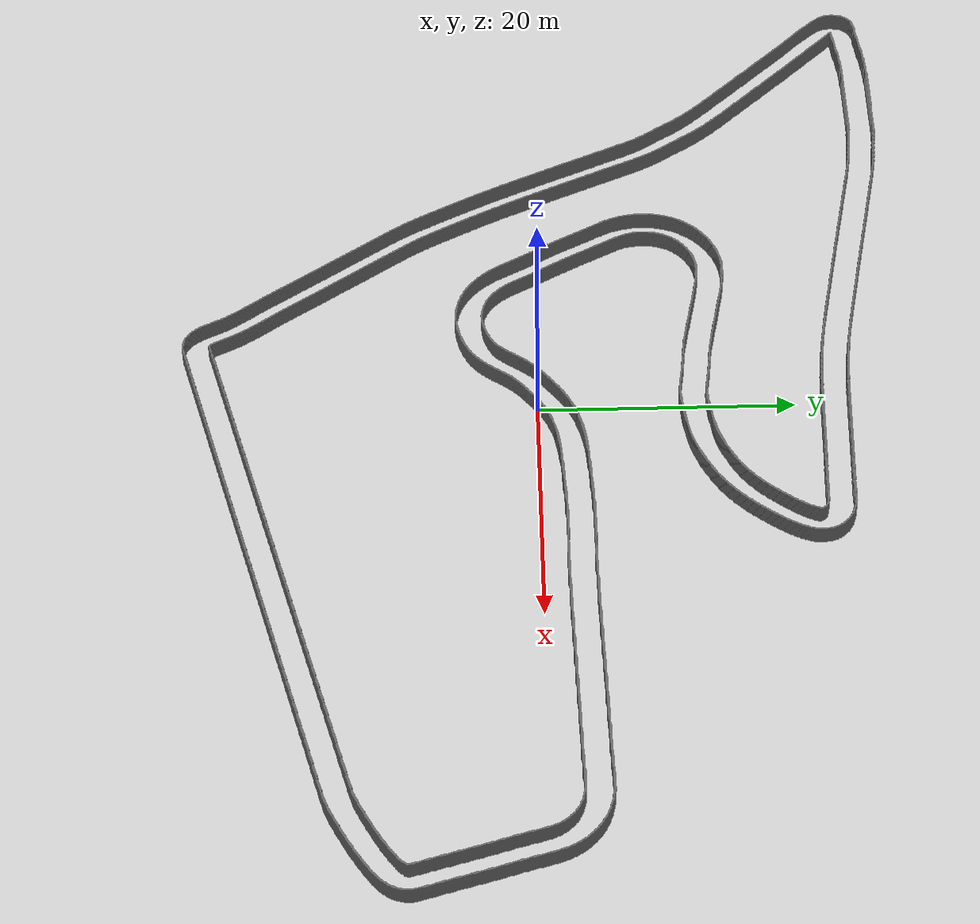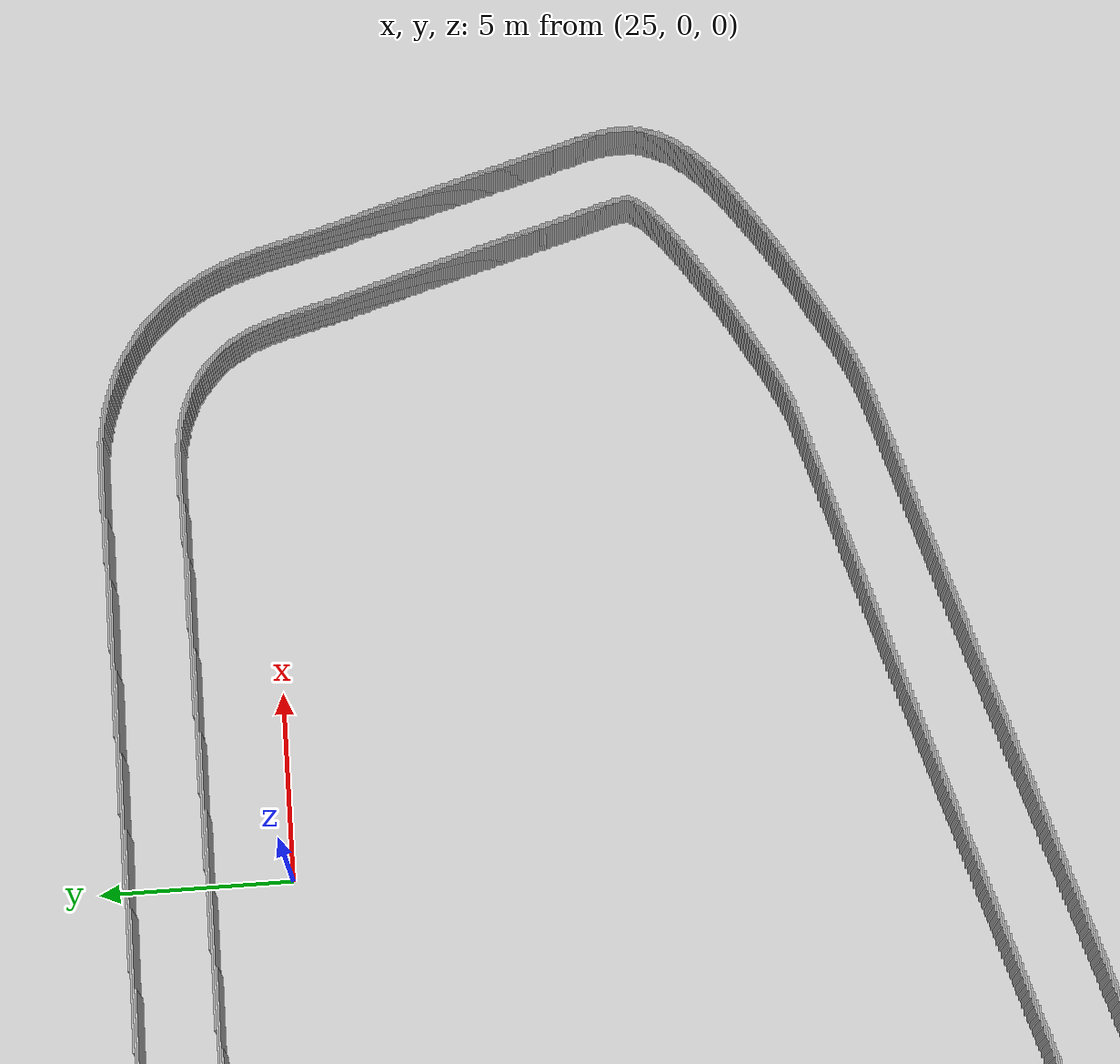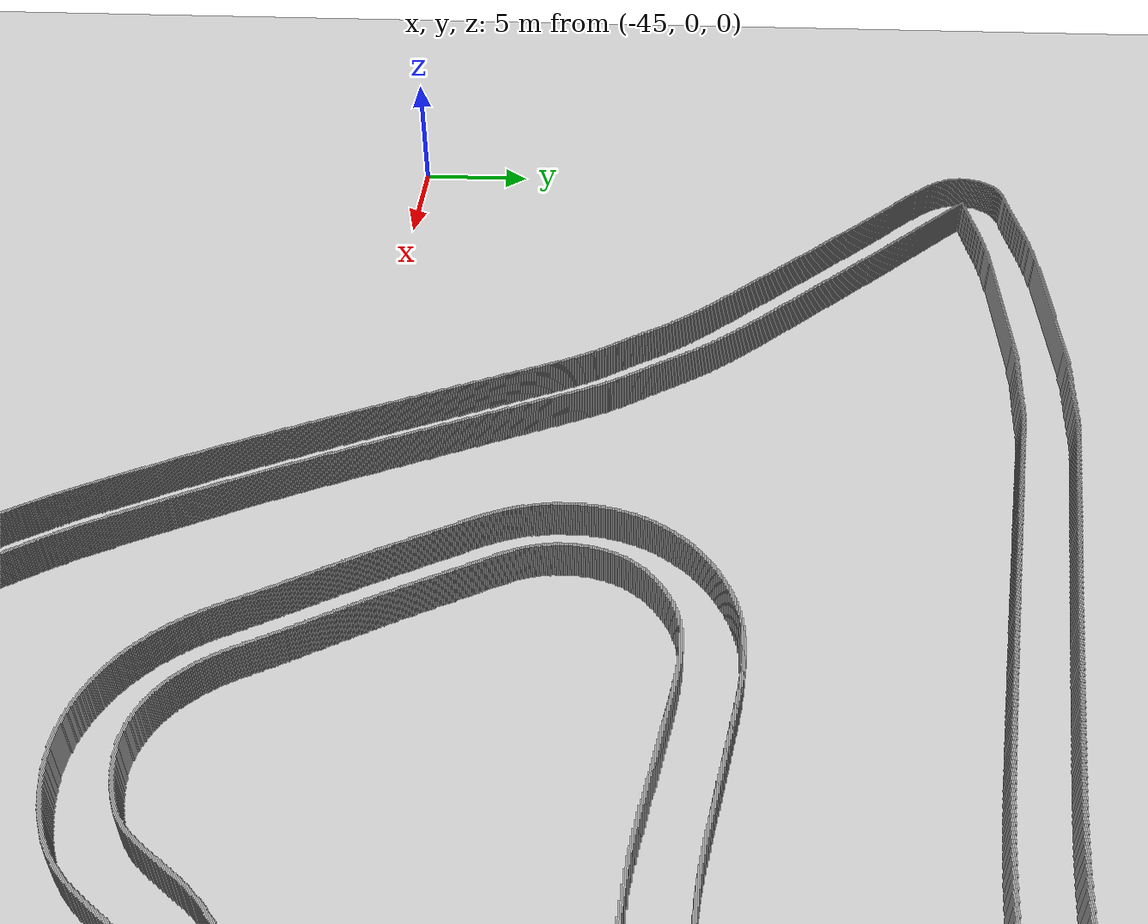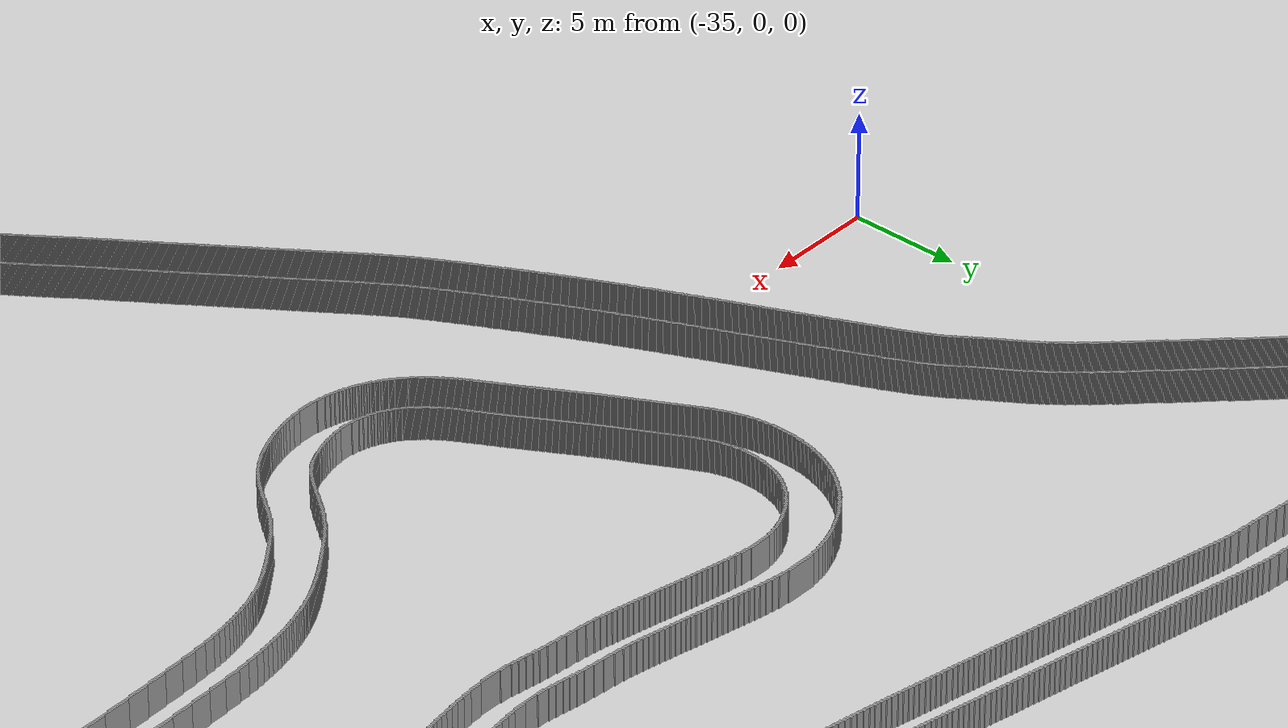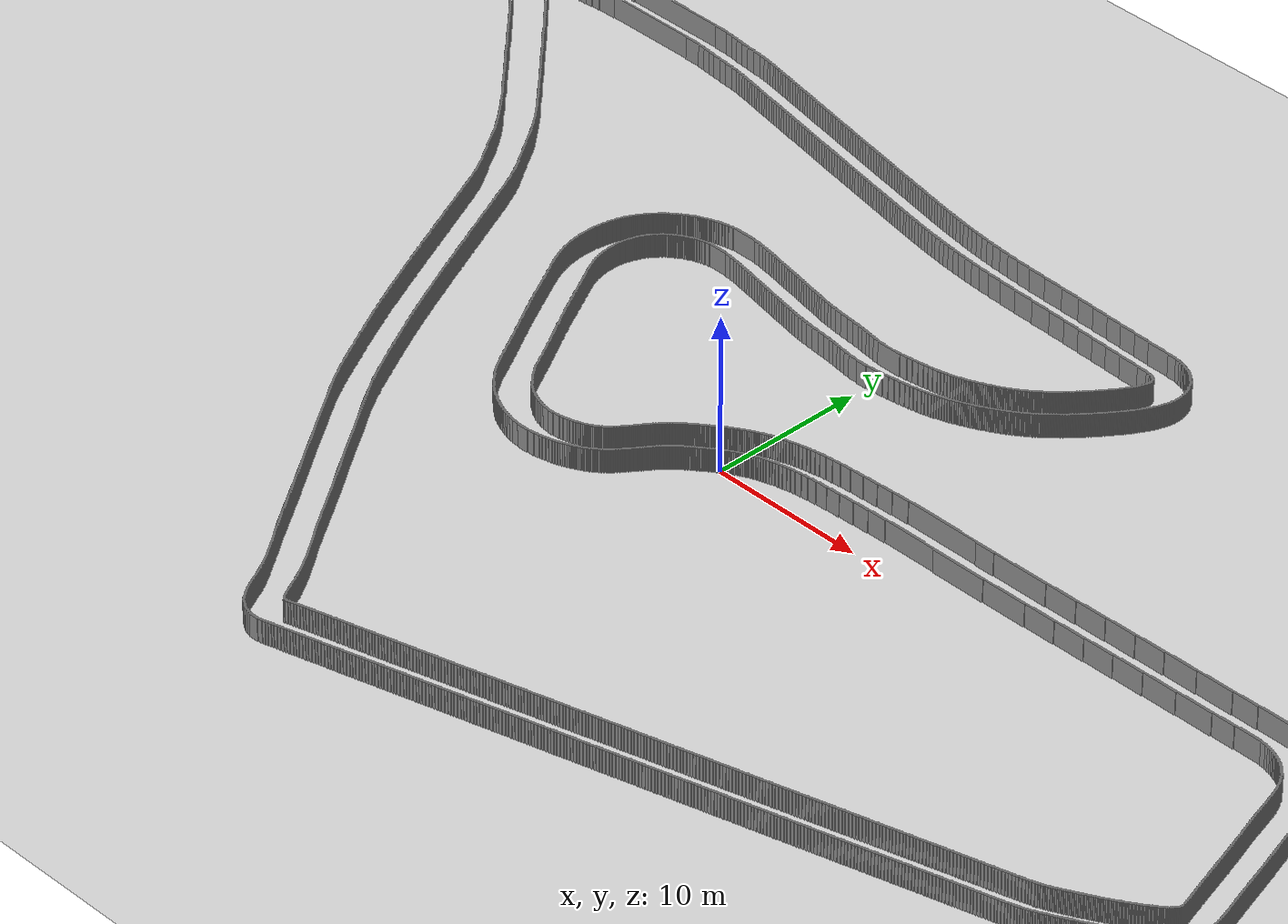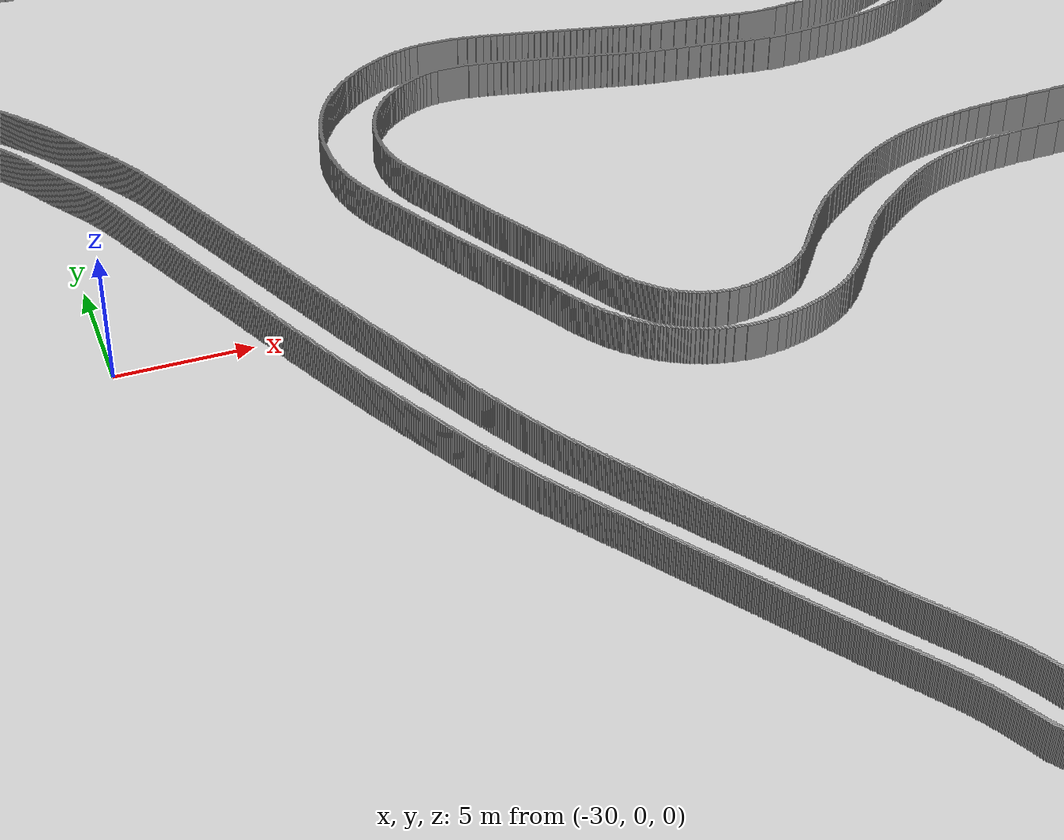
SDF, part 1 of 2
<sdf version="1.6">
 <world name="default">
  <include><uri>model://ground_plane</uri></include>
  <include><uri>model://sun</uri></include>
  <model name="map_model">
   <static>true</static>
   <link name="map_link">
    <collision name="collision_0">
     <pose>-34.175 28.85000000000001 0.75 0 0 0</pose>
     <geometry><box><size>3.75 0.05 1.5</size></box></geometry>
    </collision>
    <visual name="visual_0">
     <pose>-34.175 28.85000000000001 0.75 0 0 0</pose>
     <geometry><box><size>3.75 0.05 1.5</size></box></geometry>
     <material><ambient>0.3 0.3 0.3 1</ambient><diffuse>0.7 0.7 0.7 1</diffuse></material>
    </visual>
    <collision name="collision_1">
     <pose>-33.175 28.80000000000001 0.75 0 0 0</pose>
     <geometry><box><size>8.35 0.05 1.5</size></box></geometry>
    </collision>
    <visual name="visual_1">
     <pose>-33.175 28.80000000000001 0.75 0 0 0</pose>
     <geometry><box><size>8.35 0.05 1.5</size></box></geometry>
     <material><ambient>0.3 0.3 0.3 1</ambient><diffuse>0.7 0.7 0.7 1</diffuse></material>
    </visual>
    <collision name="collision_2">
     <pose>-33.25 28.75 0.75 0 0 0</pose>
     <geometry><box><size>9.600000000000001 0.05 1.5</size></box></geometry>
    </collision>
    <visual name="visual_2">
     <pose>-33.25 28.75 0.75 0 0 0</pose>
     <geometry><box><size>9.600000000000001 0.05 1.5</size></box></geometry>
     <material><ambient>0.3 0.3 0.3 1</ambient><diffuse>0.7 0.7 0.7 1</diffuse></material>
    </visual>
    <collision name="collision_3">
     <pose>-37.525 28.700000000000003 0.75 0 0 0</pose>
     <geometry><box><size>1.9500000000000002 0.05 1.5</size></box></geometry>
    </collision>
    <visual name="visual_3">
     <pose>-37.525 28.700000000000003 0.75 0 0 0</pose>
     <geometry><box><size>1.9500000000000002 0.05 1.5</size></box></geometry>
     <material><ambient>0.3 0.3 0.3 1</ambient><diffuse>0.7 0.7 0.7 1</diffuse></material>
    </visual>
    <collision name="collision_4">
     <pose>-28.9 28.700000000000003 0.75 0 0 0</pose>
     <geometry><box><size>1.8 0.05 1.5</size></box></geometry>
    </collision>
    <visual name="visual_4">
     <pose>-28.9 28.700000000000003 0.75 0 0 0</pose>
     <geometry><box><size>1.8 0.05 1.5</size></box></geometry>
     <material><ambient>0.3 0.3 0.3 1</ambient><diffuse>0.7 0.7 0.7 1</diffuse></material>
    </visual>
    <collision name="collision_5">
     <pose>-38.25 28.650000000000006 0.75 0 0 0</pose>
     <geometry><box><size>1.4000000000000001 0.05 1.5</size></box></geometry>
    </collision>
    <visual name="visual_5">
     <pose>-38.25 28.650000000000006 0.75 0 0 0</pose>
     <geometry><box><size>1.4000000000000001 0.05 1.5</size></box></geometry>
     <material><ambient>0.3 0.3 0.3 1</ambient><diffuse>0.7 0.7 0.7 1</diffuse></material>
    </visual>
    <collision name="collision_6">
     <pose>-28.2 28.650000000000006 0.75 0 0 0</pose>
     <geometry><box><size>1.3 0.05 1.5</size></box></geometry>
    </collision>
    <visual name="visual_6">
     <pose>-28.2 28.650000000000006 0.75 0 0 0</pose>
     <geometry><box><size>1.3 0.05 1.5</size></box></geometry>
     <material><ambient>0.3 0.3 0.3 1</ambient><diffuse>0.7 0.7 0.7 1</diffuse></material>
    </visual>
    <collision name="collision_7">
     <pose>-38.725 28.60000000000001 0.75 0 0 0</pose>
     <geometry><box><size>1.1500000000000001 0.05 1.5</size></box></geometry>
    </collision>
    <visual name="visual_7">
     <pose>-38.725 28.60000000000001 0.75 0 0 0</pose>
     <geometry><box><size>1.1500000000000001 0.05 1.5</size></box></geometry>
     <material><ambient>0.3 0.3 0.3 1</ambient><diffuse>0.7 0.7 0.7 1</diffuse></material>
    </visual>
    <collision name="collision_8">
     <pose>-27.674999999999997 28.60000000000001 0.75 0 0 0</pose>
     <geometry><box><size>1.35 0.05 1.5</size></box></geometry>
    </collision>
    <visual name="visual_8">
     <pose>-27.674999999999997 28.60000000000001 0.75 0 0 0</pose>
     <geometry><box><size>1.35 0.05 1.5</size></box></geometry>
     <material><ambient>0.3 0.3 0.3 1</ambient><diffuse>0.7 0.7 0.7 1</diffuse></material>
    </visual>
    <collision name="collision_9">
     <pose>-39.125 28.55000000000001 0.75 0 0 0</pose>
     <geometry><box><size>1.05 0.05 1.5</size></box></geometry>
    </collision>
    <visual name="visual_9">
     <pose>-39.125 28.55000000000001 0.75 0 0 0</pose>
     <geometry><box><size>1.05 0.05 1.5</size></box></geometry>
     <material><ambient>0.3 0.3 0.3 1</ambient><diffuse>0.7 0.7 0.7 1</diffuse></material>
    </visual>
    <collision name="collision_10">
     <pose>-27.174999999999997 28.55000000000001 0.75 0 0 0</pose>
     <geometry><box><size>1.4500000000000002 0.05 1.5</size></box></geometry>
    </collision>
    <visual name="visual_10">
     <pose>-27.174999999999997 28.55000000000001 0.75 0 0 0</pose>
     <geometry><box><size>1.4500000000000002 0.05 1.5</size></box></geometry>
     <material><ambient>0.3 0.3 0.3 1</ambient><diffuse>0.7 0.7 0.7 1</diffuse></material>
    </visual>
    <collision name="collision_11">
     <pose>-39.5 28.5 0.75 0 0 0</pose>
     <geometry><box><size>1.0 0.05 1.5</size></box></geometry>
    </collision>
    <visual name="visual_11">
     <pose>-39.5 28.5 0.75 0 0 0</pose>
     <geometry><box><size>1.0 0.05 1.5</size></box></geometry>
     <material><ambient>0.3 0.3 0.3 1</ambient><diffuse>0.7 0.7 0.7 1</diffuse></material>
    </visual>
    <collision name="collision_12">
     <pose>-26.7 28.5 0.75 0 0 0</pose>
     <geometry><box><size>1.5 0.05 1.5</size></box></geometry>
    </collision>
    <visual name="visual_12">
     <pose>-26.7 28.5 0.75 0 0 0</pose>
     <geometry><box><size>1.5 0.05 1.5</size></box></geometry>
     <material><ambient>0.3 0.3 0.3 1</ambient><diffuse>0.7 0.7 0.7 1</diffuse></material>
    </visual>
    <collision name="collision_13">
     <pose>-39.875 28.450000000000003 0.75 0 0 0</pose>
     <geometry><box><size>1.05 0.05 1.5</size></box></geometry>
    </collision>
    <visual name="visual_13">
     <pose>-39.875 28.450000000000003 0.75 0 0 0</pose>
     <geometry><box><size>1.05 0.05 1.5</size></box></geometry>
     <material><ambient>0.3 0.3 0.3 1</ambient><diffuse>0.7 0.7 0.7 1</diffuse></material>
    </visual>
    <collision name="collision_14">
     <pose>-26.174999999999997 28.450000000000003 0.75 0 0 0</pose>
     <geometry><box><size>1.4500000000000002 0.05 1.5</size></box></geometry>
    </collision>
    <visual name="visual_14">
     <pose>-26.174999999999997 28.450000000000003 0.75 0 0 0</pose>
     <geometry><box><size>1.4500000000000002 0.05 1.5</size></box></geometry>
     <material><ambient>0.3 0.3 0.3 1</ambient><diffuse>0.7 0.7 0.7 1</diffuse></material>
    </visual>
    <collision name="collision_15">
     <pose>-40.25 28.400000000000006 0.75 0 0 0</pose>
     <geometry><box><size>1.0 0.05 1.5</size></box></geometry>
    </collision>
    <visual name="visual_15">
     <pose>-40.25 28.400000000000006 0.75 0 0 0</pose>
     <geometry><box><size>1.0 0.05 1.5</size></box></geometry>
     <material><ambient>0.3 0.3 0.3 1</ambient><diffuse>0.7 0.7 0.7 1</diffuse></material>
    </visual>
    <collision name="collision_16">
     <pose>-25.724999999999998 28.400000000000006 0.75 0 0 0</pose>
     <geometry><box><size>1.25 0.05 1.5</size></box></geometry>
    </collision>
    <visual name="visual_16">
     <pose>-25.724999999999998 28.400000000000006 0.75 0 0 0</pose>
     <geometry><box><size>1.25 0.05 1.5</size></box></geometry>
     <material><ambient>0.3 0.3 0.3 1</ambient><diffuse>0.7 0.7 0.7 1</diffuse></material>
    </visual>
    <collision name="collision_17">
     <pose>-40.65 28.35000000000001 0.75 0 0 0</pose>
     <geometry><box><size>1.1 0.05 1.5</size></box></geometry>
    </collision>
    <visual name="visual_17">
     <pose>-40.65 28.35000000000001 0.75 0 0 0</pose>
     <geometry><box><size>1.1 0.05 1.5</size></box></geometry>
     <material><ambient>0.3 0.3 0.3 1</ambient><diffuse>0.7 0.7 0.7 1</diffuse></material>
    </visual>
    <collision name="collision_18">
     <pose>-25.325 28.35000000000001 0.75 0 0 0</pose>
     <geometry><box><size>0.9500000000000001 0.05 1.5</size></box></geometry>
    </collision>
    <visual name="visual_18">
     <pose>-25.325 28.35000000000001 0.75 0 0 0</pose>
     <geometry><box><size>0.9500000000000001 0.05 1.5</size></box></geometry>
     <material><ambient>0.3 0.3 0.3 1</ambient><diffuse>0.7 0.7 0.7 1</diffuse></material>
    </visual>
    <collision name="collision_19">
     <pose>-41.125 28.30000000000001 0.75 0 0 0</pose>
     <geometry><box><size>1.35 0.05 1.5</size></box></geometry>
    </collision>
    <visual name="visual_19">
     <pose>-41.125 28.30000000000001 0.75 0 0 0</pose>
     <geometry><box><size>1.35 0.05 1.5</size></box></geometry>
     <material><ambient>0.3 0.3 0.3 1</ambient><diffuse>0.7 0.7 0.7 1</diffuse></material>
    </visual>
    <collision name="collision_20">
     <pose>-24.974999999999998 28.30000000000001 0.75 0 0 0</pose>
     <geometry><box><size>0.8500000000000001 0.05 1.5</size></box></geometry>
    </collision>
    <visual name="visual_20">
     <pose>-24.974999999999998 28.30000000000001 0.75 0 0 0</pose>
     <geometry><box><size>0.8500000000000001 0.05 1.5</size></box></geometry>
     <material><ambient>0.3 0.3 0.3 1</ambient><diffuse>0.7 0.7 0.7 1</diffuse></material>
    </visual>
    <collision name="collision_21">
     <pose>-41.5 28.25 0.75 0 0 0</pose>
     <geometry><box><size>1.3 0.05 1.5</size></box></geometry>
    </collision>
    <visual name="visual_21">
     <pose>-41.5 28.25 0.75 0 0 0</pose>
     <geometry><box><size>1.3 0.05 1.5</size></box></geometry>
     <material><ambient>0.3 0.3 0.3 1</ambient><diffuse>0.7 0.7 0.7 1</diffuse></material>
    </visual>
    <collision name="collision_22">
     <pose>-24.674999999999997 28.25 0.75 0 0 0</pose>
     <geometry><box><size>0.75 0.05 1.5</size></box></geometry>
    </collision>
    <visual name="visual_22">
     <pose>-24.674999999999997 28.25 0.75 0 0 0</pose>
     <geometry><box><size>0.75 0.05 1.5</size></box></geometry>
     <material><ambient>0.3 0.3 0.3 1</ambient><diffuse>0.7 0.7 0.7 1</diffuse></material>
    </visual>
    <collision name="collision_23">
     <pose>-41.8 28.200000000000003 0.75 0 0 0</pose>
     <geometry><box><size>1.0 0.05 1.5</size></box></geometry>
    </collision>
    <visual name="visual_23">
     <pose>-41.8 28.200000000000003 0.75 0 0 0</pose>
     <geometry><box><size>1.0 0.05 1.5</size></box></geometry>
     <material><ambient>0.3 0.3 0.3 1</ambient><diffuse>0.7 0.7 0.7 1</diffuse></material>
    </visual>
    <collision name="collision_24">
     <pose>-24.424999999999997 28.200000000000003 0.75 0 0 0</pose>
     <geometry><box><size>0.75 0.05 1.5</size></box></geometry>
    </collision>
    <visual name="visual_24">
     <pose>-24.424999999999997 28.200000000000003 0.75 0 0 0</pose>
     <geometry><box><size>0.75 0.05 1.5</size></box></geometry>
     <material><ambient>0.3 0.3 0.3 1</ambient><diffuse>0.7 0.7 0.7 1</diffuse></material>
    </visual>
    <collision name="collision_25">
     <pose>-42.2 28.150000000000006 0.75 0 0 0</pose>
     <geometry><box><size>0.5 0.05 1.5</size></box></geometry>
    </collision>
    <visual name="visual_25">
     <pose>-42.2 28.150000000000006 0.75 0 0 0</pose>
     <geometry><box><size>0.5 0.05 1.5</size></box></geometry>
     <material><ambient>0.3 0.3 0.3 1</ambient><diffuse>0.7 0.7 0.7 1</diffuse></material>
    </visual>
    <collision name="collision_26">
     <pose>-24.15 28.150000000000006 0.75 0 0 0</pose>
     <geometry><box><size>0.7000000000000001 0.05 1.5</size></box></geometry>
    </collision>
    <visual name="visual_26">
     <pose>-24.15 28.150000000000006 0.75 0 0 0</pose>
     <geometry><box><size>0.7000000000000001 0.05 1.5</size></box></geometry>
     <material><ambient>0.3 0.3 0.3 1</ambient><diffuse>0.7 0.7 0.7 1</diffuse></material>
    </visual>
    <collision name="collision_27">
     <pose>-42.375 28.10000000000001 0.75 0 0 0</pose>
     <geometry><box><size>0.45 0.05 1.5</size></box></geometry>
    </collision>
    <visual name="visual_27">
     <pose>-42.375 28.10000000000001 0.75 0 0 0</pose>
     <geometry><box><size>0.45 0.05 1.5</size></box></geometry>
     <material><ambient>0.3 0.3 0.3 1</ambient><diffuse>0.7 0.7 0.7 1</diffuse></material>
    </visual>
    <collision name="collision_28">
     <pose>-23.9 28.10000000000001 0.75 0 0 0</pose>
     <geometry><box><size>0.7000000000000001 0.05 1.5</size></box></geometry>
    </collision>
    <visual name="visual_28">
     <pose>-23.9 28.10000000000001 0.75 0 0 0</pose>
     <geometry><box><size>0.7000000000000001 0.05 1.5</size></box></geometry>
     <material><ambient>0.3 0.3 0.3 1</ambient><diffuse>0.7 0.7 0.7 1</diffuse></material>
    </visual>
    <collision name="collision_29">
     <pose>-42.5 28.05000000000001 0.75 0 0 0</pose>
     <geometry><box><size>0.4 0.05 1.5</size></box></geometry>
    </collision>
    <visual name="visual_29">
     <pose>-42.5 28.05000000000001 0.75 0 0 0</pose>
     <geometry><box><size>0.4 0.05 1.5</size></box></geometry>
     <material><ambient>0.3 0.3 0.3 1</ambient><diffuse>0.7 0.7 0.7 1</diffuse></material>
    </visual>
    <collision name="collision_30">
     <pose>-23.65 28.05000000000001 0.75 0 0 0</pose>
     <geometry><box><size>0.7000000000000001 0.05 1.5</size></box></geometry>
    </collision>
    <visual name="visual_30">
     <pose>-23.65 28.05000000000001 0.75 0 0 0</pose>
     <geometry><box><size>0.7000000000000001 0.05 1.5</size></box></geometry>
     <material><ambient>0.3 0.3 0.3 1</ambient><diffuse>0.7 0.7 0.7 1</diffuse></material>
    </visual>
    <collision name="collision_31">
     <pose>-42.625 28.0 0.75 0 0 0</pose>
     <geometry><box><size>0.35000000000000003 0.05 1.5</size></box></geometry>
    </collision>
    <visual name="visual_31">
     <pose>-42.625 28.0 0.75 0 0 0</pose>
     <geometry><box><size>0.35000000000000003 0.05 1.5</size></box></geometry>
     <material><ambient>0.3 0.3 0.3 1</ambient><diffuse>0.7 0.7 0.7 1</diffuse></material>
    </visual>
    <collision name="collision_32">
     <pose>-23.4 28.0 0.75 0 0 0</pose>
     <geometry><box><size>0.7000000000000001 0.05 1.5</size></box></geometry>
    </collision>
    <visual name="visual_32">
     <pose>-23.4 28.0 0.75 0 0 0</pose>
     <geometry><box><size>0.7000000000000001 0.05 1.5</size></box></geometry>
     <material><ambient>0.3 0.3 0.3 1</ambient><diffuse>0.7 0.7 0.7 1</diffuse></material>
    </visual>
    <collision name="collision_33">
     <pose>-42.725 27.950000000000003 0.75 0 0 0</pose>
     <geometry><box><size>0.25 0.05 1.5</size></box></geometry>
    </collision>
    <visual name="visual_33">
     <pose>-42.725 27.950000000000003 0.75 0 0 0</pose>
     <geometry><box><size>0.25 0.05 1.5</size></box></geometry>
     <material><ambient>0.3 0.3 0.3 1</ambient><diffuse>0.7 0.7 0.7 1</diffuse></material>
    </visual>
    <collision name="collision_34">
     <pose>-23.15 27.950000000000003 0.75 0 0 0</pose>
     <geometry><box><size>0.7000000000000001 0.05 1.5</size></box></geometry>
    </collision>
    <visual name="visual_34">
     <pose>-23.15 27.950000000000003 0.75 0 0 0</pose>
     <geometry><box><size>0.7000000000000001 0.05 1.5</size></box></geometry>
     <material><ambient>0.3 0.3 0.3 1</ambient><diffuse>0.7 0.7 0.7 1</diffuse></material>
    </visual>
    <collision name="collision_35">
     <pose>-42.8 27.900000000000006 0.75 0 0 0</pose>
     <geometry><box><size>0.2 0.05 1.5</size></box></geometry>
    </collision>
    <visual name="visual_35">
     <pose>-42.8 27.900000000000006 0.75 0 0 0</pose>
     <geometry><box><size>0.2 0.05 1.5</size></box></geometry>
     <material><ambient>0.3 0.3 0.3 1</ambient><diffuse>0.7 0.7 0.7 1</diffuse></material>
    </visual>
    <collision name="collision_36">
     <pose>-22.9 27.900000000000006 0.75 0 0 0</pose>
     <geometry><box><size>0.7000000000000001 0.05 1.5</size></box></geometry>
    </collision>
    <visual name="visual_36">
     <pose>-22.9 27.900000000000006 0.75 0 0 0</pose>
     <geometry><box><size>0.7000000000000001 0.05 1.5</size></box></geometry>
     <material><ambient>0.3 0.3 0.3 1</ambient><diffuse>0.7 0.7 0.7 1</diffuse></material>
    </visual>
    <collision name="collision_37">
     <pose>-42.85 27.85000000000001 0.75 0 0 0</pose>
     <geometry><box><size>0.2 0.05 1.5</size></box></geometry>
    </collision>
    <visual name="visual_37">
     <pose>-42.85 27.85000000000001 0.75 0 0 0</pose>
     <geometry><box><size>0.2 0.05 1.5</size></box></geometry>
     <material><ambient>0.3 0.3 0.3 1</ambient><diffuse>0.7 0.7 0.7 1</diffuse></material>
    </visual>
    <collision name="collision_38">
     <pose>-22.65 27.85000000000001 0.75 0 0 0</pose>
     <geometry><box><size>0.7000000000000001 0.05 1.5</size></box></geometry>
    </collision>
    <visual name="visual_38">
     <pose>-22.65 27.85000000000001 0.75 0 0 0</pose>
     <geometry><box><size>0.7000000000000001 0.05 1.5</size></box></geometry>
     <material><ambient>0.3 0.3 0.3 1</ambient><diffuse>0.7 0.7 0.7 1</diffuse></material>
    </visual>
    <collision name="collision_39">
     <pose>-42.9 27.80000000000001 0.75 0 0 0</pose>
     <geometry><box><size>0.2 0.05 1.5</size></box></geometry>
    </collision>
    <visual name="visual_39">
     <pose>-42.9 27.80000000000001 0.75 0 0 0</pose>
     <geometry><box><size>0.2 0.05 1.5</size></box></geometry>
     <material><ambient>0.3 0.3 0.3 1</ambient><diffuse>0.7 0.7 0.7 1</diffuse></material>
    </visual>
    <collision name="collision_40">
     <pose>-22.4 27.80000000000001 0.75 0 0 0</pose>
     <geometry><box><size>0.7000000000000001 0.05 1.5</size></box></geometry>
    </collision>
    <visual name="visual_40">
     <pose>-22.4 27.80000000000001 0.75 0 0 0</pose>
     <geometry><box><size>0.7000000000000001 0.05 1.5</size></box></geometry>
     <material><ambient>0.3 0.3 0.3 1</ambient><diffuse>0.7 0.7 0.7 1</diffuse></material>
    </visual>
    <collision name="collision_41">
     <pose>-42.95 27.75 0.75 0 0 0</pose>
     <geometry><box><size>0.2 0.05 1.5</size></box></geometry>
    </collision>
    <visual name="visual_41">
     <pose>-42.95 27.75 0.75 0 0 0</pose>
     <geometry><box><size>0.2 0.05 1.5</size></box></geometry>
     <material><ambient>0.3 0.3 0.3 1</ambient><diffuse>0.7 0.7 0.7 1</diffuse></material>
    </visual>
    <collision name="collision_42">
     <pose>-22.15 27.75 0.75 0 0 0</pose>
     <geometry><box><size>0.7000000000000001 0.05 1.5</size></box></geometry>
    </collision>
    <visual name="visual_42">
     <pose>-22.15 27.75 0.75 0 0 0</pose>
     <geometry><box><size>0.7000000000000001 0.05 1.5</size></box></geometry>
     <material><ambient>0.3 0.3 0.3 1</ambient><diffuse>0.7 0.7 0.7 1</diffuse></material>
    </visual>
    <collision name="collision_43">
     <pose>-43.0 27.700000000000003 0.75 0 0 0</pose>
     <geometry><box><size>0.2 0.05 1.5</size></box></geometry>
    </collision>
    <visual name="visual_43">
     <pose>-43.0 27.700000000000003 0.75 0 0 0</pose>
     <geometry><box><size>0.2 0.05 1.5</size></box></geometry>
     <material><ambient>0.3 0.3 0.3 1</ambient><diffuse>0.7 0.7 0.7 1</diffuse></material>
    </visual>
    <collision name="collision_44">
     <pose>-21.9 27.700000000000003 0.75 0 0 0</pose>
     <geometry><box><size>0.7000000000000001 0.05 1.5</size></box></geometry>
    </collision>
    <visual name="visual_44">
     <pose>-21.9 27.700000000000003 0.75 0 0 0</pose>
     <geometry><box><size>0.7000000000000001 0.05 1.5</size></box></geometry>
     <material><ambient>0.3 0.3 0.3 1</ambient><diffuse>0.7 0.7 0.7 1</diffuse></material>
    </visual>
    <collision name="collision_45">
     <pose>-43.025 27.650000000000006 0.75 0 0 0</pose>
     <geometry><box><size>0.15000000000000002 0.05 1.5</size></box></geometry>
    </collision>
    <visual name="visual_45">
     <pose>-43.025 27.650000000000006 0.75 0 0 0</pose>
     <geometry><box><size>0.15000000000000002 0.05 1.5</size></box></geometry>
     <material><ambient>0.3 0.3 0.3 1</ambient><diffuse>0.7 0.7 0.7 1</diffuse></material>
    </visual>
    <collision name="collision_46">
     <pose>-21.65 27.650000000000006 0.75 0 0 0</pose>
     <geometry><box><size>0.7000000000000001 0.05 1.5</size></box></geometry>
    </collision>
    <visual name="visual_46">
     <pose>-21.65 27.650000000000006 0.75 0 0 0</pose>
     <geometry><box><size>0.7000000000000001 0.05 1.5</size></box></geometry>
     <material><ambient>0.3 0.3 0.3 1</ambient><diffuse>0.7 0.7 0.7 1</diffuse></material>
    </visual>
    <collision name="collision_47">
     <pose>-43.075 27.60000000000001 0.75 0 0 0</pose>
     <geometry><box><size>0.15000000000000002 0.05 1.5</size></box></geometry>
    </collision>
    <visual name="visual_47">
     <pose>-43.075 27.60000000000001 0.75 0 0 0</pose>
     <geometry><box><size>0.15000000000000002 0.05 1.5</size></box></geometry>
     <material><ambient>0.3 0.3 0.3 1</ambient><diffuse>0.7 0.7 0.7 1</diffuse></material>
    </visual>
    <collision name="collision_48">
     <pose>-21.375 27.60000000000001 0.75 0 0 0</pose>
     <geometry><box><size>0.75 0.05 1.5</size></box></geometry>
    </collision>
    <visual name="visual_48">
     <pose>-21.375 27.60000000000001 0.75 0 0 0</pose>
     <geometry><box><size>0.75 0.05 1.5</size></box></geometry>
     <material><ambient>0.3 0.3 0.3 1</ambient><diffuse>0.7 0.7 0.7 1</diffuse></material>
    </visual>
    <collision name="collision_49">
     <pose>-43.1 27.55000000000001 0.75 0 0 0</pose>
     <geometry><box><size>0.2 0.05 1.5</size></box></geometry>
    </collision>
    <visual name="visual_49">
     <pose>-43.1 27.55000000000001 0.75 0 0 0</pose>
     <geometry><box><size>0.2 0.05 1.5</size></box></geometry>
     <material><ambient>0.3 0.3 0.3 1</ambient><diffuse>0.7 0.7 0.7 1</diffuse></material>
    </visual>
    <collision name="collision_50">
     <pose>-21.125 27.55000000000001 0.75 0 0 0</pose>
     <geometry><box><size>0.75 0.05 1.5</size></box></geometry>
    </collision>
    <visual name="visual_50">
     <pose>-21.125 27.55000000000001 0.75 0 0 0</pose>
     <geometry><box><size>0.75 0.05 1.5</size></box></geometry>
     <material><ambient>0.3 0.3 0.3 1</ambient><diffuse>0.7 0.7 0.7 1</diffuse></material>
    </visual>
    <collision name="collision_51">
     <pose>-43.15 27.5 0.75 0 0 0</pose>
     <geometry><box><size>0.2 0.05 1.5</size></box></geometry>
    </collision>
    <visual name="visual_51">
     <pose>-43.15 27.5 0.75 0 0 0</pose>
     <geometry><box><size>0.2 0.05 1.5</size></box></geometry>
     <material><ambient>0.3 0.3 0.3 1</ambient><diffuse>0.7 0.7 0.7 1</diffuse></material>
    </visual>
    <collision name="collision_52">
     <pose>-20.875 27.5 0.75 0 0 0</pose>
     <geometry><box><size>0.75 0.05 1.5</size></box></geometry>
    </collision>
    <visual name="visual_52">
     <pose>-20.875 27.5 0.75 0 0 0</pose>
     <geometry><box><size>0.75 0.05 1.5</size></box></geometry>
     <material><ambient>0.3 0.3 0.3 1</ambient><diffuse>0.7 0.7 0.7 1</diffuse></material>
    </visual>
    <collision name="collision_53">
     <pose>-43.175 27.450000000000003 0.75 0 0 0</pose>
     <geometry><box><size>0.15000000000000002 0.05 1.5</size></box></geometry>
    </collision>
    <visual name="visual_53">
     <pose>-43.175 27.450000000000003 0.75 0 0 0</pose>
     <geometry><box><size>0.15000000000000002 0.05 1.5</size></box></geometry>
     <material><ambient>0.3 0.3 0.3 1</ambient><diffuse>0.7 0.7 0.7 1</diffuse></material>
    </visual>
    <collision name="collision_54">
     <pose>-20.625 27.450000000000003 0.75 0 0 0</pose>
     <geometry><box><size>0.75 0.05 1.5</size></box></geometry>
    </collision>
    <visual name="visual_54">
     <pose>-20.625 27.450000000000003 0.75 0 0 0</pose>
     <geometry><box><size>0.75 0.05 1.5</size></box></geometry>
     <material><ambient>0.3 0.3 0.3 1</ambient><diffuse>0.7 0.7 0.7 1</diffuse></material>
    </visual>
    <collision name="collision_55">
     <pose>-43.225 27.400000000000006 0.75 0 0 0</pose>
     <geometry><box><size>0.15000000000000002 0.05 1.5</size></box></geometry>
    </collision>
    <visual name="visual_55">
     <pose>-43.225 27.400000000000006 0.75 0 0 0</pose>
     <geometry><box><size>0.15000000000000002 0.05 1.5</size></box></geometry>
     <material><ambient>0.3 0.3 0.3 1</ambient><diffuse>0.7 0.7 0.7 1</diffuse></material>
    </visual>
    <collision name="collision_56">
     <pose>-20.375 27.400000000000006 0.75 0 0 0</pose>
     <geometry><box><size>0.75 0.05 1.5</size></box></geometry>
    </collision>
    <visual name="visual_56">
     <pose>-20.375 27.400000000000006 0.75 0 0 0</pose>
     <geometry><box><size>0.75 0.05 1.5</size></box></geometry>
     <material><ambient>0.3 0.3 0.3 1</ambient><diffuse>0.7 0.7 0.7 1</diffuse></material>
    </visual>
    <collision name="collision_57">
     <pose>-43.25 27.35000000000001 0.75 0 0 0</pose>
     <geometry><box><size>0.2 0.05 1.5</size></box></geometry>
    </collision>
    <visual name="visual_57">
     <pose>-43.25 27.35000000000001 0.75 0 0 0</pose>
     <geometry><box><size>0.2 0.05 1.5</size></box></geometry>
     <material><ambient>0.3 0.3 0.3 1</ambient><diffuse>0.7 0.7 0.7 1</diffuse></material>
    </visual>
    <collision name="collision_58">
     <pose>-20.125 27.35000000000001 0.75 0 0 0</pose>
     <geometry><box><size>0.75 0.05 1.5</size></box></geometry>
    </collision>
    <visual name="visual_58">
     <pose>-20.125 27.35000000000001 0.75 0 0 0</pose>
     <geometry><box><size>0.75 0.05 1.5</size></box></geometry>
     <material><ambient>0.3 0.3 0.3 1</ambient><diffuse>0.7 0.7 0.7 1</diffuse></material>
    </visual>
    <collision name="collision_59">
     <pose>-43.275 27.30000000000001 0.75 0 0 0</pose>
     <geometry><box><size>0.15000000000000002 0.05 1.5</size></box></geometry>
    </collision>
    <visual name="visual_59">
     <pose>-43.275 27.30000000000001 0.75 0 0 0</pose>
     <geometry><box><size>0.15000000000000002 0.05 1.5</size></box></geometry>
     <material><ambient>0.3 0.3 0.3 1</ambient><diffuse>0.7 0.7 0.7 1</diffuse></material>
    </visual>
    <collision name="collision_60">
     <pose>-19.875 27.30000000000001 0.75 0 0 0</pose>
     <geometry><box><size>0.75 0.05 1.5</size></box></geometry>
    </collision>
    <visual name="visual_60">
     <pose>-19.875 27.30000000000001 0.75 0 0 0</pose>
     <geometry><box><size>0.75 0.05 1.5</size></box></geometry>
     <material><ambient>0.3 0.3 0.3 1</ambient><diffuse>0.7 0.7 0.7 1</diffuse></material>
    </visual>
    <collision name="collision_61">
     <pose>-43.325 27.25 0.75 0 0 0</pose>
     <geometry><box><size>0.15000000000000002 0.05 1.5</size></box></geometry>
    </collision>
    <visual name="visual_61">
     <pose>-43.325 27.25 0.75 0 0 0</pose>
     <geometry><box><size>0.15000000000000002 0.05 1.5</size></box></geometry>
     <material><ambient>0.3 0.3 0.3 1</ambient><diffuse>0.7 0.7 0.7 1</diffuse></material>
    </visual>
    <collision name="collision_62">
     <pose>-19.625 27.25 0.75 0 0 0</pose>
     <geometry><box><size>0.75 0.05 1.5</size></box></geometry>
    </collision>
    <visual name="visual_62">
     <pose>-19.625 27.25 0.75 0 0 0</pose>
     <geometry><box><size>0.75 0.05 1.5</size></box></geometry>
     <material><ambient>0.3 0.3 0.3 1</ambient><diffuse>0.7 0.7 0.7 1</diffuse></material>
    </visual>
    <collision name="collision_63">
     <pose>-43.325 27.200000000000003 0.75 0 0 0</pose>
     <geometry><box><size>0.15000000000000002 0.05 1.5</size></box></geometry>
    </collision>
    <visual name="visual_63">
     <pose>-43.325 27.200000000000003 0.75 0 0 0</pose>
     <geometry><box><size>0.15000000000000002 0.05 1.5</size></box></geometry>
     <material><ambient>0.3 0.3 0.3 1</ambient><diffuse>0.7 0.7 0.7 1</diffuse></material>
    </visual>
    <collision name="collision_64">
     <pose>-19.375 27.200000000000003 0.75 0 0 0</pose>
     <geometry><box><size>0.75 0.05 1.5</size></box></geometry>
    </collision>
    <visual name="visual_64">
     <pose>-19.375 27.200000000000003 0.75 0 0 0</pose>
     <geometry><box><size>0.75 0.05 1.5</size></box></geometry>
     <material><ambient>0.3 0.3 0.3 1</ambient><diffuse>0.7 0.7 0.7 1</diffuse></material>
    </visual>
    <collision name="collision_65">
     <pose>-43.325 27.150000000000006 0.75 0 0 0</pose>
     <geometry><box><size>0.15000000000000002 0.05 1.5</size></box></geometry>
    </collision>
    <visual name="visual_65">
     <pose>-43.325 27.150000000000006 0.75 0 0 0</pose>
     <geometry><box><size>0.15000000000000002 0.05 1.5</size></box></geometry>
     <material><ambient>0.3 0.3 0.3 1</ambient><diffuse>0.7 0.7 0.7 1</diffuse></material>
    </visual>
    <collision name="collision_66">
     <pose>-19.099999999999998 27.150000000000006 0.75 0 0 0</pose>
     <geometry><box><size>0.7000000000000001 0.05 1.5</size></box></geometry>
    </collision>
    <visual name="visual_66">
     <pose>-19.099999999999998 27.150000000000006 0.75 0 0 0</pose>
     <geometry><box><size>0.7000000000000001 0.05 1.5</size></box></geometry>
     <material><ambient>0.3 0.3 0.3 1</ambient><diffuse>0.7 0.7 0.7 1</diffuse></material>
    </visual>
    <collision name="collision_67">
     <pose>-43.375 27.10000000000001 0.75 0 0 0</pose>
     <geometry><box><size>0.15000000000000002 0.05 1.5</size></box></geometry>
    </collision>
    <visual name="visual_67">
     <pose>-43.375 27.10000000000001 0.75 0 0 0</pose>
     <geometry><box><size>0.15000000000000002 0.05 1.5</size></box></geometry>
     <material><ambient>0.3 0.3 0.3 1</ambient><diffuse>0.7 0.7 0.7 1</diffuse></material>
    </visual>
    <collision name="collision_68">
     <pose>-18.849999999999998 27.10000000000001 0.75 0 0 0</pose>
     <geometry><box><size>0.7000000000000001 0.05 1.5</size></box></geometry>
    </collision>
    <visual name="visual_68">
     <pose>-18.849999999999998 27.10000000000001 0.75 0 0 0</pose>
     <geometry><box><size>0.7000000000000001 0.05 1.5</size></box></geometry>
     <material><ambient>0.3 0.3 0.3 1</ambient><diffuse>0.7 0.7 0.7 1</diffuse></material>
    </visual>
    <collision name="collision_69">
     <pose>-43.375 27.05000000000001 0.75 0 0 0</pose>
     <geometry><box><size>0.15000000000000002 0.05 1.5</size></box></geometry>
    </collision>
    <visual name="visual_69">
     <pose>-43.375 27.05000000000001 0.75 0 0 0</pose>
     <geometry><box><size>0.15000000000000002 0.05 1.5</size></box></geometry>
     <material><ambient>0.3 0.3 0.3 1</ambient><diffuse>0.7 0.7 0.7 1</diffuse></material>
    </visual>
    <collision name="collision_70">
     <pose>-18.599999999999998 27.05000000000001 0.75 0 0 0</pose>
     <geometry><box><size>0.7000000000000001 0.05 1.5</size></box></geometry>
    </collision>
    <visual name="visual_70">
     <pose>-18.599999999999998 27.05000000000001 0.75 0 0 0</pose>
     <geometry><box><size>0.7000000000000001 0.05 1.5</size></box></geometry>
     <material><ambient>0.3 0.3 0.3 1</ambient><diffuse>0.7 0.7 0.7 1</diffuse></material>
    </visual>
    <collision name="collision_71">
     <pose>-43.375 27.0 0.75 0 0 0</pose>
     <geometry><box><size>0.15000000000000002 0.05 1.5</size></box></geometry>
    </collision>
    <visual name="visual_71">
     <pose>-43.375 27.0 0.75 0 0 0</pose>
     <geometry><box><size>0.15000000000000002 0.05 1.5</size></box></geometry>
     <material><ambient>0.3 0.3 0.3 1</ambient><diffuse>0.7 0.7 0.7 1</diffuse></material>
    </visual>
    <collision name="collision_72">
     <pose>-18.349999999999998 27.0 0.75 0 0 0</pose>
     <geometry><box><size>0.7000000000000001 0.05 1.5</size></box></geometry>
    </collision>
    <visual name="visual_72">
     <pose>-18.349999999999998 27.0 0.75 0 0 0</pose>
     <geometry><box><size>0.7000000000000001 0.05 1.5</size></box></geometry>
     <material><ambient>0.3 0.3 0.3 1</ambient><diffuse>0.7 0.7 0.7 1</diffuse></material>
    </visual>
    <collision name="collision_73">
     <pose>-43.375 26.950000000000003 0.75 0 0 0</pose>
     <geometry><box><size>0.15000000000000002 0.05 1.5</size></box></geometry>
    </collision>
    <visual name="visual_73">
     <pose>-43.375 26.950000000000003 0.75 0 0 0</pose>
     <geometry><box><size>0.15000000000000002 0.05 1.5</size></box></geometry>
     <material><ambient>0.3 0.3 0.3 1</ambient><diffuse>0.7 0.7 0.7 1</diffuse></material>
    </visual>
    <collision name="collision_74">
     <pose>-18.099999999999998 26.950000000000003 0.75 0 0 0</pose>
     <geometry><box><size>0.7000000000000001 0.05 1.5</size></box></geometry>
    </collision>
    <visual name="visual_74">
     <pose>-18.099999999999998 26.950000000000003 0.75 0 0 0</pose>
     <geometry><box><size>0.7000000000000001 0.05 1.5</size></box></geometry>
     <material><ambient>0.3 0.3 0.3 1</ambient><diffuse>0.7 0.7 0.7 1</diffuse></material>
    </visual>
    <collision name="collision_75">
     <pose>-43.4 26.900000000000006 0.75 0 0 0</pose>
     <geometry><box><size>0.1 0.05 1.5</size></box></geometry>
    </collision>
    <visual name="visual_75">
     <pose>-43.4 26.900000000000006 0.75 0 0 0</pose>
     <geometry><box><size>0.1 0.05 1.5</size></box></geometry>
     <material><ambient>0.3 0.3 0.3 1</ambient><diffuse>0.7 0.7 0.7 1</diffuse></material>
    </visual>
    <collision name="collision_76">
     <pose>-17.85 26.900000000000006 0.75 0 0 0</pose>
     <geometry><box><size>0.7000000000000001 0.05 1.5</size></box></geometry>
    </collision>
    <visual name="visual_76">
     <pose>-17.85 26.900000000000006 0.75 0 0 0</pose>
     <geometry><box><size>0.7000000000000001 0.05 1.5</size></box></geometry>
     <material><ambient>0.3 0.3 0.3 1</ambient><diffuse>0.7 0.7 0.7 1</diffuse></material>
    </visual>
    <collision name="collision_77">
     <pose>-43.425 26.85000000000001 0.75 0 0 0</pose>
     <geometry><box><size>0.15000000000000002 0.05 1.5</size></box></geometry>
    </collision>
    <visual name="visual_77">
     <pose>-43.425 26.85000000000001 0.75 0 0 0</pose>
     <geometry><box><size>0.15000000000000002 0.05 1.5</size></box></geometry>
     <material><ambient>0.3 0.3 0.3 1</ambient><diffuse>0.7 0.7 0.7 1</diffuse></material>
    </visual>
    <collision name="collision_78">
     <pose>-17.6 26.85000000000001 0.75 0 0 0</pose>
     <geometry><box><size>0.7000000000000001 0.05 1.5</size></box></geometry>
    </collision>
    <visual name="visual_78">
     <pose>-17.6 26.85000000000001 0.75 0 0 0</pose>
     <geometry><box><size>0.7000000000000001 0.05 1.5</size></box></geometry>
     <material><ambient>0.3 0.3 0.3 1</ambient><diffuse>0.7 0.7 0.7 1</diffuse></material>
    </visual>
    <collision name="collision_79">
     <pose>-43.425 26.80000000000001 0.75 0 0 0</pose>
     <geometry><box><size>0.15000000000000002 0.05 1.5</size></box></geometry>
    </collision>
    <visual name="visual_79">
     <pose>-43.425 26.80000000000001 0.75 0 0 0</pose>
     <geometry><box><size>0.15000000000000002 0.05 1.5</size></box></geometry>
     <material><ambient>0.3 0.3 0.3 1</ambient><diffuse>0.7 0.7 0.7 1</diffuse></material>
    </visual>
    <collision name="collision_80">
     <pose>-17.35 26.80000000000001 0.75 0 0 0</pose>
     <geometry><box><size>0.7000000000000001 0.05 1.5</size></box></geometry>
    </collision>
    <visual name="visual_80">
     <pose>-17.35 26.80000000000001 0.75 0 0 0</pose>
     <geometry><box><size>0.7000000000000001 0.05 1.5</size></box></geometry>
     <material><ambient>0.3 0.3 0.3 1</ambient><diffuse>0.7 0.7 0.7 1</diffuse></material>
    </visual>
    <collision name="collision_81">
     <pose>-43.425 26.75 0.75 0 0 0</pose>
     <geometry><box><size>0.15000000000000002 0.05 1.5</size></box></geometry>
    </collision>
    <visual name="visual_81">
     <pose>-43.425 26.75 0.75 0 0 0</pose>
     <geometry><box><size>0.15000000000000002 0.05 1.5</size></box></geometry>
     <material><ambient>0.3 0.3 0.3 1</ambient><diffuse>0.7 0.7 0.7 1</diffuse></material>
    </visual>
    <collision name="collision_82">
     <pose>-33.175 26.75 0.75 0 0 0</pose>
     <geometry><box><size>7.95 0.05 1.5</size></box></geometry>
    </collision>
    <visual name="visual_82">
     <pose>-33.175 26.75 0.75 0 0 0</pose>
     <geometry><box><size>7.95 0.05 1.5</size></box></geometry>
     <material><ambient>0.3 0.3 0.3 1</ambient><diffuse>0.7 0.7 0.7 1</diffuse></material>
    </visual>
    <collision name="collision_83">
     <pose>-17.1 26.75 0.75 0 0 0</pose>
     <geometry><box><size>0.7000000000000001 0.05 1.5</size></box></geometry>
    </collision>
    <visual name="visual_83">
     <pose>-17.1 26.75 0.75 0 0 0</pose>
     <geometry><box><size>0.7000000000000001 0.05 1.5</size></box></geometry>
     <material><ambient>0.3 0.3 0.3 1</ambient><diffuse>0.7 0.7 0.7 1</diffuse></material>
    </visual>
    <collision name="collision_84">
     <pose>-43.425 26.700000000000003 0.75 0 0 0</pose>
     <geometry><box><size>0.15000000000000002 0.05 1.5</size></box></geometry>
    </collision>
    <visual name="visual_84">
     <pose>-43.425 26.700000000000003 0.75 0 0 0</pose>
     <geometry><box><size>0.15000000000000002 0.05 1.5</size></box></geometry>
     <material><ambient>0.3 0.3 0.3 1</ambient><diffuse>0.7 0.7 0.7 1</diffuse></material>
    </visual>
    <collision name="collision_85">
     <pose>-33.25 26.700000000000003 0.75 0 0 0</pose>
     <geometry><box><size>9.200000000000001 0.05 1.5</size></box></geometry>
    </collision>
    <visual name="visual_85">
     <pose>-33.25 26.700000000000003 0.75 0 0 0</pose>
     <geometry><box><size>9.200000000000001 0.05 1.5</size></box></geometry>
     <material><ambient>0.3 0.3 0.3 1</ambient><diffuse>0.7 0.7 0.7 1</diffuse></material>
    </visual>
    <collision name="collision_86">
     <pose>-16.85 26.700000000000003 0.75 0 0 0</pose>
     <geometry><box><size>0.7000000000000001 0.05 1.5</size></box></geometry>
    </collision>
    <visual name="visual_86">
     <pose>-16.85 26.700000000000003 0.75 0 0 0</pose>
     <geometry><box><size>0.7000000000000001 0.05 1.5</size></box></geometry>
     <material><ambient>0.3 0.3 0.3 1</ambient><diffuse>0.7 0.7 0.7 1</diffuse></material>
    </visual>
    <collision name="collision_87">
     <pose>-43.45 26.650000000000006 0.75 0 0 0</pose>
     <geometry><box><size>0.1 0.05 1.5</size></box></geometry>
    </collision>
    <visual name="visual_87">
     <pose>-43.45 26.650000000000006 0.75 0 0 0</pose>
     <geometry><box><size>0.1 0.05 1.5</size></box></geometry>
     <material><ambient>0.3 0.3 0.3 1</ambient><diffuse>0.7 0.7 0.7 1</diffuse></material>
    </visual>
    <collision name="collision_88">
     <pose>-37.225 26.650000000000006 0.75 0 0 0</pose>
     <geometry><box><size>2.15 0.05 1.5</size></box></geometry>
    </collision>
    <visual name="visual_88">
     <pose>-37.225 26.650000000000006 0.75 0 0 0</pose>
     <geometry><box><size>2.15 0.05 1.5</size></box></geometry>
     <material><ambient>0.3 0.3 0.3 1</ambient><diffuse>0.7 0.7 0.7 1</diffuse></material>
    </visual>
    <collision name="collision_89">
     <pose>-29.174999999999997 26.650000000000006 0.75 0 0 0</pose>
     <geometry><box><size>1.9500000000000002 0.05 1.5</size></box></geometry>
    </collision>
    <visual name="visual_89">
     <pose>-29.174999999999997 26.650000000000006 0.75 0 0 0</pose>
     <geometry><box><size>1.9500000000000002 0.05 1.5</size></box></geometry>
     <material><ambient>0.3 0.3 0.3 1</ambient><diffuse>0.7 0.7 0.7 1</diffuse></material>
    </visual>
    <collision name="collision_90">
     <pose>-16.6 26.650000000000006 0.75 0 0 0</pose>
     <geometry><box><size>0.7000000000000001 0.05 1.5</size></box></geometry>
    </collision>
    <visual name="visual_90">
     <pose>-16.6 26.650000000000006 0.75 0 0 0</pose>
     <geometry><box><size>0.7000000000000001 0.05 1.5</size></box></geometry>
     <material><ambient>0.3 0.3 0.3 1</ambient><diffuse>0.7 0.7 0.7 1</diffuse></material>
    </visual>
    <collision name="collision_91">
     <pose>-43.475 26.60000000000001 0.75 0 0 0</pose>
     <geometry><box><size>0.15000000000000002 0.05 1.5</size></box></geometry>
    </collision>
    <visual name="visual_91">
     <pose>-43.475 26.60000000000001 0.75 0 0 0</pose>
     <geometry><box><size>0.15000000000000002 0.05 1.5</size></box></geometry>
     <material><ambient>0.3 0.3 0.3 1</ambient><diffuse>0.7 0.7 0.7 1</diffuse></material>
    </visual>
    <collision name="collision_92">
     <pose>-38.05 26.60000000000001 0.75 0 0 0</pose>
     <geometry><box><size>1.4000000000000001 0.05 1.5</size></box></geometry>
    </collision>
    <visual name="visual_92">
     <pose>-38.05 26.60000000000001 0.75 0 0 0</pose>
     <geometry><box><size>1.4000000000000001 0.05 1.5</size></box></geometry>
     <material><ambient>0.3 0.3 0.3 1</ambient><diffuse>0.7 0.7 0.7 1</diffuse></material>
    </visual>
    <collision name="collision_93">
     <pose>-28.375 26.60000000000001 0.75 0 0 0</pose>
     <geometry><box><size>1.35 0.05 1.5</size></box></geometry>
    </collision>
    <visual name="visual_93">
     <pose>-28.375 26.60000000000001 0.75 0 0 0</pose>
     <geometry><box><size>1.35 0.05 1.5</size></box></geometry>
     <material><ambient>0.3 0.3 0.3 1</ambient><diffuse>0.7 0.7 0.7 1</diffuse></material>
    </visual>
    <collision name="collision_94">
     <pose>-16.35 26.60000000000001 0.75 0 0 0</pose>
     <geometry><box><size>0.7000000000000001 0.05 1.5</size></box></geometry>
    </collision>
    <visual name="visual_94">
     <pose>-16.35 26.60000000000001 0.75 0 0 0</pose>
     <geometry><box><size>0.7000000000000001 0.05 1.5</size></box></geometry>
     <material><ambient>0.3 0.3 0.3 1</ambient><diffuse>0.7 0.7 0.7 1</diffuse></material>
    </visual>
    <collision name="collision_95">
     <pose>-43.475 26.549999999999997 0.75 0 0 0</pose>
     <geometry><box><size>0.15000000000000002 0.05 1.5</size></box></geometry>
    </collision>
    <visual name="visual_95">
     <pose>-43.475 26.549999999999997 0.75 0 0 0</pose>
     <geometry><box><size>0.15000000000000002 0.05 1.5</size></box></geometry>
     <material><ambient>0.3 0.3 0.3 1</ambient><diffuse>0.7 0.7 0.7 1</diffuse></material>
    </visual>
    <collision name="collision_96">
     <pose>-38.525 26.549999999999997 0.75 0 0 0</pose>
     <geometry><box><size>1.1500000000000001 0.05 1.5</size></box></geometry>
    </collision>
    <visual name="visual_96">
     <pose>-38.525 26.549999999999997 0.75 0 0 0</pose>
     <geometry><box><size>1.1500000000000001 0.05 1.5</size></box></geometry>
     <material><ambient>0.3 0.3 0.3 1</ambient><diffuse>0.7 0.7 0.7 1</diffuse></material>
    </visual>
    <collision name="collision_97">
     <pose>-27.875 26.549999999999997 0.75 0 0 0</pose>
     <geometry><box><size>1.35 0.05 1.5</size></box></geometry>
    </collision>
    <visual name="visual_97">
     <pose>-27.875 26.549999999999997 0.75 0 0 0</pose>
     <geometry><box><size>1.35 0.05 1.5</size></box></geometry>
     <material><ambient>0.3 0.3 0.3 1</ambient><diffuse>0.7 0.7 0.7 1</diffuse></material>
    </visual>
    <collision name="collision_98">
     <pose>-16.1 26.549999999999997 0.75 0 0 0</pose>
     <geometry><box><size>0.7000000000000001 0.05 1.5</size></box></geometry>
    </collision>
    <visual name="visual_98">
     <pose>-16.1 26.549999999999997 0.75 0 0 0</pose>
     <geometry><box><size>0.7000000000000001 0.05 1.5</size></box></geometry>
     <material><ambient>0.3 0.3 0.3 1</ambient><diffuse>0.7 0.7 0.7 1</diffuse></material>
    </visual>
    <collision name="collision_99">
     <pose>-43.475 26.5 0.75 0 0 0</pose>
     <geometry><box><size>0.15000000000000002 0.05 1.5</size></box></geometry>
    </collision>
    <visual name="visual_99">
     <pose>-43.475 26.5 0.75 0 0 0</pose>
     <geometry><box><size>0.15000000000000002 0.05 1.5</size></box></geometry>
     <material><ambient>0.3 0.3 0.3 1</ambient><diffuse>0.7 0.7 0.7 1</diffuse></material>
    </visual>
    <collision name="collision_100">
     <pose>-38.925 26.5 0.75 0 0 0</pose>
     <geometry><box><size>1.05 0.05 1.5</size></box></geometry>
    </collision>
    <visual name="visual_100">
     <pose>-38.925 26.5 0.75 0 0 0</pose>
     <geometry><box><size>1.05 0.05 1.5</size></box></geometry>
     <material><ambient>0.3 0.3 0.3 1</ambient><diffuse>0.7 0.7 0.7 1</diffuse></material>
    </visual>
    <collision name="collision_101">
     <pose>-27.375 26.5 0.75 0 0 0</pose>
     <geometry><box><size>1.4500000000000002 0.05 1.5</size></box></geometry>
    </collision>
    <visual name="visual_101">
     <pose>-27.375 26.5 0.75 0 0 0</pose>
     <geometry><box><size>1.4500000000000002 0.05 1.5</size></box></geometry>
     <material><ambient>0.3 0.3 0.3 1</ambient><diffuse>0.7 0.7 0.7 1</diffuse></material>
    </visual>
    <collision name="collision_102">
     <pose>-15.824999999999996 26.5 0.75 0 0 0</pose>
     <geometry><box><size>0.75 0.05 1.5</size></box></geometry>
    </collision>
    <visual name="visual_102">
     <pose>-15.824999999999996 26.5 0.75 0 0 0</pose>
     <geometry><box><size>0.75 0.05 1.5</size></box></geometry>
     <material><ambient>0.3 0.3 0.3 1</ambient><diffuse>0.7 0.7 0.7 1</diffuse></material>
    </visual>
    <collision name="collision_103">
     <pose>-43.475 26.450000000000003 0.75 0 0 0</pose>
     <geometry><box><size>0.15000000000000002 0.05 1.5</size></box></geometry>
    </collision>
    <visual name="visual_103">
     <pose>-43.475 26.450000000000003 0.75 0 0 0</pose>
     <geometry><box><size>0.15000000000000002 0.05 1.5</size></box></geometry>
     <material><ambient>0.3 0.3 0.3 1</ambient><diffuse>0.7 0.7 0.7 1</diffuse></material>
    </visual>
    <collision name="collision_104">
     <pose>-39.3 26.450000000000003 0.75 0 0 0</pose>
     <geometry><box><size>1.0 0.05 1.5</size></box></geometry>
    </collision>
    <visual name="visual_104">
     <pose>-39.3 26.450000000000003 0.75 0 0 0</pose>
     <geometry><box><size>1.0 0.05 1.5</size></box></geometry>
     <material><ambient>0.3 0.3 0.3 1</ambient><diffuse>0.7 0.7 0.7 1</diffuse></material>
    </visual>
    <collision name="collision_105">
     <pose>-26.875 26.450000000000003 0.75 0 0 0</pose>
     <geometry><box><size>1.55 0.05 1.5</size></box></geometry>
    </collision>
    <visual name="visual_105">
     <pose>-26.875 26.450000000000003 0.75 0 0 0</pose>
     <geometry><box><size>1.55 0.05 1.5</size></box></geometry>
     <material><ambient>0.3 0.3 0.3 1</ambient><diffuse>0.7 0.7 0.7 1</diffuse></material>
    </visual>
    <collision name="collision_106">
     <pose>-15.574999999999996 26.450000000000003 0.75 0 0 0</pose>
     <geometry><box><size>0.75 0.05 1.5</size></box></geometry>
    </collision>
    <visual name="visual_106">
     <pose>-15.574999999999996 26.450000000000003 0.75 0 0 0</pose>
     <geometry><box><size>0.75 0.05 1.5</size></box></geometry>
     <material><ambient>0.3 0.3 0.3 1</ambient><diffuse>0.7 0.7 0.7 1</diffuse></material>
    </visual>
    <collision name="collision_107">
     <pose>-43.475 26.400000000000006 0.75 0 0 0</pose>
     <geometry><box><size>0.15000000000000002 0.05 1.5</size></box></geometry>
    </collision>
    <visual name="visual_107">
     <pose>-43.475 26.400000000000006 0.75 0 0 0</pose>
     <geometry><box><size>0.15000000000000002 0.05 1.5</size></box></geometry>
     <material><ambient>0.3 0.3 0.3 1</ambient><diffuse>0.7 0.7 0.7 1</diffuse></material>
    </visual>
    <collision name="collision_108">
     <pose>-39.675 26.400000000000006 0.75 0 0 0</pose>
     <geometry><box><size>1.05 0.05 1.5</size></box></geometry>
    </collision>
    <visual name="visual_108">
     <pose>-39.675 26.400000000000006 0.75 0 0 0</pose>
     <geometry><box><size>1.05 0.05 1.5</size></box></geometry>
     <material><ambient>0.3 0.3 0.3 1</ambient><diffuse>0.7 0.7 0.7 1</diffuse></material>
    </visual>
    <collision name="collision_109">
     <pose>-26.375 26.400000000000006 0.75 0 0 0</pose>
     <geometry><box><size>1.4500000000000002 0.05 1.5</size></box></geometry>
    </collision>
    <visual name="visual_109">
     <pose>-26.375 26.400000000000006 0.75 0 0 0</pose>
     <geometry><box><size>1.4500000000000002 0.05 1.5</size></box></geometry>
     <material><ambient>0.3 0.3 0.3 1</ambient><diffuse>0.7 0.7 0.7 1</diffuse></material>
    </visual>
    <collision name="collision_110">
     <pose>-15.324999999999996 26.400000000000006 0.75 0 0 0</pose>
     <geometry><box><size>0.75 0.05 1.5</size></box></geometry>
    </collision>
    <visual name="visual_110">
     <pose>-15.324999999999996 26.400000000000006 0.75 0 0 0</pose>
     <geometry><box><size>0.75 0.05 1.5</size></box></geometry>
     <material><ambient>0.3 0.3 0.3 1</ambient><diffuse>0.7 0.7 0.7 1</diffuse></material>
    </visual>
    <collision name="collision_111">
     <pose>-43.475 26.35000000000001 0.75 0 0 0</pose>
     <geometry><box><size>0.15000000000000002 0.05 1.5</size></box></geometry>
    </collision>
    <visual name="visual_111">
     <pose>-43.475 26.35000000000001 0.75 0 0 0</pose>
     <geometry><box><size>0.15000000000000002 0.05 1.5</size></box></geometry>
     <material><ambient>0.3 0.3 0.3 1</ambient><diffuse>0.7 0.7 0.7 1</diffuse></material>
    </visual>
    <collision name="collision_112">
     <pose>-40.025 26.35000000000001 0.75 0 0 0</pose>
     <geometry><box><size>1.05 0.05 1.5</size></box></geometry>
    </collision>
    <visual name="visual_112">
     <pose>-40.025 26.35000000000001 0.75 0 0 0</pose>
     <geometry><box><size>1.05 0.05 1.5</size></box></geometry>
     <material><ambient>0.3 0.3 0.3 1</ambient><diffuse>0.7 0.7 0.7 1</diffuse></material>
    </visual>
    <collision name="collision_113">
     <pose>-25.95 26.35000000000001 0.75 0 0 0</pose>
     <geometry><box><size>1.2000000000000002 0.05 1.5</size></box></geometry>
    </collision>
    <visual name="visual_113">
     <pose>-25.95 26.35000000000001 0.75 0 0 0</pose>
     <geometry><box><size>1.2000000000000002 0.05 1.5</size></box></geometry>
     <material><ambient>0.3 0.3 0.3 1</ambient><diffuse>0.7 0.7 0.7 1</diffuse></material>
    </visual>
    <collision name="collision_114">
     <pose>-15.074999999999996 26.35000000000001 0.75 0 0 0</pose>
     <geometry><box><size>0.75 0.05 1.5</size></box></geometry>
    </collision>
    <visual name="visual_114">
     <pose>-15.074999999999996 26.35000000000001 0.75 0 0 0</pose>
     <geometry><box><size>0.75 0.05 1.5</size></box></geometry>
     <material><ambient>0.3 0.3 0.3 1</ambient><diffuse>0.7 0.7 0.7 1</diffuse></material>
    </visual>
    <collision name="collision_115">
     <pose>-43.45 26.299999999999997 0.75 0 0 0</pose>
     <geometry><box><size>0.1 0.05 1.5</size></box></geometry>
    </collision>
    <visual name="visual_115">
     <pose>-43.45 26.299999999999997 0.75 0 0 0</pose>
     <geometry><box><size>0.1 0.05 1.5</size></box></geometry>
     <material><ambient>0.3 0.3 0.3 1</ambient><diffuse>0.7 0.7 0.7 1</diffuse></material>
    </visual>
    <collision name="collision_116">
     <pose>-40.45 26.299999999999997 0.75 0 0 0</pose>
     <geometry><box><size>1.1 0.05 1.5</size></box></geometry>
    </collision>
    <visual name="visual_116">
     <pose>-40.45 26.299999999999997 0.75 0 0 0</pose>
     <geometry><box><size>1.1 0.05 1.5</size></box></geometry>
     <material><ambient>0.3 0.3 0.3 1</ambient><diffuse>0.7 0.7 0.7 1</diffuse></material>
    </visual>
    <collision name="collision_117">
     <pose>-25.525 26.299999999999997 0.75 0 0 0</pose>
     <geometry><box><size>0.9500000000000001 0.05 1.5</size></box></geometry>
    </collision>
    <visual name="visual_117">
     <pose>-25.525 26.299999999999997 0.75 0 0 0</pose>
     <geometry><box><size>0.9500000000000001 0.05 1.5</size></box></geometry>
     <material><ambient>0.3 0.3 0.3 1</ambient><diffuse>0.7 0.7 0.7 1</diffuse></material>
    </visual>
    <collision name="collision_118">
     <pose>-14.824999999999996 26.299999999999997 0.75 0 0 0</pose>
     <geometry><box><size>0.75 0.05 1.5</size></box></geometry>
    </collision>
    <visual name="visual_118">
     <pose>-14.824999999999996 26.299999999999997 0.75 0 0 0</pose>
     <geometry><box><size>0.75 0.05 1.5</size></box></geometry>
     <material><ambient>0.3 0.3 0.3 1</ambient><diffuse>0.7 0.7 0.7 1</diffuse></material>
    </visual>
    <collision name="collision_119">
     <pose>-43.425 26.25 0.75 0 0 0</pose>
     <geometry><box><size>0.15000000000000002 0.05 1.5</size></box></geometry>
    </collision>
    <visual name="visual_119">
     <pose>-43.425 26.25 0.75 0 0 0</pose>
     <geometry><box><size>0.15000000000000002 0.05 1.5</size></box></geometry>
     <material><ambient>0.3 0.3 0.3 1</ambient><diffuse>0.7 0.7 0.7 1</diffuse></material>
    </visual>
    <collision name="collision_120">
     <pose>-40.8 26.25 0.75 0 0 0</pose>
     <geometry><box><size>1.1 0.05 1.5</size></box></geometry>
    </collision>
    <visual name="visual_120">
     <pose>-40.8 26.25 0.75 0 0 0</pose>
     <geometry><box><size>1.1 0.05 1.5</size></box></geometry>
     <material><ambient>0.3 0.3 0.3 1</ambient><diffuse>0.7 0.7 0.7 1</diffuse></material>
    </visual>
    <collision name="collision_121">
     <pose>-25.2 26.25 0.75 0 0 0</pose>
     <geometry><box><size>0.8 0.05 1.5</size></box></geometry>
    </collision>
    <visual name="visual_121">
     <pose>-25.2 26.25 0.75 0 0 0</pose>
     <geometry><box><size>0.8 0.05 1.5</size></box></geometry>
     <material><ambient>0.3 0.3 0.3 1</ambient><diffuse>0.7 0.7 0.7 1</diffuse></material>
    </visual>
    <collision name="collision_122">
     <pose>-14.549999999999997 26.25 0.75 0 0 0</pose>
     <geometry><box><size>0.7000000000000001 0.05 1.5</size></box></geometry>
    </collision>
    <visual name="visual_122">
     <pose>-14.549999999999997 26.25 0.75 0 0 0</pose>
     <geometry><box><size>0.7000000000000001 0.05 1.5</size></box></geometry>
     <material><ambient>0.3 0.3 0.3 1</ambient><diffuse>0.7 0.7 0.7 1</diffuse></material>
    </visual>
    <collision name="collision_123">
     <pose>-43.425 26.200000000000003 0.75 0 0 0</pose>
     <geometry><box><size>0.15000000000000002 0.05 1.5</size></box></geometry>
    </collision>
    <visual name="visual_123">
     <pose>-43.425 26.200000000000003 0.75 0 0 0</pose>
     <geometry><box><size>0.15000000000000002 0.05 1.5</size></box></geometry>
     <material><ambient>0.3 0.3 0.3 1</ambient><diffuse>0.7 0.7 0.7 1</diffuse></material>
    </visual>
    <collision name="collision_124">
     <pose>-41.0 26.200000000000003 0.75 0 0 0</pose>
     <geometry><box><size>0.7000000000000001 0.05 1.5</size></box></geometry>
    </collision>
    <visual name="visual_124">
     <pose>-41.0 26.200000000000003 0.75 0 0 0</pose>
     <geometry><box><size>0.7000000000000001 0.05 1.5</size></box></geometry>
     <material><ambient>0.3 0.3 0.3 1</ambient><diffuse>0.7 0.7 0.7 1</diffuse></material>
    </visual>
    <collision name="collision_125">
     <pose>-24.924999999999997 26.200000000000003 0.75 0 0 0</pose>
     <geometry><box><size>0.75 0.05 1.5</size></box></geometry>
    </collision>
    <visual name="visual_125">
     <pose>-24.924999999999997 26.200000000000003 0.75 0 0 0</pose>
     <geometry><box><size>0.75 0.05 1.5</size></box></geometry>
     <material><ambient>0.3 0.3 0.3 1</ambient><diffuse>0.7 0.7 0.7 1</diffuse></material>
    </visual>
    <collision name="collision_126">
     <pose>-14.299999999999997 26.200000000000003 0.75 0 0 0</pose>
     <geometry><box><size>0.7000000000000001 0.05 1.5</size></box></geometry>
    </collision>
    <visual name="visual_126">
     <pose>-14.299999999999997 26.200000000000003 0.75 0 0 0</pose>
     <geometry><box><size>0.7000000000000001 0.05 1.5</size></box></geometry>
     <material><ambient>0.3 0.3 0.3 1</ambient><diffuse>0.7 0.7 0.7 1</diffuse></material>
    </visual>
    <collision name="collision_127">
     <pose>-43.425 26.150000000000006 0.75 0 0 0</pose>
     <geometry><box><size>0.15000000000000002 0.05 1.5</size></box></geometry>
    </collision>
    <visual name="visual_127">
     <pose>-43.425 26.150000000000006 0.75 0 0 0</pose>
     <geometry><box><size>0.15000000000000002 0.05 1.5</size></box></geometry>
     <material><ambient>0.3 0.3 0.3 1</ambient><diffuse>0.7 0.7 0.7 1</diffuse></material>
    </visual>
    <collision name="collision_128">
     <pose>-41.2 26.150000000000006 0.75 0 0 0</pose>
     <geometry><box><size>0.2 0.05 1.5</size></box></geometry>
    </collision>
    <visual name="visual_128">
     <pose>-41.2 26.150000000000006 0.75 0 0 0</pose>
     <geometry><box><size>0.2 0.05 1.5</size></box></geometry>
     <material><ambient>0.3 0.3 0.3 1</ambient><diffuse>0.7 0.7 0.7 1</diffuse></material>
    </visual>
    <collision name="collision_129">
     <pose>-24.65 26.150000000000006 0.75 0 0 0</pose>
     <geometry><box><size>0.7000000000000001 0.05 1.5</size></box></geometry>
    </collision>
    <visual name="visual_129">
     <pose>-24.65 26.150000000000006 0.75 0 0 0</pose>
     <geometry><box><size>0.7000000000000001 0.05 1.5</size></box></geometry>
     <material><ambient>0.3 0.3 0.3 1</ambient><diffuse>0.7 0.7 0.7 1</diffuse></material>
    </visual>
    <collision name="collision_130">
     <pose>-14.049999999999997 26.150000000000006 0.75 0 0 0</pose>
     <geometry><box><size>0.7000000000000001 0.05 1.5</size></box></geometry>
    </collision>
    <visual name="visual_130">
     <pose>-14.049999999999997 26.150000000000006 0.75 0 0 0</pose>
     <geometry><box><size>0.7000000000000001 0.05 1.5</size></box></geometry>
     <material><ambient>0.3 0.3 0.3 1</ambient><diffuse>0.7 0.7 0.7 1</diffuse></material>
    </visual>
    <collision name="collision_131">
     <pose>-43.425 26.10000000000001 0.75 0 0 0</pose>
     <geometry><box><size>0.15000000000000002 0.05 1.5</size></box></geometry>
    </collision>
    <visual name="visual_131">
     <pose>-43.425 26.10000000000001 0.75 0 0 0</pose>
     <geometry><box><size>0.15000000000000002 0.05 1.5</size></box></geometry>
     <material><ambient>0.3 0.3 0.3 1</ambient><diffuse>0.7 0.7 0.7 1</diffuse></material>
    </visual>
    <collision name="collision_132">
     <pose>-41.15 26.10000000000001 0.75 0 0 0</pose>
     <geometry><box><size>0.2 0.05 1.5</size></box></geometry>
    </collision>
    <visual name="visual_132">
     <pose>-41.15 26.10000000000001 0.75 0 0 0</pose>
     <geometry><box><size>0.2 0.05 1.5</size></box></geometry>
     <material><ambient>0.3 0.3 0.3 1</ambient><diffuse>0.7 0.7 0.7 1</diffuse></material>
    </visual>
    <collision name="collision_133">
     <pose>-24.4 26.10000000000001 0.75 0 0 0</pose>
     <geometry><box><size>0.7000000000000001 0.05 1.5</size></box></geometry>
    </collision>
    <visual name="visual_133">
     <pose>-24.4 26.10000000000001 0.75 0 0 0</pose>
     <geometry><box><size>0.7000000000000001 0.05 1.5</size></box></geometry>
     <material><ambient>0.3 0.3 0.3 1</ambient><diffuse>0.7 0.7 0.7 1</diffuse></material>
    </visual>
    <collision name="collision_134">
     <pose>-13.774999999999999 26.10000000000001 0.75 0 0 0</pose>
     <geometry><box><size>0.75 0.05 1.5</size></box></geometry>
    </collision>
    <visual name="visual_134">
     <pose>-13.774999999999999 26.10000000000001 0.75 0 0 0</pose>
     <geometry><box><size>0.75 0.05 1.5</size></box></geometry>
     <material><ambient>0.3 0.3 0.3 1</ambient><diffuse>0.7 0.7 0.7 1</diffuse></material>
    </visual>
    <collision name="collision_135">
     <pose>-43.425 26.049999999999997 0.75 0 0 0</pose>
     <geometry><box><size>0.15000000000000002 0.05 1.5</size></box></geometry>
    </collision>
    <visual name="visual_135">
     <pose>-43.425 26.049999999999997 0.75 0 0 0</pose>
     <geometry><box><size>0.15000000000000002 0.05 1.5</size></box></geometry>
     <material><ambient>0.3 0.3 0.3 1</ambient><diffuse>0.7 0.7 0.7 1</diffuse></material>
    </visual>
    <collision name="collision_136">
     <pose>-41.125 26.049999999999997 0.75 0 0 0</pose>
     <geometry><box><size>0.15000000000000002 0.05 1.5</size></box></geometry>
    </collision>
    <visual name="visual_136">
     <pose>-41.125 26.049999999999997 0.75 0 0 0</pose>
     <geometry><box><size>0.15000000000000002 0.05 1.5</size></box></geometry>
     <material><ambient>0.3 0.3 0.3 1</ambient><diffuse>0.7 0.7 0.7 1</diffuse></material>
    </visual>
    <collision name="collision_137">
     <pose>-24.15 26.049999999999997 0.75 0 0 0</pose>
     <geometry><box><size>0.7000000000000001 0.05 1.5</size></box></geometry>
    </collision>
    <visual name="visual_137">
     <pose>-24.15 26.049999999999997 0.75 0 0 0</pose>
     <geometry><box><size>0.7000000000000001 0.05 1.5</size></box></geometry>
     <material><ambient>0.3 0.3 0.3 1</ambient><diffuse>0.7 0.7 0.7 1</diffuse></material>
    </visual>
    <collision name="collision_138">
     <pose>-13.524999999999999 26.049999999999997 0.75 0 0 0</pose>
     <geometry><box><size>0.75 0.05 1.5</size></box></geometry>
    </collision>
    <visual name="visual_138">
     <pose>-13.524999999999999 26.049999999999997 0.75 0 0 0</pose>
     <geometry><box><size>0.75 0.05 1.5</size></box></geometry>
     <material><ambient>0.3 0.3 0.3 1</ambient><diffuse>0.7 0.7 0.7 1</diffuse></material>
    </visual>
    <collision name="collision_139">
     <pose>-43.425 26.0 0.75 0 0 0</pose>
     <geometry><box><size>0.15000000000000002 0.05 1.5</size></box></geometry>
    </collision>
    <visual name="visual_139">
     <pose>-43.425 26.0 0.75 0 0 0</pose>
     <geometry><box><size>0.15000000000000002 0.05 1.5</size></box></geometry>
     <material><ambient>0.3 0.3 0.3 1</ambient><diffuse>0.7 0.7 0.7 1</diffuse></material>
    </visual>
    <collision name="collision_140">
     <pose>-41.075 26.0 0.75 0 0 0</pose>
     <geometry><box><size>0.15000000000000002 0.05 1.5</size></box></geometry>
    </collision>
    <visual name="visual_140">
     <pose>-41.075 26.0 0.75 0 0 0</pose>
     <geometry><box><size>0.15000000000000002 0.05 1.5</size></box></geometry>
     <material><ambient>0.3 0.3 0.3 1</ambient><diffuse>0.7 0.7 0.7 1</diffuse></material>
    </visual>
    <collision name="collision_141">
     <pose>-23.9 26.0 0.75 0 0 0</pose>
     <geometry><box><size>0.7000000000000001 0.05 1.5</size></box></geometry>
    </collision>
    <visual name="visual_141">
     <pose>-23.9 26.0 0.75 0 0 0</pose>
     <geometry><box><size>0.7000000000000001 0.05 1.5</size></box></geometry>
     <material><ambient>0.3 0.3 0.3 1</ambient><diffuse>0.7 0.7 0.7 1</diffuse></material>
    </visual>
    <collision name="collision_142">
     <pose>-13.274999999999999 26.0 0.75 0 0 0</pose>
     <geometry><box><size>0.75 0.05 1.5</size></box></geometry>
    </collision>
    <visual name="visual_142">
     <pose>-13.274999999999999 26.0 0.75 0 0 0</pose>
     <geometry><box><size>0.75 0.05 1.5</size></box></geometry>
     <material><ambient>0.3 0.3 0.3 1</ambient><diffuse>0.7 0.7 0.7 1</diffuse></material>
    </visual>
    <collision name="collision_143">
     <pose>-43.375 25.950000000000003 0.75 0 0 0</pose>
     <geometry><box><size>0.15000000000000002 0.05 1.5</size></box></geometry>
    </collision>
    <visual name="visual_143">
     <pose>-43.375 25.950000000000003 0.75 0 0 0</pose>
     <geometry><box><size>0.15000000000000002 0.05 1.5</size></box></geometry>
     <material><ambient>0.3 0.3 0.3 1</ambient><diffuse>0.7 0.7 0.7 1</diffuse></material>
    </visual>
    <collision name="collision_144">
     <pose>-41.05 25.950000000000003 0.75 0 0 0</pose>
     <geometry><box><size>0.2 0.05 1.5</size></box></geometry>
    </collision>
    <visual name="visual_144">
     <pose>-41.05 25.950000000000003 0.75 0 0 0</pose>
     <geometry><box><size>0.2 0.05 1.5</size></box></geometry>
     <material><ambient>0.3 0.3 0.3 1</ambient><diffuse>0.7 0.7 0.7 1</diffuse></material>
    </visual>
    <collision name="collision_145">
     <pose>-23.65 25.950000000000003 0.75 0 0 0</pose>
     <geometry><box><size>0.7000000000000001 0.05 1.5</size></box></geometry>
    </collision>
    <visual name="visual_145">
     <pose>-23.65 25.950000000000003 0.75 0 0 0</pose>
     <geometry><box><size>0.7000000000000001 0.05 1.5</size></box></geometry>
     <material><ambient>0.3 0.3 0.3 1</ambient><diffuse>0.7 0.7 0.7 1</diffuse></material>
    </visual>
    <collision name="collision_146">
     <pose>-13.024999999999999 25.950000000000003 0.75 0 0 0</pose>
     <geometry><box><size>0.75 0.05 1.5</size></box></geometry>
    </collision>
    <visual name="visual_146">
     <pose>-13.024999999999999 25.950000000000003 0.75 0 0 0</pose>
     <geometry><box><size>0.75 0.05 1.5</size></box></geometry>
     <material><ambient>0.3 0.3 0.3 1</ambient><diffuse>0.7 0.7 0.7 1</diffuse></material>
    </visual>
    <collision name="collision_147">
     <pose>-43.375 25.900000000000006 0.75 0 0 0</pose>
     <geometry><box><size>0.15000000000000002 0.05 1.5</size></box></geometry>
    </collision>
    <visual name="visual_147">
     <pose>-43.375 25.900000000000006 0.75 0 0 0</pose>
     <geometry><box><size>0.15000000000000002 0.05 1.5</size></box></geometry>
     <material><ambient>0.3 0.3 0.3 1</ambient><diffuse>0.7 0.7 0.7 1</diffuse></material>
    </visual>
    <collision name="collision_148">
     <pose>-41.0 25.900000000000006 0.75 0 0 0</pose>
     <geometry><box><size>0.2 0.05 1.5</size></box></geometry>
    </collision>
    <visual name="visual_148">
     <pose>-41.0 25.900000000000006 0.75 0 0 0</pose>
     <geometry><box><size>0.2 0.05 1.5</size></box></geometry>
     <material><ambient>0.3 0.3 0.3 1</ambient><diffuse>0.7 0.7 0.7 1</diffuse></material>
    </visual>
    <collision name="collision_149">
     <pose>-23.4 25.900000000000006 0.75 0 0 0</pose>
     <geometry><box><size>0.7000000000000001 0.05 1.5</size></box></geometry>
    </collision>
    <visual name="visual_149">
     <pose>-23.4 25.900000000000006 0.75 0 0 0</pose>
     <geometry><box><size>0.7000000000000001 0.05 1.5</size></box></geometry>
     <material><ambient>0.3 0.3 0.3 1</ambient><diffuse>0.7 0.7 0.7 1</diffuse></material>
    </visual>
    <collision name="collision_150">
     <pose>-12.75 25.900000000000006 0.75 0 0 0</pose>
     <geometry><box><size>0.7000000000000001 0.05 1.5</size></box></geometry>
    </collision>
    <visual name="visual_150">
     <pose>-12.75 25.900000000000006 0.75 0 0 0</pose>
     <geometry><box><size>0.7000000000000001 0.05 1.5</size></box></geometry>
     <material><ambient>0.3 0.3 0.3 1</ambient><diffuse>0.7 0.7 0.7 1</diffuse></material>
    </visual>
    <collision name="collision_151">
     <pose>-43.375 25.85000000000001 0.75 0 0 0</pose>
     <geometry><box><size>0.15000000000000002 0.05 1.5</size></box></geometry>
    </collision>
    <visual name="visual_151">
     <pose>-43.375 25.85000000000001 0.75 0 0 0</pose>
     <geometry><box><size>0.15000000000000002 0.05 1.5</size></box></geometry>
     <material><ambient>0.3 0.3 0.3 1</ambient><diffuse>0.7 0.7 0.7 1</diffuse></material>
    </visual>
    <collision name="collision_152">
     <pose>-40.95 25.85000000000001 0.75 0 0 0</pose>
     <geometry><box><size>0.2 0.05 1.5</size></box></geometry>
    </collision>
    <visual name="visual_152">
     <pose>-40.95 25.85000000000001 0.75 0 0 0</pose>
     <geometry><box><size>0.2 0.05 1.5</size></box></geometry>
     <material><ambient>0.3 0.3 0.3 1</ambient><diffuse>0.7 0.7 0.7 1</diffuse></material>
    </visual>
    <collision name="collision_153">
     <pose>-23.15 25.85000000000001 0.75 0 0 0</pose>
     <geometry><box><size>0.7000000000000001 0.05 1.5</size></box></geometry>
    </collision>
    <visual name="visual_153">
     <pose>-23.15 25.85000000000001 0.75 0 0 0</pose>
     <geometry><box><size>0.7000000000000001 0.05 1.5</size></box></geometry>
     <material><ambient>0.3 0.3 0.3 1</ambient><diffuse>0.7 0.7 0.7 1</diffuse></material>
    </visual>
    <collision name="collision_154">
     <pose>-12.5 25.85000000000001 0.75 0 0 0</pose>
     <geometry><box><size>0.7000000000000001 0.05 1.5</size></box></geometry>
    </collision>
    <visual name="visual_154">
     <pose>-12.5 25.85000000000001 0.75 0 0 0</pose>
     <geometry><box><size>0.7000000000000001 0.05 1.5</size></box></geometry>
     <material><ambient>0.3 0.3 0.3 1</ambient><diffuse>0.7 0.7 0.7 1</diffuse></material>
    </visual>
    <collision name="collision_155">
     <pose>-43.375 25.799999999999997 0.75 0 0 0</pose>
     <geometry><box><size>0.15000000000000002 0.05 1.5</size></box></geometry>
    </collision>
    <visual name="visual_155">
     <pose>-43.375 25.799999999999997 0.75 0 0 0</pose>
     <geometry><box><size>0.15000000000000002 0.05 1.5</size></box></geometry>
     <material><ambient>0.3 0.3 0.3 1</ambient><diffuse>0.7 0.7 0.7 1</diffuse></material>
    </visual>
    <collision name="collision_156">
     <pose>-40.9 25.799999999999997 0.75 0 0 0</pose>
     <geometry><box><size>0.2 0.05 1.5</size></box></geometry>
    </collision>
    <visual name="visual_156">
     <pose>-40.9 25.799999999999997 0.75 0 0 0</pose>
     <geometry><box><size>0.2 0.05 1.5</size></box></geometry>
     <material><ambient>0.3 0.3 0.3 1</ambient><diffuse>0.7 0.7 0.7 1</diffuse></material>
    </visual>
    <collision name="collision_157">
     <pose>-22.9 25.799999999999997 0.75 0 0 0</pose>
     <geometry><box><size>0.7000000000000001 0.05 1.5</size></box></geometry>
    </collision>
    <visual name="visual_157">
     <pose>-22.9 25.799999999999997 0.75 0 0 0</pose>
     <geometry><box><size>0.7000000000000001 0.05 1.5</size></box></geometry>
     <material><ambient>0.3 0.3 0.3 1</ambient><diffuse>0.7 0.7 0.7 1</diffuse></material>
    </visual>
    <collision name="collision_158">
     <pose>-12.25 25.799999999999997 0.75 0 0 0</pose>
     <geometry><box><size>0.7000000000000001 0.05 1.5</size></box></geometry>
    </collision>
    <visual name="visual_158">
     <pose>-12.25 25.799999999999997 0.75 0 0 0</pose>
     <geometry><box><size>0.7000000000000001 0.05 1.5</size></box></geometry>
     <material><ambient>0.3 0.3 0.3 1</ambient><diffuse>0.7 0.7 0.7 1</diffuse></material>
    </visual>
    <collision name="collision_159">
     <pose>-43.325 25.75 0.75 0 0 0</pose>
     <geometry><box><size>0.15000000000000002 0.05 1.5</size></box></geometry>
    </collision>
    <visual name="visual_159">
     <pose>-43.325 25.75 0.75 0 0 0</pose>
     <geometry><box><size>0.15000000000000002 0.05 1.5</size></box></geometry>
     <material><ambient>0.3 0.3 0.3 1</ambient><diffuse>0.7 0.7 0.7 1</diffuse></material>
    </visual>
    <collision name="collision_160">
     <pose>-40.85 25.75 0.75 0 0 0</pose>
     <geometry><box><size>0.2 0.05 1.5</size></box></geometry>
    </collision>
    <visual name="visual_160">
     <pose>-40.85 25.75 0.75 0 0 0</pose>
     <geometry><box><size>0.2 0.05 1.5</size></box></geometry>
     <material><ambient>0.3 0.3 0.3 1</ambient><diffuse>0.7 0.7 0.7 1</diffuse></material>
    </visual>
    <collision name="collision_161">
     <pose>-22.65 25.75 0.75 0 0 0</pose>
     <geometry><box><size>0.7000000000000001 0.05 1.5</size></box></geometry>
    </collision>
    <visual name="visual_161">
     <pose>-22.65 25.75 0.75 0 0 0</pose>
     <geometry><box><size>0.7000000000000001 0.05 1.5</size></box></geometry>
     <material><ambient>0.3 0.3 0.3 1</ambient><diffuse>0.7 0.7 0.7 1</diffuse></material>
    </visual>
    <collision name="collision_162">
     <pose>-11.975000000000001 25.75 0.75 0 0 0</pose>
     <geometry><box><size>0.75 0.05 1.5</size></box></geometry>
    </collision>
    <visual name="visual_162">
     <pose>-11.975000000000001 25.75 0.75 0 0 0</pose>
     <geometry><box><size>0.75 0.05 1.5</size></box></geometry>
     <material><ambient>0.3 0.3 0.3 1</ambient><diffuse>0.7 0.7 0.7 1</diffuse></material>
    </visual>
    <collision name="collision_163">
     <pose>-43.325 25.700000000000003 0.75 0 0 0</pose>
     <geometry><box><size>0.15000000000000002 0.05 1.5</size></box></geometry>
    </collision>
    <visual name="visual_163">
     <pose>-43.325 25.700000000000003 0.75 0 0 0</pose>
     <geometry><box><size>0.15000000000000002 0.05 1.5</size></box></geometry>
     <material><ambient>0.3 0.3 0.3 1</ambient><diffuse>0.7 0.7 0.7 1</diffuse></material>
    </visual>
    <collision name="collision_164">
     <pose>-40.8 25.700000000000003 0.75 0 0 0</pose>
     <geometry><box><size>0.2 0.05 1.5</size></box></geometry>
    </collision>
    <visual name="visual_164">
     <pose>-40.8 25.700000000000003 0.75 0 0 0</pose>
     <geometry><box><size>0.2 0.05 1.5</size></box></geometry>
     <material><ambient>0.3 0.3 0.3 1</ambient><diffuse>0.7 0.7 0.7 1</diffuse></material>
    </visual>
    <collision name="collision_165">
     <pose>-22.4 25.700000000000003 0.75 0 0 0</pose>
     <geometry><box><size>0.7000000000000001 0.05 1.5</size></box></geometry>
    </collision>
    <visual name="visual_165">
     <pose>-22.4 25.700000000000003 0.75 0 0 0</pose>
     <geometry><box><size>0.7000000000000001 0.05 1.5</size></box></geometry>
     <material><ambient>0.3 0.3 0.3 1</ambient><diffuse>0.7 0.7 0.7 1</diffuse></material>
    </visual>
    <collision name="collision_166">
     <pose>-11.725000000000001 25.700000000000003 0.75 0 0 0</pose>
     <geometry><box><size>0.75 0.05 1.5</size></box></geometry>
    </collision>
    <visual name="visual_166">
     <pose>-11.725000000000001 25.700000000000003 0.75 0 0 0</pose>
     <geometry><box><size>0.75 0.05 1.5</size></box></geometry>
     <material><ambient>0.3 0.3 0.3 1</ambient><diffuse>0.7 0.7 0.7 1</diffuse></material>
    </visual>
    <collision name="collision_167">
     <pose>-43.275 25.650000000000006 0.75 0 0 0</pose>
     <geometry><box><size>0.15000000000000002 0.05 1.5</size></box></geometry>
    </collision>
    <visual name="visual_167">
     <pose>-43.275 25.650000000000006 0.75 0 0 0</pose>
     <geometry><box><size>0.15000000000000002 0.05 1.5</size></box></geometry>
     <material><ambient>0.3 0.3 0.3 1</ambient><diffuse>0.7 0.7 0.7 1</diffuse></material>
    </visual>
    <collision name="collision_168">
     <pose>-40.75 25.650000000000006 0.75 0 0 0</pose>
     <geometry><box><size>0.2 0.05 1.5</size></box></geometry>
    </collision>
    <visual name="visual_168">
     <pose>-40.75 25.650000000000006 0.75 0 0 0</pose>
     <geometry><box><size>0.2 0.05 1.5</size></box></geometry>
     <material><ambient>0.3 0.3 0.3 1</ambient><diffuse>0.7 0.7 0.7 1</diffuse></material>
    </visual>
    <collision name="collision_169">
     <pose>-22.15 25.650000000000006 0.75 0 0 0</pose>
     <geometry><box><size>0.7000000000000001 0.05 1.5</size></box></geometry>
    </collision>
    <visual name="visual_169">
     <pose>-22.15 25.650000000000006 0.75 0 0 0</pose>
     <geometry><box><size>0.7000000000000001 0.05 1.5</size></box></geometry>
     <material><ambient>0.3 0.3 0.3 1</ambient><diffuse>0.7 0.7 0.7 1</diffuse></material>
    </visual>
    <collision name="collision_170">
     <pose>-11.474999999999994 25.650000000000006 0.75 0 0 0</pose>
     <geometry><box><size>0.75 0.05 1.5</size></box></geometry>
    </collision>
    <visual name="visual_170">
     <pose>-11.474999999999994 25.650000000000006 0.75 0 0 0</pose>
     <geometry><box><size>0.75 0.05 1.5</size></box></geometry>
     <material><ambient>0.3 0.3 0.3 1</ambient><diffuse>0.7 0.7 0.7 1</diffuse></material>
    </visual>
    <collision name="collision_171">
     <pose>-43.275 25.60000000000001 0.75 0 0 0</pose>
     <geometry><box><size>0.15000000000000002 0.05 1.5</size></box></geometry>
    </collision>
    <visual name="visual_171">
     <pose>-43.275 25.60000000000001 0.75 0 0 0</pose>
     <geometry><box><size>0.15000000000000002 0.05 1.5</size></box></geometry>
     <material><ambient>0.3 0.3 0.3 1</ambient><diffuse>0.7 0.7 0.7 1</diffuse></material>
    </visual>
    <collision name="collision_172">
     <pose>-40.7 25.60000000000001 0.75 0 0 0</pose>
     <geometry><box><size>0.2 0.05 1.5</size></box></geometry>
    </collision>
    <visual name="visual_172">
     <pose>-40.7 25.60000000000001 0.75 0 0 0</pose>
     <geometry><box><size>0.2 0.05 1.5</size></box></geometry>
     <material><ambient>0.3 0.3 0.3 1</ambient><diffuse>0.7 0.7 0.7 1</diffuse></material>
    </visual>
    <collision name="collision_173">
     <pose>-21.875 25.60000000000001 0.75 0 0 0</pose>
     <geometry><box><size>0.75 0.05 1.5</size></box></geometry>
    </collision>
    <visual name="visual_173">
     <pose>-21.875 25.60000000000001 0.75 0 0 0</pose>
     <geometry><box><size>0.75 0.05 1.5</size></box></geometry>
     <material><ambient>0.3 0.3 0.3 1</ambient><diffuse>0.7 0.7 0.7 1</diffuse></material>
    </visual>
    <collision name="collision_174">
     <pose>-11.224999999999994 25.60000000000001 0.75 0 0 0</pose>
     <geometry><box><size>0.75 0.05 1.5</size></box></geometry>
    </collision>
    <visual name="visual_174">
     <pose>-11.224999999999994 25.60000000000001 0.75 0 0 0</pose>
     <geometry><box><size>0.75 0.05 1.5</size></box></geometry>
     <material><ambient>0.3 0.3 0.3 1</ambient><diffuse>0.7 0.7 0.7 1</diffuse></material>
    </visual>
    <collision name="collision_175">
     <pose>-43.225 25.549999999999997 0.75 0 0 0</pose>
     <geometry><box><size>0.15000000000000002 0.05 1.5</size></box></geometry>
    </collision>
    <visual name="visual_175">
     <pose>-43.225 25.549999999999997 0.75 0 0 0</pose>
     <geometry><box><size>0.15000000000000002 0.05 1.5</size></box></geometry>
     <material><ambient>0.3 0.3 0.3 1</ambient><diffuse>0.7 0.7 0.7 1</diffuse></material>
    </visual>
    <collision name="collision_176">
     <pose>-40.65 25.549999999999997 0.75 0 0 0</pose>
     <geometry><box><size>0.2 0.05 1.5</size></box></geometry>
    </collision>
    <visual name="visual_176">
     <pose>-40.65 25.549999999999997 0.75 0 0 0</pose>
     <geometry><box><size>0.2 0.05 1.5</size></box></geometry>
     <material><ambient>0.3 0.3 0.3 1</ambient><diffuse>0.7 0.7 0.7 1</diffuse></material>
    </visual>
    <collision name="collision_177">
     <pose>-21.625 25.549999999999997 0.75 0 0 0</pose>
     <geometry><box><size>0.75 0.05 1.5</size></box></geometry>
    </collision>
    <visual name="visual_177">
     <pose>-21.625 25.549999999999997 0.75 0 0 0</pose>
     <geometry><box><size>0.75 0.05 1.5</size></box></geometry>
     <material><ambient>0.3 0.3 0.3 1</ambient><diffuse>0.7 0.7 0.7 1</diffuse></material>
    </visual>
    <collision name="collision_178">
     <pose>-10.949999999999996 25.549999999999997 0.75 0 0 0</pose>
     <geometry><box><size>0.7000000000000001 0.05 1.5</size></box></geometry>
    </collision>
    <visual name="visual_178">
     <pose>-10.949999999999996 25.549999999999997 0.75 0 0 0</pose>
     <geometry><box><size>0.7000000000000001 0.05 1.5</size></box></geometry>
     <material><ambient>0.3 0.3 0.3 1</ambient><diffuse>0.7 0.7 0.7 1</diffuse></material>
    </visual>
    <collision name="collision_179">
     <pose>-43.225 25.5 0.75 0 0 0</pose>
     <geometry><box><size>0.15000000000000002 0.05 1.5</size></box></geometry>
    </collision>
    <visual name="visual_179">
     <pose>-43.225 25.5 0.75 0 0 0</pose>
     <geometry><box><size>0.15000000000000002 0.05 1.5</size></box></geometry>
     <material><ambient>0.3 0.3 0.3 1</ambient><diffuse>0.7 0.7 0.7 1</diffuse></material>
    </visual>
    <collision name="collision_180">
     <pose>-40.6 25.5 0.75 0 0 0</pose>
     <geometry><box><size>0.2 0.05 1.5</size></box></geometry>
    </collision>
    <visual name="visual_180">
     <pose>-40.6 25.5 0.75 0 0 0</pose>
     <geometry><box><size>0.2 0.05 1.5</size></box></geometry>
     <material><ambient>0.3 0.3 0.3 1</ambient><diffuse>0.7 0.7 0.7 1</diffuse></material>
    </visual>
    <collision name="collision_181">
     <pose>-21.375 25.5 0.75 0 0 0</pose>
     <geometry><box><size>0.75 0.05 1.5</size></box></geometry>
    </collision>
    <visual name="visual_181">
     <pose>-21.375 25.5 0.75 0 0 0</pose>
     <geometry><box><size>0.75 0.05 1.5</size></box></geometry>
     <material><ambient>0.3 0.3 0.3 1</ambient><diffuse>0.7 0.7 0.7 1</diffuse></material>
    </visual>
    <collision name="collision_182">
     <pose>-10.699999999999996 25.5 0.75 0 0 0</pose>
     <geometry><box><size>0.7000000000000001 0.05 1.5</size></box></geometry>
    </collision>
    <visual name="visual_182">
     <pose>-10.699999999999996 25.5 0.75 0 0 0</pose>
     <geometry><box><size>0.7000000000000001 0.05 1.5</size></box></geometry>
     <material><ambient>0.3 0.3 0.3 1</ambient><diffuse>0.7 0.7 0.7 1</diffuse></material>
    </visual>
    <collision name="collision_183">
     <pose>-43.175 25.450000000000003 0.75 0 0 0</pose>
     <geometry><box><size>0.15000000000000002 0.05 1.5</size></box></geometry>
    </collision>
    <visual name="visual_183">
     <pose>-43.175 25.450000000000003 0.75 0 0 0</pose>
     <geometry><box><size>0.15000000000000002 0.05 1.5</size></box></geometry>
     <material><ambient>0.3 0.3 0.3 1</ambient><diffuse>0.7 0.7 0.7 1</diffuse></material>
    </visual>
    <collision name="collision_184">
     <pose>-40.55 25.450000000000003 0.75 0 0 0</pose>
     <geometry><box><size>0.2 0.05 1.5</size></box></geometry>
    </collision>
    <visual name="visual_184">
     <pose>-40.55 25.450000000000003 0.75 0 0 0</pose>
     <geometry><box><size>0.2 0.05 1.5</size></box></geometry>
     <material><ambient>0.3 0.3 0.3 1</ambient><diffuse>0.7 0.7 0.7 1</diffuse></material>
    </visual>
    <collision name="collision_185">
     <pose>-21.125 25.450000000000003 0.75 0 0 0</pose>
     <geometry><box><size>0.75 0.05 1.5</size></box></geometry>
    </collision>
    <visual name="visual_185">
     <pose>-21.125 25.450000000000003 0.75 0 0 0</pose>
     <geometry><box><size>0.75 0.05 1.5</size></box></geometry>
     <material><ambient>0.3 0.3 0.3 1</ambient><diffuse>0.7 0.7 0.7 1</diffuse></material>
    </visual>
    <collision name="collision_186">
     <pose>-10.424999999999997 25.450000000000003 0.75 0 0 0</pose>
     <geometry><box><size>0.75 0.05 1.5</size></box></geometry>
    </collision>
    <visual name="visual_186">
     <pose>-10.424999999999997 25.450000000000003 0.75 0 0 0</pose>
     <geometry><box><size>0.75 0.05 1.5</size></box></geometry>
     <material><ambient>0.3 0.3 0.3 1</ambient><diffuse>0.7 0.7 0.7 1</diffuse></material>
    </visual>
    <collision name="collision_187">
     <pose>-43.175 25.400000000000006 0.75 0 0 0</pose>
     <geometry><box><size>0.15000000000000002 0.05 1.5</size></box></geometry>
    </collision>
    <visual name="visual_187">
     <pose>-43.175 25.400000000000006 0.75 0 0 0</pose>
     <geometry><box><size>0.15000000000000002 0.05 1.5</size></box></geometry>
     <material><ambient>0.3 0.3 0.3 1</ambient><diffuse>0.7 0.7 0.7 1</diffuse></material>
    </visual>
    <collision name="collision_188">
     <pose>-40.5 25.400000000000006 0.75 0 0 0</pose>
     <geometry><box><size>0.2 0.05 1.5</size></box></geometry>
    </collision>
    <visual name="visual_188">
     <pose>-40.5 25.400000000000006 0.75 0 0 0</pose>
     <geometry><box><size>0.2 0.05 1.5</size></box></geometry>
     <material><ambient>0.3 0.3 0.3 1</ambient><diffuse>0.7 0.7 0.7 1</diffuse></material>
    </visual>
    <collision name="collision_189">
     <pose>-20.875 25.400000000000006 0.75 0 0 0</pose>
     <geometry><box><size>0.75 0.05 1.5</size></box></geometry>
    </collision>
    <visual name="visual_189">
     <pose>-20.875 25.400000000000006 0.75 0 0 0</pose>
     <geometry><box><size>0.75 0.05 1.5</size></box></geometry>
     <material><ambient>0.3 0.3 0.3 1</ambient><diffuse>0.7 0.7 0.7 1</diffuse></material>
    </visual>
    <collision name="collision_190">
     <pose>-10.174999999999997 25.400000000000006 0.75 0 0 0</pose>
     <geometry><box><size>0.75 0.05 1.5</size></box></geometry>
    </collision>
    <visual name="visual_190">
     <pose>-10.174999999999997 25.400000000000006 0.75 0 0 0</pose>
     <geometry><box><size>0.75 0.05 1.5</size></box></geometry>
     <material><ambient>0.3 0.3 0.3 1</ambient><diffuse>0.7 0.7 0.7 1</diffuse></material>
    </visual>
    <collision name="collision_191">
     <pose>-43.15 25.35000000000001 0.75 0 0 0</pose>
     <geometry><box><size>0.2 0.05 1.5</size></box></geometry>
    </collision>
    <visual name="visual_191">
     <pose>-43.15 25.35000000000001 0.75 0 0 0</pose>
     <geometry><box><size>0.2 0.05 1.5</size></box></geometry>
     <material><ambient>0.3 0.3 0.3 1</ambient><diffuse>0.7 0.7 0.7 1</diffuse></material>
    </visual>
    <collision name="collision_192">
     <pose>-40.45 25.35000000000001 0.75 0 0 0</pose>
     <geometry><box><size>0.2 0.05 1.5</size></box></geometry>
    </collision>
    <visual name="visual_192">
     <pose>-40.45 25.35000000000001 0.75 0 0 0</pose>
     <geometry><box><size>0.2 0.05 1.5</size></box></geometry>
     <material><ambient>0.3 0.3 0.3 1</ambient><diffuse>0.7 0.7 0.7 1</diffuse></material>
    </visual>
    <collision name="collision_193">
     <pose>-20.625 25.35000000000001 0.75 0 0 0</pose>
     <geometry><box><size>0.75 0.05 1.5</size></box></geometry>
    </collision>
    <visual name="visual_193">
     <pose>-20.625 25.35000000000001 0.75 0 0 0</pose>
     <geometry><box><size>0.75 0.05 1.5</size></box></geometry>
     <material><ambient>0.3 0.3 0.3 1</ambient><diffuse>0.7 0.7 0.7 1</diffuse></material>
    </visual>
    <collision name="collision_194">
     <pose>-9.924999999999997 25.35000000000001 0.75 0 0 0</pose>
     <geometry><box><size>0.75 0.05 1.5</size></box></geometry>
    </collision>
    <visual name="visual_194">
     <pose>-9.924999999999997 25.35000000000001 0.75 0 0 0</pose>
     <geometry><box><size>0.75 0.05 1.5</size></box></geometry>
     <material><ambient>0.3 0.3 0.3 1</ambient><diffuse>0.7 0.7 0.7 1</diffuse></material>
    </visual>
    <collision name="collision_195">
     <pose>-43.125 25.299999999999997 0.75 0 0 0</pose>
     <geometry><box><size>0.15000000000000002 0.05 1.5</size></box></geometry>
    </collision>
    <visual name="visual_195">
     <pose>-43.125 25.299999999999997 0.75 0 0 0</pose>
     <geometry><box><size>0.15000000000000002 0.05 1.5</size></box></geometry>
     <material><ambient>0.3 0.3 0.3 1</ambient><diffuse>0.7 0.7 0.7 1</diffuse></material>
    </visual>
    <collision name="collision_196">
     <pose>-40.4 25.299999999999997 0.75 0 0 0</pose>
     <geometry><box><size>0.2 0.05 1.5</size></box></geometry>
    </collision>
    <visual name="visual_196">
     <pose>-40.4 25.299999999999997 0.75 0 0 0</pose>
     <geometry><box><size>0.2 0.05 1.5</size></box></geometry>
     <material><ambient>0.3 0.3 0.3 1</ambient><diffuse>0.7 0.7 0.7 1</diffuse></material>
    </visual>
    <collision name="collision_197">
     <pose>-20.375 25.299999999999997 0.75 0 0 0</pose>
     <geometry><box><size>0.75 0.05 1.5</size></box></geometry>
    </collision>
    <visual name="visual_197">
     <pose>-20.375 25.299999999999997 0.75 0 0 0</pose>
     <geometry><box><size>0.75 0.05 1.5</size></box></geometry>
     <material><ambient>0.3 0.3 0.3 1</ambient><diffuse>0.7 0.7 0.7 1</diffuse></material>
    </visual>
    <collision name="collision_198">
     <pose>-9.674999999999997 25.299999999999997 0.75 0 0 0</pose>
     <geometry><box><size>0.75 0.05 1.5</size></box></geometry>
    </collision>
    <visual name="visual_198">
     <pose>-9.674999999999997 25.299999999999997 0.75 0 0 0</pose>
     <geometry><box><size>0.75 0.05 1.5</size></box></geometry>
     <material><ambient>0.3 0.3 0.3 1</ambient><diffuse>0.7 0.7 0.7 1</diffuse></material>
    </visual>
    <collision name="collision_199">
     <pose>-43.075 25.25 0.75 0 0 0</pose>
     <geometry><box><size>0.15000000000000002 0.05 1.5</size></box></geometry>
    </collision>
    <visual name="visual_199">
     <pose>-43.075 25.25 0.75 0 0 0</pose>
     <geometry><box><size>0.15000000000000002 0.05 1.5</size></box></geometry>
     <material><ambient>0.3 0.3 0.3 1</ambient><diffuse>0.7 0.7 0.7 1</diffuse></material>
    </visual>
    <collision name="collision_200">
     <pose>-40.35 25.25 0.75 0 0 0</pose>
     <geometry><box><size>0.2 0.05 1.5</size></box></geometry>
    </collision>
    <visual name="visual_200">
     <pose>-40.35 25.25 0.75 0 0 0</pose>
     <geometry><box><size>0.2 0.05 1.5</size></box></geometry>
     <material><ambient>0.3 0.3 0.3 1</ambient><diffuse>0.7 0.7 0.7 1</diffuse></material>
    </visual>
    <collision name="collision_201">
     <pose>-20.125 25.25 0.75 0 0 0</pose>
     <geometry><box><size>0.75 0.05 1.5</size></box></geometry>
    </collision>
    <visual name="visual_201">
     <pose>-20.125 25.25 0.75 0 0 0</pose>
     <geometry><box><size>0.75 0.05 1.5</size></box></geometry>
     <material><ambient>0.3 0.3 0.3 1</ambient><diffuse>0.7 0.7 0.7 1</diffuse></material>
    </visual>
    <collision name="collision_202">
     <pose>-9.399999999999999 25.25 0.75 0 0 0</pose>
     <geometry><box><size>0.7000000000000001 0.05 1.5</size></box></geometry>
    </collision>
    <visual name="visual_202">
     <pose>-9.399999999999999 25.25 0.75 0 0 0</pose>
     <geometry><box><size>0.7000000000000001 0.05 1.5</size></box></geometry>
     <material><ambient>0.3 0.3 0.3 1</ambient><diffuse>0.7 0.7 0.7 1</diffuse></material>
    </visual>
    <collision name="collision_203">
     <pose>-43.05 25.200000000000003 0.75 0 0 0</pose>
     <geometry><box><size>0.2 0.05 1.5</size></box></geometry>
    </collision>
    <visual name="visual_203">
     <pose>-43.05 25.200000000000003 0.75 0 0 0</pose>
     <geometry><box><size>0.2 0.05 1.5</size></box></geometry>
     <material><ambient>0.3 0.3 0.3 1</ambient><diffuse>0.7 0.7 0.7 1</diffuse></material>
    </visual>
    <collision name="collision_204">
     <pose>-40.3 25.200000000000003 0.75 0 0 0</pose>
     <geometry><box><size>0.2 0.05 1.5</size></box></geometry>
    </collision>
    <visual name="visual_204">
     <pose>-40.3 25.200000000000003 0.75 0 0 0</pose>
     <geometry><box><size>0.2 0.05 1.5</size></box></geometry>
     <material><ambient>0.3 0.3 0.3 1</ambient><diffuse>0.7 0.7 0.7 1</diffuse></material>
    </visual>
    <collision name="collision_205">
     <pose>-19.875 25.200000000000003 0.75 0 0 0</pose>
     <geometry><box><size>0.75 0.05 1.5</size></box></geometry>
    </collision>
    <visual name="visual_205">
     <pose>-19.875 25.200000000000003 0.75 0 0 0</pose>
     <geometry><box><size>0.75 0.05 1.5</size></box></geometry>
     <material><ambient>0.3 0.3 0.3 1</ambient><diffuse>0.7 0.7 0.7 1</diffuse></material>
    </visual>
    <collision name="collision_206">
     <pose>-9.125 25.200000000000003 0.75 0 0 0</pose>
     <geometry><box><size>0.75 0.05 1.5</size></box></geometry>
    </collision>
    <visual name="visual_206">
     <pose>-9.125 25.200000000000003 0.75 0 0 0</pose>
     <geometry><box><size>0.75 0.05 1.5</size></box></geometry>
     <material><ambient>0.3 0.3 0.3 1</ambient><diffuse>0.7 0.7 0.7 1</diffuse></material>
    </visual>
    <collision name="collision_207">
     <pose>-43.025 25.150000000000006 0.75 0 0 0</pose>
     <geometry><box><size>0.15000000000000002 0.05 1.5</size></box></geometry>
    </collision>
    <visual name="visual_207">
     <pose>-43.025 25.150000000000006 0.75 0 0 0</pose>
     <geometry><box><size>0.15000000000000002 0.05 1.5</size></box></geometry>
     <material><ambient>0.3 0.3 0.3 1</ambient><diffuse>0.7 0.7 0.7 1</diffuse></material>
    </visual>
    <collision name="collision_208">
     <pose>-40.25 25.150000000000006 0.75 0 0 0</pose>
     <geometry><box><size>0.2 0.05 1.5</size></box></geometry>
    </collision>
    <visual name="visual_208">
     <pose>-40.25 25.150000000000006 0.75 0 0 0</pose>
     <geometry><box><size>0.2 0.05 1.5</size></box></geometry>
     <material><ambient>0.3 0.3 0.3 1</ambient><diffuse>0.7 0.7 0.7 1</diffuse></material>
    </visual>
    <collision name="collision_209">
     <pose>-19.599999999999998 25.150000000000006 0.75 0 0 0</pose>
     <geometry><box><size>0.7000000000000001 0.05 1.5</size></box></geometry>
    </collision>
    <visual name="visual_209">
     <pose>-19.599999999999998 25.150000000000006 0.75 0 0 0</pose>
     <geometry><box><size>0.7000000000000001 0.05 1.5</size></box></geometry>
     <material><ambient>0.3 0.3 0.3 1</ambient><diffuse>0.7 0.7 0.7 1</diffuse></material>
    </visual>
    <collision name="collision_210">
     <pose>-8.875 25.150000000000006 0.75 0 0 0</pose>
     <geometry><box><size>0.75 0.05 1.5</size></box></geometry>
    </collision>
    <visual name="visual_210">
     <pose>-8.875 25.150000000000006 0.75 0 0 0</pose>
     <geometry><box><size>0.75 0.05 1.5</size></box></geometry>
     <material><ambient>0.3 0.3 0.3 1</ambient><diffuse>0.7 0.7 0.7 1</diffuse></material>
    </visual>
    <collision name="collision_211">
     <pose>-42.975 25.10000000000001 0.75 0 0 0</pose>
     <geometry><box><size>0.15000000000000002 0.05 1.5</size></box></geometry>
    </collision>
    <visual name="visual_211">
     <pose>-42.975 25.10000000000001 0.75 0 0 0</pose>
     <geometry><box><size>0.15000000000000002 0.05 1.5</size></box></geometry>
     <material><ambient>0.3 0.3 0.3 1</ambient><diffuse>0.7 0.7 0.7 1</diffuse></material>
    </visual>
    <collision name="collision_212">
     <pose>-40.2 25.10000000000001 0.75 0 0 0</pose>
     <geometry><box><size>0.2 0.05 1.5</size></box></geometry>
    </collision>
    <visual name="visual_212">
     <pose>-40.2 25.10000000000001 0.75 0 0 0</pose>
     <geometry><box><size>0.2 0.05 1.5</size></box></geometry>
     <material><ambient>0.3 0.3 0.3 1</ambient><diffuse>0.7 0.7 0.7 1</diffuse></material>
    </visual>
    <collision name="collision_213">
     <pose>-19.349999999999998 25.10000000000001 0.75 0 0 0</pose>
     <geometry><box><size>0.7000000000000001 0.05 1.5</size></box></geometry>
    </collision>
    <visual name="visual_213">
     <pose>-19.349999999999998 25.10000000000001 0.75 0 0 0</pose>
     <geometry><box><size>0.7000000000000001 0.05 1.5</size></box></geometry>
     <material><ambient>0.3 0.3 0.3 1</ambient><diffuse>0.7 0.7 0.7 1</diffuse></material>
    </visual>
    <collision name="collision_214">
     <pose>-8.625 25.10000000000001 0.75 0 0 0</pose>
     <geometry><box><size>0.75 0.05 1.5</size></box></geometry>
    </collision>
    <visual name="visual_214">
     <pose>-8.625 25.10000000000001 0.75 0 0 0</pose>
     <geometry><box><size>0.75 0.05 1.5</size></box></geometry>
     <material><ambient>0.3 0.3 0.3 1</ambient><diffuse>0.7 0.7 0.7 1</diffuse></material>
    </visual>
    <collision name="collision_215">
     <pose>-42.95 25.049999999999997 0.75 0 0 0</pose>
     <geometry><box><size>0.2 0.05 1.5</size></box></geometry>
    </collision>
    <visual name="visual_215">
     <pose>-42.95 25.049999999999997 0.75 0 0 0</pose>
     <geometry><box><size>0.2 0.05 1.5</size></box></geometry>
     <material><ambient>0.3 0.3 0.3 1</ambient><diffuse>0.7 0.7 0.7 1</diffuse></material>
    </visual>
    <collision name="collision_216">
     <pose>-40.15 25.049999999999997 0.75 0 0 0</pose>
     <geometry><box><size>0.2 0.05 1.5</size></box></geometry>
    </collision>
    <visual name="visual_216">
     <pose>-40.15 25.049999999999997 0.75 0 0 0</pose>
     <geometry><box><size>0.2 0.05 1.5</size></box></geometry>
     <material><ambient>0.3 0.3 0.3 1</ambient><diffuse>0.7 0.7 0.7 1</diffuse></material>
    </visual>
    <collision name="collision_217">
     <pose>-19.099999999999998 25.049999999999997 0.75 0 0 0</pose>
     <geometry><box><size>0.7000000000000001 0.05 1.5</size></box></geometry>
    </collision>
    <visual name="visual_217">
     <pose>-19.099999999999998 25.049999999999997 0.75 0 0 0</pose>
     <geometry><box><size>0.7000000000000001 0.05 1.5</size></box></geometry>
     <material><ambient>0.3 0.3 0.3 1</ambient><diffuse>0.7 0.7 0.7 1</diffuse></material>
    </visual>
    <collision name="collision_218">
     <pose>-8.349999999999994 25.049999999999997 0.75 0 0 0</pose>
     <geometry><box><size>0.8 0.05 1.5</size></box></geometry>
    </collision>
    <visual name="visual_218">
     <pose>-8.349999999999994 25.049999999999997 0.75 0 0 0</pose>
     <geometry><box><size>0.8 0.05 1.5</size></box></geometry>
     <material><ambient>0.3 0.3 0.3 1</ambient><diffuse>0.7 0.7 0.7 1</diffuse></material>
    </visual>
    <collision name="collision_219">
     <pose>-42.925 25.0 0.75 0 0 0</pose>
     <geometry><box><size>0.15000000000000002 0.05 1.5</size></box></geometry>
    </collision>
    <visual name="visual_219">
     <pose>-42.925 25.0 0.75 0 0 0</pose>
     <geometry><box><size>0.15000000000000002 0.05 1.5</size></box></geometry>
     <material><ambient>0.3 0.3 0.3 1</ambient><diffuse>0.7 0.7 0.7 1</diffuse></material>
    </visual>
    <collision name="collision_220">
     <pose>-40.1 25.0 0.75 0 0 0</pose>
     <geometry><box><size>0.2 0.05 1.5</size></box></geometry>
    </collision>
    <visual name="visual_220">
     <pose>-40.1 25.0 0.75 0 0 0</pose>
     <geometry><box><size>0.2 0.05 1.5</size></box></geometry>
     <material><ambient>0.3 0.3 0.3 1</ambient><diffuse>0.7 0.7 0.7 1</diffuse></material>
    </visual>
    <collision name="collision_221">
     <pose>-18.849999999999998 25.0 0.75 0 0 0</pose>
     <geometry><box><size>0.7000000000000001 0.05 1.5</size></box></geometry>
    </collision>
    <visual name="visual_221">
     <pose>-18.849999999999998 25.0 0.75 0 0 0</pose>
     <geometry><box><size>0.7000000000000001 0.05 1.5</size></box></geometry>
     <material><ambient>0.3 0.3 0.3 1</ambient><diffuse>0.7 0.7 0.7 1</diffuse></material>
    </visual>
    <collision name="collision_222">
     <pose>-8.074999999999996 25.0 0.75 0 0 0</pose>
     <geometry><box><size>0.75 0.05 1.5</size></box></geometry>
    </collision>
    <visual name="visual_222">
     <pose>-8.074999999999996 25.0 0.75 0 0 0</pose>
     <geometry><box><size>0.75 0.05 1.5</size></box></geometry>
     <material><ambient>0.3 0.3 0.3 1</ambient><diffuse>0.7 0.7 0.7 1</diffuse></material>
    </visual>
    <collision name="collision_223">
     <pose>-42.875 24.950000000000003 0.75 0 0 0</pose>
     <geometry><box><size>0.15000000000000002 0.05 1.5</size></box></geometry>
    </collision>
    <visual name="visual_223">
     <pose>-42.875 24.950000000000003 0.75 0 0 0</pose>
     <geometry><box><size>0.15000000000000002 0.05 1.5</size></box></geometry>
     <material><ambient>0.3 0.3 0.3 1</ambient><diffuse>0.7 0.7 0.7 1</diffuse></material>
    </visual>
    <collision name="collision_224">
     <pose>-40.05 24.950000000000003 0.75 0 0 0</pose>
     <geometry><box><size>0.2 0.05 1.5</size></box></geometry>
    </collision>
    <visual name="visual_224">
     <pose>-40.05 24.950000000000003 0.75 0 0 0</pose>
     <geometry><box><size>0.2 0.05 1.5</size></box></geometry>
     <material><ambient>0.3 0.3 0.3 1</ambient><diffuse>0.7 0.7 0.7 1</diffuse></material>
    </visual>
    <collision name="collision_225">
     <pose>-18.599999999999998 24.950000000000003 0.75 0 0 0</pose>
     <geometry><box><size>0.7000000000000001 0.05 1.5</size></box></geometry>
    </collision>
    <visual name="visual_225">
     <pose>-18.599999999999998 24.950000000000003 0.75 0 0 0</pose>
     <geometry><box><size>0.7000000000000001 0.05 1.5</size></box></geometry>
     <material><ambient>0.3 0.3 0.3 1</ambient><diffuse>0.7 0.7 0.7 1</diffuse></material>
    </visual>
    <collision name="collision_226">
     <pose>-7.799999999999997 24.950000000000003 0.75 0 0 0</pose>
     <geometry><box><size>0.8 0.05 1.5</size></box></geometry>
    </collision>
    <visual name="visual_226">
     <pose>-7.799999999999997 24.950000000000003 0.75 0 0 0</pose>
     <geometry><box><size>0.8 0.05 1.5</size></box></geometry>
     <material><ambient>0.3 0.3 0.3 1</ambient><diffuse>0.7 0.7 0.7 1</diffuse></material>
    </visual>
    <collision name="collision_227">
     <pose>-42.825 24.900000000000006 0.75 0 0 0</pose>
     <geometry><box><size>0.15000000000000002 0.05 1.5</size></box></geometry>
    </collision>
    <visual name="visual_227">
     <pose>-42.825 24.900000000000006 0.75 0 0 0</pose>
     <geometry><box><size>0.15000000000000002 0.05 1.5</size></box></geometry>
     <material><ambient>0.3 0.3 0.3 1</ambient><diffuse>0.7 0.7 0.7 1</diffuse></material>
    </visual>
    <collision name="collision_228">
     <pose>-40.0 24.900000000000006 0.75 0 0 0</pose>
     <geometry><box><size>0.2 0.05 1.5</size></box></geometry>
    </collision>
    <visual name="visual_228">
     <pose>-40.0 24.900000000000006 0.75 0 0 0</pose>
     <geometry><box><size>0.2 0.05 1.5</size></box></geometry>
     <material><ambient>0.3 0.3 0.3 1</ambient><diffuse>0.7 0.7 0.7 1</diffuse></material>
    </visual>
    <collision name="collision_229">
     <pose>-18.349999999999998 24.900000000000006 0.75 0 0 0</pose>
     <geometry><box><size>0.7000000000000001 0.05 1.5</size></box></geometry>
    </collision>
    <visual name="visual_229">
     <pose>-18.349999999999998 24.900000000000006 0.75 0 0 0</pose>
     <geometry><box><size>0.7000000000000001 0.05 1.5</size></box></geometry>
     <material><ambient>0.3 0.3 0.3 1</ambient><diffuse>0.7 0.7 0.7 1</diffuse></material>
    </visual>
    <collision name="collision_230">
     <pose>-7.5 24.900000000000006 0.75 0 0 0</pose>
     <geometry><box><size>0.8 0.05 1.5</size></box></geometry>
    </collision>
    <visual name="visual_230">
     <pose>-7.5 24.900000000000006 0.75 0 0 0</pose>
     <geometry><box><size>0.8 0.05 1.5</size></box></geometry>
     <material><ambient>0.3 0.3 0.3 1</ambient><diffuse>0.7 0.7 0.7 1</diffuse></material>
    </visual>
    <collision name="collision_231">
     <pose>-42.8 24.85000000000001 0.75 0 0 0</pose>
     <geometry><box><size>0.2 0.05 1.5</size></box></geometry>
    </collision>
    <visual name="visual_231">
     <pose>-42.8 24.85000000000001 0.75 0 0 0</pose>
     <geometry><box><size>0.2 0.05 1.5</size></box></geometry>
     <material><ambient>0.3 0.3 0.3 1</ambient><diffuse>0.7 0.7 0.7 1</diffuse></material>
    </visual>
    <collision name="collision_232">
     <pose>-39.95 24.85000000000001 0.75 0 0 0</pose>
     <geometry><box><size>0.2 0.05 1.5</size></box></geometry>
    </collision>
    <visual name="visual_232">
     <pose>-39.95 24.85000000000001 0.75 0 0 0</pose>
     <geometry><box><size>0.2 0.05 1.5</size></box></geometry>
     <material><ambient>0.3 0.3 0.3 1</ambient><diffuse>0.7 0.7 0.7 1</diffuse></material>
    </visual>
    <collision name="collision_233">
     <pose>-18.099999999999998 24.85000000000001 0.75 0 0 0</pose>
     <geometry><box><size>0.7000000000000001 0.05 1.5</size></box></geometry>
    </collision>
    <visual name="visual_233">
     <pose>-18.099999999999998 24.85000000000001 0.75 0 0 0</pose>
     <geometry><box><size>0.7000000000000001 0.05 1.5</size></box></geometry>
     <material><ambient>0.3 0.3 0.3 1</ambient><diffuse>0.7 0.7 0.7 1</diffuse></material>
    </visual>
    <collision name="collision_234">
     <pose>-7.224999999999994 24.85000000000001 0.75 0 0 0</pose>
     <geometry><box><size>0.8500000000000001 0.05 1.5</size></box></geometry>
    </collision>
    <visual name="visual_234">
     <pose>-7.224999999999994 24.85000000000001 0.75 0 0 0</pose>
     <geometry><box><size>0.8500000000000001 0.05 1.5</size></box></geometry>
     <material><ambient>0.3 0.3 0.3 1</ambient><diffuse>0.7 0.7 0.7 1</diffuse></material>
    </visual>
    <collision name="collision_235">
     <pose>-42.75 24.799999999999997 0.75 0 0 0</pose>
     <geometry><box><size>0.2 0.05 1.5</size></box></geometry>
    </collision>
    <visual name="visual_235">
     <pose>-42.75 24.799999999999997 0.75 0 0 0</pose>
     <geometry><box><size>0.2 0.05 1.5</size></box></geometry>
     <material><ambient>0.3 0.3 0.3 1</ambient><diffuse>0.7 0.7 0.7 1</diffuse></material>
    </visual>
    <collision name="collision_236">
     <pose>-39.9 24.799999999999997 0.75 0 0 0</pose>
     <geometry><box><size>0.2 0.05 1.5</size></box></geometry>
    </collision>
    <visual name="visual_236">
     <pose>-39.9 24.799999999999997 0.75 0 0 0</pose>
     <geometry><box><size>0.2 0.05 1.5</size></box></geometry>
     <material><ambient>0.3 0.3 0.3 1</ambient><diffuse>0.7 0.7 0.7 1</diffuse></material>
    </visual>
    <collision name="collision_237">
     <pose>-17.85 24.799999999999997 0.75 0 0 0</pose>
     <geometry><box><size>0.7000000000000001 0.05 1.5</size></box></geometry>
    </collision>
    <visual name="visual_237">
     <pose>-17.85 24.799999999999997 0.75 0 0 0</pose>
     <geometry><box><size>0.7000000000000001 0.05 1.5</size></box></geometry>
     <material><ambient>0.3 0.3 0.3 1</ambient><diffuse>0.7 0.7 0.7 1</diffuse></material>
    </visual>
    <collision name="collision_238">
     <pose>-6.924999999999997 24.799999999999997 0.75 0 0 0</pose>
     <geometry><box><size>0.8500000000000001 0.05 1.5</size></box></geometry>
    </collision>
    <visual name="visual_238">
     <pose>-6.924999999999997 24.799999999999997 0.75 0 0 0</pose>
     <geometry><box><size>0.8500000000000001 0.05 1.5</size></box></geometry>
     <material><ambient>0.3 0.3 0.3 1</ambient><diffuse>0.7 0.7 0.7 1</diffuse></material>
    </visual>
    <collision name="collision_239">
     <pose>-42.7 24.75 0.75 0 0 0</pose>
     <geometry><box><size>0.2 0.05 1.5</size></box></geometry>
    </collision>
    <visual name="visual_239">
     <pose>-42.7 24.75 0.75 0 0 0</pose>
     <geometry><box><size>0.2 0.05 1.5</size></box></geometry>
     <material><ambient>0.3 0.3 0.3 1</ambient><diffuse>0.7 0.7 0.7 1</diffuse></material>
    </visual>
    <collision name="collision_240">
     <pose>-39.85 24.75 0.75 0 0 0</pose>
     <geometry><box><size>0.2 0.05 1.5</size></box></geometry>
    </collision>
    <visual name="visual_240">
     <pose>-39.85 24.75 0.75 0 0 0</pose>
     <geometry><box><size>0.2 0.05 1.5</size></box></geometry>
     <material><ambient>0.3 0.3 0.3 1</ambient><diffuse>0.7 0.7 0.7 1</diffuse></material>
    </visual>
    <collision name="collision_241">
     <pose>-17.6 24.75 0.75 0 0 0</pose>
     <geometry><box><size>0.7000000000000001 0.05 1.5</size></box></geometry>
    </collision>
    <visual name="visual_241">
     <pose>-17.6 24.75 0.75 0 0 0</pose>
     <geometry><box><size>0.7000000000000001 0.05 1.5</size></box></geometry>
     <material><ambient>0.3 0.3 0.3 1</ambient><diffuse>0.7 0.7 0.7 1</diffuse></material>
    </visual>
    <collision name="collision_242">
     <pose>-6.599999999999994 24.75 0.75 0 0 0</pose>
     <geometry><box><size>0.9 0.05 1.5</size></box></geometry>
    </collision>
    <visual name="visual_242">
     <pose>-6.599999999999994 24.75 0.75 0 0 0</pose>
     <geometry><box><size>0.9 0.05 1.5</size></box></geometry>
     <material><ambient>0.3 0.3 0.3 1</ambient><diffuse>0.7 0.7 0.7 1</diffuse></material>
    </visual>
    <collision name="collision_243">
     <pose>-42.675 24.700000000000003 0.75 0 0 0</pose>
     <geometry><box><size>0.15000000000000002 0.05 1.5</size></box></geometry>
    </collision>
    <visual name="visual_243">
     <pose>-42.675 24.700000000000003 0.75 0 0 0</pose>
     <geometry><box><size>0.15000000000000002 0.05 1.5</size></box></geometry>
     <material><ambient>0.3 0.3 0.3 1</ambient><diffuse>0.7 0.7 0.7 1</diffuse></material>
    </visual>
    <collision name="collision_244">
     <pose>-39.8 24.700000000000003 0.75 0 0 0</pose>
     <geometry><box><size>0.2 0.05 1.5</size></box></geometry>
    </collision>
    <visual name="visual_244">
     <pose>-39.8 24.700000000000003 0.75 0 0 0</pose>
     <geometry><box><size>0.2 0.05 1.5</size></box></geometry>
     <material><ambient>0.3 0.3 0.3 1</ambient><diffuse>0.7 0.7 0.7 1</diffuse></material>
    </visual>
    <collision name="collision_245">
     <pose>-17.35 24.700000000000003 0.75 0 0 0</pose>
     <geometry><box><size>0.7000000000000001 0.05 1.5</size></box></geometry>
    </collision>
    <visual name="visual_245">
     <pose>-17.35 24.700000000000003 0.75 0 0 0</pose>
     <geometry><box><size>0.7000000000000001 0.05 1.5</size></box></geometry>
     <material><ambient>0.3 0.3 0.3 1</ambient><diffuse>0.7 0.7 0.7 1</diffuse></material>
    </visual>
    <collision name="collision_246">
     <pose>-6.299999999999997 24.700000000000003 0.75 0 0 0</pose>
     <geometry><box><size>0.9 0.05 1.5</size></box></geometry>
    </collision>
    <visual name="visual_246">
     <pose>-6.299999999999997 24.700000000000003 0.75 0 0 0</pose>
     <geometry><box><size>0.9 0.05 1.5</size></box></geometry>
     <material><ambient>0.3 0.3 0.3 1</ambient><diffuse>0.7 0.7 0.7 1</diffuse></material>
    </visual>
    <collision name="collision_247">
     <pose>-42.625 24.650000000000006 0.75 0 0 0</pose>
     <geometry><box><size>0.15000000000000002 0.05 1.5</size></box></geometry>
    </collision>
    <visual name="visual_247">
     <pose>-42.625 24.650000000000006 0.75 0 0 0</pose>
     <geometry><box><size>0.15000000000000002 0.05 1.5</size></box></geometry>
     <material><ambient>0.3 0.3 0.3 1</ambient><diffuse>0.7 0.7 0.7 1</diffuse></material>
    </visual>
    <collision name="collision_248">
     <pose>-39.75 24.650000000000006 0.75 0 0 0</pose>
     <geometry><box><size>0.2 0.05 1.5</size></box></geometry>
    </collision>
    <visual name="visual_248">
     <pose>-39.75 24.650000000000006 0.75 0 0 0</pose>
     <geometry><box><size>0.2 0.05 1.5</size></box></geometry>
     <material><ambient>0.3 0.3 0.3 1</ambient><diffuse>0.7 0.7 0.7 1</diffuse></material>
    </visual>
    <collision name="collision_249">
     <pose>-17.1 24.650000000000006 0.75 0 0 0</pose>
     <geometry><box><size>0.7000000000000001 0.05 1.5</size></box></geometry>
    </collision>
    <visual name="visual_249">
     <pose>-17.1 24.650000000000006 0.75 0 0 0</pose>
     <geometry><box><size>0.7000000000000001 0.05 1.5</size></box></geometry>
     <material><ambient>0.3 0.3 0.3 1</ambient><diffuse>0.7 0.7 0.7 1</diffuse></material>
    </visual>
    <collision name="collision_250">
     <pose>-5.974999999999994 24.650000000000006 0.75 0 0 0</pose>
     <geometry><box><size>0.9500000000000001 0.05 1.5</size></box></geometry>
    </collision>
    <visual name="visual_250">
     <pose>-5.974999999999994 24.650000000000006 0.75 0 0 0</pose>
     <geometry><box><size>0.9500000000000001 0.05 1.5</size></box></geometry>
     <material><ambient>0.3 0.3 0.3 1</ambient><diffuse>0.7 0.7 0.7 1</diffuse></material>
    </visual>
    <collision name="collision_251">
     <pose>-42.6 24.60000000000001 0.75 0 0 0</pose>
     <geometry><box><size>0.2 0.05 1.5</size></box></geometry>
    </collision>
    <visual name="visual_251">
     <pose>-42.6 24.60000000000001 0.75 0 0 0</pose>
     <geometry><box><size>0.2 0.05 1.5</size></box></geometry>
     <material><ambient>0.3 0.3 0.3 1</ambient><diffuse>0.7 0.7 0.7 1</diffuse></material>
    </visual>
    <collision name="collision_252">
     <pose>-39.7 24.60000000000001 0.75 0 0 0</pose>
     <geometry><box><size>0.2 0.05 1.5</size></box></geometry>
    </collision>
    <visual name="visual_252">
     <pose>-39.7 24.60000000000001 0.75 0 0 0</pose>
     <geometry><box><size>0.2 0.05 1.5</size></box></geometry>
     <material><ambient>0.3 0.3 0.3 1</ambient><diffuse>0.7 0.7 0.7 1</diffuse></material>
    </visual>
    <collision name="collision_253">
     <pose>-16.85 24.60000000000001 0.75 0 0 0</pose>
     <geometry><box><size>0.7000000000000001 0.05 1.5</size></box></geometry>
    </collision>
    <visual name="visual_253">
     <pose>-16.85 24.60000000000001 0.75 0 0 0</pose>
     <geometry><box><size>0.7000000000000001 0.05 1.5</size></box></geometry>
     <material><ambient>0.3 0.3 0.3 1</ambient><diffuse>0.7 0.7 0.7 1</diffuse></material>
    </visual>
    <collision name="collision_254">
     <pose>-5.599999999999994 24.60000000000001 0.75 0 0 0</pose>
     <geometry><box><size>1.0 0.05 1.5</size></box></geometry>
    </collision>
    <visual name="visual_254">
     <pose>-5.599999999999994 24.60000000000001 0.75 0 0 0</pose>
     <geometry><box><size>1.0 0.05 1.5</size></box></geometry>
     <material><ambient>0.3 0.3 0.3 1</ambient><diffuse>0.7 0.7 0.7 1</diffuse></material>
    </visual>
    <collision name="collision_255">
     <pose>-42.55 24.549999999999997 0.75 0 0 0</pose>
     <geometry><box><size>0.2 0.05 1.5</size></box></geometry>
    </collision>
    <visual name="visual_255">
     <pose>-42.55 24.549999999999997 0.75 0 0 0</pose>
     <geometry><box><size>0.2 0.05 1.5</size></box></geometry>
     <material><ambient>0.3 0.3 0.3 1</ambient><diffuse>0.7 0.7 0.7 1</diffuse></material>
    </visual>
    <collision name="collision_256">
     <pose>-39.65 24.549999999999997 0.75 0 0 0</pose>
     <geometry><box><size>0.2 0.05 1.5</size></box></geometry>
    </collision>
    <visual name="visual_256">
     <pose>-39.65 24.549999999999997 0.75 0 0 0</pose>
     <geometry><box><size>0.2 0.05 1.5</size></box></geometry>
     <material><ambient>0.3 0.3 0.3 1</ambient><diffuse>0.7 0.7 0.7 1</diffuse></material>
    </visual>
    <collision name="collision_257">
     <pose>-16.6 24.549999999999997 0.75 0 0 0</pose>
     <geometry><box><size>0.7000000000000001 0.05 1.5</size></box></geometry>
    </collision>
    <visual name="visual_257">
     <pose>-16.6 24.549999999999997 0.75 0 0 0</pose>
     <geometry><box><size>0.7000000000000001 0.05 1.5</size></box></geometry>
     <material><ambient>0.3 0.3 0.3 1</ambient><diffuse>0.7 0.7 0.7 1</diffuse></material>
    </visual>
    <collision name="collision_258">
     <pose>-5.25 24.549999999999997 0.75 0 0 0</pose>
     <geometry><box><size>1.1 0.05 1.5</size></box></geometry>
    </collision>
    <visual name="visual_258">
     <pose>-5.25 24.549999999999997 0.75 0 0 0</pose>
     <geometry><box><size>1.1 0.05 1.5</size></box></geometry>
     <material><ambient>0.3 0.3 0.3 1</ambient><diffuse>0.7 0.7 0.7 1</diffuse></material>
    </visual>
    <collision name="collision_259">
     <pose>-42.5 24.5 0.75 0 0 0</pose>
     <geometry><box><size>0.2 0.05 1.5</size></box></geometry>
    </collision>
    <visual name="visual_259">
     <pose>-42.5 24.5 0.75 0 0 0</pose>
     <geometry><box><size>0.2 0.05 1.5</size></box></geometry>
     <material><ambient>0.3 0.3 0.3 1</ambient><diffuse>0.7 0.7 0.7 1</diffuse></material>
    </visual>
    <collision name="collision_260">
     <pose>-39.6 24.5 0.75 0 0 0</pose>
     <geometry><box><size>0.2 0.05 1.5</size></box></geometry>
    </collision>
    <visual name="visual_260">
     <pose>-39.6 24.5 0.75 0 0 0</pose>
     <geometry><box><size>0.2 0.05 1.5</size></box></geometry>
     <material><ambient>0.3 0.3 0.3 1</ambient><diffuse>0.7 0.7 0.7 1</diffuse></material>
    </visual>
    <collision name="collision_261">
     <pose>-16.324999999999996 24.5 0.75 0 0 0</pose>
     <geometry><box><size>0.75 0.05 1.5</size></box></geometry>
    </collision>
    <visual name="visual_261">
     <pose>-16.324999999999996 24.5 0.75 0 0 0</pose>
     <geometry><box><size>0.75 0.05 1.5</size></box></geometry>
     <material><ambient>0.3 0.3 0.3 1</ambient><diffuse>0.7 0.7 0.7 1</diffuse></material>
    </visual>
    <collision name="collision_262">
     <pose>-4.849999999999994 24.5 0.75 0 0 0</pose>
     <geometry><box><size>1.1 0.05 1.5</size></box></geometry>
    </collision>
    <visual name="visual_262">
     <pose>-4.849999999999994 24.5 0.75 0 0 0</pose>
     <geometry><box><size>1.1 0.05 1.5</size></box></geometry>
     <material><ambient>0.3 0.3 0.3 1</ambient><diffuse>0.7 0.7 0.7 1</diffuse></material>
    </visual>
    <collision name="collision_263">
     <pose>-42.45 24.450000000000003 0.75 0 0 0</pose>
     <geometry><box><size>0.2 0.05 1.5</size></box></geometry>
    </collision>
    <visual name="visual_263">
     <pose>-42.45 24.450000000000003 0.75 0 0 0</pose>
     <geometry><box><size>0.2 0.05 1.5</size></box></geometry>
     <material><ambient>0.3 0.3 0.3 1</ambient><diffuse>0.7 0.7 0.7 1</diffuse></material>
    </visual>
    <collision name="collision_264">
     <pose>-39.55 24.450000000000003 0.75 0 0 0</pose>
     <geometry><box><size>0.2 0.05 1.5</size></box></geometry>
    </collision>
    <visual name="visual_264">
     <pose>-39.55 24.450000000000003 0.75 0 0 0</pose>
     <geometry><box><size>0.2 0.05 1.5</size></box></geometry>
     <material><ambient>0.3 0.3 0.3 1</ambient><diffuse>0.7 0.7 0.7 1</diffuse></material>
    </visual>
    <collision name="collision_265">
     <pose>-16.074999999999996 24.450000000000003 0.75 0 0 0</pose>
     <geometry><box><size>0.75 0.05 1.5</size></box></geometry>
    </collision>
    <visual name="visual_265">
     <pose>-16.074999999999996 24.450000000000003 0.75 0 0 0</pose>
     <geometry><box><size>0.75 0.05 1.5</size></box></geometry>
     <material><ambient>0.3 0.3 0.3 1</ambient><diffuse>0.7 0.7 0.7 1</diffuse></material>
    </visual>
    <collision name="collision_266">
     <pose>-4.449999999999996 24.450000000000003 0.75 0 0 0</pose>
     <geometry><box><size>1.2000000000000002 0.05 1.5</size></box></geometry>
    </collision>
    <visual name="visual_266">
     <pose>-4.449999999999996 24.450000000000003 0.75 0 0 0</pose>
     <geometry><box><size>1.2000000000000002 0.05 1.5</size></box></geometry>
     <material><ambient>0.3 0.3 0.3 1</ambient><diffuse>0.7 0.7 0.7 1</diffuse></material>
    </visual>
    <collision name="collision_267">
     <pose>-42.4 24.400000000000006 0.75 0 0 0</pose>
     <geometry><box><size>0.2 0.05 1.5</size></box></geometry>
    </collision>
    <visual name="visual_267">
     <pose>-42.4 24.400000000000006 0.75 0 0 0</pose>
     <geometry><box><size>0.2 0.05 1.5</size></box></geometry>
     <material><ambient>0.3 0.3 0.3 1</ambient><diffuse>0.7 0.7 0.7 1</diffuse></material>
    </visual>
    <collision name="collision_268">
     <pose>-39.5 24.400000000000006 0.75 0 0 0</pose>
     <geometry><box><size>0.2 0.05 1.5</size></box></geometry>
    </collision>
    <visual name="visual_268">
     <pose>-39.5 24.400000000000006 0.75 0 0 0</pose>
     <geometry><box><size>0.2 0.05 1.5</size></box></geometry>
     <material><ambient>0.3 0.3 0.3 1</ambient><diffuse>0.7 0.7 0.7 1</diffuse></material>
    </visual>
    <collision name="collision_269">
     <pose>-15.824999999999996 24.400000000000006 0.75 0 0 0</pose>
     <geometry><box><size>0.75 0.05 1.5</size></box></geometry>
    </collision>
    <visual name="visual_269">
     <pose>-15.824999999999996 24.400000000000006 0.75 0 0 0</pose>
     <geometry><box><size>0.75 0.05 1.5</size></box></geometry>
     <material><ambient>0.3 0.3 0.3 1</ambient><diffuse>0.7 0.7 0.7 1</diffuse></material>
    </visual>
    <collision name="collision_270">
     <pose>-4.0 24.400000000000006 0.75 0 0 0</pose>
     <geometry><box><size>1.3 0.05 1.5</size></box></geometry>
    </collision>
    <visual name="visual_270">
     <pose>-4.0 24.400000000000006 0.75 0 0 0</pose>
     <geometry><box><size>1.3 0.05 1.5</size></box></geometry>
     <material><ambient>0.3 0.3 0.3 1</ambient><diffuse>0.7 0.7 0.7 1</diffuse></material>
    </visual>
    <collision name="collision_271">
     <pose>-42.35 24.35000000000001 0.75 0 0 0</pose>
     <geometry><box><size>0.2 0.05 1.5</size></box></geometry>
    </collision>
    <visual name="visual_271">
     <pose>-42.35 24.35000000000001 0.75 0 0 0</pose>
     <geometry><box><size>0.2 0.05 1.5</size></box></geometry>
     <material><ambient>0.3 0.3 0.3 1</ambient><diffuse>0.7 0.7 0.7 1</diffuse></material>
    </visual>
    <collision name="collision_272">
     <pose>-39.45 24.35000000000001 0.75 0 0 0</pose>
     <geometry><box><size>0.2 0.05 1.5</size></box></geometry>
    </collision>
    <visual name="visual_272">
     <pose>-39.45 24.35000000000001 0.75 0 0 0</pose>
     <geometry><box><size>0.2 0.05 1.5</size></box></geometry>
     <material><ambient>0.3 0.3 0.3 1</ambient><diffuse>0.7 0.7 0.7 1</diffuse></material>
    </visual>
    <collision name="collision_273">
     <pose>-15.574999999999996 24.35000000000001 0.75 0 0 0</pose>
     <geometry><box><size>0.75 0.05 1.5</size></box></geometry>
    </collision>
    <visual name="visual_273">
     <pose>-15.574999999999996 24.35000000000001 0.75 0 0 0</pose>
     <geometry><box><size>0.75 0.05 1.5</size></box></geometry>
     <material><ambient>0.3 0.3 0.3 1</ambient><diffuse>0.7 0.7 0.7 1</diffuse></material>
    </visual>
    <collision name="collision_274">
     <pose>-3.5 24.35000000000001 0.75 0 0 0</pose>
     <geometry><box><size>1.4000000000000001 0.05 1.5</size></box></geometry>
    </collision>
    <visual name="visual_274">
     <pose>-3.5 24.35000000000001 0.75 0 0 0</pose>
     <geometry><box><size>1.4000000000000001 0.05 1.5</size></box></geometry>
     <material><ambient>0.3 0.3 0.3 1</ambient><diffuse>0.7 0.7 0.7 1</diffuse></material>
    </visual>
    <collision name="collision_275">
     <pose>-42.3 24.299999999999997 0.75 0 0 0</pose>
     <geometry><box><size>0.2 0.05 1.5</size></box></geometry>
    </collision>
    <visual name="visual_275">
     <pose>-42.3 24.299999999999997 0.75 0 0 0</pose>
     <geometry><box><size>0.2 0.05 1.5</size></box></geometry>
     <material><ambient>0.3 0.3 0.3 1</ambient><diffuse>0.7 0.7 0.7 1</diffuse></material>
    </visual>
    <collision name="collision_276">
     <pose>-39.4 24.299999999999997 0.75 0 0 0</pose>
     <geometry><box><size>0.2 0.05 1.5</size></box></geometry>
    </collision>
    <visual name="visual_276">
     <pose>-39.4 24.299999999999997 0.75 0 0 0</pose>
     <geometry><box><size>0.2 0.05 1.5</size></box></geometry>
     <material><ambient>0.3 0.3 0.3 1</ambient><diffuse>0.7 0.7 0.7 1</diffuse></material>
    </visual>
    <collision name="collision_277">
     <pose>-15.324999999999996 24.299999999999997 0.75 0 0 0</pose>
     <geometry><box><size>0.75 0.05 1.5</size></box></geometry>
    </collision>
    <visual name="visual_277">
     <pose>-15.324999999999996 24.299999999999997 0.75 0 0 0</pose>
     <geometry><box><size>0.75 0.05 1.5</size></box></geometry>
     <material><ambient>0.3 0.3 0.3 1</ambient><diffuse>0.7 0.7 0.7 1</diffuse></material>
    </visual>
    <collision name="collision_278">
     <pose>-2.9499999999999957 24.299999999999997 0.75 0 0 0</pose>
     <geometry><box><size>1.6 0.05 1.5</size></box></geometry>
    </collision>
    <visual name="visual_278">
     <pose>-2.9499999999999957 24.299999999999997 0.75 0 0 0</pose>
     <geometry><box><size>1.6 0.05 1.5</size></box></geometry>
     <material><ambient>0.3 0.3 0.3 1</ambient><diffuse>0.7 0.7 0.7 1</diffuse></material>
    </visual>
    <collision name="collision_279">
     <pose>-42.25 24.25 0.75 0 0 0</pose>
     <geometry><box><size>0.2 0.05 1.5</size></box></geometry>
    </collision>
    <visual name="visual_279">
     <pose>-42.25 24.25 0.75 0 0 0</pose>
     <geometry><box><size>0.2 0.05 1.5</size></box></geometry>
     <material><ambient>0.3 0.3 0.3 1</ambient><diffuse>0.7 0.7 0.7 1</diffuse></material>
    </visual>
    <collision name="collision_280">
     <pose>-39.35 24.25 0.75 0 0 0</pose>
     <geometry><box><size>0.2 0.05 1.5</size></box></geometry>
    </collision>
    <visual name="visual_280">
     <pose>-39.35 24.25 0.75 0 0 0</pose>
     <geometry><box><size>0.2 0.05 1.5</size></box></geometry>
     <material><ambient>0.3 0.3 0.3 1</ambient><diffuse>0.7 0.7 0.7 1</diffuse></material>
    </visual>
    <collision name="collision_281">
     <pose>-15.049999999999997 24.25 0.75 0 0 0</pose>
     <geometry><box><size>0.7000000000000001 0.05 1.5</size></box></geometry>
    </collision>
    <visual name="visual_281">
     <pose>-15.049999999999997 24.25 0.75 0 0 0</pose>
     <geometry><box><size>0.7000000000000001 0.05 1.5</size></box></geometry>
     <material><ambient>0.3 0.3 0.3 1</ambient><diffuse>0.7 0.7 0.7 1</diffuse></material>
    </visual>
    <collision name="collision_282">
     <pose>-2.3249999999999957 24.25 0.75 0 0 0</pose>
     <geometry><box><size>1.85 0.05 1.5</size></box></geometry>
    </collision>
    <visual name="visual_282">
     <pose>-2.3249999999999957 24.25 0.75 0 0 0</pose>
     <geometry><box><size>1.85 0.05 1.5</size></box></geometry>
     <material><ambient>0.3 0.3 0.3 1</ambient><diffuse>0.7 0.7 0.7 1</diffuse></material>
    </visual>
    <collision name="collision_283">
     <pose>-42.2 24.200000000000003 0.75 0 0 0</pose>
     <geometry><box><size>0.2 0.05 1.5</size></box></geometry>
    </collision>
    <visual name="visual_283">
     <pose>-42.2 24.200000000000003 0.75 0 0 0</pose>
     <geometry><box><size>0.2 0.05 1.5</size></box></geometry>
     <material><ambient>0.3 0.3 0.3 1</ambient><diffuse>0.7 0.7 0.7 1</diffuse></material>
    </visual>
    <collision name="collision_284">
     <pose>-39.3 24.200000000000003 0.75 0 0 0</pose>
     <geometry><box><size>0.2 0.05 1.5</size></box></geometry>
    </collision>
    <visual name="visual_284">
     <pose>-39.3 24.200000000000003 0.75 0 0 0</pose>
     <geometry><box><size>0.2 0.05 1.5</size></box></geometry>
     <material><ambient>0.3 0.3 0.3 1</ambient><diffuse>0.7 0.7 0.7 1</diffuse></material>
    </visual>
    <collision name="collision_285">
     <pose>-14.799999999999997 24.200000000000003 0.75 0 0 0</pose>
     <geometry><box><size>0.7000000000000001 0.05 1.5</size></box></geometry>
    </collision>
    <visual name="visual_285">
     <pose>-14.799999999999997 24.200000000000003 0.75 0 0 0</pose>
     <geometry><box><size>0.7000000000000001 0.05 1.5</size></box></geometry>
     <material><ambient>0.3 0.3 0.3 1</ambient><diffuse>0.7 0.7 0.7 1</diffuse></material>
    </visual>
    <collision name="collision_286">
     <pose>-1.5749999999999957 24.200000000000003 0.75 0 0 0</pose>
     <geometry><box><size>2.15 0.05 1.5</size></box></geometry>
    </collision>
    <visual name="visual_286">
     <pose>-1.5749999999999957 24.200000000000003 0.75 0 0 0</pose>
     <geometry><box><size>2.15 0.05 1.5</size></box></geometry>
     <material><ambient>0.3 0.3 0.3 1</ambient><diffuse>0.7 0.7 0.7 1</diffuse></material>
    </visual>
    <collision name="collision_287">
     <pose>-42.15 24.150000000000006 0.75 0 0 0</pose>
     <geometry><box><size>0.2 0.05 1.5</size></box></geometry>
    </collision>
    <visual name="visual_287">
     <pose>-42.15 24.150000000000006 0.75 0 0 0</pose>
     <geometry><box><size>0.2 0.05 1.5</size></box></geometry>
     <material><ambient>0.3 0.3 0.3 1</ambient><diffuse>0.7 0.7 0.7 1</diffuse></material>
    </visual>
    <collision name="collision_288">
     <pose>-39.25 24.150000000000006 0.75 0 0 0</pose>
     <geometry><box><size>0.2 0.05 1.5</size></box></geometry>
    </collision>
    <visual name="visual_288">
     <pose>-39.25 24.150000000000006 0.75 0 0 0</pose>
     <geometry><box><size>0.2 0.05 1.5</size></box></geometry>
     <material><ambient>0.3 0.3 0.3 1</ambient><diffuse>0.7 0.7 0.7 1</diffuse></material>
    </visual>
    <collision name="collision_289">
     <pose>-14.549999999999997 24.150000000000006 0.75 0 0 0</pose>
     <geometry><box><size>0.7000000000000001 0.05 1.5</size></box></geometry>
    </collision>
    <visual name="visual_289">
     <pose>-14.549999999999997 24.150000000000006 0.75 0 0 0</pose>
     <geometry><box><size>0.7000000000000001 0.05 1.5</size></box></geometry>
     <material><ambient>0.3 0.3 0.3 1</ambient><diffuse>0.7 0.7 0.7 1</diffuse></material>
    </visual>
    <collision name="collision_290">
     <pose>-0.6749999999999972 24.150000000000006 0.75 0 0 0</pose>
     <geometry><box><size>2.6500000000000004 0.05 1.5</size></box></geometry>
    </collision>
    <visual name="visual_290">
     <pose>-0.6749999999999972 24.150000000000006 0.75 0 0 0</pose>
     <geometry><box><size>2.6500000000000004 0.05 1.5</size></box></geometry>
     <material><ambient>0.3 0.3 0.3 1</ambient><diffuse>0.7 0.7 0.7 1</diffuse></material>
    </visual>
    <collision name="collision_291">
     <pose>-42.1 24.10000000000001 0.75 0 0 0</pose>
     <geometry><box><size>0.2 0.05 1.5</size></box></geometry>
    </collision>
    <visual name="visual_291">
     <pose>-42.1 24.10000000000001 0.75 0 0 0</pose>
     <geometry><box><size>0.2 0.05 1.5</size></box></geometry>
     <material><ambient>0.3 0.3 0.3 1</ambient><diffuse>0.7 0.7 0.7 1</diffuse></material>
    </visual>
    <collision name="collision_292">
     <pose>-39.2 24.10000000000001 0.75 0 0 0</pose>
     <geometry><box><size>0.2 0.05 1.5</size></box></geometry>
    </collision>
    <visual name="visual_292">
     <pose>-39.2 24.10000000000001 0.75 0 0 0</pose>
     <geometry><box><size>0.2 0.05 1.5</size></box></geometry>
     <material><ambient>0.3 0.3 0.3 1</ambient><diffuse>0.7 0.7 0.7 1</diffuse></material>
    </visual>
    <collision name="collision_293">
     <pose>-14.299999999999997 24.10000000000001 0.75 0 0 0</pose>
     <geometry><box><size>0.7000000000000001 0.05 1.5</size></box></geometry>
    </collision>
    <visual name="visual_293">
     <pose>-14.299999999999997 24.10000000000001 0.75 0 0 0</pose>
     <geometry><box><size>0.7000000000000001 0.05 1.5</size></box></geometry>
     <material><ambient>0.3 0.3 0.3 1</ambient><diffuse>0.7 0.7 0.7 1</diffuse></material>
    </visual>
    <collision name="collision_294">
     <pose>0.4000000000000057 24.10000000000001 0.75 0 0 0</pose>
     <geometry><box><size>3.2 0.05 1.5</size></box></geometry>
    </collision>
    <visual name="visual_294">
     <pose>0.4000000000000057 24.10000000000001 0.75 0 0 0</pose>
     <geometry><box><size>3.2 0.05 1.5</size></box></geometry>
     <material><ambient>0.3 0.3 0.3 1</ambient><diffuse>0.7 0.7 0.7 1</diffuse></material>
    </visual>
    <collision name="collision_295">
     <pose>-42.075 24.049999999999997 0.75 0 0 0</pose>
     <geometry><box><size>0.15000000000000002 0.05 1.5</size></box></geometry>
    </collision>
    <visual name="visual_295">
     <pose>-42.075 24.049999999999997 0.75 0 0 0</pose>
     <geometry><box><size>0.15000000000000002 0.05 1.5</size></box></geometry>
     <material><ambient>0.3 0.3 0.3 1</ambient><diffuse>0.7 0.7 0.7 1</diffuse></material>
    </visual>
    <collision name="collision_296">
     <pose>-39.15 24.049999999999997 0.75 0 0 0</pose>
     <geometry><box><size>0.2 0.05 1.5</size></box></geometry>
    </collision>
    <visual name="visual_296">
     <pose>-39.15 24.049999999999997 0.75 0 0 0</pose>
     <geometry><box><size>0.2 0.05 1.5</size></box></geometry>
     <material><ambient>0.3 0.3 0.3 1</ambient><diffuse>0.7 0.7 0.7 1</diffuse></material>
    </visual>
    <collision name="collision_297">
     <pose>-14.024999999999999 24.049999999999997 0.75 0 0 0</pose>
     <geometry><box><size>0.75 0.05 1.5</size></box></geometry>
    </collision>
    <visual name="visual_297">
     <pose>-14.024999999999999 24.049999999999997 0.75 0 0 0</pose>
     <geometry><box><size>0.75 0.05 1.5</size></box></geometry>
     <material><ambient>0.3 0.3 0.3 1</ambient><diffuse>0.7 0.7 0.7 1</diffuse></material>
    </visual>
    <collision name="collision_298">
     <pose>1.5250000000000057 24.049999999999997 0.75 0 0 0</pose>
     <geometry><box><size>3.5500000000000003 0.05 1.5</size></box></geometry>
    </collision>
    <visual name="visual_298">
     <pose>1.5250000000000057 24.049999999999997 0.75 0 0 0</pose>
     <geometry><box><size>3.5500000000000003 0.05 1.5</size></box></geometry>
     <material><ambient>0.3 0.3 0.3 1</ambient><diffuse>0.7 0.7 0.7 1</diffuse></material>
    </visual>
    <collision name="collision_299">
     <pose>-42.025 24.0 0.75 0 0 0</pose>
     <geometry><box><size>0.15000000000000002 0.05 1.5</size></box></geometry>
    </collision>
    <visual name="visual_299">
     <pose>-42.025 24.0 0.75 0 0 0</pose>
     <geometry><box><size>0.15000000000000002 0.05 1.5</size></box></geometry>
     <material><ambient>0.3 0.3 0.3 1</ambient><diffuse>0.7 0.7 0.7 1</diffuse></material>
    </visual>
    <collision name="collision_300">
     <pose>-39.1 24.0 0.75 0 0 0</pose>
     <geometry><box><size>0.2 0.05 1.5</size></box></geometry>
    </collision>
    <visual name="visual_300">
     <pose>-39.1 24.0 0.75 0 0 0</pose>
     <geometry><box><size>0.2 0.05 1.5</size></box></geometry>
     <material><ambient>0.3 0.3 0.3 1</ambient><diffuse>0.7 0.7 0.7 1</diffuse></material>
    </visual>
    <collision name="collision_301">
     <pose>-13.774999999999999 24.0 0.75 0 0 0</pose>
     <geometry><box><size>0.75 0.05 1.5</size></box></geometry>
    </collision>
    <visual name="visual_301">
     <pose>-13.774999999999999 24.0 0.75 0 0 0</pose>
     <geometry><box><size>0.75 0.05 1.5</size></box></geometry>
     <material><ambient>0.3 0.3 0.3 1</ambient><diffuse>0.7 0.7 0.7 1</diffuse></material>
    </visual>
    <collision name="collision_302">
     <pose>2.7250000000000014 24.0 0.75 0 0 0</pose>
     <geometry><box><size>3.5500000000000003 0.05 1.5</size></box></geometry>
    </collision>
    <visual name="visual_302">
     <pose>2.7250000000000014 24.0 0.75 0 0 0</pose>
     <geometry><box><size>3.5500000000000003 0.05 1.5</size></box></geometry>
     <material><ambient>0.3 0.3 0.3 1</ambient><diffuse>0.7 0.7 0.7 1</diffuse></material>
    </visual>
    <collision name="collision_303">
     <pose>-41.975 23.950000000000003 0.75 0 0 0</pose>
     <geometry><box><size>0.15000000000000002 0.05 1.5</size></box></geometry>
    </collision>
    <visual name="visual_303">
     <pose>-41.975 23.950000000000003 0.75 0 0 0</pose>
     <geometry><box><size>0.15000000000000002 0.05 1.5</size></box></geometry>
     <material><ambient>0.3 0.3 0.3 1</ambient><diffuse>0.7 0.7 0.7 1</diffuse></material>
    </visual>
    <collision name="collision_304">
     <pose>-39.05 23.950000000000003 0.75 0 0 0</pose>
     <geometry><box><size>0.2 0.05 1.5</size></box></geometry>
    </collision>
    <visual name="visual_304">
     <pose>-39.05 23.950000000000003 0.75 0 0 0</pose>
     <geometry><box><size>0.2 0.05 1.5</size></box></geometry>
     <material><ambient>0.3 0.3 0.3 1</ambient><diffuse>0.7 0.7 0.7 1</diffuse></material>
    </visual>
    <collision name="collision_305">
     <pose>-13.524999999999999 23.950000000000003 0.75 0 0 0</pose>
     <geometry><box><size>0.75 0.05 1.5</size></box></geometry>
    </collision>
    <visual name="visual_305">
     <pose>-13.524999999999999 23.950000000000003 0.75 0 0 0</pose>
     <geometry><box><size>0.75 0.05 1.5</size></box></geometry>
     <material><ambient>0.3 0.3 0.3 1</ambient><diffuse>0.7 0.7 0.7 1</diffuse></material>
    </visual>
    <collision name="collision_306">
     <pose>3.950000000000003 23.950000000000003 0.75 0 0 0</pose>
     <geometry><box><size>3.3000000000000003 0.05 1.5</size></box></geometry>
    </collision>
    <visual name="visual_306">
     <pose>3.950000000000003 23.950000000000003 0.75 0 0 0</pose>
     <geometry><box><size>3.3000000000000003 0.05 1.5</size></box></geometry>
     <material><ambient>0.3 0.3 0.3 1</ambient><diffuse>0.7 0.7 0.7 1</diffuse></material>
    </visual>
    <collision name="collision_307">
     <pose>-41.925 23.900000000000006 0.75 0 0 0</pose>
     <geometry><box><size>0.15000000000000002 0.05 1.5</size></box></geometry>
    </collision>
    <visual name="visual_307">
     <pose>-41.925 23.900000000000006 0.75 0 0 0</pose>
     <geometry><box><size>0.15000000000000002 0.05 1.5</size></box></geometry>
     <material><ambient>0.3 0.3 0.3 1</ambient><diffuse>0.7 0.7 0.7 1</diffuse></material>
    </visual>
    <collision name="collision_308">
     <pose>-39.0 23.900000000000006 0.75 0 0 0</pose>
     <geometry><box><size>0.2 0.05 1.5</size></box></geometry>
    </collision>
    <visual name="visual_308">
     <pose>-39.0 23.900000000000006 0.75 0 0 0</pose>
     <geometry><box><size>0.2 0.05 1.5</size></box></geometry>
     <material><ambient>0.3 0.3 0.3 1</ambient><diffuse>0.7 0.7 0.7 1</diffuse></material>
    </visual>
    <collision name="collision_309">
     <pose>-13.274999999999999 23.900000000000006 0.75 0 0 0</pose>
     <geometry><box><size>0.75 0.05 1.5</size></box></geometry>
    </collision>
    <visual name="visual_309">
     <pose>-13.274999999999999 23.900000000000006 0.75 0 0 0</pose>
     <geometry><box><size>0.75 0.05 1.5</size></box></geometry>
     <material><ambient>0.3 0.3 0.3 1</ambient><diffuse>0.7 0.7 0.7 1</diffuse></material>
    </visual>
    <collision name="collision_310">
     <pose>5.150000000000006 23.900000000000006 0.75 0 0 0</pose>
     <geometry><box><size>3.1 0.05 1.5</size></box></geometry>
    </collision>
    <visual name="visual_310">
     <pose>5.150000000000006 23.900000000000006 0.75 0 0 0</pose>
     <geometry><box><size>3.1 0.05 1.5</size></box></geometry>
     <material><ambient>0.3 0.3 0.3 1</ambient><diffuse>0.7 0.7 0.7 1</diffuse></material>
    </visual>
    <collision name="collision_311">
     <pose>-41.9 23.85000000000001 0.75 0 0 0</pose>
     <geometry><box><size>0.2 0.05 1.5</size></box></geometry>
    </collision>
    <visual name="visual_311">
     <pose>-41.9 23.85000000000001 0.75 0 0 0</pose>
     <geometry><box><size>0.2 0.05 1.5</size></box></geometry>
     <material><ambient>0.3 0.3 0.3 1</ambient><diffuse>0.7 0.7 0.7 1</diffuse></material>
    </visual>
    <collision name="collision_312">
     <pose>-38.95 23.85000000000001 0.75 0 0 0</pose>
     <geometry><box><size>0.2 0.05 1.5</size></box></geometry>
    </collision>
    <visual name="visual_312">
     <pose>-38.95 23.85000000000001 0.75 0 0 0</pose>
     <geometry><box><size>0.2 0.05 1.5</size></box></geometry>
     <material><ambient>0.3 0.3 0.3 1</ambient><diffuse>0.7 0.7 0.7 1</diffuse></material>
    </visual>
    <collision name="collision_313">
     <pose>-13.0 23.85000000000001 0.75 0 0 0</pose>
     <geometry><box><size>0.7000000000000001 0.05 1.5</size></box></geometry>
    </collision>
    <visual name="visual_313">
     <pose>-13.0 23.85000000000001 0.75 0 0 0</pose>
     <geometry><box><size>0.7000000000000001 0.05 1.5</size></box></geometry>
     <material><ambient>0.3 0.3 0.3 1</ambient><diffuse>0.7 0.7 0.7 1</diffuse></material>
    </visual>
    <collision name="collision_314">
     <pose>6.25 23.85000000000001 0.75 0 0 0</pose>
     <geometry><box><size>3.0 0.05 1.5</size></box></geometry>
    </collision>
    <visual name="visual_314">
     <pose>6.25 23.85000000000001 0.75 0 0 0</pose>
     <geometry><box><size>3.0 0.05 1.5</size></box></geometry>
     <material><ambient>0.3 0.3 0.3 1</ambient><diffuse>0.7 0.7 0.7 1</diffuse></material>
    </visual>
    <collision name="collision_315">
     <pose>-41.85 23.799999999999997 0.75 0 0 0</pose>
     <geometry><box><size>0.2 0.05 1.5</size></box></geometry>
    </collision>
    <visual name="visual_315">
     <pose>-41.85 23.799999999999997 0.75 0 0 0</pose>
     <geometry><box><size>0.2 0.05 1.5</size></box></geometry>
     <material><ambient>0.3 0.3 0.3 1</ambient><diffuse>0.7 0.7 0.7 1</diffuse></material>
    </visual>
    <collision name="collision_316">
     <pose>-38.9 23.799999999999997 0.75 0 0 0</pose>
     <geometry><box><size>0.2 0.05 1.5</size></box></geometry>
    </collision>
    <visual name="visual_316">
     <pose>-38.9 23.799999999999997 0.75 0 0 0</pose>
     <geometry><box><size>0.2 0.05 1.5</size></box></geometry>
     <material><ambient>0.3 0.3 0.3 1</ambient><diffuse>0.7 0.7 0.7 1</diffuse></material>
    </visual>
    <collision name="collision_317">
     <pose>-12.75 23.799999999999997 0.75 0 0 0</pose>
     <geometry><box><size>0.7000000000000001 0.05 1.5</size></box></geometry>
    </collision>
    <visual name="visual_317">
     <pose>-12.75 23.799999999999997 0.75 0 0 0</pose>
     <geometry><box><size>0.7000000000000001 0.05 1.5</size></box></geometry>
     <material><ambient>0.3 0.3 0.3 1</ambient><diffuse>0.7 0.7 0.7 1</diffuse></material>
    </visual>
    <collision name="collision_318">
     <pose>7.350000000000001 23.799999999999997 0.75 0 0 0</pose>
     <geometry><box><size>3.0 0.05 1.5</size></box></geometry>
    </collision>
    <visual name="visual_318">
     <pose>7.350000000000001 23.799999999999997 0.75 0 0 0</pose>
     <geometry><box><size>3.0 0.05 1.5</size></box></geometry>
     <material><ambient>0.3 0.3 0.3 1</ambient><diffuse>0.7 0.7 0.7 1</diffuse></material>
    </visual>
    <collision name="collision_319">
     <pose>-41.8 23.75 0.75 0 0 0</pose>
     <geometry><box><size>0.2 0.05 1.5</size></box></geometry>
    </collision>
    <visual name="visual_319">
     <pose>-41.8 23.75 0.75 0 0 0</pose>
     <geometry><box><size>0.2 0.05 1.5</size></box></geometry>
     <material><ambient>0.3 0.3 0.3 1</ambient><diffuse>0.7 0.7 0.7 1</diffuse></material>
    </visual>
    <collision name="collision_320">
     <pose>-38.85 23.75 0.75 0 0 0</pose>
     <geometry><box><size>0.2 0.05 1.5</size></box></geometry>
    </collision>
    <visual name="visual_320">
     <pose>-38.85 23.75 0.75 0 0 0</pose>
     <geometry><box><size>0.2 0.05 1.5</size></box></geometry>
     <material><ambient>0.3 0.3 0.3 1</ambient><diffuse>0.7 0.7 0.7 1</diffuse></material>
    </visual>
    <collision name="collision_321">
     <pose>-12.5 23.75 0.75 0 0 0</pose>
     <geometry><box><size>0.7000000000000001 0.05 1.5</size></box></geometry>
    </collision>
    <visual name="visual_321">
     <pose>-12.5 23.75 0.75 0 0 0</pose>
     <geometry><box><size>0.7000000000000001 0.05 1.5</size></box></geometry>
     <material><ambient>0.3 0.3 0.3 1</ambient><diffuse>0.7 0.7 0.7 1</diffuse></material>
    </visual>
    <collision name="collision_322">
     <pose>8.525000000000006 23.75 0.75 0 0 0</pose>
     <geometry><box><size>3.25 0.05 1.5</size></box></geometry>
    </collision>
    <visual name="visual_322">
     <pose>8.525000000000006 23.75 0.75 0 0 0</pose>
     <geometry><box><size>3.25 0.05 1.5</size></box></geometry>
     <material><ambient>0.3 0.3 0.3 1</ambient><diffuse>0.7 0.7 0.7 1</diffuse></material>
    </visual>
    <collision name="collision_323">
     <pose>-41.75 23.700000000000003 0.75 0 0 0</pose>
     <geometry><box><size>0.2 0.05 1.5</size></box></geometry>
    </collision>
    <visual name="visual_323">
     <pose>-41.75 23.700000000000003 0.75 0 0 0</pose>
     <geometry><box><size>0.2 0.05 1.5</size></box></geometry>
     <material><ambient>0.3 0.3 0.3 1</ambient><diffuse>0.7 0.7 0.7 1</diffuse></material>
    </visual>
    <collision name="collision_324">
     <pose>-38.8 23.700000000000003 0.75 0 0 0</pose>
     <geometry><box><size>0.2 0.05 1.5</size></box></geometry>
    </collision>
    <visual name="visual_324">
     <pose>-38.8 23.700000000000003 0.75 0 0 0</pose>
     <geometry><box><size>0.2 0.05 1.5</size></box></geometry>
     <material><ambient>0.3 0.3 0.3 1</ambient><diffuse>0.7 0.7 0.7 1</diffuse></material>
    </visual>
    <collision name="collision_325">
     <pose>-12.225000000000001 23.700000000000003 0.75 0 0 0</pose>
     <geometry><box><size>0.75 0.05 1.5</size></box></geometry>
    </collision>
    <visual name="visual_325">
     <pose>-12.225000000000001 23.700000000000003 0.75 0 0 0</pose>
     <geometry><box><size>0.75 0.05 1.5</size></box></geometry>
     <material><ambient>0.3 0.3 0.3 1</ambient><diffuse>0.7 0.7 0.7 1</diffuse></material>
    </visual>
    <collision name="collision_326">
     <pose>9.525000000000006 23.700000000000003 0.75 0 0 0</pose>
     <geometry><box><size>3.0500000000000003 0.05 1.5</size></box></geometry>
    </collision>
    <visual name="visual_326">
     <pose>9.525000000000006 23.700000000000003 0.75 0 0 0</pose>
     <geometry><box><size>3.0500000000000003 0.05 1.5</size></box></geometry>
     <material><ambient>0.3 0.3 0.3 1</ambient><diffuse>0.7 0.7 0.7 1</diffuse></material>
    </visual>
    <collision name="collision_327">
     <pose>-41.7 23.650000000000006 0.75 0 0 0</pose>
     <geometry><box><size>0.2 0.05 1.5</size></box></geometry>
    </collision>
    <visual name="visual_327">
     <pose>-41.7 23.650000000000006 0.75 0 0 0</pose>
     <geometry><box><size>0.2 0.05 1.5</size></box></geometry>
     <material><ambient>0.3 0.3 0.3 1</ambient><diffuse>0.7 0.7 0.7 1</diffuse></material>
    </visual>
    <collision name="collision_328">
     <pose>-38.75 23.650000000000006 0.75 0 0 0</pose>
     <geometry><box><size>0.2 0.05 1.5</size></box></geometry>
    </collision>
    <visual name="visual_328">
     <pose>-38.75 23.650000000000006 0.75 0 0 0</pose>
     <geometry><box><size>0.2 0.05 1.5</size></box></geometry>
     <material><ambient>0.3 0.3 0.3 1</ambient><diffuse>0.7 0.7 0.7 1</diffuse></material>
    </visual>
    <collision name="collision_329">
     <pose>-11.975000000000001 23.650000000000006 0.75 0 0 0</pose>
     <geometry><box><size>0.75 0.05 1.5</size></box></geometry>
    </collision>
    <visual name="visual_329">
     <pose>-11.975000000000001 23.650000000000006 0.75 0 0 0</pose>
     <geometry><box><size>0.75 0.05 1.5</size></box></geometry>
     <material><ambient>0.3 0.3 0.3 1</ambient><diffuse>0.7 0.7 0.7 1</diffuse></material>
    </visual>
    <collision name="collision_330">
     <pose>10.225000000000001 23.650000000000006 0.75 0 0 0</pose>
     <geometry><box><size>2.35 0.05 1.5</size></box></geometry>
    </collision>
    <visual name="visual_330">
     <pose>10.225000000000001 23.650000000000006 0.75 0 0 0</pose>
     <geometry><box><size>2.35 0.05 1.5</size></box></geometry>
     <material><ambient>0.3 0.3 0.3 1</ambient><diffuse>0.7 0.7 0.7 1</diffuse></material>
    </visual>
    <collision name="collision_331">
     <pose>-41.65 23.60000000000001 0.75 0 0 0</pose>
     <geometry><box><size>0.2 0.05 1.5</size></box></geometry>
    </collision>
    <visual name="visual_331">
     <pose>-41.65 23.60000000000001 0.75 0 0 0</pose>
     <geometry><box><size>0.2 0.05 1.5</size></box></geometry>
     <material><ambient>0.3 0.3 0.3 1</ambient><diffuse>0.7 0.7 0.7 1</diffuse></material>
    </visual>
    <collision name="collision_332">
     <pose>-38.7 23.60000000000001 0.75 0 0 0</pose>
     <geometry><box><size>0.2 0.05 1.5</size></box></geometry>
    </collision>
    <visual name="visual_332">
     <pose>-38.7 23.60000000000001 0.75 0 0 0</pose>
     <geometry><box><size>0.2 0.05 1.5</size></box></geometry>
     <material><ambient>0.3 0.3 0.3 1</ambient><diffuse>0.7 0.7 0.7 1</diffuse></material>
    </visual>
    <collision name="collision_333">
     <pose>-11.725000000000001 23.60000000000001 0.75 0 0 0</pose>
     <geometry><box><size>0.75 0.05 1.5</size></box></geometry>
    </collision>
    <visual name="visual_333">
     <pose>-11.725000000000001 23.60000000000001 0.75 0 0 0</pose>
     <geometry><box><size>0.75 0.05 1.5</size></box></geometry>
     <material><ambient>0.3 0.3 0.3 1</ambient><diffuse>0.7 0.7 0.7 1</diffuse></material>
    </visual>
    <collision name="collision_334">
     <pose>11.075000000000003 23.60000000000001 0.75 0 0 0</pose>
     <geometry><box><size>1.05 0.05 1.5</size></box></geometry>
    </collision>
    <visual name="visual_334">
     <pose>11.075000000000003 23.60000000000001 0.75 0 0 0</pose>
     <geometry><box><size>1.05 0.05 1.5</size></box></geometry>
     <material><ambient>0.3 0.3 0.3 1</ambient><diffuse>0.7 0.7 0.7 1</diffuse></material>
    </visual>
    <collision name="collision_335">
     <pose>-41.6 23.549999999999997 0.75 0 0 0</pose>
     <geometry><box><size>0.2 0.05 1.5</size></box></geometry>
    </collision>
    <visual name="visual_335">
     <pose>-41.6 23.549999999999997 0.75 0 0 0</pose>
     <geometry><box><size>0.2 0.05 1.5</size></box></geometry>
     <material><ambient>0.3 0.3 0.3 1</ambient><diffuse>0.7 0.7 0.7 1</diffuse></material>
    </visual>
    <collision name="collision_336">
     <pose>-38.65 23.549999999999997 0.75 0 0 0</pose>
     <geometry><box><size>0.2 0.05 1.5</size></box></geometry>
    </collision>
    <visual name="visual_336">
     <pose>-38.65 23.549999999999997 0.75 0 0 0</pose>
     <geometry><box><size>0.2 0.05 1.5</size></box></geometry>
     <material><ambient>0.3 0.3 0.3 1</ambient><diffuse>0.7 0.7 0.7 1</diffuse></material>
    </visual>
    <collision name="collision_337">
     <pose>-11.474999999999994 23.549999999999997 0.75 0 0 0</pose>
     <geometry><box><size>0.75 0.05 1.5</size></box></geometry>
    </collision>
    <visual name="visual_337">
     <pose>-11.474999999999994 23.549999999999997 0.75 0 0 0</pose>
     <geometry><box><size>0.75 0.05 1.5</size></box></geometry>
     <material><ambient>0.3 0.3 0.3 1</ambient><diffuse>0.7 0.7 0.7 1</diffuse></material>
    </visual>
    <collision name="collision_338">
     <pose>11.475000000000001 23.549999999999997 0.75 0 0 0</pose>
     <geometry><box><size>0.65 0.05 1.5</size></box></geometry>
    </collision>
    <visual name="visual_338">
     <pose>11.475000000000001 23.549999999999997 0.75 0 0 0</pose>
     <geometry><box><size>0.65 0.05 1.5</size></box></geometry>
     <material><ambient>0.3 0.3 0.3 1</ambient><diffuse>0.7 0.7 0.7 1</diffuse></material>
    </visual>
    <collision name="collision_339">
     <pose>-41.55 23.5 0.75 0 0 0</pose>
     <geometry><box><size>0.2 0.05 1.5</size></box></geometry>
    </collision>
    <visual name="visual_339">
     <pose>-41.55 23.5 0.75 0 0 0</pose>
     <geometry><box><size>0.2 0.05 1.5</size></box></geometry>
     <material><ambient>0.3 0.3 0.3 1</ambient><diffuse>0.7 0.7 0.7 1</diffuse></material>
    </visual>
    <collision name="collision_340">
     <pose>-38.6 23.5 0.75 0 0 0</pose>
     <geometry><box><size>0.2 0.05 1.5</size></box></geometry>
    </collision>
    <visual name="visual_340">
     <pose>-38.6 23.5 0.75 0 0 0</pose>
     <geometry><box><size>0.2 0.05 1.5</size></box></geometry>
     <material><ambient>0.3 0.3 0.3 1</ambient><diffuse>0.7 0.7 0.7 1</diffuse></material>
    </visual>
    <collision name="collision_341">
     <pose>-11.199999999999996 23.5 0.75 0 0 0</pose>
     <geometry><box><size>0.7000000000000001 0.05 1.5</size></box></geometry>
    </collision>
    <visual name="visual_341">
     <pose>-11.199999999999996 23.5 0.75 0 0 0</pose>
     <geometry><box><size>0.7000000000000001 0.05 1.5</size></box></geometry>
     <material><ambient>0.3 0.3 0.3 1</ambient><diffuse>0.7 0.7 0.7 1</diffuse></material>
    </visual>
    <collision name="collision_342">
     <pose>11.700000000000003 23.5 0.75 0 0 0</pose>
     <geometry><box><size>0.5 0.05 1.5</size></box></geometry>
    </collision>
    <visual name="visual_342">
     <pose>11.700000000000003 23.5 0.75 0 0 0</pose>
     <geometry><box><size>0.5 0.05 1.5</size></box></geometry>
     <material><ambient>0.3 0.3 0.3 1</ambient><diffuse>0.7 0.7 0.7 1</diffuse></material>
    </visual>
    <collision name="collision_343">
     <pose>-41.5 23.450000000000003 0.75 0 0 0</pose>
     <geometry><box><size>0.2 0.05 1.5</size></box></geometry>
    </collision>
    <visual name="visual_343">
     <pose>-41.5 23.450000000000003 0.75 0 0 0</pose>
     <geometry><box><size>0.2 0.05 1.5</size></box></geometry>
     <material><ambient>0.3 0.3 0.3 1</ambient><diffuse>0.7 0.7 0.7 1</diffuse></material>
    </visual>
    <collision name="collision_344">
     <pose>-38.55 23.450000000000003 0.75 0 0 0</pose>
     <geometry><box><size>0.2 0.05 1.5</size></box></geometry>
    </collision>
    <visual name="visual_344">
     <pose>-38.55 23.450000000000003 0.75 0 0 0</pose>
     <geometry><box><size>0.2 0.05 1.5</size></box></geometry>
     <material><ambient>0.3 0.3 0.3 1</ambient><diffuse>0.7 0.7 0.7 1</diffuse></material>
    </visual>
    <collision name="collision_345">
     <pose>-10.924999999999997 23.450000000000003 0.75 0 0 0</pose>
     <geometry><box><size>0.75 0.05 1.5</size></box></geometry>
    </collision>
    <visual name="visual_345">
     <pose>-10.924999999999997 23.450000000000003 0.75 0 0 0</pose>
     <geometry><box><size>0.75 0.05 1.5</size></box></geometry>
     <material><ambient>0.3 0.3 0.3 1</ambient><diffuse>0.7 0.7 0.7 1</diffuse></material>
    </visual>
    <collision name="collision_346">
     <pose>11.850000000000001 23.450000000000003 0.75 0 0 0</pose>
     <geometry><box><size>0.4 0.05 1.5</size></box></geometry>
    </collision>
    <visual name="visual_346">
     <pose>11.850000000000001 23.450000000000003 0.75 0 0 0</pose>
     <geometry><box><size>0.4 0.05 1.5</size></box></geometry>
     <material><ambient>0.3 0.3 0.3 1</ambient><diffuse>0.7 0.7 0.7 1</diffuse></material>
    </visual>
    <collision name="collision_347">
     <pose>-41.45 23.400000000000006 0.75 0 0 0</pose>
     <geometry><box><size>0.2 0.05 1.5</size></box></geometry>
    </collision>
    <visual name="visual_347">
     <pose>-41.45 23.400000000000006 0.75 0 0 0</pose>
     <geometry><box><size>0.2 0.05 1.5</size></box></geometry>
     <material><ambient>0.3 0.3 0.3 1</ambient><diffuse>0.7 0.7 0.7 1</diffuse></material>
    </visual>
    <collision name="collision_348">
     <pose>-38.5 23.400000000000006 0.75 0 0 0</pose>
     <geometry><box><size>0.2 0.05 1.5</size></box></geometry>
    </collision>
    <visual name="visual_348">
     <pose>-38.5 23.400000000000006 0.75 0 0 0</pose>
     <geometry><box><size>0.2 0.05 1.5</size></box></geometry>
     <material><ambient>0.3 0.3 0.3 1</ambient><diffuse>0.7 0.7 0.7 1</diffuse></material>
    </visual>
    <collision name="collision_349">
     <pose>-10.674999999999997 23.400000000000006 0.75 0 0 0</pose>
     <geometry><box><size>0.75 0.05 1.5</size></box></geometry>
    </collision>
    <visual name="visual_349">
     <pose>-10.674999999999997 23.400000000000006 0.75 0 0 0</pose>
     <geometry><box><size>0.75 0.05 1.5</size></box></geometry>
     <material><ambient>0.3 0.3 0.3 1</ambient><diffuse>0.7 0.7 0.7 1</diffuse></material>
    </visual>
    <collision name="collision_350">
     <pose>12.0 23.400000000000006 0.75 0 0 0</pose>
     <geometry><box><size>0.4 0.05 1.5</size></box></geometry>
    </collision>
    <visual name="visual_350">
     <pose>12.0 23.400000000000006 0.75 0 0 0</pose>
     <geometry><box><size>0.4 0.05 1.5</size></box></geometry>
     <material><ambient>0.3 0.3 0.3 1</ambient><diffuse>0.7 0.7 0.7 1</diffuse></material>
    </visual>
    <collision name="collision_351">
     <pose>-41.4 23.35000000000001 0.75 0 0 0</pose>
     <geometry><box><size>0.2 0.05 1.5</size></box></geometry>
    </collision>
    <visual name="visual_351">
     <pose>-41.4 23.35000000000001 0.75 0 0 0</pose>
     <geometry><box><size>0.2 0.05 1.5</size></box></geometry>
     <material><ambient>0.3 0.3 0.3 1</ambient><diffuse>0.7 0.7 0.7 1</diffuse></material>
    </visual>
    <collision name="collision_352">
     <pose>-38.45 23.35000000000001 0.75 0 0 0</pose>
     <geometry><box><size>0.2 0.05 1.5</size></box></geometry>
    </collision>
    <visual name="visual_352">
     <pose>-38.45 23.35000000000001 0.75 0 0 0</pose>
     <geometry><box><size>0.2 0.05 1.5</size></box></geometry>
     <material><ambient>0.3 0.3 0.3 1</ambient><diffuse>0.7 0.7 0.7 1</diffuse></material>
    </visual>
    <collision name="collision_353">
     <pose>-10.424999999999997 23.35000000000001 0.75 0 0 0</pose>
     <geometry><box><size>0.75 0.05 1.5</size></box></geometry>
    </collision>
    <visual name="visual_353">
     <pose>-10.424999999999997 23.35000000000001 0.75 0 0 0</pose>
     <geometry><box><size>0.75 0.05 1.5</size></box></geometry>
     <material><ambient>0.3 0.3 0.3 1</ambient><diffuse>0.7 0.7 0.7 1</diffuse></material>
    </visual>
    <collision name="collision_354">
     <pose>12.125 23.35000000000001 0.75 0 0 0</pose>
     <geometry><box><size>0.35000000000000003 0.05 1.5</size></box></geometry>
    </collision>
    <visual name="visual_354">
     <pose>12.125 23.35000000000001 0.75 0 0 0</pose>
     <geometry><box><size>0.35000000000000003 0.05 1.5</size></box></geometry>
     <material><ambient>0.3 0.3 0.3 1</ambient><diffuse>0.7 0.7 0.7 1</diffuse></material>
    </visual>
    <collision name="collision_355">
     <pose>-41.35 23.299999999999997 0.75 0 0 0</pose>
     <geometry><box><size>0.2 0.05 1.5</size></box></geometry>
    </collision>
    <visual name="visual_355">
     <pose>-41.35 23.299999999999997 0.75 0 0 0</pose>
     <geometry><box><size>0.2 0.05 1.5</size></box></geometry>
     <material><ambient>0.3 0.3 0.3 1</ambient><diffuse>0.7 0.7 0.7 1</diffuse></material>
    </visual>
    <collision name="collision_356">
     <pose>-38.4 23.299999999999997 0.75 0 0 0</pose>
     <geometry><box><size>0.2 0.05 1.5</size></box></geometry>
    </collision>
    <visual name="visual_356">
     <pose>-38.4 23.299999999999997 0.75 0 0 0</pose>
     <geometry><box><size>0.2 0.05 1.5</size></box></geometry>
     <material><ambient>0.3 0.3 0.3 1</ambient><diffuse>0.7 0.7 0.7 1</diffuse></material>
    </visual>
    <collision name="collision_357">
     <pose>-10.174999999999997 23.299999999999997 0.75 0 0 0</pose>
     <geometry><box><size>0.75 0.05 1.5</size></box></geometry>
    </collision>
    <visual name="visual_357">
     <pose>-10.174999999999997 23.299999999999997 0.75 0 0 0</pose>
     <geometry><box><size>0.75 0.05 1.5</size></box></geometry>
     <material><ambient>0.3 0.3 0.3 1</ambient><diffuse>0.7 0.7 0.7 1</diffuse></material>
    </visual>
    <collision name="collision_358">
     <pose>12.225000000000001 23.299999999999997 0.75 0 0 0</pose>
     <geometry><box><size>0.35000000000000003 0.05 1.5</size></box></geometry>
    </collision>
    <visual name="visual_358">
     <pose>12.225000000000001 23.299999999999997 0.75 0 0 0</pose>
     <geometry><box><size>0.35000000000000003 0.05 1.5</size></box></geometry>
     <material><ambient>0.3 0.3 0.3 1</ambient><diffuse>0.7 0.7 0.7 1</diffuse></material>
    </visual>
    <collision name="collision_359">
     <pose>-41.3 23.25 0.75 0 0 0</pose>
     <geometry><box><size>0.2 0.05 1.5</size></box></geometry>
    </collision>
    <visual name="visual_359">
     <pose>-41.3 23.25 0.75 0 0 0</pose>
     <geometry><box><size>0.2 0.05 1.5</size></box></geometry>
     <material><ambient>0.3 0.3 0.3 1</ambient><diffuse>0.7 0.7 0.7 1</diffuse></material>
    </visual>
    <collision name="collision_360">
     <pose>-38.35 23.25 0.75 0 0 0</pose>
     <geometry><box><size>0.2 0.05 1.5</size></box></geometry>
    </collision>
    <visual name="visual_360">
     <pose>-38.35 23.25 0.75 0 0 0</pose>
     <geometry><box><size>0.2 0.05 1.5</size></box></geometry>
     <material><ambient>0.3 0.3 0.3 1</ambient><diffuse>0.7 0.7 0.7 1</diffuse></material>
    </visual>
    <collision name="collision_361">
     <pose>-9.899999999999999 23.25 0.75 0 0 0</pose>
     <geometry><box><size>0.7000000000000001 0.05 1.5</size></box></geometry>
    </collision>
    <visual name="visual_361">
     <pose>-9.899999999999999 23.25 0.75 0 0 0</pose>
     <geometry><box><size>0.7000000000000001 0.05 1.5</size></box></geometry>
     <material><ambient>0.3 0.3 0.3 1</ambient><diffuse>0.7 0.7 0.7 1</diffuse></material>
    </visual>
    <collision name="collision_362">
     <pose>12.350000000000001 23.25 0.75 0 0 0</pose>
     <geometry><box><size>0.30000000000000004 0.05 1.5</size></box></geometry>
    </collision>
    <visual name="visual_362">
     <pose>12.350000000000001 23.25 0.75 0 0 0</pose>
     <geometry><box><size>0.30000000000000004 0.05 1.5</size></box></geometry>
     <material><ambient>0.3 0.3 0.3 1</ambient><diffuse>0.7 0.7 0.7 1</diffuse></material>
    </visual>
    <collision name="collision_363">
     <pose>-41.25 23.200000000000003 0.75 0 0 0</pose>
     <geometry><box><size>0.2 0.05 1.5</size></box></geometry>
    </collision>
    <visual name="visual_363">
     <pose>-41.25 23.200000000000003 0.75 0 0 0</pose>
     <geometry><box><size>0.2 0.05 1.5</size></box></geometry>
     <material><ambient>0.3 0.3 0.3 1</ambient><diffuse>0.7 0.7 0.7 1</diffuse></material>
    </visual>
    <collision name="collision_364">
     <pose>-38.3 23.200000000000003 0.75 0 0 0</pose>
     <geometry><box><size>0.2 0.05 1.5</size></box></geometry>
    </collision>
    <visual name="visual_364">
     <pose>-38.3 23.200000000000003 0.75 0 0 0</pose>
     <geometry><box><size>0.2 0.05 1.5</size></box></geometry>
     <material><ambient>0.3 0.3 0.3 1</ambient><diffuse>0.7 0.7 0.7 1</diffuse></material>
    </visual>
    <collision name="collision_365">
     <pose>-9.625 23.200000000000003 0.75 0 0 0</pose>
     <geometry><box><size>0.75 0.05 1.5</size></box></geometry>
    </collision>
    <visual name="visual_365">
     <pose>-9.625 23.200000000000003 0.75 0 0 0</pose>
     <geometry><box><size>0.75 0.05 1.5</size></box></geometry>
     <material><ambient>0.3 0.3 0.3 1</ambient><diffuse>0.7 0.7 0.7 1</diffuse></material>
    </visual>
    <collision name="collision_366">
     <pose>12.425000000000004 23.200000000000003 0.75 0 0 0</pose>
     <geometry><box><size>0.25 0.05 1.5</size></box></geometry>
    </collision>
    <visual name="visual_366">
     <pose>12.425000000000004 23.200000000000003 0.75 0 0 0</pose>
     <geometry><box><size>0.25 0.05 1.5</size></box></geometry>
     <material><ambient>0.3 0.3 0.3 1</ambient><diffuse>0.7 0.7 0.7 1</diffuse></material>
    </visual>
    <collision name="collision_367">
     <pose>-41.2 23.150000000000006 0.75 0 0 0</pose>
     <geometry><box><size>0.2 0.05 1.5</size></box></geometry>
    </collision>
    <visual name="visual_367">
     <pose>-41.2 23.150000000000006 0.75 0 0 0</pose>
     <geometry><box><size>0.2 0.05 1.5</size></box></geometry>
     <material><ambient>0.3 0.3 0.3 1</ambient><diffuse>0.7 0.7 0.7 1</diffuse></material>
    </visual>
    <collision name="collision_368">
     <pose>-38.25 23.150000000000006 0.75 0 0 0</pose>
     <geometry><box><size>0.2 0.05 1.5</size></box></geometry>
    </collision>
    <visual name="visual_368">
     <pose>-38.25 23.150000000000006 0.75 0 0 0</pose>
     <geometry><box><size>0.2 0.05 1.5</size></box></geometry>
     <material><ambient>0.3 0.3 0.3 1</ambient><diffuse>0.7 0.7 0.7 1</diffuse></material>
    </visual>
    <collision name="collision_369">
     <pose>-9.375 23.150000000000006 0.75 0 0 0</pose>
     <geometry><box><size>0.75 0.05 1.5</size></box></geometry>
    </collision>
    <visual name="visual_369">
     <pose>-9.375 23.150000000000006 0.75 0 0 0</pose>
     <geometry><box><size>0.75 0.05 1.5</size></box></geometry>
     <material><ambient>0.3 0.3 0.3 1</ambient><diffuse>0.7 0.7 0.7 1</diffuse></material>
    </visual>
    <collision name="collision_370">
     <pose>12.525000000000006 23.150000000000006 0.75 0 0 0</pose>
     <geometry><box><size>0.25 0.05 1.5</size></box></geometry>
    </collision>
    <visual name="visual_370">
     <pose>12.525000000000006 23.150000000000006 0.75 0 0 0</pose>
     <geometry><box><size>0.25 0.05 1.5</size></box></geometry>
     <material><ambient>0.3 0.3 0.3 1</ambient><diffuse>0.7 0.7 0.7 1</diffuse></material>
    </visual>
    <collision name="collision_371">
     <pose>-41.15 23.10000000000001 0.75 0 0 0</pose>
     <geometry><box><size>0.2 0.05 1.5</size></box></geometry>
    </collision>
    <visual name="visual_371">
     <pose>-41.15 23.10000000000001 0.75 0 0 0</pose>
     <geometry><box><size>0.2 0.05 1.5</size></box></geometry>
     <material><ambient>0.3 0.3 0.3 1</ambient><diffuse>0.7 0.7 0.7 1</diffuse></material>
    </visual>
    <collision name="collision_372">
     <pose>-38.2 23.10000000000001 0.75 0 0 0</pose>
     <geometry><box><size>0.2 0.05 1.5</size></box></geometry>
    </collision>
    <visual name="visual_372">
     <pose>-38.2 23.10000000000001 0.75 0 0 0</pose>
     <geometry><box><size>0.2 0.05 1.5</size></box></geometry>
     <material><ambient>0.3 0.3 0.3 1</ambient><diffuse>0.7 0.7 0.7 1</diffuse></material>
    </visual>
    <collision name="collision_373">
     <pose>-9.125 23.10000000000001 0.75 0 0 0</pose>
     <geometry><box><size>0.75 0.05 1.5</size></box></geometry>
    </collision>
    <visual name="visual_373">
     <pose>-9.125 23.10000000000001 0.75 0 0 0</pose>
     <geometry><box><size>0.75 0.05 1.5</size></box></geometry>
     <material><ambient>0.3 0.3 0.3 1</ambient><diffuse>0.7 0.7 0.7 1</diffuse></material>
    </visual>
    <collision name="collision_374">
     <pose>12.575000000000003 23.10000000000001 0.75 0 0 0</pose>
     <geometry><box><size>0.25 0.05 1.5</size></box></geometry>
    </collision>
    <visual name="visual_374">
     <pose>12.575000000000003 23.10000000000001 0.75 0 0 0</pose>
     <geometry><box><size>0.25 0.05 1.5</size></box></geometry>
     <material><ambient>0.3 0.3 0.3 1</ambient><diffuse>0.7 0.7 0.7 1</diffuse></material>
    </visual>
    <collision name="collision_375">
     <pose>-41.1 23.049999999999997 0.75 0 0 0</pose>
     <geometry><box><size>0.2 0.05 1.5</size></box></geometry>
    </collision>
    <visual name="visual_375">
     <pose>-41.1 23.049999999999997 0.75 0 0 0</pose>
     <geometry><box><size>0.2 0.05 1.5</size></box></geometry>
     <material><ambient>0.3 0.3 0.3 1</ambient><diffuse>0.7 0.7 0.7 1</diffuse></material>
    </visual>
    <collision name="collision_376">
     <pose>-38.15 23.049999999999997 0.75 0 0 0</pose>
     <geometry><box><size>0.2 0.05 1.5</size></box></geometry>
    </collision>
    <visual name="visual_376">
     <pose>-38.15 23.049999999999997 0.75 0 0 0</pose>
     <geometry><box><size>0.2 0.05 1.5</size></box></geometry>
     <material><ambient>0.3 0.3 0.3 1</ambient><diffuse>0.7 0.7 0.7 1</diffuse></material>
    </visual>
    <collision name="collision_377">
     <pose>-8.849999999999994 23.049999999999997 0.75 0 0 0</pose>
     <geometry><box><size>0.8 0.05 1.5</size></box></geometry>
    </collision>
    <visual name="visual_377">
     <pose>-8.849999999999994 23.049999999999997 0.75 0 0 0</pose>
     <geometry><box><size>0.8 0.05 1.5</size></box></geometry>
     <material><ambient>0.3 0.3 0.3 1</ambient><diffuse>0.7 0.7 0.7 1</diffuse></material>
    </visual>
    <collision name="collision_378">
     <pose>12.675000000000004 23.049999999999997 0.75 0 0 0</pose>
     <geometry><box><size>0.25 0.05 1.5</size></box></geometry>
    </collision>
    <visual name="visual_378">
     <pose>12.675000000000004 23.049999999999997 0.75 0 0 0</pose>
     <geometry><box><size>0.25 0.05 1.5</size></box></geometry>
     <material><ambient>0.3 0.3 0.3 1</ambient><diffuse>0.7 0.7 0.7 1</diffuse></material>
    </visual>
    <collision name="collision_379">
     <pose>-41.025 23.0 0.75 0 0 0</pose>
     <geometry><box><size>0.15000000000000002 0.05 1.5</size></box></geometry>
    </collision>
    <visual name="visual_379">
     <pose>-41.025 23.0 0.75 0 0 0</pose>
     <geometry><box><size>0.15000000000000002 0.05 1.5</size></box></geometry>
     <material><ambient>0.3 0.3 0.3 1</ambient><diffuse>0.7 0.7 0.7 1</diffuse></material>
    </visual>
    <collision name="collision_380">
     <pose>-38.1 23.0 0.75 0 0 0</pose>
     <geometry><box><size>0.2 0.05 1.5</size></box></geometry>
    </collision>
    <visual name="visual_380">
     <pose>-38.1 23.0 0.75 0 0 0</pose>
     <geometry><box><size>0.2 0.05 1.5</size></box></geometry>
     <material><ambient>0.3 0.3 0.3 1</ambient><diffuse>0.7 0.7 0.7 1</diffuse></material>
    </visual>
    <collision name="collision_381">
     <pose>-8.574999999999996 23.0 0.75 0 0 0</pose>
     <geometry><box><size>0.75 0.05 1.5</size></box></geometry>
    </collision>
    <visual name="visual_381">
     <pose>-8.574999999999996 23.0 0.75 0 0 0</pose>
     <geometry><box><size>0.75 0.05 1.5</size></box></geometry>
     <material><ambient>0.3 0.3 0.3 1</ambient><diffuse>0.7 0.7 0.7 1</diffuse></material>
    </visual>
    <collision name="collision_382">
     <pose>12.725000000000001 23.0 0.75 0 0 0</pose>
     <geometry><box><size>0.25 0.05 1.5</size></box></geometry>
    </collision>
    <visual name="visual_382">
     <pose>12.725000000000001 23.0 0.75 0 0 0</pose>
     <geometry><box><size>0.25 0.05 1.5</size></box></geometry>
     <material><ambient>0.3 0.3 0.3 1</ambient><diffuse>0.7 0.7 0.7 1</diffuse></material>
    </visual>
    <collision name="collision_383">
     <pose>-40.975 22.950000000000003 0.75 0 0 0</pose>
     <geometry><box><size>0.15000000000000002 0.05 1.5</size></box></geometry>
    </collision>
    <visual name="visual_383">
     <pose>-40.975 22.950000000000003 0.75 0 0 0</pose>
     <geometry><box><size>0.15000000000000002 0.05 1.5</size></box></geometry>
     <material><ambient>0.3 0.3 0.3 1</ambient><diffuse>0.7 0.7 0.7 1</diffuse></material>
    </visual>
    <collision name="collision_384">
     <pose>-38.05 22.950000000000003 0.75 0 0 0</pose>
     <geometry><box><size>0.2 0.05 1.5</size></box></geometry>
    </collision>
    <visual name="visual_384">
     <pose>-38.05 22.950000000000003 0.75 0 0 0</pose>
     <geometry><box><size>0.2 0.05 1.5</size></box></geometry>
     <material><ambient>0.3 0.3 0.3 1</ambient><diffuse>0.7 0.7 0.7 1</diffuse></material>
    </visual>
    <collision name="collision_385">
     <pose>-8.299999999999997 22.950000000000003 0.75 0 0 0</pose>
     <geometry><box><size>0.8 0.05 1.5</size></box></geometry>
    </collision>
    <visual name="visual_385">
     <pose>-8.299999999999997 22.950000000000003 0.75 0 0 0</pose>
     <geometry><box><size>0.8 0.05 1.5</size></box></geometry>
     <material><ambient>0.3 0.3 0.3 1</ambient><diffuse>0.7 0.7 0.7 1</diffuse></material>
    </visual>
    <collision name="collision_386">
     <pose>12.800000000000004 22.950000000000003 0.75 0 0 0</pose>
     <geometry><box><size>0.2 0.05 1.5</size></box></geometry>
    </collision>
    <visual name="visual_386">
     <pose>12.800000000000004 22.950000000000003 0.75 0 0 0</pose>
     <geometry><box><size>0.2 0.05 1.5</size></box></geometry>
     <material><ambient>0.3 0.3 0.3 1</ambient><diffuse>0.7 0.7 0.7 1</diffuse></material>
    </visual>
    <collision name="collision_387">
     <pose>-40.925 22.900000000000006 0.75 0 0 0</pose>
     <geometry><box><size>0.15000000000000002 0.05 1.5</size></box></geometry>
    </collision>
    <visual name="visual_387">
     <pose>-40.925 22.900000000000006 0.75 0 0 0</pose>
     <geometry><box><size>0.15000000000000002 0.05 1.5</size></box></geometry>
     <material><ambient>0.3 0.3 0.3 1</ambient><diffuse>0.7 0.7 0.7 1</diffuse></material>
    </visual>
    <collision name="collision_388">
     <pose>-38.0 22.900000000000006 0.75 0 0 0</pose>
     <geometry><box><size>0.2 0.05 1.5</size></box></geometry>
    </collision>
    <visual name="visual_388">
     <pose>-38.0 22.900000000000006 0.75 0 0 0</pose>
     <geometry><box><size>0.2 0.05 1.5</size></box></geometry>
     <material><ambient>0.3 0.3 0.3 1</ambient><diffuse>0.7 0.7 0.7 1</diffuse></material>
    </visual>
    <collision name="collision_389">
     <pose>-8.0 22.900000000000006 0.75 0 0 0</pose>
     <geometry><box><size>0.8 0.05 1.5</size></box></geometry>
    </collision>
    <visual name="visual_389">
     <pose>-8.0 22.900000000000006 0.75 0 0 0</pose>
     <geometry><box><size>0.8 0.05 1.5</size></box></geometry>
     <material><ambient>0.3 0.3 0.3 1</ambient><diffuse>0.7 0.7 0.7 1</diffuse></material>
    </visual>
    <collision name="collision_390">
     <pose>12.850000000000001 22.900000000000006 0.75 0 0 0</pose>
     <geometry><box><size>0.2 0.05 1.5</size></box></geometry>
    </collision>
    <visual name="visual_390">
     <pose>12.850000000000001 22.900000000000006 0.75 0 0 0</pose>
     <geometry><box><size>0.2 0.05 1.5</size></box></geometry>
     <material><ambient>0.3 0.3 0.3 1</ambient><diffuse>0.7 0.7 0.7 1</diffuse></material>
    </visual>
    <collision name="collision_391">
     <pose>-40.85 22.85000000000001 0.75 0 0 0</pose>
     <geometry><box><size>0.2 0.05 1.5</size></box></geometry>
    </collision>
    <visual name="visual_391">
     <pose>-40.85 22.85000000000001 0.75 0 0 0</pose>
     <geometry><box><size>0.2 0.05 1.5</size></box></geometry>
     <material><ambient>0.3 0.3 0.3 1</ambient><diffuse>0.7 0.7 0.7 1</diffuse></material>
    </visual>
    <collision name="collision_392">
     <pose>-37.95 22.85000000000001 0.75 0 0 0</pose>
     <geometry><box><size>0.2 0.05 1.5</size></box></geometry>
    </collision>
    <visual name="visual_392">
     <pose>-37.95 22.85000000000001 0.75 0 0 0</pose>
     <geometry><box><size>0.2 0.05 1.5</size></box></geometry>
     <material><ambient>0.3 0.3 0.3 1</ambient><diffuse>0.7 0.7 0.7 1</diffuse></material>
    </visual>
    <collision name="collision_393">
     <pose>-7.724999999999994 22.85000000000001 0.75 0 0 0</pose>
     <geometry><box><size>0.8500000000000001 0.05 1.5</size></box></geometry>
    </collision>
    <visual name="visual_393">
     <pose>-7.724999999999994 22.85000000000001 0.75 0 0 0</pose>
     <geometry><box><size>0.8500000000000001 0.05 1.5</size></box></geometry>
     <material><ambient>0.3 0.3 0.3 1</ambient><diffuse>0.7 0.7 0.7 1</diffuse></material>
    </visual>
    <collision name="collision_394">
     <pose>12.900000000000006 22.85000000000001 0.75 0 0 0</pose>
     <geometry><box><size>0.2 0.05 1.5</size></box></geometry>
    </collision>
    <visual name="visual_394">
     <pose>12.900000000000006 22.85000000000001 0.75 0 0 0</pose>
     <geometry><box><size>0.2 0.05 1.5</size></box></geometry>
     <material><ambient>0.3 0.3 0.3 1</ambient><diffuse>0.7 0.7 0.7 1</diffuse></material>
    </visual>
    <collision name="collision_395">
     <pose>-40.8 22.799999999999997 0.75 0 0 0</pose>
     <geometry><box><size>0.2 0.05 1.5</size></box></geometry>
    </collision>
    <visual name="visual_395">
     <pose>-40.8 22.799999999999997 0.75 0 0 0</pose>
     <geometry><box><size>0.2 0.05 1.5</size></box></geometry>
     <material><ambient>0.3 0.3 0.3 1</ambient><diffuse>0.7 0.7 0.7 1</diffuse></material>
    </visual>
    <collision name="collision_396">
     <pose>-37.9 22.799999999999997 0.75 0 0 0</pose>
     <geometry><box><size>0.2 0.05 1.5</size></box></geometry>
    </collision>
    <visual name="visual_396">
     <pose>-37.9 22.799999999999997 0.75 0 0 0</pose>
     <geometry><box><size>0.2 0.05 1.5</size></box></geometry>
     <material><ambient>0.3 0.3 0.3 1</ambient><diffuse>0.7 0.7 0.7 1</diffuse></material>
    </visual>
    <collision name="collision_397">
     <pose>-7.424999999999997 22.799999999999997 0.75 0 0 0</pose>
     <geometry><box><size>0.8500000000000001 0.05 1.5</size></box></geometry>
    </collision>
    <visual name="visual_397">
     <pose>-7.424999999999997 22.799999999999997 0.75 0 0 0</pose>
     <geometry><box><size>0.8500000000000001 0.05 1.5</size></box></geometry>
     <material><ambient>0.3 0.3 0.3 1</ambient><diffuse>0.7 0.7 0.7 1</diffuse></material>
    </visual>
    <collision name="collision_398">
     <pose>12.950000000000003 22.799999999999997 0.75 0 0 0</pose>
     <geometry><box><size>0.2 0.05 1.5</size></box></geometry>
    </collision>
    <visual name="visual_398">
     <pose>12.950000000000003 22.799999999999997 0.75 0 0 0</pose>
     <geometry><box><size>0.2 0.05 1.5</size></box></geometry>
     <material><ambient>0.3 0.3 0.3 1</ambient><diffuse>0.7 0.7 0.7 1</diffuse></material>
    </visual>
    <collision name="collision_399">
     <pose>-40.75 22.75 0.75 0 0 0</pose>
     <geometry><box><size>0.2 0.05 1.5</size></box></geometry>
    </collision>
    <visual name="visual_399">
     <pose>-40.75 22.75 0.75 0 0 0</pose>
     <geometry><box><size>0.2 0.05 1.5</size></box></geometry>
     <material><ambient>0.3 0.3 0.3 1</ambient><diffuse>0.7 0.7 0.7 1</diffuse></material>
    </visual>
    <collision name="collision_400">
     <pose>-37.85 22.75 0.75 0 0 0</pose>
     <geometry><box><size>0.2 0.05 1.5</size></box></geometry>
    </collision>
    <visual name="visual_400">
     <pose>-37.85 22.75 0.75 0 0 0</pose>
     <geometry><box><size>0.2 0.05 1.5</size></box></geometry>
     <material><ambient>0.3 0.3 0.3 1</ambient><diffuse>0.7 0.7 0.7 1</diffuse></material>
    </visual>
    <collision name="collision_401">
     <pose>-7.125 22.75 0.75 0 0 0</pose>
     <geometry><box><size>0.8500000000000001 0.05 1.5</size></box></geometry>
    </collision>
    <visual name="visual_401">
     <pose>-7.125 22.75 0.75 0 0 0</pose>
     <geometry><box><size>0.8500000000000001 0.05 1.5</size></box></geometry>
     <material><ambient>0.3 0.3 0.3 1</ambient><diffuse>0.7 0.7 0.7 1</diffuse></material>
    </visual>
    <collision name="collision_402">
     <pose>13.0 22.75 0.75 0 0 0</pose>
     <geometry><box><size>0.2 0.05 1.5</size></box></geometry>
    </collision>
    <visual name="visual_402">
     <pose>13.0 22.75 0.75 0 0 0</pose>
     <geometry><box><size>0.2 0.05 1.5</size></box></geometry>
     <material><ambient>0.3 0.3 0.3 1</ambient><diffuse>0.7 0.7 0.7 1</diffuse></material>
    </visual>
    <collision name="collision_403">
     <pose>-40.7 22.700000000000003 0.75 0 0 0</pose>
     <geometry><box><size>0.2 0.05 1.5</size></box></geometry>
    </collision>
    <visual name="visual_403">
     <pose>-40.7 22.700000000000003 0.75 0 0 0</pose>
     <geometry><box><size>0.2 0.05 1.5</size></box></geometry>
     <material><ambient>0.3 0.3 0.3 1</ambient><diffuse>0.7 0.7 0.7 1</diffuse></material>
    </visual>
    <collision name="collision_404">
     <pose>-37.8 22.700000000000003 0.75 0 0 0</pose>
     <geometry><box><size>0.2 0.05 1.5</size></box></geometry>
    </collision>
    <visual name="visual_404">
     <pose>-37.8 22.700000000000003 0.75 0 0 0</pose>
     <geometry><box><size>0.2 0.05 1.5</size></box></geometry>
     <material><ambient>0.3 0.3 0.3 1</ambient><diffuse>0.7 0.7 0.7 1</diffuse></material>
    </visual>
    <collision name="collision_405">
     <pose>-6.824999999999996 22.700000000000003 0.75 0 0 0</pose>
     <geometry><box><size>0.8500000000000001 0.05 1.5</size></box></geometry>
    </collision>
    <visual name="visual_405">
     <pose>-6.824999999999996 22.700000000000003 0.75 0 0 0</pose>
     <geometry><box><size>0.8500000000000001 0.05 1.5</size></box></geometry>
     <material><ambient>0.3 0.3 0.3 1</ambient><diffuse>0.7 0.7 0.7 1</diffuse></material>
    </visual>
    <collision name="collision_406">
     <pose>13.050000000000004 22.700000000000003 0.75 0 0 0</pose>
     <geometry><box><size>0.2 0.05 1.5</size></box></geometry>
    </collision>
    <visual name="visual_406">
     <pose>13.050000000000004 22.700000000000003 0.75 0 0 0</pose>
     <geometry><box><size>0.2 0.05 1.5</size></box></geometry>
     <material><ambient>0.3 0.3 0.3 1</ambient><diffuse>0.7 0.7 0.7 1</diffuse></material>
    </visual>
    <collision name="collision_407">
     <pose>-40.65 22.650000000000006 0.75 0 0 0</pose>
     <geometry><box><size>0.2 0.05 1.5</size></box></geometry>
    </collision>
    <visual name="visual_407">
     <pose>-40.65 22.650000000000006 0.75 0 0 0</pose>
     <geometry><box><size>0.2 0.05 1.5</size></box></geometry>
     <material><ambient>0.3 0.3 0.3 1</ambient><diffuse>0.7 0.7 0.7 1</diffuse></material>
    </visual>
    <collision name="collision_408">
     <pose>-37.75 22.650000000000006 0.75 0 0 0</pose>
     <geometry><box><size>0.2 0.05 1.5</size></box></geometry>
    </collision>
    <visual name="visual_408">
     <pose>-37.75 22.650000000000006 0.75 0 0 0</pose>
     <geometry><box><size>0.2 0.05 1.5</size></box></geometry>
     <material><ambient>0.3 0.3 0.3 1</ambient><diffuse>0.7 0.7 0.7 1</diffuse></material>
    </visual>
    <collision name="collision_409">
     <pose>-6.5 22.650000000000006 0.75 0 0 0</pose>
     <geometry><box><size>0.9 0.05 1.5</size></box></geometry>
    </collision>
    <visual name="visual_409">
     <pose>-6.5 22.650000000000006 0.75 0 0 0</pose>
     <geometry><box><size>0.9 0.05 1.5</size></box></geometry>
     <material><ambient>0.3 0.3 0.3 1</ambient><diffuse>0.7 0.7 0.7 1</diffuse></material>
    </visual>
    <collision name="collision_410">
     <pose>13.100000000000001 22.650000000000006 0.75 0 0 0</pose>
     <geometry><box><size>0.2 0.05 1.5</size></box></geometry>
    </collision>
    <visual name="visual_410">
     <pose>13.100000000000001 22.650000000000006 0.75 0 0 0</pose>
     <geometry><box><size>0.2 0.05 1.5</size></box></geometry>
     <material><ambient>0.3 0.3 0.3 1</ambient><diffuse>0.7 0.7 0.7 1</diffuse></material>
    </visual>
    <collision name="collision_411">
     <pose>-40.6 22.60000000000001 0.75 0 0 0</pose>
     <geometry><box><size>0.2 0.05 1.5</size></box></geometry>
    </collision>
    <visual name="visual_411">
     <pose>-40.6 22.60000000000001 0.75 0 0 0</pose>
     <geometry><box><size>0.2 0.05 1.5</size></box></geometry>
     <material><ambient>0.3 0.3 0.3 1</ambient><diffuse>0.7 0.7 0.7 1</diffuse></material>
    </visual>
    <collision name="collision_412">
     <pose>-37.7 22.60000000000001 0.75 0 0 0</pose>
     <geometry><box><size>0.2 0.05 1.5</size></box></geometry>
    </collision>
    <visual name="visual_412">
     <pose>-37.7 22.60000000000001 0.75 0 0 0</pose>
     <geometry><box><size>0.2 0.05 1.5</size></box></geometry>
     <material><ambient>0.3 0.3 0.3 1</ambient><diffuse>0.7 0.7 0.7 1</diffuse></material>
    </visual>
    <collision name="collision_413">
     <pose>-6.174999999999997 22.60000000000001 0.75 0 0 0</pose>
     <geometry><box><size>0.9500000000000001 0.05 1.5</size></box></geometry>
    </collision>
    <visual name="visual_413">
     <pose>-6.174999999999997 22.60000000000001 0.75 0 0 0</pose>
     <geometry><box><size>0.9500000000000001 0.05 1.5</size></box></geometry>
     <material><ambient>0.3 0.3 0.3 1</ambient><diffuse>0.7 0.7 0.7 1</diffuse></material>
    </visual>
    <collision name="collision_414">
     <pose>13.150000000000006 22.60000000000001 0.75 0 0 0</pose>
     <geometry><box><size>0.2 0.05 1.5</size></box></geometry>
    </collision>
    <visual name="visual_414">
     <pose>13.150000000000006 22.60000000000001 0.75 0 0 0</pose>
     <geometry><box><size>0.2 0.05 1.5</size></box></geometry>
     <material><ambient>0.3 0.3 0.3 1</ambient><diffuse>0.7 0.7 0.7 1</diffuse></material>
    </visual>
    <collision name="collision_415">
     <pose>-40.55 22.549999999999997 0.75 0 0 0</pose>
     <geometry><box><size>0.2 0.05 1.5</size></box></geometry>
    </collision>
    <visual name="visual_415">
     <pose>-40.55 22.549999999999997 0.75 0 0 0</pose>
     <geometry><box><size>0.2 0.05 1.5</size></box></geometry>
     <material><ambient>0.3 0.3 0.3 1</ambient><diffuse>0.7 0.7 0.7 1</diffuse></material>
    </visual>
    <collision name="collision_416">
     <pose>-37.65 22.549999999999997 0.75 0 0 0</pose>
     <geometry><box><size>0.2 0.05 1.5</size></box></geometry>
    </collision>
    <visual name="visual_416">
     <pose>-37.65 22.549999999999997 0.75 0 0 0</pose>
     <geometry><box><size>0.2 0.05 1.5</size></box></geometry>
     <material><ambient>0.3 0.3 0.3 1</ambient><diffuse>0.7 0.7 0.7 1</diffuse></material>
    </visual>
    <collision name="collision_417">
     <pose>-5.799999999999997 22.549999999999997 0.75 0 0 0</pose>
     <geometry><box><size>1.0 0.05 1.5</size></box></geometry>
    </collision>
    <visual name="visual_417">
     <pose>-5.799999999999997 22.549999999999997 0.75 0 0 0</pose>
     <geometry><box><size>1.0 0.05 1.5</size></box></geometry>
     <material><ambient>0.3 0.3 0.3 1</ambient><diffuse>0.7 0.7 0.7 1</diffuse></material>
    </visual>
    <collision name="collision_418">
     <pose>13.200000000000003 22.549999999999997 0.75 0 0 0</pose>
     <geometry><box><size>0.2 0.05 1.5</size></box></geometry>
    </collision>
    <visual name="visual_418">
     <pose>13.200000000000003 22.549999999999997 0.75 0 0 0</pose>
     <geometry><box><size>0.2 0.05 1.5</size></box></geometry>
     <material><ambient>0.3 0.3 0.3 1</ambient><diffuse>0.7 0.7 0.7 1</diffuse></material>
    </visual>
    <collision name="collision_419">
     <pose>-40.5 22.5 0.75 0 0 0</pose>
     <geometry><box><size>0.2 0.05 1.5</size></box></geometry>
    </collision>
    <visual name="visual_419">
     <pose>-40.5 22.5 0.75 0 0 0</pose>
     <geometry><box><size>0.2 0.05 1.5</size></box></geometry>
     <material><ambient>0.3 0.3 0.3 1</ambient><diffuse>0.7 0.7 0.7 1</diffuse></material>
    </visual>
    <collision name="collision_420">
     <pose>-37.6 22.5 0.75 0 0 0</pose>
     <geometry><box><size>0.2 0.05 1.5</size></box></geometry>
    </collision>
    <visual name="visual_420">
     <pose>-37.6 22.5 0.75 0 0 0</pose>
     <geometry><box><size>0.2 0.05 1.5</size></box></geometry>
     <material><ambient>0.3 0.3 0.3 1</ambient><diffuse>0.7 0.7 0.7 1</diffuse></material>
    </visual>
    <collision name="collision_421">
     <pose>-5.449999999999996 22.5 0.75 0 0 0</pose>
     <geometry><box><size>1.1 0.05 1.5</size></box></geometry>
    </collision>
    <visual name="visual_421">
     <pose>-5.449999999999996 22.5 0.75 0 0 0</pose>
     <geometry><box><size>1.1 0.05 1.5</size></box></geometry>
     <material><ambient>0.3 0.3 0.3 1</ambient><diffuse>0.7 0.7 0.7 1</diffuse></material>
    </visual>
    <collision name="collision_422">
     <pose>13.225000000000001 22.5 0.75 0 0 0</pose>
     <geometry><box><size>0.15000000000000002 0.05 1.5</size></box></geometry>
    </collision>
    <visual name="visual_422">
     <pose>13.225000000000001 22.5 0.75 0 0 0</pose>
     <geometry><box><size>0.15000000000000002 0.05 1.5</size></box></geometry>
     <material><ambient>0.3 0.3 0.3 1</ambient><diffuse>0.7 0.7 0.7 1</diffuse></material>
    </visual>
    <collision name="collision_423">
     <pose>-40.45 22.450000000000003 0.75 0 0 0</pose>
     <geometry><box><size>0.2 0.05 1.5</size></box></geometry>
    </collision>
    <visual name="visual_423">
     <pose>-40.45 22.450000000000003 0.75 0 0 0</pose>
     <geometry><box><size>0.2 0.05 1.5</size></box></geometry>
     <material><ambient>0.3 0.3 0.3 1</ambient><diffuse>0.7 0.7 0.7 1</diffuse></material>
    </visual>
    <collision name="collision_424">
     <pose>-37.55 22.450000000000003 0.75 0 0 0</pose>
     <geometry><box><size>0.2 0.05 1.5</size></box></geometry>
    </collision>
    <visual name="visual_424">
     <pose>-37.55 22.450000000000003 0.75 0 0 0</pose>
     <geometry><box><size>0.2 0.05 1.5</size></box></geometry>
     <material><ambient>0.3 0.3 0.3 1</ambient><diffuse>0.7 0.7 0.7 1</diffuse></material>
    </visual>
    <collision name="collision_425">
     <pose>-5.049999999999997 22.450000000000003 0.75 0 0 0</pose>
     <geometry><box><size>1.1 0.05 1.5</size></box></geometry>
    </collision>
    <visual name="visual_425">
     <pose>-5.049999999999997 22.450000000000003 0.75 0 0 0</pose>
     <geometry><box><size>1.1 0.05 1.5</size></box></geometry>
     <material><ambient>0.3 0.3 0.3 1</ambient><diffuse>0.7 0.7 0.7 1</diffuse></material>
    </visual>
    <collision name="collision_426">
     <pose>13.275000000000006 22.450000000000003 0.75 0 0 0</pose>
     <geometry><box><size>0.15000000000000002 0.05 1.5</size></box></geometry>
    </collision>
    <visual name="visual_426">
     <pose>13.275000000000006 22.450000000000003 0.75 0 0 0</pose>
     <geometry><box><size>0.15000000000000002 0.05 1.5</size></box></geometry>
     <material><ambient>0.3 0.3 0.3 1</ambient><diffuse>0.7 0.7 0.7 1</diffuse></material>
    </visual>
    <collision name="collision_427">
     <pose>-40.4 22.400000000000006 0.75 0 0 0</pose>
     <geometry><box><size>0.2 0.05 1.5</size></box></geometry>
    </collision>
    <visual name="visual_427">
     <pose>-40.4 22.400000000000006 0.75 0 0 0</pose>
     <geometry><box><size>0.2 0.05 1.5</size></box></geometry>
     <material><ambient>0.3 0.3 0.3 1</ambient><diffuse>0.7 0.7 0.7 1</diffuse></material>
    </visual>
    <collision name="collision_428">
     <pose>-37.5 22.400000000000006 0.75 0 0 0</pose>
     <geometry><box><size>0.2 0.05 1.5</size></box></geometry>
    </collision>
    <visual name="visual_428">
     <pose>-37.5 22.400000000000006 0.75 0 0 0</pose>
     <geometry><box><size>0.2 0.05 1.5</size></box></geometry>
     <material><ambient>0.3 0.3 0.3 1</ambient><diffuse>0.7 0.7 0.7 1</diffuse></material>
    </visual>
    <collision name="collision_429">
     <pose>-4.649999999999999 22.400000000000006 0.75 0 0 0</pose>
     <geometry><box><size>1.2000000000000002 0.05 1.5</size></box></geometry>
    </collision>
    <visual name="visual_429">
     <pose>-4.649999999999999 22.400000000000006 0.75 0 0 0</pose>
     <geometry><box><size>1.2000000000000002 0.05 1.5</size></box></geometry>
     <material><ambient>0.3 0.3 0.3 1</ambient><diffuse>0.7 0.7 0.7 1</diffuse></material>
    </visual>
    <collision name="collision_430">
     <pose>13.300000000000004 22.400000000000006 0.75 0 0 0</pose>
     <geometry><box><size>0.2 0.05 1.5</size></box></geometry>
    </collision>
    <visual name="visual_430">
     <pose>13.300000000000004 22.400000000000006 0.75 0 0 0</pose>
     <geometry><box><size>0.2 0.05 1.5</size></box></geometry>
     <material><ambient>0.3 0.3 0.3 1</ambient><diffuse>0.7 0.7 0.7 1</diffuse></material>
    </visual>
    <collision name="collision_431">
     <pose>-40.35 22.35000000000001 0.75 0 0 0</pose>
     <geometry><box><size>0.2 0.05 1.5</size></box></geometry>
    </collision>
    <visual name="visual_431">
     <pose>-40.35 22.35000000000001 0.75 0 0 0</pose>
     <geometry><box><size>0.2 0.05 1.5</size></box></geometry>
     <material><ambient>0.3 0.3 0.3 1</ambient><diffuse>0.7 0.7 0.7 1</diffuse></material>
    </visual>
    <collision name="collision_432">
     <pose>-37.45 22.35000000000001 0.75 0 0 0</pose>
     <geometry><box><size>0.2 0.05 1.5</size></box></geometry>
    </collision>
    <visual name="visual_432">
     <pose>-37.45 22.35000000000001 0.75 0 0 0</pose>
     <geometry><box><size>0.2 0.05 1.5</size></box></geometry>
     <material><ambient>0.3 0.3 0.3 1</ambient><diffuse>0.7 0.7 0.7 1</diffuse></material>
    </visual>
    <collision name="collision_433">
     <pose>-4.199999999999996 22.35000000000001 0.75 0 0 0</pose>
     <geometry><box><size>1.3 0.05 1.5</size></box></geometry>
    </collision>
    <visual name="visual_433">
     <pose>-4.199999999999996 22.35000000000001 0.75 0 0 0</pose>
     <geometry><box><size>1.3 0.05 1.5</size></box></geometry>
     <material><ambient>0.3 0.3 0.3 1</ambient><diffuse>0.7 0.7 0.7 1</diffuse></material>
    </visual>
    <collision name="collision_434">
     <pose>13.325000000000003 22.35000000000001 0.75 0 0 0</pose>
     <geometry><box><size>0.15000000000000002 0.05 1.5</size></box></geometry>
    </collision>
    <visual name="visual_434">
     <pose>13.325000000000003 22.35000000000001 0.75 0 0 0</pose>
     <geometry><box><size>0.15000000000000002 0.05 1.5</size></box></geometry>
     <material><ambient>0.3 0.3 0.3 1</ambient><diffuse>0.7 0.7 0.7 1</diffuse></material>
    </visual>
    <collision name="collision_435">
     <pose>-40.3 22.299999999999997 0.75 0 0 0</pose>
     <geometry><box><size>0.2 0.05 1.5</size></box></geometry>
    </collision>
    <visual name="visual_435">
     <pose>-40.3 22.299999999999997 0.75 0 0 0</pose>
     <geometry><box><size>0.2 0.05 1.5</size></box></geometry>
     <material><ambient>0.3 0.3 0.3 1</ambient><diffuse>0.7 0.7 0.7 1</diffuse></material>
    </visual>
    <collision name="collision_436">
     <pose>-37.4 22.299999999999997 0.75 0 0 0</pose>
     <geometry><box><size>0.2 0.05 1.5</size></box></geometry>
    </collision>
    <visual name="visual_436">
     <pose>-37.4 22.299999999999997 0.75 0 0 0</pose>
     <geometry><box><size>0.2 0.05 1.5</size></box></geometry>
     <material><ambient>0.3 0.3 0.3 1</ambient><diffuse>0.7 0.7 0.7 1</diffuse></material>
    </visual>
    <collision name="collision_437">
     <pose>-3.674999999999997 22.299999999999997 0.75 0 0 0</pose>
     <geometry><box><size>1.4500000000000002 0.05 1.5</size></box></geometry>
    </collision>
    <visual name="visual_437">
     <pose>-3.674999999999997 22.299999999999997 0.75 0 0 0</pose>
     <geometry><box><size>1.4500000000000002 0.05 1.5</size></box></geometry>
     <material><ambient>0.3 0.3 0.3 1</ambient><diffuse>0.7 0.7 0.7 1</diffuse></material>
    </visual>
    <collision name="collision_438">
     <pose>13.375 22.299999999999997 0.75 0 0 0</pose>
     <geometry><box><size>0.15000000000000002 0.05 1.5</size></box></geometry>
    </collision>
    <visual name="visual_438">
     <pose>13.375 22.299999999999997 0.75 0 0 0</pose>
     <geometry><box><size>0.15000000000000002 0.05 1.5</size></box></geometry>
     <material><ambient>0.3 0.3 0.3 1</ambient><diffuse>0.7 0.7 0.7 1</diffuse></material>
    </visual>
    <collision name="collision_439">
     <pose>-40.25 22.25 0.75 0 0 0</pose>
     <geometry><box><size>0.2 0.05 1.5</size></box></geometry>
    </collision>
    <visual name="visual_439">
     <pose>-40.25 22.25 0.75 0 0 0</pose>
     <geometry><box><size>0.2 0.05 1.5</size></box></geometry>
     <material><ambient>0.3 0.3 0.3 1</ambient><diffuse>0.7 0.7 0.7 1</diffuse></material>
    </visual>
    <collision name="collision_440">
     <pose>-37.35 22.25 0.75 0 0 0</pose>
     <geometry><box><size>0.2 0.05 1.5</size></box></geometry>
    </collision>
    <visual name="visual_440">
     <pose>-37.35 22.25 0.75 0 0 0</pose>
     <geometry><box><size>0.2 0.05 1.5</size></box></geometry>
     <material><ambient>0.3 0.3 0.3 1</ambient><diffuse>0.7 0.7 0.7 1</diffuse></material>
    </visual>
    <collision name="collision_441">
     <pose>-3.1499999999999986 22.25 0.75 0 0 0</pose>
     <geometry><box><size>1.6 0.05 1.5</size></box></geometry>
    </collision>
    <visual name="visual_441">
     <pose>-3.1499999999999986 22.25 0.75 0 0 0</pose>
     <geometry><box><size>1.6 0.05 1.5</size></box></geometry>
     <material><ambient>0.3 0.3 0.3 1</ambient><diffuse>0.7 0.7 0.7 1</diffuse></material>
    </visual>
    <collision name="collision_442">
     <pose>13.375 22.25 0.75 0 0 0</pose>
     <geometry><box><size>0.15000000000000002 0.05 1.5</size></box></geometry>
    </collision>
    <visual name="visual_442">
     <pose>13.375 22.25 0.75 0 0 0</pose>
     <geometry><box><size>0.15000000000000002 0.05 1.5</size></box></geometry>
     <material><ambient>0.3 0.3 0.3 1</ambient><diffuse>0.7 0.7 0.7 1</diffuse></material>
    </visual>
    <collision name="collision_443">
     <pose>-40.2 22.200000000000003 0.75 0 0 0</pose>
     <geometry><box><size>0.2 0.05 1.5</size></box></geometry>
    </collision>
    <visual name="visual_443">
     <pose>-40.2 22.200000000000003 0.75 0 0 0</pose>
     <geometry><box><size>0.2 0.05 1.5</size></box></geometry>
     <material><ambient>0.3 0.3 0.3 1</ambient><diffuse>0.7 0.7 0.7 1</diffuse></material>
    </visual>
    <collision name="collision_444">
     <pose>-37.3 22.200000000000003 0.75 0 0 0</pose>
     <geometry><box><size>0.2 0.05 1.5</size></box></geometry>
    </collision>
    <visual name="visual_444">
     <pose>-37.3 22.200000000000003 0.75 0 0 0</pose>
     <geometry><box><size>0.2 0.05 1.5</size></box></geometry>
     <material><ambient>0.3 0.3 0.3 1</ambient><diffuse>0.7 0.7 0.7 1</diffuse></material>
    </visual>
    <collision name="collision_445">
     <pose>-2.5 22.200000000000003 0.75 0 0 0</pose>
     <geometry><box><size>1.8 0.05 1.5</size></box></geometry>
    </collision>
    <visual name="visual_445">
     <pose>-2.5 22.200000000000003 0.75 0 0 0</pose>
     <geometry><box><size>1.8 0.05 1.5</size></box></geometry>
     <material><ambient>0.3 0.3 0.3 1</ambient><diffuse>0.7 0.7 0.7 1</diffuse></material>
    </visual>
    <collision name="collision_446">
     <pose>13.425000000000004 22.200000000000003 0.75 0 0 0</pose>
     <geometry><box><size>0.15000000000000002 0.05 1.5</size></box></geometry>
    </collision>
    <visual name="visual_446">
     <pose>13.425000000000004 22.200000000000003 0.75 0 0 0</pose>
     <geometry><box><size>0.15000000000000002 0.05 1.5</size></box></geometry>
     <material><ambient>0.3 0.3 0.3 1</ambient><diffuse>0.7 0.7 0.7 1</diffuse></material>
    </visual>
    <collision name="collision_447">
     <pose>-40.15 22.150000000000006 0.75 0 0 0</pose>
     <geometry><box><size>0.2 0.05 1.5</size></box></geometry>
    </collision>
    <visual name="visual_447">
     <pose>-40.15 22.150000000000006 0.75 0 0 0</pose>
     <geometry><box><size>0.2 0.05 1.5</size></box></geometry>
     <material><ambient>0.3 0.3 0.3 1</ambient><diffuse>0.7 0.7 0.7 1</diffuse></material>
    </visual>
    <collision name="collision_448">
     <pose>-37.25 22.150000000000006 0.75 0 0 0</pose>
     <geometry><box><size>0.2 0.05 1.5</size></box></geometry>
    </collision>
    <visual name="visual_448">
     <pose>-37.25 22.150000000000006 0.75 0 0 0</pose>
     <geometry><box><size>0.2 0.05 1.5</size></box></geometry>
     <material><ambient>0.3 0.3 0.3 1</ambient><diffuse>0.7 0.7 0.7 1</diffuse></material>
    </visual>
    <collision name="collision_449">
     <pose>-1.7999999999999972 22.150000000000006 0.75 0 0 0</pose>
     <geometry><box><size>2.1 0.05 1.5</size></box></geometry>
    </collision>
    <visual name="visual_449">
     <pose>-1.7999999999999972 22.150000000000006 0.75 0 0 0</pose>
     <geometry><box><size>2.1 0.05 1.5</size></box></geometry>
     <material><ambient>0.3 0.3 0.3 1</ambient><diffuse>0.7 0.7 0.7 1</diffuse></material>
    </visual>
    <collision name="collision_450">
     <pose>13.450000000000003 22.150000000000006 0.75 0 0 0</pose>
     <geometry><box><size>0.2 0.05 1.5</size></box></geometry>
    </collision>
    <visual name="visual_450">
     <pose>13.450000000000003 22.150000000000006 0.75 0 0 0</pose>
     <geometry><box><size>0.2 0.05 1.5</size></box></geometry>
     <material><ambient>0.3 0.3 0.3 1</ambient><diffuse>0.7 0.7 0.7 1</diffuse></material>
    </visual>
    <collision name="collision_451">
     <pose>-40.1 22.10000000000001 0.75 0 0 0</pose>
     <geometry><box><size>0.2 0.05 1.5</size></box></geometry>
    </collision>
    <visual name="visual_451">
     <pose>-40.1 22.10000000000001 0.75 0 0 0</pose>
     <geometry><box><size>0.2 0.05 1.5</size></box></geometry>
     <material><ambient>0.3 0.3 0.3 1</ambient><diffuse>0.7 0.7 0.7 1</diffuse></material>
    </visual>
    <collision name="collision_452">
     <pose>-37.2 22.10000000000001 0.75 0 0 0</pose>
     <geometry><box><size>0.2 0.05 1.5</size></box></geometry>
    </collision>
    <visual name="visual_452">
     <pose>-37.2 22.10000000000001 0.75 0 0 0</pose>
     <geometry><box><size>0.2 0.05 1.5</size></box></geometry>
     <material><ambient>0.3 0.3 0.3 1</ambient><diffuse>0.7 0.7 0.7 1</diffuse></material>
    </visual>
    <collision name="collision_453">
     <pose>-0.8999999999999986 22.10000000000001 0.75 0 0 0</pose>
     <geometry><box><size>2.6 0.05 1.5</size></box></geometry>
    </collision>
    <visual name="visual_453">
     <pose>-0.8999999999999986 22.10000000000001 0.75 0 0 0</pose>
     <geometry><box><size>2.6 0.05 1.5</size></box></geometry>
     <material><ambient>0.3 0.3 0.3 1</ambient><diffuse>0.7 0.7 0.7 1</diffuse></material>
    </visual>
    <collision name="collision_454">
     <pose>13.475000000000001 22.10000000000001 0.75 0 0 0</pose>
     <geometry><box><size>0.15000000000000002 0.05 1.5</size></box></geometry>
    </collision>
    <visual name="visual_454">
     <pose>13.475000000000001 22.10000000000001 0.75 0 0 0</pose>
     <geometry><box><size>0.15000000000000002 0.05 1.5</size></box></geometry>
     <material><ambient>0.3 0.3 0.3 1</ambient><diffuse>0.7 0.7 0.7 1</diffuse></material>
    </visual>
    <collision name="collision_455">
     <pose>-40.05 22.049999999999997 0.75 0 0 0</pose>
     <geometry><box><size>0.2 0.05 1.5</size></box></geometry>
    </collision>
    <visual name="visual_455">
     <pose>-40.05 22.049999999999997 0.75 0 0 0</pose>
     <geometry><box><size>0.2 0.05 1.5</size></box></geometry>
     <material><ambient>0.3 0.3 0.3 1</ambient><diffuse>0.7 0.7 0.7 1</diffuse></material>
    </visual>
    <collision name="collision_456">
     <pose>-37.15 22.049999999999997 0.75 0 0 0</pose>
     <geometry><box><size>0.2 0.05 1.5</size></box></geometry>
    </collision>
    <visual name="visual_456">
     <pose>-37.15 22.049999999999997 0.75 0 0 0</pose>
     <geometry><box><size>0.2 0.05 1.5</size></box></geometry>
     <material><ambient>0.3 0.3 0.3 1</ambient><diffuse>0.7 0.7 0.7 1</diffuse></material>
    </visual>
    <collision name="collision_457">
     <pose>0.125 22.049999999999997 0.75 0 0 0</pose>
     <geometry><box><size>3.1500000000000004 0.05 1.5</size></box></geometry>
    </collision>
    <visual name="visual_457">
     <pose>0.125 22.049999999999997 0.75 0 0 0</pose>
     <geometry><box><size>3.1500000000000004 0.05 1.5</size></box></geometry>
     <material><ambient>0.3 0.3 0.3 1</ambient><diffuse>0.7 0.7 0.7 1</diffuse></material>
    </visual>
    <collision name="collision_458">
     <pose>13.5 22.049999999999997 0.75 0 0 0</pose>
     <geometry><box><size>0.2 0.05 1.5</size></box></geometry>
    </collision>
    <visual name="visual_458">
     <pose>13.5 22.049999999999997 0.75 0 0 0</pose>
     <geometry><box><size>0.2 0.05 1.5</size></box></geometry>
     <material><ambient>0.3 0.3 0.3 1</ambient><diffuse>0.7 0.7 0.7 1</diffuse></material>
    </visual>
    <collision name="collision_459">
     <pose>-40.0 22.0 0.75 0 0 0</pose>
     <geometry><box><size>0.2 0.05 1.5</size></box></geometry>
    </collision>
    <visual name="visual_459">
     <pose>-40.0 22.0 0.75 0 0 0</pose>
     <geometry><box><size>0.2 0.05 1.5</size></box></geometry>
     <material><ambient>0.3 0.3 0.3 1</ambient><diffuse>0.7 0.7 0.7 1</diffuse></material>
    </visual>
    <collision name="collision_460">
     <pose>-37.1 22.0 0.75 0 0 0</pose>
     <geometry><box><size>0.2 0.05 1.5</size></box></geometry>
    </collision>
    <visual name="visual_460">
     <pose>-37.1 22.0 0.75 0 0 0</pose>
     <geometry><box><size>0.2 0.05 1.5</size></box></geometry>
     <material><ambient>0.3 0.3 0.3 1</ambient><diffuse>0.7 0.7 0.7 1</diffuse></material>
    </visual>
    <collision name="collision_461">
     <pose>1.2750000000000057 22.0 0.75 0 0 0</pose>
     <geometry><box><size>3.5500000000000003 0.05 1.5</size></box></geometry>
    </collision>
    <visual name="visual_461">
     <pose>1.2750000000000057 22.0 0.75 0 0 0</pose>
     <geometry><box><size>3.5500000000000003 0.05 1.5</size></box></geometry>
     <material><ambient>0.3 0.3 0.3 1</ambient><diffuse>0.7 0.7 0.7 1</diffuse></material>
    </visual>
    <collision name="collision_462">
     <pose>13.525000000000006 22.0 0.75 0 0 0</pose>
     <geometry><box><size>0.15000000000000002 0.05 1.5</size></box></geometry>
    </collision>
    <visual name="visual_462">
     <pose>13.525000000000006 22.0 0.75 0 0 0</pose>
     <geometry><box><size>0.15000000000000002 0.05 1.5</size></box></geometry>
     <material><ambient>0.3 0.3 0.3 1</ambient><diffuse>0.7 0.7 0.7 1</diffuse></material>
    </visual>
    <collision name="collision_463">
     <pose>-39.95 21.950000000000003 0.75 0 0 0</pose>
     <geometry><box><size>0.2 0.05 1.5</size></box></geometry>
    </collision>
    <visual name="visual_463">
     <pose>-39.95 21.950000000000003 0.75 0 0 0</pose>
     <geometry><box><size>0.2 0.05 1.5</size></box></geometry>
     <material><ambient>0.3 0.3 0.3 1</ambient><diffuse>0.7 0.7 0.7 1</diffuse></material>
    </visual>
    <collision name="collision_464">
     <pose>-37.05 21.950000000000003 0.75 0 0 0</pose>
     <geometry><box><size>0.2 0.05 1.5</size></box></geometry>
    </collision>
    <visual name="visual_464">
     <pose>-37.05 21.950000000000003 0.75 0 0 0</pose>
     <geometry><box><size>0.2 0.05 1.5</size></box></geometry>
     <material><ambient>0.3 0.3 0.3 1</ambient><diffuse>0.7 0.7 0.7 1</diffuse></material>
    </visual>
    <collision name="collision_465">
     <pose>2.450000000000003 21.950000000000003 0.75 0 0 0</pose>
     <geometry><box><size>3.6 0.05 1.5</size></box></geometry>
    </collision>
    <visual name="visual_465">
     <pose>2.450000000000003 21.950000000000003 0.75 0 0 0</pose>
     <geometry><box><size>3.6 0.05 1.5</size></box></geometry>
     <material><ambient>0.3 0.3 0.3 1</ambient><diffuse>0.7 0.7 0.7 1</diffuse></material>
    </visual>
    <collision name="collision_466">
     <pose>13.525000000000006 21.950000000000003 0.75 0 0 0</pose>
     <geometry><box><size>0.15000000000000002 0.05 1.5</size></box></geometry>
    </collision>
    <visual name="visual_466">
     <pose>13.525000000000006 21.950000000000003 0.75 0 0 0</pose>
     <geometry><box><size>0.15000000000000002 0.05 1.5</size></box></geometry>
     <material><ambient>0.3 0.3 0.3 1</ambient><diffuse>0.7 0.7 0.7 1</diffuse></material>
    </visual>
    <collision name="collision_467">
     <pose>-39.9 21.900000000000006 0.75 0 0 0</pose>
     <geometry><box><size>0.2 0.05 1.5</size></box></geometry>
    </collision>
    <visual name="visual_467">
     <pose>-39.9 21.900000000000006 0.75 0 0 0</pose>
     <geometry><box><size>0.2 0.05 1.5</size></box></geometry>
     <material><ambient>0.3 0.3 0.3 1</ambient><diffuse>0.7 0.7 0.7 1</diffuse></material>
    </visual>
    <collision name="collision_468">
     <pose>-37.0 21.900000000000006 0.75 0 0 0</pose>
     <geometry><box><size>0.2 0.05 1.5</size></box></geometry>
    </collision>
    <visual name="visual_468">
     <pose>-37.0 21.900000000000006 0.75 0 0 0</pose>
     <geometry><box><size>0.2 0.05 1.5</size></box></geometry>
     <material><ambient>0.3 0.3 0.3 1</ambient><diffuse>0.7 0.7 0.7 1</diffuse></material>
    </visual>
    <collision name="collision_469">
     <pose>3.700000000000003 21.900000000000006 0.75 0 0 0</pose>
     <geometry><box><size>3.4000000000000004 0.05 1.5</size></box></geometry>
    </collision>
    <visual name="visual_469">
     <pose>3.700000000000003 21.900000000000006 0.75 0 0 0</pose>
     <geometry><box><size>3.4000000000000004 0.05 1.5</size></box></geometry>
     <material><ambient>0.3 0.3 0.3 1</ambient><diffuse>0.7 0.7 0.7 1</diffuse></material>
    </visual>
    <collision name="collision_470">
     <pose>13.575000000000003 21.900000000000006 0.75 0 0 0</pose>
     <geometry><box><size>0.15000000000000002 0.05 1.5</size></box></geometry>
    </collision>
    <visual name="visual_470">
     <pose>13.575000000000003 21.900000000000006 0.75 0 0 0</pose>
     <geometry><box><size>0.15000000000000002 0.05 1.5</size></box></geometry>
     <material><ambient>0.3 0.3 0.3 1</ambient><diffuse>0.7 0.7 0.7 1</diffuse></material>
    </visual>
    <collision name="collision_471">
     <pose>-39.85 21.85000000000001 0.75 0 0 0</pose>
     <geometry><box><size>0.2 0.05 1.5</size></box></geometry>
    </collision>
    <visual name="visual_471">
     <pose>-39.85 21.85000000000001 0.75 0 0 0</pose>
     <geometry><box><size>0.2 0.05 1.5</size></box></geometry>
     <material><ambient>0.3 0.3 0.3 1</ambient><diffuse>0.7 0.7 0.7 1</diffuse></material>
    </visual>
    <collision name="collision_472">
     <pose>-36.95 21.85000000000001 0.75 0 0 0</pose>
     <geometry><box><size>0.2 0.05 1.5</size></box></geometry>
    </collision>
    <visual name="visual_472">
     <pose>-36.95 21.85000000000001 0.75 0 0 0</pose>
     <geometry><box><size>0.2 0.05 1.5</size></box></geometry>
     <material><ambient>0.3 0.3 0.3 1</ambient><diffuse>0.7 0.7 0.7 1</diffuse></material>
    </visual>
    <collision name="collision_473">
     <pose>4.900000000000006 21.85000000000001 0.75 0 0 0</pose>
     <geometry><box><size>3.1 0.05 1.5</size></box></geometry>
    </collision>
    <visual name="visual_473">
     <pose>4.900000000000006 21.85000000000001 0.75 0 0 0</pose>
     <geometry><box><size>3.1 0.05 1.5</size></box></geometry>
     <material><ambient>0.3 0.3 0.3 1</ambient><diffuse>0.7 0.7 0.7 1</diffuse></material>
    </visual>
    <collision name="collision_474">
     <pose>13.575000000000003 21.85000000000001 0.75 0 0 0</pose>
     <geometry><box><size>0.15000000000000002 0.05 1.5</size></box></geometry>
    </collision>
    <visual name="visual_474">
     <pose>13.575000000000003 21.85000000000001 0.75 0 0 0</pose>
     <geometry><box><size>0.15000000000000002 0.05 1.5</size></box></geometry>
     <material><ambient>0.3 0.3 0.3 1</ambient><diffuse>0.7 0.7 0.7 1</diffuse></material>
    </visual>
    <collision name="collision_475">
     <pose>-39.8 21.799999999999997 0.75 0 0 0</pose>
     <geometry><box><size>0.2 0.05 1.5</size></box></geometry>
    </collision>
    <visual name="visual_475">
     <pose>-39.8 21.799999999999997 0.75 0 0 0</pose>
     <geometry><box><size>0.2 0.05 1.5</size></box></geometry>
     <material><ambient>0.3 0.3 0.3 1</ambient><diffuse>0.7 0.7 0.7 1</diffuse></material>
    </visual>
    <collision name="collision_476">
     <pose>-36.9 21.799999999999997 0.75 0 0 0</pose>
     <geometry><box><size>0.2 0.05 1.5</size></box></geometry>
    </collision>
    <visual name="visual_476">
     <pose>-36.9 21.799999999999997 0.75 0 0 0</pose>
     <geometry><box><size>0.2 0.05 1.5</size></box></geometry>
     <material><ambient>0.3 0.3 0.3 1</ambient><diffuse>0.7 0.7 0.7 1</diffuse></material>
    </visual>
    <collision name="collision_477">
     <pose>6.025000000000006 21.799999999999997 0.75 0 0 0</pose>
     <geometry><box><size>3.0500000000000003 0.05 1.5</size></box></geometry>
    </collision>
    <visual name="visual_477">
     <pose>6.025000000000006 21.799999999999997 0.75 0 0 0</pose>
     <geometry><box><size>3.0500000000000003 0.05 1.5</size></box></geometry>
     <material><ambient>0.3 0.3 0.3 1</ambient><diffuse>0.7 0.7 0.7 1</diffuse></material>
    </visual>
    <collision name="collision_478">
     <pose>13.575000000000003 21.799999999999997 0.75 0 0 0</pose>
     <geometry><box><size>0.15000000000000002 0.05 1.5</size></box></geometry>
    </collision>
    <visual name="visual_478">
     <pose>13.575000000000003 21.799999999999997 0.75 0 0 0</pose>
     <geometry><box><size>0.15000000000000002 0.05 1.5</size></box></geometry>
     <material><ambient>0.3 0.3 0.3 1</ambient><diffuse>0.7 0.7 0.7 1</diffuse></material>
    </visual>
    <collision name="collision_479">
     <pose>-39.75 21.75 0.75 0 0 0</pose>
     <geometry><box><size>0.2 0.05 1.5</size></box></geometry>
    </collision>
    <visual name="visual_479">
     <pose>-39.75 21.75 0.75 0 0 0</pose>
     <geometry><box><size>0.2 0.05 1.5</size></box></geometry>
     <material><ambient>0.3 0.3 0.3 1</ambient><diffuse>0.7 0.7 0.7 1</diffuse></material>
    </visual>
    <collision name="collision_480">
     <pose>-36.85 21.75 0.75 0 0 0</pose>
     <geometry><box><size>0.2 0.05 1.5</size></box></geometry>
    </collision>
    <visual name="visual_480">
     <pose>-36.85 21.75 0.75 0 0 0</pose>
     <geometry><box><size>0.2 0.05 1.5</size></box></geometry>
     <material><ambient>0.3 0.3 0.3 1</ambient><diffuse>0.7 0.7 0.7 1</diffuse></material>
    </visual>
    <collision name="collision_481">
     <pose>7.100000000000001 21.75 0.75 0 0 0</pose>
     <geometry><box><size>3.0 0.05 1.5</size></box></geometry>
    </collision>
    <visual name="visual_481">
     <pose>7.100000000000001 21.75 0.75 0 0 0</pose>
     <geometry><box><size>3.0 0.05 1.5</size></box></geometry>
     <material><ambient>0.3 0.3 0.3 1</ambient><diffuse>0.7 0.7 0.7 1</diffuse></material>
    </visual>
    <collision name="collision_482">
     <pose>13.625 21.75 0.75 0 0 0</pose>
     <geometry><box><size>0.15000000000000002 0.05 1.5</size></box></geometry>
    </collision>
    <visual name="visual_482">
     <pose>13.625 21.75 0.75 0 0 0</pose>
     <geometry><box><size>0.15000000000000002 0.05 1.5</size></box></geometry>
     <material><ambient>0.3 0.3 0.3 1</ambient><diffuse>0.7 0.7 0.7 1</diffuse></material>
    </visual>
    <collision name="collision_483">
     <pose>-39.7 21.700000000000003 0.75 0 0 0</pose>
     <geometry><box><size>0.2 0.05 1.5</size></box></geometry>
    </collision>
    <visual name="visual_483">
     <pose>-39.7 21.700000000000003 0.75 0 0 0</pose>
     <geometry><box><size>0.2 0.05 1.5</size></box></geometry>
     <material><ambient>0.3 0.3 0.3 1</ambient><diffuse>0.7 0.7 0.7 1</diffuse></material>
    </visual>
    <collision name="collision_484">
     <pose>-36.8 21.700000000000003 0.75 0 0 0</pose>
     <geometry><box><size>0.2 0.05 1.5</size></box></geometry>
    </collision>
    <visual name="visual_484">
     <pose>-36.8 21.700000000000003 0.75 0 0 0</pose>
     <geometry><box><size>0.2 0.05 1.5</size></box></geometry>
     <material><ambient>0.3 0.3 0.3 1</ambient><diffuse>0.7 0.7 0.7 1</diffuse></material>
    </visual>
    <collision name="collision_485">
     <pose>8.25 21.700000000000003 0.75 0 0 0</pose>
     <geometry><box><size>3.1 0.05 1.5</size></box></geometry>
    </collision>
    <visual name="visual_485">
     <pose>8.25 21.700000000000003 0.75 0 0 0</pose>
     <geometry><box><size>3.1 0.05 1.5</size></box></geometry>
     <material><ambient>0.3 0.3 0.3 1</ambient><diffuse>0.7 0.7 0.7 1</diffuse></material>
    </visual>
    <collision name="collision_486">
     <pose>13.625 21.700000000000003 0.75 0 0 0</pose>
     <geometry><box><size>0.15000000000000002 0.05 1.5</size></box></geometry>
    </collision>
    <visual name="visual_486">
     <pose>13.625 21.700000000000003 0.75 0 0 0</pose>
     <geometry><box><size>0.15000000000000002 0.05 1.5</size></box></geometry>
     <material><ambient>0.3 0.3 0.3 1</ambient><diffuse>0.7 0.7 0.7 1</diffuse></material>
    </visual>
    <collision name="collision_487">
     <pose>-39.65 21.650000000000006 0.75 0 0 0</pose>
     <geometry><box><size>0.2 0.05 1.5</size></box></geometry>
    </collision>
    <visual name="visual_487">
     <pose>-39.65 21.650000000000006 0.75 0 0 0</pose>
     <geometry><box><size>0.2 0.05 1.5</size></box></geometry>
     <material><ambient>0.3 0.3 0.3 1</ambient><diffuse>0.7 0.7 0.7 1</diffuse></material>
    </visual>
    <collision name="collision_488">
     <pose>-36.75 21.650000000000006 0.75 0 0 0</pose>
     <geometry><box><size>0.2 0.05 1.5</size></box></geometry>
    </collision>
    <visual name="visual_488">
     <pose>-36.75 21.650000000000006 0.75 0 0 0</pose>
     <geometry><box><size>0.2 0.05 1.5</size></box></geometry>
     <material><ambient>0.3 0.3 0.3 1</ambient><diffuse>0.7 0.7 0.7 1</diffuse></material>
    </visual>
    <collision name="collision_489">
     <pose>9.300000000000004 21.650000000000006 0.75 0 0 0</pose>
     <geometry><box><size>3.1 0.05 1.5</size></box></geometry>
    </collision>
    <visual name="visual_489">
     <pose>9.300000000000004 21.650000000000006 0.75 0 0 0</pose>
     <geometry><box><size>3.1 0.05 1.5</size></box></geometry>
     <material><ambient>0.3 0.3 0.3 1</ambient><diffuse>0.7 0.7 0.7 1</diffuse></material>
    </visual>
    <collision name="collision_490">
     <pose>13.625 21.650000000000006 0.75 0 0 0</pose>
     <geometry><box><size>0.15000000000000002 0.05 1.5</size></box></geometry>
    </collision>
    <visual name="visual_490">
     <pose>13.625 21.650000000000006 0.75 0 0 0</pose>
     <geometry><box><size>0.15000000000000002 0.05 1.5</size></box></geometry>
     <material><ambient>0.3 0.3 0.3 1</ambient><diffuse>0.7 0.7 0.7 1</diffuse></material>
    </visual>
    <collision name="collision_491">
     <pose>-39.6 21.60000000000001 0.75 0 0 0</pose>
     <geometry><box><size>0.2 0.05 1.5</size></box></geometry>
    </collision>
    <visual name="visual_491">
     <pose>-39.6 21.60000000000001 0.75 0 0 0</pose>
     <geometry><box><size>0.2 0.05 1.5</size></box></geometry>
     <material><ambient>0.3 0.3 0.3 1</ambient><diffuse>0.7 0.7 0.7 1</diffuse></material>
    </visual>
    <collision name="collision_492">
     <pose>-36.7 21.60000000000001 0.75 0 0 0</pose>
     <geometry><box><size>0.2 0.05 1.5</size></box></geometry>
    </collision>
    <visual name="visual_492">
     <pose>-36.7 21.60000000000001 0.75 0 0 0</pose>
     <geometry><box><size>0.2 0.05 1.5</size></box></geometry>
     <material><ambient>0.3 0.3 0.3 1</ambient><diffuse>0.7 0.7 0.7 1</diffuse></material>
    </visual>
    <collision name="collision_493">
     <pose>9.975000000000001 21.60000000000001 0.75 0 0 0</pose>
     <geometry><box><size>2.25 0.05 1.5</size></box></geometry>
    </collision>
    <visual name="visual_493">
     <pose>9.975000000000001 21.60000000000001 0.75 0 0 0</pose>
     <geometry><box><size>2.25 0.05 1.5</size></box></geometry>
     <material><ambient>0.3 0.3 0.3 1</ambient><diffuse>0.7 0.7 0.7 1</diffuse></material>
    </visual>
    <collision name="collision_494">
     <pose>13.675000000000004 21.60000000000001 0.75 0 0 0</pose>
     <geometry><box><size>0.15000000000000002 0.05 1.5</size></box></geometry>
    </collision>
    <visual name="visual_494">
     <pose>13.675000000000004 21.60000000000001 0.75 0 0 0</pose>
     <geometry><box><size>0.15000000000000002 0.05 1.5</size></box></geometry>
     <material><ambient>0.3 0.3 0.3 1</ambient><diffuse>0.7 0.7 0.7 1</diffuse></material>
    </visual>
    <collision name="collision_495">
     <pose>-39.55 21.549999999999997 0.75 0 0 0</pose>
     <geometry><box><size>0.2 0.05 1.5</size></box></geometry>
    </collision>
    <visual name="visual_495">
     <pose>-39.55 21.549999999999997 0.75 0 0 0</pose>
     <geometry><box><size>0.2 0.05 1.5</size></box></geometry>
     <material><ambient>0.3 0.3 0.3 1</ambient><diffuse>0.7 0.7 0.7 1</diffuse></material>
    </visual>
    <collision name="collision_496">
     <pose>-36.65 21.549999999999997 0.75 0 0 0</pose>
     <geometry><box><size>0.2 0.05 1.5</size></box></geometry>
    </collision>
    <visual name="visual_496">
     <pose>-36.65 21.549999999999997 0.75 0 0 0</pose>
     <geometry><box><size>0.2 0.05 1.5</size></box></geometry>
     <material><ambient>0.3 0.3 0.3 1</ambient><diffuse>0.7 0.7 0.7 1</diffuse></material>
    </visual>
    <collision name="collision_497">
     <pose>10.75 21.549999999999997 0.75 0 0 0</pose>
     <geometry><box><size>1.1 0.05 1.5</size></box></geometry>
    </collision>
    <visual name="visual_497">
     <pose>10.75 21.549999999999997 0.75 0 0 0</pose>
     <geometry><box><size>1.1 0.05 1.5</size></box></geometry>
     <material><ambient>0.3 0.3 0.3 1</ambient><diffuse>0.7 0.7 0.7 1</diffuse></material>
    </visual>
    <collision name="collision_498">
     <pose>13.675000000000004 21.549999999999997 0.75 0 0 0</pose>
     <geometry><box><size>0.15000000000000002 0.05 1.5</size></box></geometry>
    </collision>
    <visual name="visual_498">
     <pose>13.675000000000004 21.549999999999997 0.75 0 0 0</pose>
     <geometry><box><size>0.15000000000000002 0.05 1.5</size></box></geometry>
     <material><ambient>0.3 0.3 0.3 1</ambient><diffuse>0.7 0.7 0.7 1</diffuse></material>
    </visual>
    <collision name="collision_499">
     <pose>-39.5 21.5 0.75 0 0 0</pose>
     <geometry><box><size>0.2 0.05 1.5</size></box></geometry>
    </collision>
    <visual name="visual_499">
     <pose>-39.5 21.5 0.75 0 0 0</pose>
     <geometry><box><size>0.2 0.05 1.5</size></box></geometry>
     <material><ambient>0.3 0.3 0.3 1</ambient><diffuse>0.7 0.7 0.7 1</diffuse></material>
    </visual>
    <collision name="collision_500">
     <pose>-36.6 21.5 0.75 0 0 0</pose>
     <geometry><box><size>0.2 0.05 1.5</size></box></geometry>
    </collision>
    <visual name="visual_500">
     <pose>-36.6 21.5 0.75 0 0 0</pose>
     <geometry><box><size>0.2 0.05 1.5</size></box></geometry>
     <material><ambient>0.3 0.3 0.3 1</ambient><diffuse>0.7 0.7 0.7 1</diffuse></material>
    </visual>
    <collision name="collision_501">
     <pose>11.150000000000006 21.5 0.75 0 0 0</pose>
     <geometry><box><size>0.5 0.05 1.5</size></box></geometry>
    </collision>
    <visual name="visual_501">
     <pose>11.150000000000006 21.5 0.75 0 0 0</pose>
     <geometry><box><size>0.5 0.05 1.5</size></box></geometry>
     <material><ambient>0.3 0.3 0.3 1</ambient><diffuse>0.7 0.7 0.7 1</diffuse></material>
    </visual>
    <collision name="collision_502">
     <pose>13.675000000000004 21.5 0.75 0 0 0</pose>
     <geometry><box><size>0.15000000000000002 0.05 1.5</size></box></geometry>
    </collision>
    <visual name="visual_502">
     <pose>13.675000000000004 21.5 0.75 0 0 0</pose>
     <geometry><box><size>0.15000000000000002 0.05 1.5</size></box></geometry>
     <material><ambient>0.3 0.3 0.3 1</ambient><diffuse>0.7 0.7 0.7 1</diffuse></material>
    </visual>
    <collision name="collision_503">
     <pose>-39.45 21.450000000000003 0.75 0 0 0</pose>
     <geometry><box><size>0.2 0.05 1.5</size></box></geometry>
    </collision>
    <visual name="visual_503">
     <pose>-39.45 21.450000000000003 0.75 0 0 0</pose>
     <geometry><box><size>0.2 0.05 1.5</size></box></geometry>
     <material><ambient>0.3 0.3 0.3 1</ambient><diffuse>0.7 0.7 0.7 1</diffuse></material>
    </visual>
    <collision name="collision_504">
     <pose>-36.55 21.450000000000003 0.75 0 0 0</pose>
     <geometry><box><size>0.2 0.05 1.5</size></box></geometry>
    </collision>
    <visual name="visual_504">
     <pose>-36.55 21.450000000000003 0.75 0 0 0</pose>
     <geometry><box><size>0.2 0.05 1.5</size></box></geometry>
     <material><ambient>0.3 0.3 0.3 1</ambient><diffuse>0.7 0.7 0.7 1</diffuse></material>
    </visual>
    <collision name="collision_505">
     <pose>11.325000000000003 21.450000000000003 0.75 0 0 0</pose>
     <geometry><box><size>0.35000000000000003 0.05 1.5</size></box></geometry>
    </collision>
    <visual name="visual_505">
     <pose>11.325000000000003 21.450000000000003 0.75 0 0 0</pose>
     <geometry><box><size>0.35000000000000003 0.05 1.5</size></box></geometry>
     <material><ambient>0.3 0.3 0.3 1</ambient><diffuse>0.7 0.7 0.7 1</diffuse></material>
    </visual>
    <collision name="collision_506">
     <pose>13.675000000000004 21.450000000000003 0.75 0 0 0</pose>
     <geometry><box><size>0.15000000000000002 0.05 1.5</size></box></geometry>
    </collision>
    <visual name="visual_506">
     <pose>13.675000000000004 21.450000000000003 0.75 0 0 0</pose>
     <geometry><box><size>0.15000000000000002 0.05 1.5</size></box></geometry>
     <material><ambient>0.3 0.3 0.3 1</ambient><diffuse>0.7 0.7 0.7 1</diffuse></material>
    </visual>
    <collision name="collision_507">
     <pose>-39.4 21.400000000000006 0.75 0 0 0</pose>
     <geometry><box><size>0.2 0.05 1.5</size></box></geometry>
    </collision>
    <visual name="visual_507">
     <pose>-39.4 21.400000000000006 0.75 0 0 0</pose>
     <geometry><box><size>0.2 0.05 1.5</size></box></geometry>
     <material><ambient>0.3 0.3 0.3 1</ambient><diffuse>0.7 0.7 0.7 1</diffuse></material>
    </visual>
    <collision name="collision_508">
     <pose>-36.5 21.400000000000006 0.75 0 0 0</pose>
     <geometry><box><size>0.2 0.05 1.5</size></box></geometry>
    </collision>
    <visual name="visual_508">
     <pose>-36.5 21.400000000000006 0.75 0 0 0</pose>
     <geometry><box><size>0.2 0.05 1.5</size></box></geometry>
     <material><ambient>0.3 0.3 0.3 1</ambient><diffuse>0.7 0.7 0.7 1</diffuse></material>
    </visual>
    <collision name="collision_509">
     <pose>11.425000000000004 21.400000000000006 0.75 0 0 0</pose>
     <geometry><box><size>0.25 0.05 1.5</size></box></geometry>
    </collision>
    <visual name="visual_509">
     <pose>11.425000000000004 21.400000000000006 0.75 0 0 0</pose>
     <geometry><box><size>0.25 0.05 1.5</size></box></geometry>
     <material><ambient>0.3 0.3 0.3 1</ambient><diffuse>0.7 0.7 0.7 1</diffuse></material>
    </visual>
    <collision name="collision_510">
     <pose>13.700000000000003 21.400000000000006 0.75 0 0 0</pose>
     <geometry><box><size>0.1 0.05 1.5</size></box></geometry>
    </collision>
    <visual name="visual_510">
     <pose>13.700000000000003 21.400000000000006 0.75 0 0 0</pose>
     <geometry><box><size>0.1 0.05 1.5</size></box></geometry>
     <material><ambient>0.3 0.3 0.3 1</ambient><diffuse>0.7 0.7 0.7 1</diffuse></material>
    </visual>
    <collision name="collision_511">
     <pose>-39.35 21.35000000000001 0.75 0 0 0</pose>
     <geometry><box><size>0.2 0.05 1.5</size></box></geometry>
    </collision>
    <visual name="visual_511">
     <pose>-39.35 21.35000000000001 0.75 0 0 0</pose>
     <geometry><box><size>0.2 0.05 1.5</size></box></geometry>
     <material><ambient>0.3 0.3 0.3 1</ambient><diffuse>0.7 0.7 0.7 1</diffuse></material>
    </visual>
    <collision name="collision_512">
     <pose>-36.45 21.35000000000001 0.75 0 0 0</pose>
     <geometry><box><size>0.2 0.05 1.5</size></box></geometry>
    </collision>
    <visual name="visual_512">
     <pose>-36.45 21.35000000000001 0.75 0 0 0</pose>
     <geometry><box><size>0.2 0.05 1.5</size></box></geometry>
     <material><ambient>0.3 0.3 0.3 1</ambient><diffuse>0.7 0.7 0.7 1</diffuse></material>
    </visual>
    <collision name="collision_513">
     <pose>11.5 21.35000000000001 0.75 0 0 0</pose>
     <geometry><box><size>0.2 0.05 1.5</size></box></geometry>
    </collision>
    <visual name="visual_513">
     <pose>11.5 21.35000000000001 0.75 0 0 0</pose>
     <geometry><box><size>0.2 0.05 1.5</size></box></geometry>
     <material><ambient>0.3 0.3 0.3 1</ambient><diffuse>0.7 0.7 0.7 1</diffuse></material>
    </visual>
    <collision name="collision_514">
     <pose>13.700000000000003 21.35000000000001 0.75 0 0 0</pose>
     <geometry><box><size>0.1 0.05 1.5</size></box></geometry>
    </collision>
    <visual name="visual_514">
     <pose>13.700000000000003 21.35000000000001 0.75 0 0 0</pose>
     <geometry><box><size>0.1 0.05 1.5</size></box></geometry>
     <material><ambient>0.3 0.3 0.3 1</ambient><diffuse>0.7 0.7 0.7 1</diffuse></material>
    </visual>
    <collision name="collision_515">
     <pose>-39.3 21.299999999999997 0.75 0 0 0</pose>
     <geometry><box><size>0.2 0.05 1.5</size></box></geometry>
    </collision>
    <visual name="visual_515">
     <pose>-39.3 21.299999999999997 0.75 0 0 0</pose>
     <geometry><box><size>0.2 0.05 1.5</size></box></geometry>
     <material><ambient>0.3 0.3 0.3 1</ambient><diffuse>0.7 0.7 0.7 1</diffuse></material>
    </visual>
    <collision name="collision_516">
     <pose>-36.425 21.299999999999997 0.75 0 0 0</pose>
     <geometry><box><size>0.15000000000000002 0.05 1.5</size></box></geometry>
    </collision>
    <visual name="visual_516">
     <pose>-36.425 21.299999999999997 0.75 0 0 0</pose>
     <geometry><box><size>0.15000000000000002 0.05 1.5</size></box></geometry>
     <material><ambient>0.3 0.3 0.3 1</ambient><diffuse>0.7 0.7 0.7 1</diffuse></material>
    </visual>
    <collision name="collision_517">
     <pose>11.550000000000004 21.299999999999997 0.75 0 0 0</pose>
     <geometry><box><size>0.2 0.05 1.5</size></box></geometry>
    </collision>
    <visual name="visual_517">
     <pose>11.550000000000004 21.299999999999997 0.75 0 0 0</pose>
     <geometry><box><size>0.2 0.05 1.5</size></box></geometry>
     <material><ambient>0.3 0.3 0.3 1</ambient><diffuse>0.7 0.7 0.7 1</diffuse></material>
    </visual>
    <collision name="collision_518">
     <pose>13.725000000000001 21.299999999999997 0.75 0 0 0</pose>
     <geometry><box><size>0.15000000000000002 0.05 1.5</size></box></geometry>
    </collision>
    <visual name="visual_518">
     <pose>13.725000000000001 21.299999999999997 0.75 0 0 0</pose>
     <geometry><box><size>0.15000000000000002 0.05 1.5</size></box></geometry>
     <material><ambient>0.3 0.3 0.3 1</ambient><diffuse>0.7 0.7 0.7 1</diffuse></material>
    </visual>
    <collision name="collision_519">
     <pose>-39.25 21.25 0.75 0 0 0</pose>
     <geometry><box><size>0.2 0.05 1.5</size></box></geometry>
    </collision>
    <visual name="visual_519">
     <pose>-39.25 21.25 0.75 0 0 0</pose>
     <geometry><box><size>0.2 0.05 1.5</size></box></geometry>
     <material><ambient>0.3 0.3 0.3 1</ambient><diffuse>0.7 0.7 0.7 1</diffuse></material>
    </visual>
    <collision name="collision_520">
     <pose>-36.375 21.25 0.75 0 0 0</pose>
     <geometry><box><size>0.15000000000000002 0.05 1.5</size></box></geometry>
    </collision>
    <visual name="visual_520">
     <pose>-36.375 21.25 0.75 0 0 0</pose>
     <geometry><box><size>0.15000000000000002 0.05 1.5</size></box></geometry>
     <material><ambient>0.3 0.3 0.3 1</ambient><diffuse>0.7 0.7 0.7 1</diffuse></material>
    </visual>
    <collision name="collision_521">
     <pose>11.575000000000003 21.25 0.75 0 0 0</pose>
     <geometry><box><size>0.15000000000000002 0.05 1.5</size></box></geometry>
    </collision>
    <visual name="visual_521">
     <pose>11.575000000000003 21.25 0.75 0 0 0</pose>
     <geometry><box><size>0.15000000000000002 0.05 1.5</size></box></geometry>
     <material><ambient>0.3 0.3 0.3 1</ambient><diffuse>0.7 0.7 0.7 1</diffuse></material>
    </visual>
    <collision name="collision_522">
     <pose>13.725000000000001 21.25 0.75 0 0 0</pose>
     <geometry><box><size>0.15000000000000002 0.05 1.5</size></box></geometry>
    </collision>
    <visual name="visual_522">
     <pose>13.725000000000001 21.25 0.75 0 0 0</pose>
     <geometry><box><size>0.15000000000000002 0.05 1.5</size></box></geometry>
     <material><ambient>0.3 0.3 0.3 1</ambient><diffuse>0.7 0.7 0.7 1</diffuse></material>
    </visual>
    <collision name="collision_523">
     <pose>-39.2 21.200000000000003 0.75 0 0 0</pose>
     <geometry><box><size>0.2 0.05 1.5</size></box></geometry>
    </collision>
    <visual name="visual_523">
     <pose>-39.2 21.200000000000003 0.75 0 0 0</pose>
     <geometry><box><size>0.2 0.05 1.5</size></box></geometry>
     <material><ambient>0.3 0.3 0.3 1</ambient><diffuse>0.7 0.7 0.7 1</diffuse></material>
    </visual>
    <collision name="collision_524">
     <pose>-36.325 21.200000000000003 0.75 0 0 0</pose>
     <geometry><box><size>0.15000000000000002 0.05 1.5</size></box></geometry>
    </collision>
    <visual name="visual_524">
     <pose>-36.325 21.200000000000003 0.75 0 0 0</pose>
     <geometry><box><size>0.15000000000000002 0.05 1.5</size></box></geometry>
     <material><ambient>0.3 0.3 0.3 1</ambient><diffuse>0.7 0.7 0.7 1</diffuse></material>
    </visual>
    <collision name="collision_525">
     <pose>11.625 21.200000000000003 0.75 0 0 0</pose>
     <geometry><box><size>0.15000000000000002 0.05 1.5</size></box></geometry>
    </collision>
    <visual name="visual_525">
     <pose>11.625 21.200000000000003 0.75 0 0 0</pose>
     <geometry><box><size>0.15000000000000002 0.05 1.5</size></box></geometry>
     <material><ambient>0.3 0.3 0.3 1</ambient><diffuse>0.7 0.7 0.7 1</diffuse></material>
    </visual>
    <collision name="collision_526">
     <pose>13.725000000000001 21.200000000000003 0.75 0 0 0</pose>
     <geometry><box><size>0.15000000000000002 0.05 1.5</size></box></geometry>
    </collision>
    <visual name="visual_526">
     <pose>13.725000000000001 21.200000000000003 0.75 0 0 0</pose>
     <geometry><box><size>0.15000000000000002 0.05 1.5</size></box></geometry>
     <material><ambient>0.3 0.3 0.3 1</ambient><diffuse>0.7 0.7 0.7 1</diffuse></material>
    </visual>
    <collision name="collision_527">
     <pose>-39.15 21.150000000000006 0.75 0 0 0</pose>
     <geometry><box><size>0.2 0.05 1.5</size></box></geometry>
    </collision>
    <visual name="visual_527">
     <pose>-39.15 21.150000000000006 0.75 0 0 0</pose>
     <geometry><box><size>0.2 0.05 1.5</size></box></geometry>
     <material><ambient>0.3 0.3 0.3 1</ambient><diffuse>0.7 0.7 0.7 1</diffuse></material>
    </visual>
    <collision name="collision_528">
     <pose>-36.275 21.150000000000006 0.75 0 0 0</pose>
     <geometry><box><size>0.15000000000000002 0.05 1.5</size></box></geometry>
    </collision>
    <visual name="visual_528">
     <pose>-36.275 21.150000000000006 0.75 0 0 0</pose>
     <geometry><box><size>0.15000000000000002 0.05 1.5</size></box></geometry>
     <material><ambient>0.3 0.3 0.3 1</ambient><diffuse>0.7 0.7 0.7 1</diffuse></material>
    </visual>
    <collision name="collision_529">
     <pose>11.625 21.150000000000006 0.75 0 0 0</pose>
     <geometry><box><size>0.15000000000000002 0.05 1.5</size></box></geometry>
    </collision>
    <visual name="visual_529">
     <pose>11.625 21.150000000000006 0.75 0 0 0</pose>
     <geometry><box><size>0.15000000000000002 0.05 1.5</size></box></geometry>
     <material><ambient>0.3 0.3 0.3 1</ambient><diffuse>0.7 0.7 0.7 1</diffuse></material>
    </visual>
    <collision name="collision_530">
     <pose>13.725000000000001 21.150000000000006 0.75 0 0 0</pose>
     <geometry><box><size>0.15000000000000002 0.05 1.5</size></box></geometry>
    </collision>
    <visual name="visual_530">
     <pose>13.725000000000001 21.150000000000006 0.75 0 0 0</pose>
     <geometry><box><size>0.15000000000000002 0.05 1.5</size></box></geometry>
     <material><ambient>0.3 0.3 0.3 1</ambient><diffuse>0.7 0.7 0.7 1</diffuse></material>
    </visual>
    <collision name="collision_531">
     <pose>-39.1 21.10000000000001 0.75 0 0 0</pose>
     <geometry><box><size>0.2 0.05 1.5</size></box></geometry>
    </collision>
    <visual name="visual_531">
     <pose>-39.1 21.10000000000001 0.75 0 0 0</pose>
     <geometry><box><size>0.2 0.05 1.5</size></box></geometry>
     <material><ambient>0.3 0.3 0.3 1</ambient><diffuse>0.7 0.7 0.7 1</diffuse></material>
    </visual>
    <collision name="collision_532">
     <pose>-36.225 21.10000000000001 0.75 0 0 0</pose>
     <geometry><box><size>0.15000000000000002 0.05 1.5</size></box></geometry>
    </collision>
    <visual name="visual_532">
     <pose>-36.225 21.10000000000001 0.75 0 0 0</pose>
     <geometry><box><size>0.15000000000000002 0.05 1.5</size></box></geometry>
     <material><ambient>0.3 0.3 0.3 1</ambient><diffuse>0.7 0.7 0.7 1</diffuse></material>
    </visual>
    <collision name="collision_533">
     <pose>11.675000000000004 21.10000000000001 0.75 0 0 0</pose>
     <geometry><box><size>0.15000000000000002 0.05 1.5</size></box></geometry>
    </collision>
    <visual name="visual_533">
     <pose>11.675000000000004 21.10000000000001 0.75 0 0 0</pose>
     <geometry><box><size>0.15000000000000002 0.05 1.5</size></box></geometry>
     <material><ambient>0.3 0.3 0.3 1</ambient><diffuse>0.7 0.7 0.7 1</diffuse></material>
    </visual>
    <collision name="collision_534">
     <pose>13.725000000000001 21.10000000000001 0.75 0 0 0</pose>
     <geometry><box><size>0.15000000000000002 0.05 1.5</size></box></geometry>
    </collision>
    <visual name="visual_534">
     <pose>13.725000000000001 21.10000000000001 0.75 0 0 0</pose>
     <geometry><box><size>0.15000000000000002 0.05 1.5</size></box></geometry>
     <material><ambient>0.3 0.3 0.3 1</ambient><diffuse>0.7 0.7 0.7 1</diffuse></material>
    </visual>
    <collision name="collision_535">
     <pose>-39.05 21.049999999999997 0.75 0 0 0</pose>
     <geometry><box><size>0.2 0.05 1.5</size></box></geometry>
    </collision>
    <visual name="visual_535">
     <pose>-39.05 21.049999999999997 0.75 0 0 0</pose>
     <geometry><box><size>0.2 0.05 1.5</size></box></geometry>
     <material><ambient>0.3 0.3 0.3 1</ambient><diffuse>0.7 0.7 0.7 1</diffuse></material>
    </visual>
    <collision name="collision_536">
     <pose>-36.2 21.049999999999997 0.75 0 0 0</pose>
     <geometry><box><size>0.2 0.05 1.5</size></box></geometry>
    </collision>
    <visual name="visual_536">
     <pose>-36.2 21.049999999999997 0.75 0 0 0</pose>
     <geometry><box><size>0.2 0.05 1.5</size></box></geometry>
     <material><ambient>0.3 0.3 0.3 1</ambient><diffuse>0.7 0.7 0.7 1</diffuse></material>
    </visual>
    <collision name="collision_537">
     <pose>11.675000000000004 21.049999999999997 0.75 0 0 0</pose>
     <geometry><box><size>0.15000000000000002 0.05 1.5</size></box></geometry>
    </collision>
    <visual name="visual_537">
     <pose>11.675000000000004 21.049999999999997 0.75 0 0 0</pose>
     <geometry><box><size>0.15000000000000002 0.05 1.5</size></box></geometry>
     <material><ambient>0.3 0.3 0.3 1</ambient><diffuse>0.7 0.7 0.7 1</diffuse></material>
    </visual>
    <collision name="collision_538">
     <pose>13.725000000000001 21.049999999999997 0.75 0 0 0</pose>
     <geometry><box><size>0.15000000000000002 0.05 1.5</size></box></geometry>
    </collision>
    <visual name="visual_538">
     <pose>13.725000000000001 21.049999999999997 0.75 0 0 0</pose>
     <geometry><box><size>0.15000000000000002 0.05 1.5</size></box></geometry>
     <material><ambient>0.3 0.3 0.3 1</ambient><diffuse>0.7 0.7 0.7 1</diffuse></material>
    </visual>
    <collision name="collision_539">
     <pose>-39.0 21.0 0.75 0 0 0</pose>
     <geometry><box><size>0.2 0.05 1.5</size></box></geometry>
    </collision>
    <visual name="visual_539">
     <pose>-39.0 21.0 0.75 0 0 0</pose>
     <geometry><box><size>0.2 0.05 1.5</size></box></geometry>
     <material><ambient>0.3 0.3 0.3 1</ambient><diffuse>0.7 0.7 0.7 1</diffuse></material>
    </visual>
    <collision name="collision_540">
     <pose>-36.15 21.0 0.75 0 0 0</pose>
     <geometry><box><size>0.2 0.05 1.5</size></box></geometry>
    </collision>
    <visual name="visual_540">
     <pose>-36.15 21.0 0.75 0 0 0</pose>
     <geometry><box><size>0.2 0.05 1.5</size></box></geometry>
     <material><ambient>0.3 0.3 0.3 1</ambient><diffuse>0.7 0.7 0.7 1</diffuse></material>
    </visual>
    <collision name="collision_541">
     <pose>11.675000000000004 21.0 0.75 0 0 0</pose>
     <geometry><box><size>0.15000000000000002 0.05 1.5</size></box></geometry>
    </collision>
    <visual name="visual_541">
     <pose>11.675000000000004 21.0 0.75 0 0 0</pose>
     <geometry><box><size>0.15000000000000002 0.05 1.5</size></box></geometry>
     <material><ambient>0.3 0.3 0.3 1</ambient><diffuse>0.7 0.7 0.7 1</diffuse></material>
    </visual>
    <collision name="collision_542">
     <pose>13.725000000000001 21.0 0.75 0 0 0</pose>
     <geometry><box><size>0.15000000000000002 0.05 1.5</size></box></geometry>
    </collision>
    <visual name="visual_542">
     <pose>13.725000000000001 21.0 0.75 0 0 0</pose>
     <geometry><box><size>0.15000000000000002 0.05 1.5</size></box></geometry>
     <material><ambient>0.3 0.3 0.3 1</ambient><diffuse>0.7 0.7 0.7 1</diffuse></material>
    </visual>
    <collision name="collision_543">
     <pose>-38.95 20.950000000000003 0.75 0 0 0</pose>
     <geometry><box><size>0.2 0.05 1.5</size></box></geometry>
    </collision>
    <visual name="visual_543">
     <pose>-38.95 20.950000000000003 0.75 0 0 0</pose>
     <geometry><box><size>0.2 0.05 1.5</size></box></geometry>
     <material><ambient>0.3 0.3 0.3 1</ambient><diffuse>0.7 0.7 0.7 1</diffuse></material>
    </visual>
    <collision name="collision_544">
     <pose>-36.1 20.950000000000003 0.75 0 0 0</pose>
     <geometry><box><size>0.2 0.05 1.5</size></box></geometry>
    </collision>
    <visual name="visual_544">
     <pose>-36.1 20.950000000000003 0.75 0 0 0</pose>
     <geometry><box><size>0.2 0.05 1.5</size></box></geometry>
     <material><ambient>0.3 0.3 0.3 1</ambient><diffuse>0.7 0.7 0.7 1</diffuse></material>
    </visual>
    <collision name="collision_545">
     <pose>11.675000000000004 20.950000000000003 0.75 0 0 0</pose>
     <geometry><box><size>0.15000000000000002 0.05 1.5</size></box></geometry>
    </collision>
    <visual name="visual_545">
     <pose>11.675000000000004 20.950000000000003 0.75 0 0 0</pose>
     <geometry><box><size>0.15000000000000002 0.05 1.5</size></box></geometry>
     <material><ambient>0.3 0.3 0.3 1</ambient><diffuse>0.7 0.7 0.7 1</diffuse></material>
    </visual>
    <collision name="collision_546">
     <pose>13.725000000000001 20.950000000000003 0.75 0 0 0</pose>
     <geometry><box><size>0.15000000000000002 0.05 1.5</size></box></geometry>
    </collision>
    <visual name="visual_546">
     <pose>13.725000000000001 20.950000000000003 0.75 0 0 0</pose>
     <geometry><box><size>0.15000000000000002 0.05 1.5</size></box></geometry>
     <material><ambient>0.3 0.3 0.3 1</ambient><diffuse>0.7 0.7 0.7 1</diffuse></material>
    </visual>
    <collision name="collision_547">
     <pose>-38.9 20.900000000000006 0.75 0 0 0</pose>
     <geometry><box><size>0.2 0.05 1.5</size></box></geometry>
    </collision>
    <visual name="visual_547">
     <pose>-38.9 20.900000000000006 0.75 0 0 0</pose>
     <geometry><box><size>0.2 0.05 1.5</size></box></geometry>
     <material><ambient>0.3 0.3 0.3 1</ambient><diffuse>0.7 0.7 0.7 1</diffuse></material>
    </visual>
    <collision name="collision_548">
     <pose>-36.05 20.900000000000006 0.75 0 0 0</pose>
     <geometry><box><size>0.2 0.05 1.5</size></box></geometry>
    </collision>
    <visual name="visual_548">
     <pose>-36.05 20.900000000000006 0.75 0 0 0</pose>
     <geometry><box><size>0.2 0.05 1.5</size></box></geometry>
     <material><ambient>0.3 0.3 0.3 1</ambient><diffuse>0.7 0.7 0.7 1</diffuse></material>
    </visual>
    <collision name="collision_549">
     <pose>11.675000000000004 20.900000000000006 0.75 0 0 0</pose>
     <geometry><box><size>0.15000000000000002 0.05 1.5</size></box></geometry>
    </collision>
    <visual name="visual_549">
     <pose>11.675000000000004 20.900000000000006 0.75 0 0 0</pose>
     <geometry><box><size>0.15000000000000002 0.05 1.5</size></box></geometry>
     <material><ambient>0.3 0.3 0.3 1</ambient><diffuse>0.7 0.7 0.7 1</diffuse></material>
    </visual>
    <collision name="collision_550">
     <pose>13.725000000000001 20.900000000000006 0.75 0 0 0</pose>
     <geometry><box><size>0.15000000000000002 0.05 1.5</size></box></geometry>
    </collision>
    <visual name="visual_550">
     <pose>13.725000000000001 20.900000000000006 0.75 0 0 0</pose>
     <geometry><box><size>0.15000000000000002 0.05 1.5</size></box></geometry>
     <material><ambient>0.3 0.3 0.3 1</ambient><diffuse>0.7 0.7 0.7 1</diffuse></material>
    </visual>
    <collision name="collision_551">
     <pose>-38.85 20.85000000000001 0.75 0 0 0</pose>
     <geometry><box><size>0.2 0.05 1.5</size></box></geometry>
    </collision>
    <visual name="visual_551">
     <pose>-38.85 20.85000000000001 0.75 0 0 0</pose>
     <geometry><box><size>0.2 0.05 1.5</size></box></geometry>
     <material><ambient>0.3 0.3 0.3 1</ambient><diffuse>0.7 0.7 0.7 1</diffuse></material>
    </visual>
    <collision name="collision_552">
     <pose>-36.0 20.85000000000001 0.75 0 0 0</pose>
     <geometry><box><size>0.2 0.05 1.5</size></box></geometry>
    </collision>
    <visual name="visual_552">
     <pose>-36.0 20.85000000000001 0.75 0 0 0</pose>
     <geometry><box><size>0.2 0.05 1.5</size></box></geometry>
     <material><ambient>0.3 0.3 0.3 1</ambient><diffuse>0.7 0.7 0.7 1</diffuse></material>
    </visual>
    <collision name="collision_553">
     <pose>11.675000000000004 20.85000000000001 0.75 0 0 0</pose>
     <geometry><box><size>0.15000000000000002 0.05 1.5</size></box></geometry>
    </collision>
    <visual name="visual_553">
     <pose>11.675000000000004 20.85000000000001 0.75 0 0 0</pose>
     <geometry><box><size>0.15000000000000002 0.05 1.5</size></box></geometry>
     <material><ambient>0.3 0.3 0.3 1</ambient><diffuse>0.7 0.7 0.7 1</diffuse></material>
    </visual>
    <collision name="collision_554">
     <pose>13.725000000000001 20.85000000000001 0.75 0 0 0</pose>
     <geometry><box><size>0.15000000000000002 0.05 1.5</size></box></geometry>
    </collision>
    <visual name="visual_554">
     <pose>13.725000000000001 20.85000000000001 0.75 0 0 0</pose>
     <geometry><box><size>0.15000000000000002 0.05 1.5</size></box></geometry>
     <material><ambient>0.3 0.3 0.3 1</ambient><diffuse>0.7 0.7 0.7 1</diffuse></material>
    </visual>
    <collision name="collision_555">
     <pose>-38.8 20.799999999999997 0.75 0 0 0</pose>
     <geometry><box><size>0.2 0.05 1.5</size></box></geometry>
    </collision>
    <visual name="visual_555">
     <pose>-38.8 20.799999999999997 0.75 0 0 0</pose>
     <geometry><box><size>0.2 0.05 1.5</size></box></geometry>
     <material><ambient>0.3 0.3 0.3 1</ambient><diffuse>0.7 0.7 0.7 1</diffuse></material>
    </visual>
    <collision name="collision_556">
     <pose>-35.95 20.799999999999997 0.75 0 0 0</pose>
     <geometry><box><size>0.2 0.05 1.5</size></box></geometry>
    </collision>
    <visual name="visual_556">
     <pose>-35.95 20.799999999999997 0.75 0 0 0</pose>
     <geometry><box><size>0.2 0.05 1.5</size></box></geometry>
     <material><ambient>0.3 0.3 0.3 1</ambient><diffuse>0.7 0.7 0.7 1</diffuse></material>
    </visual>
    <collision name="collision_557">
     <pose>11.625 20.799999999999997 0.75 0 0 0</pose>
     <geometry><box><size>0.15000000000000002 0.05 1.5</size></box></geometry>
    </collision>
    <visual name="visual_557">
     <pose>11.625 20.799999999999997 0.75 0 0 0</pose>
     <geometry><box><size>0.15000000000000002 0.05 1.5</size></box></geometry>
     <material><ambient>0.3 0.3 0.3 1</ambient><diffuse>0.7 0.7 0.7 1</diffuse></material>
    </visual>
    <collision name="collision_558">
     <pose>13.725000000000001 20.799999999999997 0.75 0 0 0</pose>
     <geometry><box><size>0.15000000000000002 0.05 1.5</size></box></geometry>
    </collision>
    <visual name="visual_558">
     <pose>13.725000000000001 20.799999999999997 0.75 0 0 0</pose>
     <geometry><box><size>0.15000000000000002 0.05 1.5</size></box></geometry>
     <material><ambient>0.3 0.3 0.3 1</ambient><diffuse>0.7 0.7 0.7 1</diffuse></material>
    </visual>
    <collision name="collision_559">
     <pose>-38.75 20.75 0.75 0 0 0</pose>
     <geometry><box><size>0.2 0.05 1.5</size></box></geometry>
    </collision>
    <visual name="visual_559">
     <pose>-38.75 20.75 0.75 0 0 0</pose>
     <geometry><box><size>0.2 0.05 1.5</size></box></geometry>
     <material><ambient>0.3 0.3 0.3 1</ambient><diffuse>0.7 0.7 0.7 1</diffuse></material>
    </visual>
    <collision name="collision_560">
     <pose>-35.9 20.75 0.75 0 0 0</pose>
     <geometry><box><size>0.2 0.05 1.5</size></box></geometry>
    </collision>
    <visual name="visual_560">
     <pose>-35.9 20.75 0.75 0 0 0</pose>
     <geometry><box><size>0.2 0.05 1.5</size></box></geometry>
     <material><ambient>0.3 0.3 0.3 1</ambient><diffuse>0.7 0.7 0.7 1</diffuse></material>
    </visual>
    <collision name="collision_561">
     <pose>11.625 20.75 0.75 0 0 0</pose>
     <geometry><box><size>0.15000000000000002 0.05 1.5</size></box></geometry>
    </collision>
    <visual name="visual_561">
     <pose>11.625 20.75 0.75 0 0 0</pose>
     <geometry><box><size>0.15000000000000002 0.05 1.5</size></box></geometry>
     <material><ambient>0.3 0.3 0.3 1</ambient><diffuse>0.7 0.7 0.7 1</diffuse></material>
    </visual>
    <collision name="collision_562">
     <pose>13.725000000000001 20.75 0.75 0 0 0</pose>
     <geometry><box><size>0.15000000000000002 0.05 1.5</size></box></geometry>
    </collision>
    <visual name="visual_562">
     <pose>13.725000000000001 20.75 0.75 0 0 0</pose>
     <geometry><box><size>0.15000000000000002 0.05 1.5</size></box></geometry>
     <material><ambient>0.3 0.3 0.3 1</ambient><diffuse>0.7 0.7 0.7 1</diffuse></material>
    </visual>
    <collision name="collision_563">
     <pose>-38.7 20.700000000000003 0.75 0 0 0</pose>
     <geometry><box><size>0.2 0.05 1.5</size></box></geometry>
    </collision>
    <visual name="visual_563">
     <pose>-38.7 20.700000000000003 0.75 0 0 0</pose>
     <geometry><box><size>0.2 0.05 1.5</size></box></geometry>
     <material><ambient>0.3 0.3 0.3 1</ambient><diffuse>0.7 0.7 0.7 1</diffuse></material>
    </visual>
    <collision name="collision_564">
     <pose>-35.85 20.700000000000003 0.75 0 0 0</pose>
     <geometry><box><size>0.2 0.05 1.5</size></box></geometry>
    </collision>
    <visual name="visual_564">
     <pose>-35.85 20.700000000000003 0.75 0 0 0</pose>
     <geometry><box><size>0.2 0.05 1.5</size></box></geometry>
     <material><ambient>0.3 0.3 0.3 1</ambient><diffuse>0.7 0.7 0.7 1</diffuse></material>
    </visual>
    <collision name="collision_565">
     <pose>11.625 20.700000000000003 0.75 0 0 0</pose>
     <geometry><box><size>0.15000000000000002 0.05 1.5</size></box></geometry>
    </collision>
    <visual name="visual_565">
     <pose>11.625 20.700000000000003 0.75 0 0 0</pose>
     <geometry><box><size>0.15000000000000002 0.05 1.5</size></box></geometry>
     <material><ambient>0.3 0.3 0.3 1</ambient><diffuse>0.7 0.7 0.7 1</diffuse></material>
    </visual>
    <collision name="collision_566">
     <pose>13.725000000000001 20.700000000000003 0.75 0 0 0</pose>
     <geometry><box><size>0.15000000000000002 0.05 1.5</size></box></geometry>
    </collision>
    <visual name="visual_566">
     <pose>13.725000000000001 20.700000000000003 0.75 0 0 0</pose>
     <geometry><box><size>0.15000000000000002 0.05 1.5</size></box></geometry>
     <material><ambient>0.3 0.3 0.3 1</ambient><diffuse>0.7 0.7 0.7 1</diffuse></material>
    </visual>
    <collision name="collision_567">
     <pose>-38.65 20.650000000000006 0.75 0 0 0</pose>
     <geometry><box><size>0.2 0.05 1.5</size></box></geometry>
    </collision>
    <visual name="visual_567">
     <pose>-38.65 20.650000000000006 0.75 0 0 0</pose>
     <geometry><box><size>0.2 0.05 1.5</size></box></geometry>
     <material><ambient>0.3 0.3 0.3 1</ambient><diffuse>0.7 0.7 0.7 1</diffuse></material>
    </visual>
    <collision name="collision_568">
     <pose>-35.8 20.650000000000006 0.75 0 0 0</pose>
     <geometry><box><size>0.2 0.05 1.5</size></box></geometry>
    </collision>
    <visual name="visual_568">
     <pose>-35.8 20.650000000000006 0.75 0 0 0</pose>
     <geometry><box><size>0.2 0.05 1.5</size></box></geometry>
     <material><ambient>0.3 0.3 0.3 1</ambient><diffuse>0.7 0.7 0.7 1</diffuse></material>
    </visual>
    <collision name="collision_569">
     <pose>11.575000000000003 20.650000000000006 0.75 0 0 0</pose>
     <geometry><box><size>0.15000000000000002 0.05 1.5</size></box></geometry>
    </collision>
    <visual name="visual_569">
     <pose>11.575000000000003 20.650000000000006 0.75 0 0 0</pose>
     <geometry><box><size>0.15000000000000002 0.05 1.5</size></box></geometry>
     <material><ambient>0.3 0.3 0.3 1</ambient><diffuse>0.7 0.7 0.7 1</diffuse></material>
    </visual>
    <collision name="collision_570">
     <pose>13.725000000000001 20.650000000000006 0.75 0 0 0</pose>
     <geometry><box><size>0.15000000000000002 0.05 1.5</size></box></geometry>
    </collision>
    <visual name="visual_570">
     <pose>13.725000000000001 20.650000000000006 0.75 0 0 0</pose>
     <geometry><box><size>0.15000000000000002 0.05 1.5</size></box></geometry>
     <material><ambient>0.3 0.3 0.3 1</ambient><diffuse>0.7 0.7 0.7 1</diffuse></material>
    </visual>
    <collision name="collision_571">
     <pose>-38.6 20.60000000000001 0.75 0 0 0</pose>
     <geometry><box><size>0.2 0.05 1.5</size></box></geometry>
    </collision>
    <visual name="visual_571">
     <pose>-38.6 20.60000000000001 0.75 0 0 0</pose>
     <geometry><box><size>0.2 0.05 1.5</size></box></geometry>
     <material><ambient>0.3 0.3 0.3 1</ambient><diffuse>0.7 0.7 0.7 1</diffuse></material>
    </visual>
    <collision name="collision_572">
     <pose>-35.75 20.60000000000001 0.75 0 0 0</pose>
     <geometry><box><size>0.2 0.05 1.5</size></box></geometry>
    </collision>
    <visual name="visual_572">
     <pose>-35.75 20.60000000000001 0.75 0 0 0</pose>
     <geometry><box><size>0.2 0.05 1.5</size></box></geometry>
     <material><ambient>0.3 0.3 0.3 1</ambient><diffuse>0.7 0.7 0.7 1</diffuse></material>
    </visual>
    <collision name="collision_573">
     <pose>11.575000000000003 20.60000000000001 0.75 0 0 0</pose>
     <geometry><box><size>0.15000000000000002 0.05 1.5</size></box></geometry>
    </collision>
    <visual name="visual_573">
     <pose>11.575000000000003 20.60000000000001 0.75 0 0 0</pose>
     <geometry><box><size>0.15000000000000002 0.05 1.5</size></box></geometry>
     <material><ambient>0.3 0.3 0.3 1</ambient><diffuse>0.7 0.7 0.7 1</diffuse></material>
    </visual>
    <collision name="collision_574">
     <pose>13.700000000000003 20.60000000000001 0.75 0 0 0</pose>
     <geometry><box><size>0.1 0.05 1.5</size></box></geometry>
    </collision>
    <visual name="visual_574">
     <pose>13.700000000000003 20.60000000000001 0.75 0 0 0</pose>
     <geometry><box><size>0.1 0.05 1.5</size></box></geometry>
     <material><ambient>0.3 0.3 0.3 1</ambient><diffuse>0.7 0.7 0.7 1</diffuse></material>
    </visual>
    <collision name="collision_575">
     <pose>-38.55 20.549999999999997 0.75 0 0 0</pose>
     <geometry><box><size>0.2 0.05 1.5</size></box></geometry>
    </collision>
    <visual name="visual_575">
     <pose>-38.55 20.549999999999997 0.75 0 0 0</pose>
     <geometry><box><size>0.2 0.05 1.5</size></box></geometry>
     <material><ambient>0.3 0.3 0.3 1</ambient><diffuse>0.7 0.7 0.7 1</diffuse></material>
    </visual>
    <collision name="collision_576">
     <pose>-35.7 20.549999999999997 0.75 0 0 0</pose>
     <geometry><box><size>0.2 0.05 1.5</size></box></geometry>
    </collision>
    <visual name="visual_576">
     <pose>-35.7 20.549999999999997 0.75 0 0 0</pose>
     <geometry><box><size>0.2 0.05 1.5</size></box></geometry>
     <material><ambient>0.3 0.3 0.3 1</ambient><diffuse>0.7 0.7 0.7 1</diffuse></material>
    </visual>
    <collision name="collision_577">
     <pose>11.575000000000003 20.549999999999997 0.75 0 0 0</pose>
     <geometry><box><size>0.15000000000000002 0.05 1.5</size></box></geometry>
    </collision>
    <visual name="visual_577">
     <pose>11.575000000000003 20.549999999999997 0.75 0 0 0</pose>
     <geometry><box><size>0.15000000000000002 0.05 1.5</size></box></geometry>
     <material><ambient>0.3 0.3 0.3 1</ambient><diffuse>0.7 0.7 0.7 1</diffuse></material>
    </visual>
    <collision name="collision_578">
     <pose>13.675000000000004 20.549999999999997 0.75 0 0 0</pose>
     <geometry><box><size>0.15000000000000002 0.05 1.5</size></box></geometry>
    </collision>
    <visual name="visual_578">
     <pose>13.675000000000004 20.549999999999997 0.75 0 0 0</pose>
     <geometry><box><size>0.15000000000000002 0.05 1.5</size></box></geometry>
     <material><ambient>0.3 0.3 0.3 1</ambient><diffuse>0.7 0.7 0.7 1</diffuse></material>
    </visual>
    <collision name="collision_579">
     <pose>-38.5 20.5 0.75 0 0 0</pose>
     <geometry><box><size>0.2 0.05 1.5</size></box></geometry>
    </collision>
    <visual name="visual_579">
     <pose>-38.5 20.5 0.75 0 0 0</pose>
     <geometry><box><size>0.2 0.05 1.5</size></box></geometry>
     <material><ambient>0.3 0.3 0.3 1</ambient><diffuse>0.7 0.7 0.7 1</diffuse></material>
    </visual>
    <collision name="collision_580">
     <pose>-35.65 20.5 0.75 0 0 0</pose>
     <geometry><box><size>0.2 0.05 1.5</size></box></geometry>
    </collision>
    <visual name="visual_580">
     <pose>-35.65 20.5 0.75 0 0 0</pose>
     <geometry><box><size>0.2 0.05 1.5</size></box></geometry>
     <material><ambient>0.3 0.3 0.3 1</ambient><diffuse>0.7 0.7 0.7 1</diffuse></material>
    </visual>
    <collision name="collision_581">
     <pose>11.525000000000006 20.5 0.75 0 0 0</pose>
     <geometry><box><size>0.15000000000000002 0.05 1.5</size></box></geometry>
    </collision>
    <visual name="visual_581">
     <pose>11.525000000000006 20.5 0.75 0 0 0</pose>
     <geometry><box><size>0.15000000000000002 0.05 1.5</size></box></geometry>
     <material><ambient>0.3 0.3 0.3 1</ambient><diffuse>0.7 0.7 0.7 1</diffuse></material>
    </visual>
    <collision name="collision_582">
     <pose>13.675000000000004 20.5 0.75 0 0 0</pose>
     <geometry><box><size>0.15000000000000002 0.05 1.5</size></box></geometry>
    </collision>
    <visual name="visual_582">
     <pose>13.675000000000004 20.5 0.75 0 0 0</pose>
     <geometry><box><size>0.15000000000000002 0.05 1.5</size></box></geometry>
     <material><ambient>0.3 0.3 0.3 1</ambient><diffuse>0.7 0.7 0.7 1</diffuse></material>
    </visual>
    <collision name="collision_583">
     <pose>-38.475 20.450000000000003 0.75 0 0 0</pose>
     <geometry><box><size>0.15000000000000002 0.05 1.5</size></box></geometry>
    </collision>
    <visual name="visual_583">
     <pose>-38.475 20.450000000000003 0.75 0 0 0</pose>
     <geometry><box><size>0.15000000000000002 0.05 1.5</size></box></geometry>
     <material><ambient>0.3 0.3 0.3 1</ambient><diffuse>0.7 0.7 0.7 1</diffuse></material>
    </visual>
    <collision name="collision_584">
     <pose>-35.6 20.450000000000003 0.75 0 0 0</pose>
     <geometry><box><size>0.2 0.05 1.5</size></box></geometry>
    </collision>
    <visual name="visual_584">
     <pose>-35.6 20.450000000000003 0.75 0 0 0</pose>
     <geometry><box><size>0.2 0.05 1.5</size></box></geometry>
     <material><ambient>0.3 0.3 0.3 1</ambient><diffuse>0.7 0.7 0.7 1</diffuse></material>
    </visual>
    <collision name="collision_585">
     <pose>11.525000000000006 20.450000000000003 0.75 0 0 0</pose>
     <geometry><box><size>0.15000000000000002 0.05 1.5</size></box></geometry>
    </collision>
    <visual name="visual_585">
     <pose>11.525000000000006 20.450000000000003 0.75 0 0 0</pose>
     <geometry><box><size>0.15000000000000002 0.05 1.5</size></box></geometry>
     <material><ambient>0.3 0.3 0.3 1</ambient><diffuse>0.7 0.7 0.7 1</diffuse></material>
    </visual>
    <collision name="collision_586">
     <pose>13.675000000000004 20.450000000000003 0.75 0 0 0</pose>
     <geometry><box><size>0.15000000000000002 0.05 1.5</size></box></geometry>
    </collision>
    <visual name="visual_586">
     <pose>13.675000000000004 20.450000000000003 0.75 0 0 0</pose>
     <geometry><box><size>0.15000000000000002 0.05 1.5</size></box></geometry>
     <material><ambient>0.3 0.3 0.3 1</ambient><diffuse>0.7 0.7 0.7 1</diffuse></material>
    </visual>
    <collision name="collision_587">
     <pose>-38.425 20.400000000000006 0.75 0 0 0</pose>
     <geometry><box><size>0.15000000000000002 0.05 1.5</size></box></geometry>
    </collision>
    <visual name="visual_587">
     <pose>-38.425 20.400000000000006 0.75 0 0 0</pose>
     <geometry><box><size>0.15000000000000002 0.05 1.5</size></box></geometry>
     <material><ambient>0.3 0.3 0.3 1</ambient><diffuse>0.7 0.7 0.7 1</diffuse></material>
    </visual>
    <collision name="collision_588">
     <pose>-35.55 20.400000000000006 0.75 0 0 0</pose>
     <geometry><box><size>0.2 0.05 1.5</size></box></geometry>
    </collision>
    <visual name="visual_588">
     <pose>-35.55 20.400000000000006 0.75 0 0 0</pose>
     <geometry><box><size>0.2 0.05 1.5</size></box></geometry>
     <material><ambient>0.3 0.3 0.3 1</ambient><diffuse>0.7 0.7 0.7 1</diffuse></material>
    </visual>
    <collision name="collision_589">
     <pose>11.475000000000001 20.400000000000006 0.75 0 0 0</pose>
     <geometry><box><size>0.15000000000000002 0.05 1.5</size></box></geometry>
    </collision>
    <visual name="visual_589">
     <pose>11.475000000000001 20.400000000000006 0.75 0 0 0</pose>
     <geometry><box><size>0.15000000000000002 0.05 1.5</size></box></geometry>
     <material><ambient>0.3 0.3 0.3 1</ambient><diffuse>0.7 0.7 0.7 1</diffuse></material>
    </visual>
    <collision name="collision_590">
     <pose>13.675000000000004 20.400000000000006 0.75 0 0 0</pose>
     <geometry><box><size>0.15000000000000002 0.05 1.5</size></box></geometry>
    </collision>
    <visual name="visual_590">
     <pose>13.675000000000004 20.400000000000006 0.75 0 0 0</pose>
     <geometry><box><size>0.15000000000000002 0.05 1.5</size></box></geometry>
     <material><ambient>0.3 0.3 0.3 1</ambient><diffuse>0.7 0.7 0.7 1</diffuse></material>
    </visual>
    <collision name="collision_591">
     <pose>-38.375 20.35000000000001 0.75 0 0 0</pose>
     <geometry><box><size>0.15000000000000002 0.05 1.5</size></box></geometry>
    </collision>
    <visual name="visual_591">
     <pose>-38.375 20.35000000000001 0.75 0 0 0</pose>
     <geometry><box><size>0.15000000000000002 0.05 1.5</size></box></geometry>
     <material><ambient>0.3 0.3 0.3 1</ambient><diffuse>0.7 0.7 0.7 1</diffuse></material>
    </visual>
    <collision name="collision_592">
     <pose>-35.5 20.35000000000001 0.75 0 0 0</pose>
     <geometry><box><size>0.2 0.05 1.5</size></box></geometry>
    </collision>
    <visual name="visual_592">
     <pose>-35.5 20.35000000000001 0.75 0 0 0</pose>
     <geometry><box><size>0.2 0.05 1.5</size></box></geometry>
     <material><ambient>0.3 0.3 0.3 1</ambient><diffuse>0.7 0.7 0.7 1</diffuse></material>
    </visual>
    <collision name="collision_593">
     <pose>11.475000000000001 20.35000000000001 0.75 0 0 0</pose>
     <geometry><box><size>0.15000000000000002 0.05 1.5</size></box></geometry>
    </collision>
    <visual name="visual_593">
     <pose>11.475000000000001 20.35000000000001 0.75 0 0 0</pose>
     <geometry><box><size>0.15000000000000002 0.05 1.5</size></box></geometry>
     <material><ambient>0.3 0.3 0.3 1</ambient><diffuse>0.7 0.7 0.7 1</diffuse></material>
    </visual>
    <collision name="collision_594">
     <pose>13.675000000000004 20.35000000000001 0.75 0 0 0</pose>
     <geometry><box><size>0.15000000000000002 0.05 1.5</size></box></geometry>
    </collision>
    <visual name="visual_594">
     <pose>13.675000000000004 20.35000000000001 0.75 0 0 0</pose>
     <geometry><box><size>0.15000000000000002 0.05 1.5</size></box></geometry>
     <material><ambient>0.3 0.3 0.3 1</ambient><diffuse>0.7 0.7 0.7 1</diffuse></material>
    </visual>
    <collision name="collision_595">
     <pose>-38.325 20.299999999999997 0.75 0 0 0</pose>
     <geometry><box><size>0.15000000000000002 0.05 1.5</size></box></geometry>
    </collision>
    <visual name="visual_595">
     <pose>-38.325 20.299999999999997 0.75 0 0 0</pose>
     <geometry><box><size>0.15000000000000002 0.05 1.5</size></box></geometry>
     <material><ambient>0.3 0.3 0.3 1</ambient><diffuse>0.7 0.7 0.7 1</diffuse></material>
    </visual>
    <collision name="collision_596">
     <pose>-35.45 20.299999999999997 0.75 0 0 0</pose>
     <geometry><box><size>0.2 0.05 1.5</size></box></geometry>
    </collision>
    <visual name="visual_596">
     <pose>-35.45 20.299999999999997 0.75 0 0 0</pose>
     <geometry><box><size>0.2 0.05 1.5</size></box></geometry>
     <material><ambient>0.3 0.3 0.3 1</ambient><diffuse>0.7 0.7 0.7 1</diffuse></material>
    </visual>
    <collision name="collision_597">
     <pose>11.450000000000003 20.299999999999997 0.75 0 0 0</pose>
     <geometry><box><size>0.2 0.05 1.5</size></box></geometry>
    </collision>
    <visual name="visual_597">
     <pose>11.450000000000003 20.299999999999997 0.75 0 0 0</pose>
     <geometry><box><size>0.2 0.05 1.5</size></box></geometry>
     <material><ambient>0.3 0.3 0.3 1</ambient><diffuse>0.7 0.7 0.7 1</diffuse></material>
    </visual>
    <collision name="collision_598">
     <pose>13.625 20.299999999999997 0.75 0 0 0</pose>
     <geometry><box><size>0.15000000000000002 0.05 1.5</size></box></geometry>
    </collision>
    <visual name="visual_598">
     <pose>13.625 20.299999999999997 0.75 0 0 0</pose>
     <geometry><box><size>0.15000000000000002 0.05 1.5</size></box></geometry>
     <material><ambient>0.3 0.3 0.3 1</ambient><diffuse>0.7 0.7 0.7 1</diffuse></material>
    </visual>
    <collision name="collision_599">
     <pose>-38.275 20.25 0.75 0 0 0</pose>
     <geometry><box><size>0.15000000000000002 0.05 1.5</size></box></geometry>
    </collision>
    <visual name="visual_599">
     <pose>-38.275 20.25 0.75 0 0 0</pose>
     <geometry><box><size>0.15000000000000002 0.05 1.5</size></box></geometry>
     <material><ambient>0.3 0.3 0.3 1</ambient><diffuse>0.7 0.7 0.7 1</diffuse></material>
    </visual>
    <collision name="collision_600">
     <pose>-35.4 20.25 0.75 0 0 0</pose>
     <geometry><box><size>0.2 0.05 1.5</size></box></geometry>
    </collision>
    <visual name="visual_600">
     <pose>-35.4 20.25 0.75 0 0 0</pose>
     <geometry><box><size>0.2 0.05 1.5</size></box></geometry>
     <material><ambient>0.3 0.3 0.3 1</ambient><diffuse>0.7 0.7 0.7 1</diffuse></material>
    </visual>
    <collision name="collision_601">
     <pose>11.425000000000004 20.25 0.75 0 0 0</pose>
     <geometry><box><size>0.15000000000000002 0.05 1.5</size></box></geometry>
    </collision>
    <visual name="visual_601">
     <pose>11.425000000000004 20.25 0.75 0 0 0</pose>
     <geometry><box><size>0.15000000000000002 0.05 1.5</size></box></geometry>
     <material><ambient>0.3 0.3 0.3 1</ambient><diffuse>0.7 0.7 0.7 1</diffuse></material>
    </visual>
    <collision name="collision_602">
     <pose>13.625 20.25 0.75 0 0 0</pose>
     <geometry><box><size>0.15000000000000002 0.05 1.5</size></box></geometry>
    </collision>
    <visual name="visual_602">
     <pose>13.625 20.25 0.75 0 0 0</pose>
     <geometry><box><size>0.15000000000000002 0.05 1.5</size></box></geometry>
     <material><ambient>0.3 0.3 0.3 1</ambient><diffuse>0.7 0.7 0.7 1</diffuse></material>
    </visual>
    <collision name="collision_603">
     <pose>-38.225 20.200000000000003 0.75 0 0 0</pose>
     <geometry><box><size>0.15000000000000002 0.05 1.5</size></box></geometry>
    </collision>
    <visual name="visual_603">
     <pose>-38.225 20.200000000000003 0.75 0 0 0</pose>
     <geometry><box><size>0.15000000000000002 0.05 1.5</size></box></geometry>
     <material><ambient>0.3 0.3 0.3 1</ambient><diffuse>0.7 0.7 0.7 1</diffuse></material>
    </visual>
    <collision name="collision_604">
     <pose>-35.35 20.200000000000003 0.75 0 0 0</pose>
     <geometry><box><size>0.2 0.05 1.5</size></box></geometry>
    </collision>
    <visual name="visual_604">
     <pose>-35.35 20.200000000000003 0.75 0 0 0</pose>
     <geometry><box><size>0.2 0.05 1.5</size></box></geometry>
     <material><ambient>0.3 0.3 0.3 1</ambient><diffuse>0.7 0.7 0.7 1</diffuse></material>
    </visual>
    <collision name="collision_605">
     <pose>11.425000000000004 20.200000000000003 0.75 0 0 0</pose>
     <geometry><box><size>0.15000000000000002 0.05 1.5</size></box></geometry>
    </collision>
    <visual name="visual_605">
     <pose>11.425000000000004 20.200000000000003 0.75 0 0 0</pose>
     <geometry><box><size>0.15000000000000002 0.05 1.5</size></box></geometry>
     <material><ambient>0.3 0.3 0.3 1</ambient><diffuse>0.7 0.7 0.7 1</diffuse></material>
    </visual>
    <collision name="collision_606">
     <pose>13.625 20.200000000000003 0.75 0 0 0</pose>
     <geometry><box><size>0.15000000000000002 0.05 1.5</size></box></geometry>
    </collision>
    <visual name="visual_606">
     <pose>13.625 20.200000000000003 0.75 0 0 0</pose>
     <geometry><box><size>0.15000000000000002 0.05 1.5</size></box></geometry>
     <material><ambient>0.3 0.3 0.3 1</ambient><diffuse>0.7 0.7 0.7 1</diffuse></material>
    </visual>
    <collision name="collision_607">
     <pose>-38.2 20.150000000000006 0.75 0 0 0</pose>
     <geometry><box><size>0.2 0.05 1.5</size></box></geometry>
    </collision>
    <visual name="visual_607">
     <pose>-38.2 20.150000000000006 0.75 0 0 0</pose>
     <geometry><box><size>0.2 0.05 1.5</size></box></geometry>
     <material><ambient>0.3 0.3 0.3 1</ambient><diffuse>0.7 0.7 0.7 1</diffuse></material>
    </visual>
    <collision name="collision_608">
     <pose>-35.3 20.150000000000006 0.75 0 0 0</pose>
     <geometry><box><size>0.2 0.05 1.5</size></box></geometry>
    </collision>
    <visual name="visual_608">
     <pose>-35.3 20.150000000000006 0.75 0 0 0</pose>
     <geometry><box><size>0.2 0.05 1.5</size></box></geometry>
     <material><ambient>0.3 0.3 0.3 1</ambient><diffuse>0.7 0.7 0.7 1</diffuse></material>
    </visual>
    <collision name="collision_609">
     <pose>11.375 20.150000000000006 0.75 0 0 0</pose>
     <geometry><box><size>0.15000000000000002 0.05 1.5</size></box></geometry>
    </collision>
    <visual name="visual_609">
     <pose>11.375 20.150000000000006 0.75 0 0 0</pose>
     <geometry><box><size>0.15000000000000002 0.05 1.5</size></box></geometry>
     <material><ambient>0.3 0.3 0.3 1</ambient><diffuse>0.7 0.7 0.7 1</diffuse></material>
    </visual>
    <collision name="collision_610">
     <pose>13.575000000000003 20.150000000000006 0.75 0 0 0</pose>
     <geometry><box><size>0.15000000000000002 0.05 1.5</size></box></geometry>
    </collision>
    <visual name="visual_610">
     <pose>13.575000000000003 20.150000000000006 0.75 0 0 0</pose>
     <geometry><box><size>0.15000000000000002 0.05 1.5</size></box></geometry>
     <material><ambient>0.3 0.3 0.3 1</ambient><diffuse>0.7 0.7 0.7 1</diffuse></material>
    </visual>
    <collision name="collision_611">
     <pose>-38.15 20.10000000000001 0.75 0 0 0</pose>
     <geometry><box><size>0.2 0.05 1.5</size></box></geometry>
    </collision>
    <visual name="visual_611">
     <pose>-38.15 20.10000000000001 0.75 0 0 0</pose>
     <geometry><box><size>0.2 0.05 1.5</size></box></geometry>
     <material><ambient>0.3 0.3 0.3 1</ambient><diffuse>0.7 0.7 0.7 1</diffuse></material>
    </visual>
    <collision name="collision_612">
     <pose>-35.25 20.10000000000001 0.75 0 0 0</pose>
     <geometry><box><size>0.2 0.05 1.5</size></box></geometry>
    </collision>
    <visual name="visual_612">
     <pose>-35.25 20.10000000000001 0.75 0 0 0</pose>
     <geometry><box><size>0.2 0.05 1.5</size></box></geometry>
     <material><ambient>0.3 0.3 0.3 1</ambient><diffuse>0.7 0.7 0.7 1</diffuse></material>
    </visual>
    <collision name="collision_613">
     <pose>11.350000000000001 20.10000000000001 0.75 0 0 0</pose>
     <geometry><box><size>0.2 0.05 1.5</size></box></geometry>
    </collision>
    <visual name="visual_613">
     <pose>11.350000000000001 20.10000000000001 0.75 0 0 0</pose>
     <geometry><box><size>0.2 0.05 1.5</size></box></geometry>
     <material><ambient>0.3 0.3 0.3 1</ambient><diffuse>0.7 0.7 0.7 1</diffuse></material>
    </visual>
    <collision name="collision_614">
     <pose>13.575000000000003 20.10000000000001 0.75 0 0 0</pose>
     <geometry><box><size>0.15000000000000002 0.05 1.5</size></box></geometry>
    </collision>
    <visual name="visual_614">
     <pose>13.575000000000003 20.10000000000001 0.75 0 0 0</pose>
     <geometry><box><size>0.15000000000000002 0.05 1.5</size></box></geometry>
     <material><ambient>0.3 0.3 0.3 1</ambient><diffuse>0.7 0.7 0.7 1</diffuse></material>
    </visual>
    <collision name="collision_615">
     <pose>-38.1 20.049999999999997 0.75 0 0 0</pose>
     <geometry><box><size>0.2 0.05 1.5</size></box></geometry>
    </collision>
    <visual name="visual_615">
     <pose>-38.1 20.049999999999997 0.75 0 0 0</pose>
     <geometry><box><size>0.2 0.05 1.5</size></box></geometry>
     <material><ambient>0.3 0.3 0.3 1</ambient><diffuse>0.7 0.7 0.7 1</diffuse></material>
    </visual>
    <collision name="collision_616">
     <pose>-35.2 20.049999999999997 0.75 0 0 0</pose>
     <geometry><box><size>0.2 0.05 1.5</size></box></geometry>
    </collision>
    <visual name="visual_616">
     <pose>-35.2 20.049999999999997 0.75 0 0 0</pose>
     <geometry><box><size>0.2 0.05 1.5</size></box></geometry>
     <material><ambient>0.3 0.3 0.3 1</ambient><diffuse>0.7 0.7 0.7 1</diffuse></material>
    </visual>
    <collision name="collision_617">
     <pose>11.325000000000003 20.049999999999997 0.75 0 0 0</pose>
     <geometry><box><size>0.15000000000000002 0.05 1.5</size></box></geometry>
    </collision>
    <visual name="visual_617">
     <pose>11.325000000000003 20.049999999999997 0.75 0 0 0</pose>
     <geometry><box><size>0.15000000000000002 0.05 1.5</size></box></geometry>
     <material><ambient>0.3 0.3 0.3 1</ambient><diffuse>0.7 0.7 0.7 1</diffuse></material>
    </visual>
    <collision name="collision_618">
     <pose>13.575000000000003 20.049999999999997 0.75 0 0 0</pose>
     <geometry><box><size>0.15000000000000002 0.05 1.5</size></box></geometry>
    </collision>
    <visual name="visual_618">
     <pose>13.575000000000003 20.049999999999997 0.75 0 0 0</pose>
     <geometry><box><size>0.15000000000000002 0.05 1.5</size></box></geometry>
     <material><ambient>0.3 0.3 0.3 1</ambient><diffuse>0.7 0.7 0.7 1</diffuse></material>
    </visual>
    <collision name="collision_619">
     <pose>-38.05 20.0 0.75 0 0 0</pose>
     <geometry><box><size>0.2 0.05 1.5</size></box></geometry>
    </collision>
    <visual name="visual_619">
     <pose>-38.05 20.0 0.75 0 0 0</pose>
     <geometry><box><size>0.2 0.05 1.5</size></box></geometry>
     <material><ambient>0.3 0.3 0.3 1</ambient><diffuse>0.7 0.7 0.7 1</diffuse></material>
    </visual>
    <collision name="collision_620">
     <pose>-35.15 20.0 0.75 0 0 0</pose>
     <geometry><box><size>0.2 0.05 1.5</size></box></geometry>
    </collision>
    <visual name="visual_620">
     <pose>-35.15 20.0 0.75 0 0 0</pose>
     <geometry><box><size>0.2 0.05 1.5</size></box></geometry>
     <material><ambient>0.3 0.3 0.3 1</ambient><diffuse>0.7 0.7 0.7 1</diffuse></material>
    </visual>
    <collision name="collision_621">
     <pose>11.300000000000004 20.0 0.75 0 0 0</pose>
     <geometry><box><size>0.2 0.05 1.5</size></box></geometry>
    </collision>
    <visual name="visual_621">
     <pose>11.300000000000004 20.0 0.75 0 0 0</pose>
     <geometry><box><size>0.2 0.05 1.5</size></box></geometry>
     <material><ambient>0.3 0.3 0.3 1</ambient><diffuse>0.7 0.7 0.7 1</diffuse></material>
    </visual>
    <collision name="collision_622">
     <pose>13.550000000000004 20.0 0.75 0 0 0</pose>
     <geometry><box><size>0.1 0.05 1.5</size></box></geometry>
    </collision>
    <visual name="visual_622">
     <pose>13.550000000000004 20.0 0.75 0 0 0</pose>
     <geometry><box><size>0.1 0.05 1.5</size></box></geometry>
     <material><ambient>0.3 0.3 0.3 1</ambient><diffuse>0.7 0.7 0.7 1</diffuse></material>
    </visual>
    <collision name="collision_623">
     <pose>-38.0 19.950000000000003 0.75 0 0 0</pose>
     <geometry><box><size>0.2 0.05 1.5</size></box></geometry>
    </collision>
    <visual name="visual_623">
     <pose>-38.0 19.950000000000003 0.75 0 0 0</pose>
     <geometry><box><size>0.2 0.05 1.5</size></box></geometry>
     <material><ambient>0.3 0.3 0.3 1</ambient><diffuse>0.7 0.7 0.7 1</diffuse></material>
    </visual>
    <collision name="collision_624">
     <pose>-35.1 19.950000000000003 0.75 0 0 0</pose>
     <geometry><box><size>0.2 0.05 1.5</size></box></geometry>
    </collision>
    <visual name="visual_624">
     <pose>-35.1 19.950000000000003 0.75 0 0 0</pose>
     <geometry><box><size>0.2 0.05 1.5</size></box></geometry>
     <material><ambient>0.3 0.3 0.3 1</ambient><diffuse>0.7 0.7 0.7 1</diffuse></material>
    </visual>
    <collision name="collision_625">
     <pose>11.275000000000006 19.950000000000003 0.75 0 0 0</pose>
     <geometry><box><size>0.15000000000000002 0.05 1.5</size></box></geometry>
    </collision>
    <visual name="visual_625">
     <pose>11.275000000000006 19.950000000000003 0.75 0 0 0</pose>
     <geometry><box><size>0.15000000000000002 0.05 1.5</size></box></geometry>
     <material><ambient>0.3 0.3 0.3 1</ambient><diffuse>0.7 0.7 0.7 1</diffuse></material>
    </visual>
    <collision name="collision_626">
     <pose>13.525000000000006 19.950000000000003 0.75 0 0 0</pose>
     <geometry><box><size>0.15000000000000002 0.05 1.5</size></box></geometry>
    </collision>
    <visual name="visual_626">
     <pose>13.525000000000006 19.950000000000003 0.75 0 0 0</pose>
     <geometry><box><size>0.15000000000000002 0.05 1.5</size></box></geometry>
     <material><ambient>0.3 0.3 0.3 1</ambient><diffuse>0.7 0.7 0.7 1</diffuse></material>
    </visual>
    <collision name="collision_627">
     <pose>-37.95 19.900000000000006 0.75 0 0 0</pose>
     <geometry><box><size>0.2 0.05 1.5</size></box></geometry>
    </collision>
    <visual name="visual_627">
     <pose>-37.95 19.900000000000006 0.75 0 0 0</pose>
     <geometry><box><size>0.2 0.05 1.5</size></box></geometry>
     <material><ambient>0.3 0.3 0.3 1</ambient><diffuse>0.7 0.7 0.7 1</diffuse></material>
    </visual>
    <collision name="collision_628">
     <pose>-35.05 19.900000000000006 0.75 0 0 0</pose>
     <geometry><box><size>0.2 0.05 1.5</size></box></geometry>
    </collision>
    <visual name="visual_628">
     <pose>-35.05 19.900000000000006 0.75 0 0 0</pose>
     <geometry><box><size>0.2 0.05 1.5</size></box></geometry>
     <material><ambient>0.3 0.3 0.3 1</ambient><diffuse>0.7 0.7 0.7 1</diffuse></material>
    </visual>
    <collision name="collision_629">
     <pose>11.25 19.900000000000006 0.75 0 0 0</pose>
     <geometry><box><size>0.2 0.05 1.5</size></box></geometry>
    </collision>
    <visual name="visual_629">
     <pose>11.25 19.900000000000006 0.75 0 0 0</pose>
     <geometry><box><size>0.2 0.05 1.5</size></box></geometry>
     <material><ambient>0.3 0.3 0.3 1</ambient><diffuse>0.7 0.7 0.7 1</diffuse></material>
    </visual>
    <collision name="collision_630">
     <pose>13.525000000000006 19.900000000000006 0.75 0 0 0</pose>
     <geometry><box><size>0.15000000000000002 0.05 1.5</size></box></geometry>
    </collision>
    <visual name="visual_630">
     <pose>13.525000000000006 19.900000000000006 0.75 0 0 0</pose>
     <geometry><box><size>0.15000000000000002 0.05 1.5</size></box></geometry>
     <material><ambient>0.3 0.3 0.3 1</ambient><diffuse>0.7 0.7 0.7 1</diffuse></material>
    </visual>
    <collision name="collision_631">
     <pose>-37.9 19.85000000000001 0.75 0 0 0</pose>
     <geometry><box><size>0.2 0.05 1.5</size></box></geometry>
    </collision>
    <visual name="visual_631">
     <pose>-37.9 19.85000000000001 0.75 0 0 0</pose>
     <geometry><box><size>0.2 0.05 1.5</size></box></geometry>
     <material><ambient>0.3 0.3 0.3 1</ambient><diffuse>0.7 0.7 0.7 1</diffuse></material>
    </visual>
    <collision name="collision_632">
     <pose>-35.0 19.85000000000001 0.75 0 0 0</pose>
     <geometry><box><size>0.2 0.05 1.5</size></box></geometry>
    </collision>
    <visual name="visual_632">
     <pose>-35.0 19.85000000000001 0.75 0 0 0</pose>
     <geometry><box><size>0.2 0.05 1.5</size></box></geometry>
     <material><ambient>0.3 0.3 0.3 1</ambient><diffuse>0.7 0.7 0.7 1</diffuse></material>
    </visual>
    <collision name="collision_633">
     <pose>11.225000000000001 19.85000000000001 0.75 0 0 0</pose>
     <geometry><box><size>0.15000000000000002 0.05 1.5</size></box></geometry>
    </collision>
    <visual name="visual_633">
     <pose>11.225000000000001 19.85000000000001 0.75 0 0 0</pose>
     <geometry><box><size>0.15000000000000002 0.05 1.5</size></box></geometry>
     <material><ambient>0.3 0.3 0.3 1</ambient><diffuse>0.7 0.7 0.7 1</diffuse></material>
    </visual>
    <collision name="collision_634">
     <pose>13.475000000000001 19.85000000000001 0.75 0 0 0</pose>
     <geometry><box><size>0.15000000000000002 0.05 1.5</size></box></geometry>
    </collision>
    <visual name="visual_634">
     <pose>13.475000000000001 19.85000000000001 0.75 0 0 0</pose>
     <geometry><box><size>0.15000000000000002 0.05 1.5</size></box></geometry>
     <material><ambient>0.3 0.3 0.3 1</ambient><diffuse>0.7 0.7 0.7 1</diffuse></material>
    </visual>
    <collision name="collision_635">
     <pose>-37.85 19.799999999999997 0.75 0 0 0</pose>
     <geometry><box><size>0.2 0.05 1.5</size></box></geometry>
    </collision>
    <visual name="visual_635">
     <pose>-37.85 19.799999999999997 0.75 0 0 0</pose>
     <geometry><box><size>0.2 0.05 1.5</size></box></geometry>
     <material><ambient>0.3 0.3 0.3 1</ambient><diffuse>0.7 0.7 0.7 1</diffuse></material>
    </visual>
    <collision name="collision_636">
     <pose>-34.95 19.799999999999997 0.75 0 0 0</pose>
     <geometry><box><size>0.2 0.05 1.5</size></box></geometry>
    </collision>
    <visual name="visual_636">
     <pose>-34.95 19.799999999999997 0.75 0 0 0</pose>
     <geometry><box><size>0.2 0.05 1.5</size></box></geometry>
     <material><ambient>0.3 0.3 0.3 1</ambient><diffuse>0.7 0.7 0.7 1</diffuse></material>
    </visual>
    <collision name="collision_637">
     <pose>11.175000000000004 19.799999999999997 0.75 0 0 0</pose>
     <geometry><box><size>0.15000000000000002 0.05 1.5</size></box></geometry>
    </collision>
    <visual name="visual_637">
     <pose>11.175000000000004 19.799999999999997 0.75 0 0 0</pose>
     <geometry><box><size>0.15000000000000002 0.05 1.5</size></box></geometry>
     <material><ambient>0.3 0.3 0.3 1</ambient><diffuse>0.7 0.7 0.7 1</diffuse></material>
    </visual>
    <collision name="collision_638">
     <pose>13.475000000000001 19.799999999999997 0.75 0 0 0</pose>
     <geometry><box><size>0.15000000000000002 0.05 1.5</size></box></geometry>
    </collision>
    <visual name="visual_638">
     <pose>13.475000000000001 19.799999999999997 0.75 0 0 0</pose>
     <geometry><box><size>0.15000000000000002 0.05 1.5</size></box></geometry>
     <material><ambient>0.3 0.3 0.3 1</ambient><diffuse>0.7 0.7 0.7 1</diffuse></material>
    </visual>
    <collision name="collision_639">
     <pose>-37.8 19.75 0.75 0 0 0</pose>
     <geometry><box><size>0.2 0.05 1.5</size></box></geometry>
    </collision>
    <visual name="visual_639">
     <pose>-37.8 19.75 0.75 0 0 0</pose>
     <geometry><box><size>0.2 0.05 1.5</size></box></geometry>
     <material><ambient>0.3 0.3 0.3 1</ambient><diffuse>0.7 0.7 0.7 1</diffuse></material>
    </visual>
    <collision name="collision_640">
     <pose>-34.9 19.75 0.75 0 0 0</pose>
     <geometry><box><size>0.2 0.05 1.5</size></box></geometry>
    </collision>
    <visual name="visual_640">
     <pose>-34.9 19.75 0.75 0 0 0</pose>
     <geometry><box><size>0.2 0.05 1.5</size></box></geometry>
     <material><ambient>0.3 0.3 0.3 1</ambient><diffuse>0.7 0.7 0.7 1</diffuse></material>
    </visual>
    <collision name="collision_641">
     <pose>11.175000000000004 19.75 0.75 0 0 0</pose>
     <geometry><box><size>0.15000000000000002 0.05 1.5</size></box></geometry>
    </collision>
    <visual name="visual_641">
     <pose>11.175000000000004 19.75 0.75 0 0 0</pose>
     <geometry><box><size>0.15000000000000002 0.05 1.5</size></box></geometry>
     <material><ambient>0.3 0.3 0.3 1</ambient><diffuse>0.7 0.7 0.7 1</diffuse></material>
    </visual>
    <collision name="collision_642">
     <pose>13.475000000000001 19.75 0.75 0 0 0</pose>
     <geometry><box><size>0.15000000000000002 0.05 1.5</size></box></geometry>
    </collision>
    <visual name="visual_642">
     <pose>13.475000000000001 19.75 0.75 0 0 0</pose>
     <geometry><box><size>0.15000000000000002 0.05 1.5</size></box></geometry>
     <material><ambient>0.3 0.3 0.3 1</ambient><diffuse>0.7 0.7 0.7 1</diffuse></material>
    </visual>
    <collision name="collision_643">
     <pose>-37.75 19.700000000000003 0.75 0 0 0</pose>
     <geometry><box><size>0.2 0.05 1.5</size></box></geometry>
    </collision>
    <visual name="visual_643">
     <pose>-37.75 19.700000000000003 0.75 0 0 0</pose>
     <geometry><box><size>0.2 0.05 1.5</size></box></geometry>
     <material><ambient>0.3 0.3 0.3 1</ambient><diffuse>0.7 0.7 0.7 1</diffuse></material>
    </visual>
    <collision name="collision_644">
     <pose>-34.85 19.700000000000003 0.75 0 0 0</pose>
     <geometry><box><size>0.2 0.05 1.5</size></box></geometry>
    </collision>
    <visual name="visual_644">
     <pose>-34.85 19.700000000000003 0.75 0 0 0</pose>
     <geometry><box><size>0.2 0.05 1.5</size></box></geometry>
     <material><ambient>0.3 0.3 0.3 1</ambient><diffuse>0.7 0.7 0.7 1</diffuse></material>
    </visual>
    <collision name="collision_645">
     <pose>11.125 19.700000000000003 0.75 0 0 0</pose>
     <geometry><box><size>0.15000000000000002 0.05 1.5</size></box></geometry>
    </collision>
    <visual name="visual_645">
     <pose>11.125 19.700000000000003 0.75 0 0 0</pose>
     <geometry><box><size>0.15000000000000002 0.05 1.5</size></box></geometry>
     <material><ambient>0.3 0.3 0.3 1</ambient><diffuse>0.7 0.7 0.7 1</diffuse></material>
    </visual>
    <collision name="collision_646">
     <pose>13.425000000000004 19.700000000000003 0.75 0 0 0</pose>
     <geometry><box><size>0.15000000000000002 0.05 1.5</size></box></geometry>
    </collision>
    <visual name="visual_646">
     <pose>13.425000000000004 19.700000000000003 0.75 0 0 0</pose>
     <geometry><box><size>0.15000000000000002 0.05 1.5</size></box></geometry>
     <material><ambient>0.3 0.3 0.3 1</ambient><diffuse>0.7 0.7 0.7 1</diffuse></material>
    </visual>
    <collision name="collision_647">
     <pose>-37.7 19.650000000000006 0.75 0 0 0</pose>
     <geometry><box><size>0.2 0.05 1.5</size></box></geometry>
    </collision>
    <visual name="visual_647">
     <pose>-37.7 19.650000000000006 0.75 0 0 0</pose>
     <geometry><box><size>0.2 0.05 1.5</size></box></geometry>
     <material><ambient>0.3 0.3 0.3 1</ambient><diffuse>0.7 0.7 0.7 1</diffuse></material>
    </visual>
    <collision name="collision_648">
     <pose>-34.8 19.650000000000006 0.75 0 0 0</pose>
     <geometry><box><size>0.2 0.05 1.5</size></box></geometry>
    </collision>
    <visual name="visual_648">
     <pose>-34.8 19.650000000000006 0.75 0 0 0</pose>
     <geometry><box><size>0.2 0.05 1.5</size></box></geometry>
     <material><ambient>0.3 0.3 0.3 1</ambient><diffuse>0.7 0.7 0.7 1</diffuse></material>
    </visual>
    <collision name="collision_649">
     <pose>11.100000000000001 19.650000000000006 0.75 0 0 0</pose>
     <geometry><box><size>0.2 0.05 1.5</size></box></geometry>
    </collision>
    <visual name="visual_649">
     <pose>11.100000000000001 19.650000000000006 0.75 0 0 0</pose>
     <geometry><box><size>0.2 0.05 1.5</size></box></geometry>
     <material><ambient>0.3 0.3 0.3 1</ambient><diffuse>0.7 0.7 0.7 1</diffuse></material>
    </visual>
    <collision name="collision_650">
     <pose>13.425000000000004 19.650000000000006 0.75 0 0 0</pose>
     <geometry><box><size>0.15000000000000002 0.05 1.5</size></box></geometry>
    </collision>
    <visual name="visual_650">
     <pose>13.425000000000004 19.650000000000006 0.75 0 0 0</pose>
     <geometry><box><size>0.15000000000000002 0.05 1.5</size></box></geometry>
     <material><ambient>0.3 0.3 0.3 1</ambient><diffuse>0.7 0.7 0.7 1</diffuse></material>
    </visual>
    <collision name="collision_651">
     <pose>-37.65 19.60000000000001 0.75 0 0 0</pose>
     <geometry><box><size>0.2 0.05 1.5</size></box></geometry>
    </collision>
    <visual name="visual_651">
     <pose>-37.65 19.60000000000001 0.75 0 0 0</pose>
     <geometry><box><size>0.2 0.05 1.5</size></box></geometry>
     <material><ambient>0.3 0.3 0.3 1</ambient><diffuse>0.7 0.7 0.7 1</diffuse></material>
    </visual>
    <collision name="collision_652">
     <pose>-34.75 19.60000000000001 0.75 0 0 0</pose>
     <geometry><box><size>0.2 0.05 1.5</size></box></geometry>
    </collision>
    <visual name="visual_652">
     <pose>-34.75 19.60000000000001 0.75 0 0 0</pose>
     <geometry><box><size>0.2 0.05 1.5</size></box></geometry>
     <material><ambient>0.3 0.3 0.3 1</ambient><diffuse>0.7 0.7 0.7 1</diffuse></material>
    </visual>
    <collision name="collision_653">
     <pose>11.075000000000003 19.60000000000001 0.75 0 0 0</pose>
     <geometry><box><size>0.15000000000000002 0.05 1.5</size></box></geometry>
    </collision>
    <visual name="visual_653">
     <pose>11.075000000000003 19.60000000000001 0.75 0 0 0</pose>
     <geometry><box><size>0.15000000000000002 0.05 1.5</size></box></geometry>
     <material><ambient>0.3 0.3 0.3 1</ambient><diffuse>0.7 0.7 0.7 1</diffuse></material>
    </visual>
    <collision name="collision_654">
     <pose>13.375 19.60000000000001 0.75 0 0 0</pose>
     <geometry><box><size>0.15000000000000002 0.05 1.5</size></box></geometry>
    </collision>
    <visual name="visual_654">
     <pose>13.375 19.60000000000001 0.75 0 0 0</pose>
     <geometry><box><size>0.15000000000000002 0.05 1.5</size></box></geometry>
     <material><ambient>0.3 0.3 0.3 1</ambient><diffuse>0.7 0.7 0.7 1</diffuse></material>
    </visual>
    <collision name="collision_655">
     <pose>-37.6 19.549999999999997 0.75 0 0 0</pose>
     <geometry><box><size>0.2 0.05 1.5</size></box></geometry>
    </collision>
    <visual name="visual_655">
     <pose>-37.6 19.549999999999997 0.75 0 0 0</pose>
     <geometry><box><size>0.2 0.05 1.5</size></box></geometry>
     <material><ambient>0.3 0.3 0.3 1</ambient><diffuse>0.7 0.7 0.7 1</diffuse></material>
    </visual>
    <collision name="collision_656">
     <pose>-34.7 19.549999999999997 0.75 0 0 0</pose>
     <geometry><box><size>0.2 0.05 1.5</size></box></geometry>
    </collision>
    <visual name="visual_656">
     <pose>-34.7 19.549999999999997 0.75 0 0 0</pose>
     <geometry><box><size>0.2 0.05 1.5</size></box></geometry>
     <material><ambient>0.3 0.3 0.3 1</ambient><diffuse>0.7 0.7 0.7 1</diffuse></material>
    </visual>
    <collision name="collision_657">
     <pose>11.025000000000006 19.549999999999997 0.75 0 0 0</pose>
     <geometry><box><size>0.15000000000000002 0.05 1.5</size></box></geometry>
    </collision>
    <visual name="visual_657">
     <pose>11.025000000000006 19.549999999999997 0.75 0 0 0</pose>
     <geometry><box><size>0.15000000000000002 0.05 1.5</size></box></geometry>
     <material><ambient>0.3 0.3 0.3 1</ambient><diffuse>0.7 0.7 0.7 1</diffuse></material>
    </visual>
    <collision name="collision_658">
     <pose>13.375 19.549999999999997 0.75 0 0 0</pose>
     <geometry><box><size>0.15000000000000002 0.05 1.5</size></box></geometry>
    </collision>
    <visual name="visual_658">
     <pose>13.375 19.549999999999997 0.75 0 0 0</pose>
     <geometry><box><size>0.15000000000000002 0.05 1.5</size></box></geometry>
     <material><ambient>0.3 0.3 0.3 1</ambient><diffuse>0.7 0.7 0.7 1</diffuse></material>
    </visual>
    <collision name="collision_659">
     <pose>-37.55 19.5 0.75 0 0 0</pose>
     <geometry><box><size>0.2 0.05 1.5</size></box></geometry>
    </collision>
    <visual name="visual_659">
     <pose>-37.55 19.5 0.75 0 0 0</pose>
     <geometry><box><size>0.2 0.05 1.5</size></box></geometry>
     <material><ambient>0.3 0.3 0.3 1</ambient><diffuse>0.7 0.7 0.7 1</diffuse></material>
    </visual>
    <collision name="collision_660">
     <pose>-34.65 19.5 0.75 0 0 0</pose>
     <geometry><box><size>0.2 0.05 1.5</size></box></geometry>
    </collision>
    <visual name="visual_660">
     <pose>-34.65 19.5 0.75 0 0 0</pose>
     <geometry><box><size>0.2 0.05 1.5</size></box></geometry>
     <material><ambient>0.3 0.3 0.3 1</ambient><diffuse>0.7 0.7 0.7 1</diffuse></material>
    </visual>
    <collision name="collision_661">
     <pose>11.0 19.5 0.75 0 0 0</pose>
     <geometry><box><size>0.2 0.05 1.5</size></box></geometry>
    </collision>
    <visual name="visual_661">
     <pose>11.0 19.5 0.75 0 0 0</pose>
     <geometry><box><size>0.2 0.05 1.5</size></box></geometry>
     <material><ambient>0.3 0.3 0.3 1</ambient><diffuse>0.7 0.7 0.7 1</diffuse></material>
    </visual>
    <collision name="collision_662">
     <pose>13.350000000000001 19.5 0.75 0 0 0</pose>
     <geometry><box><size>0.2 0.05 1.5</size></box></geometry>
    </collision>
    <visual name="visual_662">
     <pose>13.350000000000001 19.5 0.75 0 0 0</pose>
     <geometry><box><size>0.2 0.05 1.5</size></box></geometry>
     <material><ambient>0.3 0.3 0.3 1</ambient><diffuse>0.7 0.7 0.7 1</diffuse></material>
    </visual>
    <collision name="collision_663">
     <pose>-37.5 19.450000000000003 0.75 0 0 0</pose>
     <geometry><box><size>0.2 0.05 1.5</size></box></geometry>
    </collision>
    <visual name="visual_663">
     <pose>-37.5 19.450000000000003 0.75 0 0 0</pose>
     <geometry><box><size>0.2 0.05 1.5</size></box></geometry>
     <material><ambient>0.3 0.3 0.3 1</ambient><diffuse>0.7 0.7 0.7 1</diffuse></material>
    </visual>
    <collision name="collision_664">
     <pose>-34.625 19.450000000000003 0.75 0 0 0</pose>
     <geometry><box><size>0.15000000000000002 0.05 1.5</size></box></geometry>
    </collision>
    <visual name="visual_664">
     <pose>-34.625 19.450000000000003 0.75 0 0 0</pose>
     <geometry><box><size>0.15000000000000002 0.05 1.5</size></box></geometry>
     <material><ambient>0.3 0.3 0.3 1</ambient><diffuse>0.7 0.7 0.7 1</diffuse></material>
    </visual>
    <collision name="collision_665">
     <pose>10.975000000000001 19.450000000000003 0.75 0 0 0</pose>
     <geometry><box><size>0.15000000000000002 0.05 1.5</size></box></geometry>
    </collision>
    <visual name="visual_665">
     <pose>10.975000000000001 19.450000000000003 0.75 0 0 0</pose>
     <geometry><box><size>0.15000000000000002 0.05 1.5</size></box></geometry>
     <material><ambient>0.3 0.3 0.3 1</ambient><diffuse>0.7 0.7 0.7 1</diffuse></material>
    </visual>
    <collision name="collision_666">
     <pose>13.325000000000003 19.450000000000003 0.75 0 0 0</pose>
     <geometry><box><size>0.15000000000000002 0.05 1.5</size></box></geometry>
    </collision>
    <visual name="visual_666">
     <pose>13.325000000000003 19.450000000000003 0.75 0 0 0</pose>
     <geometry><box><size>0.15000000000000002 0.05 1.5</size></box></geometry>
     <material><ambient>0.3 0.3 0.3 1</ambient><diffuse>0.7 0.7 0.7 1</diffuse></material>
    </visual>
    <collision name="collision_667">
     <pose>-37.45 19.400000000000006 0.75 0 0 0</pose>
     <geometry><box><size>0.2 0.05 1.5</size></box></geometry>
    </collision>
    <visual name="visual_667">
     <pose>-37.45 19.400000000000006 0.75 0 0 0</pose>
     <geometry><box><size>0.2 0.05 1.5</size></box></geometry>
     <material><ambient>0.3 0.3 0.3 1</ambient><diffuse>0.7 0.7 0.7 1</diffuse></material>
    </visual>
    <collision name="collision_668">
     <pose>-34.575 19.400000000000006 0.75 0 0 0</pose>
     <geometry><box><size>0.15000000000000002 0.05 1.5</size></box></geometry>
    </collision>
    <visual name="visual_668">
     <pose>-34.575 19.400000000000006 0.75 0 0 0</pose>
     <geometry><box><size>0.15000000000000002 0.05 1.5</size></box></geometry>
     <material><ambient>0.3 0.3 0.3 1</ambient><diffuse>0.7 0.7 0.7 1</diffuse></material>
    </visual>
    <collision name="collision_669">
     <pose>10.950000000000003 19.400000000000006 0.75 0 0 0</pose>
     <geometry><box><size>0.2 0.05 1.5</size></box></geometry>
    </collision>
    <visual name="visual_669">
     <pose>10.950000000000003 19.400000000000006 0.75 0 0 0</pose>
     <geometry><box><size>0.2 0.05 1.5</size></box></geometry>
     <material><ambient>0.3 0.3 0.3 1</ambient><diffuse>0.7 0.7 0.7 1</diffuse></material>
    </visual>
    <collision name="collision_670">
     <pose>13.325000000000003 19.400000000000006 0.75 0 0 0</pose>
     <geometry><box><size>0.15000000000000002 0.05 1.5</size></box></geometry>
    </collision>
    <visual name="visual_670">
     <pose>13.325000000000003 19.400000000000006 0.75 0 0 0</pose>
     <geometry><box><size>0.15000000000000002 0.05 1.5</size></box></geometry>
     <material><ambient>0.3 0.3 0.3 1</ambient><diffuse>0.7 0.7 0.7 1</diffuse></material>
    </visual>
    <collision name="collision_671">
     <pose>-37.4 19.35000000000001 0.75 0 0 0</pose>
     <geometry><box><size>0.2 0.05 1.5</size></box></geometry>
    </collision>
    <visual name="visual_671">
     <pose>-37.4 19.35000000000001 0.75 0 0 0</pose>
     <geometry><box><size>0.2 0.05 1.5</size></box></geometry>
     <material><ambient>0.3 0.3 0.3 1</ambient><diffuse>0.7 0.7 0.7 1</diffuse></material>
    </visual>
    <collision name="collision_672">
     <pose>-34.525 19.35000000000001 0.75 0 0 0</pose>
     <geometry><box><size>0.15000000000000002 0.05 1.5</size></box></geometry>
    </collision>
    <visual name="visual_672">
     <pose>-34.525 19.35000000000001 0.75 0 0 0</pose>
     <geometry><box><size>0.15000000000000002 0.05 1.5</size></box></geometry>
     <material><ambient>0.3 0.3 0.3 1</ambient><diffuse>0.7 0.7 0.7 1</diffuse></material>
    </visual>
    <collision name="collision_673">
     <pose>10.925000000000004 19.35000000000001 0.75 0 0 0</pose>
     <geometry><box><size>0.15000000000000002 0.05 1.5</size></box></geometry>
    </collision>
    <visual name="visual_673">
     <pose>10.925000000000004 19.35000000000001 0.75 0 0 0</pose>
     <geometry><box><size>0.15000000000000002 0.05 1.5</size></box></geometry>
     <material><ambient>0.3 0.3 0.3 1</ambient><diffuse>0.7 0.7 0.7 1</diffuse></material>
    </visual>
    <collision name="collision_674">
     <pose>13.275000000000006 19.35000000000001 0.75 0 0 0</pose>
     <geometry><box><size>0.15000000000000002 0.05 1.5</size></box></geometry>
    </collision>
    <visual name="visual_674">
     <pose>13.275000000000006 19.35000000000001 0.75 0 0 0</pose>
     <geometry><box><size>0.15000000000000002 0.05 1.5</size></box></geometry>
     <material><ambient>0.3 0.3 0.3 1</ambient><diffuse>0.7 0.7 0.7 1</diffuse></material>
    </visual>
    <collision name="collision_675">
     <pose>-37.35 19.299999999999997 0.75 0 0 0</pose>
     <geometry><box><size>0.2 0.05 1.5</size></box></geometry>
    </collision>
    <visual name="visual_675">
     <pose>-37.35 19.299999999999997 0.75 0 0 0</pose>
     <geometry><box><size>0.2 0.05 1.5</size></box></geometry>
     <material><ambient>0.3 0.3 0.3 1</ambient><diffuse>0.7 0.7 0.7 1</diffuse></material>
    </visual>
    <collision name="collision_676">
     <pose>-34.475 19.299999999999997 0.75 0 0 0</pose>
     <geometry><box><size>0.15000000000000002 0.05 1.5</size></box></geometry>
    </collision>
    <visual name="visual_676">
     <pose>-34.475 19.299999999999997 0.75 0 0 0</pose>
     <geometry><box><size>0.15000000000000002 0.05 1.5</size></box></geometry>
     <material><ambient>0.3 0.3 0.3 1</ambient><diffuse>0.7 0.7 0.7 1</diffuse></material>
    </visual>
    <collision name="collision_677">
     <pose>10.875 19.299999999999997 0.75 0 0 0</pose>
     <geometry><box><size>0.15000000000000002 0.05 1.5</size></box></geometry>
    </collision>
    <visual name="visual_677">
     <pose>10.875 19.299999999999997 0.75 0 0 0</pose>
     <geometry><box><size>0.15000000000000002 0.05 1.5</size></box></geometry>
     <material><ambient>0.3 0.3 0.3 1</ambient><diffuse>0.7 0.7 0.7 1</diffuse></material>
    </visual>
    <collision name="collision_678">
     <pose>13.275000000000006 19.299999999999997 0.75 0 0 0</pose>
     <geometry><box><size>0.15000000000000002 0.05 1.5</size></box></geometry>
    </collision>
    <visual name="visual_678">
     <pose>13.275000000000006 19.299999999999997 0.75 0 0 0</pose>
     <geometry><box><size>0.15000000000000002 0.05 1.5</size></box></geometry>
     <material><ambient>0.3 0.3 0.3 1</ambient><diffuse>0.7 0.7 0.7 1</diffuse></material>
    </visual>
    <collision name="collision_679">
     <pose>-37.3 19.25 0.75 0 0 0</pose>
     <geometry><box><size>0.2 0.05 1.5</size></box></geometry>
    </collision>
    <visual name="visual_679">
     <pose>-37.3 19.25 0.75 0 0 0</pose>
     <geometry><box><size>0.2 0.05 1.5</size></box></geometry>
     <material><ambient>0.3 0.3 0.3 1</ambient><diffuse>0.7 0.7 0.7 1</diffuse></material>
    </visual>
    <collision name="collision_680">
     <pose>-34.45 19.25 0.75 0 0 0</pose>
     <geometry><box><size>0.2 0.05 1.5</size></box></geometry>
    </collision>
    <visual name="visual_680">
     <pose>-34.45 19.25 0.75 0 0 0</pose>
     <geometry><box><size>0.2 0.05 1.5</size></box></geometry>
     <material><ambient>0.3 0.3 0.3 1</ambient><diffuse>0.7 0.7 0.7 1</diffuse></material>
    </visual>
    <collision name="collision_681">
     <pose>10.850000000000001 19.25 0.75 0 0 0</pose>
     <geometry><box><size>0.2 0.05 1.5</size></box></geometry>
    </collision>
    <visual name="visual_681">
     <pose>10.850000000000001 19.25 0.75 0 0 0</pose>
     <geometry><box><size>0.2 0.05 1.5</size></box></geometry>
     <material><ambient>0.3 0.3 0.3 1</ambient><diffuse>0.7 0.7 0.7 1</diffuse></material>
    </visual>
    <collision name="collision_682">
     <pose>13.225000000000001 19.25 0.75 0 0 0</pose>
     <geometry><box><size>0.15000000000000002 0.05 1.5</size></box></geometry>
    </collision>
    <visual name="visual_682">
     <pose>13.225000000000001 19.25 0.75 0 0 0</pose>
     <geometry><box><size>0.15000000000000002 0.05 1.5</size></box></geometry>
     <material><ambient>0.3 0.3 0.3 1</ambient><diffuse>0.7 0.7 0.7 1</diffuse></material>
    </visual>
    <collision name="collision_683">
     <pose>-37.25 19.200000000000003 0.75 0 0 0</pose>
     <geometry><box><size>0.2 0.05 1.5</size></box></geometry>
    </collision>
    <visual name="visual_683">
     <pose>-37.25 19.200000000000003 0.75 0 0 0</pose>
     <geometry><box><size>0.2 0.05 1.5</size></box></geometry>
     <material><ambient>0.3 0.3 0.3 1</ambient><diffuse>0.7 0.7 0.7 1</diffuse></material>
    </visual>
    <collision name="collision_684">
     <pose>-34.4 19.200000000000003 0.75 0 0 0</pose>
     <geometry><box><size>0.2 0.05 1.5</size></box></geometry>
    </collision>
    <visual name="visual_684">
     <pose>-34.4 19.200000000000003 0.75 0 0 0</pose>
     <geometry><box><size>0.2 0.05 1.5</size></box></geometry>
     <material><ambient>0.3 0.3 0.3 1</ambient><diffuse>0.7 0.7 0.7 1</diffuse></material>
    </visual>
    <collision name="collision_685">
     <pose>10.825000000000003 19.200000000000003 0.75 0 0 0</pose>
     <geometry><box><size>0.15000000000000002 0.05 1.5</size></box></geometry>
    </collision>
    <visual name="visual_685">
     <pose>10.825000000000003 19.200000000000003 0.75 0 0 0</pose>
     <geometry><box><size>0.15000000000000002 0.05 1.5</size></box></geometry>
     <material><ambient>0.3 0.3 0.3 1</ambient><diffuse>0.7 0.7 0.7 1</diffuse></material>
    </visual>
    <collision name="collision_686">
     <pose>13.225000000000001 19.200000000000003 0.75 0 0 0</pose>
     <geometry><box><size>0.15000000000000002 0.05 1.5</size></box></geometry>
    </collision>
    <visual name="visual_686">
     <pose>13.225000000000001 19.200000000000003 0.75 0 0 0</pose>
     <geometry><box><size>0.15000000000000002 0.05 1.5</size></box></geometry>
     <material><ambient>0.3 0.3 0.3 1</ambient><diffuse>0.7 0.7 0.7 1</diffuse></material>
    </visual>
    <collision name="collision_687">
     <pose>-37.2 19.150000000000006 0.75 0 0 0</pose>
     <geometry><box><size>0.2 0.05 1.5</size></box></geometry>
    </collision>
    <visual name="visual_687">
     <pose>-37.2 19.150000000000006 0.75 0 0 0</pose>
     <geometry><box><size>0.2 0.05 1.5</size></box></geometry>
     <material><ambient>0.3 0.3 0.3 1</ambient><diffuse>0.7 0.7 0.7 1</diffuse></material>
    </visual>
    <collision name="collision_688">
     <pose>-34.35 19.150000000000006 0.75 0 0 0</pose>
     <geometry><box><size>0.2 0.05 1.5</size></box></geometry>
    </collision>
    <visual name="visual_688">
     <pose>-34.35 19.150000000000006 0.75 0 0 0</pose>
     <geometry><box><size>0.2 0.05 1.5</size></box></geometry>
     <material><ambient>0.3 0.3 0.3 1</ambient><diffuse>0.7 0.7 0.7 1</diffuse></material>
    </visual>
    <collision name="collision_689">
     <pose>10.775000000000006 19.150000000000006 0.75 0 0 0</pose>
     <geometry><box><size>0.15000000000000002 0.05 1.5</size></box></geometry>
    </collision>
    <visual name="visual_689">
     <pose>10.775000000000006 19.150000000000006 0.75 0 0 0</pose>
     <geometry><box><size>0.15000000000000002 0.05 1.5</size></box></geometry>
     <material><ambient>0.3 0.3 0.3 1</ambient><diffuse>0.7 0.7 0.7 1</diffuse></material>
    </visual>
    <collision name="collision_690">
     <pose>13.175000000000004 19.150000000000006 0.75 0 0 0</pose>
     <geometry><box><size>0.15000000000000002 0.05 1.5</size></box></geometry>
    </collision>
    <visual name="visual_690">
     <pose>13.175000000000004 19.150000000000006 0.75 0 0 0</pose>
     <geometry><box><size>0.15000000000000002 0.05 1.5</size></box></geometry>
     <material><ambient>0.3 0.3 0.3 1</ambient><diffuse>0.7 0.7 0.7 1</diffuse></material>
    </visual>
    <collision name="collision_691">
     <pose>-37.15 19.10000000000001 0.75 0 0 0</pose>
     <geometry><box><size>0.2 0.05 1.5</size></box></geometry>
    </collision>
    <visual name="visual_691">
     <pose>-37.15 19.10000000000001 0.75 0 0 0</pose>
     <geometry><box><size>0.2 0.05 1.5</size></box></geometry>
     <material><ambient>0.3 0.3 0.3 1</ambient><diffuse>0.7 0.7 0.7 1</diffuse></material>
    </visual>
    <collision name="collision_692">
     <pose>-34.3 19.10000000000001 0.75 0 0 0</pose>
     <geometry><box><size>0.2 0.05 1.5</size></box></geometry>
    </collision>
    <visual name="visual_692">
     <pose>-34.3 19.10000000000001 0.75 0 0 0</pose>
     <geometry><box><size>0.2 0.05 1.5</size></box></geometry>
     <material><ambient>0.3 0.3 0.3 1</ambient><diffuse>0.7 0.7 0.7 1</diffuse></material>
    </visual>
    <collision name="collision_693">
     <pose>10.75 19.10000000000001 0.75 0 0 0</pose>
     <geometry><box><size>0.2 0.05 1.5</size></box></geometry>
    </collision>
    <visual name="visual_693">
     <pose>10.75 19.10000000000001 0.75 0 0 0</pose>
     <geometry><box><size>0.2 0.05 1.5</size></box></geometry>
     <material><ambient>0.3 0.3 0.3 1</ambient><diffuse>0.7 0.7 0.7 1</diffuse></material>
    </visual>
    <collision name="collision_694">
     <pose>13.150000000000006 19.10000000000001 0.75 0 0 0</pose>
     <geometry><box><size>0.2 0.05 1.5</size></box></geometry>
    </collision>
    <visual name="visual_694">
     <pose>13.150000000000006 19.10000000000001 0.75 0 0 0</pose>
     <geometry><box><size>0.2 0.05 1.5</size></box></geometry>
     <material><ambient>0.3 0.3 0.3 1</ambient><diffuse>0.7 0.7 0.7 1</diffuse></material>
    </visual>
    <collision name="collision_695">
     <pose>-37.1 19.049999999999997 0.75 0 0 0</pose>
     <geometry><box><size>0.2 0.05 1.5</size></box></geometry>
    </collision>
    <visual name="visual_695">
     <pose>-37.1 19.049999999999997 0.75 0 0 0</pose>
     <geometry><box><size>0.2 0.05 1.5</size></box></geometry>
     <material><ambient>0.3 0.3 0.3 1</ambient><diffuse>0.7 0.7 0.7 1</diffuse></material>
    </visual>
    <collision name="collision_696">
     <pose>-34.25 19.049999999999997 0.75 0 0 0</pose>
     <geometry><box><size>0.2 0.05 1.5</size></box></geometry>
    </collision>
    <visual name="visual_696">
     <pose>-34.25 19.049999999999997 0.75 0 0 0</pose>
     <geometry><box><size>0.2 0.05 1.5</size></box></geometry>
     <material><ambient>0.3 0.3 0.3 1</ambient><diffuse>0.7 0.7 0.7 1</diffuse></material>
    </visual>
    <collision name="collision_697">
     <pose>10.700000000000003 19.049999999999997 0.75 0 0 0</pose>
     <geometry><box><size>0.2 0.05 1.5</size></box></geometry>
    </collision>
    <visual name="visual_697">
     <pose>10.700000000000003 19.049999999999997 0.75 0 0 0</pose>
     <geometry><box><size>0.2 0.05 1.5</size></box></geometry>
     <material><ambient>0.3 0.3 0.3 1</ambient><diffuse>0.7 0.7 0.7 1</diffuse></material>
    </visual>
    <collision name="collision_698">
     <pose>13.125 19.049999999999997 0.75 0 0 0</pose>
     <geometry><box><size>0.15000000000000002 0.05 1.5</size></box></geometry>
    </collision>
    <visual name="visual_698">
     <pose>13.125 19.049999999999997 0.75 0 0 0</pose>
     <geometry><box><size>0.15000000000000002 0.05 1.5</size></box></geometry>
     <material><ambient>0.3 0.3 0.3 1</ambient><diffuse>0.7 0.7 0.7 1</diffuse></material>
    </visual>
    <collision name="collision_699">
     <pose>-37.05 19.0 0.75 0 0 0</pose>
     <geometry><box><size>0.2 0.05 1.5</size></box></geometry>
    </collision>
    <visual name="visual_699">
     <pose>-37.05 19.0 0.75 0 0 0</pose>
     <geometry><box><size>0.2 0.05 1.5</size></box></geometry>
     <material><ambient>0.3 0.3 0.3 1</ambient><diffuse>0.7 0.7 0.7 1</diffuse></material>
    </visual>
    <collision name="collision_700">
     <pose>-34.2 19.0 0.75 0 0 0</pose>
     <geometry><box><size>0.2 0.05 1.5</size></box></geometry>
    </collision>
    <visual name="visual_700">
     <pose>-34.2 19.0 0.75 0 0 0</pose>
     <geometry><box><size>0.2 0.05 1.5</size></box></geometry>
     <material><ambient>0.3 0.3 0.3 1</ambient><diffuse>0.7 0.7 0.7 1</diffuse></material>
    </visual>
    <collision name="collision_701">
     <pose>10.675000000000004 19.0 0.75 0 0 0</pose>
     <geometry><box><size>0.15000000000000002 0.05 1.5</size></box></geometry>
    </collision>
    <visual name="visual_701">
     <pose>10.675000000000004 19.0 0.75 0 0 0</pose>
     <geometry><box><size>0.15000000000000002 0.05 1.5</size></box></geometry>
     <material><ambient>0.3 0.3 0.3 1</ambient><diffuse>0.7 0.7 0.7 1</diffuse></material>
    </visual>
    <collision name="collision_702">
     <pose>13.100000000000001 19.0 0.75 0 0 0</pose>
     <geometry><box><size>0.2 0.05 1.5</size></box></geometry>
    </collision>
    <visual name="visual_702">
     <pose>13.100000000000001 19.0 0.75 0 0 0</pose>
     <geometry><box><size>0.2 0.05 1.5</size></box></geometry>
     <material><ambient>0.3 0.3 0.3 1</ambient><diffuse>0.7 0.7 0.7 1</diffuse></material>
    </visual>
    <collision name="collision_703">
     <pose>-37.0 18.950000000000003 0.75 0 0 0</pose>
     <geometry><box><size>0.2 0.05 1.5</size></box></geometry>
    </collision>
    <visual name="visual_703">
     <pose>-37.0 18.950000000000003 0.75 0 0 0</pose>
     <geometry><box><size>0.2 0.05 1.5</size></box></geometry>
     <material><ambient>0.3 0.3 0.3 1</ambient><diffuse>0.7 0.7 0.7 1</diffuse></material>
    </visual>
    <collision name="collision_704">
     <pose>-34.15 18.950000000000003 0.75 0 0 0</pose>
     <geometry><box><size>0.2 0.05 1.5</size></box></geometry>
    </collision>
    <visual name="visual_704">
     <pose>-34.15 18.950000000000003 0.75 0 0 0</pose>
     <geometry><box><size>0.2 0.05 1.5</size></box></geometry>
     <material><ambient>0.3 0.3 0.3 1</ambient><diffuse>0.7 0.7 0.7 1</diffuse></material>
    </visual>
    <collision name="collision_705">
     <pose>10.625 18.950000000000003 0.75 0 0 0</pose>
     <geometry><box><size>0.15000000000000002 0.05 1.5</size></box></geometry>
    </collision>
    <visual name="visual_705">
     <pose>10.625 18.950000000000003 0.75 0 0 0</pose>
     <geometry><box><size>0.15000000000000002 0.05 1.5</size></box></geometry>
     <material><ambient>0.3 0.3 0.3 1</ambient><diffuse>0.7 0.7 0.7 1</diffuse></material>
    </visual>
    <collision name="collision_706">
     <pose>13.075000000000003 18.950000000000003 0.75 0 0 0</pose>
     <geometry><box><size>0.15000000000000002 0.05 1.5</size></box></geometry>
    </collision>
    <visual name="visual_706">
     <pose>13.075000000000003 18.950000000000003 0.75 0 0 0</pose>
     <geometry><box><size>0.15000000000000002 0.05 1.5</size></box></geometry>
     <material><ambient>0.3 0.3 0.3 1</ambient><diffuse>0.7 0.7 0.7 1</diffuse></material>
    </visual>
    <collision name="collision_707">
     <pose>-36.95 18.900000000000006 0.75 0 0 0</pose>
     <geometry><box><size>0.2 0.05 1.5</size></box></geometry>
    </collision>
    <visual name="visual_707">
     <pose>-36.95 18.900000000000006 0.75 0 0 0</pose>
     <geometry><box><size>0.2 0.05 1.5</size></box></geometry>
     <material><ambient>0.3 0.3 0.3 1</ambient><diffuse>0.7 0.7 0.7 1</diffuse></material>
    </visual>
    <collision name="collision_708">
     <pose>-34.1 18.900000000000006 0.75 0 0 0</pose>
     <geometry><box><size>0.2 0.05 1.5</size></box></geometry>
    </collision>
    <visual name="visual_708">
     <pose>-34.1 18.900000000000006 0.75 0 0 0</pose>
     <geometry><box><size>0.2 0.05 1.5</size></box></geometry>
     <material><ambient>0.3 0.3 0.3 1</ambient><diffuse>0.7 0.7 0.7 1</diffuse></material>
    </visual>
    <collision name="collision_709">
     <pose>10.600000000000001 18.900000000000006 0.75 0 0 0</pose>
     <geometry><box><size>0.2 0.05 1.5</size></box></geometry>
    </collision>
    <visual name="visual_709">
     <pose>10.600000000000001 18.900000000000006 0.75 0 0 0</pose>
     <geometry><box><size>0.2 0.05 1.5</size></box></geometry>
     <material><ambient>0.3 0.3 0.3 1</ambient><diffuse>0.7 0.7 0.7 1</diffuse></material>
    </visual>
    <collision name="collision_710">
     <pose>13.050000000000004 18.900000000000006 0.75 0 0 0</pose>
     <geometry><box><size>0.2 0.05 1.5</size></box></geometry>
    </collision>
    <visual name="visual_710">
     <pose>13.050000000000004 18.900000000000006 0.75 0 0 0</pose>
     <geometry><box><size>0.2 0.05 1.5</size></box></geometry>
     <material><ambient>0.3 0.3 0.3 1</ambient><diffuse>0.7 0.7 0.7 1</diffuse></material>
    </visual>
    <collision name="collision_711">
     <pose>-36.9 18.85000000000001 0.75 0 0 0</pose>
     <geometry><box><size>0.2 0.05 1.5</size></box></geometry>
    </collision>
    <visual name="visual_711">
     <pose>-36.9 18.85000000000001 0.75 0 0 0</pose>
     <geometry><box><size>0.2 0.05 1.5</size></box></geometry>
     <material><ambient>0.3 0.3 0.3 1</ambient><diffuse>0.7 0.7 0.7 1</diffuse></material>
    </visual>
    <collision name="collision_712">
     <pose>-34.05 18.85000000000001 0.75 0 0 0</pose>
     <geometry><box><size>0.2 0.05 1.5</size></box></geometry>
    </collision>
    <visual name="visual_712">
     <pose>-34.05 18.85000000000001 0.75 0 0 0</pose>
     <geometry><box><size>0.2 0.05 1.5</size></box></geometry>
     <material><ambient>0.3 0.3 0.3 1</ambient><diffuse>0.7 0.7 0.7 1</diffuse></material>
    </visual>
    <collision name="collision_713">
     <pose>10.575000000000003 18.85000000000001 0.75 0 0 0</pose>
     <geometry><box><size>0.15000000000000002 0.05 1.5</size></box></geometry>
    </collision>
    <visual name="visual_713">
     <pose>10.575000000000003 18.85000000000001 0.75 0 0 0</pose>
     <geometry><box><size>0.15000000000000002 0.05 1.5</size></box></geometry>
     <material><ambient>0.3 0.3 0.3 1</ambient><diffuse>0.7 0.7 0.7 1</diffuse></material>
    </visual>
    <collision name="collision_714">
     <pose>13.025000000000006 18.85000000000001 0.75 0 0 0</pose>
     <geometry><box><size>0.15000000000000002 0.05 1.5</size></box></geometry>
    </collision>
    <visual name="visual_714">
     <pose>13.025000000000006 18.85000000000001 0.75 0 0 0</pose>
     <geometry><box><size>0.15000000000000002 0.05 1.5</size></box></geometry>
     <material><ambient>0.3 0.3 0.3 1</ambient><diffuse>0.7 0.7 0.7 1</diffuse></material>
    </visual>
    <collision name="collision_715">
     <pose>-36.85 18.799999999999997 0.75 0 0 0</pose>
     <geometry><box><size>0.2 0.05 1.5</size></box></geometry>
    </collision>
    <visual name="visual_715">
     <pose>-36.85 18.799999999999997 0.75 0 0 0</pose>
     <geometry><box><size>0.2 0.05 1.5</size></box></geometry>
     <material><ambient>0.3 0.3 0.3 1</ambient><diffuse>0.7 0.7 0.7 1</diffuse></material>
    </visual>
    <collision name="collision_716">
     <pose>-34.0 18.799999999999997 0.75 0 0 0</pose>
     <geometry><box><size>0.2 0.05 1.5</size></box></geometry>
    </collision>
    <visual name="visual_716">
     <pose>-34.0 18.799999999999997 0.75 0 0 0</pose>
     <geometry><box><size>0.2 0.05 1.5</size></box></geometry>
     <material><ambient>0.3 0.3 0.3 1</ambient><diffuse>0.7 0.7 0.7 1</diffuse></material>
    </visual>
    <collision name="collision_717">
     <pose>10.525000000000006 18.799999999999997 0.75 0 0 0</pose>
     <geometry><box><size>0.15000000000000002 0.05 1.5</size></box></geometry>
    </collision>
    <visual name="visual_717">
     <pose>10.525000000000006 18.799999999999997 0.75 0 0 0</pose>
     <geometry><box><size>0.15000000000000002 0.05 1.5</size></box></geometry>
     <material><ambient>0.3 0.3 0.3 1</ambient><diffuse>0.7 0.7 0.7 1</diffuse></material>
    </visual>
    <collision name="collision_718">
     <pose>12.975000000000001 18.799999999999997 0.75 0 0 0</pose>
     <geometry><box><size>0.15000000000000002 0.05 1.5</size></box></geometry>
    </collision>
    <visual name="visual_718">
     <pose>12.975000000000001 18.799999999999997 0.75 0 0 0</pose>
     <geometry><box><size>0.15000000000000002 0.05 1.5</size></box></geometry>
     <material><ambient>0.3 0.3 0.3 1</ambient><diffuse>0.7 0.7 0.7 1</diffuse></material>
    </visual>
    <collision name="collision_719">
     <pose>-36.8 18.75 0.75 0 0 0</pose>
     <geometry><box><size>0.2 0.05 1.5</size></box></geometry>
    </collision>
    <visual name="visual_719">
     <pose>-36.8 18.75 0.75 0 0 0</pose>
     <geometry><box><size>0.2 0.05 1.5</size></box></geometry>
     <material><ambient>0.3 0.3 0.3 1</ambient><diffuse>0.7 0.7 0.7 1</diffuse></material>
    </visual>
    <collision name="collision_720">
     <pose>-33.95 18.75 0.75 0 0 0</pose>
     <geometry><box><size>0.2 0.05 1.5</size></box></geometry>
    </collision>
    <visual name="visual_720">
     <pose>-33.95 18.75 0.75 0 0 0</pose>
     <geometry><box><size>0.2 0.05 1.5</size></box></geometry>
     <material><ambient>0.3 0.3 0.3 1</ambient><diffuse>0.7 0.7 0.7 1</diffuse></material>
    </visual>
    <collision name="collision_721">
     <pose>10.475000000000001 18.75 0.75 0 0 0</pose>
     <geometry><box><size>0.15000000000000002 0.05 1.5</size></box></geometry>
    </collision>
    <visual name="visual_721">
     <pose>10.475000000000001 18.75 0.75 0 0 0</pose>
     <geometry><box><size>0.15000000000000002 0.05 1.5</size></box></geometry>
     <material><ambient>0.3 0.3 0.3 1</ambient><diffuse>0.7 0.7 0.7 1</diffuse></material>
    </visual>
    <collision name="collision_722">
     <pose>12.975000000000001 18.75 0.75 0 0 0</pose>
     <geometry><box><size>0.15000000000000002 0.05 1.5</size></box></geometry>
    </collision>
    <visual name="visual_722">
     <pose>12.975000000000001 18.75 0.75 0 0 0</pose>
     <geometry><box><size>0.15000000000000002 0.05 1.5</size></box></geometry>
     <material><ambient>0.3 0.3 0.3 1</ambient><diffuse>0.7 0.7 0.7 1</diffuse></material>
    </visual>
    <collision name="collision_723">
     <pose>-36.75 18.700000000000003 0.75 0 0 0</pose>
     <geometry><box><size>0.2 0.05 1.5</size></box></geometry>
    </collision>
    <visual name="visual_723">
     <pose>-36.75 18.700000000000003 0.75 0 0 0</pose>
     <geometry><box><size>0.2 0.05 1.5</size></box></geometry>
     <material><ambient>0.3 0.3 0.3 1</ambient><diffuse>0.7 0.7 0.7 1</diffuse></material>
    </visual>
    <collision name="collision_724">
     <pose>-33.9 18.700000000000003 0.75 0 0 0</pose>
     <geometry><box><size>0.2 0.05 1.5</size></box></geometry>
    </collision>
    <visual name="visual_724">
     <pose>-33.9 18.700000000000003 0.75 0 0 0</pose>
     <geometry><box><size>0.2 0.05 1.5</size></box></geometry>
     <material><ambient>0.3 0.3 0.3 1</ambient><diffuse>0.7 0.7 0.7 1</diffuse></material>
    </visual>
    <collision name="collision_725">
     <pose>10.450000000000003 18.700000000000003 0.75 0 0 0</pose>
     <geometry><box><size>0.2 0.05 1.5</size></box></geometry>
    </collision>
    <visual name="visual_725">
     <pose>10.450000000000003 18.700000000000003 0.75 0 0 0</pose>
     <geometry><box><size>0.2 0.05 1.5</size></box></geometry>
     <material><ambient>0.3 0.3 0.3 1</ambient><diffuse>0.7 0.7 0.7 1</diffuse></material>
    </visual>
    <collision name="collision_726">
     <pose>12.925000000000004 18.700000000000003 0.75 0 0 0</pose>
     <geometry><box><size>0.15000000000000002 0.05 1.5</size></box></geometry>
    </collision>
    <visual name="visual_726">
     <pose>12.925000000000004 18.700000000000003 0.75 0 0 0</pose>
     <geometry><box><size>0.15000000000000002 0.05 1.5</size></box></geometry>
     <material><ambient>0.3 0.3 0.3 1</ambient><diffuse>0.7 0.7 0.7 1</diffuse></material>
    </visual>
    <collision name="collision_727">
     <pose>-36.7 18.650000000000006 0.75 0 0 0</pose>
     <geometry><box><size>0.2 0.05 1.5</size></box></geometry>
    </collision>
    <visual name="visual_727">
     <pose>-36.7 18.650000000000006 0.75 0 0 0</pose>
     <geometry><box><size>0.2 0.05 1.5</size></box></geometry>
     <material><ambient>0.3 0.3 0.3 1</ambient><diffuse>0.7 0.7 0.7 1</diffuse></material>
    </visual>
    <collision name="collision_728">
     <pose>-33.849999999999994 18.650000000000006 0.75 0 0 0</pose>
     <geometry><box><size>0.2 0.05 1.5</size></box></geometry>
    </collision>
    <visual name="visual_728">
     <pose>-33.849999999999994 18.650000000000006 0.75 0 0 0</pose>
     <geometry><box><size>0.2 0.05 1.5</size></box></geometry>
     <material><ambient>0.3 0.3 0.3 1</ambient><diffuse>0.7 0.7 0.7 1</diffuse></material>
    </visual>
    <collision name="collision_729">
     <pose>10.425000000000004 18.650000000000006 0.75 0 0 0</pose>
     <geometry><box><size>0.15000000000000002 0.05 1.5</size></box></geometry>
    </collision>
    <visual name="visual_729">
     <pose>10.425000000000004 18.650000000000006 0.75 0 0 0</pose>
     <geometry><box><size>0.15000000000000002 0.05 1.5</size></box></geometry>
     <material><ambient>0.3 0.3 0.3 1</ambient><diffuse>0.7 0.7 0.7 1</diffuse></material>
    </visual>
    <collision name="collision_730">
     <pose>12.900000000000006 18.650000000000006 0.75 0 0 0</pose>
     <geometry><box><size>0.2 0.05 1.5</size></box></geometry>
    </collision>
    <visual name="visual_730">
     <pose>12.900000000000006 18.650000000000006 0.75 0 0 0</pose>
     <geometry><box><size>0.2 0.05 1.5</size></box></geometry>
     <material><ambient>0.3 0.3 0.3 1</ambient><diffuse>0.7 0.7 0.7 1</diffuse></material>
    </visual>
    <collision name="collision_731">
     <pose>-36.65 18.60000000000001 0.75 0 0 0</pose>
     <geometry><box><size>0.2 0.05 1.5</size></box></geometry>
    </collision>
    <visual name="visual_731">
     <pose>-36.65 18.60000000000001 0.75 0 0 0</pose>
     <geometry><box><size>0.2 0.05 1.5</size></box></geometry>
     <material><ambient>0.3 0.3 0.3 1</ambient><diffuse>0.7 0.7 0.7 1</diffuse></material>
    </visual>
    <collision name="collision_732">
     <pose>-33.8 18.60000000000001 0.75 0 0 0</pose>
     <geometry><box><size>0.2 0.05 1.5</size></box></geometry>
    </collision>
    <visual name="visual_732">
     <pose>-33.8 18.60000000000001 0.75 0 0 0</pose>
     <geometry><box><size>0.2 0.05 1.5</size></box></geometry>
     <material><ambient>0.3 0.3 0.3 1</ambient><diffuse>0.7 0.7 0.7 1</diffuse></material>
    </visual>
    <collision name="collision_733">
     <pose>10.375 18.60000000000001 0.75 0 0 0</pose>
     <geometry><box><size>0.15000000000000002 0.05 1.5</size></box></geometry>
    </collision>
    <visual name="visual_733">
     <pose>10.375 18.60000000000001 0.75 0 0 0</pose>
     <geometry><box><size>0.15000000000000002 0.05 1.5</size></box></geometry>
     <material><ambient>0.3 0.3 0.3 1</ambient><diffuse>0.7 0.7 0.7 1</diffuse></material>
    </visual>
    <collision name="collision_734">
     <pose>12.875 18.60000000000001 0.75 0 0 0</pose>
     <geometry><box><size>0.15000000000000002 0.05 1.5</size></box></geometry>
    </collision>
    <visual name="visual_734">
     <pose>12.875 18.60000000000001 0.75 0 0 0</pose>
     <geometry><box><size>0.15000000000000002 0.05 1.5</size></box></geometry>
     <material><ambient>0.3 0.3 0.3 1</ambient><diffuse>0.7 0.7 0.7 1</diffuse></material>
    </visual>
    <collision name="collision_735">
     <pose>-36.6 18.549999999999997 0.75 0 0 0</pose>
     <geometry><box><size>0.2 0.05 1.5</size></box></geometry>
    </collision>
    <visual name="visual_735">
     <pose>-36.6 18.549999999999997 0.75 0 0 0</pose>
     <geometry><box><size>0.2 0.05 1.5</size></box></geometry>
     <material><ambient>0.3 0.3 0.3 1</ambient><diffuse>0.7 0.7 0.7 1</diffuse></material>
    </visual>
    <collision name="collision_736">
     <pose>-33.75 18.549999999999997 0.75 0 0 0</pose>
     <geometry><box><size>0.2 0.05 1.5</size></box></geometry>
    </collision>
    <visual name="visual_736">
     <pose>-33.75 18.549999999999997 0.75 0 0 0</pose>
     <geometry><box><size>0.2 0.05 1.5</size></box></geometry>
     <material><ambient>0.3 0.3 0.3 1</ambient><diffuse>0.7 0.7 0.7 1</diffuse></material>
    </visual>
    <collision name="collision_737">
     <pose>10.350000000000001 18.549999999999997 0.75 0 0 0</pose>
     <geometry><box><size>0.2 0.05 1.5</size></box></geometry>
    </collision>
    <visual name="visual_737">
     <pose>10.350000000000001 18.549999999999997 0.75 0 0 0</pose>
     <geometry><box><size>0.2 0.05 1.5</size></box></geometry>
     <material><ambient>0.3 0.3 0.3 1</ambient><diffuse>0.7 0.7 0.7 1</diffuse></material>
    </visual>
    <collision name="collision_738">
     <pose>12.825000000000003 18.549999999999997 0.75 0 0 0</pose>
     <geometry><box><size>0.15000000000000002 0.05 1.5</size></box></geometry>
    </collision>
    <visual name="visual_738">
     <pose>12.825000000000003 18.549999999999997 0.75 0 0 0</pose>
     <geometry><box><size>0.15000000000000002 0.05 1.5</size></box></geometry>
     <material><ambient>0.3 0.3 0.3 1</ambient><diffuse>0.7 0.7 0.7 1</diffuse></material>
    </visual>
    <collision name="collision_739">
     <pose>-36.55 18.5 0.75 0 0 0</pose>
     <geometry><box><size>0.2 0.05 1.5</size></box></geometry>
    </collision>
    <visual name="visual_739">
     <pose>-36.55 18.5 0.75 0 0 0</pose>
     <geometry><box><size>0.2 0.05 1.5</size></box></geometry>
     <material><ambient>0.3 0.3 0.3 1</ambient><diffuse>0.7 0.7 0.7 1</diffuse></material>
    </visual>
    <collision name="collision_740">
     <pose>-33.7 18.5 0.75 0 0 0</pose>
     <geometry><box><size>0.2 0.05 1.5</size></box></geometry>
    </collision>
    <visual name="visual_740">
     <pose>-33.7 18.5 0.75 0 0 0</pose>
     <geometry><box><size>0.2 0.05 1.5</size></box></geometry>
     <material><ambient>0.3 0.3 0.3 1</ambient><diffuse>0.7 0.7 0.7 1</diffuse></material>
    </visual>
    <collision name="collision_741">
     <pose>10.300000000000004 18.5 0.75 0 0 0</pose>
     <geometry><box><size>0.2 0.05 1.5</size></box></geometry>
    </collision>
    <visual name="visual_741">
     <pose>10.300000000000004 18.5 0.75 0 0 0</pose>
     <geometry><box><size>0.2 0.05 1.5</size></box></geometry>
     <material><ambient>0.3 0.3 0.3 1</ambient><diffuse>0.7 0.7 0.7 1</diffuse></material>
    </visual>
    <collision name="collision_742">
     <pose>12.825000000000003 18.5 0.75 0 0 0</pose>
     <geometry><box><size>0.15000000000000002 0.05 1.5</size></box></geometry>
    </collision>
    <visual name="visual_742">
     <pose>12.825000000000003 18.5 0.75 0 0 0</pose>
     <geometry><box><size>0.15000000000000002 0.05 1.5</size></box></geometry>
     <material><ambient>0.3 0.3 0.3 1</ambient><diffuse>0.7 0.7 0.7 1</diffuse></material>
    </visual>
    <collision name="collision_743">
     <pose>-36.5 18.450000000000003 0.75 0 0 0</pose>
     <geometry><box><size>0.2 0.05 1.5</size></box></geometry>
    </collision>
    <visual name="visual_743">
     <pose>-36.5 18.450000000000003 0.75 0 0 0</pose>
     <geometry><box><size>0.2 0.05 1.5</size></box></geometry>
     <material><ambient>0.3 0.3 0.3 1</ambient><diffuse>0.7 0.7 0.7 1</diffuse></material>
    </visual>
    <collision name="collision_744">
     <pose>-33.65 18.450000000000003 0.75 0 0 0</pose>
     <geometry><box><size>0.2 0.05 1.5</size></box></geometry>
    </collision>
    <visual name="visual_744">
     <pose>-33.65 18.450000000000003 0.75 0 0 0</pose>
     <geometry><box><size>0.2 0.05 1.5</size></box></geometry>
     <material><ambient>0.3 0.3 0.3 1</ambient><diffuse>0.7 0.7 0.7 1</diffuse></material>
    </visual>
    <collision name="collision_745">
     <pose>10.275000000000006 18.450000000000003 0.75 0 0 0</pose>
     <geometry><box><size>0.15000000000000002 0.05 1.5</size></box></geometry>
    </collision>
    <visual name="visual_745">
     <pose>10.275000000000006 18.450000000000003 0.75 0 0 0</pose>
     <geometry><box><size>0.15000000000000002 0.05 1.5</size></box></geometry>
     <material><ambient>0.3 0.3 0.3 1</ambient><diffuse>0.7 0.7 0.7 1</diffuse></material>
    </visual>
    <collision name="collision_746">
     <pose>12.775000000000006 18.450000000000003 0.75 0 0 0</pose>
     <geometry><box><size>0.15000000000000002 0.05 1.5</size></box></geometry>
    </collision>
    <visual name="visual_746">
     <pose>12.775000000000006 18.450000000000003 0.75 0 0 0</pose>
     <geometry><box><size>0.15000000000000002 0.05 1.5</size></box></geometry>
     <material><ambient>0.3 0.3 0.3 1</ambient><diffuse>0.7 0.7 0.7 1</diffuse></material>
    </visual>
    <collision name="collision_747">
     <pose>-36.45 18.400000000000006 0.75 0 0 0</pose>
     <geometry><box><size>0.2 0.05 1.5</size></box></geometry>
    </collision>
    <visual name="visual_747">
     <pose>-36.45 18.400000000000006 0.75 0 0 0</pose>
     <geometry><box><size>0.2 0.05 1.5</size></box></geometry>
     <material><ambient>0.3 0.3 0.3 1</ambient><diffuse>0.7 0.7 0.7 1</diffuse></material>
    </visual>
    <collision name="collision_748">
     <pose>-33.599999999999994 18.400000000000006 0.75 0 0 0</pose>
     <geometry><box><size>0.2 0.05 1.5</size></box></geometry>
    </collision>
    <visual name="visual_748">
     <pose>-33.599999999999994 18.400000000000006 0.75 0 0 0</pose>
     <geometry><box><size>0.2 0.05 1.5</size></box></geometry>
     <material><ambient>0.3 0.3 0.3 1</ambient><diffuse>0.7 0.7 0.7 1</diffuse></material>
    </visual>
    <collision name="collision_749">
     <pose>10.225000000000001 18.400000000000006 0.75 0 0 0</pose>
     <geometry><box><size>0.15000000000000002 0.05 1.5</size></box></geometry>
    </collision>
    <visual name="visual_749">
     <pose>10.225000000000001 18.400000000000006 0.75 0 0 0</pose>
     <geometry><box><size>0.15000000000000002 0.05 1.5</size></box></geometry>
     <material><ambient>0.3 0.3 0.3 1</ambient><diffuse>0.7 0.7 0.7 1</diffuse></material>
    </visual>
    <collision name="collision_750">
     <pose>12.75 18.400000000000006 0.75 0 0 0</pose>
     <geometry><box><size>0.2 0.05 1.5</size></box></geometry>
    </collision>
    <visual name="visual_750">
     <pose>12.75 18.400000000000006 0.75 0 0 0</pose>
     <geometry><box><size>0.2 0.05 1.5</size></box></geometry>
     <material><ambient>0.3 0.3 0.3 1</ambient><diffuse>0.7 0.7 0.7 1</diffuse></material>
    </visual>
    <collision name="collision_751">
     <pose>-36.425 18.35000000000001 0.75 0 0 0</pose>
     <geometry><box><size>0.15000000000000002 0.05 1.5</size></box></geometry>
    </collision>
    <visual name="visual_751">
     <pose>-36.425 18.35000000000001 0.75 0 0 0</pose>
     <geometry><box><size>0.15000000000000002 0.05 1.5</size></box></geometry>
     <material><ambient>0.3 0.3 0.3 1</ambient><diffuse>0.7 0.7 0.7 1</diffuse></material>
    </visual>
    <collision name="collision_752">
     <pose>-33.55 18.35000000000001 0.75 0 0 0</pose>
     <geometry><box><size>0.2 0.05 1.5</size></box></geometry>
    </collision>
    <visual name="visual_752">
     <pose>-33.55 18.35000000000001 0.75 0 0 0</pose>
     <geometry><box><size>0.2 0.05 1.5</size></box></geometry>
     <material><ambient>0.3 0.3 0.3 1</ambient><diffuse>0.7 0.7 0.7 1</diffuse></material>
    </visual>
    <collision name="collision_753">
     <pose>10.200000000000003 18.35000000000001 0.75 0 0 0</pose>
     <geometry><box><size>0.2 0.05 1.5</size></box></geometry>
    </collision>
    <visual name="visual_753">
     <pose>10.200000000000003 18.35000000000001 0.75 0 0 0</pose>
     <geometry><box><size>0.2 0.05 1.5</size></box></geometry>
     <material><ambient>0.3 0.3 0.3 1</ambient><diffuse>0.7 0.7 0.7 1</diffuse></material>
    </visual>
    <collision name="collision_754">
     <pose>12.725000000000001 18.35000000000001 0.75 0 0 0</pose>
     <geometry><box><size>0.15000000000000002 0.05 1.5</size></box></geometry>
    </collision>
    <visual name="visual_754">
     <pose>12.725000000000001 18.35000000000001 0.75 0 0 0</pose>
     <geometry><box><size>0.15000000000000002 0.05 1.5</size></box></geometry>
     <material><ambient>0.3 0.3 0.3 1</ambient><diffuse>0.7 0.7 0.7 1</diffuse></material>
    </visual>
    <collision name="collision_755">
     <pose>-36.375 18.299999999999997 0.75 0 0 0</pose>
     <geometry><box><size>0.15000000000000002 0.05 1.5</size></box></geometry>
    </collision>
    <visual name="visual_755">
     <pose>-36.375 18.299999999999997 0.75 0 0 0</pose>
     <geometry><box><size>0.15000000000000002 0.05 1.5</size></box></geometry>
     <material><ambient>0.3 0.3 0.3 1</ambient><diffuse>0.7 0.7 0.7 1</diffuse></material>
    </visual>
    <collision name="collision_756">
     <pose>-33.5 18.299999999999997 0.75 0 0 0</pose>
     <geometry><box><size>0.2 0.05 1.5</size></box></geometry>
    </collision>
    <visual name="visual_756">
     <pose>-33.5 18.299999999999997 0.75 0 0 0</pose>
     <geometry><box><size>0.2 0.05 1.5</size></box></geometry>
     <material><ambient>0.3 0.3 0.3 1</ambient><diffuse>0.7 0.7 0.7 1</diffuse></material>
    </visual>
    <collision name="collision_757">
     <pose>10.150000000000006 18.299999999999997 0.75 0 0 0</pose>
     <geometry><box><size>0.2 0.05 1.5</size></box></geometry>
    </collision>
    <visual name="visual_757">
     <pose>10.150000000000006 18.299999999999997 0.75 0 0 0</pose>
     <geometry><box><size>0.2 0.05 1.5</size></box></geometry>
     <material><ambient>0.3 0.3 0.3 1</ambient><diffuse>0.7 0.7 0.7 1</diffuse></material>
    </visual>
    <collision name="collision_758">
     <pose>12.675000000000004 18.299999999999997 0.75 0 0 0</pose>
     <geometry><box><size>0.15000000000000002 0.05 1.5</size></box></geometry>
    </collision>
    <visual name="visual_758">
     <pose>12.675000000000004 18.299999999999997 0.75 0 0 0</pose>
     <geometry><box><size>0.15000000000000002 0.05 1.5</size></box></geometry>
     <material><ambient>0.3 0.3 0.3 1</ambient><diffuse>0.7 0.7 0.7 1</diffuse></material>
    </visual>
    <collision name="collision_759">
     <pose>-36.325 18.25 0.75 0 0 0</pose>
     <geometry><box><size>0.15000000000000002 0.05 1.5</size></box></geometry>
    </collision>
    <visual name="visual_759">
     <pose>-36.325 18.25 0.75 0 0 0</pose>
     <geometry><box><size>0.15000000000000002 0.05 1.5</size></box></geometry>
     <material><ambient>0.3 0.3 0.3 1</ambient><diffuse>0.7 0.7 0.7 1</diffuse></material>
    </visual>
    <collision name="collision_760">
     <pose>-33.45 18.25 0.75 0 0 0</pose>
     <geometry><box><size>0.2 0.05 1.5</size></box></geometry>
    </collision>
    <visual name="visual_760">
     <pose>-33.45 18.25 0.75 0 0 0</pose>
     <geometry><box><size>0.2 0.05 1.5</size></box></geometry>
     <material><ambient>0.3 0.3 0.3 1</ambient><diffuse>0.7 0.7 0.7 1</diffuse></material>
    </visual>
    <collision name="collision_761">
     <pose>10.125 18.25 0.75 0 0 0</pose>
     <geometry><box><size>0.15000000000000002 0.05 1.5</size></box></geometry>
    </collision>
    <visual name="visual_761">
     <pose>10.125 18.25 0.75 0 0 0</pose>
     <geometry><box><size>0.15000000000000002 0.05 1.5</size></box></geometry>
     <material><ambient>0.3 0.3 0.3 1</ambient><diffuse>0.7 0.7 0.7 1</diffuse></material>
    </visual>
    <collision name="collision_762">
     <pose>12.650000000000006 18.25 0.75 0 0 0</pose>
     <geometry><box><size>0.2 0.05 1.5</size></box></geometry>
    </collision>
    <visual name="visual_762">
     <pose>12.650000000000006 18.25 0.75 0 0 0</pose>
     <geometry><box><size>0.2 0.05 1.5</size></box></geometry>
     <material><ambient>0.3 0.3 0.3 1</ambient><diffuse>0.7 0.7 0.7 1</diffuse></material>
    </visual>
    <collision name="collision_763">
     <pose>-36.275 18.200000000000003 0.75 0 0 0</pose>
     <geometry><box><size>0.15000000000000002 0.05 1.5</size></box></geometry>
    </collision>
    <visual name="visual_763">
     <pose>-36.275 18.200000000000003 0.75 0 0 0</pose>
     <geometry><box><size>0.15000000000000002 0.05 1.5</size></box></geometry>
     <material><ambient>0.3 0.3 0.3 1</ambient><diffuse>0.7 0.7 0.7 1</diffuse></material>
    </visual>
    <collision name="collision_764">
     <pose>-33.4 18.200000000000003 0.75 0 0 0</pose>
     <geometry><box><size>0.2 0.05 1.5</size></box></geometry>
    </collision>
    <visual name="visual_764">
     <pose>-33.4 18.200000000000003 0.75 0 0 0</pose>
     <geometry><box><size>0.2 0.05 1.5</size></box></geometry>
     <material><ambient>0.3 0.3 0.3 1</ambient><diffuse>0.7 0.7 0.7 1</diffuse></material>
    </visual>
    <collision name="collision_765">
     <pose>10.075000000000003 18.200000000000003 0.75 0 0 0</pose>
     <geometry><box><size>0.15000000000000002 0.05 1.5</size></box></geometry>
    </collision>
    <visual name="visual_765">
     <pose>10.075000000000003 18.200000000000003 0.75 0 0 0</pose>
     <geometry><box><size>0.15000000000000002 0.05 1.5</size></box></geometry>
     <material><ambient>0.3 0.3 0.3 1</ambient><diffuse>0.7 0.7 0.7 1</diffuse></material>
    </visual>
    <collision name="collision_766">
     <pose>12.625 18.200000000000003 0.75 0 0 0</pose>
     <geometry><box><size>0.15000000000000002 0.05 1.5</size></box></geometry>
    </collision>
    <visual name="visual_766">
     <pose>12.625 18.200000000000003 0.75 0 0 0</pose>
     <geometry><box><size>0.15000000000000002 0.05 1.5</size></box></geometry>
     <material><ambient>0.3 0.3 0.3 1</ambient><diffuse>0.7 0.7 0.7 1</diffuse></material>
    </visual>
    <collision name="collision_767">
     <pose>-36.25 18.150000000000006 0.75 0 0 0</pose>
     <geometry><box><size>0.2 0.05 1.5</size></box></geometry>
    </collision>
    <visual name="visual_767">
     <pose>-36.25 18.150000000000006 0.75 0 0 0</pose>
     <geometry><box><size>0.2 0.05 1.5</size></box></geometry>
     <material><ambient>0.3 0.3 0.3 1</ambient><diffuse>0.7 0.7 0.7 1</diffuse></material>
    </visual>
    <collision name="collision_768">
     <pose>-33.349999999999994 18.150000000000006 0.75 0 0 0</pose>
     <geometry><box><size>0.2 0.05 1.5</size></box></geometry>
    </collision>
    <visual name="visual_768">
     <pose>-33.349999999999994 18.150000000000006 0.75 0 0 0</pose>
     <geometry><box><size>0.2 0.05 1.5</size></box></geometry>
     <material><ambient>0.3 0.3 0.3 1</ambient><diffuse>0.7 0.7 0.7 1</diffuse></material>
    </visual>
    <collision name="collision_769">
     <pose>10.050000000000004 18.150000000000006 0.75 0 0 0</pose>
     <geometry><box><size>0.2 0.05 1.5</size></box></geometry>
    </collision>
    <visual name="visual_769">
     <pose>10.050000000000004 18.150000000000006 0.75 0 0 0</pose>
     <geometry><box><size>0.2 0.05 1.5</size></box></geometry>
     <material><ambient>0.3 0.3 0.3 1</ambient><diffuse>0.7 0.7 0.7 1</diffuse></material>
    </visual>
    <collision name="collision_770">
     <pose>12.575000000000003 18.150000000000006 0.75 0 0 0</pose>
     <geometry><box><size>0.15000000000000002 0.05 1.5</size></box></geometry>
    </collision>
    <visual name="visual_770">
     <pose>12.575000000000003 18.150000000000006 0.75 0 0 0</pose>
     <geometry><box><size>0.15000000000000002 0.05 1.5</size></box></geometry>
     <material><ambient>0.3 0.3 0.3 1</ambient><diffuse>0.7 0.7 0.7 1</diffuse></material>
    </visual>
    <collision name="collision_771">
     <pose>-36.2 18.10000000000001 0.75 0 0 0</pose>
     <geometry><box><size>0.2 0.05 1.5</size></box></geometry>
    </collision>
    <visual name="visual_771">
     <pose>-36.2 18.10000000000001 0.75 0 0 0</pose>
     <geometry><box><size>0.2 0.05 1.5</size></box></geometry>
     <material><ambient>0.3 0.3 0.3 1</ambient><diffuse>0.7 0.7 0.7 1</diffuse></material>
    </visual>
    <collision name="collision_772">
     <pose>-33.3 18.10000000000001 0.75 0 0 0</pose>
     <geometry><box><size>0.2 0.05 1.5</size></box></geometry>
    </collision>
    <visual name="visual_772">
     <pose>-33.3 18.10000000000001 0.75 0 0 0</pose>
     <geometry><box><size>0.2 0.05 1.5</size></box></geometry>
     <material><ambient>0.3 0.3 0.3 1</ambient><diffuse>0.7 0.7 0.7 1</diffuse></material>
    </visual>
    <collision name="collision_773">
     <pose>10.0 18.10000000000001 0.75 0 0 0</pose>
     <geometry><box><size>0.2 0.05 1.5</size></box></geometry>
    </collision>
    <visual name="visual_773">
     <pose>10.0 18.10000000000001 0.75 0 0 0</pose>
     <geometry><box><size>0.2 0.05 1.5</size></box></geometry>
     <material><ambient>0.3 0.3 0.3 1</ambient><diffuse>0.7 0.7 0.7 1</diffuse></material>
    </visual>
    <collision name="collision_774">
     <pose>12.550000000000004 18.10000000000001 0.75 0 0 0</pose>
     <geometry><box><size>0.2 0.05 1.5</size></box></geometry>
    </collision>
    <visual name="visual_774">
     <pose>12.550000000000004 18.10000000000001 0.75 0 0 0</pose>
     <geometry><box><size>0.2 0.05 1.5</size></box></geometry>
     <material><ambient>0.3 0.3 0.3 1</ambient><diffuse>0.7 0.7 0.7 1</diffuse></material>
    </visual>
    <collision name="collision_775">
     <pose>-36.15 18.049999999999997 0.75 0 0 0</pose>
     <geometry><box><size>0.2 0.05 1.5</size></box></geometry>
    </collision>
    <visual name="visual_775">
     <pose>-36.15 18.049999999999997 0.75 0 0 0</pose>
     <geometry><box><size>0.2 0.05 1.5</size></box></geometry>
     <material><ambient>0.3 0.3 0.3 1</ambient><diffuse>0.7 0.7 0.7 1</diffuse></material>
    </visual>
    <collision name="collision_776">
     <pose>-33.25 18.049999999999997 0.75 0 0 0</pose>
     <geometry><box><size>0.2 0.05 1.5</size></box></geometry>
    </collision>
    <visual name="visual_776">
     <pose>-33.25 18.049999999999997 0.75 0 0 0</pose>
     <geometry><box><size>0.2 0.05 1.5</size></box></geometry>
     <material><ambient>0.3 0.3 0.3 1</ambient><diffuse>0.7 0.7 0.7 1</diffuse></material>
    </visual>
    <collision name="collision_777">
     <pose>9.950000000000003 18.049999999999997 0.75 0 0 0</pose>
     <geometry><box><size>0.2 0.05 1.5</size></box></geometry>
    </collision>
    <visual name="visual_777">
     <pose>9.950000000000003 18.049999999999997 0.75 0 0 0</pose>
     <geometry><box><size>0.2 0.05 1.5</size></box></geometry>
     <material><ambient>0.3 0.3 0.3 1</ambient><diffuse>0.7 0.7 0.7 1</diffuse></material>
    </visual>
    <collision name="collision_778">
     <pose>12.525000000000006 18.049999999999997 0.75 0 0 0</pose>
     <geometry><box><size>0.15000000000000002 0.05 1.5</size></box></geometry>
    </collision>
    <visual name="visual_778">
     <pose>12.525000000000006 18.049999999999997 0.75 0 0 0</pose>
     <geometry><box><size>0.15000000000000002 0.05 1.5</size></box></geometry>
     <material><ambient>0.3 0.3 0.3 1</ambient><diffuse>0.7 0.7 0.7 1</diffuse></material>
    </visual>
    <collision name="collision_779">
     <pose>-36.1 18.0 0.75 0 0 0</pose>
     <geometry><box><size>0.2 0.05 1.5</size></box></geometry>
    </collision>
    <visual name="visual_779">
     <pose>-36.1 18.0 0.75 0 0 0</pose>
     <geometry><box><size>0.2 0.05 1.5</size></box></geometry>
     <material><ambient>0.3 0.3 0.3 1</ambient><diffuse>0.7 0.7 0.7 1</diffuse></material>
    </visual>
    <collision name="collision_780">
     <pose>-33.2 18.0 0.75 0 0 0</pose>
     <geometry><box><size>0.2 0.05 1.5</size></box></geometry>
    </collision>
    <visual name="visual_780">
     <pose>-33.2 18.0 0.75 0 0 0</pose>
     <geometry><box><size>0.2 0.05 1.5</size></box></geometry>
     <material><ambient>0.3 0.3 0.3 1</ambient><diffuse>0.7 0.7 0.7 1</diffuse></material>
    </visual>
    <collision name="collision_781">
     <pose>9.925000000000004 18.0 0.75 0 0 0</pose>
     <geometry><box><size>0.15000000000000002 0.05 1.5</size></box></geometry>
    </collision>
    <visual name="visual_781">
     <pose>9.925000000000004 18.0 0.75 0 0 0</pose>
     <geometry><box><size>0.15000000000000002 0.05 1.5</size></box></geometry>
     <material><ambient>0.3 0.3 0.3 1</ambient><diffuse>0.7 0.7 0.7 1</diffuse></material>
    </visual>
    <collision name="collision_782">
     <pose>12.475000000000001 18.0 0.75 0 0 0</pose>
     <geometry><box><size>0.15000000000000002 0.05 1.5</size></box></geometry>
    </collision>
    <visual name="visual_782">
     <pose>12.475000000000001 18.0 0.75 0 0 0</pose>
     <geometry><box><size>0.15000000000000002 0.05 1.5</size></box></geometry>
     <material><ambient>0.3 0.3 0.3 1</ambient><diffuse>0.7 0.7 0.7 1</diffuse></material>
    </visual>
    <collision name="collision_783">
     <pose>-36.05 17.950000000000003 0.75 0 0 0</pose>
     <geometry><box><size>0.2 0.05 1.5</size></box></geometry>
    </collision>
    <visual name="visual_783">
     <pose>-36.05 17.950000000000003 0.75 0 0 0</pose>
     <geometry><box><size>0.2 0.05 1.5</size></box></geometry>
     <material><ambient>0.3 0.3 0.3 1</ambient><diffuse>0.7 0.7 0.7 1</diffuse></material>
    </visual>
    <collision name="collision_784">
     <pose>-33.15 17.950000000000003 0.75 0 0 0</pose>
     <geometry><box><size>0.2 0.05 1.5</size></box></geometry>
    </collision>
    <visual name="visual_784">
     <pose>-33.15 17.950000000000003 0.75 0 0 0</pose>
     <geometry><box><size>0.2 0.05 1.5</size></box></geometry>
     <material><ambient>0.3 0.3 0.3 1</ambient><diffuse>0.7 0.7 0.7 1</diffuse></material>
    </visual>
    <collision name="collision_785">
     <pose>9.875 17.950000000000003 0.75 0 0 0</pose>
     <geometry><box><size>0.15000000000000002 0.05 1.5</size></box></geometry>
    </collision>
    <visual name="visual_785">
     <pose>9.875 17.950000000000003 0.75 0 0 0</pose>
     <geometry><box><size>0.15000000000000002 0.05 1.5</size></box></geometry>
     <material><ambient>0.3 0.3 0.3 1</ambient><diffuse>0.7 0.7 0.7 1</diffuse></material>
    </visual>
    <collision name="collision_786">
     <pose>12.450000000000003 17.950000000000003 0.75 0 0 0</pose>
     <geometry><box><size>0.2 0.05 1.5</size></box></geometry>
    </collision>
    <visual name="visual_786">
     <pose>12.450000000000003 17.950000000000003 0.75 0 0 0</pose>
     <geometry><box><size>0.2 0.05 1.5</size></box></geometry>
     <material><ambient>0.3 0.3 0.3 1</ambient><diffuse>0.7 0.7 0.7 1</diffuse></material>
    </visual>
    <collision name="collision_787">
     <pose>-36.0 17.900000000000006 0.75 0 0 0</pose>
     <geometry><box><size>0.2 0.05 1.5</size></box></geometry>
    </collision>
    <visual name="visual_787">
     <pose>-36.0 17.900000000000006 0.75 0 0 0</pose>
     <geometry><box><size>0.2 0.05 1.5</size></box></geometry>
     <material><ambient>0.3 0.3 0.3 1</ambient><diffuse>0.7 0.7 0.7 1</diffuse></material>
    </visual>
    <collision name="collision_788">
     <pose>-33.099999999999994 17.900000000000006 0.75 0 0 0</pose>
     <geometry><box><size>0.2 0.05 1.5</size></box></geometry>
    </collision>
    <visual name="visual_788">
     <pose>-33.099999999999994 17.900000000000006 0.75 0 0 0</pose>
     <geometry><box><size>0.2 0.05 1.5</size></box></geometry>
     <material><ambient>0.3 0.3 0.3 1</ambient><diffuse>0.7 0.7 0.7 1</diffuse></material>
    </visual>
    <collision name="collision_789">
     <pose>9.850000000000001 17.900000000000006 0.75 0 0 0</pose>
     <geometry><box><size>0.2 0.05 1.5</size></box></geometry>
    </collision>
    <visual name="visual_789">
     <pose>9.850000000000001 17.900000000000006 0.75 0 0 0</pose>
     <geometry><box><size>0.2 0.05 1.5</size></box></geometry>
     <material><ambient>0.3 0.3 0.3 1</ambient><diffuse>0.7 0.7 0.7 1</diffuse></material>
    </visual>
    <collision name="collision_790">
     <pose>12.425000000000004 17.900000000000006 0.75 0 0 0</pose>
     <geometry><box><size>0.15000000000000002 0.05 1.5</size></box></geometry>
    </collision>
    <visual name="visual_790">
     <pose>12.425000000000004 17.900000000000006 0.75 0 0 0</pose>
     <geometry><box><size>0.15000000000000002 0.05 1.5</size></box></geometry>
     <material><ambient>0.3 0.3 0.3 1</ambient><diffuse>0.7 0.7 0.7 1</diffuse></material>
    </visual>
    <collision name="collision_791">
     <pose>-35.95 17.85000000000001 0.75 0 0 0</pose>
     <geometry><box><size>0.2 0.05 1.5</size></box></geometry>
    </collision>
    <visual name="visual_791">
     <pose>-35.95 17.85000000000001 0.75 0 0 0</pose>
     <geometry><box><size>0.2 0.05 1.5</size></box></geometry>
     <material><ambient>0.3 0.3 0.3 1</ambient><diffuse>0.7 0.7 0.7 1</diffuse></material>
    </visual>
    <collision name="collision_792">
     <pose>-33.05 17.85000000000001 0.75 0 0 0</pose>
     <geometry><box><size>0.2 0.05 1.5</size></box></geometry>
    </collision>
    <visual name="visual_792">
     <pose>-33.05 17.85000000000001 0.75 0 0 0</pose>
     <geometry><box><size>0.2 0.05 1.5</size></box></geometry>
     <material><ambient>0.3 0.3 0.3 1</ambient><diffuse>0.7 0.7 0.7 1</diffuse></material>
    </visual>
    <collision name="collision_793">
     <pose>9.800000000000004 17.85000000000001 0.75 0 0 0</pose>
     <geometry><box><size>0.2 0.05 1.5</size></box></geometry>
    </collision>
    <visual name="visual_793">
     <pose>9.800000000000004 17.85000000000001 0.75 0 0 0</pose>
     <geometry><box><size>0.2 0.05 1.5</size></box></geometry>
     <material><ambient>0.3 0.3 0.3 1</ambient><diffuse>0.7 0.7 0.7 1</diffuse></material>
    </visual>
    <collision name="collision_794">
     <pose>12.375 17.85000000000001 0.75 0 0 0</pose>
     <geometry><box><size>0.15000000000000002 0.05 1.5</size></box></geometry>
    </collision>
    <visual name="visual_794">
     <pose>12.375 17.85000000000001 0.75 0 0 0</pose>
     <geometry><box><size>0.15000000000000002 0.05 1.5</size></box></geometry>
     <material><ambient>0.3 0.3 0.3 1</ambient><diffuse>0.7 0.7 0.7 1</diffuse></material>
    </visual>
    <collision name="collision_795">
     <pose>-35.9 17.799999999999997 0.75 0 0 0</pose>
     <geometry><box><size>0.2 0.05 1.5</size></box></geometry>
    </collision>
    <visual name="visual_795">
     <pose>-35.9 17.799999999999997 0.75 0 0 0</pose>
     <geometry><box><size>0.2 0.05 1.5</size></box></geometry>
     <material><ambient>0.3 0.3 0.3 1</ambient><diffuse>0.7 0.7 0.7 1</diffuse></material>
    </visual>
    <collision name="collision_796">
     <pose>-33.0 17.799999999999997 0.75 0 0 0</pose>
     <geometry><box><size>0.2 0.05 1.5</size></box></geometry>
    </collision>
    <visual name="visual_796">
     <pose>-33.0 17.799999999999997 0.75 0 0 0</pose>
     <geometry><box><size>0.2 0.05 1.5</size></box></geometry>
     <material><ambient>0.3 0.3 0.3 1</ambient><diffuse>0.7 0.7 0.7 1</diffuse></material>
    </visual>
    <collision name="collision_797">
     <pose>9.75 17.799999999999997 0.75 0 0 0</pose>
     <geometry><box><size>0.2 0.05 1.5</size></box></geometry>
    </collision>
    <visual name="visual_797">
     <pose>9.75 17.799999999999997 0.75 0 0 0</pose>
     <geometry><box><size>0.2 0.05 1.5</size></box></geometry>
     <material><ambient>0.3 0.3 0.3 1</ambient><diffuse>0.7 0.7 0.7 1</diffuse></material>
    </visual>
    <collision name="collision_798">
     <pose>12.350000000000001 17.799999999999997 0.75 0 0 0</pose>
     <geometry><box><size>0.2 0.05 1.5</size></box></geometry>
    </collision>
    <visual name="visual_798">
     <pose>12.350000000000001 17.799999999999997 0.75 0 0 0</pose>
     <geometry><box><size>0.2 0.05 1.5</size></box></geometry>
     <material><ambient>0.3 0.3 0.3 1</ambient><diffuse>0.7 0.7 0.7 1</diffuse></material>
    </visual>
    <collision name="collision_799">
     <pose>-35.85 17.75 0.75 0 0 0</pose>
     <geometry><box><size>0.2 0.05 1.5</size></box></geometry>
    </collision>
    <visual name="visual_799">
     <pose>-35.85 17.75 0.75 0 0 0</pose>
     <geometry><box><size>0.2 0.05 1.5</size></box></geometry>
     <material><ambient>0.3 0.3 0.3 1</ambient><diffuse>0.7 0.7 0.7 1</diffuse></material>
    </visual>
    <collision name="collision_800">
     <pose>-32.95 17.75 0.75 0 0 0</pose>
     <geometry><box><size>0.2 0.05 1.5</size></box></geometry>
    </collision>
    <visual name="visual_800">
     <pose>-32.95 17.75 0.75 0 0 0</pose>
     <geometry><box><size>0.2 0.05 1.5</size></box></geometry>
     <material><ambient>0.3 0.3 0.3 1</ambient><diffuse>0.7 0.7 0.7 1</diffuse></material>
    </visual>
    <collision name="collision_801">
     <pose>9.725000000000001 17.75 0.75 0 0 0</pose>
     <geometry><box><size>0.15000000000000002 0.05 1.5</size></box></geometry>
    </collision>
    <visual name="visual_801">
     <pose>9.725000000000001 17.75 0.75 0 0 0</pose>
     <geometry><box><size>0.15000000000000002 0.05 1.5</size></box></geometry>
     <material><ambient>0.3 0.3 0.3 1</ambient><diffuse>0.7 0.7 0.7 1</diffuse></material>
    </visual>
    <collision name="collision_802">
     <pose>12.300000000000004 17.75 0.75 0 0 0</pose>
     <geometry><box><size>0.2 0.05 1.5</size></box></geometry>
    </collision>
    <visual name="visual_802">
     <pose>12.300000000000004 17.75 0.75 0 0 0</pose>
     <geometry><box><size>0.2 0.05 1.5</size></box></geometry>
     <material><ambient>0.3 0.3 0.3 1</ambient><diffuse>0.7 0.7 0.7 1</diffuse></material>
    </visual>
    <collision name="collision_803">
     <pose>-35.8 17.700000000000003 0.75 0 0 0</pose>
     <geometry><box><size>0.2 0.05 1.5</size></box></geometry>
    </collision>
    <visual name="visual_803">
     <pose>-35.8 17.700000000000003 0.75 0 0 0</pose>
     <geometry><box><size>0.2 0.05 1.5</size></box></geometry>
     <material><ambient>0.3 0.3 0.3 1</ambient><diffuse>0.7 0.7 0.7 1</diffuse></material>
    </visual>
    <collision name="collision_804">
     <pose>-32.9 17.700000000000003 0.75 0 0 0</pose>
     <geometry><box><size>0.2 0.05 1.5</size></box></geometry>
    </collision>
    <visual name="visual_804">
     <pose>-32.9 17.700000000000003 0.75 0 0 0</pose>
     <geometry><box><size>0.2 0.05 1.5</size></box></geometry>
     <material><ambient>0.3 0.3 0.3 1</ambient><diffuse>0.7 0.7 0.7 1</diffuse></material>
    </visual>
    <collision name="collision_805">
     <pose>9.675000000000004 17.700000000000003 0.75 0 0 0</pose>
     <geometry><box><size>0.15000000000000002 0.05 1.5</size></box></geometry>
    </collision>
    <visual name="visual_805">
     <pose>9.675000000000004 17.700000000000003 0.75 0 0 0</pose>
     <geometry><box><size>0.15000000000000002 0.05 1.5</size></box></geometry>
     <material><ambient>0.3 0.3 0.3 1</ambient><diffuse>0.7 0.7 0.7 1</diffuse></material>
    </visual>
    <collision name="collision_806">
     <pose>12.275000000000006 17.700000000000003 0.75 0 0 0</pose>
     <geometry><box><size>0.15000000000000002 0.05 1.5</size></box></geometry>
    </collision>
    <visual name="visual_806">
     <pose>12.275000000000006 17.700000000000003 0.75 0 0 0</pose>
     <geometry><box><size>0.15000000000000002 0.05 1.5</size></box></geometry>
     <material><ambient>0.3 0.3 0.3 1</ambient><diffuse>0.7 0.7 0.7 1</diffuse></material>
    </visual>
    <collision name="collision_807">
     <pose>-35.75 17.650000000000006 0.75 0 0 0</pose>
     <geometry><box><size>0.2 0.05 1.5</size></box></geometry>
    </collision>
    <visual name="visual_807">
     <pose>-35.75 17.650000000000006 0.75 0 0 0</pose>
     <geometry><box><size>0.2 0.05 1.5</size></box></geometry>
     <material><ambient>0.3 0.3 0.3 1</ambient><diffuse>0.7 0.7 0.7 1</diffuse></material>
    </visual>
    <collision name="collision_808">
     <pose>-32.849999999999994 17.650000000000006 0.75 0 0 0</pose>
     <geometry><box><size>0.2 0.05 1.5</size></box></geometry>
    </collision>
    <visual name="visual_808">
     <pose>-32.849999999999994 17.650000000000006 0.75 0 0 0</pose>
     <geometry><box><size>0.2 0.05 1.5</size></box></geometry>
     <material><ambient>0.3 0.3 0.3 1</ambient><diffuse>0.7 0.7 0.7 1</diffuse></material>
    </visual>
    <collision name="collision_809">
     <pose>9.650000000000006 17.650000000000006 0.75 0 0 0</pose>
     <geometry><box><size>0.2 0.05 1.5</size></box></geometry>
    </collision>
    <visual name="visual_809">
     <pose>9.650000000000006 17.650000000000006 0.75 0 0 0</pose>
     <geometry><box><size>0.2 0.05 1.5</size></box></geometry>
     <material><ambient>0.3 0.3 0.3 1</ambient><diffuse>0.7 0.7 0.7 1</diffuse></material>
    </visual>
    <collision name="collision_810">
     <pose>12.225000000000001 17.650000000000006 0.75 0 0 0</pose>
     <geometry><box><size>0.15000000000000002 0.05 1.5</size></box></geometry>
    </collision>
    <visual name="visual_810">
     <pose>12.225000000000001 17.650000000000006 0.75 0 0 0</pose>
     <geometry><box><size>0.15000000000000002 0.05 1.5</size></box></geometry>
     <material><ambient>0.3 0.3 0.3 1</ambient><diffuse>0.7 0.7 0.7 1</diffuse></material>
    </visual>
    <collision name="collision_811">
     <pose>-35.7 17.60000000000001 0.75 0 0 0</pose>
     <geometry><box><size>0.2 0.05 1.5</size></box></geometry>
    </collision>
    <visual name="visual_811">
     <pose>-35.7 17.60000000000001 0.75 0 0 0</pose>
     <geometry><box><size>0.2 0.05 1.5</size></box></geometry>
     <material><ambient>0.3 0.3 0.3 1</ambient><diffuse>0.7 0.7 0.7 1</diffuse></material>
    </visual>
    <collision name="collision_812">
     <pose>-32.825 17.60000000000001 0.75 0 0 0</pose>
     <geometry><box><size>0.15000000000000002 0.05 1.5</size></box></geometry>
    </collision>
    <visual name="visual_812">
     <pose>-32.825 17.60000000000001 0.75 0 0 0</pose>
     <geometry><box><size>0.15000000000000002 0.05 1.5</size></box></geometry>
     <material><ambient>0.3 0.3 0.3 1</ambient><diffuse>0.7 0.7 0.7 1</diffuse></material>
    </visual>
    <collision name="collision_813">
     <pose>9.600000000000001 17.60000000000001 0.75 0 0 0</pose>
     <geometry><box><size>0.2 0.05 1.5</size></box></geometry>
    </collision>
    <visual name="visual_813">
     <pose>9.600000000000001 17.60000000000001 0.75 0 0 0</pose>
     <geometry><box><size>0.2 0.05 1.5</size></box></geometry>
     <material><ambient>0.3 0.3 0.3 1</ambient><diffuse>0.7 0.7 0.7 1</diffuse></material>
    </visual>
    <collision name="collision_814">
     <pose>12.200000000000003 17.60000000000001 0.75 0 0 0</pose>
     <geometry><box><size>0.2 0.05 1.5</size></box></geometry>
    </collision>
    <visual name="visual_814">
     <pose>12.200000000000003 17.60000000000001 0.75 0 0 0</pose>
     <geometry><box><size>0.2 0.05 1.5</size></box></geometry>
     <material><ambient>0.3 0.3 0.3 1</ambient><diffuse>0.7 0.7 0.7 1</diffuse></material>
    </visual>
    <collision name="collision_815">
     <pose>-35.65 17.549999999999997 0.75 0 0 0</pose>
     <geometry><box><size>0.2 0.05 1.5</size></box></geometry>
    </collision>
    <visual name="visual_815">
     <pose>-35.65 17.549999999999997 0.75 0 0 0</pose>
     <geometry><box><size>0.2 0.05 1.5</size></box></geometry>
     <material><ambient>0.3 0.3 0.3 1</ambient><diffuse>0.7 0.7 0.7 1</diffuse></material>
    </visual>
    <collision name="collision_816">
     <pose>-32.775 17.549999999999997 0.75 0 0 0</pose>
     <geometry><box><size>0.15000000000000002 0.05 1.5</size></box></geometry>
    </collision>
    <visual name="visual_816">
     <pose>-32.775 17.549999999999997 0.75 0 0 0</pose>
     <geometry><box><size>0.15000000000000002 0.05 1.5</size></box></geometry>
     <material><ambient>0.3 0.3 0.3 1</ambient><diffuse>0.7 0.7 0.7 1</diffuse></material>
    </visual>
    <collision name="collision_817">
     <pose>9.550000000000004 17.549999999999997 0.75 0 0 0</pose>
     <geometry><box><size>0.2 0.05 1.5</size></box></geometry>
    </collision>
    <visual name="visual_817">
     <pose>9.550000000000004 17.549999999999997 0.75 0 0 0</pose>
     <geometry><box><size>0.2 0.05 1.5</size></box></geometry>
     <material><ambient>0.3 0.3 0.3 1</ambient><diffuse>0.7 0.7 0.7 1</diffuse></material>
    </visual>
    <collision name="collision_818">
     <pose>12.175000000000004 17.549999999999997 0.75 0 0 0</pose>
     <geometry><box><size>0.15000000000000002 0.05 1.5</size></box></geometry>
    </collision>
    <visual name="visual_818">
     <pose>12.175000000000004 17.549999999999997 0.75 0 0 0</pose>
     <geometry><box><size>0.15000000000000002 0.05 1.5</size></box></geometry>
     <material><ambient>0.3 0.3 0.3 1</ambient><diffuse>0.7 0.7 0.7 1</diffuse></material>
    </visual>
    <collision name="collision_819">
     <pose>-35.6 17.5 0.75 0 0 0</pose>
     <geometry><box><size>0.2 0.05 1.5</size></box></geometry>
    </collision>
    <visual name="visual_819">
     <pose>-35.6 17.5 0.75 0 0 0</pose>
     <geometry><box><size>0.2 0.05 1.5</size></box></geometry>
     <material><ambient>0.3 0.3 0.3 1</ambient><diffuse>0.7 0.7 0.7 1</diffuse></material>
    </visual>
    <collision name="collision_820">
     <pose>-32.724999999999994 17.5 0.75 0 0 0</pose>
     <geometry><box><size>0.15000000000000002 0.05 1.5</size></box></geometry>
    </collision>
    <visual name="visual_820">
     <pose>-32.724999999999994 17.5 0.75 0 0 0</pose>
     <geometry><box><size>0.15000000000000002 0.05 1.5</size></box></geometry>
     <material><ambient>0.3 0.3 0.3 1</ambient><diffuse>0.7 0.7 0.7 1</diffuse></material>
    </visual>
    <collision name="collision_821">
     <pose>9.5 17.5 0.75 0 0 0</pose>
     <geometry><box><size>0.2 0.05 1.5</size></box></geometry>
    </collision>
    <visual name="visual_821">
     <pose>9.5 17.5 0.75 0 0 0</pose>
     <geometry><box><size>0.2 0.05 1.5</size></box></geometry>
     <material><ambient>0.3 0.3 0.3 1</ambient><diffuse>0.7 0.7 0.7 1</diffuse></material>
    </visual>
    <collision name="collision_822">
     <pose>12.125 17.5 0.75 0 0 0</pose>
     <geometry><box><size>0.15000000000000002 0.05 1.5</size></box></geometry>
    </collision>
    <visual name="visual_822">
     <pose>12.125 17.5 0.75 0 0 0</pose>
     <geometry><box><size>0.15000000000000002 0.05 1.5</size></box></geometry>
     <material><ambient>0.3 0.3 0.3 1</ambient><diffuse>0.7 0.7 0.7 1</diffuse></material>
    </visual>
    <collision name="collision_823">
     <pose>-35.55 17.450000000000003 0.75 0 0 0</pose>
     <geometry><box><size>0.2 0.05 1.5</size></box></geometry>
    </collision>
    <visual name="visual_823">
     <pose>-35.55 17.450000000000003 0.75 0 0 0</pose>
     <geometry><box><size>0.2 0.05 1.5</size></box></geometry>
     <material><ambient>0.3 0.3 0.3 1</ambient><diffuse>0.7 0.7 0.7 1</diffuse></material>
    </visual>
    <collision name="collision_824">
     <pose>-32.675 17.450000000000003 0.75 0 0 0</pose>
     <geometry><box><size>0.15000000000000002 0.05 1.5</size></box></geometry>
    </collision>
    <visual name="visual_824">
     <pose>-32.675 17.450000000000003 0.75 0 0 0</pose>
     <geometry><box><size>0.15000000000000002 0.05 1.5</size></box></geometry>
     <material><ambient>0.3 0.3 0.3 1</ambient><diffuse>0.7 0.7 0.7 1</diffuse></material>
    </visual>
    <collision name="collision_825">
     <pose>9.475000000000001 17.450000000000003 0.75 0 0 0</pose>
     <geometry><box><size>0.15000000000000002 0.05 1.5</size></box></geometry>
    </collision>
    <visual name="visual_825">
     <pose>9.475000000000001 17.450000000000003 0.75 0 0 0</pose>
     <geometry><box><size>0.15000000000000002 0.05 1.5</size></box></geometry>
     <material><ambient>0.3 0.3 0.3 1</ambient><diffuse>0.7 0.7 0.7 1</diffuse></material>
    </visual>
    <collision name="collision_826">
     <pose>12.100000000000001 17.450000000000003 0.75 0 0 0</pose>
     <geometry><box><size>0.2 0.05 1.5</size></box></geometry>
    </collision>
    <visual name="visual_826">
     <pose>12.100000000000001 17.450000000000003 0.75 0 0 0</pose>
     <geometry><box><size>0.2 0.05 1.5</size></box></geometry>
     <material><ambient>0.3 0.3 0.3 1</ambient><diffuse>0.7 0.7 0.7 1</diffuse></material>
    </visual>
    <collision name="collision_827">
     <pose>-35.5 17.400000000000006 0.75 0 0 0</pose>
     <geometry><box><size>0.2 0.05 1.5</size></box></geometry>
    </collision>
    <visual name="visual_827">
     <pose>-35.5 17.400000000000006 0.75 0 0 0</pose>
     <geometry><box><size>0.2 0.05 1.5</size></box></geometry>
     <material><ambient>0.3 0.3 0.3 1</ambient><diffuse>0.7 0.7 0.7 1</diffuse></material>
    </visual>
    <collision name="collision_828">
     <pose>-32.65 17.400000000000006 0.75 0 0 0</pose>
     <geometry><box><size>0.2 0.05 1.5</size></box></geometry>
    </collision>
    <visual name="visual_828">
     <pose>-32.65 17.400000000000006 0.75 0 0 0</pose>
     <geometry><box><size>0.2 0.05 1.5</size></box></geometry>
     <material><ambient>0.3 0.3 0.3 1</ambient><diffuse>0.7 0.7 0.7 1</diffuse></material>
    </visual>
    <collision name="collision_829">
     <pose>9.425000000000004 17.400000000000006 0.75 0 0 0</pose>
     <geometry><box><size>0.15000000000000002 0.05 1.5</size></box></geometry>
    </collision>
    <visual name="visual_829">
     <pose>9.425000000000004 17.400000000000006 0.75 0 0 0</pose>
     <geometry><box><size>0.15000000000000002 0.05 1.5</size></box></geometry>
     <material><ambient>0.3 0.3 0.3 1</ambient><diffuse>0.7 0.7 0.7 1</diffuse></material>
    </visual>
    <collision name="collision_830">
     <pose>12.050000000000004 17.400000000000006 0.75 0 0 0</pose>
     <geometry><box><size>0.2 0.05 1.5</size></box></geometry>
    </collision>
    <visual name="visual_830">
     <pose>12.050000000000004 17.400000000000006 0.75 0 0 0</pose>
     <geometry><box><size>0.2 0.05 1.5</size></box></geometry>
     <material><ambient>0.3 0.3 0.3 1</ambient><diffuse>0.7 0.7 0.7 1</diffuse></material>
    </visual>
    <collision name="collision_831">
     <pose>-35.45 17.35000000000001 0.75 0 0 0</pose>
     <geometry><box><size>0.2 0.05 1.5</size></box></geometry>
    </collision>
    <visual name="visual_831">
     <pose>-35.45 17.35000000000001 0.75 0 0 0</pose>
     <geometry><box><size>0.2 0.05 1.5</size></box></geometry>
     <material><ambient>0.3 0.3 0.3 1</ambient><diffuse>0.7 0.7 0.7 1</diffuse></material>
    </visual>
    <collision name="collision_832">
     <pose>-32.599999999999994 17.35000000000001 0.75 0 0 0</pose>
     <geometry><box><size>0.2 0.05 1.5</size></box></geometry>
    </collision>
    <visual name="visual_832">
     <pose>-32.599999999999994 17.35000000000001 0.75 0 0 0</pose>
     <geometry><box><size>0.2 0.05 1.5</size></box></geometry>
     <material><ambient>0.3 0.3 0.3 1</ambient><diffuse>0.7 0.7 0.7 1</diffuse></material>
    </visual>
    <collision name="collision_833">
     <pose>9.400000000000006 17.35000000000001 0.75 0 0 0</pose>
     <geometry><box><size>0.2 0.05 1.5</size></box></geometry>
    </collision>
    <visual name="visual_833">
     <pose>9.400000000000006 17.35000000000001 0.75 0 0 0</pose>
     <geometry><box><size>0.2 0.05 1.5</size></box></geometry>
     <material><ambient>0.3 0.3 0.3 1</ambient><diffuse>0.7 0.7 0.7 1</diffuse></material>
    </visual>
    <collision name="collision_834">
     <pose>12.025000000000006 17.35000000000001 0.75 0 0 0</pose>
     <geometry><box><size>0.15000000000000002 0.05 1.5</size></box></geometry>
    </collision>
    <visual name="visual_834">
     <pose>12.025000000000006 17.35000000000001 0.75 0 0 0</pose>
     <geometry><box><size>0.15000000000000002 0.05 1.5</size></box></geometry>
     <material><ambient>0.3 0.3 0.3 1</ambient><diffuse>0.7 0.7 0.7 1</diffuse></material>
    </visual>
    <collision name="collision_835">
     <pose>-35.4 17.299999999999997 0.75 0 0 0</pose>
     <geometry><box><size>0.2 0.05 1.5</size></box></geometry>
    </collision>
    <visual name="visual_835">
     <pose>-35.4 17.299999999999997 0.75 0 0 0</pose>
     <geometry><box><size>0.2 0.05 1.5</size></box></geometry>
     <material><ambient>0.3 0.3 0.3 1</ambient><diffuse>0.7 0.7 0.7 1</diffuse></material>
    </visual>
    <collision name="collision_836">
     <pose>-32.55 17.299999999999997 0.75 0 0 0</pose>
     <geometry><box><size>0.2 0.05 1.5</size></box></geometry>
    </collision>
    <visual name="visual_836">
     <pose>-32.55 17.299999999999997 0.75 0 0 0</pose>
     <geometry><box><size>0.2 0.05 1.5</size></box></geometry>
     <material><ambient>0.3 0.3 0.3 1</ambient><diffuse>0.7 0.7 0.7 1</diffuse></material>
    </visual>
    <collision name="collision_837">
     <pose>9.350000000000001 17.299999999999997 0.75 0 0 0</pose>
     <geometry><box><size>0.2 0.05 1.5</size></box></geometry>
    </collision>
    <visual name="visual_837">
     <pose>9.350000000000001 17.299999999999997 0.75 0 0 0</pose>
     <geometry><box><size>0.2 0.05 1.5</size></box></geometry>
     <material><ambient>0.3 0.3 0.3 1</ambient><diffuse>0.7 0.7 0.7 1</diffuse></material>
    </visual>
    <collision name="collision_838">
     <pose>11.975000000000001 17.299999999999997 0.75 0 0 0</pose>
     <geometry><box><size>0.15000000000000002 0.05 1.5</size></box></geometry>
    </collision>
    <visual name="visual_838">
     <pose>11.975000000000001 17.299999999999997 0.75 0 0 0</pose>
     <geometry><box><size>0.15000000000000002 0.05 1.5</size></box></geometry>
     <material><ambient>0.3 0.3 0.3 1</ambient><diffuse>0.7 0.7 0.7 1</diffuse></material>
    </visual>
    <collision name="collision_839">
     <pose>-35.35 17.25 0.75 0 0 0</pose>
     <geometry><box><size>0.2 0.05 1.5</size></box></geometry>
    </collision>
    <visual name="visual_839">
     <pose>-35.35 17.25 0.75 0 0 0</pose>
     <geometry><box><size>0.2 0.05 1.5</size></box></geometry>
     <material><ambient>0.3 0.3 0.3 1</ambient><diffuse>0.7 0.7 0.7 1</diffuse></material>
    </visual>
    <collision name="collision_840">
     <pose>-32.5 17.25 0.75 0 0 0</pose>
     <geometry><box><size>0.2 0.05 1.5</size></box></geometry>
    </collision>
    <visual name="visual_840">
     <pose>-32.5 17.25 0.75 0 0 0</pose>
     <geometry><box><size>0.2 0.05 1.5</size></box></geometry>
     <material><ambient>0.3 0.3 0.3 1</ambient><diffuse>0.7 0.7 0.7 1</diffuse></material>
    </visual>
    <collision name="collision_841">
     <pose>9.300000000000004 17.25 0.75 0 0 0</pose>
     <geometry><box><size>0.2 0.05 1.5</size></box></geometry>
    </collision>
    <visual name="visual_841">
     <pose>9.300000000000004 17.25 0.75 0 0 0</pose>
     <geometry><box><size>0.2 0.05 1.5</size></box></geometry>
     <material><ambient>0.3 0.3 0.3 1</ambient><diffuse>0.7 0.7 0.7 1</diffuse></material>
    </visual>
    <collision name="collision_842">
     <pose>11.950000000000003 17.25 0.75 0 0 0</pose>
     <geometry><box><size>0.2 0.05 1.5</size></box></geometry>
    </collision>
    <visual name="visual_842">
     <pose>11.950000000000003 17.25 0.75 0 0 0</pose>
     <geometry><box><size>0.2 0.05 1.5</size></box></geometry>
     <material><ambient>0.3 0.3 0.3 1</ambient><diffuse>0.7 0.7 0.7 1</diffuse></material>
    </visual>
    <collision name="collision_843">
     <pose>-35.3 17.200000000000003 0.75 0 0 0</pose>
     <geometry><box><size>0.2 0.05 1.5</size></box></geometry>
    </collision>
    <visual name="visual_843">
     <pose>-35.3 17.200000000000003 0.75 0 0 0</pose>
     <geometry><box><size>0.2 0.05 1.5</size></box></geometry>
     <material><ambient>0.3 0.3 0.3 1</ambient><diffuse>0.7 0.7 0.7 1</diffuse></material>
    </visual>
    <collision name="collision_844">
     <pose>-32.45 17.200000000000003 0.75 0 0 0</pose>
     <geometry><box><size>0.2 0.05 1.5</size></box></geometry>
    </collision>
    <visual name="visual_844">
     <pose>-32.45 17.200000000000003 0.75 0 0 0</pose>
     <geometry><box><size>0.2 0.05 1.5</size></box></geometry>
     <material><ambient>0.3 0.3 0.3 1</ambient><diffuse>0.7 0.7 0.7 1</diffuse></material>
    </visual>
    <collision name="collision_845">
     <pose>9.25 17.200000000000003 0.75 0 0 0</pose>
     <geometry><box><size>0.2 0.05 1.5</size></box></geometry>
    </collision>
    <visual name="visual_845">
     <pose>9.25 17.200000000000003 0.75 0 0 0</pose>
     <geometry><box><size>0.2 0.05 1.5</size></box></geometry>
     <material><ambient>0.3 0.3 0.3 1</ambient><diffuse>0.7 0.7 0.7 1</diffuse></material>
    </visual>
    <collision name="collision_846">
     <pose>11.900000000000006 17.200000000000003 0.75 0 0 0</pose>
     <geometry><box><size>0.2 0.05 1.5</size></box></geometry>
    </collision>
    <visual name="visual_846">
     <pose>11.900000000000006 17.200000000000003 0.75 0 0 0</pose>
     <geometry><box><size>0.2 0.05 1.5</size></box></geometry>
     <material><ambient>0.3 0.3 0.3 1</ambient><diffuse>0.7 0.7 0.7 1</diffuse></material>
    </visual>
    <collision name="collision_847">
     <pose>-35.25 17.150000000000006 0.75 0 0 0</pose>
     <geometry><box><size>0.2 0.05 1.5</size></box></geometry>
    </collision>
    <visual name="visual_847">
     <pose>-35.25 17.150000000000006 0.75 0 0 0</pose>
     <geometry><box><size>0.2 0.05 1.5</size></box></geometry>
     <material><ambient>0.3 0.3 0.3 1</ambient><diffuse>0.7 0.7 0.7 1</diffuse></material>
    </visual>
    <collision name="collision_848">
     <pose>-32.4 17.150000000000006 0.75 0 0 0</pose>
     <geometry><box><size>0.2 0.05 1.5</size></box></geometry>
    </collision>
    <visual name="visual_848">
     <pose>-32.4 17.150000000000006 0.75 0 0 0</pose>
     <geometry><box><size>0.2 0.05 1.5</size></box></geometry>
     <material><ambient>0.3 0.3 0.3 1</ambient><diffuse>0.7 0.7 0.7 1</diffuse></material>
    </visual>
    <collision name="collision_849">
     <pose>9.200000000000003 17.150000000000006 0.75 0 0 0</pose>
     <geometry><box><size>0.2 0.05 1.5</size></box></geometry>
    </collision>
    <visual name="visual_849">
     <pose>9.200000000000003 17.150000000000006 0.75 0 0 0</pose>
     <geometry><box><size>0.2 0.05 1.5</size></box></geometry>
     <material><ambient>0.3 0.3 0.3 1</ambient><diffuse>0.7 0.7 0.7 1</diffuse></material>
    </visual>
    <collision name="collision_850">
     <pose>11.875 17.150000000000006 0.75 0 0 0</pose>
     <geometry><box><size>0.15000000000000002 0.05 1.5</size></box></geometry>
    </collision>
    <visual name="visual_850">
     <pose>11.875 17.150000000000006 0.75 0 0 0</pose>
     <geometry><box><size>0.15000000000000002 0.05 1.5</size></box></geometry>
     <material><ambient>0.3 0.3 0.3 1</ambient><diffuse>0.7 0.7 0.7 1</diffuse></material>
    </visual>
    <collision name="collision_851">
     <pose>-35.2 17.10000000000001 0.75 0 0 0</pose>
     <geometry><box><size>0.2 0.05 1.5</size></box></geometry>
    </collision>
    <visual name="visual_851">
     <pose>-35.2 17.10000000000001 0.75 0 0 0</pose>
     <geometry><box><size>0.2 0.05 1.5</size></box></geometry>
     <material><ambient>0.3 0.3 0.3 1</ambient><diffuse>0.7 0.7 0.7 1</diffuse></material>
    </visual>
    <collision name="collision_852">
     <pose>-32.349999999999994 17.10000000000001 0.75 0 0 0</pose>
     <geometry><box><size>0.2 0.05 1.5</size></box></geometry>
    </collision>
    <visual name="visual_852">
     <pose>-32.349999999999994 17.10000000000001 0.75 0 0 0</pose>
     <geometry><box><size>0.2 0.05 1.5</size></box></geometry>
     <material><ambient>0.3 0.3 0.3 1</ambient><diffuse>0.7 0.7 0.7 1</diffuse></material>
    </visual>
    <collision name="collision_853">
     <pose>9.150000000000006 17.10000000000001 0.75 0 0 0</pose>
     <geometry><box><size>0.2 0.05 1.5</size></box></geometry>
    </collision>
    <visual name="visual_853">
     <pose>9.150000000000006 17.10000000000001 0.75 0 0 0</pose>
     <geometry><box><size>0.2 0.05 1.5</size></box></geometry>
     <material><ambient>0.3 0.3 0.3 1</ambient><diffuse>0.7 0.7 0.7 1</diffuse></material>
    </visual>
    <collision name="collision_854">
     <pose>11.825000000000003 17.10000000000001 0.75 0 0 0</pose>
     <geometry><box><size>0.15000000000000002 0.05 1.5</size></box></geometry>
    </collision>
    <visual name="visual_854">
     <pose>11.825000000000003 17.10000000000001 0.75 0 0 0</pose>
     <geometry><box><size>0.15000000000000002 0.05 1.5</size></box></geometry>
     <material><ambient>0.3 0.3 0.3 1</ambient><diffuse>0.7 0.7 0.7 1</diffuse></material>
    </visual>
    <collision name="collision_855">
     <pose>-35.15 17.049999999999997 0.75 0 0 0</pose>
     <geometry><box><size>0.2 0.05 1.5</size></box></geometry>
    </collision>
    <visual name="visual_855">
     <pose>-35.15 17.049999999999997 0.75 0 0 0</pose>
     <geometry><box><size>0.2 0.05 1.5</size></box></geometry>
     <material><ambient>0.3 0.3 0.3 1</ambient><diffuse>0.7 0.7 0.7 1</diffuse></material>
    </visual>
    <collision name="collision_856">
     <pose>-32.3 17.049999999999997 0.75 0 0 0</pose>
     <geometry><box><size>0.2 0.05 1.5</size></box></geometry>
    </collision>
    <visual name="visual_856">
     <pose>-32.3 17.049999999999997 0.75 0 0 0</pose>
     <geometry><box><size>0.2 0.05 1.5</size></box></geometry>
     <material><ambient>0.3 0.3 0.3 1</ambient><diffuse>0.7 0.7 0.7 1</diffuse></material>
    </visual>
    <collision name="collision_857">
     <pose>9.125 17.049999999999997 0.75 0 0 0</pose>
     <geometry><box><size>0.15000000000000002 0.05 1.5</size></box></geometry>
    </collision>
    <visual name="visual_857">
     <pose>9.125 17.049999999999997 0.75 0 0 0</pose>
     <geometry><box><size>0.15000000000000002 0.05 1.5</size></box></geometry>
     <material><ambient>0.3 0.3 0.3 1</ambient><diffuse>0.7 0.7 0.7 1</diffuse></material>
    </visual>
    <collision name="collision_858">
     <pose>11.800000000000004 17.049999999999997 0.75 0 0 0</pose>
     <geometry><box><size>0.2 0.05 1.5</size></box></geometry>
    </collision>
    <visual name="visual_858">
     <pose>11.800000000000004 17.049999999999997 0.75 0 0 0</pose>
     <geometry><box><size>0.2 0.05 1.5</size></box></geometry>
     <material><ambient>0.3 0.3 0.3 1</ambient><diffuse>0.7 0.7 0.7 1</diffuse></material>
    </visual>
    <collision name="collision_859">
     <pose>-35.1 17.0 0.75 0 0 0</pose>
     <geometry><box><size>0.2 0.05 1.5</size></box></geometry>
    </collision>
    <visual name="visual_859">
     <pose>-35.1 17.0 0.75 0 0 0</pose>
     <geometry><box><size>0.2 0.05 1.5</size></box></geometry>
     <material><ambient>0.3 0.3 0.3 1</ambient><diffuse>0.7 0.7 0.7 1</diffuse></material>
    </visual>
    <collision name="collision_860">
     <pose>-32.25 17.0 0.75 0 0 0</pose>
     <geometry><box><size>0.2 0.05 1.5</size></box></geometry>
    </collision>
    <visual name="visual_860">
     <pose>-32.25 17.0 0.75 0 0 0</pose>
     <geometry><box><size>0.2 0.05 1.5</size></box></geometry>
     <material><ambient>0.3 0.3 0.3 1</ambient><diffuse>0.7 0.7 0.7 1</diffuse></material>
    </visual>
    <collision name="collision_861">
     <pose>9.075000000000003 17.0 0.75 0 0 0</pose>
     <geometry><box><size>0.15000000000000002 0.05 1.5</size></box></geometry>
    </collision>
    <visual name="visual_861">
     <pose>9.075000000000003 17.0 0.75 0 0 0</pose>
     <geometry><box><size>0.15000000000000002 0.05 1.5</size></box></geometry>
     <material><ambient>0.3 0.3 0.3 1</ambient><diffuse>0.7 0.7 0.7 1</diffuse></material>
    </visual>
    <collision name="collision_862">
     <pose>11.75 17.0 0.75 0 0 0</pose>
     <geometry><box><size>0.2 0.05 1.5</size></box></geometry>
    </collision>
    <visual name="visual_862">
     <pose>11.75 17.0 0.75 0 0 0</pose>
     <geometry><box><size>0.2 0.05 1.5</size></box></geometry>
     <material><ambient>0.3 0.3 0.3 1</ambient><diffuse>0.7 0.7 0.7 1</diffuse></material>
    </visual>
    <collision name="collision_863">
     <pose>-35.05 16.950000000000003 0.75 0 0 0</pose>
     <geometry><box><size>0.2 0.05 1.5</size></box></geometry>
    </collision>
    <visual name="visual_863">
     <pose>-35.05 16.950000000000003 0.75 0 0 0</pose>
     <geometry><box><size>0.2 0.05 1.5</size></box></geometry>
     <material><ambient>0.3 0.3 0.3 1</ambient><diffuse>0.7 0.7 0.7 1</diffuse></material>
    </visual>
    <collision name="collision_864">
     <pose>-32.2 16.950000000000003 0.75 0 0 0</pose>
     <geometry><box><size>0.2 0.05 1.5</size></box></geometry>
    </collision>
    <visual name="visual_864">
     <pose>-32.2 16.950000000000003 0.75 0 0 0</pose>
     <geometry><box><size>0.2 0.05 1.5</size></box></geometry>
     <material><ambient>0.3 0.3 0.3 1</ambient><diffuse>0.7 0.7 0.7 1</diffuse></material>
    </visual>
    <collision name="collision_865">
     <pose>9.025000000000006 16.950000000000003 0.75 0 0 0</pose>
     <geometry><box><size>0.15000000000000002 0.05 1.5</size></box></geometry>
    </collision>
    <visual name="visual_865">
     <pose>9.025000000000006 16.950000000000003 0.75 0 0 0</pose>
     <geometry><box><size>0.15000000000000002 0.05 1.5</size></box></geometry>
     <material><ambient>0.3 0.3 0.3 1</ambient><diffuse>0.7 0.7 0.7 1</diffuse></material>
    </visual>
    <collision name="collision_866">
     <pose>11.700000000000003 16.950000000000003 0.75 0 0 0</pose>
     <geometry><box><size>0.2 0.05 1.5</size></box></geometry>
    </collision>
    <visual name="visual_866">
     <pose>11.700000000000003 16.950000000000003 0.75 0 0 0</pose>
     <geometry><box><size>0.2 0.05 1.5</size></box></geometry>
     <material><ambient>0.3 0.3 0.3 1</ambient><diffuse>0.7 0.7 0.7 1</diffuse></material>
    </visual>
    <collision name="collision_867">
     <pose>-35.0 16.900000000000006 0.75 0 0 0</pose>
     <geometry><box><size>0.2 0.05 1.5</size></box></geometry>
    </collision>
    <visual name="visual_867">
     <pose>-35.0 16.900000000000006 0.75 0 0 0</pose>
     <geometry><box><size>0.2 0.05 1.5</size></box></geometry>
     <material><ambient>0.3 0.3 0.3 1</ambient><diffuse>0.7 0.7 0.7 1</diffuse></material>
    </visual>
    <collision name="collision_868">
     <pose>-32.15 16.900000000000006 0.75 0 0 0</pose>
     <geometry><box><size>0.2 0.05 1.5</size></box></geometry>
    </collision>
    <visual name="visual_868">
     <pose>-32.15 16.900000000000006 0.75 0 0 0</pose>
     <geometry><box><size>0.2 0.05 1.5</size></box></geometry>
     <material><ambient>0.3 0.3 0.3 1</ambient><diffuse>0.7 0.7 0.7 1</diffuse></material>
    </visual>
    <collision name="collision_869">
     <pose>9.0 16.900000000000006 0.75 0 0 0</pose>
     <geometry><box><size>0.2 0.05 1.5</size></box></geometry>
    </collision>
    <visual name="visual_869">
     <pose>9.0 16.900000000000006 0.75 0 0 0</pose>
     <geometry><box><size>0.2 0.05 1.5</size></box></geometry>
     <material><ambient>0.3 0.3 0.3 1</ambient><diffuse>0.7 0.7 0.7 1</diffuse></material>
    </visual>
    <collision name="collision_870">
     <pose>11.675000000000004 16.900000000000006 0.75 0 0 0</pose>
     <geometry><box><size>0.15000000000000002 0.05 1.5</size></box></geometry>
    </collision>
    <visual name="visual_870">
     <pose>11.675000000000004 16.900000000000006 0.75 0 0 0</pose>
     <geometry><box><size>0.15000000000000002 0.05 1.5</size></box></geometry>
     <material><ambient>0.3 0.3 0.3 1</ambient><diffuse>0.7 0.7 0.7 1</diffuse></material>
    </visual>
    <collision name="collision_871">
     <pose>-34.95 16.85000000000001 0.75 0 0 0</pose>
     <geometry><box><size>0.2 0.05 1.5</size></box></geometry>
    </collision>
    <visual name="visual_871">
     <pose>-34.95 16.85000000000001 0.75 0 0 0</pose>
     <geometry><box><size>0.2 0.05 1.5</size></box></geometry>
     <material><ambient>0.3 0.3 0.3 1</ambient><diffuse>0.7 0.7 0.7 1</diffuse></material>
    </visual>
    <collision name="collision_872">
     <pose>-32.099999999999994 16.85000000000001 0.75 0 0 0</pose>
     <geometry><box><size>0.2 0.05 1.5</size></box></geometry>
    </collision>
    <visual name="visual_872">
     <pose>-32.099999999999994 16.85000000000001 0.75 0 0 0</pose>
     <geometry><box><size>0.2 0.05 1.5</size></box></geometry>
     <material><ambient>0.3 0.3 0.3 1</ambient><diffuse>0.7 0.7 0.7 1</diffuse></material>
    </visual>
    <collision name="collision_873">
     <pose>8.950000000000003 16.85000000000001 0.75 0 0 0</pose>
     <geometry><box><size>0.2 0.05 1.5</size></box></geometry>
    </collision>
    <visual name="visual_873">
     <pose>8.950000000000003 16.85000000000001 0.75 0 0 0</pose>
     <geometry><box><size>0.2 0.05 1.5</size></box></geometry>
     <material><ambient>0.3 0.3 0.3 1</ambient><diffuse>0.7 0.7 0.7 1</diffuse></material>
    </visual>
    <collision name="collision_874">
     <pose>11.625 16.85000000000001 0.75 0 0 0</pose>
     <geometry><box><size>0.15000000000000002 0.05 1.5</size></box></geometry>
    </collision>
    <visual name="visual_874">
     <pose>11.625 16.85000000000001 0.75 0 0 0</pose>
     <geometry><box><size>0.15000000000000002 0.05 1.5</size></box></geometry>
     <material><ambient>0.3 0.3 0.3 1</ambient><diffuse>0.7 0.7 0.7 1</diffuse></material>
    </visual>
    <collision name="collision_875">
     <pose>-34.9 16.799999999999997 0.75 0 0 0</pose>
     <geometry><box><size>0.2 0.05 1.5</size></box></geometry>
    </collision>
    <visual name="visual_875">
     <pose>-34.9 16.799999999999997 0.75 0 0 0</pose>
     <geometry><box><size>0.2 0.05 1.5</size></box></geometry>
     <material><ambient>0.3 0.3 0.3 1</ambient><diffuse>0.7 0.7 0.7 1</diffuse></material>
    </visual>
    <collision name="collision_876">
     <pose>-32.05 16.799999999999997 0.75 0 0 0</pose>
     <geometry><box><size>0.2 0.05 1.5</size></box></geometry>
    </collision>
    <visual name="visual_876">
     <pose>-32.05 16.799999999999997 0.75 0 0 0</pose>
     <geometry><box><size>0.2 0.05 1.5</size></box></geometry>
     <material><ambient>0.3 0.3 0.3 1</ambient><diffuse>0.7 0.7 0.7 1</diffuse></material>
    </visual>
    <collision name="collision_877">
     <pose>8.900000000000006 16.799999999999997 0.75 0 0 0</pose>
     <geometry><box><size>0.2 0.05 1.5</size></box></geometry>
    </collision>
    <visual name="visual_877">
     <pose>8.900000000000006 16.799999999999997 0.75 0 0 0</pose>
     <geometry><box><size>0.2 0.05 1.5</size></box></geometry>
     <material><ambient>0.3 0.3 0.3 1</ambient><diffuse>0.7 0.7 0.7 1</diffuse></material>
    </visual>
    <collision name="collision_878">
     <pose>11.600000000000001 16.799999999999997 0.75 0 0 0</pose>
     <geometry><box><size>0.2 0.05 1.5</size></box></geometry>
    </collision>
    <visual name="visual_878">
     <pose>11.600000000000001 16.799999999999997 0.75 0 0 0</pose>
     <geometry><box><size>0.2 0.05 1.5</size></box></geometry>
     <material><ambient>0.3 0.3 0.3 1</ambient><diffuse>0.7 0.7 0.7 1</diffuse></material>
    </visual>
    <collision name="collision_879">
     <pose>-34.85 16.75 0.75 0 0 0</pose>
     <geometry><box><size>0.2 0.05 1.5</size></box></geometry>
    </collision>
    <visual name="visual_879">
     <pose>-34.85 16.75 0.75 0 0 0</pose>
     <geometry><box><size>0.2 0.05 1.5</size></box></geometry>
     <material><ambient>0.3 0.3 0.3 1</ambient><diffuse>0.7 0.7 0.7 1</diffuse></material>
    </visual>
    <collision name="collision_880">
     <pose>-32.0 16.75 0.75 0 0 0</pose>
     <geometry><box><size>0.2 0.05 1.5</size></box></geometry>
    </collision>
    <visual name="visual_880">
     <pose>-32.0 16.75 0.75 0 0 0</pose>
     <geometry><box><size>0.2 0.05 1.5</size></box></geometry>
     <material><ambient>0.3 0.3 0.3 1</ambient><diffuse>0.7 0.7 0.7 1</diffuse></material>
    </visual>
    <collision name="collision_881">
     <pose>8.850000000000001 16.75 0.75 0 0 0</pose>
     <geometry><box><size>0.2 0.05 1.5</size></box></geometry>
    </collision>
    <visual name="visual_881">
     <pose>8.850000000000001 16.75 0.75 0 0 0</pose>
     <geometry><box><size>0.2 0.05 1.5</size></box></geometry>
     <material><ambient>0.3 0.3 0.3 1</ambient><diffuse>0.7 0.7 0.7 1</diffuse></material>
    </visual>
    <collision name="collision_882">
     <pose>11.550000000000004 16.75 0.75 0 0 0</pose>
     <geometry><box><size>0.2 0.05 1.5</size></box></geometry>
    </collision>
    <visual name="visual_882">
     <pose>11.550000000000004 16.75 0.75 0 0 0</pose>
     <geometry><box><size>0.2 0.05 1.5</size></box></geometry>
     <material><ambient>0.3 0.3 0.3 1</ambient><diffuse>0.7 0.7 0.7 1</diffuse></material>
    </visual>
    <collision name="collision_883">
     <pose>-34.8 16.700000000000003 0.75 0 0 0</pose>
     <geometry><box><size>0.2 0.05 1.5</size></box></geometry>
    </collision>
    <visual name="visual_883">
     <pose>-34.8 16.700000000000003 0.75 0 0 0</pose>
     <geometry><box><size>0.2 0.05 1.5</size></box></geometry>
     <material><ambient>0.3 0.3 0.3 1</ambient><diffuse>0.7 0.7 0.7 1</diffuse></material>
    </visual>
    <collision name="collision_884">
     <pose>-31.95 16.700000000000003 0.75 0 0 0</pose>
     <geometry><box><size>0.2 0.05 1.5</size></box></geometry>
    </collision>
    <visual name="visual_884">
     <pose>-31.95 16.700000000000003 0.75 0 0 0</pose>
     <geometry><box><size>0.2 0.05 1.5</size></box></geometry>
     <material><ambient>0.3 0.3 0.3 1</ambient><diffuse>0.7 0.7 0.7 1</diffuse></material>
    </visual>
    <collision name="collision_885">
     <pose>8.800000000000004 16.700000000000003 0.75 0 0 0</pose>
     <geometry><box><size>0.2 0.05 1.5</size></box></geometry>
    </collision>
    <visual name="visual_885">
     <pose>8.800000000000004 16.700000000000003 0.75 0 0 0</pose>
     <geometry><box><size>0.2 0.05 1.5</size></box></geometry>
     <material><ambient>0.3 0.3 0.3 1</ambient><diffuse>0.7 0.7 0.7 1</diffuse></material>
    </visual>
    <collision name="collision_886">
     <pose>11.525000000000006 16.700000000000003 0.75 0 0 0</pose>
     <geometry><box><size>0.15000000000000002 0.05 1.5</size></box></geometry>
    </collision>
    <visual name="visual_886">
     <pose>11.525000000000006 16.700000000000003 0.75 0 0 0</pose>
     <geometry><box><size>0.15000000000000002 0.05 1.5</size></box></geometry>
     <material><ambient>0.3 0.3 0.3 1</ambient><diffuse>0.7 0.7 0.7 1</diffuse></material>
    </visual>
    <collision name="collision_887">
     <pose>-34.75 16.650000000000006 0.75 0 0 0</pose>
     <geometry><box><size>0.2 0.05 1.5</size></box></geometry>
    </collision>
    <visual name="visual_887">
     <pose>-34.75 16.650000000000006 0.75 0 0 0</pose>
     <geometry><box><size>0.2 0.05 1.5</size></box></geometry>
     <material><ambient>0.3 0.3 0.3 1</ambient><diffuse>0.7 0.7 0.7 1</diffuse></material>
    </visual>
    <collision name="collision_888">
     <pose>-31.9 16.650000000000006 0.75 0 0 0</pose>
     <geometry><box><size>0.2 0.05 1.5</size></box></geometry>
    </collision>
    <visual name="visual_888">
     <pose>-31.9 16.650000000000006 0.75 0 0 0</pose>
     <geometry><box><size>0.2 0.05 1.5</size></box></geometry>
     <material><ambient>0.3 0.3 0.3 1</ambient><diffuse>0.7 0.7 0.7 1</diffuse></material>
    </visual>
    <collision name="collision_889">
     <pose>8.75 16.650000000000006 0.75 0 0 0</pose>
     <geometry><box><size>0.2 0.05 1.5</size></box></geometry>
    </collision>
    <visual name="visual_889">
     <pose>8.75 16.650000000000006 0.75 0 0 0</pose>
     <geometry><box><size>0.2 0.05 1.5</size></box></geometry>
     <material><ambient>0.3 0.3 0.3 1</ambient><diffuse>0.7 0.7 0.7 1</diffuse></material>
    </visual>
    <collision name="collision_890">
     <pose>11.475000000000001 16.650000000000006 0.75 0 0 0</pose>
     <geometry><box><size>0.15000000000000002 0.05 1.5</size></box></geometry>
    </collision>
    <visual name="visual_890">
     <pose>11.475000000000001 16.650000000000006 0.75 0 0 0</pose>
     <geometry><box><size>0.15000000000000002 0.05 1.5</size></box></geometry>
     <material><ambient>0.3 0.3 0.3 1</ambient><diffuse>0.7 0.7 0.7 1</diffuse></material>
    </visual>
    <collision name="collision_891">
     <pose>-34.725 16.60000000000001 0.75 0 0 0</pose>
     <geometry><box><size>0.15000000000000002 0.05 1.5</size></box></geometry>
    </collision>
    <visual name="visual_891">
     <pose>-34.725 16.60000000000001 0.75 0 0 0</pose>
     <geometry><box><size>0.15000000000000002 0.05 1.5</size></box></geometry>
     <material><ambient>0.3 0.3 0.3 1</ambient><diffuse>0.7 0.7 0.7 1</diffuse></material>
    </visual>
    <collision name="collision_892">
     <pose>-31.849999999999998 16.60000000000001 0.75 0 0 0</pose>
     <geometry><box><size>0.2 0.05 1.5</size></box></geometry>
    </collision>
    <visual name="visual_892">
     <pose>-31.849999999999998 16.60000000000001 0.75 0 0 0</pose>
     <geometry><box><size>0.2 0.05 1.5</size></box></geometry>
     <material><ambient>0.3 0.3 0.3 1</ambient><diffuse>0.7 0.7 0.7 1</diffuse></material>
    </visual>
    <collision name="collision_893">
     <pose>8.700000000000003 16.60000000000001 0.75 0 0 0</pose>
     <geometry><box><size>0.2 0.05 1.5</size></box></geometry>
    </collision>
    <visual name="visual_893">
     <pose>8.700000000000003 16.60000000000001 0.75 0 0 0</pose>
     <geometry><box><size>0.2 0.05 1.5</size></box></geometry>
     <material><ambient>0.3 0.3 0.3 1</ambient><diffuse>0.7 0.7 0.7 1</diffuse></material>
    </visual>
    <collision name="collision_894">
     <pose>11.450000000000003 16.60000000000001 0.75 0 0 0</pose>
     <geometry><box><size>0.2 0.05 1.5</size></box></geometry>
    </collision>
    <visual name="visual_894">
     <pose>11.450000000000003 16.60000000000001 0.75 0 0 0</pose>
     <geometry><box><size>0.2 0.05 1.5</size></box></geometry>
     <material><ambient>0.3 0.3 0.3 1</ambient><diffuse>0.7 0.7 0.7 1</diffuse></material>
    </visual>
    <collision name="collision_895">
     <pose>-34.675 16.549999999999997 0.75 0 0 0</pose>
     <geometry><box><size>0.15000000000000002 0.05 1.5</size></box></geometry>
    </collision>
    <visual name="visual_895">
     <pose>-34.675 16.549999999999997 0.75 0 0 0</pose>
     <geometry><box><size>0.15000000000000002 0.05 1.5</size></box></geometry>
     <material><ambient>0.3 0.3 0.3 1</ambient><diffuse>0.7 0.7 0.7 1</diffuse></material>
    </visual>
    <collision name="collision_896">
     <pose>-31.8 16.549999999999997 0.75 0 0 0</pose>
     <geometry><box><size>0.2 0.05 1.5</size></box></geometry>
    </collision>
    <visual name="visual_896">
     <pose>-31.8 16.549999999999997 0.75 0 0 0</pose>
     <geometry><box><size>0.2 0.05 1.5</size></box></geometry>
     <material><ambient>0.3 0.3 0.3 1</ambient><diffuse>0.7 0.7 0.7 1</diffuse></material>
    </visual>
    <collision name="collision_897">
     <pose>8.650000000000006 16.549999999999997 0.75 0 0 0</pose>
     <geometry><box><size>0.2 0.05 1.5</size></box></geometry>
    </collision>
    <visual name="visual_897">
     <pose>8.650000000000006 16.549999999999997 0.75 0 0 0</pose>
     <geometry><box><size>0.2 0.05 1.5</size></box></geometry>
     <material><ambient>0.3 0.3 0.3 1</ambient><diffuse>0.7 0.7 0.7 1</diffuse></material>
    </visual>
    <collision name="collision_898">
     <pose>11.400000000000006 16.549999999999997 0.75 0 0 0</pose>
     <geometry><box><size>0.2 0.05 1.5</size></box></geometry>
    </collision>
    <visual name="visual_898">
     <pose>11.400000000000006 16.549999999999997 0.75 0 0 0</pose>
     <geometry><box><size>0.2 0.05 1.5</size></box></geometry>
     <material><ambient>0.3 0.3 0.3 1</ambient><diffuse>0.7 0.7 0.7 1</diffuse></material>
    </visual>
    <collision name="collision_899">
     <pose>-34.625 16.5 0.75 0 0 0</pose>
     <geometry><box><size>0.15000000000000002 0.05 1.5</size></box></geometry>
    </collision>
    <visual name="visual_899">
     <pose>-34.625 16.5 0.75 0 0 0</pose>
     <geometry><box><size>0.15000000000000002 0.05 1.5</size></box></geometry>
     <material><ambient>0.3 0.3 0.3 1</ambient><diffuse>0.7 0.7 0.7 1</diffuse></material>
    </visual>
    <collision name="collision_900">
     <pose>-31.75 16.5 0.75 0 0 0</pose>
     <geometry><box><size>0.2 0.05 1.5</size></box></geometry>
    </collision>
    <visual name="visual_900">
     <pose>-31.75 16.5 0.75 0 0 0</pose>
     <geometry><box><size>0.2 0.05 1.5</size></box></geometry>
     <material><ambient>0.3 0.3 0.3 1</ambient><diffuse>0.7 0.7 0.7 1</diffuse></material>
    </visual>
    <collision name="collision_901">
     <pose>8.600000000000001 16.5 0.75 0 0 0</pose>
     <geometry><box><size>0.2 0.05 1.5</size></box></geometry>
    </collision>
    <visual name="visual_901">
     <pose>8.600000000000001 16.5 0.75 0 0 0</pose>
     <geometry><box><size>0.2 0.05 1.5</size></box></geometry>
     <material><ambient>0.3 0.3 0.3 1</ambient><diffuse>0.7 0.7 0.7 1</diffuse></material>
    </visual>
    <collision name="collision_902">
     <pose>11.350000000000001 16.5 0.75 0 0 0</pose>
     <geometry><box><size>0.2 0.05 1.5</size></box></geometry>
    </collision>
    <visual name="visual_902">
     <pose>11.350000000000001 16.5 0.75 0 0 0</pose>
     <geometry><box><size>0.2 0.05 1.5</size></box></geometry>
     <material><ambient>0.3 0.3 0.3 1</ambient><diffuse>0.7 0.7 0.7 1</diffuse></material>
    </visual>
    <collision name="collision_903">
     <pose>-34.575 16.450000000000003 0.75 0 0 0</pose>
     <geometry><box><size>0.15000000000000002 0.05 1.5</size></box></geometry>
    </collision>
    <visual name="visual_903">
     <pose>-34.575 16.450000000000003 0.75 0 0 0</pose>
     <geometry><box><size>0.15000000000000002 0.05 1.5</size></box></geometry>
     <material><ambient>0.3 0.3 0.3 1</ambient><diffuse>0.7 0.7 0.7 1</diffuse></material>
    </visual>
    <collision name="collision_904">
     <pose>-31.7 16.450000000000003 0.75 0 0 0</pose>
     <geometry><box><size>0.2 0.05 1.5</size></box></geometry>
    </collision>
    <visual name="visual_904">
     <pose>-31.7 16.450000000000003 0.75 0 0 0</pose>
     <geometry><box><size>0.2 0.05 1.5</size></box></geometry>
     <material><ambient>0.3 0.3 0.3 1</ambient><diffuse>0.7 0.7 0.7 1</diffuse></material>
    </visual>
    <collision name="collision_905">
     <pose>8.550000000000004 16.450000000000003 0.75 0 0 0</pose>
     <geometry><box><size>0.2 0.05 1.5</size></box></geometry>
    </collision>
    <visual name="visual_905">
     <pose>8.550000000000004 16.450000000000003 0.75 0 0 0</pose>
     <geometry><box><size>0.2 0.05 1.5</size></box></geometry>
     <material><ambient>0.3 0.3 0.3 1</ambient><diffuse>0.7 0.7 0.7 1</diffuse></material>
    </visual>
    <collision name="collision_906">
     <pose>11.325000000000003 16.450000000000003 0.75 0 0 0</pose>
     <geometry><box><size>0.15000000000000002 0.05 1.5</size></box></geometry>
    </collision>
    <visual name="visual_906">
     <pose>11.325000000000003 16.450000000000003 0.75 0 0 0</pose>
     <geometry><box><size>0.15000000000000002 0.05 1.5</size></box></geometry>
     <material><ambient>0.3 0.3 0.3 1</ambient><diffuse>0.7 0.7 0.7 1</diffuse></material>
    </visual>
    <collision name="collision_907">
     <pose>-34.525 16.400000000000006 0.75 0 0 0</pose>
     <geometry><box><size>0.15000000000000002 0.05 1.5</size></box></geometry>
    </collision>
    <visual name="visual_907">
     <pose>-34.525 16.400000000000006 0.75 0 0 0</pose>
     <geometry><box><size>0.15000000000000002 0.05 1.5</size></box></geometry>
     <material><ambient>0.3 0.3 0.3 1</ambient><diffuse>0.7 0.7 0.7 1</diffuse></material>
    </visual>
    <collision name="collision_908">
     <pose>-31.65 16.400000000000006 0.75 0 0 0</pose>
     <geometry><box><size>0.2 0.05 1.5</size></box></geometry>
    </collision>
    <visual name="visual_908">
     <pose>-31.65 16.400000000000006 0.75 0 0 0</pose>
     <geometry><box><size>0.2 0.05 1.5</size></box></geometry>
     <material><ambient>0.3 0.3 0.3 1</ambient><diffuse>0.7 0.7 0.7 1</diffuse></material>
    </visual>
    <collision name="collision_909">
     <pose>8.5 16.400000000000006 0.75 0 0 0</pose>
     <geometry><box><size>0.2 0.05 1.5</size></box></geometry>
    </collision>
    <visual name="visual_909">
     <pose>8.5 16.400000000000006 0.75 0 0 0</pose>
     <geometry><box><size>0.2 0.05 1.5</size></box></geometry>
     <material><ambient>0.3 0.3 0.3 1</ambient><diffuse>0.7 0.7 0.7 1</diffuse></material>
    </visual>
    <collision name="collision_910">
     <pose>11.275000000000006 16.400000000000006 0.75 0 0 0</pose>
     <geometry><box><size>0.15000000000000002 0.05 1.5</size></box></geometry>
    </collision>
    <visual name="visual_910">
     <pose>11.275000000000006 16.400000000000006 0.75 0 0 0</pose>
     <geometry><box><size>0.15000000000000002 0.05 1.5</size></box></geometry>
     <material><ambient>0.3 0.3 0.3 1</ambient><diffuse>0.7 0.7 0.7 1</diffuse></material>
    </visual>
    <collision name="collision_911">
     <pose>-34.5 16.35000000000001 0.75 0 0 0</pose>
     <geometry><box><size>0.2 0.05 1.5</size></box></geometry>
    </collision>
    <visual name="visual_911">
     <pose>-34.5 16.35000000000001 0.75 0 0 0</pose>
     <geometry><box><size>0.2 0.05 1.5</size></box></geometry>
     <material><ambient>0.3 0.3 0.3 1</ambient><diffuse>0.7 0.7 0.7 1</diffuse></material>
    </visual>
    <collision name="collision_912">
     <pose>-31.599999999999998 16.35000000000001 0.75 0 0 0</pose>
     <geometry><box><size>0.2 0.05 1.5</size></box></geometry>
    </collision>
    <visual name="visual_912">
     <pose>-31.599999999999998 16.35000000000001 0.75 0 0 0</pose>
     <geometry><box><size>0.2 0.05 1.5</size></box></geometry>
     <material><ambient>0.3 0.3 0.3 1</ambient><diffuse>0.7 0.7 0.7 1</diffuse></material>
    </visual>
    <collision name="collision_913">
     <pose>8.450000000000003 16.35000000000001 0.75 0 0 0</pose>
     <geometry><box><size>0.2 0.05 1.5</size></box></geometry>
    </collision>
    <visual name="visual_913">
     <pose>8.450000000000003 16.35000000000001 0.75 0 0 0</pose>
     <geometry><box><size>0.2 0.05 1.5</size></box></geometry>
     <material><ambient>0.3 0.3 0.3 1</ambient><diffuse>0.7 0.7 0.7 1</diffuse></material>
    </visual>
    <collision name="collision_914">
     <pose>11.25 16.35000000000001 0.75 0 0 0</pose>
     <geometry><box><size>0.2 0.05 1.5</size></box></geometry>
    </collision>
    <visual name="visual_914">
     <pose>11.25 16.35000000000001 0.75 0 0 0</pose>
     <geometry><box><size>0.2 0.05 1.5</size></box></geometry>
     <material><ambient>0.3 0.3 0.3 1</ambient><diffuse>0.7 0.7 0.7 1</diffuse></material>
    </visual>
    <collision name="collision_915">
     <pose>-34.45 16.299999999999997 0.75 0 0 0</pose>
     <geometry><box><size>0.2 0.05 1.5</size></box></geometry>
    </collision>
    <visual name="visual_915">
     <pose>-34.45 16.299999999999997 0.75 0 0 0</pose>
     <geometry><box><size>0.2 0.05 1.5</size></box></geometry>
     <material><ambient>0.3 0.3 0.3 1</ambient><diffuse>0.7 0.7 0.7 1</diffuse></material>
    </visual>
    <collision name="collision_916">
     <pose>-31.55 16.299999999999997 0.75 0 0 0</pose>
     <geometry><box><size>0.2 0.05 1.5</size></box></geometry>
    </collision>
    <visual name="visual_916">
     <pose>-31.55 16.299999999999997 0.75 0 0 0</pose>
     <geometry><box><size>0.2 0.05 1.5</size></box></geometry>
     <material><ambient>0.3 0.3 0.3 1</ambient><diffuse>0.7 0.7 0.7 1</diffuse></material>
    </visual>
    <collision name="collision_917">
     <pose>8.400000000000006 16.299999999999997 0.75 0 0 0</pose>
     <geometry><box><size>0.2 0.05 1.5</size></box></geometry>
    </collision>
    <visual name="visual_917">
     <pose>8.400000000000006 16.299999999999997 0.75 0 0 0</pose>
     <geometry><box><size>0.2 0.05 1.5</size></box></geometry>
     <material><ambient>0.3 0.3 0.3 1</ambient><diffuse>0.7 0.7 0.7 1</diffuse></material>
    </visual>
    <collision name="collision_918">
     <pose>11.200000000000003 16.299999999999997 0.75 0 0 0</pose>
     <geometry><box><size>0.2 0.05 1.5</size></box></geometry>
    </collision>
    <visual name="visual_918">
     <pose>11.200000000000003 16.299999999999997 0.75 0 0 0</pose>
     <geometry><box><size>0.2 0.05 1.5</size></box></geometry>
     <material><ambient>0.3 0.3 0.3 1</ambient><diffuse>0.7 0.7 0.7 1</diffuse></material>
    </visual>
    <collision name="collision_919">
     <pose>-34.4 16.25 0.75 0 0 0</pose>
     <geometry><box><size>0.2 0.05 1.5</size></box></geometry>
    </collision>
    <visual name="visual_919">
     <pose>-34.4 16.25 0.75 0 0 0</pose>
     <geometry><box><size>0.2 0.05 1.5</size></box></geometry>
     <material><ambient>0.3 0.3 0.3 1</ambient><diffuse>0.7 0.7 0.7 1</diffuse></material>
    </visual>
    <collision name="collision_920">
     <pose>-31.5 16.25 0.75 0 0 0</pose>
     <geometry><box><size>0.2 0.05 1.5</size></box></geometry>
    </collision>
    <visual name="visual_920">
     <pose>-31.5 16.25 0.75 0 0 0</pose>
     <geometry><box><size>0.2 0.05 1.5</size></box></geometry>
     <material><ambient>0.3 0.3 0.3 1</ambient><diffuse>0.7 0.7 0.7 1</diffuse></material>
    </visual>
    <collision name="collision_921">
     <pose>8.350000000000001 16.25 0.75 0 0 0</pose>
     <geometry><box><size>0.2 0.05 1.5</size></box></geometry>
    </collision>
    <visual name="visual_921">
     <pose>8.350000000000001 16.25 0.75 0 0 0</pose>
     <geometry><box><size>0.2 0.05 1.5</size></box></geometry>
     <material><ambient>0.3 0.3 0.3 1</ambient><diffuse>0.7 0.7 0.7 1</diffuse></material>
    </visual>
    <collision name="collision_922">
     <pose>11.150000000000006 16.25 0.75 0 0 0</pose>
     <geometry><box><size>0.2 0.05 1.5</size></box></geometry>
    </collision>
    <visual name="visual_922">
     <pose>11.150000000000006 16.25 0.75 0 0 0</pose>
     <geometry><box><size>0.2 0.05 1.5</size></box></geometry>
     <material><ambient>0.3 0.3 0.3 1</ambient><diffuse>0.7 0.7 0.7 1</diffuse></material>
    </visual>
    <collision name="collision_923">
     <pose>-34.35 16.200000000000003 0.75 0 0 0</pose>
     <geometry><box><size>0.2 0.05 1.5</size></box></geometry>
    </collision>
    <visual name="visual_923">
     <pose>-34.35 16.200000000000003 0.75 0 0 0</pose>
     <geometry><box><size>0.2 0.05 1.5</size></box></geometry>
     <material><ambient>0.3 0.3 0.3 1</ambient><diffuse>0.7 0.7 0.7 1</diffuse></material>
    </visual>
    <collision name="collision_924">
     <pose>-31.45 16.200000000000003 0.75 0 0 0</pose>
     <geometry><box><size>0.2 0.05 1.5</size></box></geometry>
    </collision>
    <visual name="visual_924">
     <pose>-31.45 16.200000000000003 0.75 0 0 0</pose>
     <geometry><box><size>0.2 0.05 1.5</size></box></geometry>
     <material><ambient>0.3 0.3 0.3 1</ambient><diffuse>0.7 0.7 0.7 1</diffuse></material>
    </visual>
    <collision name="collision_925">
     <pose>8.275000000000006 16.200000000000003 0.75 0 0 0</pose>
     <geometry><box><size>0.25 0.05 1.5</size></box></geometry>
    </collision>
    <visual name="visual_925">
     <pose>8.275000000000006 16.200000000000003 0.75 0 0 0</pose>
     <geometry><box><size>0.25 0.05 1.5</size></box></geometry>
     <material><ambient>0.3 0.3 0.3 1</ambient><diffuse>0.7 0.7 0.7 1</diffuse></material>
    </visual>
    <collision name="collision_926">
     <pose>11.100000000000001 16.200000000000003 0.75 0 0 0</pose>
     <geometry><box><size>0.2 0.05 1.5</size></box></geometry>
    </collision>
    <visual name="visual_926">
     <pose>11.100000000000001 16.200000000000003 0.75 0 0 0</pose>
     <geometry><box><size>0.2 0.05 1.5</size></box></geometry>
     <material><ambient>0.3 0.3 0.3 1</ambient><diffuse>0.7 0.7 0.7 1</diffuse></material>
    </visual>
    <collision name="collision_927">
     <pose>-34.3 16.150000000000006 0.75 0 0 0</pose>
     <geometry><box><size>0.2 0.05 1.5</size></box></geometry>
    </collision>
    <visual name="visual_927">
     <pose>-34.3 16.150000000000006 0.75 0 0 0</pose>
     <geometry><box><size>0.2 0.05 1.5</size></box></geometry>
     <material><ambient>0.3 0.3 0.3 1</ambient><diffuse>0.7 0.7 0.7 1</diffuse></material>
    </visual>
    <collision name="collision_928">
     <pose>-31.425 16.150000000000006 0.75 0 0 0</pose>
     <geometry><box><size>0.15000000000000002 0.05 1.5</size></box></geometry>
    </collision>
    <visual name="visual_928">
     <pose>-31.425 16.150000000000006 0.75 0 0 0</pose>
     <geometry><box><size>0.15000000000000002 0.05 1.5</size></box></geometry>
     <material><ambient>0.3 0.3 0.3 1</ambient><diffuse>0.7 0.7 0.7 1</diffuse></material>
    </visual>
    <collision name="collision_929">
     <pose>8.225000000000001 16.150000000000006 0.75 0 0 0</pose>
     <geometry><box><size>0.25 0.05 1.5</size></box></geometry>
    </collision>
    <visual name="visual_929">
     <pose>8.225000000000001 16.150000000000006 0.75 0 0 0</pose>
     <geometry><box><size>0.25 0.05 1.5</size></box></geometry>
     <material><ambient>0.3 0.3 0.3 1</ambient><diffuse>0.7 0.7 0.7 1</diffuse></material>
    </visual>
    <collision name="collision_930">
     <pose>11.075000000000003 16.150000000000006 0.75 0 0 0</pose>
     <geometry><box><size>0.15000000000000002 0.05 1.5</size></box></geometry>
    </collision>
    <visual name="visual_930">
     <pose>11.075000000000003 16.150000000000006 0.75 0 0 0</pose>
     <geometry><box><size>0.15000000000000002 0.05 1.5</size></box></geometry>
     <material><ambient>0.3 0.3 0.3 1</ambient><diffuse>0.7 0.7 0.7 1</diffuse></material>
    </visual>
    <collision name="collision_931">
     <pose>-34.25 16.10000000000001 0.75 0 0 0</pose>
     <geometry><box><size>0.2 0.05 1.5</size></box></geometry>
    </collision>
    <visual name="visual_931">
     <pose>-34.25 16.10000000000001 0.75 0 0 0</pose>
     <geometry><box><size>0.2 0.05 1.5</size></box></geometry>
     <material><ambient>0.3 0.3 0.3 1</ambient><diffuse>0.7 0.7 0.7 1</diffuse></material>
    </visual>
    <collision name="collision_932">
     <pose>-31.375 16.10000000000001 0.75 0 0 0</pose>
     <geometry><box><size>0.15000000000000002 0.05 1.5</size></box></geometry>
    </collision>
    <visual name="visual_932">
     <pose>-31.375 16.10000000000001 0.75 0 0 0</pose>
     <geometry><box><size>0.15000000000000002 0.05 1.5</size></box></geometry>
     <material><ambient>0.3 0.3 0.3 1</ambient><diffuse>0.7 0.7 0.7 1</diffuse></material>
    </visual>
    <collision name="collision_933">
     <pose>8.150000000000006 16.10000000000001 0.75 0 0 0</pose>
     <geometry><box><size>0.2 0.05 1.5</size></box></geometry>
    </collision>
    <visual name="visual_933">
     <pose>8.150000000000006 16.10000000000001 0.75 0 0 0</pose>
     <geometry><box><size>0.2 0.05 1.5</size></box></geometry>
     <material><ambient>0.3 0.3 0.3 1</ambient><diffuse>0.7 0.7 0.7 1</diffuse></material>
    </visual>
    <collision name="collision_934">
     <pose>11.025000000000006 16.10000000000001 0.75 0 0 0</pose>
     <geometry><box><size>0.15000000000000002 0.05 1.5</size></box></geometry>
    </collision>
    <visual name="visual_934">
     <pose>11.025000000000006 16.10000000000001 0.75 0 0 0</pose>
     <geometry><box><size>0.15000000000000002 0.05 1.5</size></box></geometry>
     <material><ambient>0.3 0.3 0.3 1</ambient><diffuse>0.7 0.7 0.7 1</diffuse></material>
    </visual>
    <collision name="collision_935">
     <pose>-34.2 16.049999999999997 0.75 0 0 0</pose>
     <geometry><box><size>0.2 0.05 1.5</size></box></geometry>
    </collision>
    <visual name="visual_935">
     <pose>-34.2 16.049999999999997 0.75 0 0 0</pose>
     <geometry><box><size>0.2 0.05 1.5</size></box></geometry>
     <material><ambient>0.3 0.3 0.3 1</ambient><diffuse>0.7 0.7 0.7 1</diffuse></material>
    </visual>
    <collision name="collision_936">
     <pose>-31.325 16.049999999999997 0.75 0 0 0</pose>
     <geometry><box><size>0.15000000000000002 0.05 1.5</size></box></geometry>
    </collision>
    <visual name="visual_936">
     <pose>-31.325 16.049999999999997 0.75 0 0 0</pose>
     <geometry><box><size>0.15000000000000002 0.05 1.5</size></box></geometry>
     <material><ambient>0.3 0.3 0.3 1</ambient><diffuse>0.7 0.7 0.7 1</diffuse></material>
    </visual>
    <collision name="collision_937">
     <pose>8.100000000000001 16.049999999999997 0.75 0 0 0</pose>
     <geometry><box><size>0.2 0.05 1.5</size></box></geometry>
    </collision>
    <visual name="visual_937">
     <pose>8.100000000000001 16.049999999999997 0.75 0 0 0</pose>
     <geometry><box><size>0.2 0.05 1.5</size></box></geometry>
     <material><ambient>0.3 0.3 0.3 1</ambient><diffuse>0.7 0.7 0.7 1</diffuse></material>
    </visual>
    <collision name="collision_938">
     <pose>11.0 16.049999999999997 0.75 0 0 0</pose>
     <geometry><box><size>0.2 0.05 1.5</size></box></geometry>
    </collision>
    <visual name="visual_938">
     <pose>11.0 16.049999999999997 0.75 0 0 0</pose>
     <geometry><box><size>0.2 0.05 1.5</size></box></geometry>
     <material><ambient>0.3 0.3 0.3 1</ambient><diffuse>0.7 0.7 0.7 1</diffuse></material>
    </visual>
    <collision name="collision_939">
     <pose>-34.15 16.0 0.75 0 0 0</pose>
     <geometry><box><size>0.2 0.05 1.5</size></box></geometry>
    </collision>
    <visual name="visual_939">
     <pose>-34.15 16.0 0.75 0 0 0</pose>
     <geometry><box><size>0.2 0.05 1.5</size></box></geometry>
     <material><ambient>0.3 0.3 0.3 1</ambient><diffuse>0.7 0.7 0.7 1</diffuse></material>
    </visual>
    <collision name="collision_940">
     <pose>-31.3 16.0 0.75 0 0 0</pose>
     <geometry><box><size>0.2 0.05 1.5</size></box></geometry>
    </collision>
    <visual name="visual_940">
     <pose>-31.3 16.0 0.75 0 0 0</pose>
     <geometry><box><size>0.2 0.05 1.5</size></box></geometry>
     <material><ambient>0.3 0.3 0.3 1</ambient><diffuse>0.7 0.7 0.7 1</diffuse></material>
    </visual>
    <collision name="collision_941">
     <pose>8.050000000000004 16.0 0.75 0 0 0</pose>
     <geometry><box><size>0.2 0.05 1.5</size></box></geometry>
    </collision>
    <visual name="visual_941">
     <pose>8.050000000000004 16.0 0.75 0 0 0</pose>
     <geometry><box><size>0.2 0.05 1.5</size></box></geometry>
     <material><ambient>0.3 0.3 0.3 1</ambient><diffuse>0.7 0.7 0.7 1</diffuse></material>
    </visual>
    <collision name="collision_942">
     <pose>10.950000000000003 16.0 0.75 0 0 0</pose>
     <geometry><box><size>0.2 0.05 1.5</size></box></geometry>
    </collision>
    <visual name="visual_942">
     <pose>10.950000000000003 16.0 0.75 0 0 0</pose>
     <geometry><box><size>0.2 0.05 1.5</size></box></geometry>
     <material><ambient>0.3 0.3 0.3 1</ambient><diffuse>0.7 0.7 0.7 1</diffuse></material>
    </visual>
    <collision name="collision_943">
     <pose>-34.1 15.950000000000003 0.75 0 0 0</pose>
     <geometry><box><size>0.2 0.05 1.5</size></box></geometry>
    </collision>
    <visual name="visual_943">
     <pose>-34.1 15.950000000000003 0.75 0 0 0</pose>
     <geometry><box><size>0.2 0.05 1.5</size></box></geometry>
     <material><ambient>0.3 0.3 0.3 1</ambient><diffuse>0.7 0.7 0.7 1</diffuse></material>
    </visual>
    <collision name="collision_944">
     <pose>-31.25 15.950000000000003 0.75 0 0 0</pose>
     <geometry><box><size>0.2 0.05 1.5</size></box></geometry>
    </collision>
    <visual name="visual_944">
     <pose>-31.25 15.950000000000003 0.75 0 0 0</pose>
     <geometry><box><size>0.2 0.05 1.5</size></box></geometry>
     <material><ambient>0.3 0.3 0.3 1</ambient><diffuse>0.7 0.7 0.7 1</diffuse></material>
    </visual>
    <collision name="collision_945">
     <pose>8.0 15.950000000000003 0.75 0 0 0</pose>
     <geometry><box><size>0.2 0.05 1.5</size></box></geometry>
    </collision>
    <visual name="visual_945">
     <pose>8.0 15.950000000000003 0.75 0 0 0</pose>
     <geometry><box><size>0.2 0.05 1.5</size></box></geometry>
     <material><ambient>0.3 0.3 0.3 1</ambient><diffuse>0.7 0.7 0.7 1</diffuse></material>
    </visual>
    <collision name="collision_946">
     <pose>10.900000000000006 15.950000000000003 0.75 0 0 0</pose>
     <geometry><box><size>0.2 0.05 1.5</size></box></geometry>
    </collision>
    <visual name="visual_946">
     <pose>10.900000000000006 15.950000000000003 0.75 0 0 0</pose>
     <geometry><box><size>0.2 0.05 1.5</size></box></geometry>
     <material><ambient>0.3 0.3 0.3 1</ambient><diffuse>0.7 0.7 0.7 1</diffuse></material>
    </visual>
    <collision name="collision_947">
     <pose>-34.05 15.900000000000006 0.75 0 0 0</pose>
     <geometry><box><size>0.2 0.05 1.5</size></box></geometry>
    </collision>
    <visual name="visual_947">
     <pose>-34.05 15.900000000000006 0.75 0 0 0</pose>
     <geometry><box><size>0.2 0.05 1.5</size></box></geometry>
     <material><ambient>0.3 0.3 0.3 1</ambient><diffuse>0.7 0.7 0.7 1</diffuse></material>
    </visual>
    <collision name="collision_948">
     <pose>-31.2 15.900000000000006 0.75 0 0 0</pose>
     <geometry><box><size>0.2 0.05 1.5</size></box></geometry>
    </collision>
    <visual name="visual_948">
     <pose>-31.2 15.900000000000006 0.75 0 0 0</pose>
     <geometry><box><size>0.2 0.05 1.5</size></box></geometry>
     <material><ambient>0.3 0.3 0.3 1</ambient><diffuse>0.7 0.7 0.7 1</diffuse></material>
    </visual>
    <collision name="collision_949">
     <pose>7.925000000000004 15.900000000000006 0.75 0 0 0</pose>
     <geometry><box><size>0.25 0.05 1.5</size></box></geometry>
    </collision>
    <visual name="visual_949">
     <pose>7.925000000000004 15.900000000000006 0.75 0 0 0</pose>
     <geometry><box><size>0.25 0.05 1.5</size></box></geometry>
     <material><ambient>0.3 0.3 0.3 1</ambient><diffuse>0.7 0.7 0.7 1</diffuse></material>
    </visual>
    <collision name="collision_950">
     <pose>10.850000000000001 15.900000000000006 0.75 0 0 0</pose>
     <geometry><box><size>0.2 0.05 1.5</size></box></geometry>
    </collision>
    <visual name="visual_950">
     <pose>10.850000000000001 15.900000000000006 0.75 0 0 0</pose>
     <geometry><box><size>0.2 0.05 1.5</size></box></geometry>
     <material><ambient>0.3 0.3 0.3 1</ambient><diffuse>0.7 0.7 0.7 1</diffuse></material>
    </visual>
    <collision name="collision_951">
     <pose>-34.0 15.850000000000009 0.75 0 0 0</pose>
     <geometry><box><size>0.2 0.05 1.5</size></box></geometry>
    </collision>
    <visual name="visual_951">
     <pose>-34.0 15.850000000000009 0.75 0 0 0</pose>
     <geometry><box><size>0.2 0.05 1.5</size></box></geometry>
     <material><ambient>0.3 0.3 0.3 1</ambient><diffuse>0.7 0.7 0.7 1</diffuse></material>
    </visual>
    <collision name="collision_952">
     <pose>-31.15 15.850000000000009 0.75 0 0 0</pose>
     <geometry><box><size>0.2 0.05 1.5</size></box></geometry>
    </collision>
    <visual name="visual_952">
     <pose>-31.15 15.850000000000009 0.75 0 0 0</pose>
     <geometry><box><size>0.2 0.05 1.5</size></box></geometry>
     <material><ambient>0.3 0.3 0.3 1</ambient><diffuse>0.7 0.7 0.7 1</diffuse></material>
    </visual>
    <collision name="collision_953">
     <pose>7.875 15.850000000000009 0.75 0 0 0</pose>
     <geometry><box><size>0.25 0.05 1.5</size></box></geometry>
    </collision>
    <visual name="visual_953">
     <pose>7.875 15.850000000000009 0.75 0 0 0</pose>
     <geometry><box><size>0.25 0.05 1.5</size></box></geometry>
     <material><ambient>0.3 0.3 0.3 1</ambient><diffuse>0.7 0.7 0.7 1</diffuse></material>
    </visual>
    <collision name="collision_954">
     <pose>10.800000000000004 15.850000000000009 0.75 0 0 0</pose>
     <geometry><box><size>0.2 0.05 1.5</size></box></geometry>
    </collision>
    <visual name="visual_954">
     <pose>10.800000000000004 15.850000000000009 0.75 0 0 0</pose>
     <geometry><box><size>0.2 0.05 1.5</size></box></geometry>
     <material><ambient>0.3 0.3 0.3 1</ambient><diffuse>0.7 0.7 0.7 1</diffuse></material>
    </visual>
    <collision name="collision_955">
     <pose>-33.95 15.799999999999997 0.75 0 0 0</pose>
     <geometry><box><size>0.2 0.05 1.5</size></box></geometry>
    </collision>
    <visual name="visual_955">
     <pose>-33.95 15.799999999999997 0.75 0 0 0</pose>
     <geometry><box><size>0.2 0.05 1.5</size></box></geometry>
     <material><ambient>0.3 0.3 0.3 1</ambient><diffuse>0.7 0.7 0.7 1</diffuse></material>
    </visual>
    <collision name="collision_956">
     <pose>-31.099999999999998 15.799999999999997 0.75 0 0 0</pose>
     <geometry><box><size>0.2 0.05 1.5</size></box></geometry>
    </collision>
    <visual name="visual_956">
     <pose>-31.099999999999998 15.799999999999997 0.75 0 0 0</pose>
     <geometry><box><size>0.2 0.05 1.5</size></box></geometry>
     <material><ambient>0.3 0.3 0.3 1</ambient><diffuse>0.7 0.7 0.7 1</diffuse></material>
    </visual>
    <collision name="collision_957">
     <pose>7.800000000000004 15.799999999999997 0.75 0 0 0</pose>
     <geometry><box><size>0.2 0.05 1.5</size></box></geometry>
    </collision>
    <visual name="visual_957">
     <pose>7.800000000000004 15.799999999999997 0.75 0 0 0</pose>
     <geometry><box><size>0.2 0.05 1.5</size></box></geometry>
     <material><ambient>0.3 0.3 0.3 1</ambient><diffuse>0.7 0.7 0.7 1</diffuse></material>
    </visual>
    <collision name="collision_958">
     <pose>10.75 15.799999999999997 0.75 0 0 0</pose>
     <geometry><box><size>0.2 0.05 1.5</size></box></geometry>
    </collision>
    <visual name="visual_958">
     <pose>10.75 15.799999999999997 0.75 0 0 0</pose>
     <geometry><box><size>0.2 0.05 1.5</size></box></geometry>
     <material><ambient>0.3 0.3 0.3 1</ambient><diffuse>0.7 0.7 0.7 1</diffuse></material>
    </visual>
    <collision name="collision_959">
     <pose>-33.9 15.75 0.75 0 0 0</pose>
     <geometry><box><size>0.2 0.05 1.5</size></box></geometry>
    </collision>
    <visual name="visual_959">
     <pose>-33.9 15.75 0.75 0 0 0</pose>
     <geometry><box><size>0.2 0.05 1.5</size></box></geometry>
     <material><ambient>0.3 0.3 0.3 1</ambient><diffuse>0.7 0.7 0.7 1</diffuse></material>
    </visual>
    <collision name="collision_960">
     <pose>-31.05 15.75 0.75 0 0 0</pose>
     <geometry><box><size>0.2 0.05 1.5</size></box></geometry>
    </collision>
    <visual name="visual_960">
     <pose>-31.05 15.75 0.75 0 0 0</pose>
     <geometry><box><size>0.2 0.05 1.5</size></box></geometry>
     <material><ambient>0.3 0.3 0.3 1</ambient><diffuse>0.7 0.7 0.7 1</diffuse></material>
    </visual>
    <collision name="collision_961">
     <pose>7.75 15.75 0.75 0 0 0</pose>
     <geometry><box><size>0.2 0.05 1.5</size></box></geometry>
    </collision>
    <visual name="visual_961">
     <pose>7.75 15.75 0.75 0 0 0</pose>
     <geometry><box><size>0.2 0.05 1.5</size></box></geometry>
     <material><ambient>0.3 0.3 0.3 1</ambient><diffuse>0.7 0.7 0.7 1</diffuse></material>
    </visual>
    <collision name="collision_962">
     <pose>10.725000000000001 15.75 0.75 0 0 0</pose>
     <geometry><box><size>0.15000000000000002 0.05 1.5</size></box></geometry>
    </collision>
    <visual name="visual_962">
     <pose>10.725000000000001 15.75 0.75 0 0 0</pose>
     <geometry><box><size>0.15000000000000002 0.05 1.5</size></box></geometry>
     <material><ambient>0.3 0.3 0.3 1</ambient><diffuse>0.7 0.7 0.7 1</diffuse></material>
    </visual>
    <collision name="collision_963">
     <pose>-33.849999999999994 15.700000000000003 0.75 0 0 0</pose>
     <geometry><box><size>0.2 0.05 1.5</size></box></geometry>
    </collision>
    <visual name="visual_963">
     <pose>-33.849999999999994 15.700000000000003 0.75 0 0 0</pose>
     <geometry><box><size>0.2 0.05 1.5</size></box></geometry>
     <material><ambient>0.3 0.3 0.3 1</ambient><diffuse>0.7 0.7 0.7 1</diffuse></material>
    </visual>
    <collision name="collision_964">
     <pose>-31.0 15.700000000000003 0.75 0 0 0</pose>
     <geometry><box><size>0.2 0.05 1.5</size></box></geometry>
    </collision>
    <visual name="visual_964">
     <pose>-31.0 15.700000000000003 0.75 0 0 0</pose>
     <geometry><box><size>0.2 0.05 1.5</size></box></geometry>
     <material><ambient>0.3 0.3 0.3 1</ambient><diffuse>0.7 0.7 0.7 1</diffuse></material>
    </visual>
    <collision name="collision_965">
     <pose>7.675000000000004 15.700000000000003 0.75 0 0 0</pose>
     <geometry><box><size>0.25 0.05 1.5</size></box></geometry>
    </collision>
    <visual name="visual_965">
     <pose>7.675000000000004 15.700000000000003 0.75 0 0 0</pose>
     <geometry><box><size>0.25 0.05 1.5</size></box></geometry>
     <material><ambient>0.3 0.3 0.3 1</ambient><diffuse>0.7 0.7 0.7 1</diffuse></material>
    </visual>
    <collision name="collision_966">
     <pose>10.675000000000004 15.700000000000003 0.75 0 0 0</pose>
     <geometry><box><size>0.15000000000000002 0.05 1.5</size></box></geometry>
    </collision>
    <visual name="visual_966">
     <pose>10.675000000000004 15.700000000000003 0.75 0 0 0</pose>
     <geometry><box><size>0.15000000000000002 0.05 1.5</size></box></geometry>
     <material><ambient>0.3 0.3 0.3 1</ambient><diffuse>0.7 0.7 0.7 1</diffuse></material>
    </visual>
    <collision name="collision_967">
     <pose>-33.8 15.650000000000006 0.75 0 0 0</pose>
     <geometry><box><size>0.2 0.05 1.5</size></box></geometry>
    </collision>
    <visual name="visual_967">
     <pose>-33.8 15.650000000000006 0.75 0 0 0</pose>
     <geometry><box><size>0.2 0.05 1.5</size></box></geometry>
     <material><ambient>0.3 0.3 0.3 1</ambient><diffuse>0.7 0.7 0.7 1</diffuse></material>
    </visual>
    <collision name="collision_968">
     <pose>-30.95 15.650000000000006 0.75 0 0 0</pose>
     <geometry><box><size>0.2 0.05 1.5</size></box></geometry>
    </collision>
    <visual name="visual_968">
     <pose>-30.95 15.650000000000006 0.75 0 0 0</pose>
     <geometry><box><size>0.2 0.05 1.5</size></box></geometry>
     <material><ambient>0.3 0.3 0.3 1</ambient><diffuse>0.7 0.7 0.7 1</diffuse></material>
    </visual>
    <collision name="collision_969">
     <pose>7.625 15.650000000000006 0.75 0 0 0</pose>
     <geometry><box><size>0.25 0.05 1.5</size></box></geometry>
    </collision>
    <visual name="visual_969">
     <pose>7.625 15.650000000000006 0.75 0 0 0</pose>
     <geometry><box><size>0.25 0.05 1.5</size></box></geometry>
     <material><ambient>0.3 0.3 0.3 1</ambient><diffuse>0.7 0.7 0.7 1</diffuse></material>
    </visual>
    <collision name="collision_970">
     <pose>10.650000000000006 15.650000000000006 0.75 0 0 0</pose>
     <geometry><box><size>0.2 0.05 1.5</size></box></geometry>
    </collision>
    <visual name="visual_970">
     <pose>10.650000000000006 15.650000000000006 0.75 0 0 0</pose>
     <geometry><box><size>0.2 0.05 1.5</size></box></geometry>
     <material><ambient>0.3 0.3 0.3 1</ambient><diffuse>0.7 0.7 0.7 1</diffuse></material>
    </visual>
    <collision name="collision_971">
     <pose>-33.75 15.600000000000009 0.75 0 0 0</pose>
     <geometry><box><size>0.2 0.05 1.5</size></box></geometry>
    </collision>
    <visual name="visual_971">
     <pose>-33.75 15.600000000000009 0.75 0 0 0</pose>
     <geometry><box><size>0.2 0.05 1.5</size></box></geometry>
     <material><ambient>0.3 0.3 0.3 1</ambient><diffuse>0.7 0.7 0.7 1</diffuse></material>
    </visual>
    <collision name="collision_972">
     <pose>-30.9 15.600000000000009 0.75 0 0 0</pose>
     <geometry><box><size>0.2 0.05 1.5</size></box></geometry>
    </collision>
    <visual name="visual_972">
     <pose>-30.9 15.600000000000009 0.75 0 0 0</pose>
     <geometry><box><size>0.2 0.05 1.5</size></box></geometry>
     <material><ambient>0.3 0.3 0.3 1</ambient><diffuse>0.7 0.7 0.7 1</diffuse></material>
    </visual>
    <collision name="collision_973">
     <pose>7.550000000000004 15.600000000000009 0.75 0 0 0</pose>
     <geometry><box><size>0.2 0.05 1.5</size></box></geometry>
    </collision>
    <visual name="visual_973">
     <pose>7.550000000000004 15.600000000000009 0.75 0 0 0</pose>
     <geometry><box><size>0.2 0.05 1.5</size></box></geometry>
     <material><ambient>0.3 0.3 0.3 1</ambient><diffuse>0.7 0.7 0.7 1</diffuse></material>
    </visual>
    <collision name="collision_974">
     <pose>10.600000000000001 15.600000000000009 0.75 0 0 0</pose>
     <geometry><box><size>0.2 0.05 1.5</size></box></geometry>
    </collision>
    <visual name="visual_974">
     <pose>10.600000000000001 15.600000000000009 0.75 0 0 0</pose>
     <geometry><box><size>0.2 0.05 1.5</size></box></geometry>
     <material><ambient>0.3 0.3 0.3 1</ambient><diffuse>0.7 0.7 0.7 1</diffuse></material>
    </visual>
    <collision name="collision_975">
     <pose>-33.7 15.549999999999997 0.75 0 0 0</pose>
     <geometry><box><size>0.2 0.05 1.5</size></box></geometry>
    </collision>
    <visual name="visual_975">
     <pose>-33.7 15.549999999999997 0.75 0 0 0</pose>
     <geometry><box><size>0.2 0.05 1.5</size></box></geometry>
     <material><ambient>0.3 0.3 0.3 1</ambient><diffuse>0.7 0.7 0.7 1</diffuse></material>
    </visual>
    <collision name="collision_976">
     <pose>-30.849999999999998 15.549999999999997 0.75 0 0 0</pose>
     <geometry><box><size>0.2 0.05 1.5</size></box></geometry>
    </collision>
    <visual name="visual_976">
     <pose>-30.849999999999998 15.549999999999997 0.75 0 0 0</pose>
     <geometry><box><size>0.2 0.05 1.5</size></box></geometry>
     <material><ambient>0.3 0.3 0.3 1</ambient><diffuse>0.7 0.7 0.7 1</diffuse></material>
    </visual>
    <collision name="collision_977">
     <pose>7.475000000000001 15.549999999999997 0.75 0 0 0</pose>
     <geometry><box><size>0.25 0.05 1.5</size></box></geometry>
    </collision>
    <visual name="visual_977">
     <pose>7.475000000000001 15.549999999999997 0.75 0 0 0</pose>
     <geometry><box><size>0.25 0.05 1.5</size></box></geometry>
     <material><ambient>0.3 0.3 0.3 1</ambient><diffuse>0.7 0.7 0.7 1</diffuse></material>
    </visual>
    <collision name="collision_978">
     <pose>10.550000000000004 15.549999999999997 0.75 0 0 0</pose>
     <geometry><box><size>0.2 0.05 1.5</size></box></geometry>
    </collision>
    <visual name="visual_978">
     <pose>10.550000000000004 15.549999999999997 0.75 0 0 0</pose>
     <geometry><box><size>0.2 0.05 1.5</size></box></geometry>
     <material><ambient>0.3 0.3 0.3 1</ambient><diffuse>0.7 0.7 0.7 1</diffuse></material>
    </visual>
    <collision name="collision_979">
     <pose>-33.65 15.5 0.75 0 0 0</pose>
     <geometry><box><size>0.2 0.05 1.5</size></box></geometry>
    </collision>
    <visual name="visual_979">
     <pose>-33.65 15.5 0.75 0 0 0</pose>
     <geometry><box><size>0.2 0.05 1.5</size></box></geometry>
     <material><ambient>0.3 0.3 0.3 1</ambient><diffuse>0.7 0.7 0.7 1</diffuse></material>
    </visual>
    <collision name="collision_980">
     <pose>-30.799999999999997 15.5 0.75 0 0 0</pose>
     <geometry><box><size>0.2 0.05 1.5</size></box></geometry>
    </collision>
    <visual name="visual_980">
     <pose>-30.799999999999997 15.5 0.75 0 0 0</pose>
     <geometry><box><size>0.2 0.05 1.5</size></box></geometry>
     <material><ambient>0.3 0.3 0.3 1</ambient><diffuse>0.7 0.7 0.7 1</diffuse></material>
    </visual>
    <collision name="collision_981">
     <pose>7.425000000000004 15.5 0.75 0 0 0</pose>
     <geometry><box><size>0.25 0.05 1.5</size></box></geometry>
    </collision>
    <visual name="visual_981">
     <pose>7.425000000000004 15.5 0.75 0 0 0</pose>
     <geometry><box><size>0.25 0.05 1.5</size></box></geometry>
     <material><ambient>0.3 0.3 0.3 1</ambient><diffuse>0.7 0.7 0.7 1</diffuse></material>
    </visual>
    <collision name="collision_982">
     <pose>10.5 15.5 0.75 0 0 0</pose>
     <geometry><box><size>0.2 0.05 1.5</size></box></geometry>
    </collision>
    <visual name="visual_982">
     <pose>10.5 15.5 0.75 0 0 0</pose>
     <geometry><box><size>0.2 0.05 1.5</size></box></geometry>
     <material><ambient>0.3 0.3 0.3 1</ambient><diffuse>0.7 0.7 0.7 1</diffuse></material>
    </visual>
    <collision name="collision_983">
     <pose>-33.599999999999994 15.450000000000003 0.75 0 0 0</pose>
     <geometry><box><size>0.2 0.05 1.5</size></box></geometry>
    </collision>
    <visual name="visual_983">
     <pose>-33.599999999999994 15.450000000000003 0.75 0 0 0</pose>
     <geometry><box><size>0.2 0.05 1.5</size></box></geometry>
     <material><ambient>0.3 0.3 0.3 1</ambient><diffuse>0.7 0.7 0.7 1</diffuse></material>
    </visual>
    <collision name="collision_984">
     <pose>-30.775 15.450000000000003 0.75 0 0 0</pose>
     <geometry><box><size>0.15000000000000002 0.05 1.5</size></box></geometry>
    </collision>
    <visual name="visual_984">
     <pose>-30.775 15.450000000000003 0.75 0 0 0</pose>
     <geometry><box><size>0.15000000000000002 0.05 1.5</size></box></geometry>
     <material><ambient>0.3 0.3 0.3 1</ambient><diffuse>0.7 0.7 0.7 1</diffuse></material>
    </visual>
    <collision name="collision_985">
     <pose>7.350000000000001 15.450000000000003 0.75 0 0 0</pose>
     <geometry><box><size>0.2 0.05 1.5</size></box></geometry>
    </collision>
    <visual name="visual_985">
     <pose>7.350000000000001 15.450000000000003 0.75 0 0 0</pose>
     <geometry><box><size>0.2 0.05 1.5</size></box></geometry>
     <material><ambient>0.3 0.3 0.3 1</ambient><diffuse>0.7 0.7 0.7 1</diffuse></material>
    </visual>
    <collision name="collision_986">
     <pose>10.450000000000003 15.450000000000003 0.75 0 0 0</pose>
     <geometry><box><size>0.2 0.05 1.5</size></box></geometry>
    </collision>
    <visual name="visual_986">
     <pose>10.450000000000003 15.450000000000003 0.75 0 0 0</pose>
     <geometry><box><size>0.2 0.05 1.5</size></box></geometry>
     <material><ambient>0.3 0.3 0.3 1</ambient><diffuse>0.7 0.7 0.7 1</diffuse></material>
    </visual>
    <collision name="collision_987">
     <pose>-33.55 15.400000000000006 0.75 0 0 0</pose>
     <geometry><box><size>0.2 0.05 1.5</size></box></geometry>
    </collision>
    <visual name="visual_987">
     <pose>-33.55 15.400000000000006 0.75 0 0 0</pose>
     <geometry><box><size>0.2 0.05 1.5</size></box></geometry>
     <material><ambient>0.3 0.3 0.3 1</ambient><diffuse>0.7 0.7 0.7 1</diffuse></material>
    </visual>
    <collision name="collision_988">
     <pose>-30.724999999999998 15.400000000000006 0.75 0 0 0</pose>
     <geometry><box><size>0.15000000000000002 0.05 1.5</size></box></geometry>
    </collision>
    <visual name="visual_988">
     <pose>-30.724999999999998 15.400000000000006 0.75 0 0 0</pose>
     <geometry><box><size>0.15000000000000002 0.05 1.5</size></box></geometry>
     <material><ambient>0.3 0.3 0.3 1</ambient><diffuse>0.7 0.7 0.7 1</diffuse></material>
    </visual>
    <collision name="collision_989">
     <pose>7.275000000000006 15.400000000000006 0.75 0 0 0</pose>
     <geometry><box><size>0.25 0.05 1.5</size></box></geometry>
    </collision>
    <visual name="visual_989">
     <pose>7.275000000000006 15.400000000000006 0.75 0 0 0</pose>
     <geometry><box><size>0.25 0.05 1.5</size></box></geometry>
     <material><ambient>0.3 0.3 0.3 1</ambient><diffuse>0.7 0.7 0.7 1</diffuse></material>
    </visual>
    <collision name="collision_990">
     <pose>10.400000000000006 15.400000000000006 0.75 0 0 0</pose>
     <geometry><box><size>0.2 0.05 1.5</size></box></geometry>
    </collision>
    <visual name="visual_990">
     <pose>10.400000000000006 15.400000000000006 0.75 0 0 0</pose>
     <geometry><box><size>0.2 0.05 1.5</size></box></geometry>
     <material><ambient>0.3 0.3 0.3 1</ambient><diffuse>0.7 0.7 0.7 1</diffuse></material>
    </visual>
    <collision name="collision_991">
     <pose>-33.5 15.350000000000009 0.75 0 0 0</pose>
     <geometry><box><size>0.2 0.05 1.5</size></box></geometry>
    </collision>
    <visual name="visual_991">
     <pose>-33.5 15.350000000000009 0.75 0 0 0</pose>
     <geometry><box><size>0.2 0.05 1.5</size></box></geometry>
     <material><ambient>0.3 0.3 0.3 1</ambient><diffuse>0.7 0.7 0.7 1</diffuse></material>
    </visual>
    <collision name="collision_992">
     <pose>-30.7 15.350000000000009 0.75 0 0 0</pose>
     <geometry><box><size>0.2 0.05 1.5</size></box></geometry>
    </collision>
    <visual name="visual_992">
     <pose>-30.7 15.350000000000009 0.75 0 0 0</pose>
     <geometry><box><size>0.2 0.05 1.5</size></box></geometry>
     <material><ambient>0.3 0.3 0.3 1</ambient><diffuse>0.7 0.7 0.7 1</diffuse></material>
    </visual>
    <collision name="collision_993">
     <pose>7.225000000000001 15.350000000000009 0.75 0 0 0</pose>
     <geometry><box><size>0.25 0.05 1.5</size></box></geometry>
    </collision>
    <visual name="visual_993">
     <pose>7.225000000000001 15.350000000000009 0.75 0 0 0</pose>
     <geometry><box><size>0.25 0.05 1.5</size></box></geometry>
     <material><ambient>0.3 0.3 0.3 1</ambient><diffuse>0.7 0.7 0.7 1</diffuse></material>
    </visual>
    <collision name="collision_994">
     <pose>10.350000000000001 15.350000000000009 0.75 0 0 0</pose>
     <geometry><box><size>0.2 0.05 1.5</size></box></geometry>
    </collision>
    <visual name="visual_994">
     <pose>10.350000000000001 15.350000000000009 0.75 0 0 0</pose>
     <geometry><box><size>0.2 0.05 1.5</size></box></geometry>
     <material><ambient>0.3 0.3 0.3 1</ambient><diffuse>0.7 0.7 0.7 1</diffuse></material>
    </visual>
    <collision name="collision_995">
     <pose>-33.45 15.299999999999997 0.75 0 0 0</pose>
     <geometry><box><size>0.2 0.05 1.5</size></box></geometry>
    </collision>
    <visual name="visual_995">
     <pose>-33.45 15.299999999999997 0.75 0 0 0</pose>
     <geometry><box><size>0.2 0.05 1.5</size></box></geometry>
     <material><ambient>0.3 0.3 0.3 1</ambient><diffuse>0.7 0.7 0.7 1</diffuse></material>
    </visual>
    <collision name="collision_996">
     <pose>-30.65 15.299999999999997 0.75 0 0 0</pose>
     <geometry><box><size>0.2 0.05 1.5</size></box></geometry>
    </collision>
    <visual name="visual_996">
     <pose>-30.65 15.299999999999997 0.75 0 0 0</pose>
     <geometry><box><size>0.2 0.05 1.5</size></box></geometry>
     <material><ambient>0.3 0.3 0.3 1</ambient><diffuse>0.7 0.7 0.7 1</diffuse></material>
    </visual>
    <collision name="collision_997">
     <pose>7.125 15.299999999999997 0.75 0 0 0</pose>
     <geometry><box><size>0.25 0.05 1.5</size></box></geometry>
    </collision>
    <visual name="visual_997">
     <pose>7.125 15.299999999999997 0.75 0 0 0</pose>
     <geometry><box><size>0.25 0.05 1.5</size></box></geometry>
     <material><ambient>0.3 0.3 0.3 1</ambient><diffuse>0.7 0.7 0.7 1</diffuse></material>
    </visual>
    <collision name="collision_998">
     <pose>10.300000000000004 15.299999999999997 0.75 0 0 0</pose>
     <geometry><box><size>0.2 0.05 1.5</size></box></geometry>
    </collision>
    <visual name="visual_998">
     <pose>10.300000000000004 15.299999999999997 0.75 0 0 0</pose>
     <geometry><box><size>0.2 0.05 1.5</size></box></geometry>
     <material><ambient>0.3 0.3 0.3 1</ambient><diffuse>0.7 0.7 0.7 1</diffuse></material>
    </visual>
    <collision name="collision_999">
     <pose>-33.4 15.25 0.75 0 0 0</pose>
     <geometry><box><size>0.2 0.05 1.5</size></box></geometry>
    </collision>
    <visual name="visual_999">
     <pose>-33.4 15.25 0.75 0 0 0</pose>
     <geometry><box><size>0.2 0.05 1.5</size></box></geometry>
     <material><ambient>0.3 0.3 0.3 1</ambient><diffuse>0.7 0.7 0.7 1</diffuse></material>
    </visual>
    <collision name="collision_1000">
     <pose>-30.599999999999998 15.25 0.75 0 0 0</pose>
     <geometry><box><size>0.2 0.05 1.5</size></box></geometry>
    </collision>
    <visual name="visual_1000">
     <pose>-30.599999999999998 15.25 0.75 0 0 0</pose>
     <geometry><box><size>0.2 0.05 1.5</size></box></geometry>
     <material><ambient>0.3 0.3 0.3 1</ambient><diffuse>0.7 0.7 0.7 1</diffuse></material>
    </visual>
    <collision name="collision_1001">
     <pose>7.075000000000003 15.25 0.75 0 0 0</pose>
     <geometry><box><size>0.25 0.05 1.5</size></box></geometry>
    </collision>
    <visual name="visual_1001">
     <pose>7.075000000000003 15.25 0.75 0 0 0</pose>
     <geometry><box><size>0.25 0.05 1.5</size></box></geometry>
     <material><ambient>0.3 0.3 0.3 1</ambient><diffuse>0.7 0.7 0.7 1</diffuse></material>
    </visual>
    <collision name="collision_1002">
     <pose>10.25 15.25 0.75 0 0 0</pose>
     <geometry><box><size>0.2 0.05 1.5</size></box></geometry>
    </collision>
    <visual name="visual_1002">
     <pose>10.25 15.25 0.75 0 0 0</pose>
     <geometry><box><size>0.2 0.05 1.5</size></box></geometry>
     <material><ambient>0.3 0.3 0.3 1</ambient><diffuse>0.7 0.7 0.7 1</diffuse></material>
    </visual>
    <collision name="collision_1003">
     <pose>-33.349999999999994 15.200000000000003 0.75 0 0 0</pose>
     <geometry><box><size>0.2 0.05 1.5</size></box></geometry>
    </collision>
    <visual name="visual_1003">
     <pose>-33.349999999999994 15.200000000000003 0.75 0 0 0</pose>
     <geometry><box><size>0.2 0.05 1.5</size></box></geometry>
     <material><ambient>0.3 0.3 0.3 1</ambient><diffuse>0.7 0.7 0.7 1</diffuse></material>
    </visual>
    <collision name="collision_1004">
     <pose>-30.549999999999997 15.200000000000003 0.75 0 0 0</pose>
     <geometry><box><size>0.2 0.05 1.5</size></box></geometry>
    </collision>
    <visual name="visual_1004">
     <pose>-30.549999999999997 15.200000000000003 0.75 0 0 0</pose>
     <geometry><box><size>0.2 0.05 1.5</size></box></geometry>
     <material><ambient>0.3 0.3 0.3 1</ambient><diffuse>0.7 0.7 0.7 1</diffuse></material>
    </visual>
    <collision name="collision_1005">
     <pose>6.975000000000001 15.200000000000003 0.75 0 0 0</pose>
     <geometry><box><size>0.25 0.05 1.5</size></box></geometry>
    </collision>
    <visual name="visual_1005">
     <pose>6.975000000000001 15.200000000000003 0.75 0 0 0</pose>
     <geometry><box><size>0.25 0.05 1.5</size></box></geometry>
     <material><ambient>0.3 0.3 0.3 1</ambient><diffuse>0.7 0.7 0.7 1</diffuse></material>
    </visual>
    <collision name="collision_1006">
     <pose>10.200000000000003 15.200000000000003 0.75 0 0 0</pose>
     <geometry><box><size>0.2 0.05 1.5</size></box></geometry>
    </collision>
    <visual name="visual_1006">
     <pose>10.200000000000003 15.200000000000003 0.75 0 0 0</pose>
     <geometry><box><size>0.2 0.05 1.5</size></box></geometry>
     <material><ambient>0.3 0.3 0.3 1</ambient><diffuse>0.7 0.7 0.7 1</diffuse></material>
    </visual>
    <collision name="collision_1007">
     <pose>-33.3 15.150000000000006 0.75 0 0 0</pose>
     <geometry><box><size>0.2 0.05 1.5</size></box></geometry>
    </collision>
    <visual name="visual_1007">
     <pose>-33.3 15.150000000000006 0.75 0 0 0</pose>
     <geometry><box><size>0.2 0.05 1.5</size></box></geometry>
     <material><ambient>0.3 0.3 0.3 1</ambient><diffuse>0.7 0.7 0.7 1</diffuse></material>
    </visual>
    <collision name="collision_1008">
     <pose>-30.5 15.150000000000006 0.75 0 0 0</pose>
     <geometry><box><size>0.2 0.05 1.5</size></box></geometry>
    </collision>
    <visual name="visual_1008">
     <pose>-30.5 15.150000000000006 0.75 0 0 0</pose>
     <geometry><box><size>0.2 0.05 1.5</size></box></geometry>
     <material><ambient>0.3 0.3 0.3 1</ambient><diffuse>0.7 0.7 0.7 1</diffuse></material>
    </visual>
    <collision name="collision_1009">
     <pose>-13.524999999999999 15.150000000000006 0.75 0 0 0</pose>
     <geometry><box><size>1.4500000000000002 0.05 1.5</size></box></geometry>
    </collision>
    <visual name="visual_1009">
     <pose>-13.524999999999999 15.150000000000006 0.75 0 0 0</pose>
     <geometry><box><size>1.4500000000000002 0.05 1.5</size></box></geometry>
     <material><ambient>0.3 0.3 0.3 1</ambient><diffuse>0.7 0.7 0.7 1</diffuse></material>
    </visual>
    <collision name="collision_1010">
     <pose>6.900000000000006 15.150000000000006 0.75 0 0 0</pose>
     <geometry><box><size>0.30000000000000004 0.05 1.5</size></box></geometry>
    </collision>
    <visual name="visual_1010">
     <pose>6.900000000000006 15.150000000000006 0.75 0 0 0</pose>
     <geometry><box><size>0.30000000000000004 0.05 1.5</size></box></geometry>
     <material><ambient>0.3 0.3 0.3 1</ambient><diffuse>0.7 0.7 0.7 1</diffuse></material>
    </visual>
    <collision name="collision_1011">
     <pose>10.150000000000006 15.150000000000006 0.75 0 0 0</pose>
     <geometry><box><size>0.2 0.05 1.5</size></box></geometry>
    </collision>
    <visual name="visual_1011">
     <pose>10.150000000000006 15.150000000000006 0.75 0 0 0</pose>
     <geometry><box><size>0.2 0.05 1.5</size></box></geometry>
     <material><ambient>0.3 0.3 0.3 1</ambient><diffuse>0.7 0.7 0.7 1</diffuse></material>
    </visual>
    <collision name="collision_1012">
     <pose>-33.25 15.100000000000009 0.75 0 0 0</pose>
     <geometry><box><size>0.2 0.05 1.5</size></box></geometry>
    </collision>
    <visual name="visual_1012">
     <pose>-33.25 15.100000000000009 0.75 0 0 0</pose>
     <geometry><box><size>0.2 0.05 1.5</size></box></geometry>
     <material><ambient>0.3 0.3 0.3 1</ambient><diffuse>0.7 0.7 0.7 1</diffuse></material>
    </visual>
    <collision name="collision_1013">
     <pose>-30.45 15.100000000000009 0.75 0 0 0</pose>
     <geometry><box><size>0.2 0.05 1.5</size></box></geometry>
    </collision>
    <visual name="visual_1013">
     <pose>-30.45 15.100000000000009 0.75 0 0 0</pose>
     <geometry><box><size>0.2 0.05 1.5</size></box></geometry>
     <material><ambient>0.3 0.3 0.3 1</ambient><diffuse>0.7 0.7 0.7 1</diffuse></material>
    </visual>
    <collision name="collision_1014">
     <pose>-13.449999999999996 15.100000000000009 0.75 0 0 0</pose>
     <geometry><box><size>2.3000000000000003 0.05 1.5</size></box></geometry>
    </collision>
    <visual name="visual_1014">
     <pose>-13.449999999999996 15.100000000000009 0.75 0 0 0</pose>
     <geometry><box><size>2.3000000000000003 0.05 1.5</size></box></geometry>
     <material><ambient>0.3 0.3 0.3 1</ambient><diffuse>0.7 0.7 0.7 1</diffuse></material>
    </visual>
    <collision name="collision_1015">
     <pose>6.825000000000003 15.100000000000009 0.75 0 0 0</pose>
     <geometry><box><size>0.25 0.05 1.5</size></box></geometry>
    </collision>
    <visual name="visual_1015">
     <pose>6.825000000000003 15.100000000000009 0.75 0 0 0</pose>
     <geometry><box><size>0.25 0.05 1.5</size></box></geometry>
     <material><ambient>0.3 0.3 0.3 1</ambient><diffuse>0.7 0.7 0.7 1</diffuse></material>
    </visual>
    <collision name="collision_1016">
     <pose>10.100000000000001 15.100000000000009 0.75 0 0 0</pose>
     <geometry><box><size>0.2 0.05 1.5</size></box></geometry>
    </collision>
    <visual name="visual_1016">
     <pose>10.100000000000001 15.100000000000009 0.75 0 0 0</pose>
     <geometry><box><size>0.2 0.05 1.5</size></box></geometry>
     <material><ambient>0.3 0.3 0.3 1</ambient><diffuse>0.7 0.7 0.7 1</diffuse></material>
    </visual>
    <collision name="collision_1017">
     <pose>-33.2 15.049999999999997 0.75 0 0 0</pose>
     <geometry><box><size>0.2 0.05 1.5</size></box></geometry>
    </collision>
    <visual name="visual_1017">
     <pose>-33.2 15.049999999999997 0.75 0 0 0</pose>
     <geometry><box><size>0.2 0.05 1.5</size></box></geometry>
     <material><ambient>0.3 0.3 0.3 1</ambient><diffuse>0.7 0.7 0.7 1</diffuse></material>
    </visual>
    <collision name="collision_1018">
     <pose>-30.424999999999997 15.049999999999997 0.75 0 0 0</pose>
     <geometry><box><size>0.15000000000000002 0.05 1.5</size></box></geometry>
    </collision>
    <visual name="visual_1018">
     <pose>-30.424999999999997 15.049999999999997 0.75 0 0 0</pose>
     <geometry><box><size>0.15000000000000002 0.05 1.5</size></box></geometry>
     <material><ambient>0.3 0.3 0.3 1</ambient><diffuse>0.7 0.7 0.7 1</diffuse></material>
    </visual>
    <collision name="collision_1019">
     <pose>-13.424999999999997 15.049999999999997 0.75 0 0 0</pose>
     <geometry><box><size>2.95 0.05 1.5</size></box></geometry>
    </collision>
    <visual name="visual_1019">
     <pose>-13.424999999999997 15.049999999999997 0.75 0 0 0</pose>
     <geometry><box><size>2.95 0.05 1.5</size></box></geometry>
     <material><ambient>0.3 0.3 0.3 1</ambient><diffuse>0.7 0.7 0.7 1</diffuse></material>
    </visual>
    <collision name="collision_1020">
     <pose>6.725000000000001 15.049999999999997 0.75 0 0 0</pose>
     <geometry><box><size>0.25 0.05 1.5</size></box></geometry>
    </collision>
    <visual name="visual_1020">
     <pose>6.725000000000001 15.049999999999997 0.75 0 0 0</pose>
     <geometry><box><size>0.25 0.05 1.5</size></box></geometry>
     <material><ambient>0.3 0.3 0.3 1</ambient><diffuse>0.7 0.7 0.7 1</diffuse></material>
    </visual>
    <collision name="collision_1021">
     <pose>10.050000000000004 15.049999999999997 0.75 0 0 0</pose>
     <geometry><box><size>0.2 0.05 1.5</size></box></geometry>
    </collision>
    <visual name="visual_1021">
     <pose>10.050000000000004 15.049999999999997 0.75 0 0 0</pose>
     <geometry><box><size>0.2 0.05 1.5</size></box></geometry>
     <material><ambient>0.3 0.3 0.3 1</ambient><diffuse>0.7 0.7 0.7 1</diffuse></material>
    </visual>
    <collision name="collision_1022">
     <pose>-33.175 15.0 0.75 0 0 0</pose>
     <geometry><box><size>0.15000000000000002 0.05 1.5</size></box></geometry>
    </collision>
    <visual name="visual_1022">
     <pose>-33.175 15.0 0.75 0 0 0</pose>
     <geometry><box><size>0.15000000000000002 0.05 1.5</size></box></geometry>
     <material><ambient>0.3 0.3 0.3 1</ambient><diffuse>0.7 0.7 0.7 1</diffuse></material>
    </visual>
    <collision name="collision_1023">
     <pose>-30.375 15.0 0.75 0 0 0</pose>
     <geometry><box><size>0.15000000000000002 0.05 1.5</size></box></geometry>
    </collision>
    <visual name="visual_1023">
     <pose>-30.375 15.0 0.75 0 0 0</pose>
     <geometry><box><size>0.15000000000000002 0.05 1.5</size></box></geometry>
     <material><ambient>0.3 0.3 0.3 1</ambient><diffuse>0.7 0.7 0.7 1</diffuse></material>
    </visual>
    <collision name="collision_1024">
     <pose>-14.725000000000001 15.0 0.75 0 0 0</pose>
     <geometry><box><size>0.75 0.05 1.5</size></box></geometry>
    </collision>
    <visual name="visual_1024">
     <pose>-14.725000000000001 15.0 0.75 0 0 0</pose>
     <geometry><box><size>0.75 0.05 1.5</size></box></geometry>
     <material><ambient>0.3 0.3 0.3 1</ambient><diffuse>0.7 0.7 0.7 1</diffuse></material>
    </visual>
    <collision name="collision_1025">
     <pose>-12.149999999999999 15.0 0.75 0 0 0</pose>
     <geometry><box><size>1.0 0.05 1.5</size></box></geometry>
    </collision>
    <visual name="visual_1025">
     <pose>-12.149999999999999 15.0 0.75 0 0 0</pose>
     <geometry><box><size>1.0 0.05 1.5</size></box></geometry>
     <material><ambient>0.3 0.3 0.3 1</ambient><diffuse>0.7 0.7 0.7 1</diffuse></material>
    </visual>
    <collision name="collision_1026">
     <pose>6.650000000000006 15.0 0.75 0 0 0</pose>
     <geometry><box><size>0.30000000000000004 0.05 1.5</size></box></geometry>
    </collision>
    <visual name="visual_1026">
     <pose>6.650000000000006 15.0 0.75 0 0 0</pose>
     <geometry><box><size>0.30000000000000004 0.05 1.5</size></box></geometry>
     <material><ambient>0.3 0.3 0.3 1</ambient><diffuse>0.7 0.7 0.7 1</diffuse></material>
    </visual>
    <collision name="collision_1027">
     <pose>10.0 15.0 0.75 0 0 0</pose>
     <geometry><box><size>0.2 0.05 1.5</size></box></geometry>
    </collision>
    <visual name="visual_1027">
     <pose>10.0 15.0 0.75 0 0 0</pose>
     <geometry><box><size>0.2 0.05 1.5</size></box></geometry>
     <material><ambient>0.3 0.3 0.3 1</ambient><diffuse>0.7 0.7 0.7 1</diffuse></material>
    </visual>
    <collision name="collision_1028">
     <pose>-33.125 14.950000000000003 0.75 0 0 0</pose>
     <geometry><box><size>0.15000000000000002 0.05 1.5</size></box></geometry>
    </collision>
    <visual name="visual_1028">
     <pose>-33.125 14.950000000000003 0.75 0 0 0</pose>
     <geometry><box><size>0.15000000000000002 0.05 1.5</size></box></geometry>
     <material><ambient>0.3 0.3 0.3 1</ambient><diffuse>0.7 0.7 0.7 1</diffuse></material>
    </visual>
    <collision name="collision_1029">
     <pose>-30.325 14.950000000000003 0.75 0 0 0</pose>
     <geometry><box><size>0.15000000000000002 0.05 1.5</size></box></geometry>
    </collision>
    <visual name="visual_1029">
     <pose>-30.325 14.950000000000003 0.75 0 0 0</pose>
     <geometry><box><size>0.15000000000000002 0.05 1.5</size></box></geometry>
     <material><ambient>0.3 0.3 0.3 1</ambient><diffuse>0.7 0.7 0.7 1</diffuse></material>
    </visual>
    <collision name="collision_1030">
     <pose>-15.0 14.950000000000003 0.75 0 0 0</pose>
     <geometry><box><size>0.6000000000000001 0.05 1.5</size></box></geometry>
    </collision>
    <visual name="visual_1030">
     <pose>-15.0 14.950000000000003 0.75 0 0 0</pose>
     <geometry><box><size>0.6000000000000001 0.05 1.5</size></box></geometry>
     <material><ambient>0.3 0.3 0.3 1</ambient><diffuse>0.7 0.7 0.7 1</diffuse></material>
    </visual>
    <collision name="collision_1031">
     <pose>-11.799999999999997 14.950000000000003 0.75 0 0 0</pose>
     <geometry><box><size>0.9 0.05 1.5</size></box></geometry>
    </collision>
    <visual name="visual_1031">
     <pose>-11.799999999999997 14.950000000000003 0.75 0 0 0</pose>
     <geometry><box><size>0.9 0.05 1.5</size></box></geometry>
     <material><ambient>0.3 0.3 0.3 1</ambient><diffuse>0.7 0.7 0.7 1</diffuse></material>
    </visual>
    <collision name="collision_1032">
     <pose>6.575000000000003 14.950000000000003 0.75 0 0 0</pose>
     <geometry><box><size>0.25 0.05 1.5</size></box></geometry>
    </collision>
    <visual name="visual_1032">
     <pose>6.575000000000003 14.950000000000003 0.75 0 0 0</pose>
     <geometry><box><size>0.25 0.05 1.5</size></box></geometry>
     <material><ambient>0.3 0.3 0.3 1</ambient><diffuse>0.7 0.7 0.7 1</diffuse></material>
    </visual>
    <collision name="collision_1033">
     <pose>9.950000000000003 14.950000000000003 0.75 0 0 0</pose>
     <geometry><box><size>0.2 0.05 1.5</size></box></geometry>
    </collision>
    <visual name="visual_1033">
     <pose>9.950000000000003 14.950000000000003 0.75 0 0 0</pose>
     <geometry><box><size>0.2 0.05 1.5</size></box></geometry>
     <material><ambient>0.3 0.3 0.3 1</ambient><diffuse>0.7 0.7 0.7 1</diffuse></material>
    </visual>
    <collision name="collision_1034">
     <pose>-33.075 14.900000000000006 0.75 0 0 0</pose>
     <geometry><box><size>0.15000000000000002 0.05 1.5</size></box></geometry>
    </collision>
    <visual name="visual_1034">
     <pose>-33.075 14.900000000000006 0.75 0 0 0</pose>
     <geometry><box><size>0.15000000000000002 0.05 1.5</size></box></geometry>
     <material><ambient>0.3 0.3 0.3 1</ambient><diffuse>0.7 0.7 0.7 1</diffuse></material>
    </visual>
    <collision name="collision_1035">
     <pose>-30.299999999999997 14.900000000000006 0.75 0 0 0</pose>
     <geometry><box><size>0.2 0.05 1.5</size></box></geometry>
    </collision>
    <visual name="visual_1035">
     <pose>-30.299999999999997 14.900000000000006 0.75 0 0 0</pose>
     <geometry><box><size>0.2 0.05 1.5</size></box></geometry>
     <material><ambient>0.3 0.3 0.3 1</ambient><diffuse>0.7 0.7 0.7 1</diffuse></material>
    </visual>
    <collision name="collision_1036">
     <pose>-15.174999999999997 14.900000000000006 0.75 0 0 0</pose>
     <geometry><box><size>0.55 0.05 1.5</size></box></geometry>
    </collision>
    <visual name="visual_1036">
     <pose>-15.174999999999997 14.900000000000006 0.75 0 0 0</pose>
     <geometry><box><size>0.55 0.05 1.5</size></box></geometry>
     <material><ambient>0.3 0.3 0.3 1</ambient><diffuse>0.7 0.7 0.7 1</diffuse></material>
    </visual>
    <collision name="collision_1037">
     <pose>-11.5 14.900000000000006 0.75 0 0 0</pose>
     <geometry><box><size>0.8 0.05 1.5</size></box></geometry>
    </collision>
    <visual name="visual_1037">
     <pose>-11.5 14.900000000000006 0.75 0 0 0</pose>
     <geometry><box><size>0.8 0.05 1.5</size></box></geometry>
     <material><ambient>0.3 0.3 0.3 1</ambient><diffuse>0.7 0.7 0.7 1</diffuse></material>
    </visual>
    <collision name="collision_1038">
     <pose>6.475000000000001 14.900000000000006 0.75 0 0 0</pose>
     <geometry><box><size>0.25 0.05 1.5</size></box></geometry>
    </collision>
    <visual name="visual_1038">
     <pose>6.475000000000001 14.900000000000006 0.75 0 0 0</pose>
     <geometry><box><size>0.25 0.05 1.5</size></box></geometry>
     <material><ambient>0.3 0.3 0.3 1</ambient><diffuse>0.7 0.7 0.7 1</diffuse></material>
    </visual>
    <collision name="collision_1039">
     <pose>9.900000000000006 14.900000000000006 0.75 0 0 0</pose>
     <geometry><box><size>0.2 0.05 1.5</size></box></geometry>
    </collision>
    <visual name="visual_1039">
     <pose>9.900000000000006 14.900000000000006 0.75 0 0 0</pose>
     <geometry><box><size>0.2 0.05 1.5</size></box></geometry>
     <material><ambient>0.3 0.3 0.3 1</ambient><diffuse>0.7 0.7 0.7 1</diffuse></material>
    </visual>
    <collision name="collision_1040">
     <pose>-33.025 14.850000000000009 0.75 0 0 0</pose>
     <geometry><box><size>0.15000000000000002 0.05 1.5</size></box></geometry>
    </collision>
    <visual name="visual_1040">
     <pose>-33.025 14.850000000000009 0.75 0 0 0</pose>
     <geometry><box><size>0.15000000000000002 0.05 1.5</size></box></geometry>
     <material><ambient>0.3 0.3 0.3 1</ambient><diffuse>0.7 0.7 0.7 1</diffuse></material>
    </visual>
    <collision name="collision_1041">
     <pose>-30.25 14.850000000000009 0.75 0 0 0</pose>
     <geometry><box><size>0.2 0.05 1.5</size></box></geometry>
    </collision>
    <visual name="visual_1041">
     <pose>-30.25 14.850000000000009 0.75 0 0 0</pose>
     <geometry><box><size>0.2 0.05 1.5</size></box></geometry>
     <material><ambient>0.3 0.3 0.3 1</ambient><diffuse>0.7 0.7 0.7 1</diffuse></material>
    </visual>
    <collision name="collision_1042">
     <pose>-15.350000000000001 14.850000000000009 0.75 0 0 0</pose>
     <geometry><box><size>0.5 0.05 1.5</size></box></geometry>
    </collision>
    <visual name="visual_1042">
     <pose>-15.350000000000001 14.850000000000009 0.75 0 0 0</pose>
     <geometry><box><size>0.5 0.05 1.5</size></box></geometry>
     <material><ambient>0.3 0.3 0.3 1</ambient><diffuse>0.7 0.7 0.7 1</diffuse></material>
    </visual>
    <collision name="collision_1043">
     <pose>-11.224999999999994 14.850000000000009 0.75 0 0 0</pose>
     <geometry><box><size>0.75 0.05 1.5</size></box></geometry>
    </collision>
    <visual name="visual_1043">
     <pose>-11.224999999999994 14.850000000000009 0.75 0 0 0</pose>
     <geometry><box><size>0.75 0.05 1.5</size></box></geometry>
     <material><ambient>0.3 0.3 0.3 1</ambient><diffuse>0.7 0.7 0.7 1</diffuse></material>
    </visual>
    <collision name="collision_1044">
     <pose>6.400000000000006 14.850000000000009 0.75 0 0 0</pose>
     <geometry><box><size>0.30000000000000004 0.05 1.5</size></box></geometry>
    </collision>
    <visual name="visual_1044">
     <pose>6.400000000000006 14.850000000000009 0.75 0 0 0</pose>
     <geometry><box><size>0.30000000000000004 0.05 1.5</size></box></geometry>
     <material><ambient>0.3 0.3 0.3 1</ambient><diffuse>0.7 0.7 0.7 1</diffuse></material>
    </visual>
    <collision name="collision_1045">
     <pose>9.850000000000001 14.850000000000009 0.75 0 0 0</pose>
     <geometry><box><size>0.2 0.05 1.5</size></box></geometry>
    </collision>
    <visual name="visual_1045">
     <pose>9.850000000000001 14.850000000000009 0.75 0 0 0</pose>
     <geometry><box><size>0.2 0.05 1.5</size></box></geometry>
     <material><ambient>0.3 0.3 0.3 1</ambient><diffuse>0.7 0.7 0.7 1</diffuse></material>
    </visual>
    <collision name="collision_1046">
     <pose>-33.0 14.799999999999997 0.75 0 0 0</pose>
     <geometry><box><size>0.2 0.05 1.5</size></box></geometry>
    </collision>
    <visual name="visual_1046">
     <pose>-33.0 14.799999999999997 0.75 0 0 0</pose>
     <geometry><box><size>0.2 0.05 1.5</size></box></geometry>
     <material><ambient>0.3 0.3 0.3 1</ambient><diffuse>0.7 0.7 0.7 1</diffuse></material>
    </visual>
    <collision name="collision_1047">
     <pose>-30.2 14.799999999999997 0.75 0 0 0</pose>
     <geometry><box><size>0.2 0.05 1.5</size></box></geometry>
    </collision>
    <visual name="visual_1047">
     <pose>-30.2 14.799999999999997 0.75 0 0 0</pose>
     <geometry><box><size>0.2 0.05 1.5</size></box></geometry>
     <material><ambient>0.3 0.3 0.3 1</ambient><diffuse>0.7 0.7 0.7 1</diffuse></material>
    </visual>
    <collision name="collision_1048">
     <pose>-15.524999999999999 14.799999999999997 0.75 0 0 0</pose>
     <geometry><box><size>0.45 0.05 1.5</size></box></geometry>
    </collision>
    <visual name="visual_1048">
     <pose>-15.524999999999999 14.799999999999997 0.75 0 0 0</pose>
     <geometry><box><size>0.45 0.05 1.5</size></box></geometry>
     <material><ambient>0.3 0.3 0.3 1</ambient><diffuse>0.7 0.7 0.7 1</diffuse></material>
    </visual>
    <collision name="collision_1049">
     <pose>-10.949999999999996 14.799999999999997 0.75 0 0 0</pose>
     <geometry><box><size>0.7000000000000001 0.05 1.5</size></box></geometry>
    </collision>
    <visual name="visual_1049">
     <pose>-10.949999999999996 14.799999999999997 0.75 0 0 0</pose>
     <geometry><box><size>0.7000000000000001 0.05 1.5</size></box></geometry>
     <material><ambient>0.3 0.3 0.3 1</ambient><diffuse>0.7 0.7 0.7 1</diffuse></material>
    </visual>
    <collision name="collision_1050">
     <pose>6.300000000000004 14.799999999999997 0.75 0 0 0</pose>
     <geometry><box><size>0.30000000000000004 0.05 1.5</size></box></geometry>
    </collision>
    <visual name="visual_1050">
     <pose>6.300000000000004 14.799999999999997 0.75 0 0 0</pose>
     <geometry><box><size>0.30000000000000004 0.05 1.5</size></box></geometry>
     <material><ambient>0.3 0.3 0.3 1</ambient><diffuse>0.7 0.7 0.7 1</diffuse></material>
    </visual>
    <collision name="collision_1051">
     <pose>9.800000000000004 14.799999999999997 0.75 0 0 0</pose>
     <geometry><box><size>0.2 0.05 1.5</size></box></geometry>
    </collision>
    <visual name="visual_1051">
     <pose>9.800000000000004 14.799999999999997 0.75 0 0 0</pose>
     <geometry><box><size>0.2 0.05 1.5</size></box></geometry>
     <material><ambient>0.3 0.3 0.3 1</ambient><diffuse>0.7 0.7 0.7 1</diffuse></material>
    </visual>
    <collision name="collision_1052">
     <pose>-32.95 14.75 0.75 0 0 0</pose>
     <geometry><box><size>0.2 0.05 1.5</size></box></geometry>
    </collision>
    <visual name="visual_1052">
     <pose>-32.95 14.75 0.75 0 0 0</pose>
     <geometry><box><size>0.2 0.05 1.5</size></box></geometry>
     <material><ambient>0.3 0.3 0.3 1</ambient><diffuse>0.7 0.7 0.7 1</diffuse></material>
    </visual>
    <collision name="collision_1053">
     <pose>-30.15 14.75 0.75 0 0 0</pose>
     <geometry><box><size>0.2 0.05 1.5</size></box></geometry>
    </collision>
    <visual name="visual_1053">
     <pose>-30.15 14.75 0.75 0 0 0</pose>
     <geometry><box><size>0.2 0.05 1.5</size></box></geometry>
     <material><ambient>0.3 0.3 0.3 1</ambient><diffuse>0.7 0.7 0.7 1</diffuse></material>
    </visual>
    <collision name="collision_1054">
     <pose>-15.649999999999999 14.75 0.75 0 0 0</pose>
     <geometry><box><size>0.4 0.05 1.5</size></box></geometry>
    </collision>
    <visual name="visual_1054">
     <pose>-15.649999999999999 14.75 0.75 0 0 0</pose>
     <geometry><box><size>0.4 0.05 1.5</size></box></geometry>
     <material><ambient>0.3 0.3 0.3 1</ambient><diffuse>0.7 0.7 0.7 1</diffuse></material>
    </visual>
    <collision name="collision_1055">
     <pose>-10.699999999999996 14.75 0.75 0 0 0</pose>
     <geometry><box><size>0.7000000000000001 0.05 1.5</size></box></geometry>
    </collision>
    <visual name="visual_1055">
     <pose>-10.699999999999996 14.75 0.75 0 0 0</pose>
     <geometry><box><size>0.7000000000000001 0.05 1.5</size></box></geometry>
     <material><ambient>0.3 0.3 0.3 1</ambient><diffuse>0.7 0.7 0.7 1</diffuse></material>
    </visual>
    <collision name="collision_1056">
     <pose>6.200000000000003 14.75 0.75 0 0 0</pose>
     <geometry><box><size>0.30000000000000004 0.05 1.5</size></box></geometry>
    </collision>
    <visual name="visual_1056">
     <pose>6.200000000000003 14.75 0.75 0 0 0</pose>
     <geometry><box><size>0.30000000000000004 0.05 1.5</size></box></geometry>
     <material><ambient>0.3 0.3 0.3 1</ambient><diffuse>0.7 0.7 0.7 1</diffuse></material>
    </visual>
    <collision name="collision_1057">
     <pose>9.75 14.75 0.75 0 0 0</pose>
     <geometry><box><size>0.2 0.05 1.5</size></box></geometry>
    </collision>
    <visual name="visual_1057">
     <pose>9.75 14.75 0.75 0 0 0</pose>
     <geometry><box><size>0.2 0.05 1.5</size></box></geometry>
     <material><ambient>0.3 0.3 0.3 1</ambient><diffuse>0.7 0.7 0.7 1</diffuse></material>
    </visual>
    <collision name="collision_1058">
     <pose>-32.9 14.700000000000003 0.75 0 0 0</pose>
     <geometry><box><size>0.2 0.05 1.5</size></box></geometry>
    </collision>
    <visual name="visual_1058">
     <pose>-32.9 14.700000000000003 0.75 0 0 0</pose>
     <geometry><box><size>0.2 0.05 1.5</size></box></geometry>
     <material><ambient>0.3 0.3 0.3 1</ambient><diffuse>0.7 0.7 0.7 1</diffuse></material>
    </visual>
    <collision name="collision_1059">
     <pose>-30.125 14.700000000000003 0.75 0 0 0</pose>
     <geometry><box><size>0.15000000000000002 0.05 1.5</size></box></geometry>
    </collision>
    <visual name="visual_1059">
     <pose>-30.125 14.700000000000003 0.75 0 0 0</pose>
     <geometry><box><size>0.15000000000000002 0.05 1.5</size></box></geometry>
     <material><ambient>0.3 0.3 0.3 1</ambient><diffuse>0.7 0.7 0.7 1</diffuse></material>
    </visual>
    <collision name="collision_1060">
     <pose>-15.799999999999997 14.700000000000003 0.75 0 0 0</pose>
     <geometry><box><size>0.4 0.05 1.5</size></box></geometry>
    </collision>
    <visual name="visual_1060">
     <pose>-15.799999999999997 14.700000000000003 0.75 0 0 0</pose>
     <geometry><box><size>0.4 0.05 1.5</size></box></geometry>
     <material><ambient>0.3 0.3 0.3 1</ambient><diffuse>0.7 0.7 0.7 1</diffuse></material>
    </visual>
    <collision name="collision_1061">
     <pose>-10.449999999999996 14.700000000000003 0.75 0 0 0</pose>
     <geometry><box><size>0.7000000000000001 0.05 1.5</size></box></geometry>
    </collision>
    <visual name="visual_1061">
     <pose>-10.449999999999996 14.700000000000003 0.75 0 0 0</pose>
     <geometry><box><size>0.7000000000000001 0.05 1.5</size></box></geometry>
     <material><ambient>0.3 0.3 0.3 1</ambient><diffuse>0.7 0.7 0.7 1</diffuse></material>
    </visual>
    <collision name="collision_1062">
     <pose>6.100000000000001 14.700000000000003 0.75 0 0 0</pose>
     <geometry><box><size>0.30000000000000004 0.05 1.5</size></box></geometry>
    </collision>
    <visual name="visual_1062">
     <pose>6.100000000000001 14.700000000000003 0.75 0 0 0</pose>
     <geometry><box><size>0.30000000000000004 0.05 1.5</size></box></geometry>
     <material><ambient>0.3 0.3 0.3 1</ambient><diffuse>0.7 0.7 0.7 1</diffuse></material>
    </visual>
    <collision name="collision_1063">
     <pose>9.700000000000003 14.700000000000003 0.75 0 0 0</pose>
     <geometry><box><size>0.2 0.05 1.5</size></box></geometry>
    </collision>
    <visual name="visual_1063">
     <pose>9.700000000000003 14.700000000000003 0.75 0 0 0</pose>
     <geometry><box><size>0.2 0.05 1.5</size></box></geometry>
     <material><ambient>0.3 0.3 0.3 1</ambient><diffuse>0.7 0.7 0.7 1</diffuse></material>
    </visual>
    <collision name="collision_1064">
     <pose>-32.849999999999994 14.650000000000006 0.75 0 0 0</pose>
     <geometry><box><size>0.2 0.05 1.5</size></box></geometry>
    </collision>
    <visual name="visual_1064">
     <pose>-32.849999999999994 14.650000000000006 0.75 0 0 0</pose>
     <geometry><box><size>0.2 0.05 1.5</size></box></geometry>
     <material><ambient>0.3 0.3 0.3 1</ambient><diffuse>0.7 0.7 0.7 1</diffuse></material>
    </visual>
    <collision name="collision_1065">
     <pose>-30.075 14.650000000000006 0.75 0 0 0</pose>
     <geometry><box><size>0.15000000000000002 0.05 1.5</size></box></geometry>
    </collision>
    <visual name="visual_1065">
     <pose>-30.075 14.650000000000006 0.75 0 0 0</pose>
     <geometry><box><size>0.15000000000000002 0.05 1.5</size></box></geometry>
     <material><ambient>0.3 0.3 0.3 1</ambient><diffuse>0.7 0.7 0.7 1</diffuse></material>
    </visual>
    <collision name="collision_1066">
     <pose>-15.924999999999997 14.650000000000006 0.75 0 0 0</pose>
     <geometry><box><size>0.35000000000000003 0.05 1.5</size></box></geometry>
    </collision>
    <visual name="visual_1066">
     <pose>-15.924999999999997 14.650000000000006 0.75 0 0 0</pose>
     <geometry><box><size>0.35000000000000003 0.05 1.5</size></box></geometry>
     <material><ambient>0.3 0.3 0.3 1</ambient><diffuse>0.7 0.7 0.7 1</diffuse></material>
    </visual>
    <collision name="collision_1067">
     <pose>-10.199999999999996 14.650000000000006 0.75 0 0 0</pose>
     <geometry><box><size>0.7000000000000001 0.05 1.5</size></box></geometry>
    </collision>
    <visual name="visual_1067">
     <pose>-10.199999999999996 14.650000000000006 0.75 0 0 0</pose>
     <geometry><box><size>0.7000000000000001 0.05 1.5</size></box></geometry>
     <material><ambient>0.3 0.3 0.3 1</ambient><diffuse>0.7 0.7 0.7 1</diffuse></material>
    </visual>
    <collision name="collision_1068">
     <pose>6.0 14.650000000000006 0.75 0 0 0</pose>
     <geometry><box><size>0.30000000000000004 0.05 1.5</size></box></geometry>
    </collision>
    <visual name="visual_1068">
     <pose>6.0 14.650000000000006 0.75 0 0 0</pose>
     <geometry><box><size>0.30000000000000004 0.05 1.5</size></box></geometry>
     <material><ambient>0.3 0.3 0.3 1</ambient><diffuse>0.7 0.7 0.7 1</diffuse></material>
    </visual>
    <collision name="collision_1069">
     <pose>9.650000000000006 14.650000000000006 0.75 0 0 0</pose>
     <geometry><box><size>0.2 0.05 1.5</size></box></geometry>
    </collision>
    <visual name="visual_1069">
     <pose>9.650000000000006 14.650000000000006 0.75 0 0 0</pose>
     <geometry><box><size>0.2 0.05 1.5</size></box></geometry>
     <material><ambient>0.3 0.3 0.3 1</ambient><diffuse>0.7 0.7 0.7 1</diffuse></material>
    </visual>
    <collision name="collision_1070">
     <pose>-32.8 14.600000000000009 0.75 0 0 0</pose>
     <geometry><box><size>0.2 0.05 1.5</size></box></geometry>
    </collision>
    <visual name="visual_1070">
     <pose>-32.8 14.600000000000009 0.75 0 0 0</pose>
     <geometry><box><size>0.2 0.05 1.5</size></box></geometry>
     <material><ambient>0.3 0.3 0.3 1</ambient><diffuse>0.7 0.7 0.7 1</diffuse></material>
    </visual>
    <collision name="collision_1071">
     <pose>-30.025 14.600000000000009 0.75 0 0 0</pose>
     <geometry><box><size>0.15000000000000002 0.05 1.5</size></box></geometry>
    </collision>
    <visual name="visual_1071">
     <pose>-30.025 14.600000000000009 0.75 0 0 0</pose>
     <geometry><box><size>0.15000000000000002 0.05 1.5</size></box></geometry>
     <material><ambient>0.3 0.3 0.3 1</ambient><diffuse>0.7 0.7 0.7 1</diffuse></material>
    </visual>
    <collision name="collision_1072">
     <pose>-16.025 14.600000000000009 0.75 0 0 0</pose>
     <geometry><box><size>0.35000000000000003 0.05 1.5</size></box></geometry>
    </collision>
    <visual name="visual_1072">
     <pose>-16.025 14.600000000000009 0.75 0 0 0</pose>
     <geometry><box><size>0.35000000000000003 0.05 1.5</size></box></geometry>
     <material><ambient>0.3 0.3 0.3 1</ambient><diffuse>0.7 0.7 0.7 1</diffuse></material>
    </visual>
    <collision name="collision_1073">
     <pose>-9.949999999999996 14.600000000000009 0.75 0 0 0</pose>
     <geometry><box><size>0.7000000000000001 0.05 1.5</size></box></geometry>
    </collision>
    <visual name="visual_1073">
     <pose>-9.949999999999996 14.600000000000009 0.75 0 0 0</pose>
     <geometry><box><size>0.7000000000000001 0.05 1.5</size></box></geometry>
     <material><ambient>0.3 0.3 0.3 1</ambient><diffuse>0.7 0.7 0.7 1</diffuse></material>
    </visual>
    <collision name="collision_1074">
     <pose>5.900000000000006 14.600000000000009 0.75 0 0 0</pose>
     <geometry><box><size>0.30000000000000004 0.05 1.5</size></box></geometry>
    </collision>
    <visual name="visual_1074">
     <pose>5.900000000000006 14.600000000000009 0.75 0 0 0</pose>
     <geometry><box><size>0.30000000000000004 0.05 1.5</size></box></geometry>
     <material><ambient>0.3 0.3 0.3 1</ambient><diffuse>0.7 0.7 0.7 1</diffuse></material>
    </visual>
    <collision name="collision_1075">
     <pose>9.575000000000003 14.600000000000009 0.75 0 0 0</pose>
     <geometry><box><size>0.25 0.05 1.5</size></box></geometry>
    </collision>
    <visual name="visual_1075">
     <pose>9.575000000000003 14.600000000000009 0.75 0 0 0</pose>
     <geometry><box><size>0.25 0.05 1.5</size></box></geometry>
     <material><ambient>0.3 0.3 0.3 1</ambient><diffuse>0.7 0.7 0.7 1</diffuse></material>
    </visual>
    <collision name="collision_1076">
     <pose>-32.75 14.549999999999997 0.75 0 0 0</pose>
     <geometry><box><size>0.2 0.05 1.5</size></box></geometry>
    </collision>
    <visual name="visual_1076">
     <pose>-32.75 14.549999999999997 0.75 0 0 0</pose>
     <geometry><box><size>0.2 0.05 1.5</size></box></geometry>
     <material><ambient>0.3 0.3 0.3 1</ambient><diffuse>0.7 0.7 0.7 1</diffuse></material>
    </visual>
    <collision name="collision_1077">
     <pose>-30.0 14.549999999999997 0.75 0 0 0</pose>
     <geometry><box><size>0.2 0.05 1.5</size></box></geometry>
    </collision>
    <visual name="visual_1077">
     <pose>-30.0 14.549999999999997 0.75 0 0 0</pose>
     <geometry><box><size>0.2 0.05 1.5</size></box></geometry>
     <material><ambient>0.3 0.3 0.3 1</ambient><diffuse>0.7 0.7 0.7 1</diffuse></material>
    </visual>
    <collision name="collision_1078">
     <pose>-16.15 14.549999999999997 0.75 0 0 0</pose>
     <geometry><box><size>0.30000000000000004 0.05 1.5</size></box></geometry>
    </collision>
    <visual name="visual_1078">
     <pose>-16.15 14.549999999999997 0.75 0 0 0</pose>
     <geometry><box><size>0.30000000000000004 0.05 1.5</size></box></geometry>
     <material><ambient>0.3 0.3 0.3 1</ambient><diffuse>0.7 0.7 0.7 1</diffuse></material>
    </visual>
    <collision name="collision_1079">
     <pose>-9.699999999999996 14.549999999999997 0.75 0 0 0</pose>
     <geometry><box><size>0.7000000000000001 0.05 1.5</size></box></geometry>
    </collision>
    <visual name="visual_1079">
     <pose>-9.699999999999996 14.549999999999997 0.75 0 0 0</pose>
     <geometry><box><size>0.7000000000000001 0.05 1.5</size></box></geometry>
     <material><ambient>0.3 0.3 0.3 1</ambient><diffuse>0.7 0.7 0.7 1</diffuse></material>
    </visual>
    <collision name="collision_1080">
     <pose>5.825000000000003 14.549999999999997 0.75 0 0 0</pose>
     <geometry><box><size>0.35000000000000003 0.05 1.5</size></box></geometry>
    </collision>
    <visual name="visual_1080">
     <pose>5.825000000000003 14.549999999999997 0.75 0 0 0</pose>
     <geometry><box><size>0.35000000000000003 0.05 1.5</size></box></geometry>
     <material><ambient>0.3 0.3 0.3 1</ambient><diffuse>0.7 0.7 0.7 1</diffuse></material>
    </visual>
    <collision name="collision_1081">
     <pose>9.525000000000006 14.549999999999997 0.75 0 0 0</pose>
     <geometry><box><size>0.25 0.05 1.5</size></box></geometry>
    </collision>
    <visual name="visual_1081">
     <pose>9.525000000000006 14.549999999999997 0.75 0 0 0</pose>
     <geometry><box><size>0.25 0.05 1.5</size></box></geometry>
     <material><ambient>0.3 0.3 0.3 1</ambient><diffuse>0.7 0.7 0.7 1</diffuse></material>
    </visual>
    <collision name="collision_1082">
     <pose>-32.7 14.5 0.75 0 0 0</pose>
     <geometry><box><size>0.2 0.05 1.5</size></box></geometry>
    </collision>
    <visual name="visual_1082">
     <pose>-32.7 14.5 0.75 0 0 0</pose>
     <geometry><box><size>0.2 0.05 1.5</size></box></geometry>
     <material><ambient>0.3 0.3 0.3 1</ambient><diffuse>0.7 0.7 0.7 1</diffuse></material>
    </visual>
    <collision name="collision_1083">
     <pose>-29.95 14.5 0.75 0 0 0</pose>
     <geometry><box><size>0.2 0.05 1.5</size></box></geometry>
    </collision>
    <visual name="visual_1083">
     <pose>-29.95 14.5 0.75 0 0 0</pose>
     <geometry><box><size>0.2 0.05 1.5</size></box></geometry>
     <material><ambient>0.3 0.3 0.3 1</ambient><diffuse>0.7 0.7 0.7 1</diffuse></material>
    </visual>
    <collision name="collision_1084">
     <pose>-16.25 14.5 0.75 0 0 0</pose>
     <geometry><box><size>0.30000000000000004 0.05 1.5</size></box></geometry>
    </collision>
    <visual name="visual_1084">
     <pose>-16.25 14.5 0.75 0 0 0</pose>
     <geometry><box><size>0.30000000000000004 0.05 1.5</size></box></geometry>
     <material><ambient>0.3 0.3 0.3 1</ambient><diffuse>0.7 0.7 0.7 1</diffuse></material>
    </visual>
    <collision name="collision_1085">
     <pose>-9.449999999999996 14.5 0.75 0 0 0</pose>
     <geometry><box><size>0.7000000000000001 0.05 1.5</size></box></geometry>
    </collision>
    <visual name="visual_1085">
     <pose>-9.449999999999996 14.5 0.75 0 0 0</pose>
     <geometry><box><size>0.7000000000000001 0.05 1.5</size></box></geometry>
     <material><ambient>0.3 0.3 0.3 1</ambient><diffuse>0.7 0.7 0.7 1</diffuse></material>
    </visual>
    <collision name="collision_1086">
     <pose>5.725000000000001 14.5 0.75 0 0 0</pose>
     <geometry><box><size>0.35000000000000003 0.05 1.5</size></box></geometry>
    </collision>
    <visual name="visual_1086">
     <pose>5.725000000000001 14.5 0.75 0 0 0</pose>
     <geometry><box><size>0.35000000000000003 0.05 1.5</size></box></geometry>
     <material><ambient>0.3 0.3 0.3 1</ambient><diffuse>0.7 0.7 0.7 1</diffuse></material>
    </visual>
    <collision name="collision_1087">
     <pose>9.450000000000003 14.5 0.75 0 0 0</pose>
     <geometry><box><size>0.2 0.05 1.5</size></box></geometry>
    </collision>
    <visual name="visual_1087">
     <pose>9.450000000000003 14.5 0.75 0 0 0</pose>
     <geometry><box><size>0.2 0.05 1.5</size></box></geometry>
     <material><ambient>0.3 0.3 0.3 1</ambient><diffuse>0.7 0.7 0.7 1</diffuse></material>
    </visual>
    <collision name="collision_1088">
     <pose>-32.65 14.450000000000003 0.75 0 0 0</pose>
     <geometry><box><size>0.2 0.05 1.5</size></box></geometry>
    </collision>
    <visual name="visual_1088">
     <pose>-32.65 14.450000000000003 0.75 0 0 0</pose>
     <geometry><box><size>0.2 0.05 1.5</size></box></geometry>
     <material><ambient>0.3 0.3 0.3 1</ambient><diffuse>0.7 0.7 0.7 1</diffuse></material>
    </visual>
    <collision name="collision_1089">
     <pose>-29.9 14.450000000000003 0.75 0 0 0</pose>
     <geometry><box><size>0.2 0.05 1.5</size></box></geometry>
    </collision>
    <visual name="visual_1089">
     <pose>-29.9 14.450000000000003 0.75 0 0 0</pose>
     <geometry><box><size>0.2 0.05 1.5</size></box></geometry>
     <material><ambient>0.3 0.3 0.3 1</ambient><diffuse>0.7 0.7 0.7 1</diffuse></material>
    </visual>
    <collision name="collision_1090">
     <pose>-16.35 14.450000000000003 0.75 0 0 0</pose>
     <geometry><box><size>0.30000000000000004 0.05 1.5</size></box></geometry>
    </collision>
    <visual name="visual_1090">
     <pose>-16.35 14.450000000000003 0.75 0 0 0</pose>
     <geometry><box><size>0.30000000000000004 0.05 1.5</size></box></geometry>
     <material><ambient>0.3 0.3 0.3 1</ambient><diffuse>0.7 0.7 0.7 1</diffuse></material>
    </visual>
    <collision name="collision_1091">
     <pose>-9.199999999999996 14.450000000000003 0.75 0 0 0</pose>
     <geometry><box><size>0.7000000000000001 0.05 1.5</size></box></geometry>
    </collision>
    <visual name="visual_1091">
     <pose>-9.199999999999996 14.450000000000003 0.75 0 0 0</pose>
     <geometry><box><size>0.7000000000000001 0.05 1.5</size></box></geometry>
     <material><ambient>0.3 0.3 0.3 1</ambient><diffuse>0.7 0.7 0.7 1</diffuse></material>
    </visual>
    <collision name="collision_1092">
     <pose>5.625 14.450000000000003 0.75 0 0 0</pose>
     <geometry><box><size>0.35000000000000003 0.05 1.5</size></box></geometry>
    </collision>
    <visual name="visual_1092">
     <pose>5.625 14.450000000000003 0.75 0 0 0</pose>
     <geometry><box><size>0.35000000000000003 0.05 1.5</size></box></geometry>
     <material><ambient>0.3 0.3 0.3 1</ambient><diffuse>0.7 0.7 0.7 1</diffuse></material>
    </visual>
    <collision name="collision_1093">
     <pose>9.400000000000006 14.450000000000003 0.75 0 0 0</pose>
     <geometry><box><size>0.2 0.05 1.5</size></box></geometry>
    </collision>
    <visual name="visual_1093">
     <pose>9.400000000000006 14.450000000000003 0.75 0 0 0</pose>
     <geometry><box><size>0.2 0.05 1.5</size></box></geometry>
     <material><ambient>0.3 0.3 0.3 1</ambient><diffuse>0.7 0.7 0.7 1</diffuse></material>
    </visual>
    <collision name="collision_1094">
     <pose>-32.599999999999994 14.400000000000006 0.75 0 0 0</pose>
     <geometry><box><size>0.2 0.05 1.5</size></box></geometry>
    </collision>
    <visual name="visual_1094">
     <pose>-32.599999999999994 14.400000000000006 0.75 0 0 0</pose>
     <geometry><box><size>0.2 0.05 1.5</size></box></geometry>
     <material><ambient>0.3 0.3 0.3 1</ambient><diffuse>0.7 0.7 0.7 1</diffuse></material>
    </visual>
    <collision name="collision_1095">
     <pose>-29.875 14.400000000000006 0.75 0 0 0</pose>
     <geometry><box><size>0.15000000000000002 0.05 1.5</size></box></geometry>
    </collision>
    <visual name="visual_1095">
     <pose>-29.875 14.400000000000006 0.75 0 0 0</pose>
     <geometry><box><size>0.15000000000000002 0.05 1.5</size></box></geometry>
     <material><ambient>0.3 0.3 0.3 1</ambient><diffuse>0.7 0.7 0.7 1</diffuse></material>
    </visual>
    <collision name="collision_1096">
     <pose>-16.449999999999996 14.400000000000006 0.75 0 0 0</pose>
     <geometry><box><size>0.30000000000000004 0.05 1.5</size></box></geometry>
    </collision>
    <visual name="visual_1096">
     <pose>-16.449999999999996 14.400000000000006 0.75 0 0 0</pose>
     <geometry><box><size>0.30000000000000004 0.05 1.5</size></box></geometry>
     <material><ambient>0.3 0.3 0.3 1</ambient><diffuse>0.7 0.7 0.7 1</diffuse></material>
    </visual>
    <collision name="collision_1097">
     <pose>-8.949999999999996 14.400000000000006 0.75 0 0 0</pose>
     <geometry><box><size>0.7000000000000001 0.05 1.5</size></box></geometry>
    </collision>
    <visual name="visual_1097">
     <pose>-8.949999999999996 14.400000000000006 0.75 0 0 0</pose>
     <geometry><box><size>0.7000000000000001 0.05 1.5</size></box></geometry>
     <material><ambient>0.3 0.3 0.3 1</ambient><diffuse>0.7 0.7 0.7 1</diffuse></material>
    </visual>
    <collision name="collision_1098">
     <pose>5.525000000000006 14.400000000000006 0.75 0 0 0</pose>
     <geometry><box><size>0.35000000000000003 0.05 1.5</size></box></geometry>
    </collision>
    <visual name="visual_1098">
     <pose>5.525000000000006 14.400000000000006 0.75 0 0 0</pose>
     <geometry><box><size>0.35000000000000003 0.05 1.5</size></box></geometry>
     <material><ambient>0.3 0.3 0.3 1</ambient><diffuse>0.7 0.7 0.7 1</diffuse></material>
    </visual>
    <collision name="collision_1099">
     <pose>9.350000000000001 14.400000000000006 0.75 0 0 0</pose>
     <geometry><box><size>0.2 0.05 1.5</size></box></geometry>
    </collision>
    <visual name="visual_1099">
     <pose>9.350000000000001 14.400000000000006 0.75 0 0 0</pose>
     <geometry><box><size>0.2 0.05 1.5</size></box></geometry>
     <material><ambient>0.3 0.3 0.3 1</ambient><diffuse>0.7 0.7 0.7 1</diffuse></material>
    </visual>
    <collision name="collision_1100">
     <pose>-32.55 14.350000000000009 0.75 0 0 0</pose>
     <geometry><box><size>0.2 0.05 1.5</size></box></geometry>
    </collision>
    <visual name="visual_1100">
     <pose>-32.55 14.350000000000009 0.75 0 0 0</pose>
     <geometry><box><size>0.2 0.05 1.5</size></box></geometry>
     <material><ambient>0.3 0.3 0.3 1</ambient><diffuse>0.7 0.7 0.7 1</diffuse></material>
    </visual>
    <collision name="collision_1101">
     <pose>-29.825 14.350000000000009 0.75 0 0 0</pose>
     <geometry><box><size>0.15000000000000002 0.05 1.5</size></box></geometry>
    </collision>
    <visual name="visual_1101">
     <pose>-29.825 14.350000000000009 0.75 0 0 0</pose>
     <geometry><box><size>0.15000000000000002 0.05 1.5</size></box></geometry>
     <material><ambient>0.3 0.3 0.3 1</ambient><diffuse>0.7 0.7 0.7 1</diffuse></material>
    </visual>
    <collision name="collision_1102">
     <pose>-16.549999999999997 14.350000000000009 0.75 0 0 0</pose>
     <geometry><box><size>0.30000000000000004 0.05 1.5</size></box></geometry>
    </collision>
    <visual name="visual_1102">
     <pose>-16.549999999999997 14.350000000000009 0.75 0 0 0</pose>
     <geometry><box><size>0.30000000000000004 0.05 1.5</size></box></geometry>
     <material><ambient>0.3 0.3 0.3 1</ambient><diffuse>0.7 0.7 0.7 1</diffuse></material>
    </visual>
    <collision name="collision_1103">
     <pose>-8.699999999999996 14.350000000000009 0.75 0 0 0</pose>
     <geometry><box><size>0.7000000000000001 0.05 1.5</size></box></geometry>
    </collision>
    <visual name="visual_1103">
     <pose>-8.699999999999996 14.350000000000009 0.75 0 0 0</pose>
     <geometry><box><size>0.7000000000000001 0.05 1.5</size></box></geometry>
     <material><ambient>0.3 0.3 0.3 1</ambient><diffuse>0.7 0.7 0.7 1</diffuse></material>
    </visual>
    <collision name="collision_1104">
     <pose>5.400000000000006 14.350000000000009 0.75 0 0 0</pose>
     <geometry><box><size>0.30000000000000004 0.05 1.5</size></box></geometry>
    </collision>
    <visual name="visual_1104">
     <pose>5.400000000000006 14.350000000000009 0.75 0 0 0</pose>
     <geometry><box><size>0.30000000000000004 0.05 1.5</size></box></geometry>
     <material><ambient>0.3 0.3 0.3 1</ambient><diffuse>0.7 0.7 0.7 1</diffuse></material>
    </visual>
    <collision name="collision_1105">
     <pose>9.300000000000004 14.350000000000009 0.75 0 0 0</pose>
     <geometry><box><size>0.2 0.05 1.5</size></box></geometry>
    </collision>
    <visual name="visual_1105">
     <pose>9.300000000000004 14.350000000000009 0.75 0 0 0</pose>
     <geometry><box><size>0.2 0.05 1.5</size></box></geometry>
     <material><ambient>0.3 0.3 0.3 1</ambient><diffuse>0.7 0.7 0.7 1</diffuse></material>
    </visual>
    <collision name="collision_1106">
     <pose>-32.5 14.299999999999997 0.75 0 0 0</pose>
     <geometry><box><size>0.2 0.05 1.5</size></box></geometry>
    </collision>
    <visual name="visual_1106">
     <pose>-32.5 14.299999999999997 0.75 0 0 0</pose>
     <geometry><box><size>0.2 0.05 1.5</size></box></geometry>
     <material><ambient>0.3 0.3 0.3 1</ambient><diffuse>0.7 0.7 0.7 1</diffuse></material>
    </visual>
    <collision name="collision_1107">
     <pose>-29.799999999999997 14.299999999999997 0.75 0 0 0</pose>
     <geometry><box><size>0.2 0.05 1.5</size></box></geometry>
    </collision>
    <visual name="visual_1107">
     <pose>-29.799999999999997 14.299999999999997 0.75 0 0 0</pose>
     <geometry><box><size>0.2 0.05 1.5</size></box></geometry>
     <material><ambient>0.3 0.3 0.3 1</ambient><diffuse>0.7 0.7 0.7 1</diffuse></material>
    </visual>
    <collision name="collision_1108">
     <pose>-16.65 14.299999999999997 0.75 0 0 0</pose>
     <geometry><box><size>0.30000000000000004 0.05 1.5</size></box></geometry>
    </collision>
    <visual name="visual_1108">
     <pose>-16.65 14.299999999999997 0.75 0 0 0</pose>
     <geometry><box><size>0.30000000000000004 0.05 1.5</size></box></geometry>
     <material><ambient>0.3 0.3 0.3 1</ambient><diffuse>0.7 0.7 0.7 1</diffuse></material>
    </visual>
    <collision name="collision_1109">
     <pose>-8.449999999999996 14.299999999999997 0.75 0 0 0</pose>
     <geometry><box><size>0.7000000000000001 0.05 1.5</size></box></geometry>
    </collision>
    <visual name="visual_1109">
     <pose>-8.449999999999996 14.299999999999997 0.75 0 0 0</pose>
     <geometry><box><size>0.7000000000000001 0.05 1.5</size></box></geometry>
     <material><ambient>0.3 0.3 0.3 1</ambient><diffuse>0.7 0.7 0.7 1</diffuse></material>
    </visual>
    <collision name="collision_1110">
     <pose>5.300000000000004 14.299999999999997 0.75 0 0 0</pose>
     <geometry><box><size>0.30000000000000004 0.05 1.5</size></box></geometry>
    </collision>
    <visual name="visual_1110">
     <pose>5.300000000000004 14.299999999999997 0.75 0 0 0</pose>
     <geometry><box><size>0.30000000000000004 0.05 1.5</size></box></geometry>
     <material><ambient>0.3 0.3 0.3 1</ambient><diffuse>0.7 0.7 0.7 1</diffuse></material>
    </visual>
    <collision name="collision_1111">
     <pose>9.225000000000001 14.299999999999997 0.75 0 0 0</pose>
     <geometry><box><size>0.25 0.05 1.5</size></box></geometry>
    </collision>
    <visual name="visual_1111">
     <pose>9.225000000000001 14.299999999999997 0.75 0 0 0</pose>
     <geometry><box><size>0.25 0.05 1.5</size></box></geometry>
     <material><ambient>0.3 0.3 0.3 1</ambient><diffuse>0.7 0.7 0.7 1</diffuse></material>
    </visual>
    <collision name="collision_1112">
     <pose>-32.45 14.25 0.75 0 0 0</pose>
     <geometry><box><size>0.2 0.05 1.5</size></box></geometry>
    </collision>
    <visual name="visual_1112">
     <pose>-32.45 14.25 0.75 0 0 0</pose>
     <geometry><box><size>0.2 0.05 1.5</size></box></geometry>
     <material><ambient>0.3 0.3 0.3 1</ambient><diffuse>0.7 0.7 0.7 1</diffuse></material>
    </visual>
    <collision name="collision_1113">
     <pose>-29.75 14.25 0.75 0 0 0</pose>
     <geometry><box><size>0.2 0.05 1.5</size></box></geometry>
    </collision>
    <visual name="visual_1113">
     <pose>-29.75 14.25 0.75 0 0 0</pose>
     <geometry><box><size>0.2 0.05 1.5</size></box></geometry>
     <material><ambient>0.3 0.3 0.3 1</ambient><diffuse>0.7 0.7 0.7 1</diffuse></material>
    </visual>
    <collision name="collision_1114">
     <pose>-16.725 14.25 0.75 0 0 0</pose>
     <geometry><box><size>0.25 0.05 1.5</size></box></geometry>
    </collision>
    <visual name="visual_1114">
     <pose>-16.725 14.25 0.75 0 0 0</pose>
     <geometry><box><size>0.25 0.05 1.5</size></box></geometry>
     <material><ambient>0.3 0.3 0.3 1</ambient><diffuse>0.7 0.7 0.7 1</diffuse></material>
    </visual>
    <collision name="collision_1115">
     <pose>-8.25 14.25 0.75 0 0 0</pose>
     <geometry><box><size>0.7000000000000001 0.05 1.5</size></box></geometry>
    </collision>
    <visual name="visual_1115">
     <pose>-8.25 14.25 0.75 0 0 0</pose>
     <geometry><box><size>0.7000000000000001 0.05 1.5</size></box></geometry>
     <material><ambient>0.3 0.3 0.3 1</ambient><diffuse>0.7 0.7 0.7 1</diffuse></material>
    </visual>
    <collision name="collision_1116">
     <pose>5.175000000000004 14.25 0.75 0 0 0</pose>
     <geometry><box><size>0.35000000000000003 0.05 1.5</size></box></geometry>
    </collision>
    <visual name="visual_1116">
     <pose>5.175000000000004 14.25 0.75 0 0 0</pose>
     <geometry><box><size>0.35000000000000003 0.05 1.5</size></box></geometry>
     <material><ambient>0.3 0.3 0.3 1</ambient><diffuse>0.7 0.7 0.7 1</diffuse></material>
    </visual>
    <collision name="collision_1117">
     <pose>9.175000000000004 14.25 0.75 0 0 0</pose>
     <geometry><box><size>0.25 0.05 1.5</size></box></geometry>
    </collision>
    <visual name="visual_1117">
     <pose>9.175000000000004 14.25 0.75 0 0 0</pose>
     <geometry><box><size>0.25 0.05 1.5</size></box></geometry>
     <material><ambient>0.3 0.3 0.3 1</ambient><diffuse>0.7 0.7 0.7 1</diffuse></material>
    </visual>
    <collision name="collision_1118">
     <pose>-32.4 14.200000000000003 0.75 0 0 0</pose>
     <geometry><box><size>0.2 0.05 1.5</size></box></geometry>
    </collision>
    <visual name="visual_1118">
     <pose>-32.4 14.200000000000003 0.75 0 0 0</pose>
     <geometry><box><size>0.2 0.05 1.5</size></box></geometry>
     <material><ambient>0.3 0.3 0.3 1</ambient><diffuse>0.7 0.7 0.7 1</diffuse></material>
    </visual>
    <collision name="collision_1119">
     <pose>-29.7 14.200000000000003 0.75 0 0 0</pose>
     <geometry><box><size>0.2 0.05 1.5</size></box></geometry>
    </collision>
    <visual name="visual_1119">
     <pose>-29.7 14.200000000000003 0.75 0 0 0</pose>
     <geometry><box><size>0.2 0.05 1.5</size></box></geometry>
     <material><ambient>0.3 0.3 0.3 1</ambient><diffuse>0.7 0.7 0.7 1</diffuse></material>
    </visual>
    <collision name="collision_1120">
     <pose>-16.824999999999996 14.200000000000003 0.75 0 0 0</pose>
     <geometry><box><size>0.25 0.05 1.5</size></box></geometry>
    </collision>
    <visual name="visual_1120">
     <pose>-16.824999999999996 14.200000000000003 0.75 0 0 0</pose>
     <geometry><box><size>0.25 0.05 1.5</size></box></geometry>
     <material><ambient>0.3 0.3 0.3 1</ambient><diffuse>0.7 0.7 0.7 1</diffuse></material>
    </visual>
    <collision name="collision_1121">
     <pose>-8.0 14.200000000000003 0.75 0 0 0</pose>
     <geometry><box><size>0.7000000000000001 0.05 1.5</size></box></geometry>
    </collision>
    <visual name="visual_1121">
     <pose>-8.0 14.200000000000003 0.75 0 0 0</pose>
     <geometry><box><size>0.7000000000000001 0.05 1.5</size></box></geometry>
     <material><ambient>0.3 0.3 0.3 1</ambient><diffuse>0.7 0.7 0.7 1</diffuse></material>
    </visual>
    <collision name="collision_1122">
     <pose>5.075000000000003 14.200000000000003 0.75 0 0 0</pose>
     <geometry><box><size>0.35000000000000003 0.05 1.5</size></box></geometry>
    </collision>
    <visual name="visual_1122">
     <pose>5.075000000000003 14.200000000000003 0.75 0 0 0</pose>
     <geometry><box><size>0.35000000000000003 0.05 1.5</size></box></geometry>
     <material><ambient>0.3 0.3 0.3 1</ambient><diffuse>0.7 0.7 0.7 1</diffuse></material>
    </visual>
    <collision name="collision_1123">
     <pose>9.100000000000001 14.200000000000003 0.75 0 0 0</pose>
     <geometry><box><size>0.2 0.05 1.5</size></box></geometry>
    </collision>
    <visual name="visual_1123">
     <pose>9.100000000000001 14.200000000000003 0.75 0 0 0</pose>
     <geometry><box><size>0.2 0.05 1.5</size></box></geometry>
     <material><ambient>0.3 0.3 0.3 1</ambient><diffuse>0.7 0.7 0.7 1</diffuse></material>
    </visual>
    <collision name="collision_1124">
     <pose>-32.375 14.150000000000006 0.75 0 0 0</pose>
     <geometry><box><size>0.15000000000000002 0.05 1.5</size></box></geometry>
    </collision>
    <visual name="visual_1124">
     <pose>-32.375 14.150000000000006 0.75 0 0 0</pose>
     <geometry><box><size>0.15000000000000002 0.05 1.5</size></box></geometry>
     <material><ambient>0.3 0.3 0.3 1</ambient><diffuse>0.7 0.7 0.7 1</diffuse></material>
    </visual>
    <collision name="collision_1125">
     <pose>-29.674999999999997 14.150000000000006 0.75 0 0 0</pose>
     <geometry><box><size>0.15000000000000002 0.05 1.5</size></box></geometry>
    </collision>
    <visual name="visual_1125">
     <pose>-29.674999999999997 14.150000000000006 0.75 0 0 0</pose>
     <geometry><box><size>0.15000000000000002 0.05 1.5</size></box></geometry>
     <material><ambient>0.3 0.3 0.3 1</ambient><diffuse>0.7 0.7 0.7 1</diffuse></material>
    </visual>
    <collision name="collision_1126">
     <pose>-16.9 14.150000000000006 0.75 0 0 0</pose>
     <geometry><box><size>0.30000000000000004 0.05 1.5</size></box></geometry>
    </collision>
    <visual name="visual_1126">
     <pose>-16.9 14.150000000000006 0.75 0 0 0</pose>
     <geometry><box><size>0.30000000000000004 0.05 1.5</size></box></geometry>
     <material><ambient>0.3 0.3 0.3 1</ambient><diffuse>0.7 0.7 0.7 1</diffuse></material>
    </visual>
    <collision name="collision_1127">
     <pose>-7.75 14.150000000000006 0.75 0 0 0</pose>
     <geometry><box><size>0.7000000000000001 0.05 1.5</size></box></geometry>
    </collision>
    <visual name="visual_1127">
     <pose>-7.75 14.150000000000006 0.75 0 0 0</pose>
     <geometry><box><size>0.7000000000000001 0.05 1.5</size></box></geometry>
     <material><ambient>0.3 0.3 0.3 1</ambient><diffuse>0.7 0.7 0.7 1</diffuse></material>
    </visual>
    <collision name="collision_1128">
     <pose>4.975000000000001 14.150000000000006 0.75 0 0 0</pose>
     <geometry><box><size>0.35000000000000003 0.05 1.5</size></box></geometry>
    </collision>
    <visual name="visual_1128">
     <pose>4.975000000000001 14.150000000000006 0.75 0 0 0</pose>
     <geometry><box><size>0.35000000000000003 0.05 1.5</size></box></geometry>
     <material><ambient>0.3 0.3 0.3 1</ambient><diffuse>0.7 0.7 0.7 1</diffuse></material>
    </visual>
    <collision name="collision_1129">
     <pose>9.050000000000004 14.150000000000006 0.75 0 0 0</pose>
     <geometry><box><size>0.2 0.05 1.5</size></box></geometry>
    </collision>
    <visual name="visual_1129">
     <pose>9.050000000000004 14.150000000000006 0.75 0 0 0</pose>
     <geometry><box><size>0.2 0.05 1.5</size></box></geometry>
     <material><ambient>0.3 0.3 0.3 1</ambient><diffuse>0.7 0.7 0.7 1</diffuse></material>
    </visual>
    <collision name="collision_1130">
     <pose>-32.325 14.100000000000009 0.75 0 0 0</pose>
     <geometry><box><size>0.15000000000000002 0.05 1.5</size></box></geometry>
    </collision>
    <visual name="visual_1130">
     <pose>-32.325 14.100000000000009 0.75 0 0 0</pose>
     <geometry><box><size>0.15000000000000002 0.05 1.5</size></box></geometry>
     <material><ambient>0.3 0.3 0.3 1</ambient><diffuse>0.7 0.7 0.7 1</diffuse></material>
    </visual>
    <collision name="collision_1131">
     <pose>-29.625 14.100000000000009 0.75 0 0 0</pose>
     <geometry><box><size>0.15000000000000002 0.05 1.5</size></box></geometry>
    </collision>
    <visual name="visual_1131">
     <pose>-29.625 14.100000000000009 0.75 0 0 0</pose>
     <geometry><box><size>0.15000000000000002 0.05 1.5</size></box></geometry>
     <material><ambient>0.3 0.3 0.3 1</ambient><diffuse>0.7 0.7 0.7 1</diffuse></material>
    </visual>
    <collision name="collision_1132">
     <pose>-16.975 14.100000000000009 0.75 0 0 0</pose>
     <geometry><box><size>0.25 0.05 1.5</size></box></geometry>
    </collision>
    <visual name="visual_1132">
     <pose>-16.975 14.100000000000009 0.75 0 0 0</pose>
     <geometry><box><size>0.25 0.05 1.5</size></box></geometry>
     <material><ambient>0.3 0.3 0.3 1</ambient><diffuse>0.7 0.7 0.7 1</diffuse></material>
    </visual>
    <collision name="collision_1133">
     <pose>-7.5 14.100000000000009 0.75 0 0 0</pose>
     <geometry><box><size>0.7000000000000001 0.05 1.5</size></box></geometry>
    </collision>
    <visual name="visual_1133">
     <pose>-7.5 14.100000000000009 0.75 0 0 0</pose>
     <geometry><box><size>0.7000000000000001 0.05 1.5</size></box></geometry>
     <material><ambient>0.3 0.3 0.3 1</ambient><diffuse>0.7 0.7 0.7 1</diffuse></material>
    </visual>
    <collision name="collision_1134">
     <pose>4.825000000000003 14.100000000000009 0.75 0 0 0</pose>
     <geometry><box><size>0.35000000000000003 0.05 1.5</size></box></geometry>
    </collision>
    <visual name="visual_1134">
     <pose>4.825000000000003 14.100000000000009 0.75 0 0 0</pose>
     <geometry><box><size>0.35000000000000003 0.05 1.5</size></box></geometry>
     <material><ambient>0.3 0.3 0.3 1</ambient><diffuse>0.7 0.7 0.7 1</diffuse></material>
    </visual>
    <collision name="collision_1135">
     <pose>8.975000000000001 14.100000000000009 0.75 0 0 0</pose>
     <geometry><box><size>0.25 0.05 1.5</size></box></geometry>
    </collision>
    <visual name="visual_1135">
     <pose>8.975000000000001 14.100000000000009 0.75 0 0 0</pose>
     <geometry><box><size>0.25 0.05 1.5</size></box></geometry>
     <material><ambient>0.3 0.3 0.3 1</ambient><diffuse>0.7 0.7 0.7 1</diffuse></material>
    </visual>
    <collision name="collision_1136">
     <pose>-32.275 14.049999999999997 0.75 0 0 0</pose>
     <geometry><box><size>0.15000000000000002 0.05 1.5</size></box></geometry>
    </collision>
    <visual name="visual_1136">
     <pose>-32.275 14.049999999999997 0.75 0 0 0</pose>
     <geometry><box><size>0.15000000000000002 0.05 1.5</size></box></geometry>
     <material><ambient>0.3 0.3 0.3 1</ambient><diffuse>0.7 0.7 0.7 1</diffuse></material>
    </visual>
    <collision name="collision_1137">
     <pose>-29.599999999999998 14.049999999999997 0.75 0 0 0</pose>
     <geometry><box><size>0.2 0.05 1.5</size></box></geometry>
    </collision>
    <visual name="visual_1137">
     <pose>-29.599999999999998 14.049999999999997 0.75 0 0 0</pose>
     <geometry><box><size>0.2 0.05 1.5</size></box></geometry>
     <material><ambient>0.3 0.3 0.3 1</ambient><diffuse>0.7 0.7 0.7 1</diffuse></material>
    </visual>
    <collision name="collision_1138">
     <pose>-17.074999999999996 14.049999999999997 0.75 0 0 0</pose>
     <geometry><box><size>0.25 0.05 1.5</size></box></geometry>
    </collision>
    <visual name="visual_1138">
     <pose>-17.074999999999996 14.049999999999997 0.75 0 0 0</pose>
     <geometry><box><size>0.25 0.05 1.5</size></box></geometry>
     <material><ambient>0.3 0.3 0.3 1</ambient><diffuse>0.7 0.7 0.7 1</diffuse></material>
    </visual>
    <collision name="collision_1139">
     <pose>-7.25 14.049999999999997 0.75 0 0 0</pose>
     <geometry><box><size>0.7000000000000001 0.05 1.5</size></box></geometry>
    </collision>
    <visual name="visual_1139">
     <pose>-7.25 14.049999999999997 0.75 0 0 0</pose>
     <geometry><box><size>0.7000000000000001 0.05 1.5</size></box></geometry>
     <material><ambient>0.3 0.3 0.3 1</ambient><diffuse>0.7 0.7 0.7 1</diffuse></material>
    </visual>
    <collision name="collision_1140">
     <pose>4.725000000000001 14.049999999999997 0.75 0 0 0</pose>
     <geometry><box><size>0.35000000000000003 0.05 1.5</size></box></geometry>
    </collision>
    <visual name="visual_1140">
     <pose>4.725000000000001 14.049999999999997 0.75 0 0 0</pose>
     <geometry><box><size>0.35000000000000003 0.05 1.5</size></box></geometry>
     <material><ambient>0.3 0.3 0.3 1</ambient><diffuse>0.7 0.7 0.7 1</diffuse></material>
    </visual>
    <collision name="collision_1141">
     <pose>8.925000000000004 14.049999999999997 0.75 0 0 0</pose>
     <geometry><box><size>0.25 0.05 1.5</size></box></geometry>
    </collision>
    <visual name="visual_1141">
     <pose>8.925000000000004 14.049999999999997 0.75 0 0 0</pose>
     <geometry><box><size>0.25 0.05 1.5</size></box></geometry>
     <material><ambient>0.3 0.3 0.3 1</ambient><diffuse>0.7 0.7 0.7 1</diffuse></material>
    </visual>
    <collision name="collision_1142">
     <pose>-32.25 14.0 0.75 0 0 0</pose>
     <geometry><box><size>0.2 0.05 1.5</size></box></geometry>
    </collision>
    <visual name="visual_1142">
     <pose>-32.25 14.0 0.75 0 0 0</pose>
     <geometry><box><size>0.2 0.05 1.5</size></box></geometry>
     <material><ambient>0.3 0.3 0.3 1</ambient><diffuse>0.7 0.7 0.7 1</diffuse></material>
    </visual>
    <collision name="collision_1143">
     <pose>-29.549999999999997 14.0 0.75 0 0 0</pose>
     <geometry><box><size>0.2 0.05 1.5</size></box></geometry>
    </collision>
    <visual name="visual_1143">
     <pose>-29.549999999999997 14.0 0.75 0 0 0</pose>
     <geometry><box><size>0.2 0.05 1.5</size></box></geometry>
     <material><ambient>0.3 0.3 0.3 1</ambient><diffuse>0.7 0.7 0.7 1</diffuse></material>
    </visual>
    <collision name="collision_1144">
     <pose>-17.125 14.0 0.75 0 0 0</pose>
     <geometry><box><size>0.25 0.05 1.5</size></box></geometry>
    </collision>
    <visual name="visual_1144">
     <pose>-17.125 14.0 0.75 0 0 0</pose>
     <geometry><box><size>0.25 0.05 1.5</size></box></geometry>
     <material><ambient>0.3 0.3 0.3 1</ambient><diffuse>0.7 0.7 0.7 1</diffuse></material>
    </visual>
    <collision name="collision_1145">
     <pose>-7.0 14.0 0.75 0 0 0</pose>
     <geometry><box><size>0.7000000000000001 0.05 1.5</size></box></geometry>
    </collision>
    <visual name="visual_1145">
     <pose>-7.0 14.0 0.75 0 0 0</pose>
     <geometry><box><size>0.7000000000000001 0.05 1.5</size></box></geometry>
     <material><ambient>0.3 0.3 0.3 1</ambient><diffuse>0.7 0.7 0.7 1</diffuse></material>
    </visual>
    <collision name="collision_1146">
     <pose>4.600000000000001 14.0 0.75 0 0 0</pose>
     <geometry><box><size>0.4 0.05 1.5</size></box></geometry>
    </collision>
    <visual name="visual_1146">
     <pose>4.600000000000001 14.0 0.75 0 0 0</pose>
     <geometry><box><size>0.4 0.05 1.5</size></box></geometry>
     <material><ambient>0.3 0.3 0.3 1</ambient><diffuse>0.7 0.7 0.7 1</diffuse></material>
    </visual>
    <collision name="collision_1147">
     <pose>8.850000000000001 14.0 0.75 0 0 0</pose>
     <geometry><box><size>0.2 0.05 1.5</size></box></geometry>
    </collision>
    <visual name="visual_1147">
     <pose>8.850000000000001 14.0 0.75 0 0 0</pose>
     <geometry><box><size>0.2 0.05 1.5</size></box></geometry>
     <material><ambient>0.3 0.3 0.3 1</ambient><diffuse>0.7 0.7 0.7 1</diffuse></material>
    </visual>
    <collision name="collision_1148">
     <pose>-32.2 13.950000000000003 0.75 0 0 0</pose>
     <geometry><box><size>0.2 0.05 1.5</size></box></geometry>
    </collision>
    <visual name="visual_1148">
     <pose>-32.2 13.950000000000003 0.75 0 0 0</pose>
     <geometry><box><size>0.2 0.05 1.5</size></box></geometry>
     <material><ambient>0.3 0.3 0.3 1</ambient><diffuse>0.7 0.7 0.7 1</diffuse></material>
    </visual>
    <collision name="collision_1149">
     <pose>-29.525 13.950000000000003 0.75 0 0 0</pose>
     <geometry><box><size>0.15000000000000002 0.05 1.5</size></box></geometry>
    </collision>
    <visual name="visual_1149">
     <pose>-29.525 13.950000000000003 0.75 0 0 0</pose>
     <geometry><box><size>0.15000000000000002 0.05 1.5</size></box></geometry>
     <material><ambient>0.3 0.3 0.3 1</ambient><diffuse>0.7 0.7 0.7 1</diffuse></material>
    </visual>
    <collision name="collision_1150">
     <pose>-17.199999999999996 13.950000000000003 0.75 0 0 0</pose>
     <geometry><box><size>0.2 0.05 1.5</size></box></geometry>
    </collision>
    <visual name="visual_1150">
     <pose>-17.199999999999996 13.950000000000003 0.75 0 0 0</pose>
     <geometry><box><size>0.2 0.05 1.5</size></box></geometry>
     <material><ambient>0.3 0.3 0.3 1</ambient><diffuse>0.7 0.7 0.7 1</diffuse></material>
    </visual>
    <collision name="collision_1151">
     <pose>-6.75 13.950000000000003 0.75 0 0 0</pose>
     <geometry><box><size>0.7000000000000001 0.05 1.5</size></box></geometry>
    </collision>
    <visual name="visual_1151">
     <pose>-6.75 13.950000000000003 0.75 0 0 0</pose>
     <geometry><box><size>0.7000000000000001 0.05 1.5</size></box></geometry>
     <material><ambient>0.3 0.3 0.3 1</ambient><diffuse>0.7 0.7 0.7 1</diffuse></material>
    </visual>
    <collision name="collision_1152">
     <pose>4.450000000000003 13.950000000000003 0.75 0 0 0</pose>
     <geometry><box><size>0.4 0.05 1.5</size></box></geometry>
    </collision>
    <visual name="visual_1152">
     <pose>4.450000000000003 13.950000000000003 0.75 0 0 0</pose>
     <geometry><box><size>0.4 0.05 1.5</size></box></geometry>
     <material><ambient>0.3 0.3 0.3 1</ambient><diffuse>0.7 0.7 0.7 1</diffuse></material>
    </visual>
    <collision name="collision_1153">
     <pose>8.775000000000006 13.950000000000003 0.75 0 0 0</pose>
     <geometry><box><size>0.25 0.05 1.5</size></box></geometry>
    </collision>
    <visual name="visual_1153">
     <pose>8.775000000000006 13.950000000000003 0.75 0 0 0</pose>
     <geometry><box><size>0.25 0.05 1.5</size></box></geometry>
     <material><ambient>0.3 0.3 0.3 1</ambient><diffuse>0.7 0.7 0.7 1</diffuse></material>
    </visual>
    <collision name="collision_1154">
     <pose>-32.15 13.900000000000006 0.75 0 0 0</pose>
     <geometry><box><size>0.2 0.05 1.5</size></box></geometry>
    </collision>
    <visual name="visual_1154">
     <pose>-32.15 13.900000000000006 0.75 0 0 0</pose>
     <geometry><box><size>0.2 0.05 1.5</size></box></geometry>
     <material><ambient>0.3 0.3 0.3 1</ambient><diffuse>0.7 0.7 0.7 1</diffuse></material>
    </visual>
    <collision name="collision_1155">
     <pose>-29.474999999999998 13.900000000000006 0.75 0 0 0</pose>
     <geometry><box><size>0.15000000000000002 0.05 1.5</size></box></geometry>
    </collision>
    <visual name="visual_1155">
     <pose>-29.474999999999998 13.900000000000006 0.75 0 0 0</pose>
     <geometry><box><size>0.15000000000000002 0.05 1.5</size></box></geometry>
     <material><ambient>0.3 0.3 0.3 1</ambient><diffuse>0.7 0.7 0.7 1</diffuse></material>
    </visual>
    <collision name="collision_1156">
     <pose>-17.275 13.900000000000006 0.75 0 0 0</pose>
     <geometry><box><size>0.25 0.05 1.5</size></box></geometry>
    </collision>
    <visual name="visual_1156">
     <pose>-17.275 13.900000000000006 0.75 0 0 0</pose>
     <geometry><box><size>0.25 0.05 1.5</size></box></geometry>
     <material><ambient>0.3 0.3 0.3 1</ambient><diffuse>0.7 0.7 0.7 1</diffuse></material>
    </visual>
    <collision name="collision_1157">
     <pose>-6.5 13.900000000000006 0.75 0 0 0</pose>
     <geometry><box><size>0.7000000000000001 0.05 1.5</size></box></geometry>
    </collision>
    <visual name="visual_1157">
     <pose>-6.5 13.900000000000006 0.75 0 0 0</pose>
     <geometry><box><size>0.7000000000000001 0.05 1.5</size></box></geometry>
     <material><ambient>0.3 0.3 0.3 1</ambient><diffuse>0.7 0.7 0.7 1</diffuse></material>
    </visual>
    <collision name="collision_1158">
     <pose>4.325000000000003 13.900000000000006 0.75 0 0 0</pose>
     <geometry><box><size>0.45 0.05 1.5</size></box></geometry>
    </collision>
    <visual name="visual_1158">
     <pose>4.325000000000003 13.900000000000006 0.75 0 0 0</pose>
     <geometry><box><size>0.45 0.05 1.5</size></box></geometry>
     <material><ambient>0.3 0.3 0.3 1</ambient><diffuse>0.7 0.7 0.7 1</diffuse></material>
    </visual>
    <collision name="collision_1159">
     <pose>8.725000000000001 13.900000000000006 0.75 0 0 0</pose>
     <geometry><box><size>0.25 0.05 1.5</size></box></geometry>
    </collision>
    <visual name="visual_1159">
     <pose>8.725000000000001 13.900000000000006 0.75 0 0 0</pose>
     <geometry><box><size>0.25 0.05 1.5</size></box></geometry>
     <material><ambient>0.3 0.3 0.3 1</ambient><diffuse>0.7 0.7 0.7 1</diffuse></material>
    </visual>
    <collision name="collision_1160">
     <pose>-32.099999999999994 13.850000000000001 0.75 0 0 0</pose>
     <geometry><box><size>0.2 0.05 1.5</size></box></geometry>
    </collision>
    <visual name="visual_1160">
     <pose>-32.099999999999994 13.850000000000001 0.75 0 0 0</pose>
     <geometry><box><size>0.2 0.05 1.5</size></box></geometry>
     <material><ambient>0.3 0.3 0.3 1</ambient><diffuse>0.7 0.7 0.7 1</diffuse></material>
    </visual>
    <collision name="collision_1161">
     <pose>-29.45 13.850000000000001 0.75 0 0 0</pose>
     <geometry><box><size>0.2 0.05 1.5</size></box></geometry>
    </collision>
    <visual name="visual_1161">
     <pose>-29.45 13.850000000000001 0.75 0 0 0</pose>
     <geometry><box><size>0.2 0.05 1.5</size></box></geometry>
     <material><ambient>0.3 0.3 0.3 1</ambient><diffuse>0.7 0.7 0.7 1</diffuse></material>
    </visual>
    <collision name="collision_1162">
     <pose>-17.324999999999996 13.850000000000001 0.75 0 0 0</pose>
     <geometry><box><size>0.25 0.05 1.5</size></box></geometry>
    </collision>
    <visual name="visual_1162">
     <pose>-17.324999999999996 13.850000000000001 0.75 0 0 0</pose>
     <geometry><box><size>0.25 0.05 1.5</size></box></geometry>
     <material><ambient>0.3 0.3 0.3 1</ambient><diffuse>0.7 0.7 0.7 1</diffuse></material>
    </visual>
    <collision name="collision_1163">
     <pose>-6.25 13.850000000000001 0.75 0 0 0</pose>
     <geometry><box><size>0.7000000000000001 0.05 1.5</size></box></geometry>
    </collision>
    <visual name="visual_1163">
     <pose>-6.25 13.850000000000001 0.75 0 0 0</pose>
     <geometry><box><size>0.7000000000000001 0.05 1.5</size></box></geometry>
     <material><ambient>0.3 0.3 0.3 1</ambient><diffuse>0.7 0.7 0.7 1</diffuse></material>
    </visual>
    <collision name="collision_1164">
     <pose>4.175000000000004 13.850000000000001 0.75 0 0 0</pose>
     <geometry><box><size>0.45 0.05 1.5</size></box></geometry>
    </collision>
    <visual name="visual_1164">
     <pose>4.175000000000004 13.850000000000001 0.75 0 0 0</pose>
     <geometry><box><size>0.45 0.05 1.5</size></box></geometry>
     <material><ambient>0.3 0.3 0.3 1</ambient><diffuse>0.7 0.7 0.7 1</diffuse></material>
    </visual>
    <collision name="collision_1165">
     <pose>8.650000000000006 13.850000000000001 0.75 0 0 0</pose>
     <geometry><box><size>0.2 0.05 1.5</size></box></geometry>
    </collision>
    <visual name="visual_1165">
     <pose>8.650000000000006 13.850000000000001 0.75 0 0 0</pose>
     <geometry><box><size>0.2 0.05 1.5</size></box></geometry>
     <material><ambient>0.3 0.3 0.3 1</ambient><diffuse>0.7 0.7 0.7 1</diffuse></material>
    </visual>
    <collision name="collision_1166">
     <pose>-32.05 13.800000000000004 0.75 0 0 0</pose>
     <geometry><box><size>0.2 0.05 1.5</size></box></geometry>
    </collision>
    <visual name="visual_1166">
     <pose>-32.05 13.800000000000004 0.75 0 0 0</pose>
     <geometry><box><size>0.2 0.05 1.5</size></box></geometry>
     <material><ambient>0.3 0.3 0.3 1</ambient><diffuse>0.7 0.7 0.7 1</diffuse></material>
    </visual>
    <collision name="collision_1167">
     <pose>-29.4 13.800000000000004 0.75 0 0 0</pose>
     <geometry><box><size>0.2 0.05 1.5</size></box></geometry>
    </collision>
    <visual name="visual_1167">
     <pose>-29.4 13.800000000000004 0.75 0 0 0</pose>
     <geometry><box><size>0.2 0.05 1.5</size></box></geometry>
     <material><ambient>0.3 0.3 0.3 1</ambient><diffuse>0.7 0.7 0.7 1</diffuse></material>
    </visual>
    <collision name="collision_1168">
     <pose>-17.4 13.800000000000004 0.75 0 0 0</pose>
     <geometry><box><size>0.2 0.05 1.5</size></box></geometry>
    </collision>
    <visual name="visual_1168">
     <pose>-17.4 13.800000000000004 0.75 0 0 0</pose>
     <geometry><box><size>0.2 0.05 1.5</size></box></geometry>
     <material><ambient>0.3 0.3 0.3 1</ambient><diffuse>0.7 0.7 0.7 1</diffuse></material>
    </visual>
    <collision name="collision_1169">
     <pose>-6.0 13.800000000000004 0.75 0 0 0</pose>
     <geometry><box><size>0.8 0.05 1.5</size></box></geometry>
    </collision>
    <visual name="visual_1169">
     <pose>-6.0 13.800000000000004 0.75 0 0 0</pose>
     <geometry><box><size>0.8 0.05 1.5</size></box></geometry>
     <material><ambient>0.3 0.3 0.3 1</ambient><diffuse>0.7 0.7 0.7 1</diffuse></material>
    </visual>
    <collision name="collision_1170">
     <pose>4.025000000000006 13.800000000000004 0.75 0 0 0</pose>
     <geometry><box><size>0.45 0.05 1.5</size></box></geometry>
    </collision>
    <visual name="visual_1170">
     <pose>4.025000000000006 13.800000000000004 0.75 0 0 0</pose>
     <geometry><box><size>0.45 0.05 1.5</size></box></geometry>
     <material><ambient>0.3 0.3 0.3 1</ambient><diffuse>0.7 0.7 0.7 1</diffuse></material>
    </visual>
    <collision name="collision_1171">
     <pose>8.575000000000003 13.800000000000004 0.75 0 0 0</pose>
     <geometry><box><size>0.25 0.05 1.5</size></box></geometry>
    </collision>
    <visual name="visual_1171">
     <pose>8.575000000000003 13.800000000000004 0.75 0 0 0</pose>
     <geometry><box><size>0.25 0.05 1.5</size></box></geometry>
     <material><ambient>0.3 0.3 0.3 1</ambient><diffuse>0.7 0.7 0.7 1</diffuse></material>
    </visual>
    <collision name="collision_1172">
     <pose>-32.0 13.75 0.75 0 0 0</pose>
     <geometry><box><size>0.2 0.05 1.5</size></box></geometry>
    </collision>
    <visual name="visual_1172">
     <pose>-32.0 13.75 0.75 0 0 0</pose>
     <geometry><box><size>0.2 0.05 1.5</size></box></geometry>
     <material><ambient>0.3 0.3 0.3 1</ambient><diffuse>0.7 0.7 0.7 1</diffuse></material>
    </visual>
    <collision name="collision_1173">
     <pose>-29.375 13.75 0.75 0 0 0</pose>
     <geometry><box><size>0.15000000000000002 0.05 1.5</size></box></geometry>
    </collision>
    <visual name="visual_1173">
     <pose>-29.375 13.75 0.75 0 0 0</pose>
     <geometry><box><size>0.15000000000000002 0.05 1.5</size></box></geometry>
     <material><ambient>0.3 0.3 0.3 1</ambient><diffuse>0.7 0.7 0.7 1</diffuse></material>
    </visual>
    <collision name="collision_1174">
     <pose>-17.475 13.75 0.75 0 0 0</pose>
     <geometry><box><size>0.25 0.05 1.5</size></box></geometry>
    </collision>
    <visual name="visual_1174">
     <pose>-17.475 13.75 0.75 0 0 0</pose>
     <geometry><box><size>0.25 0.05 1.5</size></box></geometry>
     <material><ambient>0.3 0.3 0.3 1</ambient><diffuse>0.7 0.7 0.7 1</diffuse></material>
    </visual>
    <collision name="collision_1175">
     <pose>-5.724999999999994 13.75 0.75 0 0 0</pose>
     <geometry><box><size>0.8500000000000001 0.05 1.5</size></box></geometry>
    </collision>
    <visual name="visual_1175">
     <pose>-5.724999999999994 13.75 0.75 0 0 0</pose>
     <geometry><box><size>0.8500000000000001 0.05 1.5</size></box></geometry>
     <material><ambient>0.3 0.3 0.3 1</ambient><diffuse>0.7 0.7 0.7 1</diffuse></material>
    </visual>
    <collision name="collision_1176">
     <pose>3.875 13.75 0.75 0 0 0</pose>
     <geometry><box><size>0.45 0.05 1.5</size></box></geometry>
    </collision>
    <visual name="visual_1176">
     <pose>3.875 13.75 0.75 0 0 0</pose>
     <geometry><box><size>0.45 0.05 1.5</size></box></geometry>
     <material><ambient>0.3 0.3 0.3 1</ambient><diffuse>0.7 0.7 0.7 1</diffuse></material>
    </visual>
    <collision name="collision_1177">
     <pose>8.525000000000006 13.75 0.75 0 0 0</pose>
     <geometry><box><size>0.25 0.05 1.5</size></box></geometry>
    </collision>
    <visual name="visual_1177">
     <pose>8.525000000000006 13.75 0.75 0 0 0</pose>
     <geometry><box><size>0.25 0.05 1.5</size></box></geometry>
     <material><ambient>0.3 0.3 0.3 1</ambient><diffuse>0.7 0.7 0.7 1</diffuse></material>
    </visual>
    <collision name="collision_1178">
     <pose>-31.974999999999998 13.700000000000003 0.75 0 0 0</pose>
     <geometry><box><size>0.15000000000000002 0.05 1.5</size></box></geometry>
    </collision>
    <visual name="visual_1178">
     <pose>-31.974999999999998 13.700000000000003 0.75 0 0 0</pose>
     <geometry><box><size>0.15000000000000002 0.05 1.5</size></box></geometry>
     <material><ambient>0.3 0.3 0.3 1</ambient><diffuse>0.7 0.7 0.7 1</diffuse></material>
    </visual>
    <collision name="collision_1179">
     <pose>-29.325 13.700000000000003 0.75 0 0 0</pose>
     <geometry><box><size>0.15000000000000002 0.05 1.5</size></box></geometry>
    </collision>
    <visual name="visual_1179">
     <pose>-29.325 13.700000000000003 0.75 0 0 0</pose>
     <geometry><box><size>0.15000000000000002 0.05 1.5</size></box></geometry>
     <material><ambient>0.3 0.3 0.3 1</ambient><diffuse>0.7 0.7 0.7 1</diffuse></material>
    </visual>
    <collision name="collision_1180">
     <pose>-17.525 13.700000000000003 0.75 0 0 0</pose>
     <geometry><box><size>0.25 0.05 1.5</size></box></geometry>
    </collision>
    <visual name="visual_1180">
     <pose>-17.525 13.700000000000003 0.75 0 0 0</pose>
     <geometry><box><size>0.25 0.05 1.5</size></box></geometry>
     <material><ambient>0.3 0.3 0.3 1</ambient><diffuse>0.7 0.7 0.7 1</diffuse></material>
    </visual>
    <collision name="collision_1181">
     <pose>-5.399999999999999 13.700000000000003 0.75 0 0 0</pose>
     <geometry><box><size>0.9 0.05 1.5</size></box></geometry>
    </collision>
    <visual name="visual_1181">
     <pose>-5.399999999999999 13.700000000000003 0.75 0 0 0</pose>
     <geometry><box><size>0.9 0.05 1.5</size></box></geometry>
     <material><ambient>0.3 0.3 0.3 1</ambient><diffuse>0.7 0.7 0.7 1</diffuse></material>
    </visual>
    <collision name="collision_1182">
     <pose>3.700000000000003 13.700000000000003 0.75 0 0 0</pose>
     <geometry><box><size>0.5 0.05 1.5</size></box></geometry>
    </collision>
    <visual name="visual_1182">
     <pose>3.700000000000003 13.700000000000003 0.75 0 0 0</pose>
     <geometry><box><size>0.5 0.05 1.5</size></box></geometry>
     <material><ambient>0.3 0.3 0.3 1</ambient><diffuse>0.7 0.7 0.7 1</diffuse></material>
    </visual>
    <collision name="collision_1183">
     <pose>8.425000000000004 13.700000000000003 0.75 0 0 0</pose>
     <geometry><box><size>0.25 0.05 1.5</size></box></geometry>
    </collision>
    <visual name="visual_1183">
     <pose>8.425000000000004 13.700000000000003 0.75 0 0 0</pose>
     <geometry><box><size>0.25 0.05 1.5</size></box></geometry>
     <material><ambient>0.3 0.3 0.3 1</ambient><diffuse>0.7 0.7 0.7 1</diffuse></material>
    </visual>
    <collision name="collision_1184">
     <pose>-31.925 13.650000000000006 0.75 0 0 0</pose>
     <geometry><box><size>0.15000000000000002 0.05 1.5</size></box></geometry>
    </collision>
    <visual name="visual_1184">
     <pose>-31.925 13.650000000000006 0.75 0 0 0</pose>
     <geometry><box><size>0.15000000000000002 0.05 1.5</size></box></geometry>
     <material><ambient>0.3 0.3 0.3 1</ambient><diffuse>0.7 0.7 0.7 1</diffuse></material>
    </visual>
    <collision name="collision_1185">
     <pose>-29.299999999999997 13.650000000000006 0.75 0 0 0</pose>
     <geometry><box><size>0.2 0.05 1.5</size></box></geometry>
    </collision>
    <visual name="visual_1185">
     <pose>-29.299999999999997 13.650000000000006 0.75 0 0 0</pose>
     <geometry><box><size>0.2 0.05 1.5</size></box></geometry>
     <material><ambient>0.3 0.3 0.3 1</ambient><diffuse>0.7 0.7 0.7 1</diffuse></material>
    </visual>
    <collision name="collision_1186">
     <pose>-17.6 13.650000000000006 0.75 0 0 0</pose>
     <geometry><box><size>0.2 0.05 1.5</size></box></geometry>
    </collision>
    <visual name="visual_1186">
     <pose>-17.6 13.650000000000006 0.75 0 0 0</pose>
     <geometry><box><size>0.2 0.05 1.5</size></box></geometry>
     <material><ambient>0.3 0.3 0.3 1</ambient><diffuse>0.7 0.7 0.7 1</diffuse></material>
    </visual>
    <collision name="collision_1187">
     <pose>-5.024999999999999 13.650000000000006 0.75 0 0 0</pose>
     <geometry><box><size>1.05 0.05 1.5</size></box></geometry>
    </collision>
    <visual name="visual_1187">
     <pose>-5.024999999999999 13.650000000000006 0.75 0 0 0</pose>
     <geometry><box><size>1.05 0.05 1.5</size></box></geometry>
     <material><ambient>0.3 0.3 0.3 1</ambient><diffuse>0.7 0.7 0.7 1</diffuse></material>
    </visual>
    <collision name="collision_1188">
     <pose>3.5250000000000057 13.650000000000006 0.75 0 0 0</pose>
     <geometry><box><size>0.55 0.05 1.5</size></box></geometry>
    </collision>
    <visual name="visual_1188">
     <pose>3.5250000000000057 13.650000000000006 0.75 0 0 0</pose>
     <geometry><box><size>0.55 0.05 1.5</size></box></geometry>
     <material><ambient>0.3 0.3 0.3 1</ambient><diffuse>0.7 0.7 0.7 1</diffuse></material>
    </visual>
    <collision name="collision_1189">
     <pose>8.375 13.650000000000006 0.75 0 0 0</pose>
     <geometry><box><size>0.25 0.05 1.5</size></box></geometry>
    </collision>
    <visual name="visual_1189">
     <pose>8.375 13.650000000000006 0.75 0 0 0</pose>
     <geometry><box><size>0.25 0.05 1.5</size></box></geometry>
     <material><ambient>0.3 0.3 0.3 1</ambient><diffuse>0.7 0.7 0.7 1</diffuse></material>
    </visual>
    <collision name="collision_1190">
     <pose>-31.9 13.600000000000001 0.75 0 0 0</pose>
     <geometry><box><size>0.2 0.05 1.5</size></box></geometry>
    </collision>
    <visual name="visual_1190">
     <pose>-31.9 13.600000000000001 0.75 0 0 0</pose>
     <geometry><box><size>0.2 0.05 1.5</size></box></geometry>
     <material><ambient>0.3 0.3 0.3 1</ambient><diffuse>0.7 0.7 0.7 1</diffuse></material>
    </visual>
    <collision name="collision_1191">
     <pose>-29.25 13.600000000000001 0.75 0 0 0</pose>
     <geometry><box><size>0.2 0.05 1.5</size></box></geometry>
    </collision>
    <visual name="visual_1191">
     <pose>-29.25 13.600000000000001 0.75 0 0 0</pose>
     <geometry><box><size>0.2 0.05 1.5</size></box></geometry>
     <material><ambient>0.3 0.3 0.3 1</ambient><diffuse>0.7 0.7 0.7 1</diffuse></material>
    </visual>
    <collision name="collision_1192">
     <pose>-17.65 13.600000000000001 0.75 0 0 0</pose>
     <geometry><box><size>0.2 0.05 1.5</size></box></geometry>
    </collision>
    <visual name="visual_1192">
     <pose>-17.65 13.600000000000001 0.75 0 0 0</pose>
     <geometry><box><size>0.2 0.05 1.5</size></box></geometry>
     <material><ambient>0.3 0.3 0.3 1</ambient><diffuse>0.7 0.7 0.7 1</diffuse></material>
    </visual>
    <collision name="collision_1193">
     <pose>-4.599999999999994 13.600000000000001 0.75 0 0 0</pose>
     <geometry><box><size>1.3 0.05 1.5</size></box></geometry>
    </collision>
    <visual name="visual_1193">
     <pose>-4.599999999999994 13.600000000000001 0.75 0 0 0</pose>
     <geometry><box><size>1.3 0.05 1.5</size></box></geometry>
     <material><ambient>0.3 0.3 0.3 1</ambient><diffuse>0.7 0.7 0.7 1</diffuse></material>
    </visual>
    <collision name="collision_1194">
     <pose>3.3000000000000043 13.600000000000001 0.75 0 0 0</pose>
     <geometry><box><size>0.6000000000000001 0.05 1.5</size></box></geometry>
    </collision>
    <visual name="visual_1194">
     <pose>3.3000000000000043 13.600000000000001 0.75 0 0 0</pose>
     <geometry><box><size>0.6000000000000001 0.05 1.5</size></box></geometry>
     <material><ambient>0.3 0.3 0.3 1</ambient><diffuse>0.7 0.7 0.7 1</diffuse></material>
    </visual>
    <collision name="collision_1195">
     <pose>8.275000000000006 13.600000000000001 0.75 0 0 0</pose>
     <geometry><box><size>0.25 0.05 1.5</size></box></geometry>
    </collision>
    <visual name="visual_1195">
     <pose>8.275000000000006 13.600000000000001 0.75 0 0 0</pose>
     <geometry><box><size>0.25 0.05 1.5</size></box></geometry>
     <material><ambient>0.3 0.3 0.3 1</ambient><diffuse>0.7 0.7 0.7 1</diffuse></material>
    </visual>
    <collision name="collision_1196">
     <pose>-31.849999999999998 13.550000000000004 0.75 0 0 0</pose>
     <geometry><box><size>0.2 0.05 1.5</size></box></geometry>
    </collision>
    <visual name="visual_1196">
     <pose>-31.849999999999998 13.550000000000004 0.75 0 0 0</pose>
     <geometry><box><size>0.2 0.05 1.5</size></box></geometry>
     <material><ambient>0.3 0.3 0.3 1</ambient><diffuse>0.7 0.7 0.7 1</diffuse></material>
    </visual>
    <collision name="collision_1197">
     <pose>-29.224999999999998 13.550000000000004 0.75 0 0 0</pose>
     <geometry><box><size>0.15000000000000002 0.05 1.5</size></box></geometry>
    </collision>
    <visual name="visual_1197">
     <pose>-29.224999999999998 13.550000000000004 0.75 0 0 0</pose>
     <geometry><box><size>0.15000000000000002 0.05 1.5</size></box></geometry>
     <material><ambient>0.3 0.3 0.3 1</ambient><diffuse>0.7 0.7 0.7 1</diffuse></material>
    </visual>
    <collision name="collision_1198">
     <pose>-17.699999999999996 13.550000000000004 0.75 0 0 0</pose>
     <geometry><box><size>0.2 0.05 1.5</size></box></geometry>
    </collision>
    <visual name="visual_1198">
     <pose>-17.699999999999996 13.550000000000004 0.75 0 0 0</pose>
     <geometry><box><size>0.2 0.05 1.5</size></box></geometry>
     <material><ambient>0.3 0.3 0.3 1</ambient><diffuse>0.7 0.7 0.7 1</diffuse></material>
    </visual>
    <collision name="collision_1199">
     <pose>-4.149999999999999 13.550000000000004 0.75 0 0 0</pose>
     <geometry><box><size>1.4000000000000001 0.05 1.5</size></box></geometry>
    </collision>
    <visual name="visual_1199">
     <pose>-4.149999999999999 13.550000000000004 0.75 0 0 0</pose>
     <geometry><box><size>1.4000000000000001 0.05 1.5</size></box></geometry>
     <material><ambient>0.3 0.3 0.3 1</ambient><diffuse>0.7 0.7 0.7 1</diffuse></material>
    </visual>
    <collision name="collision_1200">
     <pose>3.075000000000003 13.550000000000004 0.75 0 0 0</pose>
     <geometry><box><size>0.65 0.05 1.5</size></box></geometry>
    </collision>
    <visual name="visual_1200">
     <pose>3.075000000000003 13.550000000000004 0.75 0 0 0</pose>
     <geometry><box><size>0.65 0.05 1.5</size></box></geometry>
     <material><ambient>0.3 0.3 0.3 1</ambient><diffuse>0.7 0.7 0.7 1</diffuse></material>
    </visual>
    <collision name="collision_1201">
     <pose>8.225000000000001 13.550000000000004 0.75 0 0 0</pose>
     <geometry><box><size>0.25 0.05 1.5</size></box></geometry>
    </collision>
    <visual name="visual_1201">
     <pose>8.225000000000001 13.550000000000004 0.75 0 0 0</pose>
     <geometry><box><size>0.25 0.05 1.5</size></box></geometry>
     <material><ambient>0.3 0.3 0.3 1</ambient><diffuse>0.7 0.7 0.7 1</diffuse></material>
    </visual>
    <collision name="collision_1202">
     <pose>-31.8 13.5 0.75 0 0 0</pose>
     <geometry><box><size>0.2 0.05 1.5</size></box></geometry>
    </collision>
    <visual name="visual_1202">
     <pose>-31.8 13.5 0.75 0 0 0</pose>
     <geometry><box><size>0.2 0.05 1.5</size></box></geometry>
     <material><ambient>0.3 0.3 0.3 1</ambient><diffuse>0.7 0.7 0.7 1</diffuse></material>
    </visual>
    <collision name="collision_1203">
     <pose>-29.174999999999997 13.5 0.75 0 0 0</pose>
     <geometry><box><size>0.15000000000000002 0.05 1.5</size></box></geometry>
    </collision>
    <visual name="visual_1203">
     <pose>-29.174999999999997 13.5 0.75 0 0 0</pose>
     <geometry><box><size>0.15000000000000002 0.05 1.5</size></box></geometry>
     <material><ambient>0.3 0.3 0.3 1</ambient><diffuse>0.7 0.7 0.7 1</diffuse></material>
    </visual>
    <collision name="collision_1204">
     <pose>-17.775 13.5 0.75 0 0 0</pose>
     <geometry><box><size>0.25 0.05 1.5</size></box></geometry>
    </collision>
    <visual name="visual_1204">
     <pose>-17.775 13.5 0.75 0 0 0</pose>
     <geometry><box><size>0.25 0.05 1.5</size></box></geometry>
     <material><ambient>0.3 0.3 0.3 1</ambient><diffuse>0.7 0.7 0.7 1</diffuse></material>
    </visual>
    <collision name="collision_1205">
     <pose>-3.674999999999997 13.5 0.75 0 0 0</pose>
     <geometry><box><size>1.4500000000000002 0.05 1.5</size></box></geometry>
    </collision>
    <visual name="visual_1205">
     <pose>-3.674999999999997 13.5 0.75 0 0 0</pose>
     <geometry><box><size>1.4500000000000002 0.05 1.5</size></box></geometry>
     <material><ambient>0.3 0.3 0.3 1</ambient><diffuse>0.7 0.7 0.7 1</diffuse></material>
    </visual>
    <collision name="collision_1206">
     <pose>2.825000000000003 13.5 0.75 0 0 0</pose>
     <geometry><box><size>0.75 0.05 1.5</size></box></geometry>
    </collision>
    <visual name="visual_1206">
     <pose>2.825000000000003 13.5 0.75 0 0 0</pose>
     <geometry><box><size>0.75 0.05 1.5</size></box></geometry>
     <material><ambient>0.3 0.3 0.3 1</ambient><diffuse>0.7 0.7 0.7 1</diffuse></material>
    </visual>
    <collision name="collision_1207">
     <pose>8.125 13.5 0.75 0 0 0</pose>
     <geometry><box><size>0.25 0.05 1.5</size></box></geometry>
    </collision>
    <visual name="visual_1207">
     <pose>8.125 13.5 0.75 0 0 0</pose>
     <geometry><box><size>0.25 0.05 1.5</size></box></geometry>
     <material><ambient>0.3 0.3 0.3 1</ambient><diffuse>0.7 0.7 0.7 1</diffuse></material>
    </visual>
    <collision name="collision_1208">
     <pose>-31.75 13.450000000000003 0.75 0 0 0</pose>
     <geometry><box><size>0.2 0.05 1.5</size></box></geometry>
    </collision>
    <visual name="visual_1208">
     <pose>-31.75 13.450000000000003 0.75 0 0 0</pose>
     <geometry><box><size>0.2 0.05 1.5</size></box></geometry>
     <material><ambient>0.3 0.3 0.3 1</ambient><diffuse>0.7 0.7 0.7 1</diffuse></material>
    </visual>
    <collision name="collision_1209">
     <pose>-29.15 13.450000000000003 0.75 0 0 0</pose>
     <geometry><box><size>0.2 0.05 1.5</size></box></geometry>
    </collision>
    <visual name="visual_1209">
     <pose>-29.15 13.450000000000003 0.75 0 0 0</pose>
     <geometry><box><size>0.2 0.05 1.5</size></box></geometry>
     <material><ambient>0.3 0.3 0.3 1</ambient><diffuse>0.7 0.7 0.7 1</diffuse></material>
    </visual>
    <collision name="collision_1210">
     <pose>-17.824999999999996 13.450000000000003 0.75 0 0 0</pose>
     <geometry><box><size>0.25 0.05 1.5</size></box></geometry>
    </collision>
    <visual name="visual_1210">
     <pose>-17.824999999999996 13.450000000000003 0.75 0 0 0</pose>
     <geometry><box><size>0.25 0.05 1.5</size></box></geometry>
     <material><ambient>0.3 0.3 0.3 1</ambient><diffuse>0.7 0.7 0.7 1</diffuse></material>
    </visual>
    <collision name="collision_1211">
     <pose>-3.2249999999999943 13.450000000000003 0.75 0 0 0</pose>
     <geometry><box><size>1.25 0.05 1.5</size></box></geometry>
    </collision>
    <visual name="visual_1211">
     <pose>-3.2249999999999943 13.450000000000003 0.75 0 0 0</pose>
     <geometry><box><size>1.25 0.05 1.5</size></box></geometry>
     <material><ambient>0.3 0.3 0.3 1</ambient><diffuse>0.7 0.7 0.7 1</diffuse></material>
    </visual>
    <collision name="collision_1212">
     <pose>2.575000000000003 13.450000000000003 0.75 0 0 0</pose>
     <geometry><box><size>0.8500000000000001 0.05 1.5</size></box></geometry>
    </collision>
    <visual name="visual_1212">
     <pose>2.575000000000003 13.450000000000003 0.75 0 0 0</pose>
     <geometry><box><size>0.8500000000000001 0.05 1.5</size></box></geometry>
     <material><ambient>0.3 0.3 0.3 1</ambient><diffuse>0.7 0.7 0.7 1</diffuse></material>
    </visual>
    <collision name="collision_1213">
     <pose>8.075000000000003 13.450000000000003 0.75 0 0 0</pose>
     <geometry><box><size>0.25 0.05 1.5</size></box></geometry>
    </collision>
    <visual name="visual_1213">
     <pose>8.075000000000003 13.450000000000003 0.75 0 0 0</pose>
     <geometry><box><size>0.25 0.05 1.5</size></box></geometry>
     <material><ambient>0.3 0.3 0.3 1</ambient><diffuse>0.7 0.7 0.7 1</diffuse></material>
    </visual>
    <collision name="collision_1214">
     <pose>-31.7 13.400000000000006 0.75 0 0 0</pose>
     <geometry><box><size>0.2 0.05 1.5</size></box></geometry>
    </collision>
    <visual name="visual_1214">
     <pose>-31.7 13.400000000000006 0.75 0 0 0</pose>
     <geometry><box><size>0.2 0.05 1.5</size></box></geometry>
     <material><ambient>0.3 0.3 0.3 1</ambient><diffuse>0.7 0.7 0.7 1</diffuse></material>
    </visual>
    <collision name="collision_1215">
     <pose>-29.125 13.400000000000006 0.75 0 0 0</pose>
     <geometry><box><size>0.15000000000000002 0.05 1.5</size></box></geometry>
    </collision>
    <visual name="visual_1215">
     <pose>-29.125 13.400000000000006 0.75 0 0 0</pose>
     <geometry><box><size>0.15000000000000002 0.05 1.5</size></box></geometry>
     <material><ambient>0.3 0.3 0.3 1</ambient><diffuse>0.7 0.7 0.7 1</diffuse></material>
    </visual>
    <collision name="collision_1216">
     <pose>-17.9 13.400000000000006 0.75 0 0 0</pose>
     <geometry><box><size>0.2 0.05 1.5</size></box></geometry>
    </collision>
    <visual name="visual_1216">
     <pose>-17.9 13.400000000000006 0.75 0 0 0</pose>
     <geometry><box><size>0.2 0.05 1.5</size></box></geometry>
     <material><ambient>0.3 0.3 0.3 1</ambient><diffuse>0.7 0.7 0.7 1</diffuse></material>
    </visual>
    <collision name="collision_1217">
     <pose>-2.799999999999997 13.400000000000006 0.75 0 0 0</pose>
     <geometry><box><size>1.1 0.05 1.5</size></box></geometry>
    </collision>
    <visual name="visual_1217">
     <pose>-2.799999999999997 13.400000000000006 0.75 0 0 0</pose>
     <geometry><box><size>1.1 0.05 1.5</size></box></geometry>
     <material><ambient>0.3 0.3 0.3 1</ambient><diffuse>0.7 0.7 0.7 1</diffuse></material>
    </visual>
    <collision name="collision_1218">
     <pose>2.25 13.400000000000006 0.75 0 0 0</pose>
     <geometry><box><size>0.9 0.05 1.5</size></box></geometry>
    </collision>
    <visual name="visual_1218">
     <pose>2.25 13.400000000000006 0.75 0 0 0</pose>
     <geometry><box><size>0.9 0.05 1.5</size></box></geometry>
     <material><ambient>0.3 0.3 0.3 1</ambient><diffuse>0.7 0.7 0.7 1</diffuse></material>
    </visual>
    <collision name="collision_1219">
     <pose>7.975000000000001 13.400000000000006 0.75 0 0 0</pose>
     <geometry><box><size>0.25 0.05 1.5</size></box></geometry>
    </collision>
    <visual name="visual_1219">
     <pose>7.975000000000001 13.400000000000006 0.75 0 0 0</pose>
     <geometry><box><size>0.25 0.05 1.5</size></box></geometry>
     <material><ambient>0.3 0.3 0.3 1</ambient><diffuse>0.7 0.7 0.7 1</diffuse></material>
    </visual>
    <collision name="collision_1220">
     <pose>-31.675 13.350000000000001 0.75 0 0 0</pose>
     <geometry><box><size>0.15000000000000002 0.05 1.5</size></box></geometry>
    </collision>
    <visual name="visual_1220">
     <pose>-31.675 13.350000000000001 0.75 0 0 0</pose>
     <geometry><box><size>0.15000000000000002 0.05 1.5</size></box></geometry>
     <material><ambient>0.3 0.3 0.3 1</ambient><diffuse>0.7 0.7 0.7 1</diffuse></material>
    </visual>
    <collision name="collision_1221">
     <pose>-29.075 13.350000000000001 0.75 0 0 0</pose>
     <geometry><box><size>0.15000000000000002 0.05 1.5</size></box></geometry>
    </collision>
    <visual name="visual_1221">
     <pose>-29.075 13.350000000000001 0.75 0 0 0</pose>
     <geometry><box><size>0.15000000000000002 0.05 1.5</size></box></geometry>
     <material><ambient>0.3 0.3 0.3 1</ambient><diffuse>0.7 0.7 0.7 1</diffuse></material>
    </visual>
    <collision name="collision_1222">
     <pose>-17.949999999999996 13.350000000000001 0.75 0 0 0</pose>
     <geometry><box><size>0.2 0.05 1.5</size></box></geometry>
    </collision>
    <visual name="visual_1222">
     <pose>-17.949999999999996 13.350000000000001 0.75 0 0 0</pose>
     <geometry><box><size>0.2 0.05 1.5</size></box></geometry>
     <material><ambient>0.3 0.3 0.3 1</ambient><diffuse>0.7 0.7 0.7 1</diffuse></material>
    </visual>
    <collision name="collision_1223">
     <pose>-2.424999999999997 13.350000000000001 0.75 0 0 0</pose>
     <geometry><box><size>0.9500000000000001 0.05 1.5</size></box></geometry>
    </collision>
    <visual name="visual_1223">
     <pose>-2.424999999999997 13.350000000000001 0.75 0 0 0</pose>
     <geometry><box><size>0.9500000000000001 0.05 1.5</size></box></geometry>
     <material><ambient>0.3 0.3 0.3 1</ambient><diffuse>0.7 0.7 0.7 1</diffuse></material>
    </visual>
    <collision name="collision_1224">
     <pose>1.9250000000000043 13.350000000000001 0.75 0 0 0</pose>
     <geometry><box><size>0.9500000000000001 0.05 1.5</size></box></geometry>
    </collision>
    <visual name="visual_1224">
     <pose>1.9250000000000043 13.350000000000001 0.75 0 0 0</pose>
     <geometry><box><size>0.9500000000000001 0.05 1.5</size></box></geometry>
     <material><ambient>0.3 0.3 0.3 1</ambient><diffuse>0.7 0.7 0.7 1</diffuse></material>
    </visual>
    <collision name="collision_1225">
     <pose>7.900000000000006 13.350000000000001 0.75 0 0 0</pose>
     <geometry><box><size>0.30000000000000004 0.05 1.5</size></box></geometry>
    </collision>
    <visual name="visual_1225">
     <pose>7.900000000000006 13.350000000000001 0.75 0 0 0</pose>
     <geometry><box><size>0.30000000000000004 0.05 1.5</size></box></geometry>
     <material><ambient>0.3 0.3 0.3 1</ambient><diffuse>0.7 0.7 0.7 1</diffuse></material>
    </visual>
    <collision name="collision_1226">
     <pose>-31.625 13.300000000000004 0.75 0 0 0</pose>
     <geometry><box><size>0.15000000000000002 0.05 1.5</size></box></geometry>
    </collision>
    <visual name="visual_1226">
     <pose>-31.625 13.300000000000004 0.75 0 0 0</pose>
     <geometry><box><size>0.15000000000000002 0.05 1.5</size></box></geometry>
     <material><ambient>0.3 0.3 0.3 1</ambient><diffuse>0.7 0.7 0.7 1</diffuse></material>
    </visual>
    <collision name="collision_1227">
     <pose>-29.049999999999997 13.300000000000004 0.75 0 0 0</pose>
     <geometry><box><size>0.2 0.05 1.5</size></box></geometry>
    </collision>
    <visual name="visual_1227">
     <pose>-29.049999999999997 13.300000000000004 0.75 0 0 0</pose>
     <geometry><box><size>0.2 0.05 1.5</size></box></geometry>
     <material><ambient>0.3 0.3 0.3 1</ambient><diffuse>0.7 0.7 0.7 1</diffuse></material>
    </visual>
    <collision name="collision_1228">
     <pose>-18.0 13.300000000000004 0.75 0 0 0</pose>
     <geometry><box><size>0.2 0.05 1.5</size></box></geometry>
    </collision>
    <visual name="visual_1228">
     <pose>-18.0 13.300000000000004 0.75 0 0 0</pose>
     <geometry><box><size>0.2 0.05 1.5</size></box></geometry>
     <material><ambient>0.3 0.3 0.3 1</ambient><diffuse>0.7 0.7 0.7 1</diffuse></material>
    </visual>
    <collision name="collision_1229">
     <pose>-2.0749999999999957 13.300000000000004 0.75 0 0 0</pose>
     <geometry><box><size>0.9500000000000001 0.05 1.5</size></box></geometry>
    </collision>
    <visual name="visual_1229">
     <pose>-2.0749999999999957 13.300000000000004 0.75 0 0 0</pose>
     <geometry><box><size>0.9500000000000001 0.05 1.5</size></box></geometry>
     <material><ambient>0.3 0.3 0.3 1</ambient><diffuse>0.7 0.7 0.7 1</diffuse></material>
    </visual>
    <collision name="collision_1230">
     <pose>1.5750000000000028 13.300000000000004 0.75 0 0 0</pose>
     <geometry><box><size>1.05 0.05 1.5</size></box></geometry>
    </collision>
    <visual name="visual_1230">
     <pose>1.5750000000000028 13.300000000000004 0.75 0 0 0</pose>
     <geometry><box><size>1.05 0.05 1.5</size></box></geometry>
     <material><ambient>0.3 0.3 0.3 1</ambient><diffuse>0.7 0.7 0.7 1</diffuse></material>
    </visual>
    <collision name="collision_1231">
     <pose>7.825000000000003 13.300000000000004 0.75 0 0 0</pose>
     <geometry><box><size>0.25 0.05 1.5</size></box></geometry>
    </collision>
    <visual name="visual_1231">
     <pose>7.825000000000003 13.300000000000004 0.75 0 0 0</pose>
     <geometry><box><size>0.25 0.05 1.5</size></box></geometry>
     <material><ambient>0.3 0.3 0.3 1</ambient><diffuse>0.7 0.7 0.7 1</diffuse></material>
    </visual>
    <collision name="collision_1232">
     <pose>-31.599999999999998 13.25 0.75 0 0 0</pose>
     <geometry><box><size>0.2 0.05 1.5</size></box></geometry>
    </collision>
    <visual name="visual_1232">
     <pose>-31.599999999999998 13.25 0.75 0 0 0</pose>
     <geometry><box><size>0.2 0.05 1.5</size></box></geometry>
     <material><ambient>0.3 0.3 0.3 1</ambient><diffuse>0.7 0.7 0.7 1</diffuse></material>
    </visual>
    <collision name="collision_1233">
     <pose>-29.025 13.25 0.75 0 0 0</pose>
     <geometry><box><size>0.15000000000000002 0.05 1.5</size></box></geometry>
    </collision>
    <visual name="visual_1233">
     <pose>-29.025 13.25 0.75 0 0 0</pose>
     <geometry><box><size>0.15000000000000002 0.05 1.5</size></box></geometry>
     <material><ambient>0.3 0.3 0.3 1</ambient><diffuse>0.7 0.7 0.7 1</diffuse></material>
    </visual>
    <collision name="collision_1234">
     <pose>-18.049999999999997 13.25 0.75 0 0 0</pose>
     <geometry><box><size>0.2 0.05 1.5</size></box></geometry>
    </collision>
    <visual name="visual_1234">
     <pose>-18.049999999999997 13.25 0.75 0 0 0</pose>
     <geometry><box><size>0.2 0.05 1.5</size></box></geometry>
     <material><ambient>0.3 0.3 0.3 1</ambient><diffuse>0.7 0.7 0.7 1</diffuse></material>
    </visual>
    <collision name="collision_1235">
     <pose>-1.7249999999999943 13.25 0.75 0 0 0</pose>
     <geometry><box><size>0.9500000000000001 0.05 1.5</size></box></geometry>
    </collision>
    <visual name="visual_1235">
     <pose>-1.7249999999999943 13.25 0.75 0 0 0</pose>
     <geometry><box><size>0.9500000000000001 0.05 1.5</size></box></geometry>
     <material><ambient>0.3 0.3 0.3 1</ambient><diffuse>0.7 0.7 0.7 1</diffuse></material>
    </visual>
    <collision name="collision_1236">
     <pose>1.2000000000000028 13.25 0.75 0 0 0</pose>
     <geometry><box><size>1.1 0.05 1.5</size></box></geometry>
    </collision>
    <visual name="visual_1236">
     <pose>1.2000000000000028 13.25 0.75 0 0 0</pose>
     <geometry><box><size>1.1 0.05 1.5</size></box></geometry>
     <material><ambient>0.3 0.3 0.3 1</ambient><diffuse>0.7 0.7 0.7 1</diffuse></material>
    </visual>
    <collision name="collision_1237">
     <pose>7.725000000000001 13.25 0.75 0 0 0</pose>
     <geometry><box><size>0.25 0.05 1.5</size></box></geometry>
    </collision>
    <visual name="visual_1237">
     <pose>7.725000000000001 13.25 0.75 0 0 0</pose>
     <geometry><box><size>0.25 0.05 1.5</size></box></geometry>
     <material><ambient>0.3 0.3 0.3 1</ambient><diffuse>0.7 0.7 0.7 1</diffuse></material>
    </visual>
    <collision name="collision_1238">
     <pose>-31.55 13.200000000000003 0.75 0 0 0</pose>
     <geometry><box><size>0.2 0.05 1.5</size></box></geometry>
    </collision>
    <visual name="visual_1238">
     <pose>-31.55 13.200000000000003 0.75 0 0 0</pose>
     <geometry><box><size>0.2 0.05 1.5</size></box></geometry>
     <material><ambient>0.3 0.3 0.3 1</ambient><diffuse>0.7 0.7 0.7 1</diffuse></material>
    </visual>
    <collision name="collision_1239">
     <pose>-28.974999999999998 13.200000000000003 0.75 0 0 0</pose>
     <geometry><box><size>0.15000000000000002 0.05 1.5</size></box></geometry>
    </collision>
    <visual name="visual_1239">
     <pose>-28.974999999999998 13.200000000000003 0.75 0 0 0</pose>
     <geometry><box><size>0.15000000000000002 0.05 1.5</size></box></geometry>
     <material><ambient>0.3 0.3 0.3 1</ambient><diffuse>0.7 0.7 0.7 1</diffuse></material>
    </visual>
    <collision name="collision_1240">
     <pose>-18.099999999999998 13.200000000000003 0.75 0 0 0</pose>
     <geometry><box><size>0.2 0.05 1.5</size></box></geometry>
    </collision>
    <visual name="visual_1240">
     <pose>-18.099999999999998 13.200000000000003 0.75 0 0 0</pose>
     <geometry><box><size>0.2 0.05 1.5</size></box></geometry>
     <material><ambient>0.3 0.3 0.3 1</ambient><diffuse>0.7 0.7 0.7 1</diffuse></material>
    </visual>
    <collision name="collision_1241">
     <pose>-1.2999999999999972 13.200000000000003 0.75 0 0 0</pose>
     <geometry><box><size>1.2000000000000002 0.05 1.5</size></box></geometry>
    </collision>
    <visual name="visual_1241">
     <pose>-1.2999999999999972 13.200000000000003 0.75 0 0 0</pose>
     <geometry><box><size>1.2000000000000002 0.05 1.5</size></box></geometry>
     <material><ambient>0.3 0.3 0.3 1</ambient><diffuse>0.7 0.7 0.7 1</diffuse></material>
    </visual>
    <collision name="collision_1242">
     <pose>0.6750000000000043 13.200000000000003 0.75 0 0 0</pose>
     <geometry><box><size>1.35 0.05 1.5</size></box></geometry>
    </collision>
    <visual name="visual_1242">
     <pose>0.6750000000000043 13.200000000000003 0.75 0 0 0</pose>
     <geometry><box><size>1.35 0.05 1.5</size></box></geometry>
     <material><ambient>0.3 0.3 0.3 1</ambient><diffuse>0.7 0.7 0.7 1</diffuse></material>
    </visual>
    <collision name="collision_1243">
     <pose>7.650000000000006 13.200000000000003 0.75 0 0 0</pose>
     <geometry><box><size>0.30000000000000004 0.05 1.5</size></box></geometry>
    </collision>
    <visual name="visual_1243">
     <pose>7.650000000000006 13.200000000000003 0.75 0 0 0</pose>
     <geometry><box><size>0.30000000000000004 0.05 1.5</size></box></geometry>
     <material><ambient>0.3 0.3 0.3 1</ambient><diffuse>0.7 0.7 0.7 1</diffuse></material>
    </visual>
    <collision name="collision_1244">
     <pose>-31.5 13.150000000000006 0.75 0 0 0</pose>
     <geometry><box><size>0.2 0.05 1.5</size></box></geometry>
    </collision>
    <visual name="visual_1244">
     <pose>-31.5 13.150000000000006 0.75 0 0 0</pose>
     <geometry><box><size>0.2 0.05 1.5</size></box></geometry>
     <material><ambient>0.3 0.3 0.3 1</ambient><diffuse>0.7 0.7 0.7 1</diffuse></material>
    </visual>
    <collision name="collision_1245">
     <pose>-28.95 13.150000000000006 0.75 0 0 0</pose>
     <geometry><box><size>0.2 0.05 1.5</size></box></geometry>
    </collision>
    <visual name="visual_1245">
     <pose>-28.95 13.150000000000006 0.75 0 0 0</pose>
     <geometry><box><size>0.2 0.05 1.5</size></box></geometry>
     <material><ambient>0.3 0.3 0.3 1</ambient><diffuse>0.7 0.7 0.7 1</diffuse></material>
    </visual>
    <collision name="collision_1246">
     <pose>-18.15 13.150000000000006 0.75 0 0 0</pose>
     <geometry><box><size>0.2 0.05 1.5</size></box></geometry>
    </collision>
    <visual name="visual_1246">
     <pose>-18.15 13.150000000000006 0.75 0 0 0</pose>
     <geometry><box><size>0.2 0.05 1.5</size></box></geometry>
     <material><ambient>0.3 0.3 0.3 1</ambient><diffuse>0.7 0.7 0.7 1</diffuse></material>
    </visual>
    <collision name="collision_1247">
     <pose>-0.2749999999999986 13.150000000000006 0.75 0 0 0</pose>
     <geometry><box><size>2.5500000000000003 0.05 1.5</size></box></geometry>
    </collision>
    <visual name="visual_1247">
     <pose>-0.2749999999999986 13.150000000000006 0.75 0 0 0</pose>
     <geometry><box><size>2.5500000000000003 0.05 1.5</size></box></geometry>
     <material><ambient>0.3 0.3 0.3 1</ambient><diffuse>0.7 0.7 0.7 1</diffuse></material>
    </visual>
    <collision name="collision_1248">
     <pose>7.575000000000003 13.150000000000006 0.75 0 0 0</pose>
     <geometry><box><size>0.25 0.05 1.5</size></box></geometry>
    </collision>
    <visual name="visual_1248">
     <pose>7.575000000000003 13.150000000000006 0.75 0 0 0</pose>
     <geometry><box><size>0.25 0.05 1.5</size></box></geometry>
     <material><ambient>0.3 0.3 0.3 1</ambient><diffuse>0.7 0.7 0.7 1</diffuse></material>
    </visual>
    <collision name="collision_1249">
     <pose>-31.474999999999998 13.100000000000001 0.75 0 0 0</pose>
     <geometry><box><size>0.15000000000000002 0.05 1.5</size></box></geometry>
    </collision>
    <visual name="visual_1249">
     <pose>-31.474999999999998 13.100000000000001 0.75 0 0 0</pose>
     <geometry><box><size>0.15000000000000002 0.05 1.5</size></box></geometry>
     <material><ambient>0.3 0.3 0.3 1</ambient><diffuse>0.7 0.7 0.7 1</diffuse></material>
    </visual>
    <collision name="collision_1250">
     <pose>-28.924999999999997 13.100000000000001 0.75 0 0 0</pose>
     <geometry><box><size>0.15000000000000002 0.05 1.5</size></box></geometry>
    </collision>
    <visual name="visual_1250">
     <pose>-28.924999999999997 13.100000000000001 0.75 0 0 0</pose>
     <geometry><box><size>0.15000000000000002 0.05 1.5</size></box></geometry>
     <material><ambient>0.3 0.3 0.3 1</ambient><diffuse>0.7 0.7 0.7 1</diffuse></material>
    </visual>
    <collision name="collision_1251">
     <pose>-18.2 13.100000000000001 0.75 0 0 0</pose>
     <geometry><box><size>0.2 0.05 1.5</size></box></geometry>
    </collision>
    <visual name="visual_1251">
     <pose>-18.2 13.100000000000001 0.75 0 0 0</pose>
     <geometry><box><size>0.2 0.05 1.5</size></box></geometry>
     <material><ambient>0.3 0.3 0.3 1</ambient><diffuse>0.7 0.7 0.7 1</diffuse></material>
    </visual>
    <collision name="collision_1252">
     <pose>-13.524999999999999 13.100000000000001 0.75 0 0 0</pose>
     <geometry><box><size>1.05 0.05 1.5</size></box></geometry>
    </collision>
    <visual name="visual_1252">
     <pose>-13.524999999999999 13.100000000000001 0.75 0 0 0</pose>
     <geometry><box><size>1.05 0.05 1.5</size></box></geometry>
     <material><ambient>0.3 0.3 0.3 1</ambient><diffuse>0.7 0.7 0.7 1</diffuse></material>
    </visual>
    <collision name="collision_1253">
     <pose>-0.32499999999999574 13.100000000000001 0.75 0 0 0</pose>
     <geometry><box><size>1.6500000000000001 0.05 1.5</size></box></geometry>
    </collision>
    <visual name="visual_1253">
     <pose>-0.32499999999999574 13.100000000000001 0.75 0 0 0</pose>
     <geometry><box><size>1.6500000000000001 0.05 1.5</size></box></geometry>
     <material><ambient>0.3 0.3 0.3 1</ambient><diffuse>0.7 0.7 0.7 1</diffuse></material>
    </visual>
    <collision name="collision_1254">
     <pose>7.475000000000001 13.100000000000001 0.75 0 0 0</pose>
     <geometry><box><size>0.25 0.05 1.5</size></box></geometry>
    </collision>
    <visual name="visual_1254">
     <pose>7.475000000000001 13.100000000000001 0.75 0 0 0</pose>
     <geometry><box><size>0.25 0.05 1.5</size></box></geometry>
     <material><ambient>0.3 0.3 0.3 1</ambient><diffuse>0.7 0.7 0.7 1</diffuse></material>
    </visual>
    <collision name="collision_1255">
     <pose>-31.425 13.050000000000004 0.75 0 0 0</pose>
     <geometry><box><size>0.15000000000000002 0.05 1.5</size></box></geometry>
    </collision>
    <visual name="visual_1255">
     <pose>-31.425 13.050000000000004 0.75 0 0 0</pose>
     <geometry><box><size>0.15000000000000002 0.05 1.5</size></box></geometry>
     <material><ambient>0.3 0.3 0.3 1</ambient><diffuse>0.7 0.7 0.7 1</diffuse></material>
    </visual>
    <collision name="collision_1256">
     <pose>-28.875 13.050000000000004 0.75 0 0 0</pose>
     <geometry><box><size>0.15000000000000002 0.05 1.5</size></box></geometry>
    </collision>
    <visual name="visual_1256">
     <pose>-28.875 13.050000000000004 0.75 0 0 0</pose>
     <geometry><box><size>0.15000000000000002 0.05 1.5</size></box></geometry>
     <material><ambient>0.3 0.3 0.3 1</ambient><diffuse>0.7 0.7 0.7 1</diffuse></material>
    </visual>
    <collision name="collision_1257">
     <pose>-18.25 13.050000000000004 0.75 0 0 0</pose>
     <geometry><box><size>0.2 0.05 1.5</size></box></geometry>
    </collision>
    <visual name="visual_1257">
     <pose>-18.25 13.050000000000004 0.75 0 0 0</pose>
     <geometry><box><size>0.2 0.05 1.5</size></box></geometry>
     <material><ambient>0.3 0.3 0.3 1</ambient><diffuse>0.7 0.7 0.7 1</diffuse></material>
    </visual>
    <collision name="collision_1258">
     <pose>-13.449999999999996 13.050000000000004 0.75 0 0 0</pose>
     <geometry><box><size>1.9000000000000001 0.05 1.5</size></box></geometry>
    </collision>
    <visual name="visual_1258">
     <pose>-13.449999999999996 13.050000000000004 0.75 0 0 0</pose>
     <geometry><box><size>1.9000000000000001 0.05 1.5</size></box></geometry>
     <material><ambient>0.3 0.3 0.3 1</ambient><diffuse>0.7 0.7 0.7 1</diffuse></material>
    </visual>
    <collision name="collision_1259">
     <pose>7.400000000000006 13.050000000000004 0.75 0 0 0</pose>
     <geometry><box><size>0.30000000000000004 0.05 1.5</size></box></geometry>
    </collision>
    <visual name="visual_1259">
     <pose>7.400000000000006 13.050000000000004 0.75 0 0 0</pose>
     <geometry><box><size>0.30000000000000004 0.05 1.5</size></box></geometry>
     <material><ambient>0.3 0.3 0.3 1</ambient><diffuse>0.7 0.7 0.7 1</diffuse></material>
    </visual>
    <collision name="collision_1260">
     <pose>-31.375 13.0 0.75 0 0 0</pose>
     <geometry><box><size>0.15000000000000002 0.05 1.5</size></box></geometry>
    </collision>
    <visual name="visual_1260">
     <pose>-31.375 13.0 0.75 0 0 0</pose>
     <geometry><box><size>0.15000000000000002 0.05 1.5</size></box></geometry>
     <material><ambient>0.3 0.3 0.3 1</ambient><diffuse>0.7 0.7 0.7 1</diffuse></material>
    </visual>
    <collision name="collision_1261">
     <pose>-28.849999999999998 13.0 0.75 0 0 0</pose>
     <geometry><box><size>0.2 0.05 1.5</size></box></geometry>
    </collision>
    <visual name="visual_1261">
     <pose>-28.849999999999998 13.0 0.75 0 0 0</pose>
     <geometry><box><size>0.2 0.05 1.5</size></box></geometry>
     <material><ambient>0.3 0.3 0.3 1</ambient><diffuse>0.7 0.7 0.7 1</diffuse></material>
    </visual>
    <collision name="collision_1262">
     <pose>-18.275 13.0 0.75 0 0 0</pose>
     <geometry><box><size>0.15000000000000002 0.05 1.5</size></box></geometry>
    </collision>
    <visual name="visual_1262">
     <pose>-18.275 13.0 0.75 0 0 0</pose>
     <geometry><box><size>0.15000000000000002 0.05 1.5</size></box></geometry>
     <material><ambient>0.3 0.3 0.3 1</ambient><diffuse>0.7 0.7 0.7 1</diffuse></material>
    </visual>
    <collision name="collision_1263">
     <pose>-13.399999999999999 13.0 0.75 0 0 0</pose>
     <geometry><box><size>2.4000000000000004 0.05 1.5</size></box></geometry>
    </collision>
    <visual name="visual_1263">
     <pose>-13.399999999999999 13.0 0.75 0 0 0</pose>
     <geometry><box><size>2.4000000000000004 0.05 1.5</size></box></geometry>
     <material><ambient>0.3 0.3 0.3 1</ambient><diffuse>0.7 0.7 0.7 1</diffuse></material>
    </visual>
    <collision name="collision_1264">
     <pose>7.300000000000004 13.0 0.75 0 0 0</pose>
     <geometry><box><size>0.30000000000000004 0.05 1.5</size></box></geometry>
    </collision>
    <visual name="visual_1264">
     <pose>7.300000000000004 13.0 0.75 0 0 0</pose>
     <geometry><box><size>0.30000000000000004 0.05 1.5</size></box></geometry>
     <material><ambient>0.3 0.3 0.3 1</ambient><diffuse>0.7 0.7 0.7 1</diffuse></material>
    </visual>
    <collision name="collision_1265">
     <pose>-31.349999999999998 12.950000000000003 0.75 0 0 0</pose>
     <geometry><box><size>0.2 0.05 1.5</size></box></geometry>
    </collision>
    <visual name="visual_1265">
     <pose>-31.349999999999998 12.950000000000003 0.75 0 0 0</pose>
     <geometry><box><size>0.2 0.05 1.5</size></box></geometry>
     <material><ambient>0.3 0.3 0.3 1</ambient><diffuse>0.7 0.7 0.7 1</diffuse></material>
    </visual>
    <collision name="collision_1266">
     <pose>-28.825 12.950000000000003 0.75 0 0 0</pose>
     <geometry><box><size>0.15000000000000002 0.05 1.5</size></box></geometry>
    </collision>
    <visual name="visual_1266">
     <pose>-28.825 12.950000000000003 0.75 0 0 0</pose>
     <geometry><box><size>0.15000000000000002 0.05 1.5</size></box></geometry>
     <material><ambient>0.3 0.3 0.3 1</ambient><diffuse>0.7 0.7 0.7 1</diffuse></material>
    </visual>
    <collision name="collision_1267">
     <pose>-18.325 12.950000000000003 0.75 0 0 0</pose>
     <geometry><box><size>0.15000000000000002 0.05 1.5</size></box></geometry>
    </collision>
    <visual name="visual_1267">
     <pose>-18.325 12.950000000000003 0.75 0 0 0</pose>
     <geometry><box><size>0.15000000000000002 0.05 1.5</size></box></geometry>
     <material><ambient>0.3 0.3 0.3 1</ambient><diffuse>0.7 0.7 0.7 1</diffuse></material>
    </visual>
    <collision name="collision_1268">
     <pose>-14.475000000000001 12.950000000000003 0.75 0 0 0</pose>
     <geometry><box><size>0.65 0.05 1.5</size></box></geometry>
    </collision>
    <visual name="visual_1268">
     <pose>-14.475000000000001 12.950000000000003 0.75 0 0 0</pose>
     <geometry><box><size>0.65 0.05 1.5</size></box></geometry>
     <material><ambient>0.3 0.3 0.3 1</ambient><diffuse>0.7 0.7 0.7 1</diffuse></material>
    </visual>
    <collision name="collision_1269">
     <pose>-12.350000000000001 12.950000000000003 0.75 0 0 0</pose>
     <geometry><box><size>1.0 0.05 1.5</size></box></geometry>
    </collision>
    <visual name="visual_1269">
     <pose>-12.350000000000001 12.950000000000003 0.75 0 0 0</pose>
     <geometry><box><size>1.0 0.05 1.5</size></box></geometry>
     <material><ambient>0.3 0.3 0.3 1</ambient><diffuse>0.7 0.7 0.7 1</diffuse></material>
    </visual>
    <collision name="collision_1270">
     <pose>7.200000000000003 12.950000000000003 0.75 0 0 0</pose>
     <geometry><box><size>0.30000000000000004 0.05 1.5</size></box></geometry>
    </collision>
    <visual name="visual_1270">
     <pose>7.200000000000003 12.950000000000003 0.75 0 0 0</pose>
     <geometry><box><size>0.30000000000000004 0.05 1.5</size></box></geometry>
     <material><ambient>0.3 0.3 0.3 1</ambient><diffuse>0.7 0.7 0.7 1</diffuse></material>
    </visual>
    <collision name="collision_1271">
     <pose>-31.3 12.900000000000006 0.75 0 0 0</pose>
     <geometry><box><size>0.2 0.05 1.5</size></box></geometry>
    </collision>
    <visual name="visual_1271">
     <pose>-31.3 12.900000000000006 0.75 0 0 0</pose>
     <geometry><box><size>0.2 0.05 1.5</size></box></geometry>
     <material><ambient>0.3 0.3 0.3 1</ambient><diffuse>0.7 0.7 0.7 1</diffuse></material>
    </visual>
    <collision name="collision_1272">
     <pose>-28.775 12.900000000000006 0.75 0 0 0</pose>
     <geometry><box><size>0.15000000000000002 0.05 1.5</size></box></geometry>
    </collision>
    <visual name="visual_1272">
     <pose>-28.775 12.900000000000006 0.75 0 0 0</pose>
     <geometry><box><size>0.15000000000000002 0.05 1.5</size></box></geometry>
     <material><ambient>0.3 0.3 0.3 1</ambient><diffuse>0.7 0.7 0.7 1</diffuse></material>
    </visual>
    <collision name="collision_1273">
     <pose>-18.349999999999998 12.900000000000006 0.75 0 0 0</pose>
     <geometry><box><size>0.2 0.05 1.5</size></box></geometry>
    </collision>
    <visual name="visual_1273">
     <pose>-18.349999999999998 12.900000000000006 0.75 0 0 0</pose>
     <geometry><box><size>0.2 0.05 1.5</size></box></geometry>
     <material><ambient>0.3 0.3 0.3 1</ambient><diffuse>0.7 0.7 0.7 1</diffuse></material>
    </visual>
    <collision name="collision_1274">
     <pose>-14.699999999999996 12.900000000000006 0.75 0 0 0</pose>
     <geometry><box><size>0.5 0.05 1.5</size></box></geometry>
    </collision>
    <visual name="visual_1274">
     <pose>-14.699999999999996 12.900000000000006 0.75 0 0 0</pose>
     <geometry><box><size>0.5 0.05 1.5</size></box></geometry>
     <material><ambient>0.3 0.3 0.3 1</ambient><diffuse>0.7 0.7 0.7 1</diffuse></material>
    </visual>
    <collision name="collision_1275">
     <pose>-12.024999999999999 12.900000000000006 0.75 0 0 0</pose>
     <geometry><box><size>0.8500000000000001 0.05 1.5</size></box></geometry>
    </collision>
    <visual name="visual_1275">
     <pose>-12.024999999999999 12.900000000000006 0.75 0 0 0</pose>
     <geometry><box><size>0.8500000000000001 0.05 1.5</size></box></geometry>
     <material><ambient>0.3 0.3 0.3 1</ambient><diffuse>0.7 0.7 0.7 1</diffuse></material>
    </visual>
    <collision name="collision_1276">
     <pose>7.100000000000001 12.900000000000006 0.75 0 0 0</pose>
     <geometry><box><size>0.30000000000000004 0.05 1.5</size></box></geometry>
    </collision>
    <visual name="visual_1276">
     <pose>7.100000000000001 12.900000000000006 0.75 0 0 0</pose>
     <geometry><box><size>0.30000000000000004 0.05 1.5</size></box></geometry>
     <material><ambient>0.3 0.3 0.3 1</ambient><diffuse>0.7 0.7 0.7 1</diffuse></material>
    </visual>
    <collision name="collision_1277">
     <pose>-31.275 12.850000000000001 0.75 0 0 0</pose>
     <geometry><box><size>0.15000000000000002 0.05 1.5</size></box></geometry>
    </collision>
    <visual name="visual_1277">
     <pose>-31.275 12.850000000000001 0.75 0 0 0</pose>
     <geometry><box><size>0.15000000000000002 0.05 1.5</size></box></geometry>
     <material><ambient>0.3 0.3 0.3 1</ambient><diffuse>0.7 0.7 0.7 1</diffuse></material>
    </visual>
    <collision name="collision_1278">
     <pose>-28.75 12.850000000000001 0.75 0 0 0</pose>
     <geometry><box><size>0.2 0.05 1.5</size></box></geometry>
    </collision>
    <visual name="visual_1278">
     <pose>-28.75 12.850000000000001 0.75 0 0 0</pose>
     <geometry><box><size>0.2 0.05 1.5</size></box></geometry>
     <material><ambient>0.3 0.3 0.3 1</ambient><diffuse>0.7 0.7 0.7 1</diffuse></material>
    </visual>
    <collision name="collision_1279">
     <pose>-18.4 12.850000000000001 0.75 0 0 0</pose>
     <geometry><box><size>0.2 0.05 1.5</size></box></geometry>
    </collision>
    <visual name="visual_1279">
     <pose>-18.4 12.850000000000001 0.75 0 0 0</pose>
     <geometry><box><size>0.2 0.05 1.5</size></box></geometry>
     <material><ambient>0.3 0.3 0.3 1</ambient><diffuse>0.7 0.7 0.7 1</diffuse></material>
    </visual>
    <collision name="collision_1280">
     <pose>-14.875 12.850000000000001 0.75 0 0 0</pose>
     <geometry><box><size>0.45 0.05 1.5</size></box></geometry>
    </collision>
    <visual name="visual_1280">
     <pose>-14.875 12.850000000000001 0.75 0 0 0</pose>
     <geometry><box><size>0.45 0.05 1.5</size></box></geometry>
     <material><ambient>0.3 0.3 0.3 1</ambient><diffuse>0.7 0.7 0.7 1</diffuse></material>
    </visual>
    <collision name="collision_1281">
     <pose>-11.725000000000001 12.850000000000001 0.75 0 0 0</pose>
     <geometry><box><size>0.75 0.05 1.5</size></box></geometry>
    </collision>
    <visual name="visual_1281">
     <pose>-11.725000000000001 12.850000000000001 0.75 0 0 0</pose>
     <geometry><box><size>0.75 0.05 1.5</size></box></geometry>
     <material><ambient>0.3 0.3 0.3 1</ambient><diffuse>0.7 0.7 0.7 1</diffuse></material>
    </visual>
    <collision name="collision_1282">
     <pose>7.0 12.850000000000001 0.75 0 0 0</pose>
     <geometry><box><size>0.30000000000000004 0.05 1.5</size></box></geometry>
    </collision>
    <visual name="visual_1282">
     <pose>7.0 12.850000000000001 0.75 0 0 0</pose>
     <geometry><box><size>0.30000000000000004 0.05 1.5</size></box></geometry>
     <material><ambient>0.3 0.3 0.3 1</ambient><diffuse>0.7 0.7 0.7 1</diffuse></material>
    </visual>
    <collision name="collision_1283">
     <pose>-31.224999999999998 12.800000000000004 0.75 0 0 0</pose>
     <geometry><box><size>0.15000000000000002 0.05 1.5</size></box></geometry>
    </collision>
    <visual name="visual_1283">
     <pose>-31.224999999999998 12.800000000000004 0.75 0 0 0</pose>
     <geometry><box><size>0.15000000000000002 0.05 1.5</size></box></geometry>
     <material><ambient>0.3 0.3 0.3 1</ambient><diffuse>0.7 0.7 0.7 1</diffuse></material>
    </visual>
    <collision name="collision_1284">
     <pose>-28.724999999999998 12.800000000000004 0.75 0 0 0</pose>
     <geometry><box><size>0.15000000000000002 0.05 1.5</size></box></geometry>
    </collision>
    <visual name="visual_1284">
     <pose>-28.724999999999998 12.800000000000004 0.75 0 0 0</pose>
     <geometry><box><size>0.15000000000000002 0.05 1.5</size></box></geometry>
     <material><ambient>0.3 0.3 0.3 1</ambient><diffuse>0.7 0.7 0.7 1</diffuse></material>
    </visual>
    <collision name="collision_1285">
     <pose>-18.45 12.800000000000004 0.75 0 0 0</pose>
     <geometry><box><size>0.2 0.05 1.5</size></box></geometry>
    </collision>
    <visual name="visual_1285">
     <pose>-18.45 12.800000000000004 0.75 0 0 0</pose>
     <geometry><box><size>0.2 0.05 1.5</size></box></geometry>
     <material><ambient>0.3 0.3 0.3 1</ambient><diffuse>0.7 0.7 0.7 1</diffuse></material>
    </visual>
    <collision name="collision_1286">
     <pose>-15.0 12.800000000000004 0.75 0 0 0</pose>
     <geometry><box><size>0.4 0.05 1.5</size></box></geometry>
    </collision>
    <visual name="visual_1286">
     <pose>-15.0 12.800000000000004 0.75 0 0 0</pose>
     <geometry><box><size>0.4 0.05 1.5</size></box></geometry>
     <material><ambient>0.3 0.3 0.3 1</ambient><diffuse>0.7 0.7 0.7 1</diffuse></material>
    </visual>
    <collision name="collision_1287">
     <pose>-11.474999999999994 12.800000000000004 0.75 0 0 0</pose>
     <geometry><box><size>0.75 0.05 1.5</size></box></geometry>
    </collision>
    <visual name="visual_1287">
     <pose>-11.474999999999994 12.800000000000004 0.75 0 0 0</pose>
     <geometry><box><size>0.75 0.05 1.5</size></box></geometry>
     <material><ambient>0.3 0.3 0.3 1</ambient><diffuse>0.7 0.7 0.7 1</diffuse></material>
    </visual>
    <collision name="collision_1288">
     <pose>6.900000000000006 12.800000000000004 0.75 0 0 0</pose>
     <geometry><box><size>0.30000000000000004 0.05 1.5</size></box></geometry>
    </collision>
    <visual name="visual_1288">
     <pose>6.900000000000006 12.800000000000004 0.75 0 0 0</pose>
     <geometry><box><size>0.30000000000000004 0.05 1.5</size></box></geometry>
     <material><ambient>0.3 0.3 0.3 1</ambient><diffuse>0.7 0.7 0.7 1</diffuse></material>
    </visual>
    <collision name="collision_1289">
     <pose>-31.2 12.75 0.75 0 0 0</pose>
     <geometry><box><size>0.2 0.05 1.5</size></box></geometry>
    </collision>
    <visual name="visual_1289">
     <pose>-31.2 12.75 0.75 0 0 0</pose>
     <geometry><box><size>0.2 0.05 1.5</size></box></geometry>
     <material><ambient>0.3 0.3 0.3 1</ambient><diffuse>0.7 0.7 0.7 1</diffuse></material>
    </visual>
    <collision name="collision_1290">
     <pose>-28.674999999999997 12.75 0.75 0 0 0</pose>
     <geometry><box><size>0.15000000000000002 0.05 1.5</size></box></geometry>
    </collision>
    <visual name="visual_1290">
     <pose>-28.674999999999997 12.75 0.75 0 0 0</pose>
     <geometry><box><size>0.15000000000000002 0.05 1.5</size></box></geometry>
     <material><ambient>0.3 0.3 0.3 1</ambient><diffuse>0.7 0.7 0.7 1</diffuse></material>
    </visual>
    <collision name="collision_1291">
     <pose>-18.5 12.75 0.75 0 0 0</pose>
     <geometry><box><size>0.2 0.05 1.5</size></box></geometry>
    </collision>
    <visual name="visual_1291">
     <pose>-18.5 12.75 0.75 0 0 0</pose>
     <geometry><box><size>0.2 0.05 1.5</size></box></geometry>
     <material><ambient>0.3 0.3 0.3 1</ambient><diffuse>0.7 0.7 0.7 1</diffuse></material>
    </visual>
    <collision name="collision_1292">
     <pose>-15.125 12.75 0.75 0 0 0</pose>
     <geometry><box><size>0.35000000000000003 0.05 1.5</size></box></geometry>
    </collision>
    <visual name="visual_1292">
     <pose>-15.125 12.75 0.75 0 0 0</pose>
     <geometry><box><size>0.35000000000000003 0.05 1.5</size></box></geometry>
     <material><ambient>0.3 0.3 0.3 1</ambient><diffuse>0.7 0.7 0.7 1</diffuse></material>
    </visual>
    <collision name="collision_1293">
     <pose>-11.199999999999996 12.75 0.75 0 0 0</pose>
     <geometry><box><size>0.7000000000000001 0.05 1.5</size></box></geometry>
    </collision>
    <visual name="visual_1293">
     <pose>-11.199999999999996 12.75 0.75 0 0 0</pose>
     <geometry><box><size>0.7000000000000001 0.05 1.5</size></box></geometry>
     <material><ambient>0.3 0.3 0.3 1</ambient><diffuse>0.7 0.7 0.7 1</diffuse></material>
    </visual>
    <collision name="collision_1294">
     <pose>6.825000000000003 12.75 0.75 0 0 0</pose>
     <geometry><box><size>0.35000000000000003 0.05 1.5</size></box></geometry>
    </collision>
    <visual name="visual_1294">
     <pose>6.825000000000003 12.75 0.75 0 0 0</pose>
     <geometry><box><size>0.35000000000000003 0.05 1.5</size></box></geometry>
     <material><ambient>0.3 0.3 0.3 1</ambient><diffuse>0.7 0.7 0.7 1</diffuse></material>
    </visual>
    <collision name="collision_1295">
     <pose>-31.15 12.700000000000003 0.75 0 0 0</pose>
     <geometry><box><size>0.2 0.05 1.5</size></box></geometry>
    </collision>
    <visual name="visual_1295">
     <pose>-31.15 12.700000000000003 0.75 0 0 0</pose>
     <geometry><box><size>0.2 0.05 1.5</size></box></geometry>
     <material><ambient>0.3 0.3 0.3 1</ambient><diffuse>0.7 0.7 0.7 1</diffuse></material>
    </visual>
    <collision name="collision_1296">
     <pose>-28.65 12.700000000000003 0.75 0 0 0</pose>
     <geometry><box><size>0.2 0.05 1.5</size></box></geometry>
    </collision>
    <visual name="visual_1296">
     <pose>-28.65 12.700000000000003 0.75 0 0 0</pose>
     <geometry><box><size>0.2 0.05 1.5</size></box></geometry>
     <material><ambient>0.3 0.3 0.3 1</ambient><diffuse>0.7 0.7 0.7 1</diffuse></material>
    </visual>
    <collision name="collision_1297">
     <pose>-18.525 12.700000000000003 0.75 0 0 0</pose>
     <geometry><box><size>0.15000000000000002 0.05 1.5</size></box></geometry>
    </collision>
    <visual name="visual_1297">
     <pose>-18.525 12.700000000000003 0.75 0 0 0</pose>
     <geometry><box><size>0.15000000000000002 0.05 1.5</size></box></geometry>
     <material><ambient>0.3 0.3 0.3 1</ambient><diffuse>0.7 0.7 0.7 1</diffuse></material>
    </visual>
    <collision name="collision_1298">
     <pose>-15.25 12.700000000000003 0.75 0 0 0</pose>
     <geometry><box><size>0.30000000000000004 0.05 1.5</size></box></geometry>
    </collision>
    <visual name="visual_1298">
     <pose>-15.25 12.700000000000003 0.75 0 0 0</pose>
     <geometry><box><size>0.30000000000000004 0.05 1.5</size></box></geometry>
     <material><ambient>0.3 0.3 0.3 1</ambient><diffuse>0.7 0.7 0.7 1</diffuse></material>
    </visual>
    <collision name="collision_1299">
     <pose>-10.949999999999996 12.700000000000003 0.75 0 0 0</pose>
     <geometry><box><size>0.7000000000000001 0.05 1.5</size></box></geometry>
    </collision>
    <visual name="visual_1299">
     <pose>-10.949999999999996 12.700000000000003 0.75 0 0 0</pose>
     <geometry><box><size>0.7000000000000001 0.05 1.5</size></box></geometry>
     <material><ambient>0.3 0.3 0.3 1</ambient><diffuse>0.7 0.7 0.7 1</diffuse></material>
    </visual>
    <collision name="collision_1300">
     <pose>6.725000000000001 12.700000000000003 0.75 0 0 0</pose>
     <geometry><box><size>0.35000000000000003 0.05 1.5</size></box></geometry>
    </collision>
    <visual name="visual_1300">
     <pose>6.725000000000001 12.700000000000003 0.75 0 0 0</pose>
     <geometry><box><size>0.35000000000000003 0.05 1.5</size></box></geometry>
     <material><ambient>0.3 0.3 0.3 1</ambient><diffuse>0.7 0.7 0.7 1</diffuse></material>
    </visual>
    <collision name="collision_1301">
     <pose>-31.125 12.650000000000006 0.75 0 0 0</pose>
     <geometry><box><size>0.15000000000000002 0.05 1.5</size></box></geometry>
    </collision>
    <visual name="visual_1301">
     <pose>-31.125 12.650000000000006 0.75 0 0 0</pose>
     <geometry><box><size>0.15000000000000002 0.05 1.5</size></box></geometry>
     <material><ambient>0.3 0.3 0.3 1</ambient><diffuse>0.7 0.7 0.7 1</diffuse></material>
    </visual>
    <collision name="collision_1302">
     <pose>-28.625 12.650000000000006 0.75 0 0 0</pose>
     <geometry><box><size>0.15000000000000002 0.05 1.5</size></box></geometry>
    </collision>
    <visual name="visual_1302">
     <pose>-28.625 12.650000000000006 0.75 0 0 0</pose>
     <geometry><box><size>0.15000000000000002 0.05 1.5</size></box></geometry>
     <material><ambient>0.3 0.3 0.3 1</ambient><diffuse>0.7 0.7 0.7 1</diffuse></material>
    </visual>
    <collision name="collision_1303">
     <pose>-18.575 12.650000000000006 0.75 0 0 0</pose>
     <geometry><box><size>0.15000000000000002 0.05 1.5</size></box></geometry>
    </collision>
    <visual name="visual_1303">
     <pose>-18.575 12.650000000000006 0.75 0 0 0</pose>
     <geometry><box><size>0.15000000000000002 0.05 1.5</size></box></geometry>
     <material><ambient>0.3 0.3 0.3 1</ambient><diffuse>0.7 0.7 0.7 1</diffuse></material>
    </visual>
    <collision name="collision_1304">
     <pose>-15.350000000000001 12.650000000000006 0.75 0 0 0</pose>
     <geometry><box><size>0.30000000000000004 0.05 1.5</size></box></geometry>
    </collision>
    <visual name="visual_1304">
     <pose>-15.350000000000001 12.650000000000006 0.75 0 0 0</pose>
     <geometry><box><size>0.30000000000000004 0.05 1.5</size></box></geometry>
     <material><ambient>0.3 0.3 0.3 1</ambient><diffuse>0.7 0.7 0.7 1</diffuse></material>
    </visual>
    <collision name="collision_1305">
     <pose>-10.699999999999996 12.650000000000006 0.75 0 0 0</pose>
     <geometry><box><size>0.7000000000000001 0.05 1.5</size></box></geometry>
    </collision>
    <visual name="visual_1305">
     <pose>-10.699999999999996 12.650000000000006 0.75 0 0 0</pose>
     <geometry><box><size>0.7000000000000001 0.05 1.5</size></box></geometry>
     <material><ambient>0.3 0.3 0.3 1</ambient><diffuse>0.7 0.7 0.7 1</diffuse></material>
    </visual>
    <collision name="collision_1306">
     <pose>6.625 12.650000000000006 0.75 0 0 0</pose>
     <geometry><box><size>0.35000000000000003 0.05 1.5</size></box></geometry>
    </collision>
    <visual name="visual_1306">
     <pose>6.625 12.650000000000006 0.75 0 0 0</pose>
     <geometry><box><size>0.35000000000000003 0.05 1.5</size></box></geometry>
     <material><ambient>0.3 0.3 0.3 1</ambient><diffuse>0.7 0.7 0.7 1</diffuse></material>
    </visual>
    <collision name="collision_1307">
     <pose>-31.075 12.600000000000001 0.75 0 0 0</pose>
     <geometry><box><size>0.15000000000000002 0.05 1.5</size></box></geometry>
    </collision>
    <visual name="visual_1307">
     <pose>-31.075 12.600000000000001 0.75 0 0 0</pose>
     <geometry><box><size>0.15000000000000002 0.05 1.5</size></box></geometry>
     <material><ambient>0.3 0.3 0.3 1</ambient><diffuse>0.7 0.7 0.7 1</diffuse></material>
    </visual>
    <collision name="collision_1308">
     <pose>-28.575 12.600000000000001 0.75 0 0 0</pose>
     <geometry><box><size>0.15000000000000002 0.05 1.5</size></box></geometry>
    </collision>
    <visual name="visual_1308">
     <pose>-28.575 12.600000000000001 0.75 0 0 0</pose>
     <geometry><box><size>0.15000000000000002 0.05 1.5</size></box></geometry>
     <material><ambient>0.3 0.3 0.3 1</ambient><diffuse>0.7 0.7 0.7 1</diffuse></material>
    </visual>
    <collision name="collision_1309">
     <pose>-18.599999999999998 12.600000000000001 0.75 0 0 0</pose>
     <geometry><box><size>0.2 0.05 1.5</size></box></geometry>
    </collision>
    <visual name="visual_1309">
     <pose>-18.599999999999998 12.600000000000001 0.75 0 0 0</pose>
     <geometry><box><size>0.2 0.05 1.5</size></box></geometry>
     <material><ambient>0.3 0.3 0.3 1</ambient><diffuse>0.7 0.7 0.7 1</diffuse></material>
    </visual>
    <collision name="collision_1310">
     <pose>-15.449999999999996 12.600000000000001 0.75 0 0 0</pose>
     <geometry><box><size>0.30000000000000004 0.05 1.5</size></box></geometry>
    </collision>
    <visual name="visual_1310">
     <pose>-15.449999999999996 12.600000000000001 0.75 0 0 0</pose>
     <geometry><box><size>0.30000000000000004 0.05 1.5</size></box></geometry>
     <material><ambient>0.3 0.3 0.3 1</ambient><diffuse>0.7 0.7 0.7 1</diffuse></material>
    </visual>
    <collision name="collision_1311">
     <pose>-10.449999999999996 12.600000000000001 0.75 0 0 0</pose>
     <geometry><box><size>0.7000000000000001 0.05 1.5</size></box></geometry>
    </collision>
    <visual name="visual_1311">
     <pose>-10.449999999999996 12.600000000000001 0.75 0 0 0</pose>
     <geometry><box><size>0.7000000000000001 0.05 1.5</size></box></geometry>
     <material><ambient>0.3 0.3 0.3 1</ambient><diffuse>0.7 0.7 0.7 1</diffuse></material>
    </visual>
    <collision name="collision_1312">
     <pose>6.525000000000006 12.600000000000001 0.75 0 0 0</pose>
     <geometry><box><size>0.35000000000000003 0.05 1.5</size></box></geometry>
    </collision>
    <visual name="visual_1312">
     <pose>6.525000000000006 12.600000000000001 0.75 0 0 0</pose>
     <geometry><box><size>0.35000000000000003 0.05 1.5</size></box></geometry>
     <material><ambient>0.3 0.3 0.3 1</ambient><diffuse>0.7 0.7 0.7 1</diffuse></material>
    </visual>
    <collision name="collision_1313">
     <pose>-31.05 12.550000000000004 0.75 0 0 0</pose>
     <geometry><box><size>0.2 0.05 1.5</size></box></geometry>
    </collision>
    <visual name="visual_1313">
     <pose>-31.05 12.550000000000004 0.75 0 0 0</pose>
     <geometry><box><size>0.2 0.05 1.5</size></box></geometry>
     <material><ambient>0.3 0.3 0.3 1</ambient><diffuse>0.7 0.7 0.7 1</diffuse></material>
    </visual>
    <collision name="collision_1314">
     <pose>-28.549999999999997 12.550000000000004 0.75 0 0 0</pose>
     <geometry><box><size>0.2 0.05 1.5</size></box></geometry>
    </collision>
    <visual name="visual_1314">
     <pose>-28.549999999999997 12.550000000000004 0.75 0 0 0</pose>
     <geometry><box><size>0.2 0.05 1.5</size></box></geometry>
     <material><ambient>0.3 0.3 0.3 1</ambient><diffuse>0.7 0.7 0.7 1</diffuse></material>
    </visual>
    <collision name="collision_1315">
     <pose>-18.65 12.550000000000004 0.75 0 0 0</pose>
     <geometry><box><size>0.2 0.05 1.5</size></box></geometry>
    </collision>
    <visual name="visual_1315">
     <pose>-18.65 12.550000000000004 0.75 0 0 0</pose>
     <geometry><box><size>0.2 0.05 1.5</size></box></geometry>
     <material><ambient>0.3 0.3 0.3 1</ambient><diffuse>0.7 0.7 0.7 1</diffuse></material>
    </visual>
    <collision name="collision_1316">
     <pose>-15.549999999999997 12.550000000000004 0.75 0 0 0</pose>
     <geometry><box><size>0.30000000000000004 0.05 1.5</size></box></geometry>
    </collision>
    <visual name="visual_1316">
     <pose>-15.549999999999997 12.550000000000004 0.75 0 0 0</pose>
     <geometry><box><size>0.30000000000000004 0.05 1.5</size></box></geometry>
     <material><ambient>0.3 0.3 0.3 1</ambient><diffuse>0.7 0.7 0.7 1</diffuse></material>
    </visual>
    <collision name="collision_1317">
     <pose>-10.199999999999996 12.550000000000004 0.75 0 0 0</pose>
     <geometry><box><size>0.7000000000000001 0.05 1.5</size></box></geometry>
    </collision>
    <visual name="visual_1317">
     <pose>-10.199999999999996 12.550000000000004 0.75 0 0 0</pose>
     <geometry><box><size>0.7000000000000001 0.05 1.5</size></box></geometry>
     <material><ambient>0.3 0.3 0.3 1</ambient><diffuse>0.7 0.7 0.7 1</diffuse></material>
    </visual>
    <collision name="collision_1318">
     <pose>6.425000000000004 12.550000000000004 0.75 0 0 0</pose>
     <geometry><box><size>0.35000000000000003 0.05 1.5</size></box></geometry>
    </collision>
    <visual name="visual_1318">
     <pose>6.425000000000004 12.550000000000004 0.75 0 0 0</pose>
     <geometry><box><size>0.35000000000000003 0.05 1.5</size></box></geometry>
     <material><ambient>0.3 0.3 0.3 1</ambient><diffuse>0.7 0.7 0.7 1</diffuse></material>
    </visual>
    <collision name="collision_1319">
     <pose>-31.0 12.5 0.75 0 0 0</pose>
     <geometry><box><size>0.2 0.05 1.5</size></box></geometry>
    </collision>
    <visual name="visual_1319">
     <pose>-31.0 12.5 0.75 0 0 0</pose>
     <geometry><box><size>0.2 0.05 1.5</size></box></geometry>
     <material><ambient>0.3 0.3 0.3 1</ambient><diffuse>0.7 0.7 0.7 1</diffuse></material>
    </visual>
    <collision name="collision_1320">
     <pose>-28.525 12.5 0.75 0 0 0</pose>
     <geometry><box><size>0.15000000000000002 0.05 1.5</size></box></geometry>
    </collision>
    <visual name="visual_1320">
     <pose>-28.525 12.5 0.75 0 0 0</pose>
     <geometry><box><size>0.15000000000000002 0.05 1.5</size></box></geometry>
     <material><ambient>0.3 0.3 0.3 1</ambient><diffuse>0.7 0.7 0.7 1</diffuse></material>
    </visual>
    <collision name="collision_1321">
     <pose>-18.674999999999997 12.5 0.75 0 0 0</pose>
     <geometry><box><size>0.15000000000000002 0.05 1.5</size></box></geometry>
    </collision>
    <visual name="visual_1321">
     <pose>-18.674999999999997 12.5 0.75 0 0 0</pose>
     <geometry><box><size>0.15000000000000002 0.05 1.5</size></box></geometry>
     <material><ambient>0.3 0.3 0.3 1</ambient><diffuse>0.7 0.7 0.7 1</diffuse></material>
    </visual>
    <collision name="collision_1322">
     <pose>-15.649999999999999 12.5 0.75 0 0 0</pose>
     <geometry><box><size>0.30000000000000004 0.05 1.5</size></box></geometry>
    </collision>
    <visual name="visual_1322">
     <pose>-15.649999999999999 12.5 0.75 0 0 0</pose>
     <geometry><box><size>0.30000000000000004 0.05 1.5</size></box></geometry>
     <material><ambient>0.3 0.3 0.3 1</ambient><diffuse>0.7 0.7 0.7 1</diffuse></material>
    </visual>
    <collision name="collision_1323">
     <pose>-9.949999999999996 12.5 0.75 0 0 0</pose>
     <geometry><box><size>0.7000000000000001 0.05 1.5</size></box></geometry>
    </collision>
    <visual name="visual_1323">
     <pose>-9.949999999999996 12.5 0.75 0 0 0</pose>
     <geometry><box><size>0.7000000000000001 0.05 1.5</size></box></geometry>
     <material><ambient>0.3 0.3 0.3 1</ambient><diffuse>0.7 0.7 0.7 1</diffuse></material>
    </visual>
    <collision name="collision_1324">
     <pose>6.325000000000003 12.5 0.75 0 0 0</pose>
     <geometry><box><size>0.35000000000000003 0.05 1.5</size></box></geometry>
    </collision>
    <visual name="visual_1324">
     <pose>6.325000000000003 12.5 0.75 0 0 0</pose>
     <geometry><box><size>0.35000000000000003 0.05 1.5</size></box></geometry>
     <material><ambient>0.3 0.3 0.3 1</ambient><diffuse>0.7 0.7 0.7 1</diffuse></material>
    </visual>
    <collision name="collision_1325">
     <pose>-30.974999999999998 12.450000000000003 0.75 0 0 0</pose>
     <geometry><box><size>0.15000000000000002 0.05 1.5</size></box></geometry>
    </collision>
    <visual name="visual_1325">
     <pose>-30.974999999999998 12.450000000000003 0.75 0 0 0</pose>
     <geometry><box><size>0.15000000000000002 0.05 1.5</size></box></geometry>
     <material><ambient>0.3 0.3 0.3 1</ambient><diffuse>0.7 0.7 0.7 1</diffuse></material>
    </visual>
    <collision name="collision_1326">
     <pose>-28.474999999999998 12.450000000000003 0.75 0 0 0</pose>
     <geometry><box><size>0.15000000000000002 0.05 1.5</size></box></geometry>
    </collision>
    <visual name="visual_1326">
     <pose>-28.474999999999998 12.450000000000003 0.75 0 0 0</pose>
     <geometry><box><size>0.15000000000000002 0.05 1.5</size></box></geometry>
     <material><ambient>0.3 0.3 0.3 1</ambient><diffuse>0.7 0.7 0.7 1</diffuse></material>
    </visual>
    <collision name="collision_1327">
     <pose>-18.724999999999998 12.450000000000003 0.75 0 0 0</pose>
     <geometry><box><size>0.15000000000000002 0.05 1.5</size></box></geometry>
    </collision>
    <visual name="visual_1327">
     <pose>-18.724999999999998 12.450000000000003 0.75 0 0 0</pose>
     <geometry><box><size>0.15000000000000002 0.05 1.5</size></box></geometry>
     <material><ambient>0.3 0.3 0.3 1</ambient><diffuse>0.7 0.7 0.7 1</diffuse></material>
    </visual>
    <collision name="collision_1328">
     <pose>-15.725000000000001 12.450000000000003 0.75 0 0 0</pose>
     <geometry><box><size>0.25 0.05 1.5</size></box></geometry>
    </collision>
    <visual name="visual_1328">
     <pose>-15.725000000000001 12.450000000000003 0.75 0 0 0</pose>
     <geometry><box><size>0.25 0.05 1.5</size></box></geometry>
     <material><ambient>0.3 0.3 0.3 1</ambient><diffuse>0.7 0.7 0.7 1</diffuse></material>
    </visual>
    <collision name="collision_1329">
     <pose>-9.699999999999996 12.450000000000003 0.75 0 0 0</pose>
     <geometry><box><size>0.7000000000000001 0.05 1.5</size></box></geometry>
    </collision>
    <visual name="visual_1329">
     <pose>-9.699999999999996 12.450000000000003 0.75 0 0 0</pose>
     <geometry><box><size>0.7000000000000001 0.05 1.5</size></box></geometry>
     <material><ambient>0.3 0.3 0.3 1</ambient><diffuse>0.7 0.7 0.7 1</diffuse></material>
    </visual>
    <collision name="collision_1330">
     <pose>6.200000000000003 12.450000000000003 0.75 0 0 0</pose>
     <geometry><box><size>0.30000000000000004 0.05 1.5</size></box></geometry>
    </collision>
    <visual name="visual_1330">
     <pose>6.200000000000003 12.450000000000003 0.75 0 0 0</pose>
     <geometry><box><size>0.30000000000000004 0.05 1.5</size></box></geometry>
     <material><ambient>0.3 0.3 0.3 1</ambient><diffuse>0.7 0.7 0.7 1</diffuse></material>
    </visual>
    <collision name="collision_1331">
     <pose>-30.925 12.400000000000006 0.75 0 0 0</pose>
     <geometry><box><size>0.15000000000000002 0.05 1.5</size></box></geometry>
    </collision>
    <visual name="visual_1331">
     <pose>-30.925 12.400000000000006 0.75 0 0 0</pose>
     <geometry><box><size>0.15000000000000002 0.05 1.5</size></box></geometry>
     <material><ambient>0.3 0.3 0.3 1</ambient><diffuse>0.7 0.7 0.7 1</diffuse></material>
    </visual>
    <collision name="collision_1332">
     <pose>-28.45 12.400000000000006 0.75 0 0 0</pose>
     <geometry><box><size>0.2 0.05 1.5</size></box></geometry>
    </collision>
    <visual name="visual_1332">
     <pose>-28.45 12.400000000000006 0.75 0 0 0</pose>
     <geometry><box><size>0.2 0.05 1.5</size></box></geometry>
     <material><ambient>0.3 0.3 0.3 1</ambient><diffuse>0.7 0.7 0.7 1</diffuse></material>
    </visual>
    <collision name="collision_1333">
     <pose>-18.75 12.400000000000006 0.75 0 0 0</pose>
     <geometry><box><size>0.2 0.05 1.5</size></box></geometry>
    </collision>
    <visual name="visual_1333">
     <pose>-18.75 12.400000000000006 0.75 0 0 0</pose>
     <geometry><box><size>0.2 0.05 1.5</size></box></geometry>
     <material><ambient>0.3 0.3 0.3 1</ambient><diffuse>0.7 0.7 0.7 1</diffuse></material>
    </visual>
    <collision name="collision_1334">
     <pose>-15.824999999999996 12.400000000000006 0.75 0 0 0</pose>
     <geometry><box><size>0.25 0.05 1.5</size></box></geometry>
    </collision>
    <visual name="visual_1334">
     <pose>-15.824999999999996 12.400000000000006 0.75 0 0 0</pose>
     <geometry><box><size>0.25 0.05 1.5</size></box></geometry>
     <material><ambient>0.3 0.3 0.3 1</ambient><diffuse>0.7 0.7 0.7 1</diffuse></material>
    </visual>
    <collision name="collision_1335">
     <pose>-9.449999999999996 12.400000000000006 0.75 0 0 0</pose>
     <geometry><box><size>0.7000000000000001 0.05 1.5</size></box></geometry>
    </collision>
    <visual name="visual_1335">
     <pose>-9.449999999999996 12.400000000000006 0.75 0 0 0</pose>
     <geometry><box><size>0.7000000000000001 0.05 1.5</size></box></geometry>
     <material><ambient>0.3 0.3 0.3 1</ambient><diffuse>0.7 0.7 0.7 1</diffuse></material>
    </visual>
    <collision name="collision_1336">
     <pose>6.100000000000001 12.400000000000006 0.75 0 0 0</pose>
     <geometry><box><size>0.30000000000000004 0.05 1.5</size></box></geometry>
    </collision>
    <visual name="visual_1336">
     <pose>6.100000000000001 12.400000000000006 0.75 0 0 0</pose>
     <geometry><box><size>0.30000000000000004 0.05 1.5</size></box></geometry>
     <material><ambient>0.3 0.3 0.3 1</ambient><diffuse>0.7 0.7 0.7 1</diffuse></material>
    </visual>
    <collision name="collision_1337">
     <pose>-30.9 12.350000000000001 0.75 0 0 0</pose>
     <geometry><box><size>0.2 0.05 1.5</size></box></geometry>
    </collision>
    <visual name="visual_1337">
     <pose>-30.9 12.350000000000001 0.75 0 0 0</pose>
     <geometry><box><size>0.2 0.05 1.5</size></box></geometry>
     <material><ambient>0.3 0.3 0.3 1</ambient><diffuse>0.7 0.7 0.7 1</diffuse></material>
    </visual>
    <collision name="collision_1338">
     <pose>-28.424999999999997 12.350000000000001 0.75 0 0 0</pose>
     <geometry><box><size>0.15000000000000002 0.05 1.5</size></box></geometry>
    </collision>
    <visual name="visual_1338">
     <pose>-28.424999999999997 12.350000000000001 0.75 0 0 0</pose>
     <geometry><box><size>0.15000000000000002 0.05 1.5</size></box></geometry>
     <material><ambient>0.3 0.3 0.3 1</ambient><diffuse>0.7 0.7 0.7 1</diffuse></material>
    </visual>
    <collision name="collision_1339">
     <pose>-18.775 12.350000000000001 0.75 0 0 0</pose>
     <geometry><box><size>0.15000000000000002 0.05 1.5</size></box></geometry>
    </collision>
    <visual name="visual_1339">
     <pose>-18.775 12.350000000000001 0.75 0 0 0</pose>
     <geometry><box><size>0.15000000000000002 0.05 1.5</size></box></geometry>
     <material><ambient>0.3 0.3 0.3 1</ambient><diffuse>0.7 0.7 0.7 1</diffuse></material>
    </visual>
    <collision name="collision_1340">
     <pose>-15.875 12.350000000000001 0.75 0 0 0</pose>
     <geometry><box><size>0.25 0.05 1.5</size></box></geometry>
    </collision>
    <visual name="visual_1340">
     <pose>-15.875 12.350000000000001 0.75 0 0 0</pose>
     <geometry><box><size>0.25 0.05 1.5</size></box></geometry>
     <material><ambient>0.3 0.3 0.3 1</ambient><diffuse>0.7 0.7 0.7 1</diffuse></material>
    </visual>
    <collision name="collision_1341">
     <pose>-9.199999999999996 12.350000000000001 0.75 0 0 0</pose>
     <geometry><box><size>0.7000000000000001 0.05 1.5</size></box></geometry>
    </collision>
    <visual name="visual_1341">
     <pose>-9.199999999999996 12.350000000000001 0.75 0 0 0</pose>
     <geometry><box><size>0.7000000000000001 0.05 1.5</size></box></geometry>
     <material><ambient>0.3 0.3 0.3 1</ambient><diffuse>0.7 0.7 0.7 1</diffuse></material>
    </visual>
    <collision name="collision_1342">
     <pose>5.975000000000001 12.350000000000001 0.75 0 0 0</pose>
     <geometry><box><size>0.35000000000000003 0.05 1.5</size></box></geometry>
    </collision>
    <visual name="visual_1342">
     <pose>5.975000000000001 12.350000000000001 0.75 0 0 0</pose>
     <geometry><box><size>0.35000000000000003 0.05 1.5</size></box></geometry>
     <material><ambient>0.3 0.3 0.3 1</ambient><diffuse>0.7 0.7 0.7 1</diffuse></material>
    </visual>
    <collision name="collision_1343">
     <pose>-30.849999999999998 12.300000000000004 0.75 0 0 0</pose>
     <geometry><box><size>0.2 0.05 1.5</size></box></geometry>
    </collision>
    <visual name="visual_1343">
     <pose>-30.849999999999998 12.300000000000004 0.75 0 0 0</pose>
     <geometry><box><size>0.2 0.05 1.5</size></box></geometry>
     <material><ambient>0.3 0.3 0.3 1</ambient><diffuse>0.7 0.7 0.7 1</diffuse></material>
    </visual>
    <collision name="collision_1344">
     <pose>-28.375 12.300000000000004 0.75 0 0 0</pose>
     <geometry><box><size>0.15000000000000002 0.05 1.5</size></box></geometry>
    </collision>
    <visual name="visual_1344">
     <pose>-28.375 12.300000000000004 0.75 0 0 0</pose>
     <geometry><box><size>0.15000000000000002 0.05 1.5</size></box></geometry>
     <material><ambient>0.3 0.3 0.3 1</ambient><diffuse>0.7 0.7 0.7 1</diffuse></material>
    </visual>
    <collision name="collision_1345">
     <pose>-18.825 12.300000000000004 0.75 0 0 0</pose>
     <geometry><box><size>0.15000000000000002 0.05 1.5</size></box></geometry>
    </collision>
    <visual name="visual_1345">
     <pose>-18.825 12.300000000000004 0.75 0 0 0</pose>
     <geometry><box><size>0.15000000000000002 0.05 1.5</size></box></geometry>
     <material><ambient>0.3 0.3 0.3 1</ambient><diffuse>0.7 0.7 0.7 1</diffuse></material>
    </visual>
    <collision name="collision_1346">
     <pose>-15.975000000000001 12.300000000000004 0.75 0 0 0</pose>
     <geometry><box><size>0.25 0.05 1.5</size></box></geometry>
    </collision>
    <visual name="visual_1346">
     <pose>-15.975000000000001 12.300000000000004 0.75 0 0 0</pose>
     <geometry><box><size>0.25 0.05 1.5</size></box></geometry>
     <material><ambient>0.3 0.3 0.3 1</ambient><diffuse>0.7 0.7 0.7 1</diffuse></material>
    </visual>
    <collision name="collision_1347">
     <pose>-8.974999999999994 12.300000000000004 0.75 0 0 0</pose>
     <geometry><box><size>0.65 0.05 1.5</size></box></geometry>
    </collision>
    <visual name="visual_1347">
     <pose>-8.974999999999994 12.300000000000004 0.75 0 0 0</pose>
     <geometry><box><size>0.65 0.05 1.5</size></box></geometry>
     <material><ambient>0.3 0.3 0.3 1</ambient><diffuse>0.7 0.7 0.7 1</diffuse></material>
    </visual>
    <collision name="collision_1348">
     <pose>5.875 12.300000000000004 0.75 0 0 0</pose>
     <geometry><box><size>0.35000000000000003 0.05 1.5</size></box></geometry>
    </collision>
    <visual name="visual_1348">
     <pose>5.875 12.300000000000004 0.75 0 0 0</pose>
     <geometry><box><size>0.35000000000000003 0.05 1.5</size></box></geometry>
     <material><ambient>0.3 0.3 0.3 1</ambient><diffuse>0.7 0.7 0.7 1</diffuse></material>
    </visual>
    <collision name="collision_1349">
     <pose>-30.825 12.25 0.75 0 0 0</pose>
     <geometry><box><size>0.15000000000000002 0.05 1.5</size></box></geometry>
    </collision>
    <visual name="visual_1349">
     <pose>-30.825 12.25 0.75 0 0 0</pose>
     <geometry><box><size>0.15000000000000002 0.05 1.5</size></box></geometry>
     <material><ambient>0.3 0.3 0.3 1</ambient><diffuse>0.7 0.7 0.7 1</diffuse></material>
    </visual>
    <collision name="collision_1350">
     <pose>-28.349999999999998 12.25 0.75 0 0 0</pose>
     <geometry><box><size>0.2 0.05 1.5</size></box></geometry>
    </collision>
    <visual name="visual_1350">
     <pose>-28.349999999999998 12.25 0.75 0 0 0</pose>
     <geometry><box><size>0.2 0.05 1.5</size></box></geometry>
     <material><ambient>0.3 0.3 0.3 1</ambient><diffuse>0.7 0.7 0.7 1</diffuse></material>
    </visual>
    <collision name="collision_1351">
     <pose>-18.849999999999998 12.25 0.75 0 0 0</pose>
     <geometry><box><size>0.2 0.05 1.5</size></box></geometry>
    </collision>
    <visual name="visual_1351">
     <pose>-18.849999999999998 12.25 0.75 0 0 0</pose>
     <geometry><box><size>0.2 0.05 1.5</size></box></geometry>
     <material><ambient>0.3 0.3 0.3 1</ambient><diffuse>0.7 0.7 0.7 1</diffuse></material>
    </visual>
    <collision name="collision_1352">
     <pose>-16.025 12.25 0.75 0 0 0</pose>
     <geometry><box><size>0.25 0.05 1.5</size></box></geometry>
    </collision>
    <visual name="visual_1352">
     <pose>-16.025 12.25 0.75 0 0 0</pose>
     <geometry><box><size>0.25 0.05 1.5</size></box></geometry>
     <material><ambient>0.3 0.3 0.3 1</ambient><diffuse>0.7 0.7 0.7 1</diffuse></material>
    </visual>
    <collision name="collision_1353">
     <pose>-8.75 12.25 0.75 0 0 0</pose>
     <geometry><box><size>0.7000000000000001 0.05 1.5</size></box></geometry>
    </collision>
    <visual name="visual_1353">
     <pose>-8.75 12.25 0.75 0 0 0</pose>
     <geometry><box><size>0.7000000000000001 0.05 1.5</size></box></geometry>
     <material><ambient>0.3 0.3 0.3 1</ambient><diffuse>0.7 0.7 0.7 1</diffuse></material>
    </visual>
    <collision name="collision_1354">
     <pose>5.775000000000006 12.25 0.75 0 0 0</pose>
     <geometry><box><size>0.35000000000000003 0.05 1.5</size></box></geometry>
    </collision>
    <visual name="visual_1354">
     <pose>5.775000000000006 12.25 0.75 0 0 0</pose>
     <geometry><box><size>0.35000000000000003 0.05 1.5</size></box></geometry>
     <material><ambient>0.3 0.3 0.3 1</ambient><diffuse>0.7 0.7 0.7 1</diffuse></material>
    </visual>
    <collision name="collision_1355">
     <pose>-30.775 12.200000000000003 0.75 0 0 0</pose>
     <geometry><box><size>0.15000000000000002 0.05 1.5</size></box></geometry>
    </collision>
    <visual name="visual_1355">
     <pose>-30.775 12.200000000000003 0.75 0 0 0</pose>
     <geometry><box><size>0.15000000000000002 0.05 1.5</size></box></geometry>
     <material><ambient>0.3 0.3 0.3 1</ambient><diffuse>0.7 0.7 0.7 1</diffuse></material>
    </visual>
    <collision name="collision_1356">
     <pose>-28.325 12.200000000000003 0.75 0 0 0</pose>
     <geometry><box><size>0.15000000000000002 0.05 1.5</size></box></geometry>
    </collision>
    <visual name="visual_1356">
     <pose>-28.325 12.200000000000003 0.75 0 0 0</pose>
     <geometry><box><size>0.15000000000000002 0.05 1.5</size></box></geometry>
     <material><ambient>0.3 0.3 0.3 1</ambient><diffuse>0.7 0.7 0.7 1</diffuse></material>
    </visual>
    <collision name="collision_1357">
     <pose>-18.875 12.200000000000003 0.75 0 0 0</pose>
     <geometry><box><size>0.15000000000000002 0.05 1.5</size></box></geometry>
    </collision>
    <visual name="visual_1357">
     <pose>-18.875 12.200000000000003 0.75 0 0 0</pose>
     <geometry><box><size>0.15000000000000002 0.05 1.5</size></box></geometry>
     <material><ambient>0.3 0.3 0.3 1</ambient><diffuse>0.7 0.7 0.7 1</diffuse></material>
    </visual>
    <collision name="collision_1358">
     <pose>-16.1 12.200000000000003 0.75 0 0 0</pose>
     <geometry><box><size>0.2 0.05 1.5</size></box></geometry>
    </collision>
    <visual name="visual_1358">
     <pose>-16.1 12.200000000000003 0.75 0 0 0</pose>
     <geometry><box><size>0.2 0.05 1.5</size></box></geometry>
     <material><ambient>0.3 0.3 0.3 1</ambient><diffuse>0.7 0.7 0.7 1</diffuse></material>
    </visual>
    <collision name="collision_1359">
     <pose>-8.5 12.200000000000003 0.75 0 0 0</pose>
     <geometry><box><size>0.7000000000000001 0.05 1.5</size></box></geometry>
    </collision>
    <visual name="visual_1359">
     <pose>-8.5 12.200000000000003 0.75 0 0 0</pose>
     <geometry><box><size>0.7000000000000001 0.05 1.5</size></box></geometry>
     <material><ambient>0.3 0.3 0.3 1</ambient><diffuse>0.7 0.7 0.7 1</diffuse></material>
    </visual>
    <collision name="collision_1360">
     <pose>5.625 12.200000000000003 0.75 0 0 0</pose>
     <geometry><box><size>0.35000000000000003 0.05 1.5</size></box></geometry>
    </collision>
    <visual name="visual_1360">
     <pose>5.625 12.200000000000003 0.75 0 0 0</pose>
     <geometry><box><size>0.35000000000000003 0.05 1.5</size></box></geometry>
     <material><ambient>0.3 0.3 0.3 1</ambient><diffuse>0.7 0.7 0.7 1</diffuse></material>
    </visual>
    <collision name="collision_1361">
     <pose>-30.75 12.150000000000006 0.75 0 0 0</pose>
     <geometry><box><size>0.2 0.05 1.5</size></box></geometry>
    </collision>
    <visual name="visual_1361">
     <pose>-30.75 12.150000000000006 0.75 0 0 0</pose>
     <geometry><box><size>0.2 0.05 1.5</size></box></geometry>
     <material><ambient>0.3 0.3 0.3 1</ambient><diffuse>0.7 0.7 0.7 1</diffuse></material>
    </visual>
    <collision name="collision_1362">
     <pose>-28.275 12.150000000000006 0.75 0 0 0</pose>
     <geometry><box><size>0.15000000000000002 0.05 1.5</size></box></geometry>
    </collision>
    <visual name="visual_1362">
     <pose>-28.275 12.150000000000006 0.75 0 0 0</pose>
     <geometry><box><size>0.15000000000000002 0.05 1.5</size></box></geometry>
     <material><ambient>0.3 0.3 0.3 1</ambient><diffuse>0.7 0.7 0.7 1</diffuse></material>
    </visual>
    <collision name="collision_1363">
     <pose>-18.924999999999997 12.150000000000006 0.75 0 0 0</pose>
     <geometry><box><size>0.15000000000000002 0.05 1.5</size></box></geometry>
    </collision>
    <visual name="visual_1363">
     <pose>-18.924999999999997 12.150000000000006 0.75 0 0 0</pose>
     <geometry><box><size>0.15000000000000002 0.05 1.5</size></box></geometry>
     <material><ambient>0.3 0.3 0.3 1</ambient><diffuse>0.7 0.7 0.7 1</diffuse></material>
    </visual>
    <collision name="collision_1364">
     <pose>-16.174999999999997 12.150000000000006 0.75 0 0 0</pose>
     <geometry><box><size>0.25 0.05 1.5</size></box></geometry>
    </collision>
    <visual name="visual_1364">
     <pose>-16.174999999999997 12.150000000000006 0.75 0 0 0</pose>
     <geometry><box><size>0.25 0.05 1.5</size></box></geometry>
     <material><ambient>0.3 0.3 0.3 1</ambient><diffuse>0.7 0.7 0.7 1</diffuse></material>
    </visual>
    <collision name="collision_1365">
     <pose>-8.25 12.150000000000006 0.75 0 0 0</pose>
     <geometry><box><size>0.7000000000000001 0.05 1.5</size></box></geometry>
    </collision>
    <visual name="visual_1365">
     <pose>-8.25 12.150000000000006 0.75 0 0 0</pose>
     <geometry><box><size>0.7000000000000001 0.05 1.5</size></box></geometry>
     <material><ambient>0.3 0.3 0.3 1</ambient><diffuse>0.7 0.7 0.7 1</diffuse></material>
    </visual>
    <collision name="collision_1366">
     <pose>5.525000000000006 12.150000000000006 0.75 0 0 0</pose>
     <geometry><box><size>0.35000000000000003 0.05 1.5</size></box></geometry>
    </collision>
    <visual name="visual_1366">
     <pose>5.525000000000006 12.150000000000006 0.75 0 0 0</pose>
     <geometry><box><size>0.35000000000000003 0.05 1.5</size></box></geometry>
     <material><ambient>0.3 0.3 0.3 1</ambient><diffuse>0.7 0.7 0.7 1</diffuse></material>
    </visual>
    <collision name="collision_1367">
     <pose>-30.724999999999998 12.100000000000001 0.75 0 0 0</pose>
     <geometry><box><size>0.15000000000000002 0.05 1.5</size></box></geometry>
    </collision>
    <visual name="visual_1367">
     <pose>-30.724999999999998 12.100000000000001 0.75 0 0 0</pose>
     <geometry><box><size>0.15000000000000002 0.05 1.5</size></box></geometry>
     <material><ambient>0.3 0.3 0.3 1</ambient><diffuse>0.7 0.7 0.7 1</diffuse></material>
    </visual>
    <collision name="collision_1368">
     <pose>-28.25 12.100000000000001 0.75 0 0 0</pose>
     <geometry><box><size>0.2 0.05 1.5</size></box></geometry>
    </collision>
    <visual name="visual_1368">
     <pose>-28.25 12.100000000000001 0.75 0 0 0</pose>
     <geometry><box><size>0.2 0.05 1.5</size></box></geometry>
     <material><ambient>0.3 0.3 0.3 1</ambient><diffuse>0.7 0.7 0.7 1</diffuse></material>
    </visual>
    <collision name="collision_1369">
     <pose>-18.95 12.100000000000001 0.75 0 0 0</pose>
     <geometry><box><size>0.2 0.05 1.5</size></box></geometry>
    </collision>
    <visual name="visual_1369">
     <pose>-18.95 12.100000000000001 0.75 0 0 0</pose>
     <geometry><box><size>0.2 0.05 1.5</size></box></geometry>
     <material><ambient>0.3 0.3 0.3 1</ambient><diffuse>0.7 0.7 0.7 1</diffuse></material>
    </visual>
    <collision name="collision_1370">
     <pose>-16.25 12.100000000000001 0.75 0 0 0</pose>
     <geometry><box><size>0.2 0.05 1.5</size></box></geometry>
    </collision>
    <visual name="visual_1370">
     <pose>-16.25 12.100000000000001 0.75 0 0 0</pose>
     <geometry><box><size>0.2 0.05 1.5</size></box></geometry>
     <material><ambient>0.3 0.3 0.3 1</ambient><diffuse>0.7 0.7 0.7 1</diffuse></material>
    </visual>
    <collision name="collision_1371">
     <pose>-8.0 12.100000000000001 0.75 0 0 0</pose>
     <geometry><box><size>0.7000000000000001 0.05 1.5</size></box></geometry>
    </collision>
    <visual name="visual_1371">
     <pose>-8.0 12.100000000000001 0.75 0 0 0</pose>
     <geometry><box><size>0.7000000000000001 0.05 1.5</size></box></geometry>
     <material><ambient>0.3 0.3 0.3 1</ambient><diffuse>0.7 0.7 0.7 1</diffuse></material>
    </visual>
    <collision name="collision_1372">
     <pose>5.400000000000006 12.100000000000001 0.75 0 0 0</pose>
     <geometry><box><size>0.4 0.05 1.5</size></box></geometry>
    </collision>
    <visual name="visual_1372">
     <pose>5.400000000000006 12.100000000000001 0.75 0 0 0</pose>
     <geometry><box><size>0.4 0.05 1.5</size></box></geometry>
     <material><ambient>0.3 0.3 0.3 1</ambient><diffuse>0.7 0.7 0.7 1</diffuse></material>
    </visual>
    <collision name="collision_1373">
     <pose>-30.674999999999997 12.050000000000004 0.75 0 0 0</pose>
     <geometry><box><size>0.15000000000000002 0.05 1.5</size></box></geometry>
    </collision>
    <visual name="visual_1373">
     <pose>-30.674999999999997 12.050000000000004 0.75 0 0 0</pose>
     <geometry><box><size>0.15000000000000002 0.05 1.5</size></box></geometry>
     <material><ambient>0.3 0.3 0.3 1</ambient><diffuse>0.7 0.7 0.7 1</diffuse></material>
    </visual>
    <collision name="collision_1374">
     <pose>-28.224999999999998 12.050000000000004 0.75 0 0 0</pose>
     <geometry><box><size>0.15000000000000002 0.05 1.5</size></box></geometry>
    </collision>
    <visual name="visual_1374">
     <pose>-28.224999999999998 12.050000000000004 0.75 0 0 0</pose>
     <geometry><box><size>0.15000000000000002 0.05 1.5</size></box></geometry>
     <material><ambient>0.3 0.3 0.3 1</ambient><diffuse>0.7 0.7 0.7 1</diffuse></material>
    </visual>
    <collision name="collision_1375">
     <pose>-18.974999999999998 12.050000000000004 0.75 0 0 0</pose>
     <geometry><box><size>0.15000000000000002 0.05 1.5</size></box></geometry>
    </collision>
    <visual name="visual_1375">
     <pose>-18.974999999999998 12.050000000000004 0.75 0 0 0</pose>
     <geometry><box><size>0.15000000000000002 0.05 1.5</size></box></geometry>
     <material><ambient>0.3 0.3 0.3 1</ambient><diffuse>0.7 0.7 0.7 1</diffuse></material>
    </visual>
    <collision name="collision_1376">
     <pose>-16.299999999999997 12.050000000000004 0.75 0 0 0</pose>
     <geometry><box><size>0.2 0.05 1.5</size></box></geometry>
    </collision>
    <visual name="visual_1376">
     <pose>-16.299999999999997 12.050000000000004 0.75 0 0 0</pose>
     <geometry><box><size>0.2 0.05 1.5</size></box></geometry>
     <material><ambient>0.3 0.3 0.3 1</ambient><diffuse>0.7 0.7 0.7 1</diffuse></material>
    </visual>
    <collision name="collision_1377">
     <pose>-7.75 12.050000000000004 0.75 0 0 0</pose>
     <geometry><box><size>0.7000000000000001 0.05 1.5</size></box></geometry>
    </collision>
    <visual name="visual_1377">
     <pose>-7.75 12.050000000000004 0.75 0 0 0</pose>
     <geometry><box><size>0.7000000000000001 0.05 1.5</size></box></geometry>
     <material><ambient>0.3 0.3 0.3 1</ambient><diffuse>0.7 0.7 0.7 1</diffuse></material>
    </visual>
    <collision name="collision_1378">
     <pose>5.25 12.050000000000004 0.75 0 0 0</pose>
     <geometry><box><size>0.4 0.05 1.5</size></box></geometry>
    </collision>
    <visual name="visual_1378">
     <pose>5.25 12.050000000000004 0.75 0 0 0</pose>
     <geometry><box><size>0.4 0.05 1.5</size></box></geometry>
     <material><ambient>0.3 0.3 0.3 1</ambient><diffuse>0.7 0.7 0.7 1</diffuse></material>
    </visual>
    <collision name="collision_1379">
     <pose>-30.65 12.0 0.75 0 0 0</pose>
     <geometry><box><size>0.2 0.05 1.5</size></box></geometry>
    </collision>
    <visual name="visual_1379">
     <pose>-30.65 12.0 0.75 0 0 0</pose>
     <geometry><box><size>0.2 0.05 1.5</size></box></geometry>
     <material><ambient>0.3 0.3 0.3 1</ambient><diffuse>0.7 0.7 0.7 1</diffuse></material>
    </visual>
    <collision name="collision_1380">
     <pose>-28.174999999999997 12.0 0.75 0 0 0</pose>
     <geometry><box><size>0.15000000000000002 0.05 1.5</size></box></geometry>
    </collision>
    <visual name="visual_1380">
     <pose>-28.174999999999997 12.0 0.75 0 0 0</pose>
     <geometry><box><size>0.15000000000000002 0.05 1.5</size></box></geometry>
     <material><ambient>0.3 0.3 0.3 1</ambient><diffuse>0.7 0.7 0.7 1</diffuse></material>
    </visual>
    <collision name="collision_1381">
     <pose>-19.025 12.0 0.75 0 0 0</pose>
     <geometry><box><size>0.15000000000000002 0.05 1.5</size></box></geometry>
    </collision>
    <visual name="visual_1381">
     <pose>-19.025 12.0 0.75 0 0 0</pose>
     <geometry><box><size>0.15000000000000002 0.05 1.5</size></box></geometry>
     <material><ambient>0.3 0.3 0.3 1</ambient><diffuse>0.7 0.7 0.7 1</diffuse></material>
    </visual>
    <collision name="collision_1382">
     <pose>-16.35 12.0 0.75 0 0 0</pose>
     <geometry><box><size>0.2 0.05 1.5</size></box></geometry>
    </collision>
    <visual name="visual_1382">
     <pose>-16.35 12.0 0.75 0 0 0</pose>
     <geometry><box><size>0.2 0.05 1.5</size></box></geometry>
     <material><ambient>0.3 0.3 0.3 1</ambient><diffuse>0.7 0.7 0.7 1</diffuse></material>
    </visual>
    <collision name="collision_1383">
     <pose>-7.5 12.0 0.75 0 0 0</pose>
     <geometry><box><size>0.7000000000000001 0.05 1.5</size></box></geometry>
    </collision>
    <visual name="visual_1383">
     <pose>-7.5 12.0 0.75 0 0 0</pose>
     <geometry><box><size>0.7000000000000001 0.05 1.5</size></box></geometry>
     <material><ambient>0.3 0.3 0.3 1</ambient><diffuse>0.7 0.7 0.7 1</diffuse></material>
    </visual>
    <collision name="collision_1384">
     <pose>5.150000000000006 12.0 0.75 0 0 0</pose>
     <geometry><box><size>0.4 0.05 1.5</size></box></geometry>
    </collision>
    <visual name="visual_1384">
     <pose>5.150000000000006 12.0 0.75 0 0 0</pose>
     <geometry><box><size>0.4 0.05 1.5</size></box></geometry>
     <material><ambient>0.3 0.3 0.3 1</ambient><diffuse>0.7 0.7 0.7 1</diffuse></material>
    </visual>
    <collision name="collision_1385">
     <pose>-30.625 11.950000000000003 0.75 0 0 0</pose>
     <geometry><box><size>0.15000000000000002 0.05 1.5</size></box></geometry>
    </collision>
    <visual name="visual_1385">
     <pose>-30.625 11.950000000000003 0.75 0 0 0</pose>
     <geometry><box><size>0.15000000000000002 0.05 1.5</size></box></geometry>
     <material><ambient>0.3 0.3 0.3 1</ambient><diffuse>0.7 0.7 0.7 1</diffuse></material>
    </visual>
    <collision name="collision_1386">
     <pose>-28.15 11.950000000000003 0.75 0 0 0</pose>
     <geometry><box><size>0.2 0.05 1.5</size></box></geometry>
    </collision>
    <visual name="visual_1386">
     <pose>-28.15 11.950000000000003 0.75 0 0 0</pose>
     <geometry><box><size>0.2 0.05 1.5</size></box></geometry>
     <material><ambient>0.3 0.3 0.3 1</ambient><diffuse>0.7 0.7 0.7 1</diffuse></material>
    </visual>
    <collision name="collision_1387">
     <pose>-19.025 11.950000000000003 0.75 0 0 0</pose>
     <geometry><box><size>0.15000000000000002 0.05 1.5</size></box></geometry>
    </collision>
    <visual name="visual_1387">
     <pose>-19.025 11.950000000000003 0.75 0 0 0</pose>
     <geometry><box><size>0.15000000000000002 0.05 1.5</size></box></geometry>
     <material><ambient>0.3 0.3 0.3 1</ambient><diffuse>0.7 0.7 0.7 1</diffuse></material>
    </visual>
    <collision name="collision_1388">
     <pose>-16.4 11.950000000000003 0.75 0 0 0</pose>
     <geometry><box><size>0.2 0.05 1.5</size></box></geometry>
    </collision>
    <visual name="visual_1388">
     <pose>-16.4 11.950000000000003 0.75 0 0 0</pose>
     <geometry><box><size>0.2 0.05 1.5</size></box></geometry>
     <material><ambient>0.3 0.3 0.3 1</ambient><diffuse>0.7 0.7 0.7 1</diffuse></material>
    </visual>
    <collision name="collision_1389">
     <pose>-7.25 11.950000000000003 0.75 0 0 0</pose>
     <geometry><box><size>0.7000000000000001 0.05 1.5</size></box></geometry>
    </collision>
    <visual name="visual_1389">
     <pose>-7.25 11.950000000000003 0.75 0 0 0</pose>
     <geometry><box><size>0.7000000000000001 0.05 1.5</size></box></geometry>
     <material><ambient>0.3 0.3 0.3 1</ambient><diffuse>0.7 0.7 0.7 1</diffuse></material>
    </visual>
    <collision name="collision_1390">
     <pose>5.0 11.950000000000003 0.75 0 0 0</pose>
     <geometry><box><size>0.4 0.05 1.5</size></box></geometry>
    </collision>
    <visual name="visual_1390">
     <pose>5.0 11.950000000000003 0.75 0 0 0</pose>
     <geometry><box><size>0.4 0.05 1.5</size></box></geometry>
     <material><ambient>0.3 0.3 0.3 1</ambient><diffuse>0.7 0.7 0.7 1</diffuse></material>
    </visual>
    <collision name="collision_1391">
     <pose>-30.575 11.900000000000006 0.75 0 0 0</pose>
     <geometry><box><size>0.15000000000000002 0.05 1.5</size></box></geometry>
    </collision>
    <visual name="visual_1391">
     <pose>-30.575 11.900000000000006 0.75 0 0 0</pose>
     <geometry><box><size>0.15000000000000002 0.05 1.5</size></box></geometry>
     <material><ambient>0.3 0.3 0.3 1</ambient><diffuse>0.7 0.7 0.7 1</diffuse></material>
    </visual>
    <collision name="collision_1392">
     <pose>-28.125 11.900000000000006 0.75 0 0 0</pose>
     <geometry><box><size>0.15000000000000002 0.05 1.5</size></box></geometry>
    </collision>
    <visual name="visual_1392">
     <pose>-28.125 11.900000000000006 0.75 0 0 0</pose>
     <geometry><box><size>0.15000000000000002 0.05 1.5</size></box></geometry>
     <material><ambient>0.3 0.3 0.3 1</ambient><diffuse>0.7 0.7 0.7 1</diffuse></material>
    </visual>
    <collision name="collision_1393">
     <pose>-19.075 11.900000000000006 0.75 0 0 0</pose>
     <geometry><box><size>0.15000000000000002 0.05 1.5</size></box></geometry>
    </collision>
    <visual name="visual_1393">
     <pose>-19.075 11.900000000000006 0.75 0 0 0</pose>
     <geometry><box><size>0.15000000000000002 0.05 1.5</size></box></geometry>
     <material><ambient>0.3 0.3 0.3 1</ambient><diffuse>0.7 0.7 0.7 1</diffuse></material>
    </visual>
    <collision name="collision_1394">
     <pose>-16.475 11.900000000000006 0.75 0 0 0</pose>
     <geometry><box><size>0.25 0.05 1.5</size></box></geometry>
    </collision>
    <visual name="visual_1394">
     <pose>-16.475 11.900000000000006 0.75 0 0 0</pose>
     <geometry><box><size>0.25 0.05 1.5</size></box></geometry>
     <material><ambient>0.3 0.3 0.3 1</ambient><diffuse>0.7 0.7 0.7 1</diffuse></material>
    </visual>
    <collision name="collision_1395">
     <pose>-7.0 11.900000000000006 0.75 0 0 0</pose>
     <geometry><box><size>0.7000000000000001 0.05 1.5</size></box></geometry>
    </collision>
    <visual name="visual_1395">
     <pose>-7.0 11.900000000000006 0.75 0 0 0</pose>
     <geometry><box><size>0.7000000000000001 0.05 1.5</size></box></geometry>
     <material><ambient>0.3 0.3 0.3 1</ambient><diffuse>0.7 0.7 0.7 1</diffuse></material>
    </visual>
    <collision name="collision_1396">
     <pose>4.850000000000001 11.900000000000006 0.75 0 0 0</pose>
     <geometry><box><size>0.4 0.05 1.5</size></box></geometry>
    </collision>
    <visual name="visual_1396">
     <pose>4.850000000000001 11.900000000000006 0.75 0 0 0</pose>
     <geometry><box><size>0.4 0.05 1.5</size></box></geometry>
     <material><ambient>0.3 0.3 0.3 1</ambient><diffuse>0.7 0.7 0.7 1</diffuse></material>
    </visual>
    <collision name="collision_1397">
     <pose>-30.549999999999997 11.850000000000001 0.75 0 0 0</pose>
     <geometry><box><size>0.2 0.05 1.5</size></box></geometry>
    </collision>
    <visual name="visual_1397">
     <pose>-30.549999999999997 11.850000000000001 0.75 0 0 0</pose>
     <geometry><box><size>0.2 0.05 1.5</size></box></geometry>
     <material><ambient>0.3 0.3 0.3 1</ambient><diffuse>0.7 0.7 0.7 1</diffuse></material>
    </visual>
    <collision name="collision_1398">
     <pose>-28.075 11.850000000000001 0.75 0 0 0</pose>
     <geometry><box><size>0.15000000000000002 0.05 1.5</size></box></geometry>
    </collision>
    <visual name="visual_1398">
     <pose>-28.075 11.850000000000001 0.75 0 0 0</pose>
     <geometry><box><size>0.15000000000000002 0.05 1.5</size></box></geometry>
     <material><ambient>0.3 0.3 0.3 1</ambient><diffuse>0.7 0.7 0.7 1</diffuse></material>
    </visual>
    <collision name="collision_1399">
     <pose>-19.075 11.850000000000001 0.75 0 0 0</pose>
     <geometry><box><size>0.15000000000000002 0.05 1.5</size></box></geometry>
    </collision>
    <visual name="visual_1399">
     <pose>-19.075 11.850000000000001 0.75 0 0 0</pose>
     <geometry><box><size>0.15000000000000002 0.05 1.5</size></box></geometry>
     <material><ambient>0.3 0.3 0.3 1</ambient><diffuse>0.7 0.7 0.7 1</diffuse></material>
    </visual>
    <collision name="collision_1400">
     <pose>-16.549999999999997 11.850000000000001 0.75 0 0 0</pose>
     <geometry><box><size>0.2 0.05 1.5</size></box></geometry>
    </collision>
    <visual name="visual_1400">
     <pose>-16.549999999999997 11.850000000000001 0.75 0 0 0</pose>
     <geometry><box><size>0.2 0.05 1.5</size></box></geometry>
     <material><ambient>0.3 0.3 0.3 1</ambient><diffuse>0.7 0.7 0.7 1</diffuse></material>
    </visual>
    <collision name="collision_1401">
     <pose>-6.774999999999999 11.850000000000001 0.75 0 0 0</pose>
     <geometry><box><size>0.75 0.05 1.5</size></box></geometry>
    </collision>
    <visual name="visual_1401">
     <pose>-6.774999999999999 11.850000000000001 0.75 0 0 0</pose>
     <geometry><box><size>0.75 0.05 1.5</size></box></geometry>
     <material><ambient>0.3 0.3 0.3 1</ambient><diffuse>0.7 0.7 0.7 1</diffuse></material>
    </visual>
    <collision name="collision_1402">
     <pose>4.700000000000003 11.850000000000001 0.75 0 0 0</pose>
     <geometry><box><size>0.4 0.05 1.5</size></box></geometry>
    </collision>
    <visual name="visual_1402">
     <pose>4.700000000000003 11.850000000000001 0.75 0 0 0</pose>
     <geometry><box><size>0.4 0.05 1.5</size></box></geometry>
     <material><ambient>0.3 0.3 0.3 1</ambient><diffuse>0.7 0.7 0.7 1</diffuse></material>
    </visual>
    <collision name="collision_1403">
     <pose>-30.525 11.800000000000004 0.75 0 0 0</pose>
     <geometry><box><size>0.15000000000000002 0.05 1.5</size></box></geometry>
    </collision>
    <visual name="visual_1403">
     <pose>-30.525 11.800000000000004 0.75 0 0 0</pose>
     <geometry><box><size>0.15000000000000002 0.05 1.5</size></box></geometry>
     <material><ambient>0.3 0.3 0.3 1</ambient><diffuse>0.7 0.7 0.7 1</diffuse></material>
    </visual>
    <collision name="collision_1404">
     <pose>-28.049999999999997 11.800000000000004 0.75 0 0 0</pose>
     <geometry><box><size>0.2 0.05 1.5</size></box></geometry>
    </collision>
    <visual name="visual_1404">
     <pose>-28.049999999999997 11.800000000000004 0.75 0 0 0</pose>
     <geometry><box><size>0.2 0.05 1.5</size></box></geometry>
     <material><ambient>0.3 0.3 0.3 1</ambient><diffuse>0.7 0.7 0.7 1</diffuse></material>
    </visual>
    <collision name="collision_1405">
     <pose>-19.125 11.800000000000004 0.75 0 0 0</pose>
     <geometry><box><size>0.15000000000000002 0.05 1.5</size></box></geometry>
    </collision>
    <visual name="visual_1405">
     <pose>-19.125 11.800000000000004 0.75 0 0 0</pose>
     <geometry><box><size>0.15000000000000002 0.05 1.5</size></box></geometry>
     <material><ambient>0.3 0.3 0.3 1</ambient><diffuse>0.7 0.7 0.7 1</diffuse></material>
    </visual>
    <collision name="collision_1406">
     <pose>-16.6 11.800000000000004 0.75 0 0 0</pose>
     <geometry><box><size>0.2 0.05 1.5</size></box></geometry>
    </collision>
    <visual name="visual_1406">
     <pose>-16.6 11.800000000000004 0.75 0 0 0</pose>
     <geometry><box><size>0.2 0.05 1.5</size></box></geometry>
     <material><ambient>0.3 0.3 0.3 1</ambient><diffuse>0.7 0.7 0.7 1</diffuse></material>
    </visual>
    <collision name="collision_1407">
     <pose>-6.524999999999999 11.800000000000004 0.75 0 0 0</pose>
     <geometry><box><size>0.75 0.05 1.5</size></box></geometry>
    </collision>
    <visual name="visual_1407">
     <pose>-6.524999999999999 11.800000000000004 0.75 0 0 0</pose>
     <geometry><box><size>0.75 0.05 1.5</size></box></geometry>
     <material><ambient>0.3 0.3 0.3 1</ambient><diffuse>0.7 0.7 0.7 1</diffuse></material>
    </visual>
    <collision name="collision_1408">
     <pose>4.525000000000006 11.800000000000004 0.75 0 0 0</pose>
     <geometry><box><size>0.45 0.05 1.5</size></box></geometry>
    </collision>
    <visual name="visual_1408">
     <pose>4.525000000000006 11.800000000000004 0.75 0 0 0</pose>
     <geometry><box><size>0.45 0.05 1.5</size></box></geometry>
     <material><ambient>0.3 0.3 0.3 1</ambient><diffuse>0.7 0.7 0.7 1</diffuse></material>
    </visual>
    <collision name="collision_1409">
     <pose>-30.474999999999998 11.75 0.75 0 0 0</pose>
     <geometry><box><size>0.15000000000000002 0.05 1.5</size></box></geometry>
    </collision>
    <visual name="visual_1409">
     <pose>-30.474999999999998 11.75 0.75 0 0 0</pose>
     <geometry><box><size>0.15000000000000002 0.05 1.5</size></box></geometry>
     <material><ambient>0.3 0.3 0.3 1</ambient><diffuse>0.7 0.7 0.7 1</diffuse></material>
    </visual>
    <collision name="collision_1410">
     <pose>-28.025 11.75 0.75 0 0 0</pose>
     <geometry><box><size>0.15000000000000002 0.05 1.5</size></box></geometry>
    </collision>
    <visual name="visual_1410">
     <pose>-28.025 11.75 0.75 0 0 0</pose>
     <geometry><box><size>0.15000000000000002 0.05 1.5</size></box></geometry>
     <material><ambient>0.3 0.3 0.3 1</ambient><diffuse>0.7 0.7 0.7 1</diffuse></material>
    </visual>
    <collision name="collision_1411">
     <pose>-19.125 11.75 0.75 0 0 0</pose>
     <geometry><box><size>0.15000000000000002 0.05 1.5</size></box></geometry>
    </collision>
    <visual name="visual_1411">
     <pose>-19.125 11.75 0.75 0 0 0</pose>
     <geometry><box><size>0.15000000000000002 0.05 1.5</size></box></geometry>
     <material><ambient>0.3 0.3 0.3 1</ambient><diffuse>0.7 0.7 0.7 1</diffuse></material>
    </visual>
    <collision name="collision_1412">
     <pose>-16.65 11.75 0.75 0 0 0</pose>
     <geometry><box><size>0.2 0.05 1.5</size></box></geometry>
    </collision>
    <visual name="visual_1412">
     <pose>-16.65 11.75 0.75 0 0 0</pose>
     <geometry><box><size>0.2 0.05 1.5</size></box></geometry>
     <material><ambient>0.3 0.3 0.3 1</ambient><diffuse>0.7 0.7 0.7 1</diffuse></material>
    </visual>
    <collision name="collision_1413">
     <pose>-6.25 11.75 0.75 0 0 0</pose>
     <geometry><box><size>0.8 0.05 1.5</size></box></geometry>
    </collision>
    <visual name="visual_1413">
     <pose>-6.25 11.75 0.75 0 0 0</pose>
     <geometry><box><size>0.8 0.05 1.5</size></box></geometry>
     <material><ambient>0.3 0.3 0.3 1</ambient><diffuse>0.7 0.7 0.7 1</diffuse></material>
    </visual>
    <collision name="collision_1414">
     <pose>4.375 11.75 0.75 0 0 0</pose>
     <geometry><box><size>0.45 0.05 1.5</size></box></geometry>
    </collision>
    <visual name="visual_1414">
     <pose>4.375 11.75 0.75 0 0 0</pose>
     <geometry><box><size>0.45 0.05 1.5</size></box></geometry>
     <material><ambient>0.3 0.3 0.3 1</ambient><diffuse>0.7 0.7 0.7 1</diffuse></material>
    </visual>
    <collision name="collision_1415">
     <pose>-30.45 11.700000000000003 0.75 0 0 0</pose>
     <geometry><box><size>0.2 0.05 1.5</size></box></geometry>
    </collision>
    <visual name="visual_1415">
     <pose>-30.45 11.700000000000003 0.75 0 0 0</pose>
     <geometry><box><size>0.2 0.05 1.5</size></box></geometry>
     <material><ambient>0.3 0.3 0.3 1</ambient><diffuse>0.7 0.7 0.7 1</diffuse></material>
    </visual>
    <collision name="collision_1416">
     <pose>-27.974999999999998 11.700000000000003 0.75 0 0 0</pose>
     <geometry><box><size>0.15000000000000002 0.05 1.5</size></box></geometry>
    </collision>
    <visual name="visual_1416">
     <pose>-27.974999999999998 11.700000000000003 0.75 0 0 0</pose>
     <geometry><box><size>0.15000000000000002 0.05 1.5</size></box></geometry>
     <material><ambient>0.3 0.3 0.3 1</ambient><diffuse>0.7 0.7 0.7 1</diffuse></material>
    </visual>
    <collision name="collision_1417">
     <pose>-19.174999999999997 11.700000000000003 0.75 0 0 0</pose>
     <geometry><box><size>0.15000000000000002 0.05 1.5</size></box></geometry>
    </collision>
    <visual name="visual_1417">
     <pose>-19.174999999999997 11.700000000000003 0.75 0 0 0</pose>
     <geometry><box><size>0.15000000000000002 0.05 1.5</size></box></geometry>
     <material><ambient>0.3 0.3 0.3 1</ambient><diffuse>0.7 0.7 0.7 1</diffuse></material>
    </visual>
    <collision name="collision_1418">
     <pose>-16.674999999999997 11.700000000000003 0.75 0 0 0</pose>
     <geometry><box><size>0.15000000000000002 0.05 1.5</size></box></geometry>
    </collision>
    <visual name="visual_1418">
     <pose>-16.674999999999997 11.700000000000003 0.75 0 0 0</pose>
     <geometry><box><size>0.15000000000000002 0.05 1.5</size></box></geometry>
     <material><ambient>0.3 0.3 0.3 1</ambient><diffuse>0.7 0.7 0.7 1</diffuse></material>
    </visual>
    <collision name="collision_1419">
     <pose>-5.949999999999996 11.700000000000003 0.75 0 0 0</pose>
     <geometry><box><size>0.8 0.05 1.5</size></box></geometry>
    </collision>
    <visual name="visual_1419">
     <pose>-5.949999999999996 11.700000000000003 0.75 0 0 0</pose>
     <geometry><box><size>0.8 0.05 1.5</size></box></geometry>
     <material><ambient>0.3 0.3 0.3 1</ambient><diffuse>0.7 0.7 0.7 1</diffuse></material>
    </visual>
    <collision name="collision_1420">
     <pose>4.200000000000003 11.700000000000003 0.75 0 0 0</pose>
     <geometry><box><size>0.5 0.05 1.5</size></box></geometry>
    </collision>
    <visual name="visual_1420">
     <pose>4.200000000000003 11.700000000000003 0.75 0 0 0</pose>
     <geometry><box><size>0.5 0.05 1.5</size></box></geometry>
     <material><ambient>0.3 0.3 0.3 1</ambient><diffuse>0.7 0.7 0.7 1</diffuse></material>
    </visual>
    <collision name="collision_1421">
     <pose>-30.424999999999997 11.650000000000006 0.75 0 0 0</pose>
     <geometry><box><size>0.15000000000000002 0.05 1.5</size></box></geometry>
    </collision>
    <visual name="visual_1421">
     <pose>-30.424999999999997 11.650000000000006 0.75 0 0 0</pose>
     <geometry><box><size>0.15000000000000002 0.05 1.5</size></box></geometry>
     <material><ambient>0.3 0.3 0.3 1</ambient><diffuse>0.7 0.7 0.7 1</diffuse></material>
    </visual>
    <collision name="collision_1422">
     <pose>-27.95 11.650000000000006 0.75 0 0 0</pose>
     <geometry><box><size>0.2 0.05 1.5</size></box></geometry>
    </collision>
    <visual name="visual_1422">
     <pose>-27.95 11.650000000000006 0.75 0 0 0</pose>
     <geometry><box><size>0.2 0.05 1.5</size></box></geometry>
     <material><ambient>0.3 0.3 0.3 1</ambient><diffuse>0.7 0.7 0.7 1</diffuse></material>
    </visual>
    <collision name="collision_1423">
     <pose>-19.174999999999997 11.650000000000006 0.75 0 0 0</pose>
     <geometry><box><size>0.15000000000000002 0.05 1.5</size></box></geometry>
    </collision>
    <visual name="visual_1423">
     <pose>-19.174999999999997 11.650000000000006 0.75 0 0 0</pose>
     <geometry><box><size>0.15000000000000002 0.05 1.5</size></box></geometry>
     <material><ambient>0.3 0.3 0.3 1</ambient><diffuse>0.7 0.7 0.7 1</diffuse></material>
    </visual>
    <collision name="collision_1424">
     <pose>-16.725 11.650000000000006 0.75 0 0 0</pose>
     <geometry><box><size>0.15000000000000002 0.05 1.5</size></box></geometry>
    </collision>
    <visual name="visual_1424">
     <pose>-16.725 11.650000000000006 0.75 0 0 0</pose>
     <geometry><box><size>0.15000000000000002 0.05 1.5</size></box></geometry>
     <material><ambient>0.3 0.3 0.3 1</ambient><diffuse>0.7 0.7 0.7 1</diffuse></material>
    </visual>
    <collision name="collision_1425">
     <pose>-5.625 11.650000000000006 0.75 0 0 0</pose>
     <geometry><box><size>0.9500000000000001 0.05 1.5</size></box></geometry>
    </collision>
    <visual name="visual_1425">
     <pose>-5.625 11.650000000000006 0.75 0 0 0</pose>
     <geometry><box><size>0.9500000000000001 0.05 1.5</size></box></geometry>
     <material><ambient>0.3 0.3 0.3 1</ambient><diffuse>0.7 0.7 0.7 1</diffuse></material>
    </visual>
    <collision name="collision_1426">
     <pose>4.025000000000006 11.650000000000006 0.75 0 0 0</pose>
     <geometry><box><size>0.55 0.05 1.5</size></box></geometry>
    </collision>
    <visual name="visual_1426">
     <pose>4.025000000000006 11.650000000000006 0.75 0 0 0</pose>
     <geometry><box><size>0.55 0.05 1.5</size></box></geometry>
     <material><ambient>0.3 0.3 0.3 1</ambient><diffuse>0.7 0.7 0.7 1</diffuse></material>
    </visual>
    <collision name="collision_1427">
     <pose>-30.375 11.600000000000001 0.75 0 0 0</pose>
     <geometry><box><size>0.15000000000000002 0.05 1.5</size></box></geometry>
    </collision>
    <visual name="visual_1427">
     <pose>-30.375 11.600000000000001 0.75 0 0 0</pose>
     <geometry><box><size>0.15000000000000002 0.05 1.5</size></box></geometry>
     <material><ambient>0.3 0.3 0.3 1</ambient><diffuse>0.7 0.7 0.7 1</diffuse></material>
    </visual>
    <collision name="collision_1428">
     <pose>-27.924999999999997 11.600000000000001 0.75 0 0 0</pose>
     <geometry><box><size>0.15000000000000002 0.05 1.5</size></box></geometry>
    </collision>
    <visual name="visual_1428">
     <pose>-27.924999999999997 11.600000000000001 0.75 0 0 0</pose>
     <geometry><box><size>0.15000000000000002 0.05 1.5</size></box></geometry>
     <material><ambient>0.3 0.3 0.3 1</ambient><diffuse>0.7 0.7 0.7 1</diffuse></material>
    </visual>
    <collision name="collision_1429">
     <pose>-19.224999999999998 11.600000000000001 0.75 0 0 0</pose>
     <geometry><box><size>0.15000000000000002 0.05 1.5</size></box></geometry>
    </collision>
    <visual name="visual_1429">
     <pose>-19.224999999999998 11.600000000000001 0.75 0 0 0</pose>
     <geometry><box><size>0.15000000000000002 0.05 1.5</size></box></geometry>
     <material><ambient>0.3 0.3 0.3 1</ambient><diffuse>0.7 0.7 0.7 1</diffuse></material>
    </visual>
    <collision name="collision_1430">
     <pose>-16.775 11.600000000000001 0.75 0 0 0</pose>
     <geometry><box><size>0.15000000000000002 0.05 1.5</size></box></geometry>
    </collision>
    <visual name="visual_1430">
     <pose>-16.775 11.600000000000001 0.75 0 0 0</pose>
     <geometry><box><size>0.15000000000000002 0.05 1.5</size></box></geometry>
     <material><ambient>0.3 0.3 0.3 1</ambient><diffuse>0.7 0.7 0.7 1</diffuse></material>
    </visual>
    <collision name="collision_1431">
     <pose>-5.25 11.600000000000001 0.75 0 0 0</pose>
     <geometry><box><size>1.1 0.05 1.5</size></box></geometry>
    </collision>
    <visual name="visual_1431">
     <pose>-5.25 11.600000000000001 0.75 0 0 0</pose>
     <geometry><box><size>1.1 0.05 1.5</size></box></geometry>
     <material><ambient>0.3 0.3 0.3 1</ambient><diffuse>0.7 0.7 0.7 1</diffuse></material>
    </visual>
    <collision name="collision_1432">
     <pose>3.8000000000000043 11.600000000000001 0.75 0 0 0</pose>
     <geometry><box><size>0.6000000000000001 0.05 1.5</size></box></geometry>
    </collision>
    <visual name="visual_1432">
     <pose>3.8000000000000043 11.600000000000001 0.75 0 0 0</pose>
     <geometry><box><size>0.6000000000000001 0.05 1.5</size></box></geometry>
     <material><ambient>0.3 0.3 0.3 1</ambient><diffuse>0.7 0.7 0.7 1</diffuse></material>
    </visual>
    <collision name="collision_1433">
     <pose>-30.349999999999998 11.550000000000004 0.75 0 0 0</pose>
     <geometry><box><size>0.2 0.05 1.5</size></box></geometry>
    </collision>
    <visual name="visual_1433">
     <pose>-30.349999999999998 11.550000000000004 0.75 0 0 0</pose>
     <geometry><box><size>0.2 0.05 1.5</size></box></geometry>
     <material><ambient>0.3 0.3 0.3 1</ambient><diffuse>0.7 0.7 0.7 1</diffuse></material>
    </visual>
    <collision name="collision_1434">
     <pose>-27.875 11.550000000000004 0.75 0 0 0</pose>
     <geometry><box><size>0.15000000000000002 0.05 1.5</size></box></geometry>
    </collision>
    <visual name="visual_1434">
     <pose>-27.875 11.550000000000004 0.75 0 0 0</pose>
     <geometry><box><size>0.15000000000000002 0.05 1.5</size></box></geometry>
     <material><ambient>0.3 0.3 0.3 1</ambient><diffuse>0.7 0.7 0.7 1</diffuse></material>
    </visual>
    <collision name="collision_1435">
     <pose>-19.224999999999998 11.550000000000004 0.75 0 0 0</pose>
     <geometry><box><size>0.15000000000000002 0.05 1.5</size></box></geometry>
    </collision>
    <visual name="visual_1435">
     <pose>-19.224999999999998 11.550000000000004 0.75 0 0 0</pose>
     <geometry><box><size>0.15000000000000002 0.05 1.5</size></box></geometry>
     <material><ambient>0.3 0.3 0.3 1</ambient><diffuse>0.7 0.7 0.7 1</diffuse></material>
    </visual>
    <collision name="collision_1436">
     <pose>-16.799999999999997 11.550000000000004 0.75 0 0 0</pose>
     <geometry><box><size>0.2 0.05 1.5</size></box></geometry>
    </collision>
    <visual name="visual_1436">
     <pose>-16.799999999999997 11.550000000000004 0.75 0 0 0</pose>
     <geometry><box><size>0.2 0.05 1.5</size></box></geometry>
     <material><ambient>0.3 0.3 0.3 1</ambient><diffuse>0.7 0.7 0.7 1</diffuse></material>
    </visual>
    <collision name="collision_1437">
     <pose>-4.799999999999997 11.550000000000004 0.75 0 0 0</pose>
     <geometry><box><size>1.3 0.05 1.5</size></box></geometry>
    </collision>
    <visual name="visual_1437">
     <pose>-4.799999999999997 11.550000000000004 0.75 0 0 0</pose>
     <geometry><box><size>1.3 0.05 1.5</size></box></geometry>
     <material><ambient>0.3 0.3 0.3 1</ambient><diffuse>0.7 0.7 0.7 1</diffuse></material>
    </visual>
    <collision name="collision_1438">
     <pose>3.575000000000003 11.550000000000004 0.75 0 0 0</pose>
     <geometry><box><size>0.65 0.05 1.5</size></box></geometry>
    </collision>
    <visual name="visual_1438">
     <pose>3.575000000000003 11.550000000000004 0.75 0 0 0</pose>
     <geometry><box><size>0.65 0.05 1.5</size></box></geometry>
     <material><ambient>0.3 0.3 0.3 1</ambient><diffuse>0.7 0.7 0.7 1</diffuse></material>
    </visual>
    <collision name="collision_1439">
     <pose>-30.325 11.5 0.75 0 0 0</pose>
     <geometry><box><size>0.15000000000000002 0.05 1.5</size></box></geometry>
    </collision>
    <visual name="visual_1439">
     <pose>-30.325 11.5 0.75 0 0 0</pose>
     <geometry><box><size>0.15000000000000002 0.05 1.5</size></box></geometry>
     <material><ambient>0.3 0.3 0.3 1</ambient><diffuse>0.7 0.7 0.7 1</diffuse></material>
    </visual>
    <collision name="collision_1440">
     <pose>-27.849999999999998 11.5 0.75 0 0 0</pose>
     <geometry><box><size>0.2 0.05 1.5</size></box></geometry>
    </collision>
    <visual name="visual_1440">
     <pose>-27.849999999999998 11.5 0.75 0 0 0</pose>
     <geometry><box><size>0.2 0.05 1.5</size></box></geometry>
     <material><ambient>0.3 0.3 0.3 1</ambient><diffuse>0.7 0.7 0.7 1</diffuse></material>
    </visual>
    <collision name="collision_1441">
     <pose>-19.275 11.5 0.75 0 0 0</pose>
     <geometry><box><size>0.15000000000000002 0.05 1.5</size></box></geometry>
    </collision>
    <visual name="visual_1441">
     <pose>-19.275 11.5 0.75 0 0 0</pose>
     <geometry><box><size>0.15000000000000002 0.05 1.5</size></box></geometry>
     <material><ambient>0.3 0.3 0.3 1</ambient><diffuse>0.7 0.7 0.7 1</diffuse></material>
    </visual>
    <collision name="collision_1442">
     <pose>-16.85 11.5 0.75 0 0 0</pose>
     <geometry><box><size>0.2 0.05 1.5</size></box></geometry>
    </collision>
    <visual name="visual_1442">
     <pose>-16.85 11.5 0.75 0 0 0</pose>
     <geometry><box><size>0.2 0.05 1.5</size></box></geometry>
     <material><ambient>0.3 0.3 0.3 1</ambient><diffuse>0.7 0.7 0.7 1</diffuse></material>
    </visual>
    <collision name="collision_1443">
     <pose>-4.349999999999994 11.5 0.75 0 0 0</pose>
     <geometry><box><size>1.4000000000000001 0.05 1.5</size></box></geometry>
    </collision>
    <visual name="visual_1443">
     <pose>-4.349999999999994 11.5 0.75 0 0 0</pose>
     <geometry><box><size>1.4000000000000001 0.05 1.5</size></box></geometry>
     <material><ambient>0.3 0.3 0.3 1</ambient><diffuse>0.7 0.7 0.7 1</diffuse></material>
    </visual>
    <collision name="collision_1444">
     <pose>3.3500000000000014 11.5 0.75 0 0 0</pose>
     <geometry><box><size>0.7000000000000001 0.05 1.5</size></box></geometry>
    </collision>
    <visual name="visual_1444">
     <pose>3.3500000000000014 11.5 0.75 0 0 0</pose>
     <geometry><box><size>0.7000000000000001 0.05 1.5</size></box></geometry>
     <material><ambient>0.3 0.3 0.3 1</ambient><diffuse>0.7 0.7 0.7 1</diffuse></material>
    </visual>
    <collision name="collision_1445">
     <pose>-30.299999999999997 11.450000000000003 0.75 0 0 0</pose>
     <geometry><box><size>0.2 0.05 1.5</size></box></geometry>
    </collision>
    <visual name="visual_1445">
     <pose>-30.299999999999997 11.450000000000003 0.75 0 0 0</pose>
     <geometry><box><size>0.2 0.05 1.5</size></box></geometry>
     <material><ambient>0.3 0.3 0.3 1</ambient><diffuse>0.7 0.7 0.7 1</diffuse></material>
    </visual>
    <collision name="collision_1446">
     <pose>-27.799999999999997 11.450000000000003 0.75 0 0 0</pose>
     <geometry><box><size>0.2 0.05 1.5</size></box></geometry>
    </collision>
    <visual name="visual_1446">
     <pose>-27.799999999999997 11.450000000000003 0.75 0 0 0</pose>
     <geometry><box><size>0.2 0.05 1.5</size></box></geometry>
     <material><ambient>0.3 0.3 0.3 1</ambient><diffuse>0.7 0.7 0.7 1</diffuse></material>
    </visual>
    <collision name="collision_1447">
     <pose>-19.275 11.450000000000003 0.75 0 0 0</pose>
     <geometry><box><size>0.15000000000000002 0.05 1.5</size></box></geometry>
    </collision>
    <visual name="visual_1447">
     <pose>-19.275 11.450000000000003 0.75 0 0 0</pose>
     <geometry><box><size>0.15000000000000002 0.05 1.5</size></box></geometry>
     <material><ambient>0.3 0.3 0.3 1</ambient><diffuse>0.7 0.7 0.7 1</diffuse></material>
    </visual>
    <collision name="collision_1448">
     <pose>-16.9 11.450000000000003 0.75 0 0 0</pose>
     <geometry><box><size>0.2 0.05 1.5</size></box></geometry>
    </collision>
    <visual name="visual_1448">
     <pose>-16.9 11.450000000000003 0.75 0 0 0</pose>
     <geometry><box><size>0.2 0.05 1.5</size></box></geometry>
     <material><ambient>0.3 0.3 0.3 1</ambient><diffuse>0.7 0.7 0.7 1</diffuse></material>
    </visual>
    <collision name="collision_1449">
     <pose>-3.875 11.450000000000003 0.75 0 0 0</pose>
     <geometry><box><size>1.35 0.05 1.5</size></box></geometry>
    </collision>
    <visual name="visual_1449">
     <pose>-3.875 11.450000000000003 0.75 0 0 0</pose>
     <geometry><box><size>1.35 0.05 1.5</size></box></geometry>
     <material><ambient>0.3 0.3 0.3 1</ambient><diffuse>0.7 0.7 0.7 1</diffuse></material>
    </visual>
    <collision name="collision_1450">
     <pose>3.075000000000003 11.450000000000003 0.75 0 0 0</pose>
     <geometry><box><size>0.75 0.05 1.5</size></box></geometry>
    </collision>
    <visual name="visual_1450">
     <pose>3.075000000000003 11.450000000000003 0.75 0 0 0</pose>
     <geometry><box><size>0.75 0.05 1.5</size></box></geometry>
     <material><ambient>0.3 0.3 0.3 1</ambient><diffuse>0.7 0.7 0.7 1</diffuse></material>
    </visual>
    <collision name="collision_1451">
     <pose>-30.275 11.400000000000006 0.75 0 0 0</pose>
     <geometry><box><size>0.15000000000000002 0.05 1.5</size></box></geometry>
    </collision>
    <visual name="visual_1451">
     <pose>-30.275 11.400000000000006 0.75 0 0 0</pose>
     <geometry><box><size>0.15000000000000002 0.05 1.5</size></box></geometry>
     <material><ambient>0.3 0.3 0.3 1</ambient><diffuse>0.7 0.7 0.7 1</diffuse></material>
    </visual>
    <collision name="collision_1452">
     <pose>-27.775 11.400000000000006 0.75 0 0 0</pose>
     <geometry><box><size>0.15000000000000002 0.05 1.5</size></box></geometry>
    </collision>
    <visual name="visual_1452">
     <pose>-27.775 11.400000000000006 0.75 0 0 0</pose>
     <geometry><box><size>0.15000000000000002 0.05 1.5</size></box></geometry>
     <material><ambient>0.3 0.3 0.3 1</ambient><diffuse>0.7 0.7 0.7 1</diffuse></material>
    </visual>
    <collision name="collision_1453">
     <pose>-19.325 11.400000000000006 0.75 0 0 0</pose>
     <geometry><box><size>0.15000000000000002 0.05 1.5</size></box></geometry>
    </collision>
    <visual name="visual_1453">
     <pose>-19.325 11.400000000000006 0.75 0 0 0</pose>
     <geometry><box><size>0.15000000000000002 0.05 1.5</size></box></geometry>
     <material><ambient>0.3 0.3 0.3 1</ambient><diffuse>0.7 0.7 0.7 1</diffuse></material>
    </visual>
    <collision name="collision_1454">
     <pose>-16.924999999999997 11.400000000000006 0.75 0 0 0</pose>
     <geometry><box><size>0.15000000000000002 0.05 1.5</size></box></geometry>
    </collision>
    <visual name="visual_1454">
     <pose>-16.924999999999997 11.400000000000006 0.75 0 0 0</pose>
     <geometry><box><size>0.15000000000000002 0.05 1.5</size></box></geometry>
     <material><ambient>0.3 0.3 0.3 1</ambient><diffuse>0.7 0.7 0.7 1</diffuse></material>
    </visual>
    <collision name="collision_1455">
     <pose>-3.424999999999997 11.400000000000006 0.75 0 0 0</pose>
     <geometry><box><size>1.25 0.05 1.5</size></box></geometry>
    </collision>
    <visual name="visual_1455">
     <pose>-3.424999999999997 11.400000000000006 0.75 0 0 0</pose>
     <geometry><box><size>1.25 0.05 1.5</size></box></geometry>
     <material><ambient>0.3 0.3 0.3 1</ambient><diffuse>0.7 0.7 0.7 1</diffuse></material>
    </visual>
    <collision name="collision_1456">
     <pose>2.7750000000000057 11.400000000000006 0.75 0 0 0</pose>
     <geometry><box><size>0.8500000000000001 0.05 1.5</size></box></geometry>
    </collision>
    <visual name="visual_1456">
     <pose>2.7750000000000057 11.400000000000006 0.75 0 0 0</pose>
     <geometry><box><size>0.8500000000000001 0.05 1.5</size></box></geometry>
     <material><ambient>0.3 0.3 0.3 1</ambient><diffuse>0.7 0.7 0.7 1</diffuse></material>
    </visual>
    <collision name="collision_1457">
     <pose>-30.224999999999998 11.350000000000001 0.75 0 0 0</pose>
     <geometry><box><size>0.15000000000000002 0.05 1.5</size></box></geometry>
    </collision>
    <visual name="visual_1457">
     <pose>-30.224999999999998 11.350000000000001 0.75 0 0 0</pose>
     <geometry><box><size>0.15000000000000002 0.05 1.5</size></box></geometry>
     <material><ambient>0.3 0.3 0.3 1</ambient><diffuse>0.7 0.7 0.7 1</diffuse></material>
    </visual>
    <collision name="collision_1458">
     <pose>-27.724999999999998 11.350000000000001 0.75 0 0 0</pose>
     <geometry><box><size>0.15000000000000002 0.05 1.5</size></box></geometry>
    </collision>
    <visual name="visual_1458">
     <pose>-27.724999999999998 11.350000000000001 0.75 0 0 0</pose>
     <geometry><box><size>0.15000000000000002 0.05 1.5</size></box></geometry>
     <material><ambient>0.3 0.3 0.3 1</ambient><diffuse>0.7 0.7 0.7 1</diffuse></material>
    </visual>
    <collision name="collision_1459">
     <pose>-19.325 11.350000000000001 0.75 0 0 0</pose>
     <geometry><box><size>0.15000000000000002 0.05 1.5</size></box></geometry>
    </collision>
    <visual name="visual_1459">
     <pose>-19.325 11.350000000000001 0.75 0 0 0</pose>
     <geometry><box><size>0.15000000000000002 0.05 1.5</size></box></geometry>
     <material><ambient>0.3 0.3 0.3 1</ambient><diffuse>0.7 0.7 0.7 1</diffuse></material>
    </visual>
    <collision name="collision_1460">
     <pose>-16.975 11.350000000000001 0.75 0 0 0</pose>
     <geometry><box><size>0.15000000000000002 0.05 1.5</size></box></geometry>
    </collision>
    <visual name="visual_1460">
     <pose>-16.975 11.350000000000001 0.75 0 0 0</pose>
     <geometry><box><size>0.15000000000000002 0.05 1.5</size></box></geometry>
     <material><ambient>0.3 0.3 0.3 1</ambient><diffuse>0.7 0.7 0.7 1</diffuse></material>
    </visual>
    <collision name="collision_1461">
     <pose>-3.0249999999999986 11.350000000000001 0.75 0 0 0</pose>
     <geometry><box><size>1.05 0.05 1.5</size></box></geometry>
    </collision>
    <visual name="visual_1461">
     <pose>-3.0249999999999986 11.350000000000001 0.75 0 0 0</pose>
     <geometry><box><size>1.05 0.05 1.5</size></box></geometry>
     <material><ambient>0.3 0.3 0.3 1</ambient><diffuse>0.7 0.7 0.7 1</diffuse></material>
    </visual>
    <collision name="collision_1462">
     <pose>2.4750000000000014 11.350000000000001 0.75 0 0 0</pose>
     <geometry><box><size>0.9500000000000001 0.05 1.5</size></box></geometry>
    </collision>
    <visual name="visual_1462">
     <pose>2.4750000000000014 11.350000000000001 0.75 0 0 0</pose>
     <geometry><box><size>0.9500000000000001 0.05 1.5</size></box></geometry>
     <material><ambient>0.3 0.3 0.3 1</ambient><diffuse>0.7 0.7 0.7 1</diffuse></material>
    </visual>
    <collision name="collision_1463">
     <pose>-30.2 11.300000000000004 0.75 0 0 0</pose>
     <geometry><box><size>0.2 0.05 1.5</size></box></geometry>
    </collision>
    <visual name="visual_1463">
     <pose>-30.2 11.300000000000004 0.75 0 0 0</pose>
     <geometry><box><size>0.2 0.05 1.5</size></box></geometry>
     <material><ambient>0.3 0.3 0.3 1</ambient><diffuse>0.7 0.7 0.7 1</diffuse></material>
    </visual>
    <collision name="collision_1464">
     <pose>-27.7 11.300000000000004 0.75 0 0 0</pose>
     <geometry><box><size>0.2 0.05 1.5</size></box></geometry>
    </collision>
    <visual name="visual_1464">
     <pose>-27.7 11.300000000000004 0.75 0 0 0</pose>
     <geometry><box><size>0.2 0.05 1.5</size></box></geometry>
     <material><ambient>0.3 0.3 0.3 1</ambient><diffuse>0.7 0.7 0.7 1</diffuse></material>
    </visual>
    <collision name="collision_1465">
     <pose>-19.325 11.300000000000004 0.75 0 0 0</pose>
     <geometry><box><size>0.15000000000000002 0.05 1.5</size></box></geometry>
    </collision>
    <visual name="visual_1465">
     <pose>-19.325 11.300000000000004 0.75 0 0 0</pose>
     <geometry><box><size>0.15000000000000002 0.05 1.5</size></box></geometry>
     <material><ambient>0.3 0.3 0.3 1</ambient><diffuse>0.7 0.7 0.7 1</diffuse></material>
    </visual>
    <collision name="collision_1466">
     <pose>-17.025 11.300000000000004 0.75 0 0 0</pose>
     <geometry><box><size>0.15000000000000002 0.05 1.5</size></box></geometry>
    </collision>
    <visual name="visual_1466">
     <pose>-17.025 11.300000000000004 0.75 0 0 0</pose>
     <geometry><box><size>0.15000000000000002 0.05 1.5</size></box></geometry>
     <material><ambient>0.3 0.3 0.3 1</ambient><diffuse>0.7 0.7 0.7 1</diffuse></material>
    </visual>
    <collision name="collision_1467">
     <pose>-2.625 11.300000000000004 0.75 0 0 0</pose>
     <geometry><box><size>0.9500000000000001 0.05 1.5</size></box></geometry>
    </collision>
    <visual name="visual_1467">
     <pose>-2.625 11.300000000000004 0.75 0 0 0</pose>
     <geometry><box><size>0.9500000000000001 0.05 1.5</size></box></geometry>
     <material><ambient>0.3 0.3 0.3 1</ambient><diffuse>0.7 0.7 0.7 1</diffuse></material>
    </visual>
    <collision name="collision_1468">
     <pose>2.1500000000000057 11.300000000000004 0.75 0 0 0</pose>
     <geometry><box><size>1.0 0.05 1.5</size></box></geometry>
    </collision>
    <visual name="visual_1468">
     <pose>2.1500000000000057 11.300000000000004 0.75 0 0 0</pose>
     <geometry><box><size>1.0 0.05 1.5</size></box></geometry>
     <material><ambient>0.3 0.3 0.3 1</ambient><diffuse>0.7 0.7 0.7 1</diffuse></material>
    </visual>
    <collision name="collision_1469">
     <pose>-30.174999999999997 11.25 0.75 0 0 0</pose>
     <geometry><box><size>0.15000000000000002 0.05 1.5</size></box></geometry>
    </collision>
    <visual name="visual_1469">
     <pose>-30.174999999999997 11.25 0.75 0 0 0</pose>
     <geometry><box><size>0.15000000000000002 0.05 1.5</size></box></geometry>
     <material><ambient>0.3 0.3 0.3 1</ambient><diffuse>0.7 0.7 0.7 1</diffuse></material>
    </visual>
    <collision name="collision_1470">
     <pose>-27.674999999999997 11.25 0.75 0 0 0</pose>
     <geometry><box><size>0.15000000000000002 0.05 1.5</size></box></geometry>
    </collision>
    <visual name="visual_1470">
     <pose>-27.674999999999997 11.25 0.75 0 0 0</pose>
     <geometry><box><size>0.15000000000000002 0.05 1.5</size></box></geometry>
     <material><ambient>0.3 0.3 0.3 1</ambient><diffuse>0.7 0.7 0.7 1</diffuse></material>
    </visual>
    <collision name="collision_1471">
     <pose>-19.375 11.25 0.75 0 0 0</pose>
     <geometry><box><size>0.15000000000000002 0.05 1.5</size></box></geometry>
    </collision>
    <visual name="visual_1471">
     <pose>-19.375 11.25 0.75 0 0 0</pose>
     <geometry><box><size>0.15000000000000002 0.05 1.5</size></box></geometry>
     <material><ambient>0.3 0.3 0.3 1</ambient><diffuse>0.7 0.7 0.7 1</diffuse></material>
    </visual>
    <collision name="collision_1472">
     <pose>-17.049999999999997 11.25 0.75 0 0 0</pose>
     <geometry><box><size>0.2 0.05 1.5</size></box></geometry>
    </collision>
    <visual name="visual_1472">
     <pose>-17.049999999999997 11.25 0.75 0 0 0</pose>
     <geometry><box><size>0.2 0.05 1.5</size></box></geometry>
     <material><ambient>0.3 0.3 0.3 1</ambient><diffuse>0.7 0.7 0.7 1</diffuse></material>
    </visual>
    <collision name="collision_1473">
     <pose>-2.2749999999999986 11.25 0.75 0 0 0</pose>
     <geometry><box><size>0.9500000000000001 0.05 1.5</size></box></geometry>
    </collision>
    <visual name="visual_1473">
     <pose>-2.2749999999999986 11.25 0.75 0 0 0</pose>
     <geometry><box><size>0.9500000000000001 0.05 1.5</size></box></geometry>
     <material><ambient>0.3 0.3 0.3 1</ambient><diffuse>0.7 0.7 0.7 1</diffuse></material>
    </visual>
    <collision name="collision_1474">
     <pose>1.7750000000000057 11.25 0.75 0 0 0</pose>
     <geometry><box><size>1.05 0.05 1.5</size></box></geometry>
    </collision>
    <visual name="visual_1474">
     <pose>1.7750000000000057 11.25 0.75 0 0 0</pose>
     <geometry><box><size>1.05 0.05 1.5</size></box></geometry>
     <material><ambient>0.3 0.3 0.3 1</ambient><diffuse>0.7 0.7 0.7 1</diffuse></material>
    </visual>
    <collision name="collision_1475">
     <pose>-30.125 11.200000000000003 0.75 0 0 0</pose>
     <geometry><box><size>0.15000000000000002 0.05 1.5</size></box></geometry>
    </collision>
    <visual name="visual_1475">
     <pose>-30.125 11.200000000000003 0.75 0 0 0</pose>
     <geometry><box><size>0.15000000000000002 0.05 1.5</size></box></geometry>
     <material><ambient>0.3 0.3 0.3 1</ambient><diffuse>0.7 0.7 0.7 1</diffuse></material>
    </visual>
    <collision name="collision_1476">
     <pose>-27.625 11.200000000000003 0.75 0 0 0</pose>
     <geometry><box><size>0.15000000000000002 0.05 1.5</size></box></geometry>
    </collision>
    <visual name="visual_1476">
     <pose>-27.625 11.200000000000003 0.75 0 0 0</pose>
     <geometry><box><size>0.15000000000000002 0.05 1.5</size></box></geometry>
     <material><ambient>0.3 0.3 0.3 1</ambient><diffuse>0.7 0.7 0.7 1</diffuse></material>
    </visual>
    <collision name="collision_1477">
     <pose>-19.375 11.200000000000003 0.75 0 0 0</pose>
     <geometry><box><size>0.15000000000000002 0.05 1.5</size></box></geometry>
    </collision>
    <visual name="visual_1477">
     <pose>-19.375 11.200000000000003 0.75 0 0 0</pose>
     <geometry><box><size>0.15000000000000002 0.05 1.5</size></box></geometry>
     <material><ambient>0.3 0.3 0.3 1</ambient><diffuse>0.7 0.7 0.7 1</diffuse></material>
    </visual>
    <collision name="collision_1478">
     <pose>-17.074999999999996 11.200000000000003 0.75 0 0 0</pose>
     <geometry><box><size>0.15000000000000002 0.05 1.5</size></box></geometry>
    </collision>
    <visual name="visual_1478">
     <pose>-17.074999999999996 11.200000000000003 0.75 0 0 0</pose>
     <geometry><box><size>0.15000000000000002 0.05 1.5</size></box></geometry>
     <material><ambient>0.3 0.3 0.3 1</ambient><diffuse>0.7 0.7 0.7 1</diffuse></material>
    </visual>
    <collision name="collision_1479">
     <pose>-1.9249999999999972 11.200000000000003 0.75 0 0 0</pose>
     <geometry><box><size>0.9500000000000001 0.05 1.5</size></box></geometry>
    </collision>
    <visual name="visual_1479">
     <pose>-1.9249999999999972 11.200000000000003 0.75 0 0 0</pose>
     <geometry><box><size>0.9500000000000001 0.05 1.5</size></box></geometry>
     <material><ambient>0.3 0.3 0.3 1</ambient><diffuse>0.7 0.7 0.7 1</diffuse></material>
    </visual>
    <collision name="collision_1480">
     <pose>1.375 11.200000000000003 0.75 0 0 0</pose>
     <geometry><box><size>1.1500000000000001 0.05 1.5</size></box></geometry>
    </collision>
    <visual name="visual_1480">
     <pose>1.375 11.200000000000003 0.75 0 0 0</pose>
     <geometry><box><size>1.1500000000000001 0.05 1.5</size></box></geometry>
     <material><ambient>0.3 0.3 0.3 1</ambient><diffuse>0.7 0.7 0.7 1</diffuse></material>
    </visual>
    <collision name="collision_1481">
     <pose>-30.099999999999998 11.150000000000006 0.75 0 0 0</pose>
     <geometry><box><size>0.2 0.05 1.5</size></box></geometry>
    </collision>
    <visual name="visual_1481">
     <pose>-30.099999999999998 11.150000000000006 0.75 0 0 0</pose>
     <geometry><box><size>0.2 0.05 1.5</size></box></geometry>
     <material><ambient>0.3 0.3 0.3 1</ambient><diffuse>0.7 0.7 0.7 1</diffuse></material>
    </visual>
    <collision name="collision_1482">
     <pose>-27.599999999999998 11.150000000000006 0.75 0 0 0</pose>
     <geometry><box><size>0.2 0.05 1.5</size></box></geometry>
    </collision>
    <visual name="visual_1482">
     <pose>-27.599999999999998 11.150000000000006 0.75 0 0 0</pose>
     <geometry><box><size>0.2 0.05 1.5</size></box></geometry>
     <material><ambient>0.3 0.3 0.3 1</ambient><diffuse>0.7 0.7 0.7 1</diffuse></material>
    </visual>
    <collision name="collision_1483">
     <pose>-19.375 11.150000000000006 0.75 0 0 0</pose>
     <geometry><box><size>0.15000000000000002 0.05 1.5</size></box></geometry>
    </collision>
    <visual name="visual_1483">
     <pose>-19.375 11.150000000000006 0.75 0 0 0</pose>
     <geometry><box><size>0.15000000000000002 0.05 1.5</size></box></geometry>
     <material><ambient>0.3 0.3 0.3 1</ambient><diffuse>0.7 0.7 0.7 1</diffuse></material>
    </visual>
    <collision name="collision_1484">
     <pose>-17.125 11.150000000000006 0.75 0 0 0</pose>
     <geometry><box><size>0.15000000000000002 0.05 1.5</size></box></geometry>
    </collision>
    <visual name="visual_1484">
     <pose>-17.125 11.150000000000006 0.75 0 0 0</pose>
     <geometry><box><size>0.15000000000000002 0.05 1.5</size></box></geometry>
     <material><ambient>0.3 0.3 0.3 1</ambient><diffuse>0.7 0.7 0.7 1</diffuse></material>
    </visual>
    <collision name="collision_1485">
     <pose>-1.5 11.150000000000006 0.75 0 0 0</pose>
     <geometry><box><size>1.2000000000000002 0.05 1.5</size></box></geometry>
    </collision>
    <visual name="visual_1485">
     <pose>-1.5 11.150000000000006 0.75 0 0 0</pose>
     <geometry><box><size>1.2000000000000002 0.05 1.5</size></box></geometry>
     <material><ambient>0.3 0.3 0.3 1</ambient><diffuse>0.7 0.7 0.7 1</diffuse></material>
    </visual>
    <collision name="collision_1486">
     <pose>0.875 11.150000000000006 0.75 0 0 0</pose>
     <geometry><box><size>1.35 0.05 1.5</size></box></geometry>
    </collision>
    <visual name="visual_1486">
     <pose>0.875 11.150000000000006 0.75 0 0 0</pose>
     <geometry><box><size>1.35 0.05 1.5</size></box></geometry>
     <material><ambient>0.3 0.3 0.3 1</ambient><diffuse>0.7 0.7 0.7 1</diffuse></material>
    </visual>
    <collision name="collision_1487">
     <pose>-30.075 11.100000000000001 0.75 0 0 0</pose>
     <geometry><box><size>0.15000000000000002 0.05 1.5</size></box></geometry>
    </collision>
    <visual name="visual_1487">
     <pose>-30.075 11.100000000000001 0.75 0 0 0</pose>
     <geometry><box><size>0.15000000000000002 0.05 1.5</size></box></geometry>
     <material><ambient>0.3 0.3 0.3 1</ambient><diffuse>0.7 0.7 0.7 1</diffuse></material>
    </visual>
    <collision name="collision_1488">
     <pose>-27.575 11.100000000000001 0.75 0 0 0</pose>
     <geometry><box><size>0.15000000000000002 0.05 1.5</size></box></geometry>
    </collision>
    <visual name="visual_1488">
     <pose>-27.575 11.100000000000001 0.75 0 0 0</pose>
     <geometry><box><size>0.15000000000000002 0.05 1.5</size></box></geometry>
     <material><ambient>0.3 0.3 0.3 1</ambient><diffuse>0.7 0.7 0.7 1</diffuse></material>
    </visual>
    <collision name="collision_1489">
     <pose>-19.424999999999997 11.100000000000001 0.75 0 0 0</pose>
     <geometry><box><size>0.15000000000000002 0.05 1.5</size></box></geometry>
    </collision>
    <visual name="visual_1489">
     <pose>-19.424999999999997 11.100000000000001 0.75 0 0 0</pose>
     <geometry><box><size>0.15000000000000002 0.05 1.5</size></box></geometry>
     <material><ambient>0.3 0.3 0.3 1</ambient><diffuse>0.7 0.7 0.7 1</diffuse></material>
    </visual>
    <collision name="collision_1490">
     <pose>-17.15 11.100000000000001 0.75 0 0 0</pose>
     <geometry><box><size>0.2 0.05 1.5</size></box></geometry>
    </collision>
    <visual name="visual_1490">
     <pose>-17.15 11.100000000000001 0.75 0 0 0</pose>
     <geometry><box><size>0.2 0.05 1.5</size></box></geometry>
     <material><ambient>0.3 0.3 0.3 1</ambient><diffuse>0.7 0.7 0.7 1</diffuse></material>
    </visual>
    <collision name="collision_1491">
     <pose>-0.29999999999999716 11.100000000000001 0.75 0 0 0</pose>
     <geometry><box><size>2.9000000000000004 0.05 1.5</size></box></geometry>
    </collision>
    <visual name="visual_1491">
     <pose>-0.29999999999999716 11.100000000000001 0.75 0 0 0</pose>
     <geometry><box><size>2.9000000000000004 0.05 1.5</size></box></geometry>
     <material><ambient>0.3 0.3 0.3 1</ambient><diffuse>0.7 0.7 0.7 1</diffuse></material>
    </visual>
    <collision name="collision_1492">
     <pose>-30.025 11.050000000000004 0.75 0 0 0</pose>
     <geometry><box><size>0.15000000000000002 0.05 1.5</size></box></geometry>
    </collision>
    <visual name="visual_1492">
     <pose>-30.025 11.050000000000004 0.75 0 0 0</pose>
     <geometry><box><size>0.15000000000000002 0.05 1.5</size></box></geometry>
     <material><ambient>0.3 0.3 0.3 1</ambient><diffuse>0.7 0.7 0.7 1</diffuse></material>
    </visual>
    <collision name="collision_1493">
     <pose>-27.525 11.050000000000004 0.75 0 0 0</pose>
     <geometry><box><size>0.15000000000000002 0.05 1.5</size></box></geometry>
    </collision>
    <visual name="visual_1493">
     <pose>-27.525 11.050000000000004 0.75 0 0 0</pose>
     <geometry><box><size>0.15000000000000002 0.05 1.5</size></box></geometry>
     <material><ambient>0.3 0.3 0.3 1</ambient><diffuse>0.7 0.7 0.7 1</diffuse></material>
    </visual>
    <collision name="collision_1494">
     <pose>-19.424999999999997 11.050000000000004 0.75 0 0 0</pose>
     <geometry><box><size>0.15000000000000002 0.05 1.5</size></box></geometry>
    </collision>
    <visual name="visual_1494">
     <pose>-19.424999999999997 11.050000000000004 0.75 0 0 0</pose>
     <geometry><box><size>0.15000000000000002 0.05 1.5</size></box></geometry>
     <material><ambient>0.3 0.3 0.3 1</ambient><diffuse>0.7 0.7 0.7 1</diffuse></material>
    </visual>
    <collision name="collision_1495">
     <pose>-17.174999999999997 11.050000000000004 0.75 0 0 0</pose>
     <geometry><box><size>0.15000000000000002 0.05 1.5</size></box></geometry>
    </collision>
    <visual name="visual_1495">
     <pose>-17.174999999999997 11.050000000000004 0.75 0 0 0</pose>
     <geometry><box><size>0.15000000000000002 0.05 1.5</size></box></geometry>
     <material><ambient>0.3 0.3 0.3 1</ambient><diffuse>0.7 0.7 0.7 1</diffuse></material>
    </visual>
    <collision name="collision_1496">
     <pose>-0.32499999999999574 11.050000000000004 0.75 0 0 0</pose>
     <geometry><box><size>2.0500000000000003 0.05 1.5</size></box></geometry>
    </collision>
    <visual name="visual_1496">
     <pose>-0.32499999999999574 11.050000000000004 0.75 0 0 0</pose>
     <geometry><box><size>2.0500000000000003 0.05 1.5</size></box></geometry>
     <material><ambient>0.3 0.3 0.3 1</ambient><diffuse>0.7 0.7 0.7 1</diffuse></material>
    </visual>
    <collision name="collision_1497">
     <pose>-30.0 11.0 0.75 0 0 0</pose>
     <geometry><box><size>0.2 0.05 1.5</size></box></geometry>
    </collision>
    <visual name="visual_1497">
     <pose>-30.0 11.0 0.75 0 0 0</pose>
     <geometry><box><size>0.2 0.05 1.5</size></box></geometry>
     <material><ambient>0.3 0.3 0.3 1</ambient><diffuse>0.7 0.7 0.7 1</diffuse></material>
    </visual>
    <collision name="collision_1498">
     <pose>-27.5 11.0 0.75 0 0 0</pose>
     <geometry><box><size>0.2 0.05 1.5</size></box></geometry>
    </collision>
    <visual name="visual_1498">
     <pose>-27.5 11.0 0.75 0 0 0</pose>
     <geometry><box><size>0.2 0.05 1.5</size></box></geometry>
     <material><ambient>0.3 0.3 0.3 1</ambient><diffuse>0.7 0.7 0.7 1</diffuse></material>
    </visual>
    <collision name="collision_1499">
     <pose>-19.474999999999998 11.0 0.75 0 0 0</pose>
     <geometry><box><size>0.15000000000000002 0.05 1.5</size></box></geometry>
    </collision>
    <visual name="visual_1499">
     <pose>-19.474999999999998 11.0 0.75 0 0 0</pose>
     <geometry><box><size>0.15000000000000002 0.05 1.5</size></box></geometry>
     <material><ambient>0.3 0.3 0.3 1</ambient><diffuse>0.7 0.7 0.7 1</diffuse></material>
    </visual>
    <collision name="collision_1500">
     <pose>-17.225 11.0 0.75 0 0 0</pose>
     <geometry><box><size>0.15000000000000002 0.05 1.5</size></box></geometry>
    </collision>
    <visual name="visual_1500">
     <pose>-17.225 11.0 0.75 0 0 0</pose>
     <geometry><box><size>0.15000000000000002 0.05 1.5</size></box></geometry>
     <material><ambient>0.3 0.3 0.3 1</ambient><diffuse>0.7 0.7 0.7 1</diffuse></material>
    </visual>
    <collision name="collision_1501">
     <pose>-0.3499999999999943 11.0 0.75 0 0 0</pose>
     <geometry><box><size>0.7000000000000001 0.05 1.5</size></box></geometry>
    </collision>
    <visual name="visual_1501">
     <pose>-0.3499999999999943 11.0 0.75 0 0 0</pose>
     <geometry><box><size>0.7000000000000001 0.05 1.5</size></box></geometry>
     <material><ambient>0.3 0.3 0.3 1</ambient><diffuse>0.7 0.7 0.7 1</diffuse></material>
    </visual>
    <collision name="collision_1502">
     <pose>-29.974999999999998 10.950000000000003 0.75 0 0 0</pose>
     <geometry><box><size>0.15000000000000002 0.05 1.5</size></box></geometry>
    </collision>
    <visual name="visual_1502">
     <pose>-29.974999999999998 10.950000000000003 0.75 0 0 0</pose>
     <geometry><box><size>0.15000000000000002 0.05 1.5</size></box></geometry>
     <material><ambient>0.3 0.3 0.3 1</ambient><diffuse>0.7 0.7 0.7 1</diffuse></material>
    </visual>
    <collision name="collision_1503">
     <pose>-27.45 10.950000000000003 0.75 0 0 0</pose>
     <geometry><box><size>0.2 0.05 1.5</size></box></geometry>
    </collision>
    <visual name="visual_1503">
     <pose>-27.45 10.950000000000003 0.75 0 0 0</pose>
     <geometry><box><size>0.2 0.05 1.5</size></box></geometry>
     <material><ambient>0.3 0.3 0.3 1</ambient><diffuse>0.7 0.7 0.7 1</diffuse></material>
    </visual>
    <collision name="collision_1504">
     <pose>-19.474999999999998 10.950000000000003 0.75 0 0 0</pose>
     <geometry><box><size>0.15000000000000002 0.05 1.5</size></box></geometry>
    </collision>
    <visual name="visual_1504">
     <pose>-19.474999999999998 10.950000000000003 0.75 0 0 0</pose>
     <geometry><box><size>0.15000000000000002 0.05 1.5</size></box></geometry>
     <material><ambient>0.3 0.3 0.3 1</ambient><diffuse>0.7 0.7 0.7 1</diffuse></material>
    </visual>
    <collision name="collision_1505">
     <pose>-17.225 10.950000000000003 0.75 0 0 0</pose>
     <geometry><box><size>0.15000000000000002 0.05 1.5</size></box></geometry>
    </collision>
    <visual name="visual_1505">
     <pose>-17.225 10.950000000000003 0.75 0 0 0</pose>
     <geometry><box><size>0.15000000000000002 0.05 1.5</size></box></geometry>
     <material><ambient>0.3 0.3 0.3 1</ambient><diffuse>0.7 0.7 0.7 1</diffuse></material>
    </visual>
    <collision name="collision_1506">
     <pose>-29.924999999999997 10.900000000000006 0.75 0 0 0</pose>
     <geometry><box><size>0.15000000000000002 0.05 1.5</size></box></geometry>
    </collision>
    <visual name="visual_1506">
     <pose>-29.924999999999997 10.900000000000006 0.75 0 0 0</pose>
     <geometry><box><size>0.15000000000000002 0.05 1.5</size></box></geometry>
     <material><ambient>0.3 0.3 0.3 1</ambient><diffuse>0.7 0.7 0.7 1</diffuse></material>
    </visual>
    <collision name="collision_1507">
     <pose>-27.424999999999997 10.900000000000006 0.75 0 0 0</pose>
     <geometry><box><size>0.15000000000000002 0.05 1.5</size></box></geometry>
    </collision>
    <visual name="visual_1507">
     <pose>-27.424999999999997 10.900000000000006 0.75 0 0 0</pose>
     <geometry><box><size>0.15000000000000002 0.05 1.5</size></box></geometry>
     <material><ambient>0.3 0.3 0.3 1</ambient><diffuse>0.7 0.7 0.7 1</diffuse></material>
    </visual>
    <collision name="collision_1508">
     <pose>-19.474999999999998 10.900000000000006 0.75 0 0 0</pose>
     <geometry><box><size>0.15000000000000002 0.05 1.5</size></box></geometry>
    </collision>
    <visual name="visual_1508">
     <pose>-19.474999999999998 10.900000000000006 0.75 0 0 0</pose>
     <geometry><box><size>0.15000000000000002 0.05 1.5</size></box></geometry>
     <material><ambient>0.3 0.3 0.3 1</ambient><diffuse>0.7 0.7 0.7 1</diffuse></material>
    </visual>
    <collision name="collision_1509">
     <pose>-17.275 10.900000000000006 0.75 0 0 0</pose>
     <geometry><box><size>0.15000000000000002 0.05 1.5</size></box></geometry>
    </collision>
    <visual name="visual_1509">
     <pose>-17.275 10.900000000000006 0.75 0 0 0</pose>
     <geometry><box><size>0.15000000000000002 0.05 1.5</size></box></geometry>
     <material><ambient>0.3 0.3 0.3 1</ambient><diffuse>0.7 0.7 0.7 1</diffuse></material>
    </visual>
    <collision name="collision_1510">
     <pose>-29.9 10.850000000000001 0.75 0 0 0</pose>
     <geometry><box><size>0.2 0.05 1.5</size></box></geometry>
    </collision>
    <visual name="visual_1510">
     <pose>-29.9 10.850000000000001 0.75 0 0 0</pose>
     <geometry><box><size>0.2 0.05 1.5</size></box></geometry>
     <material><ambient>0.3 0.3 0.3 1</ambient><diffuse>0.7 0.7 0.7 1</diffuse></material>
    </visual>
    <collision name="collision_1511">
     <pose>-27.4 10.850000000000001 0.75 0 0 0</pose>
     <geometry><box><size>0.2 0.05 1.5</size></box></geometry>
    </collision>
    <visual name="visual_1511">
     <pose>-27.4 10.850000000000001 0.75 0 0 0</pose>
     <geometry><box><size>0.2 0.05 1.5</size></box></geometry>
     <material><ambient>0.3 0.3 0.3 1</ambient><diffuse>0.7 0.7 0.7 1</diffuse></material>
    </visual>
    <collision name="collision_1512">
     <pose>-19.5 10.850000000000001 0.75 0 0 0</pose>
     <geometry><box><size>0.1 0.05 1.5</size></box></geometry>
    </collision>
    <visual name="visual_1512">
     <pose>-19.5 10.850000000000001 0.75 0 0 0</pose>
     <geometry><box><size>0.1 0.05 1.5</size></box></geometry>
     <material><ambient>0.3 0.3 0.3 1</ambient><diffuse>0.7 0.7 0.7 1</diffuse></material>
    </visual>
    <collision name="collision_1513">
     <pose>-17.275 10.850000000000001 0.75 0 0 0</pose>
     <geometry><box><size>0.15000000000000002 0.05 1.5</size></box></geometry>
    </collision>
    <visual name="visual_1513">
     <pose>-17.275 10.850000000000001 0.75 0 0 0</pose>
     <geometry><box><size>0.15000000000000002 0.05 1.5</size></box></geometry>
     <material><ambient>0.3 0.3 0.3 1</ambient><diffuse>0.7 0.7 0.7 1</diffuse></material>
    </visual>
    <collision name="collision_1514">
     <pose>-29.875 10.800000000000004 0.75 0 0 0</pose>
     <geometry><box><size>0.15000000000000002 0.05 1.5</size></box></geometry>
    </collision>
    <visual name="visual_1514">
     <pose>-29.875 10.800000000000004 0.75 0 0 0</pose>
     <geometry><box><size>0.15000000000000002 0.05 1.5</size></box></geometry>
     <material><ambient>0.3 0.3 0.3 1</ambient><diffuse>0.7 0.7 0.7 1</diffuse></material>
    </visual>
    <collision name="collision_1515">
     <pose>-27.375 10.800000000000004 0.75 0 0 0</pose>
     <geometry><box><size>0.15000000000000002 0.05 1.5</size></box></geometry>
    </collision>
    <visual name="visual_1515">
     <pose>-27.375 10.800000000000004 0.75 0 0 0</pose>
     <geometry><box><size>0.15000000000000002 0.05 1.5</size></box></geometry>
     <material><ambient>0.3 0.3 0.3 1</ambient><diffuse>0.7 0.7 0.7 1</diffuse></material>
    </visual>
    <collision name="collision_1516">
     <pose>-19.525 10.800000000000004 0.75 0 0 0</pose>
     <geometry><box><size>0.15000000000000002 0.05 1.5</size></box></geometry>
    </collision>
    <visual name="visual_1516">
     <pose>-19.525 10.800000000000004 0.75 0 0 0</pose>
     <geometry><box><size>0.15000000000000002 0.05 1.5</size></box></geometry>
     <material><ambient>0.3 0.3 0.3 1</ambient><diffuse>0.7 0.7 0.7 1</diffuse></material>
    </visual>
    <collision name="collision_1517">
     <pose>-17.324999999999996 10.800000000000004 0.75 0 0 0</pose>
     <geometry><box><size>0.15000000000000002 0.05 1.5</size></box></geometry>
    </collision>
    <visual name="visual_1517">
     <pose>-17.324999999999996 10.800000000000004 0.75 0 0 0</pose>
     <geometry><box><size>0.15000000000000002 0.05 1.5</size></box></geometry>
     <material><ambient>0.3 0.3 0.3 1</ambient><diffuse>0.7 0.7 0.7 1</diffuse></material>
    </visual>
    <collision name="collision_1518">
     <pose>-29.825 10.75 0.75 0 0 0</pose>
     <geometry><box><size>0.15000000000000002 0.05 1.5</size></box></geometry>
    </collision>
    <visual name="visual_1518">
     <pose>-29.825 10.75 0.75 0 0 0</pose>
     <geometry><box><size>0.15000000000000002 0.05 1.5</size></box></geometry>
     <material><ambient>0.3 0.3 0.3 1</ambient><diffuse>0.7 0.7 0.7 1</diffuse></material>
    </visual>
    <collision name="collision_1519">
     <pose>-27.325 10.75 0.75 0 0 0</pose>
     <geometry><box><size>0.15000000000000002 0.05 1.5</size></box></geometry>
    </collision>
    <visual name="visual_1519">
     <pose>-27.325 10.75 0.75 0 0 0</pose>
     <geometry><box><size>0.15000000000000002 0.05 1.5</size></box></geometry>
     <material><ambient>0.3 0.3 0.3 1</ambient><diffuse>0.7 0.7 0.7 1</diffuse></material>
    </visual>
    <collision name="collision_1520">
     <pose>-19.525 10.75 0.75 0 0 0</pose>
     <geometry><box><size>0.15000000000000002 0.05 1.5</size></box></geometry>
    </collision>
    <visual name="visual_1520">
     <pose>-19.525 10.75 0.75 0 0 0</pose>
     <geometry><box><size>0.15000000000000002 0.05 1.5</size></box></geometry>
     <material><ambient>0.3 0.3 0.3 1</ambient><diffuse>0.7 0.7 0.7 1</diffuse></material>
    </visual>
    <collision name="collision_1521">
     <pose>-17.324999999999996 10.75 0.75 0 0 0</pose>
     <geometry><box><size>0.15000000000000002 0.05 1.5</size></box></geometry>
    </collision>
    <visual name="visual_1521">
     <pose>-17.324999999999996 10.75 0.75 0 0 0</pose>
     <geometry><box><size>0.15000000000000002 0.05 1.5</size></box></geometry>
     <material><ambient>0.3 0.3 0.3 1</ambient><diffuse>0.7 0.7 0.7 1</diffuse></material>
    </visual>
    <collision name="collision_1522">
     <pose>-29.799999999999997 10.700000000000003 0.75 0 0 0</pose>
     <geometry><box><size>0.2 0.05 1.5</size></box></geometry>
    </collision>
    <visual name="visual_1522">
     <pose>-29.799999999999997 10.700000000000003 0.75 0 0 0</pose>
     <geometry><box><size>0.2 0.05 1.5</size></box></geometry>
     <material><ambient>0.3 0.3 0.3 1</ambient><diffuse>0.7 0.7 0.7 1</diffuse></material>
    </visual>
    <collision name="collision_1523">
     <pose>-27.299999999999997 10.700000000000003 0.75 0 0 0</pose>
     <geometry><box><size>0.2 0.05 1.5</size></box></geometry>
    </collision>
    <visual name="visual_1523">
     <pose>-27.299999999999997 10.700000000000003 0.75 0 0 0</pose>
     <geometry><box><size>0.2 0.05 1.5</size></box></geometry>
     <material><ambient>0.3 0.3 0.3 1</ambient><diffuse>0.7 0.7 0.7 1</diffuse></material>
    </visual>
    <collision name="collision_1524">
     <pose>-19.525 10.700000000000003 0.75 0 0 0</pose>
     <geometry><box><size>0.15000000000000002 0.05 1.5</size></box></geometry>
    </collision>
    <visual name="visual_1524">
     <pose>-19.525 10.700000000000003 0.75 0 0 0</pose>
     <geometry><box><size>0.15000000000000002 0.05 1.5</size></box></geometry>
     <material><ambient>0.3 0.3 0.3 1</ambient><diffuse>0.7 0.7 0.7 1</diffuse></material>
    </visual>
    <collision name="collision_1525">
     <pose>-17.375 10.700000000000003 0.75 0 0 0</pose>
     <geometry><box><size>0.15000000000000002 0.05 1.5</size></box></geometry>
    </collision>
    <visual name="visual_1525">
     <pose>-17.375 10.700000000000003 0.75 0 0 0</pose>
     <geometry><box><size>0.15000000000000002 0.05 1.5</size></box></geometry>
     <material><ambient>0.3 0.3 0.3 1</ambient><diffuse>0.7 0.7 0.7 1</diffuse></material>
    </visual>
    <collision name="collision_1526">
     <pose>-29.75 10.650000000000006 0.75 0 0 0</pose>
     <geometry><box><size>0.2 0.05 1.5</size></box></geometry>
    </collision>
    <visual name="visual_1526">
     <pose>-29.75 10.650000000000006 0.75 0 0 0</pose>
     <geometry><box><size>0.2 0.05 1.5</size></box></geometry>
     <material><ambient>0.3 0.3 0.3 1</ambient><diffuse>0.7 0.7 0.7 1</diffuse></material>
    </visual>
    <collision name="collision_1527">
     <pose>-27.275 10.650000000000006 0.75 0 0 0</pose>
     <geometry><box><size>0.15000000000000002 0.05 1.5</size></box></geometry>
    </collision>
    <visual name="visual_1527">
     <pose>-27.275 10.650000000000006 0.75 0 0 0</pose>
     <geometry><box><size>0.15000000000000002 0.05 1.5</size></box></geometry>
     <material><ambient>0.3 0.3 0.3 1</ambient><diffuse>0.7 0.7 0.7 1</diffuse></material>
    </visual>
    <collision name="collision_1528">
     <pose>-19.575 10.650000000000006 0.75 0 0 0</pose>
     <geometry><box><size>0.15000000000000002 0.05 1.5</size></box></geometry>
    </collision>
    <visual name="visual_1528">
     <pose>-19.575 10.650000000000006 0.75 0 0 0</pose>
     <geometry><box><size>0.15000000000000002 0.05 1.5</size></box></geometry>
     <material><ambient>0.3 0.3 0.3 1</ambient><diffuse>0.7 0.7 0.7 1</diffuse></material>
    </visual>
    <collision name="collision_1529">
     <pose>-17.375 10.650000000000006 0.75 0 0 0</pose>
     <geometry><box><size>0.15000000000000002 0.05 1.5</size></box></geometry>
    </collision>
    <visual name="visual_1529">
     <pose>-17.375 10.650000000000006 0.75 0 0 0</pose>
     <geometry><box><size>0.15000000000000002 0.05 1.5</size></box></geometry>
     <material><ambient>0.3 0.3 0.3 1</ambient><diffuse>0.7 0.7 0.7 1</diffuse></material>
    </visual>
    <collision name="collision_1530">
     <pose>-29.724999999999998 10.600000000000001 0.75 0 0 0</pose>
     <geometry><box><size>0.15000000000000002 0.05 1.5</size></box></geometry>
    </collision>
    <visual name="visual_1530">
     <pose>-29.724999999999998 10.600000000000001 0.75 0 0 0</pose>
     <geometry><box><size>0.15000000000000002 0.05 1.5</size></box></geometry>
     <material><ambient>0.3 0.3 0.3 1</ambient><diffuse>0.7 0.7 0.7 1</diffuse></material>
    </visual>
    <collision name="collision_1531">
     <pose>-27.224999999999998 10.600000000000001 0.75 0 0 0</pose>
     <geometry><box><size>0.15000000000000002 0.05 1.5</size></box></geometry>
    </collision>
    <visual name="visual_1531">
     <pose>-27.224999999999998 10.600000000000001 0.75 0 0 0</pose>
     <geometry><box><size>0.15000000000000002 0.05 1.5</size></box></geometry>
     <material><ambient>0.3 0.3 0.3 1</ambient><diffuse>0.7 0.7 0.7 1</diffuse></material>
    </visual>
    <collision name="collision_1532">
     <pose>-19.575 10.600000000000001 0.75 0 0 0</pose>
     <geometry><box><size>0.15000000000000002 0.05 1.5</size></box></geometry>
    </collision>
    <visual name="visual_1532">
     <pose>-19.575 10.600000000000001 0.75 0 0 0</pose>
     <geometry><box><size>0.15000000000000002 0.05 1.5</size></box></geometry>
     <material><ambient>0.3 0.3 0.3 1</ambient><diffuse>0.7 0.7 0.7 1</diffuse></material>
    </visual>
    <collision name="collision_1533">
     <pose>-17.424999999999997 10.600000000000001 0.75 0 0 0</pose>
     <geometry><box><size>0.15000000000000002 0.05 1.5</size></box></geometry>
    </collision>
    <visual name="visual_1533">
     <pose>-17.424999999999997 10.600000000000001 0.75 0 0 0</pose>
     <geometry><box><size>0.15000000000000002 0.05 1.5</size></box></geometry>
     <material><ambient>0.3 0.3 0.3 1</ambient><diffuse>0.7 0.7 0.7 1</diffuse></material>
    </visual>
    <collision name="collision_1534">
     <pose>-29.674999999999997 10.550000000000004 0.75 0 0 0</pose>
     <geometry><box><size>0.15000000000000002 0.05 1.5</size></box></geometry>
    </collision>
    <visual name="visual_1534">
     <pose>-29.674999999999997 10.550000000000004 0.75 0 0 0</pose>
     <geometry><box><size>0.15000000000000002 0.05 1.5</size></box></geometry>
     <material><ambient>0.3 0.3 0.3 1</ambient><diffuse>0.7 0.7 0.7 1</diffuse></material>
    </visual>
    <collision name="collision_1535">
     <pose>-27.2 10.550000000000004 0.75 0 0 0</pose>
     <geometry><box><size>0.2 0.05 1.5</size></box></geometry>
    </collision>
    <visual name="visual_1535">
     <pose>-27.2 10.550000000000004 0.75 0 0 0</pose>
     <geometry><box><size>0.2 0.05 1.5</size></box></geometry>
     <material><ambient>0.3 0.3 0.3 1</ambient><diffuse>0.7 0.7 0.7 1</diffuse></material>
    </visual>
    <collision name="collision_1536">
     <pose>-19.575 10.550000000000004 0.75 0 0 0</pose>
     <geometry><box><size>0.15000000000000002 0.05 1.5</size></box></geometry>
    </collision>
    <visual name="visual_1536">
     <pose>-19.575 10.550000000000004 0.75 0 0 0</pose>
     <geometry><box><size>0.15000000000000002 0.05 1.5</size></box></geometry>
     <material><ambient>0.3 0.3 0.3 1</ambient><diffuse>0.7 0.7 0.7 1</diffuse></material>
    </visual>
    <collision name="collision_1537">
     <pose>-17.424999999999997 10.550000000000004 0.75 0 0 0</pose>
     <geometry><box><size>0.15000000000000002 0.05 1.5</size></box></geometry>
    </collision>
    <visual name="visual_1537">
     <pose>-17.424999999999997 10.550000000000004 0.75 0 0 0</pose>
     <geometry><box><size>0.15000000000000002 0.05 1.5</size></box></geometry>
     <material><ambient>0.3 0.3 0.3 1</ambient><diffuse>0.7 0.7 0.7 1</diffuse></material>
    </visual>
    <collision name="collision_1538">
     <pose>-29.65 10.5 0.75 0 0 0</pose>
     <geometry><box><size>0.2 0.05 1.5</size></box></geometry>
    </collision>
    <visual name="visual_1538">
     <pose>-29.65 10.5 0.75 0 0 0</pose>
     <geometry><box><size>0.2 0.05 1.5</size></box></geometry>
     <material><ambient>0.3 0.3 0.3 1</ambient><diffuse>0.7 0.7 0.7 1</diffuse></material>
    </visual>
    <collision name="collision_1539">
     <pose>-27.174999999999997 10.5 0.75 0 0 0</pose>
     <geometry><box><size>0.15000000000000002 0.05 1.5</size></box></geometry>
    </collision>
    <visual name="visual_1539">
     <pose>-27.174999999999997 10.5 0.75 0 0 0</pose>
     <geometry><box><size>0.15000000000000002 0.05 1.5</size></box></geometry>
     <material><ambient>0.3 0.3 0.3 1</ambient><diffuse>0.7 0.7 0.7 1</diffuse></material>
    </visual>
    <collision name="collision_1540">
     <pose>-19.599999999999998 10.5 0.75 0 0 0</pose>
     <geometry><box><size>0.1 0.05 1.5</size></box></geometry>
    </collision>
    <visual name="visual_1540">
     <pose>-19.599999999999998 10.5 0.75 0 0 0</pose>
     <geometry><box><size>0.1 0.05 1.5</size></box></geometry>
     <material><ambient>0.3 0.3 0.3 1</ambient><diffuse>0.7 0.7 0.7 1</diffuse></material>
    </visual>
    <collision name="collision_1541">
     <pose>-17.424999999999997 10.5 0.75 0 0 0</pose>
     <geometry><box><size>0.15000000000000002 0.05 1.5</size></box></geometry>
    </collision>
    <visual name="visual_1541">
     <pose>-17.424999999999997 10.5 0.75 0 0 0</pose>
     <geometry><box><size>0.15000000000000002 0.05 1.5</size></box></geometry>
     <material><ambient>0.3 0.3 0.3 1</ambient><diffuse>0.7 0.7 0.7 1</diffuse></material>
    </visual>
    <collision name="collision_1542">
     <pose>-29.625 10.450000000000003 0.75 0 0 0</pose>
     <geometry><box><size>0.15000000000000002 0.05 1.5</size></box></geometry>
    </collision>
    <visual name="visual_1542">
     <pose>-29.625 10.450000000000003 0.75 0 0 0</pose>
     <geometry><box><size>0.15000000000000002 0.05 1.5</size></box></geometry>
     <material><ambient>0.3 0.3 0.3 1</ambient><diffuse>0.7 0.7 0.7 1</diffuse></material>
    </visual>
    <collision name="collision_1543">
     <pose>-27.125 10.450000000000003 0.75 0 0 0</pose>
     <geometry><box><size>0.15000000000000002 0.05 1.5</size></box></geometry>
    </collision>
    <visual name="visual_1543">
     <pose>-27.125 10.450000000000003 0.75 0 0 0</pose>
     <geometry><box><size>0.15000000000000002 0.05 1.5</size></box></geometry>
     <material><ambient>0.3 0.3 0.3 1</ambient><diffuse>0.7 0.7 0.7 1</diffuse></material>
    </visual>
    <collision name="collision_1544">
     <pose>-19.625 10.450000000000003 0.75 0 0 0</pose>
     <geometry><box><size>0.15000000000000002 0.05 1.5</size></box></geometry>
    </collision>
    <visual name="visual_1544">
     <pose>-19.625 10.450000000000003 0.75 0 0 0</pose>
     <geometry><box><size>0.15000000000000002 0.05 1.5</size></box></geometry>
     <material><ambient>0.3 0.3 0.3 1</ambient><diffuse>0.7 0.7 0.7 1</diffuse></material>
    </visual>
    <collision name="collision_1545">
     <pose>-17.475 10.450000000000003 0.75 0 0 0</pose>
     <geometry><box><size>0.15000000000000002 0.05 1.5</size></box></geometry>
    </collision>
    <visual name="visual_1545">
     <pose>-17.475 10.450000000000003 0.75 0 0 0</pose>
     <geometry><box><size>0.15000000000000002 0.05 1.5</size></box></geometry>
     <material><ambient>0.3 0.3 0.3 1</ambient><diffuse>0.7 0.7 0.7 1</diffuse></material>
    </visual>
    <collision name="collision_1546">
     <pose>-29.575 10.400000000000006 0.75 0 0 0</pose>
     <geometry><box><size>0.15000000000000002 0.05 1.5</size></box></geometry>
    </collision>
    <visual name="visual_1546">
     <pose>-29.575 10.400000000000006 0.75 0 0 0</pose>
     <geometry><box><size>0.15000000000000002 0.05 1.5</size></box></geometry>
     <material><ambient>0.3 0.3 0.3 1</ambient><diffuse>0.7 0.7 0.7 1</diffuse></material>
    </visual>
    <collision name="collision_1547">
     <pose>-27.125 10.400000000000006 0.75 0 0 0</pose>
     <geometry><box><size>0.15000000000000002 0.05 1.5</size></box></geometry>
    </collision>
    <visual name="visual_1547">
     <pose>-27.125 10.400000000000006 0.75 0 0 0</pose>
     <geometry><box><size>0.15000000000000002 0.05 1.5</size></box></geometry>
     <material><ambient>0.3 0.3 0.3 1</ambient><diffuse>0.7 0.7 0.7 1</diffuse></material>
    </visual>
    <collision name="collision_1548">
     <pose>-19.625 10.400000000000006 0.75 0 0 0</pose>
     <geometry><box><size>0.15000000000000002 0.05 1.5</size></box></geometry>
    </collision>
    <visual name="visual_1548">
     <pose>-19.625 10.400000000000006 0.75 0 0 0</pose>
     <geometry><box><size>0.15000000000000002 0.05 1.5</size></box></geometry>
     <material><ambient>0.3 0.3 0.3 1</ambient><diffuse>0.7 0.7 0.7 1</diffuse></material>
    </visual>
    <collision name="collision_1549">
     <pose>-17.475 10.400000000000006 0.75 0 0 0</pose>
     <geometry><box><size>0.15000000000000002 0.05 1.5</size></box></geometry>
    </collision>
    <visual name="visual_1549">
     <pose>-17.475 10.400000000000006 0.75 0 0 0</pose>
     <geometry><box><size>0.15000000000000002 0.05 1.5</size></box></geometry>
     <material><ambient>0.3 0.3 0.3 1</ambient><diffuse>0.7 0.7 0.7 1</diffuse></material>
    </visual>
    <collision name="collision_1550">
     <pose>-29.549999999999997 10.350000000000001 0.75 0 0 0</pose>
     <geometry><box><size>0.2 0.05 1.5</size></box></geometry>
    </collision>
    <visual name="visual_1550">
     <pose>-29.549999999999997 10.350000000000001 0.75 0 0 0</pose>
     <geometry><box><size>0.2 0.05 1.5</size></box></geometry>
     <material><ambient>0.3 0.3 0.3 1</ambient><diffuse>0.7 0.7 0.7 1</diffuse></material>
    </visual>
    <collision name="collision_1551">
     <pose>-27.075 10.350000000000001 0.75 0 0 0</pose>
     <geometry><box><size>0.15000000000000002 0.05 1.5</size></box></geometry>
    </collision>
    <visual name="visual_1551">
     <pose>-27.075 10.350000000000001 0.75 0 0 0</pose>
     <geometry><box><size>0.15000000000000002 0.05 1.5</size></box></geometry>
     <material><ambient>0.3 0.3 0.3 1</ambient><diffuse>0.7 0.7 0.7 1</diffuse></material>
    </visual>
    <collision name="collision_1552">
     <pose>-19.625 10.350000000000001 0.75 0 0 0</pose>
     <geometry><box><size>0.15000000000000002 0.05 1.5</size></box></geometry>
    </collision>
    <visual name="visual_1552">
     <pose>-19.625 10.350000000000001 0.75 0 0 0</pose>
     <geometry><box><size>0.15000000000000002 0.05 1.5</size></box></geometry>
     <material><ambient>0.3 0.3 0.3 1</ambient><diffuse>0.7 0.7 0.7 1</diffuse></material>
    </visual>
    <collision name="collision_1553">
     <pose>-17.5 10.350000000000001 0.75 0 0 0</pose>
     <geometry><box><size>0.1 0.05 1.5</size></box></geometry>
    </collision>
    <visual name="visual_1553">
     <pose>-17.5 10.350000000000001 0.75 0 0 0</pose>
     <geometry><box><size>0.1 0.05 1.5</size></box></geometry>
     <material><ambient>0.3 0.3 0.3 1</ambient><diffuse>0.7 0.7 0.7 1</diffuse></material>
    </visual>
    <collision name="collision_1554">
     <pose>-29.525 10.300000000000004 0.75 0 0 0</pose>
     <geometry><box><size>0.15000000000000002 0.05 1.5</size></box></geometry>
    </collision>
    <visual name="visual_1554">
     <pose>-29.525 10.300000000000004 0.75 0 0 0</pose>
     <geometry><box><size>0.15000000000000002 0.05 1.5</size></box></geometry>
     <material><ambient>0.3 0.3 0.3 1</ambient><diffuse>0.7 0.7 0.7 1</diffuse></material>
    </visual>
    <collision name="collision_1555">
     <pose>-27.049999999999997 10.300000000000004 0.75 0 0 0</pose>
     <geometry><box><size>0.2 0.05 1.5</size></box></geometry>
    </collision>
    <visual name="visual_1555">
     <pose>-27.049999999999997 10.300000000000004 0.75 0 0 0</pose>
     <geometry><box><size>0.2 0.05 1.5</size></box></geometry>
     <material><ambient>0.3 0.3 0.3 1</ambient><diffuse>0.7 0.7 0.7 1</diffuse></material>
    </visual>
    <collision name="collision_1556">
     <pose>-19.625 10.300000000000004 0.75 0 0 0</pose>
     <geometry><box><size>0.15000000000000002 0.05 1.5</size></box></geometry>
    </collision>
    <visual name="visual_1556">
     <pose>-19.625 10.300000000000004 0.75 0 0 0</pose>
     <geometry><box><size>0.15000000000000002 0.05 1.5</size></box></geometry>
     <material><ambient>0.3 0.3 0.3 1</ambient><diffuse>0.7 0.7 0.7 1</diffuse></material>
    </visual>
    <collision name="collision_1557">
     <pose>-17.525 10.300000000000004 0.75 0 0 0</pose>
     <geometry><box><size>0.15000000000000002 0.05 1.5</size></box></geometry>
    </collision>
    <visual name="visual_1557">
     <pose>-17.525 10.300000000000004 0.75 0 0 0</pose>
     <geometry><box><size>0.15000000000000002 0.05 1.5</size></box></geometry>
     <material><ambient>0.3 0.3 0.3 1</ambient><diffuse>0.7 0.7 0.7 1</diffuse></material>
    </visual>
    <collision name="collision_1558">
     <pose>-29.474999999999998 10.25 0.75 0 0 0</pose>
     <geometry><box><size>0.15000000000000002 0.05 1.5</size></box></geometry>
    </collision>
    <visual name="visual_1558">
     <pose>-29.474999999999998 10.25 0.75 0 0 0</pose>
     <geometry><box><size>0.15000000000000002 0.05 1.5</size></box></geometry>
     <material><ambient>0.3 0.3 0.3 1</ambient><diffuse>0.7 0.7 0.7 1</diffuse></material>
    </visual>
    <collision name="collision_1559">
     <pose>-27.025 10.25 0.75 0 0 0</pose>
     <geometry><box><size>0.15000000000000002 0.05 1.5</size></box></geometry>
    </collision>
    <visual name="visual_1559">
     <pose>-27.025 10.25 0.75 0 0 0</pose>
     <geometry><box><size>0.15000000000000002 0.05 1.5</size></box></geometry>
     <material><ambient>0.3 0.3 0.3 1</ambient><diffuse>0.7 0.7 0.7 1</diffuse></material>
    </visual>
    <collision name="collision_1560">
     <pose>-19.674999999999997 10.25 0.75 0 0 0</pose>
     <geometry><box><size>0.15000000000000002 0.05 1.5</size></box></geometry>
    </collision>
    <visual name="visual_1560">
     <pose>-19.674999999999997 10.25 0.75 0 0 0</pose>
     <geometry><box><size>0.15000000000000002 0.05 1.5</size></box></geometry>
     <material><ambient>0.3 0.3 0.3 1</ambient><diffuse>0.7 0.7 0.7 1</diffuse></material>
    </visual>
    <collision name="collision_1561">
     <pose>-17.525 10.25 0.75 0 0 0</pose>
     <geometry><box><size>0.15000000000000002 0.05 1.5</size></box></geometry>
    </collision>
    <visual name="visual_1561">
     <pose>-17.525 10.25 0.75 0 0 0</pose>
     <geometry><box><size>0.15000000000000002 0.05 1.5</size></box></geometry>
     <material><ambient>0.3 0.3 0.3 1</ambient><diffuse>0.7 0.7 0.7 1</diffuse></material>
    </visual>
    <collision name="collision_1562">
     <pose>-29.45 10.200000000000003 0.75 0 0 0</pose>
     <geometry><box><size>0.2 0.05 1.5</size></box></geometry>
    </collision>
    <visual name="visual_1562">
     <pose>-29.45 10.200000000000003 0.75 0 0 0</pose>
     <geometry><box><size>0.2 0.05 1.5</size></box></geometry>
     <material><ambient>0.3 0.3 0.3 1</ambient><diffuse>0.7 0.7 0.7 1</diffuse></material>
    </visual>
    <collision name="collision_1563">
     <pose>-26.974999999999998 10.200000000000003 0.75 0 0 0</pose>
     <geometry><box><size>0.15000000000000002 0.05 1.5</size></box></geometry>
    </collision>
    <visual name="visual_1563">
     <pose>-26.974999999999998 10.200000000000003 0.75 0 0 0</pose>
     <geometry><box><size>0.15000000000000002 0.05 1.5</size></box></geometry>
     <material><ambient>0.3 0.3 0.3 1</ambient><diffuse>0.7 0.7 0.7 1</diffuse></material>
    </visual>
    <collision name="collision_1564">
     <pose>-19.674999999999997 10.200000000000003 0.75 0 0 0</pose>
     <geometry><box><size>0.15000000000000002 0.05 1.5</size></box></geometry>
    </collision>
    <visual name="visual_1564">
     <pose>-19.674999999999997 10.200000000000003 0.75 0 0 0</pose>
     <geometry><box><size>0.15000000000000002 0.05 1.5</size></box></geometry>
     <material><ambient>0.3 0.3 0.3 1</ambient><diffuse>0.7 0.7 0.7 1</diffuse></material>
    </visual>
    <collision name="collision_1565">
     <pose>-17.525 10.200000000000003 0.75 0 0 0</pose>
     <geometry><box><size>0.15000000000000002 0.05 1.5</size></box></geometry>
    </collision>
    <visual name="visual_1565">
     <pose>-17.525 10.200000000000003 0.75 0 0 0</pose>
     <geometry><box><size>0.15000000000000002 0.05 1.5</size></box></geometry>
     <material><ambient>0.3 0.3 0.3 1</ambient><diffuse>0.7 0.7 0.7 1</diffuse></material>
    </visual>
    <collision name="collision_1566">
     <pose>-29.424999999999997 10.150000000000006 0.75 0 0 0</pose>
     <geometry><box><size>0.15000000000000002 0.05 1.5</size></box></geometry>
    </collision>
    <visual name="visual_1566">
     <pose>-29.424999999999997 10.150000000000006 0.75 0 0 0</pose>
     <geometry><box><size>0.15000000000000002 0.05 1.5</size></box></geometry>
     <material><ambient>0.3 0.3 0.3 1</ambient><diffuse>0.7 0.7 0.7 1</diffuse></material>
    </visual>
    <collision name="collision_1567">
     <pose>-26.974999999999998 10.150000000000006 0.75 0 0 0</pose>
     <geometry><box><size>0.15000000000000002 0.05 1.5</size></box></geometry>
    </collision>
    <visual name="visual_1567">
     <pose>-26.974999999999998 10.150000000000006 0.75 0 0 0</pose>
     <geometry><box><size>0.15000000000000002 0.05 1.5</size></box></geometry>
     <material><ambient>0.3 0.3 0.3 1</ambient><diffuse>0.7 0.7 0.7 1</diffuse></material>
    </visual>
    <collision name="collision_1568">
     <pose>-19.674999999999997 10.150000000000006 0.75 0 0 0</pose>
     <geometry><box><size>0.15000000000000002 0.05 1.5</size></box></geometry>
    </collision>
    <visual name="visual_1568">
     <pose>-19.674999999999997 10.150000000000006 0.75 0 0 0</pose>
     <geometry><box><size>0.15000000000000002 0.05 1.5</size></box></geometry>
     <material><ambient>0.3 0.3 0.3 1</ambient><diffuse>0.7 0.7 0.7 1</diffuse></material>
    </visual>
    <collision name="collision_1569">
     <pose>-17.574999999999996 10.150000000000006 0.75 0 0 0</pose>
     <geometry><box><size>0.15000000000000002 0.05 1.5</size></box></geometry>
    </collision>
    <visual name="visual_1569">
     <pose>-17.574999999999996 10.150000000000006 0.75 0 0 0</pose>
     <geometry><box><size>0.15000000000000002 0.05 1.5</size></box></geometry>
     <material><ambient>0.3 0.3 0.3 1</ambient><diffuse>0.7 0.7 0.7 1</diffuse></material>
    </visual>
    <collision name="collision_1570">
     <pose>-29.375 10.100000000000001 0.75 0 0 0</pose>
     <geometry><box><size>0.15000000000000002 0.05 1.5</size></box></geometry>
    </collision>
    <visual name="visual_1570">
     <pose>-29.375 10.100000000000001 0.75 0 0 0</pose>
     <geometry><box><size>0.15000000000000002 0.05 1.5</size></box></geometry>
     <material><ambient>0.3 0.3 0.3 1</ambient><diffuse>0.7 0.7 0.7 1</diffuse></material>
    </visual>
    <collision name="collision_1571">
     <pose>-26.924999999999997 10.100000000000001 0.75 0 0 0</pose>
     <geometry><box><size>0.15000000000000002 0.05 1.5</size></box></geometry>
    </collision>
    <visual name="visual_1571">
     <pose>-26.924999999999997 10.100000000000001 0.75 0 0 0</pose>
     <geometry><box><size>0.15000000000000002 0.05 1.5</size></box></geometry>
     <material><ambient>0.3 0.3 0.3 1</ambient><diffuse>0.7 0.7 0.7 1</diffuse></material>
    </visual>
    <collision name="collision_1572">
     <pose>-19.674999999999997 10.100000000000001 0.75 0 0 0</pose>
     <geometry><box><size>0.15000000000000002 0.05 1.5</size></box></geometry>
    </collision>
    <visual name="visual_1572">
     <pose>-19.674999999999997 10.100000000000001 0.75 0 0 0</pose>
     <geometry><box><size>0.15000000000000002 0.05 1.5</size></box></geometry>
     <material><ambient>0.3 0.3 0.3 1</ambient><diffuse>0.7 0.7 0.7 1</diffuse></material>
    </visual>
    <collision name="collision_1573">
     <pose>-17.574999999999996 10.100000000000001 0.75 0 0 0</pose>
     <geometry><box><size>0.15000000000000002 0.05 1.5</size></box></geometry>
    </collision>
    <visual name="visual_1573">
     <pose>-17.574999999999996 10.100000000000001 0.75 0 0 0</pose>
     <geometry><box><size>0.15000000000000002 0.05 1.5</size></box></geometry>
     <material><ambient>0.3 0.3 0.3 1</ambient><diffuse>0.7 0.7 0.7 1</diffuse></material>
    </visual>
    <collision name="collision_1574">
     <pose>-29.349999999999998 10.050000000000004 0.75 0 0 0</pose>
     <geometry><box><size>0.2 0.05 1.5</size></box></geometry>
    </collision>
    <visual name="visual_1574">
     <pose>-29.349999999999998 10.050000000000004 0.75 0 0 0</pose>
     <geometry><box><size>0.2 0.05 1.5</size></box></geometry>
     <material><ambient>0.3 0.3 0.3 1</ambient><diffuse>0.7 0.7 0.7 1</diffuse></material>
    </visual>
    <collision name="collision_1575">
     <pose>-26.9 10.050000000000004 0.75 0 0 0</pose>
     <geometry><box><size>0.2 0.05 1.5</size></box></geometry>
    </collision>
    <visual name="visual_1575">
     <pose>-26.9 10.050000000000004 0.75 0 0 0</pose>
     <geometry><box><size>0.2 0.05 1.5</size></box></geometry>
     <material><ambient>0.3 0.3 0.3 1</ambient><diffuse>0.7 0.7 0.7 1</diffuse></material>
    </visual>
    <collision name="collision_1576">
     <pose>-19.674999999999997 10.050000000000004 0.75 0 0 0</pose>
     <geometry><box><size>0.15000000000000002 0.05 1.5</size></box></geometry>
    </collision>
    <visual name="visual_1576">
     <pose>-19.674999999999997 10.050000000000004 0.75 0 0 0</pose>
     <geometry><box><size>0.15000000000000002 0.05 1.5</size></box></geometry>
     <material><ambient>0.3 0.3 0.3 1</ambient><diffuse>0.7 0.7 0.7 1</diffuse></material>
    </visual>
    <collision name="collision_1577">
     <pose>-17.574999999999996 10.050000000000004 0.75 0 0 0</pose>
     <geometry><box><size>0.15000000000000002 0.05 1.5</size></box></geometry>
    </collision>
    <visual name="visual_1577">
     <pose>-17.574999999999996 10.050000000000004 0.75 0 0 0</pose>
     <geometry><box><size>0.15000000000000002 0.05 1.5</size></box></geometry>
     <material><ambient>0.3 0.3 0.3 1</ambient><diffuse>0.7 0.7 0.7 1</diffuse></material>
    </visual>
    <collision name="collision_1578">
     <pose>-29.299999999999997 10.0 0.75 0 0 0</pose>
     <geometry><box><size>0.2 0.05 1.5</size></box></geometry>
    </collision>
    <visual name="visual_1578">
     <pose>-29.299999999999997 10.0 0.75 0 0 0</pose>
     <geometry><box><size>0.2 0.05 1.5</size></box></geometry>
     <material><ambient>0.3 0.3 0.3 1</ambient><diffuse>0.7 0.7 0.7 1</diffuse></material>
    </visual>
    <collision name="collision_1579">
     <pose>-26.875 10.0 0.75 0 0 0</pose>
     <geometry><box><size>0.15000000000000002 0.05 1.5</size></box></geometry>
    </collision>
    <visual name="visual_1579">
     <pose>-26.875 10.0 0.75 0 0 0</pose>
     <geometry><box><size>0.15000000000000002 0.05 1.5</size></box></geometry>
     <material><ambient>0.3 0.3 0.3 1</ambient><diffuse>0.7 0.7 0.7 1</diffuse></material>
    </visual>
    <collision name="collision_1580">
     <pose>-19.7 10.0 0.75 0 0 0</pose>
     <geometry><box><size>0.1 0.05 1.5</size></box></geometry>
    </collision>
    <visual name="visual_1580">
     <pose>-19.7 10.0 0.75 0 0 0</pose>
     <geometry><box><size>0.1 0.05 1.5</size></box></geometry>
     <material><ambient>0.3 0.3 0.3 1</ambient><diffuse>0.7 0.7 0.7 1</diffuse></material>
    </visual>
    <collision name="collision_1581">
     <pose>-17.6 10.0 0.75 0 0 0</pose>
     <geometry><box><size>0.1 0.05 1.5</size></box></geometry>
    </collision>
    <visual name="visual_1581">
     <pose>-17.6 10.0 0.75 0 0 0</pose>
     <geometry><box><size>0.1 0.05 1.5</size></box></geometry>
     <material><ambient>0.3 0.3 0.3 1</ambient><diffuse>0.7 0.7 0.7 1</diffuse></material>
    </visual>
    <collision name="collision_1582">
     <pose>-29.275 9.950000000000003 0.75 0 0 0</pose>
     <geometry><box><size>0.15000000000000002 0.05 1.5</size></box></geometry>
    </collision>
    <visual name="visual_1582">
     <pose>-29.275 9.950000000000003 0.75 0 0 0</pose>
     <geometry><box><size>0.15000000000000002 0.05 1.5</size></box></geometry>
     <material><ambient>0.3 0.3 0.3 1</ambient><diffuse>0.7 0.7 0.7 1</diffuse></material>
    </visual>
    <collision name="collision_1583">
     <pose>-26.849999999999998 9.950000000000003 0.75 0 0 0</pose>
     <geometry><box><size>0.2 0.05 1.5</size></box></geometry>
    </collision>
    <visual name="visual_1583">
     <pose>-26.849999999999998 9.950000000000003 0.75 0 0 0</pose>
     <geometry><box><size>0.2 0.05 1.5</size></box></geometry>
     <material><ambient>0.3 0.3 0.3 1</ambient><diffuse>0.7 0.7 0.7 1</diffuse></material>
    </visual>
    <collision name="collision_1584">
     <pose>-19.724999999999998 9.950000000000003 0.75 0 0 0</pose>
     <geometry><box><size>0.15000000000000002 0.05 1.5</size></box></geometry>
    </collision>
    <visual name="visual_1584">
     <pose>-19.724999999999998 9.950000000000003 0.75 0 0 0</pose>
     <geometry><box><size>0.15000000000000002 0.05 1.5</size></box></geometry>
     <material><ambient>0.3 0.3 0.3 1</ambient><diffuse>0.7 0.7 0.7 1</diffuse></material>
    </visual>
    <collision name="collision_1585">
     <pose>-17.625 9.950000000000003 0.75 0 0 0</pose>
     <geometry><box><size>0.15000000000000002 0.05 1.5</size></box></geometry>
    </collision>
    <visual name="visual_1585">
     <pose>-17.625 9.950000000000003 0.75 0 0 0</pose>
     <geometry><box><size>0.15000000000000002 0.05 1.5</size></box></geometry>
     <material><ambient>0.3 0.3 0.3 1</ambient><diffuse>0.7 0.7 0.7 1</diffuse></material>
    </visual>
    <collision name="collision_1586">
     <pose>-29.224999999999998 9.900000000000006 0.75 0 0 0</pose>
     <geometry><box><size>0.15000000000000002 0.05 1.5</size></box></geometry>
    </collision>
    <visual name="visual_1586">
     <pose>-29.224999999999998 9.900000000000006 0.75 0 0 0</pose>
     <geometry><box><size>0.15000000000000002 0.05 1.5</size></box></geometry>
     <material><ambient>0.3 0.3 0.3 1</ambient><diffuse>0.7 0.7 0.7 1</diffuse></material>
    </visual>
    <collision name="collision_1587">
     <pose>-26.825 9.900000000000006 0.75 0 0 0</pose>
     <geometry><box><size>0.15000000000000002 0.05 1.5</size></box></geometry>
    </collision>
    <visual name="visual_1587">
     <pose>-26.825 9.900000000000006 0.75 0 0 0</pose>
     <geometry><box><size>0.15000000000000002 0.05 1.5</size></box></geometry>
     <material><ambient>0.3 0.3 0.3 1</ambient><diffuse>0.7 0.7 0.7 1</diffuse></material>
    </visual>
    <collision name="collision_1588">
     <pose>-19.724999999999998 9.900000000000006 0.75 0 0 0</pose>
     <geometry><box><size>0.15000000000000002 0.05 1.5</size></box></geometry>
    </collision>
    <visual name="visual_1588">
     <pose>-19.724999999999998 9.900000000000006 0.75 0 0 0</pose>
     <geometry><box><size>0.15000000000000002 0.05 1.5</size></box></geometry>
     <material><ambient>0.3 0.3 0.3 1</ambient><diffuse>0.7 0.7 0.7 1</diffuse></material>
    </visual>
    <collision name="collision_1589">
     <pose>-17.625 9.900000000000006 0.75 0 0 0</pose>
     <geometry><box><size>0.15000000000000002 0.05 1.5</size></box></geometry>
    </collision>
    <visual name="visual_1589">
     <pose>-17.625 9.900000000000006 0.75 0 0 0</pose>
     <geometry><box><size>0.15000000000000002 0.05 1.5</size></box></geometry>
     <material><ambient>0.3 0.3 0.3 1</ambient><diffuse>0.7 0.7 0.7 1</diffuse></material>
    </visual>
    <collision name="collision_1590">
     <pose>-29.2 9.850000000000001 0.75 0 0 0</pose>
     <geometry><box><size>0.2 0.05 1.5</size></box></geometry>
    </collision>
    <visual name="visual_1590">
     <pose>-29.2 9.850000000000001 0.75 0 0 0</pose>
     <geometry><box><size>0.2 0.05 1.5</size></box></geometry>
     <material><ambient>0.3 0.3 0.3 1</ambient><diffuse>0.7 0.7 0.7 1</diffuse></material>
    </visual>
    <collision name="collision_1591">
     <pose>-26.775 9.850000000000001 0.75 0 0 0</pose>
     <geometry><box><size>0.15000000000000002 0.05 1.5</size></box></geometry>
    </collision>
    <visual name="visual_1591">
     <pose>-26.775 9.850000000000001 0.75 0 0 0</pose>
     <geometry><box><size>0.15000000000000002 0.05 1.5</size></box></geometry>
     <material><ambient>0.3 0.3 0.3 1</ambient><diffuse>0.7 0.7 0.7 1</diffuse></material>
    </visual>
    <collision name="collision_1592">
     <pose>-19.724999999999998 9.850000000000001 0.75 0 0 0</pose>
     <geometry><box><size>0.15000000000000002 0.05 1.5</size></box></geometry>
    </collision>
    <visual name="visual_1592">
     <pose>-19.724999999999998 9.850000000000001 0.75 0 0 0</pose>
     <geometry><box><size>0.15000000000000002 0.05 1.5</size></box></geometry>
     <material><ambient>0.3 0.3 0.3 1</ambient><diffuse>0.7 0.7 0.7 1</diffuse></material>
    </visual>
    <collision name="collision_1593">
     <pose>-17.625 9.850000000000001 0.75 0 0 0</pose>
     <geometry><box><size>0.15000000000000002 0.05 1.5</size></box></geometry>
    </collision>
    <visual name="visual_1593">
     <pose>-17.625 9.850000000000001 0.75 0 0 0</pose>
     <geometry><box><size>0.15000000000000002 0.05 1.5</size></box></geometry>
     <material><ambient>0.3 0.3 0.3 1</ambient><diffuse>0.7 0.7 0.7 1</diffuse></material>
    </visual>
    <collision name="collision_1594">
     <pose>-29.174999999999997 9.800000000000004 0.75 0 0 0</pose>
     <geometry><box><size>0.15000000000000002 0.05 1.5</size></box></geometry>
    </collision>
    <visual name="visual_1594">
     <pose>-29.174999999999997 9.800000000000004 0.75 0 0 0</pose>
     <geometry><box><size>0.15000000000000002 0.05 1.5</size></box></geometry>
     <material><ambient>0.3 0.3 0.3 1</ambient><diffuse>0.7 0.7 0.7 1</diffuse></material>
    </visual>
    <collision name="collision_1595">
     <pose>-26.775 9.800000000000004 0.75 0 0 0</pose>
     <geometry><box><size>0.15000000000000002 0.05 1.5</size></box></geometry>
    </collision>
    <visual name="visual_1595">
     <pose>-26.775 9.800000000000004 0.75 0 0 0</pose>
     <geometry><box><size>0.15000000000000002 0.05 1.5</size></box></geometry>
     <material><ambient>0.3 0.3 0.3 1</ambient><diffuse>0.7 0.7 0.7 1</diffuse></material>
    </visual>
    <collision name="collision_1596">
     <pose>-19.724999999999998 9.800000000000004 0.75 0 0 0</pose>
     <geometry><box><size>0.15000000000000002 0.05 1.5</size></box></geometry>
    </collision>
    <visual name="visual_1596">
     <pose>-19.724999999999998 9.800000000000004 0.75 0 0 0</pose>
     <geometry><box><size>0.15000000000000002 0.05 1.5</size></box></geometry>
     <material><ambient>0.3 0.3 0.3 1</ambient><diffuse>0.7 0.7 0.7 1</diffuse></material>
    </visual>
    <collision name="collision_1597">
     <pose>-17.65 9.800000000000004 0.75 0 0 0</pose>
     <geometry><box><size>0.1 0.05 1.5</size></box></geometry>
    </collision>
    <visual name="visual_1597">
     <pose>-17.65 9.800000000000004 0.75 0 0 0</pose>
     <geometry><box><size>0.1 0.05 1.5</size></box></geometry>
     <material><ambient>0.3 0.3 0.3 1</ambient><diffuse>0.7 0.7 0.7 1</diffuse></material>
    </visual>
    <collision name="collision_1598">
     <pose>-29.125 9.75 0.75 0 0 0</pose>
     <geometry><box><size>0.15000000000000002 0.05 1.5</size></box></geometry>
    </collision>
    <visual name="visual_1598">
     <pose>-29.125 9.75 0.75 0 0 0</pose>
     <geometry><box><size>0.15000000000000002 0.05 1.5</size></box></geometry>
     <material><ambient>0.3 0.3 0.3 1</ambient><diffuse>0.7 0.7 0.7 1</diffuse></material>
    </visual>
    <collision name="collision_1599">
     <pose>-26.724999999999998 9.75 0.75 0 0 0</pose>
     <geometry><box><size>0.15000000000000002 0.05 1.5</size></box></geometry>
    </collision>
    <visual name="visual_1599">
     <pose>-26.724999999999998 9.75 0.75 0 0 0</pose>
     <geometry><box><size>0.15000000000000002 0.05 1.5</size></box></geometry>
     <material><ambient>0.3 0.3 0.3 1</ambient><diffuse>0.7 0.7 0.7 1</diffuse></material>
    </visual>
    <collision name="collision_1600">
     <pose>-19.724999999999998 9.75 0.75 0 0 0</pose>
     <geometry><box><size>0.15000000000000002 0.05 1.5</size></box></geometry>
    </collision>
    <visual name="visual_1600">
     <pose>-19.724999999999998 9.75 0.75 0 0 0</pose>
     <geometry><box><size>0.15000000000000002 0.05 1.5</size></box></geometry>
     <material><ambient>0.3 0.3 0.3 1</ambient><diffuse>0.7 0.7 0.7 1</diffuse></material>
    </visual>
    <collision name="collision_1601">
     <pose>-17.674999999999997 9.75 0.75 0 0 0</pose>
     <geometry><box><size>0.15000000000000002 0.05 1.5</size></box></geometry>
    </collision>
    <visual name="visual_1601">
     <pose>-17.674999999999997 9.75 0.75 0 0 0</pose>
     <geometry><box><size>0.15000000000000002 0.05 1.5</size></box></geometry>
     <material><ambient>0.3 0.3 0.3 1</ambient><diffuse>0.7 0.7 0.7 1</diffuse></material>
    </visual>
    <collision name="collision_1602">
     <pose>-29.099999999999998 9.700000000000003 0.75 0 0 0</pose>
     <geometry><box><size>0.2 0.05 1.5</size></box></geometry>
    </collision>
    <visual name="visual_1602">
     <pose>-29.099999999999998 9.700000000000003 0.75 0 0 0</pose>
     <geometry><box><size>0.2 0.05 1.5</size></box></geometry>
     <material><ambient>0.3 0.3 0.3 1</ambient><diffuse>0.7 0.7 0.7 1</diffuse></material>
    </visual>
    <collision name="collision_1603">
     <pose>-26.724999999999998 9.700000000000003 0.75 0 0 0</pose>
     <geometry><box><size>0.15000000000000002 0.05 1.5</size></box></geometry>
    </collision>
    <visual name="visual_1603">
     <pose>-26.724999999999998 9.700000000000003 0.75 0 0 0</pose>
     <geometry><box><size>0.15000000000000002 0.05 1.5</size></box></geometry>
     <material><ambient>0.3 0.3 0.3 1</ambient><diffuse>0.7 0.7 0.7 1</diffuse></material>
    </visual>
    <collision name="collision_1604">
     <pose>-19.724999999999998 9.700000000000003 0.75 0 0 0</pose>
     <geometry><box><size>0.15000000000000002 0.05 1.5</size></box></geometry>
    </collision>
    <visual name="visual_1604">
     <pose>-19.724999999999998 9.700000000000003 0.75 0 0 0</pose>
     <geometry><box><size>0.15000000000000002 0.05 1.5</size></box></geometry>
     <material><ambient>0.3 0.3 0.3 1</ambient><diffuse>0.7 0.7 0.7 1</diffuse></material>
    </visual>
    <collision name="collision_1605">
     <pose>-17.674999999999997 9.700000000000003 0.75 0 0 0</pose>
     <geometry><box><size>0.15000000000000002 0.05 1.5</size></box></geometry>
    </collision>
    <visual name="visual_1605">
     <pose>-17.674999999999997 9.700000000000003 0.75 0 0 0</pose>
     <geometry><box><size>0.15000000000000002 0.05 1.5</size></box></geometry>
     <material><ambient>0.3 0.3 0.3 1</ambient><diffuse>0.7 0.7 0.7 1</diffuse></material>
    </visual>
    <collision name="collision_1606">
     <pose>-29.075 9.650000000000006 0.75 0 0 0</pose>
     <geometry><box><size>0.15000000000000002 0.05 1.5</size></box></geometry>
    </collision>
    <visual name="visual_1606">
     <pose>-29.075 9.650000000000006 0.75 0 0 0</pose>
     <geometry><box><size>0.15000000000000002 0.05 1.5</size></box></geometry>
     <material><ambient>0.3 0.3 0.3 1</ambient><diffuse>0.7 0.7 0.7 1</diffuse></material>
    </visual>
    <collision name="collision_1607">
     <pose>-26.674999999999997 9.650000000000006 0.75 0 0 0</pose>
     <geometry><box><size>0.15000000000000002 0.05 1.5</size></box></geometry>
    </collision>
    <visual name="visual_1607">
     <pose>-26.674999999999997 9.650000000000006 0.75 0 0 0</pose>
     <geometry><box><size>0.15000000000000002 0.05 1.5</size></box></geometry>
     <material><ambient>0.3 0.3 0.3 1</ambient><diffuse>0.7 0.7 0.7 1</diffuse></material>
    </visual>
    <collision name="collision_1608">
     <pose>-19.75 9.650000000000006 0.75 0 0 0</pose>
     <geometry><box><size>0.1 0.05 1.5</size></box></geometry>
    </collision>
    <visual name="visual_1608">
     <pose>-19.75 9.650000000000006 0.75 0 0 0</pose>
     <geometry><box><size>0.1 0.05 1.5</size></box></geometry>
     <material><ambient>0.3 0.3 0.3 1</ambient><diffuse>0.7 0.7 0.7 1</diffuse></material>
    </visual>
    <collision name="collision_1609">
     <pose>-17.674999999999997 9.650000000000006 0.75 0 0 0</pose>
     <geometry><box><size>0.15000000000000002 0.05 1.5</size></box></geometry>
    </collision>
    <visual name="visual_1609">
     <pose>-17.674999999999997 9.650000000000006 0.75 0 0 0</pose>
     <geometry><box><size>0.15000000000000002 0.05 1.5</size></box></geometry>
     <material><ambient>0.3 0.3 0.3 1</ambient><diffuse>0.7 0.7 0.7 1</diffuse></material>
    </visual>
    <collision name="collision_1610">
     <pose>-29.025 9.600000000000001 0.75 0 0 0</pose>
     <geometry><box><size>0.15000000000000002 0.05 1.5</size></box></geometry>
    </collision>
    <visual name="visual_1610">
     <pose>-29.025 9.600000000000001 0.75 0 0 0</pose>
     <geometry><box><size>0.15000000000000002 0.05 1.5</size></box></geometry>
     <material><ambient>0.3 0.3 0.3 1</ambient><diffuse>0.7 0.7 0.7 1</diffuse></material>
    </visual>
    <collision name="collision_1611">
     <pose>-26.674999999999997 9.600000000000001 0.75 0 0 0</pose>
     <geometry><box><size>0.15000000000000002 0.05 1.5</size></box></geometry>
    </collision>
    <visual name="visual_1611">
     <pose>-26.674999999999997 9.600000000000001 0.75 0 0 0</pose>
     <geometry><box><size>0.15000000000000002 0.05 1.5</size></box></geometry>
     <material><ambient>0.3 0.3 0.3 1</ambient><diffuse>0.7 0.7 0.7 1</diffuse></material>
    </visual>
    <collision name="collision_1612">
     <pose>-19.75 9.600000000000001 0.75 0 0 0</pose>
     <geometry><box><size>0.1 0.05 1.5</size></box></geometry>
    </collision>
    <visual name="visual_1612">
     <pose>-19.75 9.600000000000001 0.75 0 0 0</pose>
     <geometry><box><size>0.1 0.05 1.5</size></box></geometry>
     <material><ambient>0.3 0.3 0.3 1</ambient><diffuse>0.7 0.7 0.7 1</diffuse></material>
    </visual>
    <collision name="collision_1613">
     <pose>-17.674999999999997 9.600000000000001 0.75 0 0 0</pose>
     <geometry><box><size>0.15000000000000002 0.05 1.5</size></box></geometry>
    </collision>
    <visual name="visual_1613">
     <pose>-17.674999999999997 9.600000000000001 0.75 0 0 0</pose>
     <geometry><box><size>0.15000000000000002 0.05 1.5</size></box></geometry>
     <material><ambient>0.3 0.3 0.3 1</ambient><diffuse>0.7 0.7 0.7 1</diffuse></material>
    </visual>
    <collision name="collision_1614">
     <pose>-29.0 9.550000000000004 0.75 0 0 0</pose>
     <geometry><box><size>0.2 0.05 1.5</size></box></geometry>
    </collision>
    <visual name="visual_1614">
     <pose>-29.0 9.550000000000004 0.75 0 0 0</pose>
     <geometry><box><size>0.2 0.05 1.5</size></box></geometry>
     <material><ambient>0.3 0.3 0.3 1</ambient><diffuse>0.7 0.7 0.7 1</diffuse></material>
    </visual>
    <collision name="collision_1615">
     <pose>-26.625 9.550000000000004 0.75 0 0 0</pose>
     <geometry><box><size>0.15000000000000002 0.05 1.5</size></box></geometry>
    </collision>
    <visual name="visual_1615">
     <pose>-26.625 9.550000000000004 0.75 0 0 0</pose>
     <geometry><box><size>0.15000000000000002 0.05 1.5</size></box></geometry>
     <material><ambient>0.3 0.3 0.3 1</ambient><diffuse>0.7 0.7 0.7 1</diffuse></material>
    </visual>
    <collision name="collision_1616">
     <pose>-19.775 9.550000000000004 0.75 0 0 0</pose>
     <geometry><box><size>0.15000000000000002 0.05 1.5</size></box></geometry>
    </collision>
    <visual name="visual_1616">
     <pose>-19.775 9.550000000000004 0.75 0 0 0</pose>
     <geometry><box><size>0.15000000000000002 0.05 1.5</size></box></geometry>
     <material><ambient>0.3 0.3 0.3 1</ambient><diffuse>0.7 0.7 0.7 1</diffuse></material>
    </visual>
    <collision name="collision_1617">
     <pose>-17.674999999999997 9.550000000000004 0.75 0 0 0</pose>
     <geometry><box><size>0.15000000000000002 0.05 1.5</size></box></geometry>
    </collision>
    <visual name="visual_1617">
     <pose>-17.674999999999997 9.550000000000004 0.75 0 0 0</pose>
     <geometry><box><size>0.15000000000000002 0.05 1.5</size></box></geometry>
     <material><ambient>0.3 0.3 0.3 1</ambient><diffuse>0.7 0.7 0.7 1</diffuse></material>
    </visual>
    <collision name="collision_1618">
     <pose>-28.974999999999998 9.5 0.75 0 0 0</pose>
     <geometry><box><size>0.15000000000000002 0.05 1.5</size></box></geometry>
    </collision>
    <visual name="visual_1618">
     <pose>-28.974999999999998 9.5 0.75 0 0 0</pose>
     <geometry><box><size>0.15000000000000002 0.05 1.5</size></box></geometry>
     <material><ambient>0.3 0.3 0.3 1</ambient><diffuse>0.7 0.7 0.7 1</diffuse></material>
    </visual>
    <collision name="collision_1619">
     <pose>-26.625 9.5 0.75 0 0 0</pose>
     <geometry><box><size>0.15000000000000002 0.05 1.5</size></box></geometry>
    </collision>
    <visual name="visual_1619">
     <pose>-26.625 9.5 0.75 0 0 0</pose>
     <geometry><box><size>0.15000000000000002 0.05 1.5</size></box></geometry>
     <material><ambient>0.3 0.3 0.3 1</ambient><diffuse>0.7 0.7 0.7 1</diffuse></material>
    </visual>
    <collision name="collision_1620">
     <pose>-19.775 9.5 0.75 0 0 0</pose>
     <geometry><box><size>0.15000000000000002 0.05 1.5</size></box></geometry>
    </collision>
    <visual name="visual_1620">
     <pose>-19.775 9.5 0.75 0 0 0</pose>
     <geometry><box><size>0.15000000000000002 0.05 1.5</size></box></geometry>
     <material><ambient>0.3 0.3 0.3 1</ambient><diffuse>0.7 0.7 0.7 1</diffuse></material>
    </visual>
    <collision name="collision_1621">
     <pose>-17.674999999999997 9.5 0.75 0 0 0</pose>
     <geometry><box><size>0.15000000000000002 0.05 1.5</size></box></geometry>
    </collision>
    <visual name="visual_1621">
     <pose>-17.674999999999997 9.5 0.75 0 0 0</pose>
     <geometry><box><size>0.15000000000000002 0.05 1.5</size></box></geometry>
     <material><ambient>0.3 0.3 0.3 1</ambient><diffuse>0.7 0.7 0.7 1</diffuse></material>
    </visual>
    <collision name="collision_1622">
     <pose>-28.924999999999997 9.450000000000003 0.75 0 0 0</pose>
     <geometry><box><size>0.15000000000000002 0.05 1.5</size></box></geometry>
    </collision>
    <visual name="visual_1622">
     <pose>-28.924999999999997 9.450000000000003 0.75 0 0 0</pose>
     <geometry><box><size>0.15000000000000002 0.05 1.5</size></box></geometry>
     <material><ambient>0.3 0.3 0.3 1</ambient><diffuse>0.7 0.7 0.7 1</diffuse></material>
    </visual>
    <collision name="collision_1623">
     <pose>-26.575 9.450000000000003 0.75 0 0 0</pose>
     <geometry><box><size>0.15000000000000002 0.05 1.5</size></box></geometry>
    </collision>
    <visual name="visual_1623">
     <pose>-26.575 9.450000000000003 0.75 0 0 0</pose>
     <geometry><box><size>0.15000000000000002 0.05 1.5</size></box></geometry>
     <material><ambient>0.3 0.3 0.3 1</ambient><diffuse>0.7 0.7 0.7 1</diffuse></material>
    </visual>
    <collision name="collision_1624">
     <pose>-19.775 9.450000000000003 0.75 0 0 0</pose>
     <geometry><box><size>0.15000000000000002 0.05 1.5</size></box></geometry>
    </collision>
    <visual name="visual_1624">
     <pose>-19.775 9.450000000000003 0.75 0 0 0</pose>
     <geometry><box><size>0.15000000000000002 0.05 1.5</size></box></geometry>
     <material><ambient>0.3 0.3 0.3 1</ambient><diffuse>0.7 0.7 0.7 1</diffuse></material>
    </visual>
    <collision name="collision_1625">
     <pose>-17.699999999999996 9.450000000000003 0.75 0 0 0</pose>
     <geometry><box><size>0.1 0.05 1.5</size></box></geometry>
    </collision>
    <visual name="visual_1625">
     <pose>-17.699999999999996 9.450000000000003 0.75 0 0 0</pose>
     <geometry><box><size>0.1 0.05 1.5</size></box></geometry>
     <material><ambient>0.3 0.3 0.3 1</ambient><diffuse>0.7 0.7 0.7 1</diffuse></material>
    </visual>
    <collision name="collision_1626">
     <pose>-28.924999999999997 9.400000000000006 0.75 0 0 0</pose>
     <geometry><box><size>0.15000000000000002 0.05 1.5</size></box></geometry>
    </collision>
    <visual name="visual_1626">
     <pose>-28.924999999999997 9.400000000000006 0.75 0 0 0</pose>
     <geometry><box><size>0.15000000000000002 0.05 1.5</size></box></geometry>
     <material><ambient>0.3 0.3 0.3 1</ambient><diffuse>0.7 0.7 0.7 1</diffuse></material>
    </visual>
    <collision name="collision_1627">
     <pose>-26.575 9.400000000000006 0.75 0 0 0</pose>
     <geometry><box><size>0.15000000000000002 0.05 1.5</size></box></geometry>
    </collision>
    <visual name="visual_1627">
     <pose>-26.575 9.400000000000006 0.75 0 0 0</pose>
     <geometry><box><size>0.15000000000000002 0.05 1.5</size></box></geometry>
     <material><ambient>0.3 0.3 0.3 1</ambient><diffuse>0.7 0.7 0.7 1</diffuse></material>
    </visual>
    <collision name="collision_1628">
     <pose>-19.775 9.400000000000006 0.75 0 0 0</pose>
     <geometry><box><size>0.15000000000000002 0.05 1.5</size></box></geometry>
    </collision>
    <visual name="visual_1628">
     <pose>-19.775 9.400000000000006 0.75 0 0 0</pose>
     <geometry><box><size>0.15000000000000002 0.05 1.5</size></box></geometry>
     <material><ambient>0.3 0.3 0.3 1</ambient><diffuse>0.7 0.7 0.7 1</diffuse></material>
    </visual>
    <collision name="collision_1629">
     <pose>-17.699999999999996 9.400000000000006 0.75 0 0 0</pose>
     <geometry><box><size>0.1 0.05 1.5</size></box></geometry>
    </collision>
    <visual name="visual_1629">
     <pose>-17.699999999999996 9.400000000000006 0.75 0 0 0</pose>
     <geometry><box><size>0.1 0.05 1.5</size></box></geometry>
     <material><ambient>0.3 0.3 0.3 1</ambient><diffuse>0.7 0.7 0.7 1</diffuse></material>
    </visual>
    <collision name="collision_1630">
     <pose>-28.875 9.350000000000001 0.75 0 0 0</pose>
     <geometry><box><size>0.15000000000000002 0.05 1.5</size></box></geometry>
    </collision>
    <visual name="visual_1630">
     <pose>-28.875 9.350000000000001 0.75 0 0 0</pose>
     <geometry><box><size>0.15000000000000002 0.05 1.5</size></box></geometry>
     <material><ambient>0.3 0.3 0.3 1</ambient><diffuse>0.7 0.7 0.7 1</diffuse></material>
    </visual>
    <collision name="collision_1631">
     <pose>-26.525 9.350000000000001 0.75 0 0 0</pose>
     <geometry><box><size>0.15000000000000002 0.05 1.5</size></box></geometry>
    </collision>
    <visual name="visual_1631">
     <pose>-26.525 9.350000000000001 0.75 0 0 0</pose>
     <geometry><box><size>0.15000000000000002 0.05 1.5</size></box></geometry>
     <material><ambient>0.3 0.3 0.3 1</ambient><diffuse>0.7 0.7 0.7 1</diffuse></material>
    </visual>
    <collision name="collision_1632">
     <pose>-19.775 9.350000000000001 0.75 0 0 0</pose>
     <geometry><box><size>0.15000000000000002 0.05 1.5</size></box></geometry>
    </collision>
    <visual name="visual_1632">
     <pose>-19.775 9.350000000000001 0.75 0 0 0</pose>
     <geometry><box><size>0.15000000000000002 0.05 1.5</size></box></geometry>
     <material><ambient>0.3 0.3 0.3 1</ambient><diffuse>0.7 0.7 0.7 1</diffuse></material>
    </visual>
    <collision name="collision_1633">
     <pose>-17.725 9.350000000000001 0.75 0 0 0</pose>
     <geometry><box><size>0.15000000000000002 0.05 1.5</size></box></geometry>
    </collision>
    <visual name="visual_1633">
     <pose>-17.725 9.350000000000001 0.75 0 0 0</pose>
     <geometry><box><size>0.15000000000000002 0.05 1.5</size></box></geometry>
     <material><ambient>0.3 0.3 0.3 1</ambient><diffuse>0.7 0.7 0.7 1</diffuse></material>
    </visual>
    <collision name="collision_1634">
     <pose>-28.849999999999998 9.300000000000004 0.75 0 0 0</pose>
     <geometry><box><size>0.2 0.05 1.5</size></box></geometry>
    </collision>
    <visual name="visual_1634">
     <pose>-28.849999999999998 9.300000000000004 0.75 0 0 0</pose>
     <geometry><box><size>0.2 0.05 1.5</size></box></geometry>
     <material><ambient>0.3 0.3 0.3 1</ambient><diffuse>0.7 0.7 0.7 1</diffuse></material>
    </visual>
    <collision name="collision_1635">
     <pose>-26.525 9.300000000000004 0.75 0 0 0</pose>
     <geometry><box><size>0.15000000000000002 0.05 1.5</size></box></geometry>
    </collision>
    <visual name="visual_1635">
     <pose>-26.525 9.300000000000004 0.75 0 0 0</pose>
     <geometry><box><size>0.15000000000000002 0.05 1.5</size></box></geometry>
     <material><ambient>0.3 0.3 0.3 1</ambient><diffuse>0.7 0.7 0.7 1</diffuse></material>
    </visual>
    <collision name="collision_1636">
     <pose>-19.775 9.300000000000004 0.75 0 0 0</pose>
     <geometry><box><size>0.15000000000000002 0.05 1.5</size></box></geometry>
    </collision>
    <visual name="visual_1636">
     <pose>-19.775 9.300000000000004 0.75 0 0 0</pose>
     <geometry><box><size>0.15000000000000002 0.05 1.5</size></box></geometry>
     <material><ambient>0.3 0.3 0.3 1</ambient><diffuse>0.7 0.7 0.7 1</diffuse></material>
    </visual>
    <collision name="collision_1637">
     <pose>-17.725 9.300000000000004 0.75 0 0 0</pose>
     <geometry><box><size>0.15000000000000002 0.05 1.5</size></box></geometry>
    </collision>
    <visual name="visual_1637">
     <pose>-17.725 9.300000000000004 0.75 0 0 0</pose>
     <geometry><box><size>0.15000000000000002 0.05 1.5</size></box></geometry>
     <material><ambient>0.3 0.3 0.3 1</ambient><diffuse>0.7 0.7 0.7 1</diffuse></material>
    </visual>
    <collision name="collision_1638">
     <pose>-28.825 9.25 0.75 0 0 0</pose>
     <geometry><box><size>0.15000000000000002 0.05 1.5</size></box></geometry>
    </collision>
    <visual name="visual_1638">
     <pose>-28.825 9.25 0.75 0 0 0</pose>
     <geometry><box><size>0.15000000000000002 0.05 1.5</size></box></geometry>
     <material><ambient>0.3 0.3 0.3 1</ambient><diffuse>0.7 0.7 0.7 1</diffuse></material>
    </visual>
    <collision name="collision_1639">
     <pose>-26.474999999999998 9.25 0.75 0 0 0</pose>
     <geometry><box><size>0.15000000000000002 0.05 1.5</size></box></geometry>
    </collision>
    <visual name="visual_1639">
     <pose>-26.474999999999998 9.25 0.75 0 0 0</pose>
     <geometry><box><size>0.15000000000000002 0.05 1.5</size></box></geometry>
     <material><ambient>0.3 0.3 0.3 1</ambient><diffuse>0.7 0.7 0.7 1</diffuse></material>
    </visual>
    <collision name="collision_1640">
     <pose>-19.775 9.25 0.75 0 0 0</pose>
     <geometry><box><size>0.15000000000000002 0.05 1.5</size></box></geometry>
    </collision>
    <visual name="visual_1640">
     <pose>-19.775 9.25 0.75 0 0 0</pose>
     <geometry><box><size>0.15000000000000002 0.05 1.5</size></box></geometry>
     <material><ambient>0.3 0.3 0.3 1</ambient><diffuse>0.7 0.7 0.7 1</diffuse></material>
    </visual>
    <collision name="collision_1641">
     <pose>-17.725 9.25 0.75 0 0 0</pose>
     <geometry><box><size>0.15000000000000002 0.05 1.5</size></box></geometry>
    </collision>
    <visual name="visual_1641">
     <pose>-17.725 9.25 0.75 0 0 0</pose>
     <geometry><box><size>0.15000000000000002 0.05 1.5</size></box></geometry>
     <material><ambient>0.3 0.3 0.3 1</ambient><diffuse>0.7 0.7 0.7 1</diffuse></material>
    </visual>
    <collision name="collision_1642">
     <pose>-28.775 9.200000000000003 0.75 0 0 0</pose>
     <geometry><box><size>0.15000000000000002 0.05 1.5</size></box></geometry>
    </collision>
    <visual name="visual_1642">
     <pose>-28.775 9.200000000000003 0.75 0 0 0</pose>
     <geometry><box><size>0.15000000000000002 0.05 1.5</size></box></geometry>
     <material><ambient>0.3 0.3 0.3 1</ambient><diffuse>0.7 0.7 0.7 1</diffuse></material>
    </visual>
    <collision name="collision_1643">
     <pose>-26.474999999999998 9.200000000000003 0.75 0 0 0</pose>
     <geometry><box><size>0.15000000000000002 0.05 1.5</size></box></geometry>
    </collision>
    <visual name="visual_1643">
     <pose>-26.474999999999998 9.200000000000003 0.75 0 0 0</pose>
     <geometry><box><size>0.15000000000000002 0.05 1.5</size></box></geometry>
     <material><ambient>0.3 0.3 0.3 1</ambient><diffuse>0.7 0.7 0.7 1</diffuse></material>
    </visual>
    <collision name="collision_1644">
     <pose>-19.775 9.200000000000003 0.75 0 0 0</pose>
     <geometry><box><size>0.15000000000000002 0.05 1.5</size></box></geometry>
    </collision>
    <visual name="visual_1644">
     <pose>-19.775 9.200000000000003 0.75 0 0 0</pose>
     <geometry><box><size>0.15000000000000002 0.05 1.5</size></box></geometry>
     <material><ambient>0.3 0.3 0.3 1</ambient><diffuse>0.7 0.7 0.7 1</diffuse></material>
    </visual>
    <collision name="collision_1645">
     <pose>-17.725 9.200000000000003 0.75 0 0 0</pose>
     <geometry><box><size>0.15000000000000002 0.05 1.5</size></box></geometry>
    </collision>
    <visual name="visual_1645">
     <pose>-17.725 9.200000000000003 0.75 0 0 0</pose>
     <geometry><box><size>0.15000000000000002 0.05 1.5</size></box></geometry>
     <material><ambient>0.3 0.3 0.3 1</ambient><diffuse>0.7 0.7 0.7 1</diffuse></material>
    </visual>
    <collision name="collision_1646">
     <pose>-28.775 9.150000000000006 0.75 0 0 0</pose>
     <geometry><box><size>0.15000000000000002 0.05 1.5</size></box></geometry>
    </collision>
    <visual name="visual_1646">
     <pose>-28.775 9.150000000000006 0.75 0 0 0</pose>
     <geometry><box><size>0.15000000000000002 0.05 1.5</size></box></geometry>
     <material><ambient>0.3 0.3 0.3 1</ambient><diffuse>0.7 0.7 0.7 1</diffuse></material>
    </visual>
    <collision name="collision_1647">
     <pose>-26.424999999999997 9.150000000000006 0.75 0 0 0</pose>
     <geometry><box><size>0.15000000000000002 0.05 1.5</size></box></geometry>
    </collision>
    <visual name="visual_1647">
     <pose>-26.424999999999997 9.150000000000006 0.75 0 0 0</pose>
     <geometry><box><size>0.15000000000000002 0.05 1.5</size></box></geometry>
     <material><ambient>0.3 0.3 0.3 1</ambient><diffuse>0.7 0.7 0.7 1</diffuse></material>
    </visual>
    <collision name="collision_1648">
     <pose>-19.775 9.150000000000006 0.75 0 0 0</pose>
     <geometry><box><size>0.15000000000000002 0.05 1.5</size></box></geometry>
    </collision>
    <visual name="visual_1648">
     <pose>-19.775 9.150000000000006 0.75 0 0 0</pose>
     <geometry><box><size>0.15000000000000002 0.05 1.5</size></box></geometry>
     <material><ambient>0.3 0.3 0.3 1</ambient><diffuse>0.7 0.7 0.7 1</diffuse></material>
    </visual>
    <collision name="collision_1649">
     <pose>-17.725 9.150000000000006 0.75 0 0 0</pose>
     <geometry><box><size>0.15000000000000002 0.05 1.5</size></box></geometry>
    </collision>
    <visual name="visual_1649">
     <pose>-17.725 9.150000000000006 0.75 0 0 0</pose>
     <geometry><box><size>0.15000000000000002 0.05 1.5</size></box></geometry>
     <material><ambient>0.3 0.3 0.3 1</ambient><diffuse>0.7 0.7 0.7 1</diffuse></material>
    </visual>
    <collision name="collision_1650">
     <pose>-28.724999999999998 9.100000000000001 0.75 0 0 0</pose>
     <geometry><box><size>0.15000000000000002 0.05 1.5</size></box></geometry>
    </collision>
    <visual name="visual_1650">
     <pose>-28.724999999999998 9.100000000000001 0.75 0 0 0</pose>
     <geometry><box><size>0.15000000000000002 0.05 1.5</size></box></geometry>
     <material><ambient>0.3 0.3 0.3 1</ambient><diffuse>0.7 0.7 0.7 1</diffuse></material>
    </visual>
    <collision name="collision_1651">
     <pose>-26.424999999999997 9.100000000000001 0.75 0 0 0</pose>
     <geometry><box><size>0.15000000000000002 0.05 1.5</size></box></geometry>
    </collision>
    <visual name="visual_1651">
     <pose>-26.424999999999997 9.100000000000001 0.75 0 0 0</pose>
     <geometry><box><size>0.15000000000000002 0.05 1.5</size></box></geometry>
     <material><ambient>0.3 0.3 0.3 1</ambient><diffuse>0.7 0.7 0.7 1</diffuse></material>
    </visual>
    <collision name="collision_1652">
     <pose>-19.775 9.100000000000001 0.75 0 0 0</pose>
     <geometry><box><size>0.15000000000000002 0.05 1.5</size></box></geometry>
    </collision>
    <visual name="visual_1652">
     <pose>-19.775 9.100000000000001 0.75 0 0 0</pose>
     <geometry><box><size>0.15000000000000002 0.05 1.5</size></box></geometry>
     <material><ambient>0.3 0.3 0.3 1</ambient><diffuse>0.7 0.7 0.7 1</diffuse></material>
    </visual>
    <collision name="collision_1653">
     <pose>-17.725 9.100000000000001 0.75 0 0 0</pose>
     <geometry><box><size>0.15000000000000002 0.05 1.5</size></box></geometry>
    </collision>
    <visual name="visual_1653">
     <pose>-17.725 9.100000000000001 0.75 0 0 0</pose>
     <geometry><box><size>0.15000000000000002 0.05 1.5</size></box></geometry>
     <material><ambient>0.3 0.3 0.3 1</ambient><diffuse>0.7 0.7 0.7 1</diffuse></material>
    </visual>
    <collision name="collision_1654">
     <pose>-28.7 9.050000000000004 0.75 0 0 0</pose>
     <geometry><box><size>0.2 0.05 1.5</size></box></geometry>
    </collision>
    <visual name="visual_1654">
     <pose>-28.7 9.050000000000004 0.75 0 0 0</pose>
     <geometry><box><size>0.2 0.05 1.5</size></box></geometry>
     <material><ambient>0.3 0.3 0.3 1</ambient><diffuse>0.7 0.7 0.7 1</diffuse></material>
    </visual>
    <collision name="collision_1655">
     <pose>-26.375 9.050000000000004 0.75 0 0 0</pose>
     <geometry><box><size>0.15000000000000002 0.05 1.5</size></box></geometry>
    </collision>
    <visual name="visual_1655">
     <pose>-26.375 9.050000000000004 0.75 0 0 0</pose>
     <geometry><box><size>0.15000000000000002 0.05 1.5</size></box></geometry>
     <material><ambient>0.3 0.3 0.3 1</ambient><diffuse>0.7 0.7 0.7 1</diffuse></material>
    </visual>
    <collision name="collision_1656">
     <pose>-19.775 9.050000000000004 0.75 0 0 0</pose>
     <geometry><box><size>0.15000000000000002 0.05 1.5</size></box></geometry>
    </collision>
    <visual name="visual_1656">
     <pose>-19.775 9.050000000000004 0.75 0 0 0</pose>
     <geometry><box><size>0.15000000000000002 0.05 1.5</size></box></geometry>
     <material><ambient>0.3 0.3 0.3 1</ambient><diffuse>0.7 0.7 0.7 1</diffuse></material>
    </visual>
    <collision name="collision_1657">
     <pose>-17.725 9.050000000000004 0.75 0 0 0</pose>
     <geometry><box><size>0.15000000000000002 0.05 1.5</size></box></geometry>
    </collision>
    <visual name="visual_1657">
     <pose>-17.725 9.050000000000004 0.75 0 0 0</pose>
     <geometry><box><size>0.15000000000000002 0.05 1.5</size></box></geometry>
     <material><ambient>0.3 0.3 0.3 1</ambient><diffuse>0.7 0.7 0.7 1</diffuse></material>
    </visual>
    <collision name="collision_1658">
     <pose>-28.674999999999997 9.0 0.75 0 0 0</pose>
     <geometry><box><size>0.15000000000000002 0.05 1.5</size></box></geometry>
    </collision>
    <visual name="visual_1658">
     <pose>-28.674999999999997 9.0 0.75 0 0 0</pose>
     <geometry><box><size>0.15000000000000002 0.05 1.5</size></box></geometry>
     <material><ambient>0.3 0.3 0.3 1</ambient><diffuse>0.7 0.7 0.7 1</diffuse></material>
    </visual>
    <collision name="collision_1659">
     <pose>-26.375 9.0 0.75 0 0 0</pose>
     <geometry><box><size>0.15000000000000002 0.05 1.5</size></box></geometry>
    </collision>
    <visual name="visual_1659">
     <pose>-26.375 9.0 0.75 0 0 0</pose>
     <geometry><box><size>0.15000000000000002 0.05 1.5</size></box></geometry>
     <material><ambient>0.3 0.3 0.3 1</ambient><diffuse>0.7 0.7 0.7 1</diffuse></material>
    </visual>
    <collision name="collision_1660">
     <pose>-19.775 9.0 0.75 0 0 0</pose>
     <geometry><box><size>0.15000000000000002 0.05 1.5</size></box></geometry>
    </collision>
    <visual name="visual_1660">
     <pose>-19.775 9.0 0.75 0 0 0</pose>
     <geometry><box><size>0.15000000000000002 0.05 1.5</size></box></geometry>
     <material><ambient>0.3 0.3 0.3 1</ambient><diffuse>0.7 0.7 0.7 1</diffuse></material>
    </visual>
    <collision name="collision_1661">
     <pose>-17.725 9.0 0.75 0 0 0</pose>
     <geometry><box><size>0.15000000000000002 0.05 1.5</size></box></geometry>
    </collision>
    <visual name="visual_1661">
     <pose>-17.725 9.0 0.75 0 0 0</pose>
     <geometry><box><size>0.15000000000000002 0.05 1.5</size></box></geometry>
     <material><ambient>0.3 0.3 0.3 1</ambient><diffuse>0.7 0.7 0.7 1</diffuse></material>
    </visual>
    <collision name="collision_1662">
     <pose>-28.65 8.950000000000003 0.75 0 0 0</pose>
     <geometry><box><size>0.2 0.05 1.5</size></box></geometry>
    </collision>
    <visual name="visual_1662">
     <pose>-28.65 8.950000000000003 0.75 0 0 0</pose>
     <geometry><box><size>0.2 0.05 1.5</size></box></geometry>
     <material><ambient>0.3 0.3 0.3 1</ambient><diffuse>0.7 0.7 0.7 1</diffuse></material>
    </visual>
    <collision name="collision_1663">
     <pose>-26.325 8.950000000000003 0.75 0 0 0</pose>
     <geometry><box><size>0.15000000000000002 0.05 1.5</size></box></geometry>
    </collision>
    <visual name="visual_1663">
     <pose>-26.325 8.950000000000003 0.75 0 0 0</pose>
     <geometry><box><size>0.15000000000000002 0.05 1.5</size></box></geometry>
     <material><ambient>0.3 0.3 0.3 1</ambient><diffuse>0.7 0.7 0.7 1</diffuse></material>
    </visual>
    <collision name="collision_1664">
     <pose>-19.775 8.950000000000003 0.75 0 0 0</pose>
     <geometry><box><size>0.15000000000000002 0.05 1.5</size></box></geometry>
    </collision>
    <visual name="visual_1664">
     <pose>-19.775 8.950000000000003 0.75 0 0 0</pose>
     <geometry><box><size>0.15000000000000002 0.05 1.5</size></box></geometry>
     <material><ambient>0.3 0.3 0.3 1</ambient><diffuse>0.7 0.7 0.7 1</diffuse></material>
    </visual>
    <collision name="collision_1665">
     <pose>-17.725 8.950000000000003 0.75 0 0 0</pose>
     <geometry><box><size>0.15000000000000002 0.05 1.5</size></box></geometry>
    </collision>
    <visual name="visual_1665">
     <pose>-17.725 8.950000000000003 0.75 0 0 0</pose>
     <geometry><box><size>0.15000000000000002 0.05 1.5</size></box></geometry>
     <material><ambient>0.3 0.3 0.3 1</ambient><diffuse>0.7 0.7 0.7 1</diffuse></material>
    </visual>
    <collision name="collision_1666">
     <pose>-28.625 8.900000000000006 0.75 0 0 0</pose>
     <geometry><box><size>0.15000000000000002 0.05 1.5</size></box></geometry>
    </collision>
    <visual name="visual_1666">
     <pose>-28.625 8.900000000000006 0.75 0 0 0</pose>
     <geometry><box><size>0.15000000000000002 0.05 1.5</size></box></geometry>
     <material><ambient>0.3 0.3 0.3 1</ambient><diffuse>0.7 0.7 0.7 1</diffuse></material>
    </visual>
    <collision name="collision_1667">
     <pose>-26.325 8.900000000000006 0.75 0 0 0</pose>
     <geometry><box><size>0.15000000000000002 0.05 1.5</size></box></geometry>
    </collision>
    <visual name="visual_1667">
     <pose>-26.325 8.900000000000006 0.75 0 0 0</pose>
     <geometry><box><size>0.15000000000000002 0.05 1.5</size></box></geometry>
     <material><ambient>0.3 0.3 0.3 1</ambient><diffuse>0.7 0.7 0.7 1</diffuse></material>
    </visual>
    <collision name="collision_1668">
     <pose>-19.775 8.900000000000006 0.75 0 0 0</pose>
     <geometry><box><size>0.15000000000000002 0.05 1.5</size></box></geometry>
    </collision>
    <visual name="visual_1668">
     <pose>-19.775 8.900000000000006 0.75 0 0 0</pose>
     <geometry><box><size>0.15000000000000002 0.05 1.5</size></box></geometry>
     <material><ambient>0.3 0.3 0.3 1</ambient><diffuse>0.7 0.7 0.7 1</diffuse></material>
    </visual>
    <collision name="collision_1669">
     <pose>-17.725 8.900000000000006 0.75 0 0 0</pose>
     <geometry><box><size>0.15000000000000002 0.05 1.5</size></box></geometry>
    </collision>
    <visual name="visual_1669">
     <pose>-17.725 8.900000000000006 0.75 0 0 0</pose>
     <geometry><box><size>0.15000000000000002 0.05 1.5</size></box></geometry>
     <material><ambient>0.3 0.3 0.3 1</ambient><diffuse>0.7 0.7 0.7 1</diffuse></material>
    </visual>
    <collision name="collision_1670">
     <pose>-28.575 8.850000000000001 0.75 0 0 0</pose>
     <geometry><box><size>0.15000000000000002 0.05 1.5</size></box></geometry>
    </collision>
    <visual name="visual_1670">
     <pose>-28.575 8.850000000000001 0.75 0 0 0</pose>
     <geometry><box><size>0.15000000000000002 0.05 1.5</size></box></geometry>
     <material><ambient>0.3 0.3 0.3 1</ambient><diffuse>0.7 0.7 0.7 1</diffuse></material>
    </visual>
    <collision name="collision_1671">
     <pose>-26.275 8.850000000000001 0.75 0 0 0</pose>
     <geometry><box><size>0.15000000000000002 0.05 1.5</size></box></geometry>
    </collision>
    <visual name="visual_1671">
     <pose>-26.275 8.850000000000001 0.75 0 0 0</pose>
     <geometry><box><size>0.15000000000000002 0.05 1.5</size></box></geometry>
     <material><ambient>0.3 0.3 0.3 1</ambient><diffuse>0.7 0.7 0.7 1</diffuse></material>
    </visual>
    <collision name="collision_1672">
     <pose>-19.775 8.850000000000001 0.75 0 0 0</pose>
     <geometry><box><size>0.15000000000000002 0.05 1.5</size></box></geometry>
    </collision>
    <visual name="visual_1672">
     <pose>-19.775 8.850000000000001 0.75 0 0 0</pose>
     <geometry><box><size>0.15000000000000002 0.05 1.5</size></box></geometry>
     <material><ambient>0.3 0.3 0.3 1</ambient><diffuse>0.7 0.7 0.7 1</diffuse></material>
    </visual>
    <collision name="collision_1673">
     <pose>-17.725 8.850000000000001 0.75 0 0 0</pose>
     <geometry><box><size>0.15000000000000002 0.05 1.5</size></box></geometry>
    </collision>
    <visual name="visual_1673">
     <pose>-17.725 8.850000000000001 0.75 0 0 0</pose>
     <geometry><box><size>0.15000000000000002 0.05 1.5</size></box></geometry>
     <material><ambient>0.3 0.3 0.3 1</ambient><diffuse>0.7 0.7 0.7 1</diffuse></material>
    </visual>
    <collision name="collision_1674">
     <pose>-28.575 8.800000000000004 0.75 0 0 0</pose>
     <geometry><box><size>0.15000000000000002 0.05 1.5</size></box></geometry>
    </collision>
    <visual name="visual_1674">
     <pose>-28.575 8.800000000000004 0.75 0 0 0</pose>
     <geometry><box><size>0.15000000000000002 0.05 1.5</size></box></geometry>
     <material><ambient>0.3 0.3 0.3 1</ambient><diffuse>0.7 0.7 0.7 1</diffuse></material>
    </visual>
    <collision name="collision_1675">
     <pose>-26.275 8.800000000000004 0.75 0 0 0</pose>
     <geometry><box><size>0.15000000000000002 0.05 1.5</size></box></geometry>
    </collision>
    <visual name="visual_1675">
     <pose>-26.275 8.800000000000004 0.75 0 0 0</pose>
     <geometry><box><size>0.15000000000000002 0.05 1.5</size></box></geometry>
     <material><ambient>0.3 0.3 0.3 1</ambient><diffuse>0.7 0.7 0.7 1</diffuse></material>
    </visual>
    <collision name="collision_1676">
     <pose>-19.775 8.800000000000004 0.75 0 0 0</pose>
     <geometry><box><size>0.15000000000000002 0.05 1.5</size></box></geometry>
    </collision>
    <visual name="visual_1676">
     <pose>-19.775 8.800000000000004 0.75 0 0 0</pose>
     <geometry><box><size>0.15000000000000002 0.05 1.5</size></box></geometry>
     <material><ambient>0.3 0.3 0.3 1</ambient><diffuse>0.7 0.7 0.7 1</diffuse></material>
    </visual>
    <collision name="collision_1677">
     <pose>-17.725 8.800000000000004 0.75 0 0 0</pose>
     <geometry><box><size>0.15000000000000002 0.05 1.5</size></box></geometry>
    </collision>
    <visual name="visual_1677">
     <pose>-17.725 8.800000000000004 0.75 0 0 0</pose>
     <geometry><box><size>0.15000000000000002 0.05 1.5</size></box></geometry>
     <material><ambient>0.3 0.3 0.3 1</ambient><diffuse>0.7 0.7 0.7 1</diffuse></material>
    </visual>
    <collision name="collision_1678">
     <pose>-28.525 8.75 0.75 0 0 0</pose>
     <geometry><box><size>0.15000000000000002 0.05 1.5</size></box></geometry>
    </collision>
    <visual name="visual_1678">
     <pose>-28.525 8.75 0.75 0 0 0</pose>
     <geometry><box><size>0.15000000000000002 0.05 1.5</size></box></geometry>
     <material><ambient>0.3 0.3 0.3 1</ambient><diffuse>0.7 0.7 0.7 1</diffuse></material>
    </visual>
    <collision name="collision_1679">
     <pose>-26.224999999999998 8.75 0.75 0 0 0</pose>
     <geometry><box><size>0.15000000000000002 0.05 1.5</size></box></geometry>
    </collision>
    <visual name="visual_1679">
     <pose>-26.224999999999998 8.75 0.75 0 0 0</pose>
     <geometry><box><size>0.15000000000000002 0.05 1.5</size></box></geometry>
     <material><ambient>0.3 0.3 0.3 1</ambient><diffuse>0.7 0.7 0.7 1</diffuse></material>
    </visual>
    <collision name="collision_1680">
     <pose>-19.775 8.75 0.75 0 0 0</pose>
     <geometry><box><size>0.15000000000000002 0.05 1.5</size></box></geometry>
    </collision>
    <visual name="visual_1680">
     <pose>-19.775 8.75 0.75 0 0 0</pose>
     <geometry><box><size>0.15000000000000002 0.05 1.5</size></box></geometry>
     <material><ambient>0.3 0.3 0.3 1</ambient><diffuse>0.7 0.7 0.7 1</diffuse></material>
    </visual>
    <collision name="collision_1681">
     <pose>-17.725 8.75 0.75 0 0 0</pose>
     <geometry><box><size>0.15000000000000002 0.05 1.5</size></box></geometry>
    </collision>
    <visual name="visual_1681">
     <pose>-17.725 8.75 0.75 0 0 0</pose>
     <geometry><box><size>0.15000000000000002 0.05 1.5</size></box></geometry>
     <material><ambient>0.3 0.3 0.3 1</ambient><diffuse>0.7 0.7 0.7 1</diffuse></material>
    </visual>
    <collision name="collision_1682">
     <pose>-28.525 8.700000000000003 0.75 0 0 0</pose>
     <geometry><box><size>0.15000000000000002 0.05 1.5</size></box></geometry>
    </collision>
    <visual name="visual_1682">
     <pose>-28.525 8.700000000000003 0.75 0 0 0</pose>
     <geometry><box><size>0.15000000000000002 0.05 1.5</size></box></geometry>
     <material><ambient>0.3 0.3 0.3 1</ambient><diffuse>0.7 0.7 0.7 1</diffuse></material>
    </visual>
    <collision name="collision_1683">
     <pose>-26.224999999999998 8.700000000000003 0.75 0 0 0</pose>
     <geometry><box><size>0.15000000000000002 0.05 1.5</size></box></geometry>
    </collision>
    <visual name="visual_1683">
     <pose>-26.224999999999998 8.700000000000003 0.75 0 0 0</pose>
     <geometry><box><size>0.15000000000000002 0.05 1.5</size></box></geometry>
     <material><ambient>0.3 0.3 0.3 1</ambient><diffuse>0.7 0.7 0.7 1</diffuse></material>
    </visual>
    <collision name="collision_1684">
     <pose>-19.775 8.700000000000003 0.75 0 0 0</pose>
     <geometry><box><size>0.15000000000000002 0.05 1.5</size></box></geometry>
    </collision>
    <visual name="visual_1684">
     <pose>-19.775 8.700000000000003 0.75 0 0 0</pose>
     <geometry><box><size>0.15000000000000002 0.05 1.5</size></box></geometry>
     <material><ambient>0.3 0.3 0.3 1</ambient><diffuse>0.7 0.7 0.7 1</diffuse></material>
    </visual>
    <collision name="collision_1685">
     <pose>-17.725 8.700000000000003 0.75 0 0 0</pose>
     <geometry><box><size>0.15000000000000002 0.05 1.5</size></box></geometry>
    </collision>
    <visual name="visual_1685">
     <pose>-17.725 8.700000000000003 0.75 0 0 0</pose>
     <geometry><box><size>0.15000000000000002 0.05 1.5</size></box></geometry>
     <material><ambient>0.3 0.3 0.3 1</ambient><diffuse>0.7 0.7 0.7 1</diffuse></material>
    </visual>
    <collision name="collision_1686">
     <pose>-28.474999999999998 8.650000000000006 0.75 0 0 0</pose>
     <geometry><box><size>0.15000000000000002 0.05 1.5</size></box></geometry>
    </collision>
    <visual name="visual_1686">
     <pose>-28.474999999999998 8.650000000000006 0.75 0 0 0</pose>
     <geometry><box><size>0.15000000000000002 0.05 1.5</size></box></geometry>
     <material><ambient>0.3 0.3 0.3 1</ambient><diffuse>0.7 0.7 0.7 1</diffuse></material>
    </visual>
    <collision name="collision_1687">
     <pose>-26.174999999999997 8.650000000000006 0.75 0 0 0</pose>
     <geometry><box><size>0.15000000000000002 0.05 1.5</size></box></geometry>
    </collision>
    <visual name="visual_1687">
     <pose>-26.174999999999997 8.650000000000006 0.75 0 0 0</pose>
     <geometry><box><size>0.15000000000000002 0.05 1.5</size></box></geometry>
     <material><ambient>0.3 0.3 0.3 1</ambient><diffuse>0.7 0.7 0.7 1</diffuse></material>
    </visual>
    <collision name="collision_1688">
     <pose>-19.775 8.650000000000006 0.75 0 0 0</pose>
     <geometry><box><size>0.15000000000000002 0.05 1.5</size></box></geometry>
    </collision>
    <visual name="visual_1688">
     <pose>-19.775 8.650000000000006 0.75 0 0 0</pose>
     <geometry><box><size>0.15000000000000002 0.05 1.5</size></box></geometry>
     <material><ambient>0.3 0.3 0.3 1</ambient><diffuse>0.7 0.7 0.7 1</diffuse></material>
    </visual>
    <collision name="collision_1689">
     <pose>-17.725 8.650000000000006 0.75 0 0 0</pose>
     <geometry><box><size>0.15000000000000002 0.05 1.5</size></box></geometry>
    </collision>
    <visual name="visual_1689">
     <pose>-17.725 8.650000000000006 0.75 0 0 0</pose>
     <geometry><box><size>0.15000000000000002 0.05 1.5</size></box></geometry>
     <material><ambient>0.3 0.3 0.3 1</ambient><diffuse>0.7 0.7 0.7 1</diffuse></material>
    </visual>
    <collision name="collision_1690">
     <pose>-28.474999999999998 8.600000000000001 0.75 0 0 0</pose>
     <geometry><box><size>0.15000000000000002 0.05 1.5</size></box></geometry>
    </collision>
    <visual name="visual_1690">
     <pose>-28.474999999999998 8.600000000000001 0.75 0 0 0</pose>
     <geometry><box><size>0.15000000000000002 0.05 1.5</size></box></geometry>
     <material><ambient>0.3 0.3 0.3 1</ambient><diffuse>0.7 0.7 0.7 1</diffuse></material>
    </visual>
    <collision name="collision_1691">
     <pose>-26.174999999999997 8.600000000000001 0.75 0 0 0</pose>
     <geometry><box><size>0.15000000000000002 0.05 1.5</size></box></geometry>
    </collision>
    <visual name="visual_1691">
     <pose>-26.174999999999997 8.600000000000001 0.75 0 0 0</pose>
     <geometry><box><size>0.15000000000000002 0.05 1.5</size></box></geometry>
     <material><ambient>0.3 0.3 0.3 1</ambient><diffuse>0.7 0.7 0.7 1</diffuse></material>
    </visual>
    <collision name="collision_1692">
     <pose>-19.775 8.600000000000001 0.75 0 0 0</pose>
     <geometry><box><size>0.15000000000000002 0.05 1.5</size></box></geometry>
    </collision>
    <visual name="visual_1692">
     <pose>-19.775 8.600000000000001 0.75 0 0 0</pose>
     <geometry><box><size>0.15000000000000002 0.05 1.5</size></box></geometry>
     <material><ambient>0.3 0.3 0.3 1</ambient><diffuse>0.7 0.7 0.7 1</diffuse></material>
    </visual>
    <collision name="collision_1693">
     <pose>-17.725 8.600000000000001 0.75 0 0 0</pose>
     <geometry><box><size>0.15000000000000002 0.05 1.5</size></box></geometry>
    </collision>
    <visual name="visual_1693">
     <pose>-17.725 8.600000000000001 0.75 0 0 0</pose>
     <geometry><box><size>0.15000000000000002 0.05 1.5</size></box></geometry>
     <material><ambient>0.3 0.3 0.3 1</ambient><diffuse>0.7 0.7 0.7 1</diffuse></material>
    </visual>
    <collision name="collision_1694">
     <pose>-28.424999999999997 8.550000000000004 0.75 0 0 0</pose>
     <geometry><box><size>0.15000000000000002 0.05 1.5</size></box></geometry>
    </collision>
    <visual name="visual_1694">
     <pose>-28.424999999999997 8.550000000000004 0.75 0 0 0</pose>
     <geometry><box><size>0.15000000000000002 0.05 1.5</size></box></geometry>
     <material><ambient>0.3 0.3 0.3 1</ambient><diffuse>0.7 0.7 0.7 1</diffuse></material>
    </visual>
    <collision name="collision_1695">
     <pose>-26.125 8.550000000000004 0.75 0 0 0</pose>
     <geometry><box><size>0.15000000000000002 0.05 1.5</size></box></geometry>
    </collision>
    <visual name="visual_1695">
     <pose>-26.125 8.550000000000004 0.75 0 0 0</pose>
     <geometry><box><size>0.15000000000000002 0.05 1.5</size></box></geometry>
     <material><ambient>0.3 0.3 0.3 1</ambient><diffuse>0.7 0.7 0.7 1</diffuse></material>
    </visual>
    <collision name="collision_1696">
     <pose>-19.775 8.550000000000004 0.75 0 0 0</pose>
     <geometry><box><size>0.15000000000000002 0.05 1.5</size></box></geometry>
    </collision>
    <visual name="visual_1696">
     <pose>-19.775 8.550000000000004 0.75 0 0 0</pose>
     <geometry><box><size>0.15000000000000002 0.05 1.5</size></box></geometry>
     <material><ambient>0.3 0.3 0.3 1</ambient><diffuse>0.7 0.7 0.7 1</diffuse></material>
    </visual>
    <collision name="collision_1697">
     <pose>-17.725 8.550000000000004 0.75 0 0 0</pose>
     <geometry><box><size>0.15000000000000002 0.05 1.5</size></box></geometry>
    </collision>
    <visual name="visual_1697">
     <pose>-17.725 8.550000000000004 0.75 0 0 0</pose>
     <geometry><box><size>0.15000000000000002 0.05 1.5</size></box></geometry>
     <material><ambient>0.3 0.3 0.3 1</ambient><diffuse>0.7 0.7 0.7 1</diffuse></material>
    </visual>
    <collision name="collision_1698">
     <pose>-28.424999999999997 8.5 0.75 0 0 0</pose>
     <geometry><box><size>0.15000000000000002 0.05 1.5</size></box></geometry>
    </collision>
    <visual name="visual_1698">
     <pose>-28.424999999999997 8.5 0.75 0 0 0</pose>
     <geometry><box><size>0.15000000000000002 0.05 1.5</size></box></geometry>
     <material><ambient>0.3 0.3 0.3 1</ambient><diffuse>0.7 0.7 0.7 1</diffuse></material>
    </visual>
    <collision name="collision_1699">
     <pose>-26.125 8.5 0.75 0 0 0</pose>
     <geometry><box><size>0.15000000000000002 0.05 1.5</size></box></geometry>
    </collision>
    <visual name="visual_1699">
     <pose>-26.125 8.5 0.75 0 0 0</pose>
     <geometry><box><size>0.15000000000000002 0.05 1.5</size></box></geometry>
     <material><ambient>0.3 0.3 0.3 1</ambient><diffuse>0.7 0.7 0.7 1</diffuse></material>
    </visual>
    <collision name="collision_1700">
     <pose>-19.775 8.5 0.75 0 0 0</pose>
     <geometry><box><size>0.15000000000000002 0.05 1.5</size></box></geometry>
    </collision>
    <visual name="visual_1700">
     <pose>-19.775 8.5 0.75 0 0 0</pose>
     <geometry><box><size>0.15000000000000002 0.05 1.5</size></box></geometry>
     <material><ambient>0.3 0.3 0.3 1</ambient><diffuse>0.7 0.7 0.7 1</diffuse></material>
    </visual>
    <collision name="collision_1701">
     <pose>-17.699999999999996 8.5 0.75 0 0 0</pose>
     <geometry><box><size>0.1 0.05 1.5</size></box></geometry>
    </collision>
    <visual name="visual_1701">
     <pose>-17.699999999999996 8.5 0.75 0 0 0</pose>
     <geometry><box><size>0.1 0.05 1.5</size></box></geometry>
     <material><ambient>0.3 0.3 0.3 1</ambient><diffuse>0.7 0.7 0.7 1</diffuse></material>
    </visual>
    <collision name="collision_1702">
     <pose>-28.375 8.450000000000003 0.75 0 0 0</pose>
     <geometry><box><size>0.15000000000000002 0.05 1.5</size></box></geometry>
    </collision>
    <visual name="visual_1702">
     <pose>-28.375 8.450000000000003 0.75 0 0 0</pose>
     <geometry><box><size>0.15000000000000002 0.05 1.5</size></box></geometry>
     <material><ambient>0.3 0.3 0.3 1</ambient><diffuse>0.7 0.7 0.7 1</diffuse></material>
    </visual>
    <collision name="collision_1703">
     <pose>-26.125 8.450000000000003 0.75 0 0 0</pose>
     <geometry><box><size>0.15000000000000002 0.05 1.5</size></box></geometry>
    </collision>
    <visual name="visual_1703">
     <pose>-26.125 8.450000000000003 0.75 0 0 0</pose>
     <geometry><box><size>0.15000000000000002 0.05 1.5</size></box></geometry>
     <material><ambient>0.3 0.3 0.3 1</ambient><diffuse>0.7 0.7 0.7 1</diffuse></material>
    </visual>
    <collision name="collision_1704">
     <pose>-19.775 8.450000000000003 0.75 0 0 0</pose>
     <geometry><box><size>0.15000000000000002 0.05 1.5</size></box></geometry>
    </collision>
    <visual name="visual_1704">
     <pose>-19.775 8.450000000000003 0.75 0 0 0</pose>
     <geometry><box><size>0.15000000000000002 0.05 1.5</size></box></geometry>
     <material><ambient>0.3 0.3 0.3 1</ambient><diffuse>0.7 0.7 0.7 1</diffuse></material>
    </visual>
    <collision name="collision_1705">
     <pose>-17.699999999999996 8.450000000000003 0.75 0 0 0</pose>
     <geometry><box><size>0.1 0.05 1.5</size></box></geometry>
    </collision>
    <visual name="visual_1705">
     <pose>-17.699999999999996 8.450000000000003 0.75 0 0 0</pose>
     <geometry><box><size>0.1 0.05 1.5</size></box></geometry>
     <material><ambient>0.3 0.3 0.3 1</ambient><diffuse>0.7 0.7 0.7 1</diffuse></material>
    </visual>
    <collision name="collision_1706">
     <pose>-28.375 8.400000000000006 0.75 0 0 0</pose>
     <geometry><box><size>0.15000000000000002 0.05 1.5</size></box></geometry>
    </collision>
    <visual name="visual_1706">
     <pose>-28.375 8.400000000000006 0.75 0 0 0</pose>
     <geometry><box><size>0.15000000000000002 0.05 1.5</size></box></geometry>
     <material><ambient>0.3 0.3 0.3 1</ambient><diffuse>0.7 0.7 0.7 1</diffuse></material>
    </visual>
    <collision name="collision_1707">
     <pose>-26.075 8.400000000000006 0.75 0 0 0</pose>
     <geometry><box><size>0.15000000000000002 0.05 1.5</size></box></geometry>
    </collision>
    <visual name="visual_1707">
     <pose>-26.075 8.400000000000006 0.75 0 0 0</pose>
     <geometry><box><size>0.15000000000000002 0.05 1.5</size></box></geometry>
     <material><ambient>0.3 0.3 0.3 1</ambient><diffuse>0.7 0.7 0.7 1</diffuse></material>
    </visual>
    <collision name="collision_1708">
     <pose>-19.775 8.400000000000006 0.75 0 0 0</pose>
     <geometry><box><size>0.15000000000000002 0.05 1.5</size></box></geometry>
    </collision>
    <visual name="visual_1708">
     <pose>-19.775 8.400000000000006 0.75 0 0 0</pose>
     <geometry><box><size>0.15000000000000002 0.05 1.5</size></box></geometry>
     <material><ambient>0.3 0.3 0.3 1</ambient><diffuse>0.7 0.7 0.7 1</diffuse></material>
    </visual>
    <collision name="collision_1709">
     <pose>-17.674999999999997 8.400000000000006 0.75 0 0 0</pose>
     <geometry><box><size>0.15000000000000002 0.05 1.5</size></box></geometry>
    </collision>
    <visual name="visual_1709">
     <pose>-17.674999999999997 8.400000000000006 0.75 0 0 0</pose>
     <geometry><box><size>0.15000000000000002 0.05 1.5</size></box></geometry>
     <material><ambient>0.3 0.3 0.3 1</ambient><diffuse>0.7 0.7 0.7 1</diffuse></material>
    </visual>
    <collision name="collision_1710">
     <pose>-28.325 8.350000000000001 0.75 0 0 0</pose>
     <geometry><box><size>0.15000000000000002 0.05 1.5</size></box></geometry>
    </collision>
    <visual name="visual_1710">
     <pose>-28.325 8.350000000000001 0.75 0 0 0</pose>
     <geometry><box><size>0.15000000000000002 0.05 1.5</size></box></geometry>
     <material><ambient>0.3 0.3 0.3 1</ambient><diffuse>0.7 0.7 0.7 1</diffuse></material>
    </visual>
    <collision name="collision_1711">
     <pose>-26.075 8.350000000000001 0.75 0 0 0</pose>
     <geometry><box><size>0.15000000000000002 0.05 1.5</size></box></geometry>
    </collision>
    <visual name="visual_1711">
     <pose>-26.075 8.350000000000001 0.75 0 0 0</pose>
     <geometry><box><size>0.15000000000000002 0.05 1.5</size></box></geometry>
     <material><ambient>0.3 0.3 0.3 1</ambient><diffuse>0.7 0.7 0.7 1</diffuse></material>
    </visual>
    <collision name="collision_1712">
     <pose>-19.775 8.350000000000001 0.75 0 0 0</pose>
     <geometry><box><size>0.15000000000000002 0.05 1.5</size></box></geometry>
    </collision>
    <visual name="visual_1712">
     <pose>-19.775 8.350000000000001 0.75 0 0 0</pose>
     <geometry><box><size>0.15000000000000002 0.05 1.5</size></box></geometry>
     <material><ambient>0.3 0.3 0.3 1</ambient><diffuse>0.7 0.7 0.7 1</diffuse></material>
    </visual>
    <collision name="collision_1713">
     <pose>-17.674999999999997 8.350000000000001 0.75 0 0 0</pose>
     <geometry><box><size>0.15000000000000002 0.05 1.5</size></box></geometry>
    </collision>
    <visual name="visual_1713">
     <pose>-17.674999999999997 8.350000000000001 0.75 0 0 0</pose>
     <geometry><box><size>0.15000000000000002 0.05 1.5</size></box></geometry>
     <material><ambient>0.3 0.3 0.3 1</ambient><diffuse>0.7 0.7 0.7 1</diffuse></material>
    </visual>
    <collision name="collision_1714">
     <pose>-28.325 8.300000000000004 0.75 0 0 0</pose>
     <geometry><box><size>0.15000000000000002 0.05 1.5</size></box></geometry>
    </collision>
    <visual name="visual_1714">
     <pose>-28.325 8.300000000000004 0.75 0 0 0</pose>
     <geometry><box><size>0.15000000000000002 0.05 1.5</size></box></geometry>
     <material><ambient>0.3 0.3 0.3 1</ambient><diffuse>0.7 0.7 0.7 1</diffuse></material>
    </visual>
    <collision name="collision_1715">
     <pose>-26.025 8.300000000000004 0.75 0 0 0</pose>
     <geometry><box><size>0.15000000000000002 0.05 1.5</size></box></geometry>
    </collision>
    <visual name="visual_1715">
     <pose>-26.025 8.300000000000004 0.75 0 0 0</pose>
     <geometry><box><size>0.15000000000000002 0.05 1.5</size></box></geometry>
     <material><ambient>0.3 0.3 0.3 1</ambient><diffuse>0.7 0.7 0.7 1</diffuse></material>
    </visual>
    <collision name="collision_1716">
     <pose>-19.75 8.300000000000004 0.75 0 0 0</pose>
     <geometry><box><size>0.1 0.05 1.5</size></box></geometry>
    </collision>
    <visual name="visual_1716">
     <pose>-19.75 8.300000000000004 0.75 0 0 0</pose>
     <geometry><box><size>0.1 0.05 1.5</size></box></geometry>
     <material><ambient>0.3 0.3 0.3 1</ambient><diffuse>0.7 0.7 0.7 1</diffuse></material>
    </visual>
    <collision name="collision_1717">
     <pose>-17.674999999999997 8.300000000000004 0.75 0 0 0</pose>
     <geometry><box><size>0.15000000000000002 0.05 1.5</size></box></geometry>
    </collision>
    <visual name="visual_1717">
     <pose>-17.674999999999997 8.300000000000004 0.75 0 0 0</pose>
     <geometry><box><size>0.15000000000000002 0.05 1.5</size></box></geometry>
     <material><ambient>0.3 0.3 0.3 1</ambient><diffuse>0.7 0.7 0.7 1</diffuse></material>
    </visual>
    <collision name="collision_1718">
     <pose>-28.275 8.25 0.75 0 0 0</pose>
     <geometry><box><size>0.15000000000000002 0.05 1.5</size></box></geometry>
    </collision>
    <visual name="visual_1718">
     <pose>-28.275 8.25 0.75 0 0 0</pose>
     <geometry><box><size>0.15000000000000002 0.05 1.5</size></box></geometry>
     <material><ambient>0.3 0.3 0.3 1</ambient><diffuse>0.7 0.7 0.7 1</diffuse></material>
    </visual>
    <collision name="collision_1719">
     <pose>-26.025 8.25 0.75 0 0 0</pose>
     <geometry><box><size>0.15000000000000002 0.05 1.5</size></box></geometry>
    </collision>
    <visual name="visual_1719">
     <pose>-26.025 8.25 0.75 0 0 0</pose>
     <geometry><box><size>0.15000000000000002 0.05 1.5</size></box></geometry>
     <material><ambient>0.3 0.3 0.3 1</ambient><diffuse>0.7 0.7 0.7 1</diffuse></material>
    </visual>
    <collision name="collision_1720">
     <pose>-19.75 8.25 0.75 0 0 0</pose>
     <geometry><box><size>0.1 0.05 1.5</size></box></geometry>
    </collision>
    <visual name="visual_1720">
     <pose>-19.75 8.25 0.75 0 0 0</pose>
     <geometry><box><size>0.1 0.05 1.5</size></box></geometry>
     <material><ambient>0.3 0.3 0.3 1</ambient><diffuse>0.7 0.7 0.7 1</diffuse></material>
    </visual>
    <collision name="collision_1721">
     <pose>-17.674999999999997 8.25 0.75 0 0 0</pose>
     <geometry><box><size>0.15000000000000002 0.05 1.5</size></box></geometry>
    </collision>
    <visual name="visual_1721">
     <pose>-17.674999999999997 8.25 0.75 0 0 0</pose>
     <geometry><box><size>0.15000000000000002 0.05 1.5</size></box></geometry>
     <material><ambient>0.3 0.3 0.3 1</ambient><diffuse>0.7 0.7 0.7 1</diffuse></material>
    </visual>
    <collision name="collision_1722">
     <pose>-28.275 8.200000000000003 0.75 0 0 0</pose>
     <geometry><box><size>0.15000000000000002 0.05 1.5</size></box></geometry>
    </collision>
    <visual name="visual_1722">
     <pose>-28.275 8.200000000000003 0.75 0 0 0</pose>
     <geometry><box><size>0.15000000000000002 0.05 1.5</size></box></geometry>
     <material><ambient>0.3 0.3 0.3 1</ambient><diffuse>0.7 0.7 0.7 1</diffuse></material>
    </visual>
    <collision name="collision_1723">
     <pose>-25.974999999999998 8.200000000000003 0.75 0 0 0</pose>
     <geometry><box><size>0.15000000000000002 0.05 1.5</size></box></geometry>
    </collision>
    <visual name="visual_1723">
     <pose>-25.974999999999998 8.200000000000003 0.75 0 0 0</pose>
     <geometry><box><size>0.15000000000000002 0.05 1.5</size></box></geometry>
     <material><ambient>0.3 0.3 0.3 1</ambient><diffuse>0.7 0.7 0.7 1</diffuse></material>
    </visual>
    <collision name="collision_1724">
     <pose>-19.724999999999998 8.200000000000003 0.75 0 0 0</pose>
     <geometry><box><size>0.15000000000000002 0.05 1.5</size></box></geometry>
    </collision>
    <visual name="visual_1724">
     <pose>-19.724999999999998 8.200000000000003 0.75 0 0 0</pose>
     <geometry><box><size>0.15000000000000002 0.05 1.5</size></box></geometry>
     <material><ambient>0.3 0.3 0.3 1</ambient><diffuse>0.7 0.7 0.7 1</diffuse></material>
    </visual>
    <collision name="collision_1725">
     <pose>-17.674999999999997 8.200000000000003 0.75 0 0 0</pose>
     <geometry><box><size>0.15000000000000002 0.05 1.5</size></box></geometry>
    </collision>
    <visual name="visual_1725">
     <pose>-17.674999999999997 8.200000000000003 0.75 0 0 0</pose>
     <geometry><box><size>0.15000000000000002 0.05 1.5</size></box></geometry>
     <material><ambient>0.3 0.3 0.3 1</ambient><diffuse>0.7 0.7 0.7 1</diffuse></material>
    </visual>
    <collision name="collision_1726">
     <pose>-28.224999999999998 8.150000000000006 0.75 0 0 0</pose>
     <geometry><box><size>0.15000000000000002 0.05 1.5</size></box></geometry>
    </collision>
    <visual name="visual_1726">
     <pose>-28.224999999999998 8.150000000000006 0.75 0 0 0</pose>
     <geometry><box><size>0.15000000000000002 0.05 1.5</size></box></geometry>
     <material><ambient>0.3 0.3 0.3 1</ambient><diffuse>0.7 0.7 0.7 1</diffuse></material>
    </visual>
    <collision name="collision_1727">
     <pose>-25.974999999999998 8.150000000000006 0.75 0 0 0</pose>
     <geometry><box><size>0.15000000000000002 0.05 1.5</size></box></geometry>
    </collision>
    <visual name="visual_1727">
     <pose>-25.974999999999998 8.150000000000006 0.75 0 0 0</pose>
     <geometry><box><size>0.15000000000000002 0.05 1.5</size></box></geometry>
     <material><ambient>0.3 0.3 0.3 1</ambient><diffuse>0.7 0.7 0.7 1</diffuse></material>
    </visual>
    <collision name="collision_1728">
     <pose>-19.724999999999998 8.150000000000006 0.75 0 0 0</pose>
     <geometry><box><size>0.15000000000000002 0.05 1.5</size></box></geometry>
    </collision>
    <visual name="visual_1728">
     <pose>-19.724999999999998 8.150000000000006 0.75 0 0 0</pose>
     <geometry><box><size>0.15000000000000002 0.05 1.5</size></box></geometry>
     <material><ambient>0.3 0.3 0.3 1</ambient><diffuse>0.7 0.7 0.7 1</diffuse></material>
    </visual>
    <collision name="collision_1729">
     <pose>-17.674999999999997 8.150000000000006 0.75 0 0 0</pose>
     <geometry><box><size>0.15000000000000002 0.05 1.5</size></box></geometry>
    </collision>
    <visual name="visual_1729">
     <pose>-17.674999999999997 8.150000000000006 0.75 0 0 0</pose>
     <geometry><box><size>0.15000000000000002 0.05 1.5</size></box></geometry>
     <material><ambient>0.3 0.3 0.3 1</ambient><diffuse>0.7 0.7 0.7 1</diffuse></material>
    </visual>
    <collision name="collision_1730">
     <pose>-28.224999999999998 8.100000000000001 0.75 0 0 0</pose>
     <geometry><box><size>0.15000000000000002 0.05 1.5</size></box></geometry>
    </collision>
    <visual name="visual_1730">
     <pose>-28.224999999999998 8.100000000000001 0.75 0 0 0</pose>
     <geometry><box><size>0.15000000000000002 0.05 1.5</size></box></geometry>
     <material><ambient>0.3 0.3 0.3 1</ambient><diffuse>0.7 0.7 0.7 1</diffuse></material>
    </visual>
    <collision name="collision_1731">
     <pose>-25.924999999999997 8.100000000000001 0.75 0 0 0</pose>
     <geometry><box><size>0.15000000000000002 0.05 1.5</size></box></geometry>
    </collision>
    <visual name="visual_1731">
     <pose>-25.924999999999997 8.100000000000001 0.75 0 0 0</pose>
     <geometry><box><size>0.15000000000000002 0.05 1.5</size></box></geometry>
     <material><ambient>0.3 0.3 0.3 1</ambient><diffuse>0.7 0.7 0.7 1</diffuse></material>
    </visual>
    <collision name="collision_1732">
     <pose>-19.724999999999998 8.100000000000001 0.75 0 0 0</pose>
     <geometry><box><size>0.15000000000000002 0.05 1.5</size></box></geometry>
    </collision>
    <visual name="visual_1732">
     <pose>-19.724999999999998 8.100000000000001 0.75 0 0 0</pose>
     <geometry><box><size>0.15000000000000002 0.05 1.5</size></box></geometry>
     <material><ambient>0.3 0.3 0.3 1</ambient><diffuse>0.7 0.7 0.7 1</diffuse></material>
    </visual>
    <collision name="collision_1733">
     <pose>-17.65 8.100000000000001 0.75 0 0 0</pose>
     <geometry><box><size>0.1 0.05 1.5</size></box></geometry>
    </collision>
    <visual name="visual_1733">
     <pose>-17.65 8.100000000000001 0.75 0 0 0</pose>
     <geometry><box><size>0.1 0.05 1.5</size></box></geometry>
     <material><ambient>0.3 0.3 0.3 1</ambient><diffuse>0.7 0.7 0.7 1</diffuse></material>
    </visual>
    <collision name="collision_1734">
     <pose>-28.174999999999997 8.050000000000004 0.75 0 0 0</pose>
     <geometry><box><size>0.15000000000000002 0.05 1.5</size></box></geometry>
    </collision>
    <visual name="visual_1734">
     <pose>-28.174999999999997 8.050000000000004 0.75 0 0 0</pose>
     <geometry><box><size>0.15000000000000002 0.05 1.5</size></box></geometry>
     <material><ambient>0.3 0.3 0.3 1</ambient><diffuse>0.7 0.7 0.7 1</diffuse></material>
    </visual>
    <collision name="collision_1735">
     <pose>-25.924999999999997 8.050000000000004 0.75 0 0 0</pose>
     <geometry><box><size>0.15000000000000002 0.05 1.5</size></box></geometry>
    </collision>
    <visual name="visual_1735">
     <pose>-25.924999999999997 8.050000000000004 0.75 0 0 0</pose>
     <geometry><box><size>0.15000000000000002 0.05 1.5</size></box></geometry>
     <material><ambient>0.3 0.3 0.3 1</ambient><diffuse>0.7 0.7 0.7 1</diffuse></material>
    </visual>
    <collision name="collision_1736">
     <pose>-19.724999999999998 8.050000000000004 0.75 0 0 0</pose>
     <geometry><box><size>0.15000000000000002 0.05 1.5</size></box></geometry>
    </collision>
    <visual name="visual_1736">
     <pose>-19.724999999999998 8.050000000000004 0.75 0 0 0</pose>
     <geometry><box><size>0.15000000000000002 0.05 1.5</size></box></geometry>
     <material><ambient>0.3 0.3 0.3 1</ambient><diffuse>0.7 0.7 0.7 1</diffuse></material>
    </visual>
    <collision name="collision_1737">
     <pose>-17.625 8.050000000000004 0.75 0 0 0</pose>
     <geometry><box><size>0.15000000000000002 0.05 1.5</size></box></geometry>
    </collision>
    <visual name="visual_1737">
     <pose>-17.625 8.050000000000004 0.75 0 0 0</pose>
     <geometry><box><size>0.15000000000000002 0.05 1.5</size></box></geometry>
     <material><ambient>0.3 0.3 0.3 1</ambient><diffuse>0.7 0.7 0.7 1</diffuse></material>
    </visual>
    <collision name="collision_1738">
     <pose>-28.174999999999997 8.0 0.75 0 0 0</pose>
     <geometry><box><size>0.15000000000000002 0.05 1.5</size></box></geometry>
    </collision>
    <visual name="visual_1738">
     <pose>-28.174999999999997 8.0 0.75 0 0 0</pose>
     <geometry><box><size>0.15000000000000002 0.05 1.5</size></box></geometry>
     <material><ambient>0.3 0.3 0.3 1</ambient><diffuse>0.7 0.7 0.7 1</diffuse></material>
    </visual>
    <collision name="collision_1739">
     <pose>-25.875 8.0 0.75 0 0 0</pose>
     <geometry><box><size>0.15000000000000002 0.05 1.5</size></box></geometry>
    </collision>
    <visual name="visual_1739">
     <pose>-25.875 8.0 0.75 0 0 0</pose>
     <geometry><box><size>0.15000000000000002 0.05 1.5</size></box></geometry>
     <material><ambient>0.3 0.3 0.3 1</ambient><diffuse>0.7 0.7 0.7 1</diffuse></material>
    </visual>
    <collision name="collision_1740">
     <pose>-19.724999999999998 8.0 0.75 0 0 0</pose>
     <geometry><box><size>0.15000000000000002 0.05 1.5</size></box></geometry>
    </collision>
    <visual name="visual_1740">
     <pose>-19.724999999999998 8.0 0.75 0 0 0</pose>
     <geometry><box><size>0.15000000000000002 0.05 1.5</size></box></geometry>
     <material><ambient>0.3 0.3 0.3 1</ambient><diffuse>0.7 0.7 0.7 1</diffuse></material>
    </visual>
    <collision name="collision_1741">
     <pose>-17.625 8.0 0.75 0 0 0</pose>
     <geometry><box><size>0.15000000000000002 0.05 1.5</size></box></geometry>
    </collision>
    <visual name="visual_1741">
     <pose>-17.625 8.0 0.75 0 0 0</pose>
     <geometry><box><size>0.15000000000000002 0.05 1.5</size></box></geometry>
     <material><ambient>0.3 0.3 0.3 1</ambient><diffuse>0.7 0.7 0.7 1</diffuse></material>
    </visual>
    <collision name="collision_1742">
     <pose>-28.125 7.950000000000003 0.75 0 0 0</pose>
     <geometry><box><size>0.15000000000000002 0.05 1.5</size></box></geometry>
    </collision>
    <visual name="visual_1742">
     <pose>-28.125 7.950000000000003 0.75 0 0 0</pose>
     <geometry><box><size>0.15000000000000002 0.05 1.5</size></box></geometry>
     <material><ambient>0.3 0.3 0.3 1</ambient><diffuse>0.7 0.7 0.7 1</diffuse></material>
    </visual>
    <collision name="collision_1743">
     <pose>-25.875 7.950000000000003 0.75 0 0 0</pose>
     <geometry><box><size>0.15000000000000002 0.05 1.5</size></box></geometry>
    </collision>
    <visual name="visual_1743">
     <pose>-25.875 7.950000000000003 0.75 0 0 0</pose>
     <geometry><box><size>0.15000000000000002 0.05 1.5</size></box></geometry>
     <material><ambient>0.3 0.3 0.3 1</ambient><diffuse>0.7 0.7 0.7 1</diffuse></material>
    </visual>
    <collision name="collision_1744">
     <pose>-19.724999999999998 7.950000000000003 0.75 0 0 0</pose>
     <geometry><box><size>0.15000000000000002 0.05 1.5</size></box></geometry>
    </collision>
    <visual name="visual_1744">
     <pose>-19.724999999999998 7.950000000000003 0.75 0 0 0</pose>
     <geometry><box><size>0.15000000000000002 0.05 1.5</size></box></geometry>
     <material><ambient>0.3 0.3 0.3 1</ambient><diffuse>0.7 0.7 0.7 1</diffuse></material>
    </visual>
    <collision name="collision_1745">
     <pose>-17.625 7.950000000000003 0.75 0 0 0</pose>
     <geometry><box><size>0.15000000000000002 0.05 1.5</size></box></geometry>
    </collision>
    <visual name="visual_1745">
     <pose>-17.625 7.950000000000003 0.75 0 0 0</pose>
     <geometry><box><size>0.15000000000000002 0.05 1.5</size></box></geometry>
     <material><ambient>0.3 0.3 0.3 1</ambient><diffuse>0.7 0.7 0.7 1</diffuse></material>
    </visual>
    <collision name="collision_1746">
     <pose>-28.125 7.900000000000006 0.75 0 0 0</pose>
     <geometry><box><size>0.15000000000000002 0.05 1.5</size></box></geometry>
    </collision>
    <visual name="visual_1746">
     <pose>-28.125 7.900000000000006 0.75 0 0 0</pose>
     <geometry><box><size>0.15000000000000002 0.05 1.5</size></box></geometry>
     <material><ambient>0.3 0.3 0.3 1</ambient><diffuse>0.7 0.7 0.7 1</diffuse></material>
    </visual>
    <collision name="collision_1747">
     <pose>-25.849999999999998 7.900000000000006 0.75 0 0 0</pose>
     <geometry><box><size>0.2 0.05 1.5</size></box></geometry>
    </collision>
    <visual name="visual_1747">
     <pose>-25.849999999999998 7.900000000000006 0.75 0 0 0</pose>
     <geometry><box><size>0.2 0.05 1.5</size></box></geometry>
     <material><ambient>0.3 0.3 0.3 1</ambient><diffuse>0.7 0.7 0.7 1</diffuse></material>
    </visual>
    <collision name="collision_1748">
     <pose>-19.7 7.900000000000006 0.75 0 0 0</pose>
     <geometry><box><size>0.1 0.05 1.5</size></box></geometry>
    </collision>
    <visual name="visual_1748">
     <pose>-19.7 7.900000000000006 0.75 0 0 0</pose>
     <geometry><box><size>0.1 0.05 1.5</size></box></geometry>
     <material><ambient>0.3 0.3 0.3 1</ambient><diffuse>0.7 0.7 0.7 1</diffuse></material>
    </visual>
    <collision name="collision_1749">
     <pose>-17.625 7.900000000000006 0.75 0 0 0</pose>
     <geometry><box><size>0.15000000000000002 0.05 1.5</size></box></geometry>
    </collision>
    <visual name="visual_1749">
     <pose>-17.625 7.900000000000006 0.75 0 0 0</pose>
     <geometry><box><size>0.15000000000000002 0.05 1.5</size></box></geometry>
     <material><ambient>0.3 0.3 0.3 1</ambient><diffuse>0.7 0.7 0.7 1</diffuse></material>
    </visual>
    <collision name="collision_1750">
     <pose>-28.075 7.850000000000001 0.75 0 0 0</pose>
     <geometry><box><size>0.15000000000000002 0.05 1.5</size></box></geometry>
    </collision>
    <visual name="visual_1750">
     <pose>-28.075 7.850000000000001 0.75 0 0 0</pose>
     <geometry><box><size>0.15000000000000002 0.05 1.5</size></box></geometry>
     <material><ambient>0.3 0.3 0.3 1</ambient><diffuse>0.7 0.7 0.7 1</diffuse></material>
    </visual>
    <collision name="collision_1751">
     <pose>-25.825 7.850000000000001 0.75 0 0 0</pose>
     <geometry><box><size>0.15000000000000002 0.05 1.5</size></box></geometry>
    </collision>
    <visual name="visual_1751">
     <pose>-25.825 7.850000000000001 0.75 0 0 0</pose>
     <geometry><box><size>0.15000000000000002 0.05 1.5</size></box></geometry>
     <material><ambient>0.3 0.3 0.3 1</ambient><diffuse>0.7 0.7 0.7 1</diffuse></material>
    </visual>
    <collision name="collision_1752">
     <pose>-19.674999999999997 7.850000000000001 0.75 0 0 0</pose>
     <geometry><box><size>0.15000000000000002 0.05 1.5</size></box></geometry>
    </collision>
    <visual name="visual_1752">
     <pose>-19.674999999999997 7.850000000000001 0.75 0 0 0</pose>
     <geometry><box><size>0.15000000000000002 0.05 1.5</size></box></geometry>
     <material><ambient>0.3 0.3 0.3 1</ambient><diffuse>0.7 0.7 0.7 1</diffuse></material>
    </visual>
    <collision name="collision_1753">
     <pose>-17.574999999999996 7.850000000000001 0.75 0 0 0</pose>
     <geometry><box><size>0.15000000000000002 0.05 1.5</size></box></geometry>
    </collision>
    <visual name="visual_1753">
     <pose>-17.574999999999996 7.850000000000001 0.75 0 0 0</pose>
     <geometry><box><size>0.15000000000000002 0.05 1.5</size></box></geometry>
     <material><ambient>0.3 0.3 0.3 1</ambient><diffuse>0.7 0.7 0.7 1</diffuse></material>
    </visual>
    <collision name="collision_1754">
     <pose>-28.075 7.800000000000004 0.75 0 0 0</pose>
     <geometry><box><size>0.15000000000000002 0.05 1.5</size></box></geometry>
    </collision>
    <visual name="visual_1754">
     <pose>-28.075 7.800000000000004 0.75 0 0 0</pose>
     <geometry><box><size>0.15000000000000002 0.05 1.5</size></box></geometry>
     <material><ambient>0.3 0.3 0.3 1</ambient><diffuse>0.7 0.7 0.7 1</diffuse></material>
    </visual>
    <collision name="collision_1755">
     <pose>-25.825 7.800000000000004 0.75 0 0 0</pose>
     <geometry><box><size>0.15000000000000002 0.05 1.5</size></box></geometry>
    </collision>
    <visual name="visual_1755">
     <pose>-25.825 7.800000000000004 0.75 0 0 0</pose>
     <geometry><box><size>0.15000000000000002 0.05 1.5</size></box></geometry>
     <material><ambient>0.3 0.3 0.3 1</ambient><diffuse>0.7 0.7 0.7 1</diffuse></material>
    </visual>
    <collision name="collision_1756">
     <pose>-19.674999999999997 7.800000000000004 0.75 0 0 0</pose>
     <geometry><box><size>0.15000000000000002 0.05 1.5</size></box></geometry>
    </collision>
    <visual name="visual_1756">
     <pose>-19.674999999999997 7.800000000000004 0.75 0 0 0</pose>
     <geometry><box><size>0.15000000000000002 0.05 1.5</size></box></geometry>
     <material><ambient>0.3 0.3 0.3 1</ambient><diffuse>0.7 0.7 0.7 1</diffuse></material>
    </visual>
    <collision name="collision_1757">
     <pose>-17.574999999999996 7.800000000000004 0.75 0 0 0</pose>
     <geometry><box><size>0.15000000000000002 0.05 1.5</size></box></geometry>
    </collision>
    <visual name="visual_1757">
     <pose>-17.574999999999996 7.800000000000004 0.75 0 0 0</pose>
     <geometry><box><size>0.15000000000000002 0.05 1.5</size></box></geometry>
     <material><ambient>0.3 0.3 0.3 1</ambient><diffuse>0.7 0.7 0.7 1</diffuse></material>
    </visual>
    <collision name="collision_1758">
     <pose>-28.025 7.75 0.75 0 0 0</pose>
     <geometry><box><size>0.15000000000000002 0.05 1.5</size></box></geometry>
    </collision>
    <visual name="visual_1758">
     <pose>-28.025 7.75 0.75 0 0 0</pose>
     <geometry><box><size>0.15000000000000002 0.05 1.5</size></box></geometry>
     <material><ambient>0.3 0.3 0.3 1</ambient><diffuse>0.7 0.7 0.7 1</diffuse></material>
    </visual>
    <collision name="collision_1759">
     <pose>-25.775 7.75 0.75 0 0 0</pose>
     <geometry><box><size>0.15000000000000002 0.05 1.5</size></box></geometry>
    </collision>
    <visual name="visual_1759">
     <pose>-25.775 7.75 0.75 0 0 0</pose>
     <geometry><box><size>0.15000000000000002 0.05 1.5</size></box></geometry>
     <material><ambient>0.3 0.3 0.3 1</ambient><diffuse>0.7 0.7 0.7 1</diffuse></material>
    </visual>
    <collision name="collision_1760">
     <pose>-19.674999999999997 7.75 0.75 0 0 0</pose>
     <geometry><box><size>0.15000000000000002 0.05 1.5</size></box></geometry>
    </collision>
    <visual name="visual_1760">
     <pose>-19.674999999999997 7.75 0.75 0 0 0</pose>
     <geometry><box><size>0.15000000000000002 0.05 1.5</size></box></geometry>
     <material><ambient>0.3 0.3 0.3 1</ambient><diffuse>0.7 0.7 0.7 1</diffuse></material>
    </visual>
    <collision name="collision_1761">
     <pose>-17.574999999999996 7.75 0.75 0 0 0</pose>
     <geometry><box><size>0.15000000000000002 0.05 1.5</size></box></geometry>
    </collision>
    <visual name="visual_1761">
     <pose>-17.574999999999996 7.75 0.75 0 0 0</pose>
     <geometry><box><size>0.15000000000000002 0.05 1.5</size></box></geometry>
     <material><ambient>0.3 0.3 0.3 1</ambient><diffuse>0.7 0.7 0.7 1</diffuse></material>
    </visual>
    <collision name="collision_1762">
     <pose>-28.025 7.700000000000003 0.75 0 0 0</pose>
     <geometry><box><size>0.15000000000000002 0.05 1.5</size></box></geometry>
    </collision>
    <visual name="visual_1762">
     <pose>-28.025 7.700000000000003 0.75 0 0 0</pose>
     <geometry><box><size>0.15000000000000002 0.05 1.5</size></box></geometry>
     <material><ambient>0.3 0.3 0.3 1</ambient><diffuse>0.7 0.7 0.7 1</diffuse></material>
    </visual>
    <collision name="collision_1763">
     <pose>-25.775 7.700000000000003 0.75 0 0 0</pose>
     <geometry><box><size>0.15000000000000002 0.05 1.5</size></box></geometry>
    </collision>
    <visual name="visual_1763">
     <pose>-25.775 7.700000000000003 0.75 0 0 0</pose>
     <geometry><box><size>0.15000000000000002 0.05 1.5</size></box></geometry>
     <material><ambient>0.3 0.3 0.3 1</ambient><diffuse>0.7 0.7 0.7 1</diffuse></material>
    </visual>
    <collision name="collision_1764">
     <pose>-19.674999999999997 7.700000000000003 0.75 0 0 0</pose>
     <geometry><box><size>0.15000000000000002 0.05 1.5</size></box></geometry>
    </collision>
    <visual name="visual_1764">
     <pose>-19.674999999999997 7.700000000000003 0.75 0 0 0</pose>
     <geometry><box><size>0.15000000000000002 0.05 1.5</size></box></geometry>
     <material><ambient>0.3 0.3 0.3 1</ambient><diffuse>0.7 0.7 0.7 1</diffuse></material>
    </visual>
    <collision name="collision_1765">
     <pose>-17.574999999999996 7.700000000000003 0.75 0 0 0</pose>
     <geometry><box><size>0.15000000000000002 0.05 1.5</size></box></geometry>
    </collision>
    <visual name="visual_1765">
     <pose>-17.574999999999996 7.700000000000003 0.75 0 0 0</pose>
     <geometry><box><size>0.15000000000000002 0.05 1.5</size></box></geometry>
     <material><ambient>0.3 0.3 0.3 1</ambient><diffuse>0.7 0.7 0.7 1</diffuse></material>
    </visual>
    <collision name="collision_1766">
     <pose>-28.0 7.650000000000006 0.75 0 0 0</pose>
     <geometry><box><size>0.2 0.05 1.5</size></box></geometry>
    </collision>
    <visual name="visual_1766">
     <pose>-28.0 7.650000000000006 0.75 0 0 0</pose>
     <geometry><box><size>0.2 0.05 1.5</size></box></geometry>
     <material><ambient>0.3 0.3 0.3 1</ambient><diffuse>0.7 0.7 0.7 1</diffuse></material>
    </visual>
    <collision name="collision_1767">
     <pose>-25.724999999999998 7.650000000000006 0.75 0 0 0</pose>
     <geometry><box><size>0.15000000000000002 0.05 1.5</size></box></geometry>
    </collision>
    <visual name="visual_1767">
     <pose>-25.724999999999998 7.650000000000006 0.75 0 0 0</pose>
     <geometry><box><size>0.15000000000000002 0.05 1.5</size></box></geometry>
     <material><ambient>0.3 0.3 0.3 1</ambient><diffuse>0.7 0.7 0.7 1</diffuse></material>
    </visual>
    <collision name="collision_1768">
     <pose>-19.674999999999997 7.650000000000006 0.75 0 0 0</pose>
     <geometry><box><size>0.15000000000000002 0.05 1.5</size></box></geometry>
    </collision>
    <visual name="visual_1768">
     <pose>-19.674999999999997 7.650000000000006 0.75 0 0 0</pose>
     <geometry><box><size>0.15000000000000002 0.05 1.5</size></box></geometry>
     <material><ambient>0.3 0.3 0.3 1</ambient><diffuse>0.7 0.7 0.7 1</diffuse></material>
    </visual>
    <collision name="collision_1769">
     <pose>-17.525 7.650000000000006 0.75 0 0 0</pose>
     <geometry><box><size>0.15000000000000002 0.05 1.5</size></box></geometry>
    </collision>
    <visual name="visual_1769">
     <pose>-17.525 7.650000000000006 0.75 0 0 0</pose>
     <geometry><box><size>0.15000000000000002 0.05 1.5</size></box></geometry>
     <material><ambient>0.3 0.3 0.3 1</ambient><diffuse>0.7 0.7 0.7 1</diffuse></material>
    </visual>
    <collision name="collision_1770">
     <pose>-27.974999999999998 7.600000000000001 0.75 0 0 0</pose>
     <geometry><box><size>0.15000000000000002 0.05 1.5</size></box></geometry>
    </collision>
    <visual name="visual_1770">
     <pose>-27.974999999999998 7.600000000000001 0.75 0 0 0</pose>
     <geometry><box><size>0.15000000000000002 0.05 1.5</size></box></geometry>
     <material><ambient>0.3 0.3 0.3 1</ambient><diffuse>0.7 0.7 0.7 1</diffuse></material>
    </visual>
    <collision name="collision_1771">
     <pose>-25.724999999999998 7.600000000000001 0.75 0 0 0</pose>
     <geometry><box><size>0.15000000000000002 0.05 1.5</size></box></geometry>
    </collision>
    <visual name="visual_1771">
     <pose>-25.724999999999998 7.600000000000001 0.75 0 0 0</pose>
     <geometry><box><size>0.15000000000000002 0.05 1.5</size></box></geometry>
     <material><ambient>0.3 0.3 0.3 1</ambient><diffuse>0.7 0.7 0.7 1</diffuse></material>
    </visual>
    <collision name="collision_1772">
     <pose>-19.65 7.600000000000001 0.75 0 0 0</pose>
     <geometry><box><size>0.1 0.05 1.5</size></box></geometry>
    </collision>
    <visual name="visual_1772">
     <pose>-19.65 7.600000000000001 0.75 0 0 0</pose>
     <geometry><box><size>0.1 0.05 1.5</size></box></geometry>
     <material><ambient>0.3 0.3 0.3 1</ambient><diffuse>0.7 0.7 0.7 1</diffuse></material>
    </visual>
    <collision name="collision_1773">
     <pose>-17.525 7.600000000000001 0.75 0 0 0</pose>
     <geometry><box><size>0.15000000000000002 0.05 1.5</size></box></geometry>
    </collision>
    <visual name="visual_1773">
     <pose>-17.525 7.600000000000001 0.75 0 0 0</pose>
     <geometry><box><size>0.15000000000000002 0.05 1.5</size></box></geometry>
     <material><ambient>0.3 0.3 0.3 1</ambient><diffuse>0.7 0.7 0.7 1</diffuse></material>
    </visual>
    <collision name="collision_1774">
     <pose>-27.974999999999998 7.550000000000004 0.75 0 0 0</pose>
     <geometry><box><size>0.15000000000000002 0.05 1.5</size></box></geometry>
    </collision>
    <visual name="visual_1774">
     <pose>-27.974999999999998 7.550000000000004 0.75 0 0 0</pose>
     <geometry><box><size>0.15000000000000002 0.05 1.5</size></box></geometry>
     <material><ambient>0.3 0.3 0.3 1</ambient><diffuse>0.7 0.7 0.7 1</diffuse></material>
    </visual>
    <collision name="collision_1775">
     <pose>-25.674999999999997 7.550000000000004 0.75 0 0 0</pose>
     <geometry><box><size>0.15000000000000002 0.05 1.5</size></box></geometry>
    </collision>
    <visual name="visual_1775">
     <pose>-25.674999999999997 7.550000000000004 0.75 0 0 0</pose>
     <geometry><box><size>0.15000000000000002 0.05 1.5</size></box></geometry>
     <material><ambient>0.3 0.3 0.3 1</ambient><diffuse>0.7 0.7 0.7 1</diffuse></material>
    </visual>
    <collision name="collision_1776">
     <pose>-19.625 7.550000000000004 0.75 0 0 0</pose>
     <geometry><box><size>0.15000000000000002 0.05 1.5</size></box></geometry>
    </collision>
    <visual name="visual_1776">
     <pose>-19.625 7.550000000000004 0.75 0 0 0</pose>
     <geometry><box><size>0.15000000000000002 0.05 1.5</size></box></geometry>
     <material><ambient>0.3 0.3 0.3 1</ambient><diffuse>0.7 0.7 0.7 1</diffuse></material>
    </visual>
    <collision name="collision_1777">
     <pose>-17.525 7.550000000000004 0.75 0 0 0</pose>
     <geometry><box><size>0.15000000000000002 0.05 1.5</size></box></geometry>
    </collision>
    <visual name="visual_1777">
     <pose>-17.525 7.550000000000004 0.75 0 0 0</pose>
     <geometry><box><size>0.15000000000000002 0.05 1.5</size></box></geometry>
     <material><ambient>0.3 0.3 0.3 1</ambient><diffuse>0.7 0.7 0.7 1</diffuse></material>
    </visual>
    <collision name="collision_1778">
     <pose>-27.924999999999997 7.5 0.75 0 0 0</pose>
     <geometry><box><size>0.15000000000000002 0.05 1.5</size></box></geometry>
    </collision>
    <visual name="visual_1778">
     <pose>-27.924999999999997 7.5 0.75 0 0 0</pose>
     <geometry><box><size>0.15000000000000002 0.05 1.5</size></box></geometry>
     <material><ambient>0.3 0.3 0.3 1</ambient><diffuse>0.7 0.7 0.7 1</diffuse></material>
    </visual>
    <collision name="collision_1779">
     <pose>-25.674999999999997 7.5 0.75 0 0 0</pose>
     <geometry><box><size>0.15000000000000002 0.05 1.5</size></box></geometry>
    </collision>
    <visual name="visual_1779">
     <pose>-25.674999999999997 7.5 0.75 0 0 0</pose>
     <geometry><box><size>0.15000000000000002 0.05 1.5</size></box></geometry>
     <material><ambient>0.3 0.3 0.3 1</ambient><diffuse>0.7 0.7 0.7 1</diffuse></material>
    </visual>
    <collision name="collision_1780">
     <pose>-19.625 7.5 0.75 0 0 0</pose>
     <geometry><box><size>0.15000000000000002 0.05 1.5</size></box></geometry>
    </collision>
    <visual name="visual_1780">
     <pose>-19.625 7.5 0.75 0 0 0</pose>
     <geometry><box><size>0.15000000000000002 0.05 1.5</size></box></geometry>
     <material><ambient>0.3 0.3 0.3 1</ambient><diffuse>0.7 0.7 0.7 1</diffuse></material>
    </visual>
    <collision name="collision_1781">
     <pose>-17.475 7.5 0.75 0 0 0</pose>
     <geometry><box><size>0.15000000000000002 0.05 1.5</size></box></geometry>
    </collision>
    <visual name="visual_1781">
     <pose>-17.475 7.5 0.75 0 0 0</pose>
     <geometry><box><size>0.15000000000000002 0.05 1.5</size></box></geometry>
     <material><ambient>0.3 0.3 0.3 1</ambient><diffuse>0.7 0.7 0.7 1</diffuse></material>
    </visual>
    <collision name="collision_1782">
     <pose>-27.924999999999997 7.450000000000003 0.75 0 0 0</pose>
     <geometry><box><size>0.15000000000000002 0.05 1.5</size></box></geometry>
    </collision>
    <visual name="visual_1782">
     <pose>-27.924999999999997 7.450000000000003 0.75 0 0 0</pose>
     <geometry><box><size>0.15000000000000002 0.05 1.5</size></box></geometry>
     <material><ambient>0.3 0.3 0.3 1</ambient><diffuse>0.7 0.7 0.7 1</diffuse></material>
    </visual>
    <collision name="collision_1783">
     <pose>-25.625 7.450000000000003 0.75 0 0 0</pose>
     <geometry><box><size>0.15000000000000002 0.05 1.5</size></box></geometry>
    </collision>
    <visual name="visual_1783">
     <pose>-25.625 7.450000000000003 0.75 0 0 0</pose>
     <geometry><box><size>0.15000000000000002 0.05 1.5</size></box></geometry>
     <material><ambient>0.3 0.3 0.3 1</ambient><diffuse>0.7 0.7 0.7 1</diffuse></material>
    </visual>
    <collision name="collision_1784">
     <pose>-19.625 7.450000000000003 0.75 0 0 0</pose>
     <geometry><box><size>0.15000000000000002 0.05 1.5</size></box></geometry>
    </collision>
    <visual name="visual_1784">
     <pose>-19.625 7.450000000000003 0.75 0 0 0</pose>
     <geometry><box><size>0.15000000000000002 0.05 1.5</size></box></geometry>
     <material><ambient>0.3 0.3 0.3 1</ambient><diffuse>0.7 0.7 0.7 1</diffuse></material>
    </visual>
    <collision name="collision_1785">
     <pose>-17.475 7.450000000000003 0.75 0 0 0</pose>
     <geometry><box><size>0.15000000000000002 0.05 1.5</size></box></geometry>
    </collision>
    <visual name="visual_1785">
     <pose>-17.475 7.450000000000003 0.75 0 0 0</pose>
     <geometry><box><size>0.15000000000000002 0.05 1.5</size></box></geometry>
     <material><ambient>0.3 0.3 0.3 1</ambient><diffuse>0.7 0.7 0.7 1</diffuse></material>
    </visual>
    <collision name="collision_1786">
     <pose>-27.875 7.400000000000006 0.75 0 0 0</pose>
     <geometry><box><size>0.15000000000000002 0.05 1.5</size></box></geometry>
    </collision>
    <visual name="visual_1786">
     <pose>-27.875 7.400000000000006 0.75 0 0 0</pose>
     <geometry><box><size>0.15000000000000002 0.05 1.5</size></box></geometry>
     <material><ambient>0.3 0.3 0.3 1</ambient><diffuse>0.7 0.7 0.7 1</diffuse></material>
    </visual>
    <collision name="collision_1787">
     <pose>-25.625 7.400000000000006 0.75 0 0 0</pose>
     <geometry><box><size>0.15000000000000002 0.05 1.5</size></box></geometry>
    </collision>
    <visual name="visual_1787">
     <pose>-25.625 7.400000000000006 0.75 0 0 0</pose>
     <geometry><box><size>0.15000000000000002 0.05 1.5</size></box></geometry>
     <material><ambient>0.3 0.3 0.3 1</ambient><diffuse>0.7 0.7 0.7 1</diffuse></material>
    </visual>
    <collision name="collision_1788">
     <pose>-19.599999999999998 7.400000000000006 0.75 0 0 0</pose>
     <geometry><box><size>0.1 0.05 1.5</size></box></geometry>
    </collision>
    <visual name="visual_1788">
     <pose>-19.599999999999998 7.400000000000006 0.75 0 0 0</pose>
     <geometry><box><size>0.1 0.05 1.5</size></box></geometry>
     <material><ambient>0.3 0.3 0.3 1</ambient><diffuse>0.7 0.7 0.7 1</diffuse></material>
    </visual>
    <collision name="collision_1789">
     <pose>-17.475 7.400000000000006 0.75 0 0 0</pose>
     <geometry><box><size>0.15000000000000002 0.05 1.5</size></box></geometry>
    </collision>
    <visual name="visual_1789">
     <pose>-17.475 7.400000000000006 0.75 0 0 0</pose>
     <geometry><box><size>0.15000000000000002 0.05 1.5</size></box></geometry>
     <material><ambient>0.3 0.3 0.3 1</ambient><diffuse>0.7 0.7 0.7 1</diffuse></material>
    </visual>
    <collision name="collision_1790">
     <pose>-27.875 7.350000000000001 0.75 0 0 0</pose>
     <geometry><box><size>0.15000000000000002 0.05 1.5</size></box></geometry>
    </collision>
    <visual name="visual_1790">
     <pose>-27.875 7.350000000000001 0.75 0 0 0</pose>
     <geometry><box><size>0.15000000000000002 0.05 1.5</size></box></geometry>
     <material><ambient>0.3 0.3 0.3 1</ambient><diffuse>0.7 0.7 0.7 1</diffuse></material>
    </visual>
    <collision name="collision_1791">
     <pose>-25.599999999999998 7.350000000000001 0.75 0 0 0</pose>
     <geometry><box><size>0.2 0.05 1.5</size></box></geometry>
    </collision>
    <visual name="visual_1791">
     <pose>-25.599999999999998 7.350000000000001 0.75 0 0 0</pose>
     <geometry><box><size>0.2 0.05 1.5</size></box></geometry>
     <material><ambient>0.3 0.3 0.3 1</ambient><diffuse>0.7 0.7 0.7 1</diffuse></material>
    </visual>
    <collision name="collision_1792">
     <pose>-19.575 7.350000000000001 0.75 0 0 0</pose>
     <geometry><box><size>0.15000000000000002 0.05 1.5</size></box></geometry>
    </collision>
    <visual name="visual_1792">
     <pose>-19.575 7.350000000000001 0.75 0 0 0</pose>
     <geometry><box><size>0.15000000000000002 0.05 1.5</size></box></geometry>
     <material><ambient>0.3 0.3 0.3 1</ambient><diffuse>0.7 0.7 0.7 1</diffuse></material>
    </visual>
    <collision name="collision_1793">
     <pose>-17.424999999999997 7.350000000000001 0.75 0 0 0</pose>
     <geometry><box><size>0.15000000000000002 0.05 1.5</size></box></geometry>
    </collision>
    <visual name="visual_1793">
     <pose>-17.424999999999997 7.350000000000001 0.75 0 0 0</pose>
     <geometry><box><size>0.15000000000000002 0.05 1.5</size></box></geometry>
     <material><ambient>0.3 0.3 0.3 1</ambient><diffuse>0.7 0.7 0.7 1</diffuse></material>
    </visual>
    <collision name="collision_1794">
     <pose>-27.825 7.300000000000004 0.75 0 0 0</pose>
     <geometry><box><size>0.15000000000000002 0.05 1.5</size></box></geometry>
    </collision>
    <visual name="visual_1794">
     <pose>-27.825 7.300000000000004 0.75 0 0 0</pose>
     <geometry><box><size>0.15000000000000002 0.05 1.5</size></box></geometry>
     <material><ambient>0.3 0.3 0.3 1</ambient><diffuse>0.7 0.7 0.7 1</diffuse></material>
    </visual>
    <collision name="collision_1795">
     <pose>-25.575 7.300000000000004 0.75 0 0 0</pose>
     <geometry><box><size>0.15000000000000002 0.05 1.5</size></box></geometry>
    </collision>
    <visual name="visual_1795">
     <pose>-25.575 7.300000000000004 0.75 0 0 0</pose>
     <geometry><box><size>0.15000000000000002 0.05 1.5</size></box></geometry>
     <material><ambient>0.3 0.3 0.3 1</ambient><diffuse>0.7 0.7 0.7 1</diffuse></material>
    </visual>
    <collision name="collision_1796">
     <pose>-19.575 7.300000000000004 0.75 0 0 0</pose>
     <geometry><box><size>0.15000000000000002 0.05 1.5</size></box></geometry>
    </collision>
    <visual name="visual_1796">
     <pose>-19.575 7.300000000000004 0.75 0 0 0</pose>
     <geometry><box><size>0.15000000000000002 0.05 1.5</size></box></geometry>
     <material><ambient>0.3 0.3 0.3 1</ambient><diffuse>0.7 0.7 0.7 1</diffuse></material>
    </visual>
    <collision name="collision_1797">
     <pose>-17.424999999999997 7.300000000000004 0.75 0 0 0</pose>
     <geometry><box><size>0.15000000000000002 0.05 1.5</size></box></geometry>
    </collision>
    <visual name="visual_1797">
     <pose>-17.424999999999997 7.300000000000004 0.75 0 0 0</pose>
     <geometry><box><size>0.15000000000000002 0.05 1.5</size></box></geometry>
     <material><ambient>0.3 0.3 0.3 1</ambient><diffuse>0.7 0.7 0.7 1</diffuse></material>
    </visual>
    <collision name="collision_1798">
     <pose>-27.825 7.25 0.75 0 0 0</pose>
     <geometry><box><size>0.15000000000000002 0.05 1.5</size></box></geometry>
    </collision>
    <visual name="visual_1798">
     <pose>-27.825 7.25 0.75 0 0 0</pose>
     <geometry><box><size>0.15000000000000002 0.05 1.5</size></box></geometry>
     <material><ambient>0.3 0.3 0.3 1</ambient><diffuse>0.7 0.7 0.7 1</diffuse></material>
    </visual>
    <collision name="collision_1799">
     <pose>-25.575 7.25 0.75 0 0 0</pose>
     <geometry><box><size>0.15000000000000002 0.05 1.5</size></box></geometry>
    </collision>
    <visual name="visual_1799">
     <pose>-25.575 7.25 0.75 0 0 0</pose>
     <geometry><box><size>0.15000000000000002 0.05 1.5</size></box></geometry>
     <material><ambient>0.3 0.3 0.3 1</ambient><diffuse>0.7 0.7 0.7 1</diffuse></material>
    </visual>
    <collision name="collision_1800">
     <pose>-19.575 7.25 0.75 0 0 0</pose>
     <geometry><box><size>0.15000000000000002 0.05 1.5</size></box></geometry>
    </collision>
    <visual name="visual_1800">
     <pose>-19.575 7.25 0.75 0 0 0</pose>
     <geometry><box><size>0.15000000000000002 0.05 1.5</size></box></geometry>
     <material><ambient>0.3 0.3 0.3 1</ambient><diffuse>0.7 0.7 0.7 1</diffuse></material>
    </visual>
    <collision name="collision_1801">
     <pose>-17.424999999999997 7.25 0.75 0 0 0</pose>
     <geometry><box><size>0.15000000000000002 0.05 1.5</size></box></geometry>
    </collision>
    <visual name="visual_1801">
     <pose>-17.424999999999997 7.25 0.75 0 0 0</pose>
     <geometry><box><size>0.15000000000000002 0.05 1.5</size></box></geometry>
     <material><ambient>0.3 0.3 0.3 1</ambient><diffuse>0.7 0.7 0.7 1</diffuse></material>
    </visual>
    <collision name="collision_1802">
     <pose>-27.775 7.200000000000003 0.75 0 0 0</pose>
     <geometry><box><size>0.15000000000000002 0.05 1.5</size></box></geometry>
    </collision>
    <visual name="visual_1802">
     <pose>-27.775 7.200000000000003 0.75 0 0 0</pose>
     <geometry><box><size>0.15000000000000002 0.05 1.5</size></box></geometry>
     <material><ambient>0.3 0.3 0.3 1</ambient><diffuse>0.7 0.7 0.7 1</diffuse></material>
    </visual>
    <collision name="collision_1803">
     <pose>-25.525 7.200000000000003 0.75 0 0 0</pose>
     <geometry><box><size>0.15000000000000002 0.05 1.5</size></box></geometry>
    </collision>
    <visual name="visual_1803">
     <pose>-25.525 7.200000000000003 0.75 0 0 0</pose>
     <geometry><box><size>0.15000000000000002 0.05 1.5</size></box></geometry>
     <material><ambient>0.3 0.3 0.3 1</ambient><diffuse>0.7 0.7 0.7 1</diffuse></material>
    </visual>
    <collision name="collision_1804">
     <pose>-19.549999999999997 7.200000000000003 0.75 0 0 0</pose>
     <geometry><box><size>0.1 0.05 1.5</size></box></geometry>
    </collision>
    <visual name="visual_1804">
     <pose>-19.549999999999997 7.200000000000003 0.75 0 0 0</pose>
     <geometry><box><size>0.1 0.05 1.5</size></box></geometry>
     <material><ambient>0.3 0.3 0.3 1</ambient><diffuse>0.7 0.7 0.7 1</diffuse></material>
    </visual>
    <collision name="collision_1805">
     <pose>-17.375 7.200000000000003 0.75 0 0 0</pose>
     <geometry><box><size>0.15000000000000002 0.05 1.5</size></box></geometry>
    </collision>
    <visual name="visual_1805">
     <pose>-17.375 7.200000000000003 0.75 0 0 0</pose>
     <geometry><box><size>0.15000000000000002 0.05 1.5</size></box></geometry>
     <material><ambient>0.3 0.3 0.3 1</ambient><diffuse>0.7 0.7 0.7 1</diffuse></material>
    </visual>
    <collision name="collision_1806">
     <pose>-27.775 7.150000000000006 0.75 0 0 0</pose>
     <geometry><box><size>0.15000000000000002 0.05 1.5</size></box></geometry>
    </collision>
    <visual name="visual_1806">
     <pose>-27.775 7.150000000000006 0.75 0 0 0</pose>
     <geometry><box><size>0.15000000000000002 0.05 1.5</size></box></geometry>
     <material><ambient>0.3 0.3 0.3 1</ambient><diffuse>0.7 0.7 0.7 1</diffuse></material>
    </visual>
    <collision name="collision_1807">
     <pose>-25.525 7.150000000000006 0.75 0 0 0</pose>
     <geometry><box><size>0.15000000000000002 0.05 1.5</size></box></geometry>
    </collision>
    <visual name="visual_1807">
     <pose>-25.525 7.150000000000006 0.75 0 0 0</pose>
     <geometry><box><size>0.15000000000000002 0.05 1.5</size></box></geometry>
     <material><ambient>0.3 0.3 0.3 1</ambient><diffuse>0.7 0.7 0.7 1</diffuse></material>
    </visual>
    <collision name="collision_1808">
     <pose>-19.525 7.150000000000006 0.75 0 0 0</pose>
     <geometry><box><size>0.15000000000000002 0.05 1.5</size></box></geometry>
    </collision>
    <visual name="visual_1808">
     <pose>-19.525 7.150000000000006 0.75 0 0 0</pose>
     <geometry><box><size>0.15000000000000002 0.05 1.5</size></box></geometry>
     <material><ambient>0.3 0.3 0.3 1</ambient><diffuse>0.7 0.7 0.7 1</diffuse></material>
    </visual>
    <collision name="collision_1809">
     <pose>-17.375 7.150000000000006 0.75 0 0 0</pose>
     <geometry><box><size>0.15000000000000002 0.05 1.5</size></box></geometry>
    </collision>
    <visual name="visual_1809">
     <pose>-17.375 7.150000000000006 0.75 0 0 0</pose>
     <geometry><box><size>0.15000000000000002 0.05 1.5</size></box></geometry>
     <material><ambient>0.3 0.3 0.3 1</ambient><diffuse>0.7 0.7 0.7 1</diffuse></material>
    </visual>
    <collision name="collision_1810">
     <pose>-27.724999999999998 7.100000000000001 0.75 0 0 0</pose>
     <geometry><box><size>0.15000000000000002 0.05 1.5</size></box></geometry>
    </collision>
    <visual name="visual_1810">
     <pose>-27.724999999999998 7.100000000000001 0.75 0 0 0</pose>
     <geometry><box><size>0.15000000000000002 0.05 1.5</size></box></geometry>
     <material><ambient>0.3 0.3 0.3 1</ambient><diffuse>0.7 0.7 0.7 1</diffuse></material>
    </visual>
    <collision name="collision_1811">
     <pose>-25.474999999999998 7.100000000000001 0.75 0 0 0</pose>
     <geometry><box><size>0.15000000000000002 0.05 1.5</size></box></geometry>
    </collision>
    <visual name="visual_1811">
     <pose>-25.474999999999998 7.100000000000001 0.75 0 0 0</pose>
     <geometry><box><size>0.15000000000000002 0.05 1.5</size></box></geometry>
     <material><ambient>0.3 0.3 0.3 1</ambient><diffuse>0.7 0.7 0.7 1</diffuse></material>
    </visual>
    <collision name="collision_1812">
     <pose>-19.525 7.100000000000001 0.75 0 0 0</pose>
     <geometry><box><size>0.15000000000000002 0.05 1.5</size></box></geometry>
    </collision>
    <visual name="visual_1812">
     <pose>-19.525 7.100000000000001 0.75 0 0 0</pose>
     <geometry><box><size>0.15000000000000002 0.05 1.5</size></box></geometry>
     <material><ambient>0.3 0.3 0.3 1</ambient><diffuse>0.7 0.7 0.7 1</diffuse></material>
    </visual>
    <collision name="collision_1813">
     <pose>-17.324999999999996 7.100000000000001 0.75 0 0 0</pose>
     <geometry><box><size>0.15000000000000002 0.05 1.5</size></box></geometry>
    </collision>
    <visual name="visual_1813">
     <pose>-17.324999999999996 7.100000000000001 0.75 0 0 0</pose>
     <geometry><box><size>0.15000000000000002 0.05 1.5</size></box></geometry>
     <material><ambient>0.3 0.3 0.3 1</ambient><diffuse>0.7 0.7 0.7 1</diffuse></material>
    </visual>
    <collision name="collision_1814">
     <pose>-27.724999999999998 7.050000000000004 0.75 0 0 0</pose>
     <geometry><box><size>0.15000000000000002 0.05 1.5</size></box></geometry>
    </collision>
    <visual name="visual_1814">
     <pose>-27.724999999999998 7.050000000000004 0.75 0 0 0</pose>
     <geometry><box><size>0.15000000000000002 0.05 1.5</size></box></geometry>
     <material><ambient>0.3 0.3 0.3 1</ambient><diffuse>0.7 0.7 0.7 1</diffuse></material>
    </visual>
    <collision name="collision_1815">
     <pose>-25.474999999999998 7.050000000000004 0.75 0 0 0</pose>
     <geometry><box><size>0.15000000000000002 0.05 1.5</size></box></geometry>
    </collision>
    <visual name="visual_1815">
     <pose>-25.474999999999998 7.050000000000004 0.75 0 0 0</pose>
     <geometry><box><size>0.15000000000000002 0.05 1.5</size></box></geometry>
     <material><ambient>0.3 0.3 0.3 1</ambient><diffuse>0.7 0.7 0.7 1</diffuse></material>
    </visual>
    <collision name="collision_1816">
     <pose>-19.525 7.050000000000004 0.75 0 0 0</pose>
     <geometry><box><size>0.15000000000000002 0.05 1.5</size></box></geometry>
    </collision>
    <visual name="visual_1816">
     <pose>-19.525 7.050000000000004 0.75 0 0 0</pose>
     <geometry><box><size>0.15000000000000002 0.05 1.5</size></box></geometry>
     <material><ambient>0.3 0.3 0.3 1</ambient><diffuse>0.7 0.7 0.7 1</diffuse></material>
    </visual>
    <collision name="collision_1817">
     <pose>-17.324999999999996 7.050000000000004 0.75 0 0 0</pose>
     <geometry><box><size>0.15000000000000002 0.05 1.5</size></box></geometry>
    </collision>
    <visual name="visual_1817">
     <pose>-17.324999999999996 7.050000000000004 0.75 0 0 0</pose>
     <geometry><box><size>0.15000000000000002 0.05 1.5</size></box></geometry>
     <material><ambient>0.3 0.3 0.3 1</ambient><diffuse>0.7 0.7 0.7 1</diffuse></material>
    </visual>
    <collision name="collision_1818">
     <pose>-27.724999999999998 7.0 0.75 0 0 0</pose>
     <geometry><box><size>0.15000000000000002 0.05 1.5</size></box></geometry>
    </collision>
    <visual name="visual_1818">
     <pose>-27.724999999999998 7.0 0.75 0 0 0</pose>
     <geometry><box><size>0.15000000000000002 0.05 1.5</size></box></geometry>
     <material><ambient>0.3 0.3 0.3 1</ambient><diffuse>0.7 0.7 0.7 1</diffuse></material>
    </visual>
    <collision name="collision_1819">
     <pose>-25.424999999999997 7.0 0.75 0 0 0</pose>
     <geometry><box><size>0.15000000000000002 0.05 1.5</size></box></geometry>
    </collision>
    <visual name="visual_1819">
     <pose>-25.424999999999997 7.0 0.75 0 0 0</pose>
     <geometry><box><size>0.15000000000000002 0.05 1.5</size></box></geometry>
     <material><ambient>0.3 0.3 0.3 1</ambient><diffuse>0.7 0.7 0.7 1</diffuse></material>
    </visual>
    <collision name="collision_1820">
     <pose>-19.474999999999998 7.0 0.75 0 0 0</pose>
     <geometry><box><size>0.15000000000000002 0.05 1.5</size></box></geometry>
    </collision>
    <visual name="visual_1820">
     <pose>-19.474999999999998 7.0 0.75 0 0 0</pose>
     <geometry><box><size>0.15000000000000002 0.05 1.5</size></box></geometry>
     <material><ambient>0.3 0.3 0.3 1</ambient><diffuse>0.7 0.7 0.7 1</diffuse></material>
    </visual>
    <collision name="collision_1821">
     <pose>-17.275 7.0 0.75 0 0 0</pose>
     <geometry><box><size>0.15000000000000002 0.05 1.5</size></box></geometry>
    </collision>
    <visual name="visual_1821">
     <pose>-17.275 7.0 0.75 0 0 0</pose>
     <geometry><box><size>0.15000000000000002 0.05 1.5</size></box></geometry>
     <material><ambient>0.3 0.3 0.3 1</ambient><diffuse>0.7 0.7 0.7 1</diffuse></material>
    </visual>
    <collision name="collision_1822">
     <pose>-27.674999999999997 6.950000000000003 0.75 0 0 0</pose>
     <geometry><box><size>0.15000000000000002 0.05 1.5</size></box></geometry>
    </collision>
    <visual name="visual_1822">
     <pose>-27.674999999999997 6.950000000000003 0.75 0 0 0</pose>
     <geometry><box><size>0.15000000000000002 0.05 1.5</size></box></geometry>
     <material><ambient>0.3 0.3 0.3 1</ambient><diffuse>0.7 0.7 0.7 1</diffuse></material>
    </visual>
    <collision name="collision_1823">
     <pose>-25.424999999999997 6.950000000000003 0.75 0 0 0</pose>
     <geometry><box><size>0.15000000000000002 0.05 1.5</size></box></geometry>
    </collision>
    <visual name="visual_1823">
     <pose>-25.424999999999997 6.950000000000003 0.75 0 0 0</pose>
     <geometry><box><size>0.15000000000000002 0.05 1.5</size></box></geometry>
     <material><ambient>0.3 0.3 0.3 1</ambient><diffuse>0.7 0.7 0.7 1</diffuse></material>
    </visual>
    <collision name="collision_1824">
     <pose>-19.474999999999998 6.950000000000003 0.75 0 0 0</pose>
     <geometry><box><size>0.15000000000000002 0.05 1.5</size></box></geometry>
    </collision>
    <visual name="visual_1824">
     <pose>-19.474999999999998 6.950000000000003 0.75 0 0 0</pose>
     <geometry><box><size>0.15000000000000002 0.05 1.5</size></box></geometry>
     <material><ambient>0.3 0.3 0.3 1</ambient><diffuse>0.7 0.7 0.7 1</diffuse></material>
    </visual>
    <collision name="collision_1825">
     <pose>-17.275 6.950000000000003 0.75 0 0 0</pose>
     <geometry><box><size>0.15000000000000002 0.05 1.5</size></box></geometry>
    </collision>
    <visual name="visual_1825">
     <pose>-17.275 6.950000000000003 0.75 0 0 0</pose>
     <geometry><box><size>0.15000000000000002 0.05 1.5</size></box></geometry>
     <material><ambient>0.3 0.3 0.3 1</ambient><diffuse>0.7 0.7 0.7 1</diffuse></material>
    </visual>
    <collision name="collision_1826">
     <pose>-27.674999999999997 6.900000000000006 0.75 0 0 0</pose>
     <geometry><box><size>0.15000000000000002 0.05 1.5</size></box></geometry>
    </collision>
    <visual name="visual_1826">
     <pose>-27.674999999999997 6.900000000000006 0.75 0 0 0</pose>
     <geometry><box><size>0.15000000000000002 0.05 1.5</size></box></geometry>
     <material><ambient>0.3 0.3 0.3 1</ambient><diffuse>0.7 0.7 0.7 1</diffuse></material>
    </visual>
    <collision name="collision_1827">
     <pose>-25.375 6.900000000000006 0.75 0 0 0</pose>
     <geometry><box><size>0.15000000000000002 0.05 1.5</size></box></geometry>
    </collision>
    <visual name="visual_1827">
     <pose>-25.375 6.900000000000006 0.75 0 0 0</pose>
     <geometry><box><size>0.15000000000000002 0.05 1.5</size></box></geometry>
     <material><ambient>0.3 0.3 0.3 1</ambient><diffuse>0.7 0.7 0.7 1</diffuse></material>
    </visual>
    <collision name="collision_1828">
     <pose>-19.474999999999998 6.900000000000006 0.75 0 0 0</pose>
     <geometry><box><size>0.15000000000000002 0.05 1.5</size></box></geometry>
    </collision>
    <visual name="visual_1828">
     <pose>-19.474999999999998 6.900000000000006 0.75 0 0 0</pose>
     <geometry><box><size>0.15000000000000002 0.05 1.5</size></box></geometry>
     <material><ambient>0.3 0.3 0.3 1</ambient><diffuse>0.7 0.7 0.7 1</diffuse></material>
    </visual>
    <collision name="collision_1829">
     <pose>-17.225 6.900000000000006 0.75 0 0 0</pose>
     <geometry><box><size>0.15000000000000002 0.05 1.5</size></box></geometry>
    </collision>
    <visual name="visual_1829">
     <pose>-17.225 6.900000000000006 0.75 0 0 0</pose>
     <geometry><box><size>0.15000000000000002 0.05 1.5</size></box></geometry>
     <material><ambient>0.3 0.3 0.3 1</ambient><diffuse>0.7 0.7 0.7 1</diffuse></material>
    </visual>
    <collision name="collision_1830">
     <pose>-27.625 6.850000000000001 0.75 0 0 0</pose>
     <geometry><box><size>0.15000000000000002 0.05 1.5</size></box></geometry>
    </collision>
    <visual name="visual_1830">
     <pose>-27.625 6.850000000000001 0.75 0 0 0</pose>
     <geometry><box><size>0.15000000000000002 0.05 1.5</size></box></geometry>
     <material><ambient>0.3 0.3 0.3 1</ambient><diffuse>0.7 0.7 0.7 1</diffuse></material>
    </visual>
    <collision name="collision_1831">
     <pose>-25.375 6.850000000000001 0.75 0 0 0</pose>
     <geometry><box><size>0.15000000000000002 0.05 1.5</size></box></geometry>
    </collision>
    <visual name="visual_1831">
     <pose>-25.375 6.850000000000001 0.75 0 0 0</pose>
     <geometry><box><size>0.15000000000000002 0.05 1.5</size></box></geometry>
     <material><ambient>0.3 0.3 0.3 1</ambient><diffuse>0.7 0.7 0.7 1</diffuse></material>
    </visual>
    <collision name="collision_1832">
     <pose>-19.424999999999997 6.850000000000001 0.75 0 0 0</pose>
     <geometry><box><size>0.15000000000000002 0.05 1.5</size></box></geometry>
    </collision>
    <visual name="visual_1832">
     <pose>-19.424999999999997 6.850000000000001 0.75 0 0 0</pose>
     <geometry><box><size>0.15000000000000002 0.05 1.5</size></box></geometry>
     <material><ambient>0.3 0.3 0.3 1</ambient><diffuse>0.7 0.7 0.7 1</diffuse></material>
    </visual>
    <collision name="collision_1833">
     <pose>-17.225 6.850000000000001 0.75 0 0 0</pose>
     <geometry><box><size>0.15000000000000002 0.05 1.5</size></box></geometry>
    </collision>
    <visual name="visual_1833">
     <pose>-17.225 6.850000000000001 0.75 0 0 0</pose>
     <geometry><box><size>0.15000000000000002 0.05 1.5</size></box></geometry>
     <material><ambient>0.3 0.3 0.3 1</ambient><diffuse>0.7 0.7 0.7 1</diffuse></material>
    </visual>
    <collision name="collision_1834">
     <pose>-27.625 6.800000000000004 0.75 0 0 0</pose>
     <geometry><box><size>0.15000000000000002 0.05 1.5</size></box></geometry>
    </collision>
    <visual name="visual_1834">
     <pose>-27.625 6.800000000000004 0.75 0 0 0</pose>
     <geometry><box><size>0.15000000000000002 0.05 1.5</size></box></geometry>
     <material><ambient>0.3 0.3 0.3 1</ambient><diffuse>0.7 0.7 0.7 1</diffuse></material>
    </visual>
    <collision name="collision_1835">
     <pose>-25.349999999999998 6.800000000000004 0.75 0 0 0</pose>
     <geometry><box><size>0.2 0.05 1.5</size></box></geometry>
    </collision>
    <visual name="visual_1835">
     <pose>-25.349999999999998 6.800000000000004 0.75 0 0 0</pose>
     <geometry><box><size>0.2 0.05 1.5</size></box></geometry>
     <material><ambient>0.3 0.3 0.3 1</ambient><diffuse>0.7 0.7 0.7 1</diffuse></material>
    </visual>
    <collision name="collision_1836">
     <pose>-19.424999999999997 6.800000000000004 0.75 0 0 0</pose>
     <geometry><box><size>0.15000000000000002 0.05 1.5</size></box></geometry>
    </collision>
    <visual name="visual_1836">
     <pose>-19.424999999999997 6.800000000000004 0.75 0 0 0</pose>
     <geometry><box><size>0.15000000000000002 0.05 1.5</size></box></geometry>
     <material><ambient>0.3 0.3 0.3 1</ambient><diffuse>0.7 0.7 0.7 1</diffuse></material>
    </visual>
    <collision name="collision_1837">
     <pose>-17.199999999999996 6.800000000000004 0.75 0 0 0</pose>
     <geometry><box><size>0.2 0.05 1.5</size></box></geometry>
    </collision>
    <visual name="visual_1837">
     <pose>-17.199999999999996 6.800000000000004 0.75 0 0 0</pose>
     <geometry><box><size>0.2 0.05 1.5</size></box></geometry>
     <material><ambient>0.3 0.3 0.3 1</ambient><diffuse>0.7 0.7 0.7 1</diffuse></material>
    </visual>
    <collision name="collision_1838">
     <pose>-27.575 6.75 0.75 0 0 0</pose>
     <geometry><box><size>0.15000000000000002 0.05 1.5</size></box></geometry>
    </collision>
    <visual name="visual_1838">
     <pose>-27.575 6.75 0.75 0 0 0</pose>
     <geometry><box><size>0.15000000000000002 0.05 1.5</size></box></geometry>
     <material><ambient>0.3 0.3 0.3 1</ambient><diffuse>0.7 0.7 0.7 1</diffuse></material>
    </visual>
    <collision name="collision_1839">
     <pose>-25.325 6.75 0.75 0 0 0</pose>
     <geometry><box><size>0.15000000000000002 0.05 1.5</size></box></geometry>
    </collision>
    <visual name="visual_1839">
     <pose>-25.325 6.75 0.75 0 0 0</pose>
     <geometry><box><size>0.15000000000000002 0.05 1.5</size></box></geometry>
     <material><ambient>0.3 0.3 0.3 1</ambient><diffuse>0.7 0.7 0.7 1</diffuse></material>
    </visual>
    <collision name="collision_1840">
     <pose>-19.424999999999997 6.75 0.75 0 0 0</pose>
     <geometry><box><size>0.15000000000000002 0.05 1.5</size></box></geometry>
    </collision>
    <visual name="visual_1840">
     <pose>-19.424999999999997 6.75 0.75 0 0 0</pose>
     <geometry><box><size>0.15000000000000002 0.05 1.5</size></box></geometry>
     <material><ambient>0.3 0.3 0.3 1</ambient><diffuse>0.7 0.7 0.7 1</diffuse></material>
    </visual>
    <collision name="collision_1841">
     <pose>-17.174999999999997 6.75 0.75 0 0 0</pose>
     <geometry><box><size>0.15000000000000002 0.05 1.5</size></box></geometry>
    </collision>
    <visual name="visual_1841">
     <pose>-17.174999999999997 6.75 0.75 0 0 0</pose>
     <geometry><box><size>0.15000000000000002 0.05 1.5</size></box></geometry>
     <material><ambient>0.3 0.3 0.3 1</ambient><diffuse>0.7 0.7 0.7 1</diffuse></material>
    </visual>
    <collision name="collision_1842">
     <pose>-27.575 6.700000000000003 0.75 0 0 0</pose>
     <geometry><box><size>0.15000000000000002 0.05 1.5</size></box></geometry>
    </collision>
    <visual name="visual_1842">
     <pose>-27.575 6.700000000000003 0.75 0 0 0</pose>
     <geometry><box><size>0.15000000000000002 0.05 1.5</size></box></geometry>
     <material><ambient>0.3 0.3 0.3 1</ambient><diffuse>0.7 0.7 0.7 1</diffuse></material>
    </visual>
    <collision name="collision_1843">
     <pose>-25.325 6.700000000000003 0.75 0 0 0</pose>
     <geometry><box><size>0.15000000000000002 0.05 1.5</size></box></geometry>
    </collision>
    <visual name="visual_1843">
     <pose>-25.325 6.700000000000003 0.75 0 0 0</pose>
     <geometry><box><size>0.15000000000000002 0.05 1.5</size></box></geometry>
     <material><ambient>0.3 0.3 0.3 1</ambient><diffuse>0.7 0.7 0.7 1</diffuse></material>
    </visual>
    <collision name="collision_1844">
     <pose>-19.375 6.700000000000003 0.75 0 0 0</pose>
     <geometry><box><size>0.15000000000000002 0.05 1.5</size></box></geometry>
    </collision>
    <visual name="visual_1844">
     <pose>-19.375 6.700000000000003 0.75 0 0 0</pose>
     <geometry><box><size>0.15000000000000002 0.05 1.5</size></box></geometry>
     <material><ambient>0.3 0.3 0.3 1</ambient><diffuse>0.7 0.7 0.7 1</diffuse></material>
    </visual>
    <collision name="collision_1845">
     <pose>-17.15 6.700000000000003 0.75 0 0 0</pose>
     <geometry><box><size>0.2 0.05 1.5</size></box></geometry>
    </collision>
    <visual name="visual_1845">
     <pose>-17.15 6.700000000000003 0.75 0 0 0</pose>
     <geometry><box><size>0.2 0.05 1.5</size></box></geometry>
     <material><ambient>0.3 0.3 0.3 1</ambient><diffuse>0.7 0.7 0.7 1</diffuse></material>
    </visual>
    <collision name="collision_1846">
     <pose>-27.525 6.650000000000006 0.75 0 0 0</pose>
     <geometry><box><size>0.15000000000000002 0.05 1.5</size></box></geometry>
    </collision>
    <visual name="visual_1846">
     <pose>-27.525 6.650000000000006 0.75 0 0 0</pose>
     <geometry><box><size>0.15000000000000002 0.05 1.5</size></box></geometry>
     <material><ambient>0.3 0.3 0.3 1</ambient><diffuse>0.7 0.7 0.7 1</diffuse></material>
    </visual>
    <collision name="collision_1847">
     <pose>-25.275 6.650000000000006 0.75 0 0 0</pose>
     <geometry><box><size>0.15000000000000002 0.05 1.5</size></box></geometry>
    </collision>
    <visual name="visual_1847">
     <pose>-25.275 6.650000000000006 0.75 0 0 0</pose>
     <geometry><box><size>0.15000000000000002 0.05 1.5</size></box></geometry>
     <material><ambient>0.3 0.3 0.3 1</ambient><diffuse>0.7 0.7 0.7 1</diffuse></material>
    </visual>
    <collision name="collision_1848">
     <pose>-19.375 6.650000000000006 0.75 0 0 0</pose>
     <geometry><box><size>0.15000000000000002 0.05 1.5</size></box></geometry>
    </collision>
    <visual name="visual_1848">
     <pose>-19.375 6.650000000000006 0.75 0 0 0</pose>
     <geometry><box><size>0.15000000000000002 0.05 1.5</size></box></geometry>
     <material><ambient>0.3 0.3 0.3 1</ambient><diffuse>0.7 0.7 0.7 1</diffuse></material>
    </visual>
    <collision name="collision_1849">
     <pose>-17.125 6.650000000000006 0.75 0 0 0</pose>
     <geometry><box><size>0.15000000000000002 0.05 1.5</size></box></geometry>
    </collision>
    <visual name="visual_1849">
     <pose>-17.125 6.650000000000006 0.75 0 0 0</pose>
     <geometry><box><size>0.15000000000000002 0.05 1.5</size></box></geometry>
     <material><ambient>0.3 0.3 0.3 1</ambient><diffuse>0.7 0.7 0.7 1</diffuse></material>
    </visual>
    <collision name="collision_1850">
     <pose>-27.525 6.600000000000001 0.75 0 0 0</pose>
     <geometry><box><size>0.15000000000000002 0.05 1.5</size></box></geometry>
    </collision>
    <visual name="visual_1850">
     <pose>-27.525 6.600000000000001 0.75 0 0 0</pose>
     <geometry><box><size>0.15000000000000002 0.05 1.5</size></box></geometry>
     <material><ambient>0.3 0.3 0.3 1</ambient><diffuse>0.7 0.7 0.7 1</diffuse></material>
    </visual>
    <collision name="collision_1851">
     <pose>-25.275 6.600000000000001 0.75 0 0 0</pose>
     <geometry><box><size>0.15000000000000002 0.05 1.5</size></box></geometry>
    </collision>
    <visual name="visual_1851">
     <pose>-25.275 6.600000000000001 0.75 0 0 0</pose>
     <geometry><box><size>0.15000000000000002 0.05 1.5</size></box></geometry>
     <material><ambient>0.3 0.3 0.3 1</ambient><diffuse>0.7 0.7 0.7 1</diffuse></material>
    </visual>
    <collision name="collision_1852">
     <pose>-19.375 6.600000000000001 0.75 0 0 0</pose>
     <geometry><box><size>0.15000000000000002 0.05 1.5</size></box></geometry>
    </collision>
    <visual name="visual_1852">
     <pose>-19.375 6.600000000000001 0.75 0 0 0</pose>
     <geometry><box><size>0.15000000000000002 0.05 1.5</size></box></geometry>
     <material><ambient>0.3 0.3 0.3 1</ambient><diffuse>0.7 0.7 0.7 1</diffuse></material>
    </visual>
    <collision name="collision_1853">
     <pose>-17.1 6.600000000000001 0.75 0 0 0</pose>
     <geometry><box><size>0.2 0.05 1.5</size></box></geometry>
    </collision>
    <visual name="visual_1853">
     <pose>-17.1 6.600000000000001 0.75 0 0 0</pose>
     <geometry><box><size>0.2 0.05 1.5</size></box></geometry>
     <material><ambient>0.3 0.3 0.3 1</ambient><diffuse>0.7 0.7 0.7 1</diffuse></material>
    </visual>
    <collision name="collision_1854">
     <pose>-27.474999999999998 6.550000000000004 0.75 0 0 0</pose>
     <geometry><box><size>0.15000000000000002 0.05 1.5</size></box></geometry>
    </collision>
    <visual name="visual_1854">
     <pose>-27.474999999999998 6.550000000000004 0.75 0 0 0</pose>
     <geometry><box><size>0.15000000000000002 0.05 1.5</size></box></geometry>
     <material><ambient>0.3 0.3 0.3 1</ambient><diffuse>0.7 0.7 0.7 1</diffuse></material>
    </visual>
    <collision name="collision_1855">
     <pose>-25.224999999999998 6.550000000000004 0.75 0 0 0</pose>
     <geometry><box><size>0.15000000000000002 0.05 1.5</size></box></geometry>
    </collision>
    <visual name="visual_1855">
     <pose>-25.224999999999998 6.550000000000004 0.75 0 0 0</pose>
     <geometry><box><size>0.15000000000000002 0.05 1.5</size></box></geometry>
     <material><ambient>0.3 0.3 0.3 1</ambient><diffuse>0.7 0.7 0.7 1</diffuse></material>
    </visual>
    <collision name="collision_1856">
     <pose>-19.325 6.550000000000004 0.75 0 0 0</pose>
     <geometry><box><size>0.15000000000000002 0.05 1.5</size></box></geometry>
    </collision>
    <visual name="visual_1856">
     <pose>-19.325 6.550000000000004 0.75 0 0 0</pose>
     <geometry><box><size>0.15000000000000002 0.05 1.5</size></box></geometry>
     <material><ambient>0.3 0.3 0.3 1</ambient><diffuse>0.7 0.7 0.7 1</diffuse></material>
    </visual>
    <collision name="collision_1857">
     <pose>-17.074999999999996 6.550000000000004 0.75 0 0 0</pose>
     <geometry><box><size>0.15000000000000002 0.05 1.5</size></box></geometry>
    </collision>
    <visual name="visual_1857">
     <pose>-17.074999999999996 6.550000000000004 0.75 0 0 0</pose>
     <geometry><box><size>0.15000000000000002 0.05 1.5</size></box></geometry>
     <material><ambient>0.3 0.3 0.3 1</ambient><diffuse>0.7 0.7 0.7 1</diffuse></material>
    </visual>
    <collision name="collision_1858">
     <pose>-27.474999999999998 6.5 0.75 0 0 0</pose>
     <geometry><box><size>0.15000000000000002 0.05 1.5</size></box></geometry>
    </collision>
    <visual name="visual_1858">
     <pose>-27.474999999999998 6.5 0.75 0 0 0</pose>
     <geometry><box><size>0.15000000000000002 0.05 1.5</size></box></geometry>
     <material><ambient>0.3 0.3 0.3 1</ambient><diffuse>0.7 0.7 0.7 1</diffuse></material>
    </visual>
    <collision name="collision_1859">
     <pose>-25.224999999999998 6.5 0.75 0 0 0</pose>
     <geometry><box><size>0.15000000000000002 0.05 1.5</size></box></geometry>
    </collision>
    <visual name="visual_1859">
     <pose>-25.224999999999998 6.5 0.75 0 0 0</pose>
     <geometry><box><size>0.15000000000000002 0.05 1.5</size></box></geometry>
     <material><ambient>0.3 0.3 0.3 1</ambient><diffuse>0.7 0.7 0.7 1</diffuse></material>
    </visual>
    <collision name="collision_1860">
     <pose>-19.325 6.5 0.75 0 0 0</pose>
     <geometry><box><size>0.15000000000000002 0.05 1.5</size></box></geometry>
    </collision>
    <visual name="visual_1860">
     <pose>-19.325 6.5 0.75 0 0 0</pose>
     <geometry><box><size>0.15000000000000002 0.05 1.5</size></box></geometry>
     <material><ambient>0.3 0.3 0.3 1</ambient><diffuse>0.7 0.7 0.7 1</diffuse></material>
    </visual>
    <collision name="collision_1861">
     <pose>-17.049999999999997 6.5 0.75 0 0 0</pose>
     <geometry><box><size>0.2 0.05 1.5</size></box></geometry>
    </collision>
    <visual name="visual_1861">
     <pose>-17.049999999999997 6.5 0.75 0 0 0</pose>
     <geometry><box><size>0.2 0.05 1.5</size></box></geometry>
     <material><ambient>0.3 0.3 0.3 1</ambient><diffuse>0.7 0.7 0.7 1</diffuse></material>
    </visual>
    <collision name="collision_1862">
     <pose>-27.45 6.450000000000003 0.75 0 0 0</pose>
     <geometry><box><size>0.2 0.05 1.5</size></box></geometry>
    </collision>
    <visual name="visual_1862">
     <pose>-27.45 6.450000000000003 0.75 0 0 0</pose>
     <geometry><box><size>0.2 0.05 1.5</size></box></geometry>
     <material><ambient>0.3 0.3 0.3 1</ambient><diffuse>0.7 0.7 0.7 1</diffuse></material>
    </visual>
    <collision name="collision_1863">
     <pose>-25.174999999999997 6.450000000000003 0.75 0 0 0</pose>
     <geometry><box><size>0.15000000000000002 0.05 1.5</size></box></geometry>
    </collision>
    <visual name="visual_1863">
     <pose>-25.174999999999997 6.450000000000003 0.75 0 0 0</pose>
     <geometry><box><size>0.15000000000000002 0.05 1.5</size></box></geometry>
     <material><ambient>0.3 0.3 0.3 1</ambient><diffuse>0.7 0.7 0.7 1</diffuse></material>
    </visual>
    <collision name="collision_1864">
     <pose>-19.275 6.450000000000003 0.75 0 0 0</pose>
     <geometry><box><size>0.15000000000000002 0.05 1.5</size></box></geometry>
    </collision>
    <visual name="visual_1864">
     <pose>-19.275 6.450000000000003 0.75 0 0 0</pose>
     <geometry><box><size>0.15000000000000002 0.05 1.5</size></box></geometry>
     <material><ambient>0.3 0.3 0.3 1</ambient><diffuse>0.7 0.7 0.7 1</diffuse></material>
    </visual>
    <collision name="collision_1865">
     <pose>-17.025 6.450000000000003 0.75 0 0 0</pose>
     <geometry><box><size>0.15000000000000002 0.05 1.5</size></box></geometry>
    </collision>
    <visual name="visual_1865">
     <pose>-17.025 6.450000000000003 0.75 0 0 0</pose>
     <geometry><box><size>0.15000000000000002 0.05 1.5</size></box></geometry>
     <material><ambient>0.3 0.3 0.3 1</ambient><diffuse>0.7 0.7 0.7 1</diffuse></material>
    </visual>
    <collision name="collision_1866">
     <pose>-27.424999999999997 6.400000000000006 0.75 0 0 0</pose>
     <geometry><box><size>0.15000000000000002 0.05 1.5</size></box></geometry>
    </collision>
    <visual name="visual_1866">
     <pose>-27.424999999999997 6.400000000000006 0.75 0 0 0</pose>
     <geometry><box><size>0.15000000000000002 0.05 1.5</size></box></geometry>
     <material><ambient>0.3 0.3 0.3 1</ambient><diffuse>0.7 0.7 0.7 1</diffuse></material>
    </visual>
    <collision name="collision_1867">
     <pose>-25.174999999999997 6.400000000000006 0.75 0 0 0</pose>
     <geometry><box><size>0.15000000000000002 0.05 1.5</size></box></geometry>
    </collision>
    <visual name="visual_1867">
     <pose>-25.174999999999997 6.400000000000006 0.75 0 0 0</pose>
     <geometry><box><size>0.15000000000000002 0.05 1.5</size></box></geometry>
     <material><ambient>0.3 0.3 0.3 1</ambient><diffuse>0.7 0.7 0.7 1</diffuse></material>
    </visual>
    <collision name="collision_1868">
     <pose>-19.275 6.400000000000006 0.75 0 0 0</pose>
     <geometry><box><size>0.15000000000000002 0.05 1.5</size></box></geometry>
    </collision>
    <visual name="visual_1868">
     <pose>-19.275 6.400000000000006 0.75 0 0 0</pose>
     <geometry><box><size>0.15000000000000002 0.05 1.5</size></box></geometry>
     <material><ambient>0.3 0.3 0.3 1</ambient><diffuse>0.7 0.7 0.7 1</diffuse></material>
    </visual>
    <collision name="collision_1869">
     <pose>-16.975 6.400000000000006 0.75 0 0 0</pose>
     <geometry><box><size>0.15000000000000002 0.05 1.5</size></box></geometry>
    </collision>
    <visual name="visual_1869">
     <pose>-16.975 6.400000000000006 0.75 0 0 0</pose>
     <geometry><box><size>0.15000000000000002 0.05 1.5</size></box></geometry>
     <material><ambient>0.3 0.3 0.3 1</ambient><diffuse>0.7 0.7 0.7 1</diffuse></material>
    </visual>
    <collision name="collision_1870">
     <pose>-27.424999999999997 6.350000000000001 0.75 0 0 0</pose>
     <geometry><box><size>0.15000000000000002 0.05 1.5</size></box></geometry>
    </collision>
    <visual name="visual_1870">
     <pose>-27.424999999999997 6.350000000000001 0.75 0 0 0</pose>
     <geometry><box><size>0.15000000000000002 0.05 1.5</size></box></geometry>
     <material><ambient>0.3 0.3 0.3 1</ambient><diffuse>0.7 0.7 0.7 1</diffuse></material>
    </visual>
    <collision name="collision_1871">
     <pose>-25.125 6.350000000000001 0.75 0 0 0</pose>
     <geometry><box><size>0.15000000000000002 0.05 1.5</size></box></geometry>
    </collision>
    <visual name="visual_1871">
     <pose>-25.125 6.350000000000001 0.75 0 0 0</pose>
     <geometry><box><size>0.15000000000000002 0.05 1.5</size></box></geometry>
     <material><ambient>0.3 0.3 0.3 1</ambient><diffuse>0.7 0.7 0.7 1</diffuse></material>
    </visual>
    <collision name="collision_1872">
     <pose>-19.275 6.350000000000001 0.75 0 0 0</pose>
     <geometry><box><size>0.15000000000000002 0.05 1.5</size></box></geometry>
    </collision>
    <visual name="visual_1872">
     <pose>-19.275 6.350000000000001 0.75 0 0 0</pose>
     <geometry><box><size>0.15000000000000002 0.05 1.5</size></box></geometry>
     <material><ambient>0.3 0.3 0.3 1</ambient><diffuse>0.7 0.7 0.7 1</diffuse></material>
    </visual>
    <collision name="collision_1873">
     <pose>-16.975 6.350000000000001 0.75 0 0 0</pose>
     <geometry><box><size>0.15000000000000002 0.05 1.5</size></box></geometry>
    </collision>
    <visual name="visual_1873">
     <pose>-16.975 6.350000000000001 0.75 0 0 0</pose>
     <geometry><box><size>0.15000000000000002 0.05 1.5</size></box></geometry>
     <material><ambient>0.3 0.3 0.3 1</ambient><diffuse>0.7 0.7 0.7 1</diffuse></material>
    </visual>
    <collision name="collision_1874">
     <pose>-27.375 6.300000000000004 0.75 0 0 0</pose>
     <geometry><box><size>0.15000000000000002 0.05 1.5</size></box></geometry>
    </collision>
    <visual name="visual_1874">
     <pose>-27.375 6.300000000000004 0.75 0 0 0</pose>
     <geometry><box><size>0.15000000000000002 0.05 1.5</size></box></geometry>
     <material><ambient>0.3 0.3 0.3 1</ambient><diffuse>0.7 0.7 0.7 1</diffuse></material>
    </visual>
    <collision name="collision_1875">
     <pose>-25.125 6.300000000000004 0.75 0 0 0</pose>
     <geometry><box><size>0.15000000000000002 0.05 1.5</size></box></geometry>
    </collision>
    <visual name="visual_1875">
     <pose>-25.125 6.300000000000004 0.75 0 0 0</pose>
     <geometry><box><size>0.15000000000000002 0.05 1.5</size></box></geometry>
     <material><ambient>0.3 0.3 0.3 1</ambient><diffuse>0.7 0.7 0.7 1</diffuse></material>
    </visual>
    <collision name="collision_1876">
     <pose>-19.224999999999998 6.300000000000004 0.75 0 0 0</pose>
     <geometry><box><size>0.15000000000000002 0.05 1.5</size></box></geometry>
    </collision>
    <visual name="visual_1876">
     <pose>-19.224999999999998 6.300000000000004 0.75 0 0 0</pose>
     <geometry><box><size>0.15000000000000002 0.05 1.5</size></box></geometry>
     <material><ambient>0.3 0.3 0.3 1</ambient><diffuse>0.7 0.7 0.7 1</diffuse></material>
    </visual>
    <collision name="collision_1877">
     <pose>-16.924999999999997 6.300000000000004 0.75 0 0 0</pose>
     <geometry><box><size>0.15000000000000002 0.05 1.5</size></box></geometry>
    </collision>
    <visual name="visual_1877">
     <pose>-16.924999999999997 6.300000000000004 0.75 0 0 0</pose>
     <geometry><box><size>0.15000000000000002 0.05 1.5</size></box></geometry>
     <material><ambient>0.3 0.3 0.3 1</ambient><diffuse>0.7 0.7 0.7 1</diffuse></material>
    </visual>
    <collision name="collision_1878">
     <pose>-27.375 6.25 0.75 0 0 0</pose>
     <geometry><box><size>0.15000000000000002 0.05 1.5</size></box></geometry>
    </collision>
    <visual name="visual_1878">
     <pose>-27.375 6.25 0.75 0 0 0</pose>
     <geometry><box><size>0.15000000000000002 0.05 1.5</size></box></geometry>
     <material><ambient>0.3 0.3 0.3 1</ambient><diffuse>0.7 0.7 0.7 1</diffuse></material>
    </visual>
    <collision name="collision_1879">
     <pose>-25.075 6.25 0.75 0 0 0</pose>
     <geometry><box><size>0.15000000000000002 0.05 1.5</size></box></geometry>
    </collision>
    <visual name="visual_1879">
     <pose>-25.075 6.25 0.75 0 0 0</pose>
     <geometry><box><size>0.15000000000000002 0.05 1.5</size></box></geometry>
     <material><ambient>0.3 0.3 0.3 1</ambient><diffuse>0.7 0.7 0.7 1</diffuse></material>
    </visual>
    <collision name="collision_1880">
     <pose>-19.224999999999998 6.25 0.75 0 0 0</pose>
     <geometry><box><size>0.15000000000000002 0.05 1.5</size></box></geometry>
    </collision>
    <visual name="visual_1880">
     <pose>-19.224999999999998 6.25 0.75 0 0 0</pose>
     <geometry><box><size>0.15000000000000002 0.05 1.5</size></box></geometry>
     <material><ambient>0.3 0.3 0.3 1</ambient><diffuse>0.7 0.7 0.7 1</diffuse></material>
    </visual>
    <collision name="collision_1881">
     <pose>-16.924999999999997 6.25 0.75 0 0 0</pose>
     <geometry><box><size>0.15000000000000002 0.05 1.5</size></box></geometry>
    </collision>
    <visual name="visual_1881">
     <pose>-16.924999999999997 6.25 0.75 0 0 0</pose>
     <geometry><box><size>0.15000000000000002 0.05 1.5</size></box></geometry>
     <material><ambient>0.3 0.3 0.3 1</ambient><diffuse>0.7 0.7 0.7 1</diffuse></material>
    </visual>
    <collision name="collision_1882">
     <pose>-27.325 6.200000000000003 0.75 0 0 0</pose>
     <geometry><box><size>0.15000000000000002 0.05 1.5</size></box></geometry>
    </collision>
    <visual name="visual_1882">
     <pose>-27.325 6.200000000000003 0.75 0 0 0</pose>
     <geometry><box><size>0.15000000000000002 0.05 1.5</size></box></geometry>
     <material><ambient>0.3 0.3 0.3 1</ambient><diffuse>0.7 0.7 0.7 1</diffuse></material>
    </visual>
    <collision name="collision_1883">
     <pose>-25.075 6.200000000000003 0.75 0 0 0</pose>
     <geometry><box><size>0.15000000000000002 0.05 1.5</size></box></geometry>
    </collision>
    <visual name="visual_1883">
     <pose>-25.075 6.200000000000003 0.75 0 0 0</pose>
     <geometry><box><size>0.15000000000000002 0.05 1.5</size></box></geometry>
     <material><ambient>0.3 0.3 0.3 1</ambient><diffuse>0.7 0.7 0.7 1</diffuse></material>
    </visual>
    <collision name="collision_1884">
     <pose>-19.174999999999997 6.200000000000003 0.75 0 0 0</pose>
     <geometry><box><size>0.15000000000000002 0.05 1.5</size></box></geometry>
    </collision>
    <visual name="visual_1884">
     <pose>-19.174999999999997 6.200000000000003 0.75 0 0 0</pose>
     <geometry><box><size>0.15000000000000002 0.05 1.5</size></box></geometry>
     <material><ambient>0.3 0.3 0.3 1</ambient><diffuse>0.7 0.7 0.7 1</diffuse></material>
    </visual>
    <collision name="collision_1885">
     <pose>-16.875 6.200000000000003 0.75 0 0 0</pose>
     <geometry><box><size>0.15000000000000002 0.05 1.5</size></box></geometry>
    </collision>
    <visual name="visual_1885">
     <pose>-16.875 6.200000000000003 0.75 0 0 0</pose>
     <geometry><box><size>0.15000000000000002 0.05 1.5</size></box></geometry>
     <material><ambient>0.3 0.3 0.3 1</ambient><diffuse>0.7 0.7 0.7 1</diffuse></material>
    </visual>
    <collision name="collision_1886">
     <pose>-27.325 6.150000000000006 0.75 0 0 0</pose>
     <geometry><box><size>0.15000000000000002 0.05 1.5</size></box></geometry>
    </collision>
    <visual name="visual_1886">
     <pose>-27.325 6.150000000000006 0.75 0 0 0</pose>
     <geometry><box><size>0.15000000000000002 0.05 1.5</size></box></geometry>
     <material><ambient>0.3 0.3 0.3 1</ambient><diffuse>0.7 0.7 0.7 1</diffuse></material>
    </visual>
    <collision name="collision_1887">
     <pose>-25.075 6.150000000000006 0.75 0 0 0</pose>
     <geometry><box><size>0.15000000000000002 0.05 1.5</size></box></geometry>
    </collision>
    <visual name="visual_1887">
     <pose>-25.075 6.150000000000006 0.75 0 0 0</pose>
     <geometry><box><size>0.15000000000000002 0.05 1.5</size></box></geometry>
     <material><ambient>0.3 0.3 0.3 1</ambient><diffuse>0.7 0.7 0.7 1</diffuse></material>
    </visual>
    <collision name="collision_1888">
     <pose>-19.174999999999997 6.150000000000006 0.75 0 0 0</pose>
     <geometry><box><size>0.15000000000000002 0.05 1.5</size></box></geometry>
    </collision>
    <visual name="visual_1888">
     <pose>-19.174999999999997 6.150000000000006 0.75 0 0 0</pose>
     <geometry><box><size>0.15000000000000002 0.05 1.5</size></box></geometry>
     <material><ambient>0.3 0.3 0.3 1</ambient><diffuse>0.7 0.7 0.7 1</diffuse></material>
    </visual>
    <collision name="collision_1889">
     <pose>-16.85 6.150000000000006 0.75 0 0 0</pose>
     <geometry><box><size>0.2 0.05 1.5</size></box></geometry>
    </collision>
    <visual name="visual_1889">
     <pose>-16.85 6.150000000000006 0.75 0 0 0</pose>
     <geometry><box><size>0.2 0.05 1.5</size></box></geometry>
     <material><ambient>0.3 0.3 0.3 1</ambient><diffuse>0.7 0.7 0.7 1</diffuse></material>
    </visual>
    <collision name="collision_1890">
     <pose>-27.275 6.100000000000001 0.75 0 0 0</pose>
     <geometry><box><size>0.15000000000000002 0.05 1.5</size></box></geometry>
    </collision>
    <visual name="visual_1890">
     <pose>-27.275 6.100000000000001 0.75 0 0 0</pose>
     <geometry><box><size>0.15000000000000002 0.05 1.5</size></box></geometry>
     <material><ambient>0.3 0.3 0.3 1</ambient><diffuse>0.7 0.7 0.7 1</diffuse></material>
    </visual>
    <collision name="collision_1891">
     <pose>-25.025 6.100000000000001 0.75 0 0 0</pose>
     <geometry><box><size>0.15000000000000002 0.05 1.5</size></box></geometry>
    </collision>
    <visual name="visual_1891">
     <pose>-25.025 6.100000000000001 0.75 0 0 0</pose>
     <geometry><box><size>0.15000000000000002 0.05 1.5</size></box></geometry>
     <material><ambient>0.3 0.3 0.3 1</ambient><diffuse>0.7 0.7 0.7 1</diffuse></material>
    </visual>
    <collision name="collision_1892">
     <pose>-19.125 6.100000000000001 0.75 0 0 0</pose>
     <geometry><box><size>0.15000000000000002 0.05 1.5</size></box></geometry>
    </collision>
    <visual name="visual_1892">
     <pose>-19.125 6.100000000000001 0.75 0 0 0</pose>
     <geometry><box><size>0.15000000000000002 0.05 1.5</size></box></geometry>
     <material><ambient>0.3 0.3 0.3 1</ambient><diffuse>0.7 0.7 0.7 1</diffuse></material>
    </visual>
    <collision name="collision_1893">
     <pose>-16.824999999999996 6.100000000000001 0.75 0 0 0</pose>
     <geometry><box><size>0.15000000000000002 0.05 1.5</size></box></geometry>
    </collision>
    <visual name="visual_1893">
     <pose>-16.824999999999996 6.100000000000001 0.75 0 0 0</pose>
     <geometry><box><size>0.15000000000000002 0.05 1.5</size></box></geometry>
     <material><ambient>0.3 0.3 0.3 1</ambient><diffuse>0.7 0.7 0.7 1</diffuse></material>
    </visual>
    <collision name="collision_1894">
     <pose>-27.275 6.050000000000004 0.75 0 0 0</pose>
     <geometry><box><size>0.15000000000000002 0.05 1.5</size></box></geometry>
    </collision>
    <visual name="visual_1894">
     <pose>-27.275 6.050000000000004 0.75 0 0 0</pose>
     <geometry><box><size>0.15000000000000002 0.05 1.5</size></box></geometry>
     <material><ambient>0.3 0.3 0.3 1</ambient><diffuse>0.7 0.7 0.7 1</diffuse></material>
    </visual>
    <collision name="collision_1895">
     <pose>-25.025 6.050000000000004 0.75 0 0 0</pose>
     <geometry><box><size>0.15000000000000002 0.05 1.5</size></box></geometry>
    </collision>
    <visual name="visual_1895">
     <pose>-25.025 6.050000000000004 0.75 0 0 0</pose>
     <geometry><box><size>0.15000000000000002 0.05 1.5</size></box></geometry>
     <material><ambient>0.3 0.3 0.3 1</ambient><diffuse>0.7 0.7 0.7 1</diffuse></material>
    </visual>
    <collision name="collision_1896">
     <pose>-19.125 6.050000000000004 0.75 0 0 0</pose>
     <geometry><box><size>0.15000000000000002 0.05 1.5</size></box></geometry>
    </collision>
    <visual name="visual_1896">
     <pose>-19.125 6.050000000000004 0.75 0 0 0</pose>
     <geometry><box><size>0.15000000000000002 0.05 1.5</size></box></geometry>
     <material><ambient>0.3 0.3 0.3 1</ambient><diffuse>0.7 0.7 0.7 1</diffuse></material>
    </visual>
    <collision name="collision_1897">
     <pose>-16.799999999999997 6.050000000000004 0.75 0 0 0</pose>
     <geometry><box><size>0.2 0.05 1.5</size></box></geometry>
    </collision>
    <visual name="visual_1897">
     <pose>-16.799999999999997 6.050000000000004 0.75 0 0 0</pose>
     <geometry><box><size>0.2 0.05 1.5</size></box></geometry>
     <material><ambient>0.3 0.3 0.3 1</ambient><diffuse>0.7 0.7 0.7 1</diffuse></material>
    </visual>
    <collision name="collision_1898">
     <pose>-27.224999999999998 6.0 0.75 0 0 0</pose>
     <geometry><box><size>0.15000000000000002 0.05 1.5</size></box></geometry>
    </collision>
    <visual name="visual_1898">
     <pose>-27.224999999999998 6.0 0.75 0 0 0</pose>
     <geometry><box><size>0.15000000000000002 0.05 1.5</size></box></geometry>
     <material><ambient>0.3 0.3 0.3 1</ambient><diffuse>0.7 0.7 0.7 1</diffuse></material>
    </visual>
    <collision name="collision_1899">
     <pose>-24.974999999999998 6.0 0.75 0 0 0</pose>
     <geometry><box><size>0.15000000000000002 0.05 1.5</size></box></geometry>
    </collision>
    <visual name="visual_1899">
     <pose>-24.974999999999998 6.0 0.75 0 0 0</pose>
     <geometry><box><size>0.15000000000000002 0.05 1.5</size></box></geometry>
     <material><ambient>0.3 0.3 0.3 1</ambient><diffuse>0.7 0.7 0.7 1</diffuse></material>
    </visual>
    <collision name="collision_1900">
     <pose>-19.099999999999998 6.0 0.75 0 0 0</pose>
     <geometry><box><size>0.2 0.05 1.5</size></box></geometry>
    </collision>
    <visual name="visual_1900">
     <pose>-19.099999999999998 6.0 0.75 0 0 0</pose>
     <geometry><box><size>0.2 0.05 1.5</size></box></geometry>
     <material><ambient>0.3 0.3 0.3 1</ambient><diffuse>0.7 0.7 0.7 1</diffuse></material>
    </visual>
    <collision name="collision_1901">
     <pose>-16.775 6.0 0.75 0 0 0</pose>
     <geometry><box><size>0.15000000000000002 0.05 1.5</size></box></geometry>
    </collision>
    <visual name="visual_1901">
     <pose>-16.775 6.0 0.75 0 0 0</pose>
     <geometry><box><size>0.15000000000000002 0.05 1.5</size></box></geometry>
     <material><ambient>0.3 0.3 0.3 1</ambient><diffuse>0.7 0.7 0.7 1</diffuse></material>
    </visual>
    <collision name="collision_1902">
     <pose>-27.224999999999998 5.950000000000003 0.75 0 0 0</pose>
     <geometry><box><size>0.15000000000000002 0.05 1.5</size></box></geometry>
    </collision>
    <visual name="visual_1902">
     <pose>-27.224999999999998 5.950000000000003 0.75 0 0 0</pose>
     <geometry><box><size>0.15000000000000002 0.05 1.5</size></box></geometry>
     <material><ambient>0.3 0.3 0.3 1</ambient><diffuse>0.7 0.7 0.7 1</diffuse></material>
    </visual>
    <collision name="collision_1903">
     <pose>-24.974999999999998 5.950000000000003 0.75 0 0 0</pose>
     <geometry><box><size>0.15000000000000002 0.05 1.5</size></box></geometry>
    </collision>
    <visual name="visual_1903">
     <pose>-24.974999999999998 5.950000000000003 0.75 0 0 0</pose>
     <geometry><box><size>0.15000000000000002 0.05 1.5</size></box></geometry>
     <material><ambient>0.3 0.3 0.3 1</ambient><diffuse>0.7 0.7 0.7 1</diffuse></material>
    </visual>
    <collision name="collision_1904">
     <pose>-19.075 5.950000000000003 0.75 0 0 0</pose>
     <geometry><box><size>0.15000000000000002 0.05 1.5</size></box></geometry>
    </collision>
    <visual name="visual_1904">
     <pose>-19.075 5.950000000000003 0.75 0 0 0</pose>
     <geometry><box><size>0.15000000000000002 0.05 1.5</size></box></geometry>
     <material><ambient>0.3 0.3 0.3 1</ambient><diffuse>0.7 0.7 0.7 1</diffuse></material>
    </visual>
    <collision name="collision_1905">
     <pose>-16.725 5.950000000000003 0.75 0 0 0</pose>
     <geometry><box><size>0.15000000000000002 0.05 1.5</size></box></geometry>
    </collision>
    <visual name="visual_1905">
     <pose>-16.725 5.950000000000003 0.75 0 0 0</pose>
     <geometry><box><size>0.15000000000000002 0.05 1.5</size></box></geometry>
     <material><ambient>0.3 0.3 0.3 1</ambient><diffuse>0.7 0.7 0.7 1</diffuse></material>
    </visual>
    <collision name="collision_1906">
     <pose>-27.2 5.900000000000006 0.75 0 0 0</pose>
     <geometry><box><size>0.2 0.05 1.5</size></box></geometry>
    </collision>
    <visual name="visual_1906">
     <pose>-27.2 5.900000000000006 0.75 0 0 0</pose>
     <geometry><box><size>0.2 0.05 1.5</size></box></geometry>
     <material><ambient>0.3 0.3 0.3 1</ambient><diffuse>0.7 0.7 0.7 1</diffuse></material>
    </visual>
    <collision name="collision_1907">
     <pose>-24.924999999999997 5.900000000000006 0.75 0 0 0</pose>
     <geometry><box><size>0.15000000000000002 0.05 1.5</size></box></geometry>
    </collision>
    <visual name="visual_1907">
     <pose>-24.924999999999997 5.900000000000006 0.75 0 0 0</pose>
     <geometry><box><size>0.15000000000000002 0.05 1.5</size></box></geometry>
     <material><ambient>0.3 0.3 0.3 1</ambient><diffuse>0.7 0.7 0.7 1</diffuse></material>
    </visual>
    <collision name="collision_1908">
     <pose>-19.075 5.900000000000006 0.75 0 0 0</pose>
     <geometry><box><size>0.15000000000000002 0.05 1.5</size></box></geometry>
    </collision>
    <visual name="visual_1908">
     <pose>-19.075 5.900000000000006 0.75 0 0 0</pose>
     <geometry><box><size>0.15000000000000002 0.05 1.5</size></box></geometry>
     <material><ambient>0.3 0.3 0.3 1</ambient><diffuse>0.7 0.7 0.7 1</diffuse></material>
    </visual>
    <collision name="collision_1909">
     <pose>-16.725 5.900000000000006 0.75 0 0 0</pose>
     <geometry><box><size>0.15000000000000002 0.05 1.5</size></box></geometry>
    </collision>
    <visual name="visual_1909">
     <pose>-16.725 5.900000000000006 0.75 0 0 0</pose>
     <geometry><box><size>0.15000000000000002 0.05 1.5</size></box></geometry>
     <material><ambient>0.3 0.3 0.3 1</ambient><diffuse>0.7 0.7 0.7 1</diffuse></material>
    </visual>
    <collision name="collision_1910">
     <pose>-27.174999999999997 5.850000000000001 0.75 0 0 0</pose>
     <geometry><box><size>0.15000000000000002 0.05 1.5</size></box></geometry>
    </collision>
    <visual name="visual_1910">
     <pose>-27.174999999999997 5.850000000000001 0.75 0 0 0</pose>
     <geometry><box><size>0.15000000000000002 0.05 1.5</size></box></geometry>
     <material><ambient>0.3 0.3 0.3 1</ambient><diffuse>0.7 0.7 0.7 1</diffuse></material>
    </visual>
    <collision name="collision_1911">
     <pose>-24.924999999999997 5.850000000000001 0.75 0 0 0</pose>
     <geometry><box><size>0.15000000000000002 0.05 1.5</size></box></geometry>
    </collision>
    <visual name="visual_1911">
     <pose>-24.924999999999997 5.850000000000001 0.75 0 0 0</pose>
     <geometry><box><size>0.15000000000000002 0.05 1.5</size></box></geometry>
     <material><ambient>0.3 0.3 0.3 1</ambient><diffuse>0.7 0.7 0.7 1</diffuse></material>
    </visual>
    <collision name="collision_1912">
     <pose>-19.025 5.850000000000001 0.75 0 0 0</pose>
     <geometry><box><size>0.15000000000000002 0.05 1.5</size></box></geometry>
    </collision>
    <visual name="visual_1912">
     <pose>-19.025 5.850000000000001 0.75 0 0 0</pose>
     <geometry><box><size>0.15000000000000002 0.05 1.5</size></box></geometry>
     <material><ambient>0.3 0.3 0.3 1</ambient><diffuse>0.7 0.7 0.7 1</diffuse></material>
    </visual>
    <collision name="collision_1913">
     <pose>-16.674999999999997 5.850000000000001 0.75 0 0 0</pose>
     <geometry><box><size>0.15000000000000002 0.05 1.5</size></box></geometry>
    </collision>
    <visual name="visual_1913">
     <pose>-16.674999999999997 5.850000000000001 0.75 0 0 0</pose>
     <geometry><box><size>0.15000000000000002 0.05 1.5</size></box></geometry>
     <material><ambient>0.3 0.3 0.3 1</ambient><diffuse>0.7 0.7 0.7 1</diffuse></material>
    </visual>
    <collision name="collision_1914">
     <pose>-27.174999999999997 5.800000000000004 0.75 0 0 0</pose>
     <geometry><box><size>0.15000000000000002 0.05 1.5</size></box></geometry>
    </collision>
    <visual name="visual_1914">
     <pose>-27.174999999999997 5.800000000000004 0.75 0 0 0</pose>
     <geometry><box><size>0.15000000000000002 0.05 1.5</size></box></geometry>
     <material><ambient>0.3 0.3 0.3 1</ambient><diffuse>0.7 0.7 0.7 1</diffuse></material>
    </visual>
    <collision name="collision_1915">
     <pose>-24.875 5.800000000000004 0.75 0 0 0</pose>
     <geometry><box><size>0.15000000000000002 0.05 1.5</size></box></geometry>
    </collision>
    <visual name="visual_1915">
     <pose>-24.875 5.800000000000004 0.75 0 0 0</pose>
     <geometry><box><size>0.15000000000000002 0.05 1.5</size></box></geometry>
     <material><ambient>0.3 0.3 0.3 1</ambient><diffuse>0.7 0.7 0.7 1</diffuse></material>
    </visual>
    <collision name="collision_1916">
     <pose>-19.0 5.800000000000004 0.75 0 0 0</pose>
     <geometry><box><size>0.2 0.05 1.5</size></box></geometry>
    </collision>
    <visual name="visual_1916">
     <pose>-19.0 5.800000000000004 0.75 0 0 0</pose>
     <geometry><box><size>0.2 0.05 1.5</size></box></geometry>
     <material><ambient>0.3 0.3 0.3 1</ambient><diffuse>0.7 0.7 0.7 1</diffuse></material>
    </visual>
    <collision name="collision_1917">
     <pose>-16.674999999999997 5.800000000000004 0.75 0 0 0</pose>
     <geometry><box><size>0.15000000000000002 0.05 1.5</size></box></geometry>
    </collision>
    <visual name="visual_1917">
     <pose>-16.674999999999997 5.800000000000004 0.75 0 0 0</pose>
     <geometry><box><size>0.15000000000000002 0.05 1.5</size></box></geometry>
     <material><ambient>0.3 0.3 0.3 1</ambient><diffuse>0.7 0.7 0.7 1</diffuse></material>
    </visual>
    <collision name="collision_1918">
     <pose>-27.125 5.75 0.75 0 0 0</pose>
     <geometry><box><size>0.15000000000000002 0.05 1.5</size></box></geometry>
    </collision>
    <visual name="visual_1918">
     <pose>-27.125 5.75 0.75 0 0 0</pose>
     <geometry><box><size>0.15000000000000002 0.05 1.5</size></box></geometry>
     <material><ambient>0.3 0.3 0.3 1</ambient><diffuse>0.7 0.7 0.7 1</diffuse></material>
    </visual>
    <collision name="collision_1919">
     <pose>-24.875 5.75 0.75 0 0 0</pose>
     <geometry><box><size>0.15000000000000002 0.05 1.5</size></box></geometry>
    </collision>
    <visual name="visual_1919">
     <pose>-24.875 5.75 0.75 0 0 0</pose>
     <geometry><box><size>0.15000000000000002 0.05 1.5</size></box></geometry>
     <material><ambient>0.3 0.3 0.3 1</ambient><diffuse>0.7 0.7 0.7 1</diffuse></material>
    </visual>
    <collision name="collision_1920">
     <pose>-18.974999999999998 5.75 0.75 0 0 0</pose>
     <geometry><box><size>0.15000000000000002 0.05 1.5</size></box></geometry>
    </collision>
    <visual name="visual_1920">
     <pose>-18.974999999999998 5.75 0.75 0 0 0</pose>
     <geometry><box><size>0.15000000000000002 0.05 1.5</size></box></geometry>
     <material><ambient>0.3 0.3 0.3 1</ambient><diffuse>0.7 0.7 0.7 1</diffuse></material>
    </visual>
    <collision name="collision_1921">
     <pose>-16.625 5.75 0.75 0 0 0</pose>
     <geometry><box><size>0.15000000000000002 0.05 1.5</size></box></geometry>
    </collision>
    <visual name="visual_1921">
     <pose>-16.625 5.75 0.75 0 0 0</pose>
     <geometry><box><size>0.15000000000000002 0.05 1.5</size></box></geometry>
     <material><ambient>0.3 0.3 0.3 1</ambient><diffuse>0.7 0.7 0.7 1</diffuse></material>
    </visual>
    <collision name="collision_1922">
     <pose>-27.125 5.700000000000003 0.75 0 0 0</pose>
     <geometry><box><size>0.15000000000000002 0.05 1.5</size></box></geometry>
    </collision>
    <visual name="visual_1922">
     <pose>-27.125 5.700000000000003 0.75 0 0 0</pose>
     <geometry><box><size>0.15000000000000002 0.05 1.5</size></box></geometry>
     <material><ambient>0.3 0.3 0.3 1</ambient><diffuse>0.7 0.7 0.7 1</diffuse></material>
    </visual>
    <collision name="collision_1923">
     <pose>-24.825 5.700000000000003 0.75 0 0 0</pose>
     <geometry><box><size>0.15000000000000002 0.05 1.5</size></box></geometry>
    </collision>
    <visual name="visual_1923">
     <pose>-24.825 5.700000000000003 0.75 0 0 0</pose>
     <geometry><box><size>0.15000000000000002 0.05 1.5</size></box></geometry>
     <material><ambient>0.3 0.3 0.3 1</ambient><diffuse>0.7 0.7 0.7 1</diffuse></material>
    </visual>
    <collision name="collision_1924">
     <pose>-18.95 5.700000000000003 0.75 0 0 0</pose>
     <geometry><box><size>0.2 0.05 1.5</size></box></geometry>
    </collision>
    <visual name="visual_1924">
     <pose>-18.95 5.700000000000003 0.75 0 0 0</pose>
     <geometry><box><size>0.2 0.05 1.5</size></box></geometry>
     <material><ambient>0.3 0.3 0.3 1</ambient><diffuse>0.7 0.7 0.7 1</diffuse></material>
    </visual>
    <collision name="collision_1925">
     <pose>-16.6 5.700000000000003 0.75 0 0 0</pose>
     <geometry><box><size>0.2 0.05 1.5</size></box></geometry>
    </collision>
    <visual name="visual_1925">
     <pose>-16.6 5.700000000000003 0.75 0 0 0</pose>
     <geometry><box><size>0.2 0.05 1.5</size></box></geometry>
     <material><ambient>0.3 0.3 0.3 1</ambient><diffuse>0.7 0.7 0.7 1</diffuse></material>
    </visual>
    <collision name="collision_1926">
     <pose>-27.075 5.650000000000006 0.75 0 0 0</pose>
     <geometry><box><size>0.15000000000000002 0.05 1.5</size></box></geometry>
    </collision>
    <visual name="visual_1926">
     <pose>-27.075 5.650000000000006 0.75 0 0 0</pose>
     <geometry><box><size>0.15000000000000002 0.05 1.5</size></box></geometry>
     <material><ambient>0.3 0.3 0.3 1</ambient><diffuse>0.7 0.7 0.7 1</diffuse></material>
    </visual>
    <collision name="collision_1927">
     <pose>-24.825 5.650000000000006 0.75 0 0 0</pose>
     <geometry><box><size>0.15000000000000002 0.05 1.5</size></box></geometry>
    </collision>
    <visual name="visual_1927">
     <pose>-24.825 5.650000000000006 0.75 0 0 0</pose>
     <geometry><box><size>0.15000000000000002 0.05 1.5</size></box></geometry>
     <material><ambient>0.3 0.3 0.3 1</ambient><diffuse>0.7 0.7 0.7 1</diffuse></material>
    </visual>
    <collision name="collision_1928">
     <pose>-18.924999999999997 5.650000000000006 0.75 0 0 0</pose>
     <geometry><box><size>0.15000000000000002 0.05 1.5</size></box></geometry>
    </collision>
    <visual name="visual_1928">
     <pose>-18.924999999999997 5.650000000000006 0.75 0 0 0</pose>
     <geometry><box><size>0.15000000000000002 0.05 1.5</size></box></geometry>
     <material><ambient>0.3 0.3 0.3 1</ambient><diffuse>0.7 0.7 0.7 1</diffuse></material>
    </visual>
    <collision name="collision_1929">
     <pose>-16.574999999999996 5.650000000000006 0.75 0 0 0</pose>
     <geometry><box><size>0.15000000000000002 0.05 1.5</size></box></geometry>
    </collision>
    <visual name="visual_1929">
     <pose>-16.574999999999996 5.650000000000006 0.75 0 0 0</pose>
     <geometry><box><size>0.15000000000000002 0.05 1.5</size></box></geometry>
     <material><ambient>0.3 0.3 0.3 1</ambient><diffuse>0.7 0.7 0.7 1</diffuse></material>
    </visual>
    <collision name="collision_1930">
     <pose>-27.075 5.600000000000001 0.75 0 0 0</pose>
     <geometry><box><size>0.15000000000000002 0.05 1.5</size></box></geometry>
    </collision>
    <visual name="visual_1930">
     <pose>-27.075 5.600000000000001 0.75 0 0 0</pose>
     <geometry><box><size>0.15000000000000002 0.05 1.5</size></box></geometry>
     <material><ambient>0.3 0.3 0.3 1</ambient><diffuse>0.7 0.7 0.7 1</diffuse></material>
    </visual>
    <collision name="collision_1931">
     <pose>-24.799999999999997 5.600000000000001 0.75 0 0 0</pose>
     <geometry><box><size>0.2 0.05 1.5</size></box></geometry>
    </collision>
    <visual name="visual_1931">
     <pose>-24.799999999999997 5.600000000000001 0.75 0 0 0</pose>
     <geometry><box><size>0.2 0.05 1.5</size></box></geometry>
     <material><ambient>0.3 0.3 0.3 1</ambient><diffuse>0.7 0.7 0.7 1</diffuse></material>
    </visual>
    <collision name="collision_1932">
     <pose>-18.9 5.600000000000001 0.75 0 0 0</pose>
     <geometry><box><size>0.2 0.05 1.5</size></box></geometry>
    </collision>
    <visual name="visual_1932">
     <pose>-18.9 5.600000000000001 0.75 0 0 0</pose>
     <geometry><box><size>0.2 0.05 1.5</size></box></geometry>
     <material><ambient>0.3 0.3 0.3 1</ambient><diffuse>0.7 0.7 0.7 1</diffuse></material>
    </visual>
    <collision name="collision_1933">
     <pose>-16.549999999999997 5.600000000000001 0.75 0 0 0</pose>
     <geometry><box><size>0.2 0.05 1.5</size></box></geometry>
    </collision>
    <visual name="visual_1933">
     <pose>-16.549999999999997 5.600000000000001 0.75 0 0 0</pose>
     <geometry><box><size>0.2 0.05 1.5</size></box></geometry>
     <material><ambient>0.3 0.3 0.3 1</ambient><diffuse>0.7 0.7 0.7 1</diffuse></material>
    </visual>
    <collision name="collision_1934">
     <pose>-27.025 5.550000000000004 0.75 0 0 0</pose>
     <geometry><box><size>0.15000000000000002 0.05 1.5</size></box></geometry>
    </collision>
    <visual name="visual_1934">
     <pose>-27.025 5.550000000000004 0.75 0 0 0</pose>
     <geometry><box><size>0.15000000000000002 0.05 1.5</size></box></geometry>
     <material><ambient>0.3 0.3 0.3 1</ambient><diffuse>0.7 0.7 0.7 1</diffuse></material>
    </visual>
    <collision name="collision_1935">
     <pose>-24.775 5.550000000000004 0.75 0 0 0</pose>
     <geometry><box><size>0.15000000000000002 0.05 1.5</size></box></geometry>
    </collision>
    <visual name="visual_1935">
     <pose>-24.775 5.550000000000004 0.75 0 0 0</pose>
     <geometry><box><size>0.15000000000000002 0.05 1.5</size></box></geometry>
     <material><ambient>0.3 0.3 0.3 1</ambient><diffuse>0.7 0.7 0.7 1</diffuse></material>
    </visual>
    <collision name="collision_1936">
     <pose>-18.875 5.550000000000004 0.75 0 0 0</pose>
     <geometry><box><size>0.15000000000000002 0.05 1.5</size></box></geometry>
    </collision>
    <visual name="visual_1936">
     <pose>-18.875 5.550000000000004 0.75 0 0 0</pose>
     <geometry><box><size>0.15000000000000002 0.05 1.5</size></box></geometry>
     <material><ambient>0.3 0.3 0.3 1</ambient><diffuse>0.7 0.7 0.7 1</diffuse></material>
    </visual>
    <collision name="collision_1937">
     <pose>-16.525 5.550000000000004 0.75 0 0 0</pose>
     <geometry><box><size>0.15000000000000002 0.05 1.5</size></box></geometry>
    </collision>
    <visual name="visual_1937">
     <pose>-16.525 5.550000000000004 0.75 0 0 0</pose>
     <geometry><box><size>0.15000000000000002 0.05 1.5</size></box></geometry>
     <material><ambient>0.3 0.3 0.3 1</ambient><diffuse>0.7 0.7 0.7 1</diffuse></material>
    </visual>
    <collision name="collision_1938">
     <pose>-27.025 5.5 0.75 0 0 0</pose>
     <geometry><box><size>0.15000000000000002 0.05 1.5</size></box></geometry>
    </collision>
    <visual name="visual_1938">
     <pose>-27.025 5.5 0.75 0 0 0</pose>
     <geometry><box><size>0.15000000000000002 0.05 1.5</size></box></geometry>
     <material><ambient>0.3 0.3 0.3 1</ambient><diffuse>0.7 0.7 0.7 1</diffuse></material>
    </visual>
    <collision name="collision_1939">
     <pose>-24.775 5.5 0.75 0 0 0</pose>
     <geometry><box><size>0.15000000000000002 0.05 1.5</size></box></geometry>
    </collision>
    <visual name="visual_1939">
     <pose>-24.775 5.5 0.75 0 0 0</pose>
     <geometry><box><size>0.15000000000000002 0.05 1.5</size></box></geometry>
     <material><ambient>0.3 0.3 0.3 1</ambient><diffuse>0.7 0.7 0.7 1</diffuse></material>
    </visual>
    <collision name="collision_1940">
     <pose>-18.849999999999998 5.5 0.75 0 0 0</pose>
     <geometry><box><size>0.2 0.05 1.5</size></box></geometry>
    </collision>
    <visual name="visual_1940">
     <pose>-18.849999999999998 5.5 0.75 0 0 0</pose>
     <geometry><box><size>0.2 0.05 1.5</size></box></geometry>
     <material><ambient>0.3 0.3 0.3 1</ambient><diffuse>0.7 0.7 0.7 1</diffuse></material>
    </visual>
    <collision name="collision_1941">
     <pose>-16.475 5.5 0.75 0 0 0</pose>
     <geometry><box><size>0.15000000000000002 0.05 1.5</size></box></geometry>
    </collision>
    <visual name="visual_1941">
     <pose>-16.475 5.5 0.75 0 0 0</pose>
     <geometry><box><size>0.15000000000000002 0.05 1.5</size></box></geometry>
     <material><ambient>0.3 0.3 0.3 1</ambient><diffuse>0.7 0.7 0.7 1</diffuse></material>
    </visual>
    <collision name="collision_1942">
     <pose>-26.974999999999998 5.450000000000003 0.75 0 0 0</pose>
     <geometry><box><size>0.15000000000000002 0.05 1.5</size></box></geometry>
    </collision>
    <visual name="visual_1942">
     <pose>-26.974999999999998 5.450000000000003 0.75 0 0 0</pose>
     <geometry><box><size>0.15000000000000002 0.05 1.5</size></box></geometry>
     <material><ambient>0.3 0.3 0.3 1</ambient><diffuse>0.7 0.7 0.7 1</diffuse></material>
    </visual>
    <collision name="collision_1943">
     <pose>-24.724999999999998 5.450000000000003 0.75 0 0 0</pose>
     <geometry><box><size>0.15000000000000002 0.05 1.5</size></box></geometry>
    </collision>
    <visual name="visual_1943">
     <pose>-24.724999999999998 5.450000000000003 0.75 0 0 0</pose>
     <geometry><box><size>0.15000000000000002 0.05 1.5</size></box></geometry>
     <material><ambient>0.3 0.3 0.3 1</ambient><diffuse>0.7 0.7 0.7 1</diffuse></material>
    </visual>
    <collision name="collision_1944">
     <pose>-18.825 5.450000000000003 0.75 0 0 0</pose>
     <geometry><box><size>0.15000000000000002 0.05 1.5</size></box></geometry>
    </collision>
    <visual name="visual_1944">
     <pose>-18.825 5.450000000000003 0.75 0 0 0</pose>
     <geometry><box><size>0.15000000000000002 0.05 1.5</size></box></geometry>
     <material><ambient>0.3 0.3 0.3 1</ambient><diffuse>0.7 0.7 0.7 1</diffuse></material>
    </visual>
    <collision name="collision_1945">
     <pose>-16.475 5.450000000000003 0.75 0 0 0</pose>
     <geometry><box><size>0.15000000000000002 0.05 1.5</size></box></geometry>
    </collision>
    <visual name="visual_1945">
     <pose>-16.475 5.450000000000003 0.75 0 0 0</pose>
     <geometry><box><size>0.15000000000000002 0.05 1.5</size></box></geometry>
     <material><ambient>0.3 0.3 0.3 1</ambient><diffuse>0.7 0.7 0.7 1</diffuse></material>
    </visual>
    <collision name="collision_1946">
     <pose>-26.974999999999998 5.400000000000006 0.75 0 0 0</pose>
     <geometry><box><size>0.15000000000000002 0.05 1.5</size></box></geometry>
    </collision>
    <visual name="visual_1946">
     <pose>-26.974999999999998 5.400000000000006 0.75 0 0 0</pose>
     <geometry><box><size>0.15000000000000002 0.05 1.5</size></box></geometry>
     <material><ambient>0.3 0.3 0.3 1</ambient><diffuse>0.7 0.7 0.7 1</diffuse></material>
    </visual>
    <collision name="collision_1947">
     <pose>-24.724999999999998 5.400000000000006 0.75 0 0 0</pose>
     <geometry><box><size>0.15000000000000002 0.05 1.5</size></box></geometry>
    </collision>
    <visual name="visual_1947">
     <pose>-24.724999999999998 5.400000000000006 0.75 0 0 0</pose>
     <geometry><box><size>0.15000000000000002 0.05 1.5</size></box></geometry>
     <material><ambient>0.3 0.3 0.3 1</ambient><diffuse>0.7 0.7 0.7 1</diffuse></material>
    </visual>
    <collision name="collision_1948">
     <pose>-18.775 5.400000000000006 0.75 0 0 0</pose>
     <geometry><box><size>0.15000000000000002 0.05 1.5</size></box></geometry>
    </collision>
    <visual name="visual_1948">
     <pose>-18.775 5.400000000000006 0.75 0 0 0</pose>
     <geometry><box><size>0.15000000000000002 0.05 1.5</size></box></geometry>
     <material><ambient>0.3 0.3 0.3 1</ambient><diffuse>0.7 0.7 0.7 1</diffuse></material>
    </visual>
    <collision name="collision_1949">
     <pose>-16.424999999999997 5.400000000000006 0.75 0 0 0</pose>
     <geometry><box><size>0.15000000000000002 0.05 1.5</size></box></geometry>
    </collision>
    <visual name="visual_1949">
     <pose>-16.424999999999997 5.400000000000006 0.75 0 0 0</pose>
     <geometry><box><size>0.15000000000000002 0.05 1.5</size></box></geometry>
     <material><ambient>0.3 0.3 0.3 1</ambient><diffuse>0.7 0.7 0.7 1</diffuse></material>
    </visual>
    <collision name="collision_1950">
     <pose>-26.924999999999997 5.350000000000001 0.75 0 0 0</pose>
     <geometry><box><size>0.15000000000000002 0.05 1.5</size></box></geometry>
    </collision>
    <visual name="visual_1950">
     <pose>-26.924999999999997 5.350000000000001 0.75 0 0 0</pose>
     <geometry><box><size>0.15000000000000002 0.05 1.5</size></box></geometry>
     <material><ambient>0.3 0.3 0.3 1</ambient><diffuse>0.7 0.7 0.7 1</diffuse></material>
    </visual>
    <collision name="collision_1951">
     <pose>-24.674999999999997 5.350000000000001 0.75 0 0 0</pose>
     <geometry><box><size>0.15000000000000002 0.05 1.5</size></box></geometry>
    </collision>
    <visual name="visual_1951">
     <pose>-24.674999999999997 5.350000000000001 0.75 0 0 0</pose>
     <geometry><box><size>0.15000000000000002 0.05 1.5</size></box></geometry>
     <material><ambient>0.3 0.3 0.3 1</ambient><diffuse>0.7 0.7 0.7 1</diffuse></material>
    </visual>
    <collision name="collision_1952">
     <pose>-18.775 5.350000000000001 0.75 0 0 0</pose>
     <geometry><box><size>0.15000000000000002 0.05 1.5</size></box></geometry>
    </collision>
    <visual name="visual_1952">
     <pose>-18.775 5.350000000000001 0.75 0 0 0</pose>
     <geometry><box><size>0.15000000000000002 0.05 1.5</size></box></geometry>
     <material><ambient>0.3 0.3 0.3 1</ambient><diffuse>0.7 0.7 0.7 1</diffuse></material>
    </visual>
    <collision name="collision_1953">
     <pose>-16.424999999999997 5.350000000000001 0.75 0 0 0</pose>
     <geometry><box><size>0.15000000000000002 0.05 1.5</size></box></geometry>
    </collision>
    <visual name="visual_1953">
     <pose>-16.424999999999997 5.350000000000001 0.75 0 0 0</pose>
     <geometry><box><size>0.15000000000000002 0.05 1.5</size></box></geometry>
     <material><ambient>0.3 0.3 0.3 1</ambient><diffuse>0.7 0.7 0.7 1</diffuse></material>
    </visual>
    <collision name="collision_1954">
     <pose>-26.924999999999997 5.300000000000004 0.75 0 0 0</pose>
     <geometry><box><size>0.15000000000000002 0.05 1.5</size></box></geometry>
    </collision>
    <visual name="visual_1954">
     <pose>-26.924999999999997 5.300000000000004 0.75 0 0 0</pose>
     <geometry><box><size>0.15000000000000002 0.05 1.5</size></box></geometry>
     <material><ambient>0.3 0.3 0.3 1</ambient><diffuse>0.7 0.7 0.7 1</diffuse></material>
    </visual>
    <collision name="collision_1955">
     <pose>-24.674999999999997 5.300000000000004 0.75 0 0 0</pose>
     <geometry><box><size>0.15000000000000002 0.05 1.5</size></box></geometry>
    </collision>
    <visual name="visual_1955">
     <pose>-24.674999999999997 5.300000000000004 0.75 0 0 0</pose>
     <geometry><box><size>0.15000000000000002 0.05 1.5</size></box></geometry>
     <material><ambient>0.3 0.3 0.3 1</ambient><diffuse>0.7 0.7 0.7 1</diffuse></material>
    </visual>
    <collision name="collision_1956">
     <pose>-18.724999999999998 5.300000000000004 0.75 0 0 0</pose>
     <geometry><box><size>0.15000000000000002 0.05 1.5</size></box></geometry>
    </collision>
    <visual name="visual_1956">
     <pose>-18.724999999999998 5.300000000000004 0.75 0 0 0</pose>
     <geometry><box><size>0.15000000000000002 0.05 1.5</size></box></geometry>
     <material><ambient>0.3 0.3 0.3 1</ambient><diffuse>0.7 0.7 0.7 1</diffuse></material>
    </visual>
    <collision name="collision_1957">
     <pose>-16.375 5.300000000000004 0.75 0 0 0</pose>
     <geometry><box><size>0.15000000000000002 0.05 1.5</size></box></geometry>
    </collision>
    <visual name="visual_1957">
     <pose>-16.375 5.300000000000004 0.75 0 0 0</pose>
     <geometry><box><size>0.15000000000000002 0.05 1.5</size></box></geometry>
     <material><ambient>0.3 0.3 0.3 1</ambient><diffuse>0.7 0.7 0.7 1</diffuse></material>
    </visual>
    <collision name="collision_1958">
     <pose>-26.9 5.25 0.75 0 0 0</pose>
     <geometry><box><size>0.2 0.05 1.5</size></box></geometry>
    </collision>
    <visual name="visual_1958">
     <pose>-26.9 5.25 0.75 0 0 0</pose>
     <geometry><box><size>0.2 0.05 1.5</size></box></geometry>
     <material><ambient>0.3 0.3 0.3 1</ambient><diffuse>0.7 0.7 0.7 1</diffuse></material>
    </visual>
    <collision name="collision_1959">
     <pose>-24.625 5.25 0.75 0 0 0</pose>
     <geometry><box><size>0.15000000000000002 0.05 1.5</size></box></geometry>
    </collision>
    <visual name="visual_1959">
     <pose>-24.625 5.25 0.75 0 0 0</pose>
     <geometry><box><size>0.15000000000000002 0.05 1.5</size></box></geometry>
     <material><ambient>0.3 0.3 0.3 1</ambient><diffuse>0.7 0.7 0.7 1</diffuse></material>
    </visual>
    <collision name="collision_1960">
     <pose>-18.724999999999998 5.25 0.75 0 0 0</pose>
     <geometry><box><size>0.15000000000000002 0.05 1.5</size></box></geometry>
    </collision>
    <visual name="visual_1960">
     <pose>-18.724999999999998 5.25 0.75 0 0 0</pose>
     <geometry><box><size>0.15000000000000002 0.05 1.5</size></box></geometry>
     <material><ambient>0.3 0.3 0.3 1</ambient><diffuse>0.7 0.7 0.7 1</diffuse></material>
    </visual>
    <collision name="collision_1961">
     <pose>-16.375 5.25 0.75 0 0 0</pose>
     <geometry><box><size>0.15000000000000002 0.05 1.5</size></box></geometry>
    </collision>
    <visual name="visual_1961">
     <pose>-16.375 5.25 0.75 0 0 0</pose>
     <geometry><box><size>0.15000000000000002 0.05 1.5</size></box></geometry>
     <material><ambient>0.3 0.3 0.3 1</ambient><diffuse>0.7 0.7 0.7 1</diffuse></material>
    </visual>
    <collision name="collision_1962">
     <pose>-26.875 5.200000000000003 0.75 0 0 0</pose>
     <geometry><box><size>0.15000000000000002 0.05 1.5</size></box></geometry>
    </collision>
    <visual name="visual_1962">
     <pose>-26.875 5.200000000000003 0.75 0 0 0</pose>
     <geometry><box><size>0.15000000000000002 0.05 1.5</size></box></geometry>
     <material><ambient>0.3 0.3 0.3 1</ambient><diffuse>0.7 0.7 0.7 1</diffuse></material>
    </visual>
    <collision name="collision_1963">
     <pose>-24.625 5.200000000000003 0.75 0 0 0</pose>
     <geometry><box><size>0.15000000000000002 0.05 1.5</size></box></geometry>
    </collision>
    <visual name="visual_1963">
     <pose>-24.625 5.200000000000003 0.75 0 0 0</pose>
     <geometry><box><size>0.15000000000000002 0.05 1.5</size></box></geometry>
     <material><ambient>0.3 0.3 0.3 1</ambient><diffuse>0.7 0.7 0.7 1</diffuse></material>
    </visual>
    <collision name="collision_1964">
     <pose>-18.674999999999997 5.200000000000003 0.75 0 0 0</pose>
     <geometry><box><size>0.15000000000000002 0.05 1.5</size></box></geometry>
    </collision>
    <visual name="visual_1964">
     <pose>-18.674999999999997 5.200000000000003 0.75 0 0 0</pose>
     <geometry><box><size>0.15000000000000002 0.05 1.5</size></box></geometry>
     <material><ambient>0.3 0.3 0.3 1</ambient><diffuse>0.7 0.7 0.7 1</diffuse></material>
    </visual>
    <collision name="collision_1965">
     <pose>-16.324999999999996 5.200000000000003 0.75 0 0 0</pose>
     <geometry><box><size>0.15000000000000002 0.05 1.5</size></box></geometry>
    </collision>
    <visual name="visual_1965">
     <pose>-16.324999999999996 5.200000000000003 0.75 0 0 0</pose>
     <geometry><box><size>0.15000000000000002 0.05 1.5</size></box></geometry>
     <material><ambient>0.3 0.3 0.3 1</ambient><diffuse>0.7 0.7 0.7 1</diffuse></material>
    </visual>
    <collision name="collision_1966">
     <pose>-26.875 5.150000000000006 0.75 0 0 0</pose>
     <geometry><box><size>0.15000000000000002 0.05 1.5</size></box></geometry>
    </collision>
    <visual name="visual_1966">
     <pose>-26.875 5.150000000000006 0.75 0 0 0</pose>
     <geometry><box><size>0.15000000000000002 0.05 1.5</size></box></geometry>
     <material><ambient>0.3 0.3 0.3 1</ambient><diffuse>0.7 0.7 0.7 1</diffuse></material>
    </visual>
    <collision name="collision_1967">
     <pose>-24.575 5.150000000000006 0.75 0 0 0</pose>
     <geometry><box><size>0.15000000000000002 0.05 1.5</size></box></geometry>
    </collision>
    <visual name="visual_1967">
     <pose>-24.575 5.150000000000006 0.75 0 0 0</pose>
     <geometry><box><size>0.15000000000000002 0.05 1.5</size></box></geometry>
     <material><ambient>0.3 0.3 0.3 1</ambient><diffuse>0.7 0.7 0.7 1</diffuse></material>
    </visual>
    <collision name="collision_1968">
     <pose>-18.65 5.150000000000006 0.75 0 0 0</pose>
     <geometry><box><size>0.2 0.05 1.5</size></box></geometry>
    </collision>
    <visual name="visual_1968">
     <pose>-18.65 5.150000000000006 0.75 0 0 0</pose>
     <geometry><box><size>0.2 0.05 1.5</size></box></geometry>
     <material><ambient>0.3 0.3 0.3 1</ambient><diffuse>0.7 0.7 0.7 1</diffuse></material>
    </visual>
    <collision name="collision_1969">
     <pose>-16.299999999999997 5.150000000000006 0.75 0 0 0</pose>
     <geometry><box><size>0.2 0.05 1.5</size></box></geometry>
    </collision>
    <visual name="visual_1969">
     <pose>-16.299999999999997 5.150000000000006 0.75 0 0 0</pose>
     <geometry><box><size>0.2 0.05 1.5</size></box></geometry>
     <material><ambient>0.3 0.3 0.3 1</ambient><diffuse>0.7 0.7 0.7 1</diffuse></material>
    </visual>
    <collision name="collision_1970">
     <pose>-26.825 5.100000000000001 0.75 0 0 0</pose>
     <geometry><box><size>0.15000000000000002 0.05 1.5</size></box></geometry>
    </collision>
    <visual name="visual_1970">
     <pose>-26.825 5.100000000000001 0.75 0 0 0</pose>
     <geometry><box><size>0.15000000000000002 0.05 1.5</size></box></geometry>
     <material><ambient>0.3 0.3 0.3 1</ambient><diffuse>0.7 0.7 0.7 1</diffuse></material>
    </visual>
    <collision name="collision_1971">
     <pose>-24.575 5.100000000000001 0.75 0 0 0</pose>
     <geometry><box><size>0.15000000000000002 0.05 1.5</size></box></geometry>
    </collision>
    <visual name="visual_1971">
     <pose>-24.575 5.100000000000001 0.75 0 0 0</pose>
     <geometry><box><size>0.15000000000000002 0.05 1.5</size></box></geometry>
     <material><ambient>0.3 0.3 0.3 1</ambient><diffuse>0.7 0.7 0.7 1</diffuse></material>
    </visual>
    <collision name="collision_1972">
     <pose>-18.625 5.100000000000001 0.75 0 0 0</pose>
     <geometry><box><size>0.15000000000000002 0.05 1.5</size></box></geometry>
    </collision>
    <visual name="visual_1972">
     <pose>-18.625 5.100000000000001 0.75 0 0 0</pose>
     <geometry><box><size>0.15000000000000002 0.05 1.5</size></box></geometry>
     <material><ambient>0.3 0.3 0.3 1</ambient><diffuse>0.7 0.7 0.7 1</diffuse></material>
    </visual>
    <collision name="collision_1973">
     <pose>-16.275 5.100000000000001 0.75 0 0 0</pose>
     <geometry><box><size>0.15000000000000002 0.05 1.5</size></box></geometry>
    </collision>
    <visual name="visual_1973">
     <pose>-16.275 5.100000000000001 0.75 0 0 0</pose>
     <geometry><box><size>0.15000000000000002 0.05 1.5</size></box></geometry>
     <material><ambient>0.3 0.3 0.3 1</ambient><diffuse>0.7 0.7 0.7 1</diffuse></material>
    </visual>
    <collision name="collision_1974">
     <pose>-26.825 5.050000000000004 0.75 0 0 0</pose>
     <geometry><box><size>0.15000000000000002 0.05 1.5</size></box></geometry>
    </collision>
    <visual name="visual_1974">
     <pose>-26.825 5.050000000000004 0.75 0 0 0</pose>
     <geometry><box><size>0.15000000000000002 0.05 1.5</size></box></geometry>
     <material><ambient>0.3 0.3 0.3 1</ambient><diffuse>0.7 0.7 0.7 1</diffuse></material>
    </visual>
    <collision name="collision_1975">
     <pose>-24.525 5.050000000000004 0.75 0 0 0</pose>
     <geometry><box><size>0.15000000000000002 0.05 1.5</size></box></geometry>
    </collision>
    <visual name="visual_1975">
     <pose>-24.525 5.050000000000004 0.75 0 0 0</pose>
     <geometry><box><size>0.15000000000000002 0.05 1.5</size></box></geometry>
     <material><ambient>0.3 0.3 0.3 1</ambient><diffuse>0.7 0.7 0.7 1</diffuse></material>
    </visual>
    <collision name="collision_1976">
     <pose>-18.599999999999998 5.050000000000004 0.75 0 0 0</pose>
     <geometry><box><size>0.2 0.05 1.5</size></box></geometry>
    </collision>
    <visual name="visual_1976">
     <pose>-18.599999999999998 5.050000000000004 0.75 0 0 0</pose>
     <geometry><box><size>0.2 0.05 1.5</size></box></geometry>
     <material><ambient>0.3 0.3 0.3 1</ambient><diffuse>0.7 0.7 0.7 1</diffuse></material>
    </visual>
    <collision name="collision_1977">
     <pose>-16.25 5.050000000000004 0.75 0 0 0</pose>
     <geometry><box><size>0.2 0.05 1.5</size></box></geometry>
    </collision>
    <visual name="visual_1977">
     <pose>-16.25 5.050000000000004 0.75 0 0 0</pose>
     <geometry><box><size>0.2 0.05 1.5</size></box></geometry>
     <material><ambient>0.3 0.3 0.3 1</ambient><diffuse>0.7 0.7 0.7 1</diffuse></material>
    </visual>
    <collision name="collision_1978">
     <pose>-26.775 5.0 0.75 0 0 0</pose>
     <geometry><box><size>0.15000000000000002 0.05 1.5</size></box></geometry>
    </collision>
    <visual name="visual_1978">
     <pose>-26.775 5.0 0.75 0 0 0</pose>
     <geometry><box><size>0.15000000000000002 0.05 1.5</size></box></geometry>
     <material><ambient>0.3 0.3 0.3 1</ambient><diffuse>0.7 0.7 0.7 1</diffuse></material>
    </visual>
    <collision name="collision_1979">
     <pose>-24.525 5.0 0.75 0 0 0</pose>
     <geometry><box><size>0.15000000000000002 0.05 1.5</size></box></geometry>
    </collision>
    <visual name="visual_1979">
     <pose>-24.525 5.0 0.75 0 0 0</pose>
     <geometry><box><size>0.15000000000000002 0.05 1.5</size></box></geometry>
     <material><ambient>0.3 0.3 0.3 1</ambient><diffuse>0.7 0.7 0.7 1</diffuse></material>
    </visual>
    <collision name="collision_1980">
     <pose>-18.575 5.0 0.75 0 0 0</pose>
     <geometry><box><size>0.15000000000000002 0.05 1.5</size></box></geometry>
    </collision>
    <visual name="visual_1980">
     <pose>-18.575 5.0 0.75 0 0 0</pose>
     <geometry><box><size>0.15000000000000002 0.05 1.5</size></box></geometry>
     <material><ambient>0.3 0.3 0.3 1</ambient><diffuse>0.7 0.7 0.7 1</diffuse></material>
    </visual>
    <collision name="collision_1981">
     <pose>-16.225 5.0 0.75 0 0 0</pose>
     <geometry><box><size>0.15000000000000002 0.05 1.5</size></box></geometry>
    </collision>
    <visual name="visual_1981">
     <pose>-16.225 5.0 0.75 0 0 0</pose>
     <geometry><box><size>0.15000000000000002 0.05 1.5</size></box></geometry>
     <material><ambient>0.3 0.3 0.3 1</ambient><diffuse>0.7 0.7 0.7 1</diffuse></material>
    </visual>
    <collision name="collision_1982">
     <pose>-26.775 4.950000000000003 0.75 0 0 0</pose>
     <geometry><box><size>0.15000000000000002 0.05 1.5</size></box></geometry>
    </collision>
    <visual name="visual_1982">
     <pose>-26.775 4.950000000000003 0.75 0 0 0</pose>
     <geometry><box><size>0.15000000000000002 0.05 1.5</size></box></geometry>
     <material><ambient>0.3 0.3 0.3 1</ambient><diffuse>0.7 0.7 0.7 1</diffuse></material>
    </visual>
    <collision name="collision_1983">
     <pose>-24.5 4.950000000000003 0.75 0 0 0</pose>
     <geometry><box><size>0.2 0.05 1.5</size></box></geometry>
    </collision>
    <visual name="visual_1983">
     <pose>-24.5 4.950000000000003 0.75 0 0 0</pose>
     <geometry><box><size>0.2 0.05 1.5</size></box></geometry>
     <material><ambient>0.3 0.3 0.3 1</ambient><diffuse>0.7 0.7 0.7 1</diffuse></material>
    </visual>
    <collision name="collision_1984">
     <pose>-18.525 4.950000000000003 0.75 0 0 0</pose>
     <geometry><box><size>0.15000000000000002 0.05 1.5</size></box></geometry>
    </collision>
    <visual name="visual_1984">
     <pose>-18.525 4.950000000000003 0.75 0 0 0</pose>
     <geometry><box><size>0.15000000000000002 0.05 1.5</size></box></geometry>
     <material><ambient>0.3 0.3 0.3 1</ambient><diffuse>0.7 0.7 0.7 1</diffuse></material>
    </visual>
    <collision name="collision_1985">
     <pose>-16.174999999999997 4.950000000000003 0.75 0 0 0</pose>
     <geometry><box><size>0.15000000000000002 0.05 1.5</size></box></geometry>
    </collision>
    <visual name="visual_1985">
     <pose>-16.174999999999997 4.950000000000003 0.75 0 0 0</pose>
     <geometry><box><size>0.15000000000000002 0.05 1.5</size></box></geometry>
     <material><ambient>0.3 0.3 0.3 1</ambient><diffuse>0.7 0.7 0.7 1</diffuse></material>
    </visual>
    <collision name="collision_1986">
     <pose>-26.724999999999998 4.900000000000006 0.75 0 0 0</pose>
     <geometry><box><size>0.15000000000000002 0.05 1.5</size></box></geometry>
    </collision>
    <visual name="visual_1986">
     <pose>-26.724999999999998 4.900000000000006 0.75 0 0 0</pose>
     <geometry><box><size>0.15000000000000002 0.05 1.5</size></box></geometry>
     <material><ambient>0.3 0.3 0.3 1</ambient><diffuse>0.7 0.7 0.7 1</diffuse></material>
    </visual>
    <collision name="collision_1987">
     <pose>-24.474999999999998 4.900000000000006 0.75 0 0 0</pose>
     <geometry><box><size>0.15000000000000002 0.05 1.5</size></box></geometry>
    </collision>
    <visual name="visual_1987">
     <pose>-24.474999999999998 4.900000000000006 0.75 0 0 0</pose>
     <geometry><box><size>0.15000000000000002 0.05 1.5</size></box></geometry>
     <material><ambient>0.3 0.3 0.3 1</ambient><diffuse>0.7 0.7 0.7 1</diffuse></material>
    </visual>
    <collision name="collision_1988">
     <pose>-18.525 4.900000000000006 0.75 0 0 0</pose>
     <geometry><box><size>0.15000000000000002 0.05 1.5</size></box></geometry>
    </collision>
    <visual name="visual_1988">
     <pose>-18.525 4.900000000000006 0.75 0 0 0</pose>
     <geometry><box><size>0.15000000000000002 0.05 1.5</size></box></geometry>
     <material><ambient>0.3 0.3 0.3 1</ambient><diffuse>0.7 0.7 0.7 1</diffuse></material>
    </visual>
    <collision name="collision_1989">
     <pose>-16.174999999999997 4.900000000000006 0.75 0 0 0</pose>
     <geometry><box><size>0.15000000000000002 0.05 1.5</size></box></geometry>
    </collision>
    <visual name="visual_1989">
     <pose>-16.174999999999997 4.900000000000006 0.75 0 0 0</pose>
     <geometry><box><size>0.15000000000000002 0.05 1.5</size></box></geometry>
     <material><ambient>0.3 0.3 0.3 1</ambient><diffuse>0.7 0.7 0.7 1</diffuse></material>
    </visual>
    <collision name="collision_1990">
     <pose>-26.724999999999998 4.850000000000001 0.75 0 0 0</pose>
     <geometry><box><size>0.15000000000000002 0.05 1.5</size></box></geometry>
    </collision>
    <visual name="visual_1990">
     <pose>-26.724999999999998 4.850000000000001 0.75 0 0 0</pose>
     <geometry><box><size>0.15000000000000002 0.05 1.5</size></box></geometry>
     <material><ambient>0.3 0.3 0.3 1</ambient><diffuse>0.7 0.7 0.7 1</diffuse></material>
    </visual>
    <collision name="collision_1991">
     <pose>-24.474999999999998 4.850000000000001 0.75 0 0 0</pose>
     <geometry><box><size>0.15000000000000002 0.05 1.5</size></box></geometry>
    </collision>
    <visual name="visual_1991">
     <pose>-24.474999999999998 4.850000000000001 0.75 0 0 0</pose>
     <geometry><box><size>0.15000000000000002 0.05 1.5</size></box></geometry>
     <material><ambient>0.3 0.3 0.3 1</ambient><diffuse>0.7 0.7 0.7 1</diffuse></material>
    </visual>
    <collision name="collision_1992">
     <pose>-18.474999999999998 4.850000000000001 0.75 0 0 0</pose>
     <geometry><box><size>0.15000000000000002 0.05 1.5</size></box></geometry>
    </collision>
    <visual name="visual_1992">
     <pose>-18.474999999999998 4.850000000000001 0.75 0 0 0</pose>
     <geometry><box><size>0.15000000000000002 0.05 1.5</size></box></geometry>
     <material><ambient>0.3 0.3 0.3 1</ambient><diffuse>0.7 0.7 0.7 1</diffuse></material>
    </visual>
    <collision name="collision_1993">
     <pose>-16.125 4.850000000000001 0.75 0 0 0</pose>
     <geometry><box><size>0.15000000000000002 0.05 1.5</size></box></geometry>
    </collision>
    <visual name="visual_1993">
     <pose>-16.125 4.850000000000001 0.75 0 0 0</pose>
     <geometry><box><size>0.15000000000000002 0.05 1.5</size></box></geometry>
     <material><ambient>0.3 0.3 0.3 1</ambient><diffuse>0.7 0.7 0.7 1</diffuse></material>
    </visual>
    <collision name="collision_1994">
     <pose>-26.674999999999997 4.800000000000004 0.75 0 0 0</pose>
     <geometry><box><size>0.15000000000000002 0.05 1.5</size></box></geometry>
    </collision>
    <visual name="visual_1994">
     <pose>-26.674999999999997 4.800000000000004 0.75 0 0 0</pose>
     <geometry><box><size>0.15000000000000002 0.05 1.5</size></box></geometry>
     <material><ambient>0.3 0.3 0.3 1</ambient><diffuse>0.7 0.7 0.7 1</diffuse></material>
    </visual>
    <collision name="collision_1995">
     <pose>-24.424999999999997 4.800000000000004 0.75 0 0 0</pose>
     <geometry><box><size>0.15000000000000002 0.05 1.5</size></box></geometry>
    </collision>
    <visual name="visual_1995">
     <pose>-24.424999999999997 4.800000000000004 0.75 0 0 0</pose>
     <geometry><box><size>0.15000000000000002 0.05 1.5</size></box></geometry>
     <material><ambient>0.3 0.3 0.3 1</ambient><diffuse>0.7 0.7 0.7 1</diffuse></material>
    </visual>
    <collision name="collision_1996">
     <pose>-18.474999999999998 4.800000000000004 0.75 0 0 0</pose>
     <geometry><box><size>0.15000000000000002 0.05 1.5</size></box></geometry>
    </collision>
    <visual name="visual_1996">
     <pose>-18.474999999999998 4.800000000000004 0.75 0 0 0</pose>
     <geometry><box><size>0.15000000000000002 0.05 1.5</size></box></geometry>
     <material><ambient>0.3 0.3 0.3 1</ambient><diffuse>0.7 0.7 0.7 1</diffuse></material>
    </visual>
    <collision name="collision_1997">
     <pose>-16.125 4.800000000000004 0.75 0 0 0</pose>
     <geometry><box><size>0.15000000000000002 0.05 1.5</size></box></geometry>
    </collision>
    <visual name="visual_1997">
     <pose>-16.125 4.800000000000004 0.75 0 0 0</pose>
     <geometry><box><size>0.15000000000000002 0.05 1.5</size></box></geometry>
     <material><ambient>0.3 0.3 0.3 1</ambient><diffuse>0.7 0.7 0.7 1</diffuse></material>
    </visual>
    <collision name="collision_1998">
     <pose>-26.674999999999997 4.75 0.75 0 0 0</pose>
     <geometry><box><size>0.15000000000000002 0.05 1.5</size></box></geometry>
    </collision>
    <visual name="visual_1998">
     <pose>-26.674999999999997 4.75 0.75 0 0 0</pose>
     <geometry><box><size>0.15000000000000002 0.05 1.5</size></box></geometry>
     <material><ambient>0.3 0.3 0.3 1</ambient><diffuse>0.7 0.7 0.7 1</diffuse></material>
    </visual>
    <collision name="collision_1999">
     <pose>-24.424999999999997 4.75 0.75 0 0 0</pose>
     <geometry><box><size>0.15000000000000002 0.05 1.5</size></box></geometry>
    </collision>
    <visual name="visual_1999">
     <pose>-24.424999999999997 4.75 0.75 0 0 0</pose>
     <geometry><box><size>0.15000000000000002 0.05 1.5</size></box></geometry>
     <material><ambient>0.3 0.3 0.3 1</ambient><diffuse>0.7 0.7 0.7 1</diffuse></material>
    </visual>
    <collision name="collision_2000">
     <pose>-18.424999999999997 4.75 0.75 0 0 0</pose>
     <geometry><box><size>0.15000000000000002 0.05 1.5</size></box></geometry>
    </collision>
    <visual name="visual_2000">
     <pose>-18.424999999999997 4.75 0.75 0 0 0</pose>
     <geometry><box><size>0.15000000000000002 0.05 1.5</size></box></geometry>
     <material><ambient>0.3 0.3 0.3 1</ambient><diffuse>0.7 0.7 0.7 1</diffuse></material>
    </visual>
    <collision name="collision_2001">
     <pose>-16.074999999999996 4.75 0.75 0 0 0</pose>
     <geometry><box><size>0.15000000000000002 0.05 1.5</size></box></geometry>
    </collision>
    <visual name="visual_2001">
     <pose>-16.074999999999996 4.75 0.75 0 0 0</pose>
     <geometry><box><size>0.15000000000000002 0.05 1.5</size></box></geometry>
     <material><ambient>0.3 0.3 0.3 1</ambient><diffuse>0.7 0.7 0.7 1</diffuse></material>
    </visual>
    <collision name="collision_2002">
     <pose>-26.65 4.700000000000003 0.75 0 0 0</pose>
     <geometry><box><size>0.2 0.05 1.5</size></box></geometry>
    </collision>
    <visual name="visual_2002">
     <pose>-26.65 4.700000000000003 0.75 0 0 0</pose>
     <geometry><box><size>0.2 0.05 1.5</size></box></geometry>
     <material><ambient>0.3 0.3 0.3 1</ambient><diffuse>0.7 0.7 0.7 1</diffuse></material>
    </visual>
    <collision name="collision_2003">
     <pose>-24.375 4.700000000000003 0.75 0 0 0</pose>
     <geometry><box><size>0.15000000000000002 0.05 1.5</size></box></geometry>
    </collision>
    <visual name="visual_2003">
     <pose>-24.375 4.700000000000003 0.75 0 0 0</pose>
     <geometry><box><size>0.15000000000000002 0.05 1.5</size></box></geometry>
     <material><ambient>0.3 0.3 0.3 1</ambient><diffuse>0.7 0.7 0.7 1</diffuse></material>
    </visual>
    <collision name="collision_2004">
     <pose>-18.4 4.700000000000003 0.75 0 0 0</pose>
     <geometry><box><size>0.2 0.05 1.5</size></box></geometry>
    </collision>
    <visual name="visual_2004">
     <pose>-18.4 4.700000000000003 0.75 0 0 0</pose>
     <geometry><box><size>0.2 0.05 1.5</size></box></geometry>
     <material><ambient>0.3 0.3 0.3 1</ambient><diffuse>0.7 0.7 0.7 1</diffuse></material>
    </visual>
    <collision name="collision_2005">
     <pose>-16.074999999999996 4.700000000000003 0.75 0 0 0</pose>
     <geometry><box><size>0.15000000000000002 0.05 1.5</size></box></geometry>
    </collision>
    <visual name="visual_2005">
     <pose>-16.074999999999996 4.700000000000003 0.75 0 0 0</pose>
     <geometry><box><size>0.15000000000000002 0.05 1.5</size></box></geometry>
     <material><ambient>0.3 0.3 0.3 1</ambient><diffuse>0.7 0.7 0.7 1</diffuse></material>
    </visual>
    <collision name="collision_2006">
     <pose>-26.625 4.650000000000006 0.75 0 0 0</pose>
     <geometry><box><size>0.15000000000000002 0.05 1.5</size></box></geometry>
    </collision>
    <visual name="visual_2006">
     <pose>-26.625 4.650000000000006 0.75 0 0 0</pose>
     <geometry><box><size>0.15000000000000002 0.05 1.5</size></box></geometry>
     <material><ambient>0.3 0.3 0.3 1</ambient><diffuse>0.7 0.7 0.7 1</diffuse></material>
    </visual>
    <collision name="collision_2007">
     <pose>-24.375 4.650000000000006 0.75 0 0 0</pose>
     <geometry><box><size>0.15000000000000002 0.05 1.5</size></box></geometry>
    </collision>
    <visual name="visual_2007">
     <pose>-24.375 4.650000000000006 0.75 0 0 0</pose>
     <geometry><box><size>0.15000000000000002 0.05 1.5</size></box></geometry>
     <material><ambient>0.3 0.3 0.3 1</ambient><diffuse>0.7 0.7 0.7 1</diffuse></material>
    </visual>
    <collision name="collision_2008">
     <pose>-18.375 4.650000000000006 0.75 0 0 0</pose>
     <geometry><box><size>0.15000000000000002 0.05 1.5</size></box></geometry>
    </collision>
    <visual name="visual_2008">
     <pose>-18.375 4.650000000000006 0.75 0 0 0</pose>
     <geometry><box><size>0.15000000000000002 0.05 1.5</size></box></geometry>
     <material><ambient>0.3 0.3 0.3 1</ambient><diffuse>0.7 0.7 0.7 1</diffuse></material>
    </visual>
    <collision name="collision_2009">
     <pose>-16.025 4.650000000000006 0.75 0 0 0</pose>
     <geometry><box><size>0.15000000000000002 0.05 1.5</size></box></geometry>
    </collision>
    <visual name="visual_2009">
     <pose>-16.025 4.650000000000006 0.75 0 0 0</pose>
     <geometry><box><size>0.15000000000000002 0.05 1.5</size></box></geometry>
     <material><ambient>0.3 0.3 0.3 1</ambient><diffuse>0.7 0.7 0.7 1</diffuse></material>
    </visual>
    <collision name="collision_2010">
     <pose>-26.625 4.600000000000001 0.75 0 0 0</pose>
     <geometry><box><size>0.15000000000000002 0.05 1.5</size></box></geometry>
    </collision>
    <visual name="visual_2010">
     <pose>-26.625 4.600000000000001 0.75 0 0 0</pose>
     <geometry><box><size>0.15000000000000002 0.05 1.5</size></box></geometry>
     <material><ambient>0.3 0.3 0.3 1</ambient><diffuse>0.7 0.7 0.7 1</diffuse></material>
    </visual>
    <collision name="collision_2011">
     <pose>-24.325 4.600000000000001 0.75 0 0 0</pose>
     <geometry><box><size>0.15000000000000002 0.05 1.5</size></box></geometry>
    </collision>
    <visual name="visual_2011">
     <pose>-24.325 4.600000000000001 0.75 0 0 0</pose>
     <geometry><box><size>0.15000000000000002 0.05 1.5</size></box></geometry>
     <material><ambient>0.3 0.3 0.3 1</ambient><diffuse>0.7 0.7 0.7 1</diffuse></material>
    </visual>
    <collision name="collision_2012">
     <pose>-18.349999999999998 4.600000000000001 0.75 0 0 0</pose>
     <geometry><box><size>0.2 0.05 1.5</size></box></geometry>
    </collision>
    <visual name="visual_2012">
     <pose>-18.349999999999998 4.600000000000001 0.75 0 0 0</pose>
     <geometry><box><size>0.2 0.05 1.5</size></box></geometry>
     <material><ambient>0.3 0.3 0.3 1</ambient><diffuse>0.7 0.7 0.7 1</diffuse></material>
    </visual>
    <collision name="collision_2013">
     <pose>-16.025 4.600000000000001 0.75 0 0 0</pose>
     <geometry><box><size>0.15000000000000002 0.05 1.5</size></box></geometry>
    </collision>
    <visual name="visual_2013">
     <pose>-16.025 4.600000000000001 0.75 0 0 0</pose>
     <geometry><box><size>0.15000000000000002 0.05 1.5</size></box></geometry>
     <material><ambient>0.3 0.3 0.3 1</ambient><diffuse>0.7 0.7 0.7 1</diffuse></material>
    </visual>
    <collision name="collision_2014">
     <pose>-26.575 4.550000000000004 0.75 0 0 0</pose>
     <geometry><box><size>0.15000000000000002 0.05 1.5</size></box></geometry>
    </collision>
    <visual name="visual_2014">
     <pose>-26.575 4.550000000000004 0.75 0 0 0</pose>
     <geometry><box><size>0.15000000000000002 0.05 1.5</size></box></geometry>
     <material><ambient>0.3 0.3 0.3 1</ambient><diffuse>0.7 0.7 0.7 1</diffuse></material>
    </visual>
    <collision name="collision_2015">
     <pose>-24.325 4.550000000000004 0.75 0 0 0</pose>
     <geometry><box><size>0.15000000000000002 0.05 1.5</size></box></geometry>
    </collision>
    <visual name="visual_2015">
     <pose>-24.325 4.550000000000004 0.75 0 0 0</pose>
     <geometry><box><size>0.15000000000000002 0.05 1.5</size></box></geometry>
     <material><ambient>0.3 0.3 0.3 1</ambient><diffuse>0.7 0.7 0.7 1</diffuse></material>
    </visual>
    <collision name="collision_2016">
     <pose>-18.325 4.550000000000004 0.75 0 0 0</pose>
     <geometry><box><size>0.15000000000000002 0.05 1.5</size></box></geometry>
    </collision>
    <visual name="visual_2016">
     <pose>-18.325 4.550000000000004 0.75 0 0 0</pose>
     <geometry><box><size>0.15000000000000002 0.05 1.5</size></box></geometry>
     <material><ambient>0.3 0.3 0.3 1</ambient><diffuse>0.7 0.7 0.7 1</diffuse></material>
    </visual>
    <collision name="collision_2017">
     <pose>-15.975000000000001 4.550000000000004 0.75 0 0 0</pose>
     <geometry><box><size>0.15000000000000002 0.05 1.5</size></box></geometry>
    </collision>
    <visual name="visual_2017">
     <pose>-15.975000000000001 4.550000000000004 0.75 0 0 0</pose>
     <geometry><box><size>0.15000000000000002 0.05 1.5</size></box></geometry>
     <material><ambient>0.3 0.3 0.3 1</ambient><diffuse>0.7 0.7 0.7 1</diffuse></material>
    </visual>
    <collision name="collision_2018">
     <pose>-26.575 4.5 0.75 0 0 0</pose>
     <geometry><box><size>0.15000000000000002 0.05 1.5</size></box></geometry>
    </collision>
    <visual name="visual_2018">
     <pose>-26.575 4.5 0.75 0 0 0</pose>
     <geometry><box><size>0.15000000000000002 0.05 1.5</size></box></geometry>
     <material><ambient>0.3 0.3 0.3 1</ambient><diffuse>0.7 0.7 0.7 1</diffuse></material>
    </visual>
    <collision name="collision_2019">
     <pose>-24.275 4.5 0.75 0 0 0</pose>
     <geometry><box><size>0.15000000000000002 0.05 1.5</size></box></geometry>
    </collision>
    <visual name="visual_2019">
     <pose>-24.275 4.5 0.75 0 0 0</pose>
     <geometry><box><size>0.15000000000000002 0.05 1.5</size></box></geometry>
     <material><ambient>0.3 0.3 0.3 1</ambient><diffuse>0.7 0.7 0.7 1</diffuse></material>
    </visual>
    <collision name="collision_2020">
     <pose>-18.275 4.5 0.75 0 0 0</pose>
     <geometry><box><size>0.15000000000000002 0.05 1.5</size></box></geometry>
    </collision>
    <visual name="visual_2020">
     <pose>-18.275 4.5 0.75 0 0 0</pose>
     <geometry><box><size>0.15000000000000002 0.05 1.5</size></box></geometry>
     <material><ambient>0.3 0.3 0.3 1</ambient><diffuse>0.7 0.7 0.7 1</diffuse></material>
    </visual>
    <collision name="collision_2021">
     <pose>-15.949999999999996 4.5 0.75 0 0 0</pose>
     <geometry><box><size>0.2 0.05 1.5</size></box></geometry>
    </collision>
    <visual name="visual_2021">
     <pose>-15.949999999999996 4.5 0.75 0 0 0</pose>
     <geometry><box><size>0.2 0.05 1.5</size></box></geometry>
     <material><ambient>0.3 0.3 0.3 1</ambient><diffuse>0.7 0.7 0.7 1</diffuse></material>
    </visual>
    <collision name="collision_2022">
     <pose>-26.525 4.450000000000003 0.75 0 0 0</pose>
     <geometry><box><size>0.15000000000000002 0.05 1.5</size></box></geometry>
    </collision>
    <visual name="visual_2022">
     <pose>-26.525 4.450000000000003 0.75 0 0 0</pose>
     <geometry><box><size>0.15000000000000002 0.05 1.5</size></box></geometry>
     <material><ambient>0.3 0.3 0.3 1</ambient><diffuse>0.7 0.7 0.7 1</diffuse></material>
    </visual>
    <collision name="collision_2023">
     <pose>-24.275 4.450000000000003 0.75 0 0 0</pose>
     <geometry><box><size>0.15000000000000002 0.05 1.5</size></box></geometry>
    </collision>
    <visual name="visual_2023">
     <pose>-24.275 4.450000000000003 0.75 0 0 0</pose>
     <geometry><box><size>0.15000000000000002 0.05 1.5</size></box></geometry>
     <material><ambient>0.3 0.3 0.3 1</ambient><diffuse>0.7 0.7 0.7 1</diffuse></material>
    </visual>
    <collision name="collision_2024">
     <pose>-18.275 4.450000000000003 0.75 0 0 0</pose>
     <geometry><box><size>0.15000000000000002 0.05 1.5</size></box></geometry>
    </collision>
    <visual name="visual_2024">
     <pose>-18.275 4.450000000000003 0.75 0 0 0</pose>
     <geometry><box><size>0.15000000000000002 0.05 1.5</size></box></geometry>
     <material><ambient>0.3 0.3 0.3 1</ambient><diffuse>0.7 0.7 0.7 1</diffuse></material>
    </visual>
    <collision name="collision_2025">
     <pose>-15.924999999999997 4.450000000000003 0.75 0 0 0</pose>
     <geometry><box><size>0.15000000000000002 0.05 1.5</size></box></geometry>
    </collision>
    <visual name="visual_2025">
     <pose>-15.924999999999997 4.450000000000003 0.75 0 0 0</pose>
     <geometry><box><size>0.15000000000000002 0.05 1.5</size></box></geometry>
     <material><ambient>0.3 0.3 0.3 1</ambient><diffuse>0.7 0.7 0.7 1</diffuse></material>
    </visual>
    <collision name="collision_2026">
     <pose>35.900000000000006 4.450000000000003 0.75 0 0 0</pose>
     <geometry><box><size>1.9000000000000001 0.05 1.5</size></box></geometry>
    </collision>
    <visual name="visual_2026">
     <pose>35.900000000000006 4.450000000000003 0.75 0 0 0</pose>
     <geometry><box><size>1.9000000000000001 0.05 1.5</size></box></geometry>
     <material><ambient>0.3 0.3 0.3 1</ambient><diffuse>0.7 0.7 0.7 1</diffuse></material>
    </visual>
    <collision name="collision_2027">
     <pose>-26.525 4.400000000000006 0.75 0 0 0</pose>
     <geometry><box><size>0.15000000000000002 0.05 1.5</size></box></geometry>
    </collision>
    <visual name="visual_2027">
     <pose>-26.525 4.400000000000006 0.75 0 0 0</pose>
     <geometry><box><size>0.15000000000000002 0.05 1.5</size></box></geometry>
     <material><ambient>0.3 0.3 0.3 1</ambient><diffuse>0.7 0.7 0.7 1</diffuse></material>
    </visual>
    <collision name="collision_2028">
     <pose>-24.224999999999998 4.400000000000006 0.75 0 0 0</pose>
     <geometry><box><size>0.15000000000000002 0.05 1.5</size></box></geometry>
    </collision>
    <visual name="visual_2028">
     <pose>-24.224999999999998 4.400000000000006 0.75 0 0 0</pose>
     <geometry><box><size>0.15000000000000002 0.05 1.5</size></box></geometry>
     <material><ambient>0.3 0.3 0.3 1</ambient><diffuse>0.7 0.7 0.7 1</diffuse></material>
    </visual>
    <collision name="collision_2029">
     <pose>-18.224999999999998 4.400000000000006 0.75 0 0 0</pose>
     <geometry><box><size>0.15000000000000002 0.05 1.5</size></box></geometry>
    </collision>
    <visual name="visual_2029">
     <pose>-18.224999999999998 4.400000000000006 0.75 0 0 0</pose>
     <geometry><box><size>0.15000000000000002 0.05 1.5</size></box></geometry>
     <material><ambient>0.3 0.3 0.3 1</ambient><diffuse>0.7 0.7 0.7 1</diffuse></material>
    </visual>
    <collision name="collision_2030">
     <pose>-15.899999999999999 4.400000000000006 0.75 0 0 0</pose>
     <geometry><box><size>0.2 0.05 1.5</size></box></geometry>
    </collision>
    <visual name="visual_2030">
     <pose>-15.899999999999999 4.400000000000006 0.75 0 0 0</pose>
     <geometry><box><size>0.2 0.05 1.5</size></box></geometry>
     <material><ambient>0.3 0.3 0.3 1</ambient><diffuse>0.7 0.7 0.7 1</diffuse></material>
    </visual>
    <collision name="collision_2031">
     <pose>35.375 4.400000000000006 0.75 0 0 0</pose>
     <geometry><box><size>3.75 0.05 1.5</size></box></geometry>
    </collision>
    <visual name="visual_2031">
     <pose>35.375 4.400000000000006 0.75 0 0 0</pose>
     <geometry><box><size>3.75 0.05 1.5</size></box></geometry>
     <material><ambient>0.3 0.3 0.3 1</ambient><diffuse>0.7 0.7 0.7 1</diffuse></material>
    </visual>
    <collision name="collision_2032">
     <pose>-26.474999999999998 4.350000000000001 0.75 0 0 0</pose>
     <geometry><box><size>0.15000000000000002 0.05 1.5</size></box></geometry>
    </collision>
    <visual name="visual_2032">
     <pose>-26.474999999999998 4.350000000000001 0.75 0 0 0</pose>
     <geometry><box><size>0.15000000000000002 0.05 1.5</size></box></geometry>
     <material><ambient>0.3 0.3 0.3 1</ambient><diffuse>0.7 0.7 0.7 1</diffuse></material>
    </visual>
    <collision name="collision_2033">
     <pose>-24.224999999999998 4.350000000000001 0.75 0 0 0</pose>
     <geometry><box><size>0.15000000000000002 0.05 1.5</size></box></geometry>
    </collision>
    <visual name="visual_2033">
     <pose>-24.224999999999998 4.350000000000001 0.75 0 0 0</pose>
     <geometry><box><size>0.15000000000000002 0.05 1.5</size></box></geometry>
     <material><ambient>0.3 0.3 0.3 1</ambient><diffuse>0.7 0.7 0.7 1</diffuse></material>
    </visual>
    <collision name="collision_2034">
     <pose>-18.224999999999998 4.350000000000001 0.75 0 0 0</pose>
     <geometry><box><size>0.15000000000000002 0.05 1.5</size></box></geometry>
    </collision>
    <visual name="visual_2034">
     <pose>-18.224999999999998 4.350000000000001 0.75 0 0 0</pose>
     <geometry><box><size>0.15000000000000002 0.05 1.5</size></box></geometry>
     <material><ambient>0.3 0.3 0.3 1</ambient><diffuse>0.7 0.7 0.7 1</diffuse></material>
    </visual>
    <collision name="collision_2035">
     <pose>-15.875 4.350000000000001 0.75 0 0 0</pose>
     <geometry><box><size>0.15000000000000002 0.05 1.5</size></box></geometry>
    </collision>
    <visual name="visual_2035">
     <pose>-15.875 4.350000000000001 0.75 0 0 0</pose>
     <geometry><box><size>0.15000000000000002 0.05 1.5</size></box></geometry>
     <material><ambient>0.3 0.3 0.3 1</ambient><diffuse>0.7 0.7 0.7 1</diffuse></material>
    </visual>
    <collision name="collision_2036">
     <pose>34.325 4.350000000000001 0.75 0 0 0</pose>
     <geometry><box><size>6.45 0.05 1.5</size></box></geometry>
    </collision>
    <visual name="visual_2036">
     <pose>34.325 4.350000000000001 0.75 0 0 0</pose>
     <geometry><box><size>6.45 0.05 1.5</size></box></geometry>
     <material><ambient>0.3 0.3 0.3 1</ambient><diffuse>0.7 0.7 0.7 1</diffuse></material>
    </visual>
    <collision name="collision_2037">
     <pose>-26.474999999999998 4.300000000000004 0.75 0 0 0</pose>
     <geometry><box><size>0.15000000000000002 0.05 1.5</size></box></geometry>
    </collision>
    <visual name="visual_2037">
     <pose>-26.474999999999998 4.300000000000004 0.75 0 0 0</pose>
     <geometry><box><size>0.15000000000000002 0.05 1.5</size></box></geometry>
     <material><ambient>0.3 0.3 0.3 1</ambient><diffuse>0.7 0.7 0.7 1</diffuse></material>
    </visual>
    <collision name="collision_2038">
     <pose>-24.224999999999998 4.300000000000004 0.75 0 0 0</pose>
     <geometry><box><size>0.15000000000000002 0.05 1.5</size></box></geometry>
    </collision>
    <visual name="visual_2038">
     <pose>-24.224999999999998 4.300000000000004 0.75 0 0 0</pose>
     <geometry><box><size>0.15000000000000002 0.05 1.5</size></box></geometry>
     <material><ambient>0.3 0.3 0.3 1</ambient><diffuse>0.7 0.7 0.7 1</diffuse></material>
    </visual>
    <collision name="collision_2039">
     <pose>-18.174999999999997 4.300000000000004 0.75 0 0 0</pose>
     <geometry><box><size>0.15000000000000002 0.05 1.5</size></box></geometry>
    </collision>
    <visual name="visual_2039">
     <pose>-18.174999999999997 4.300000000000004 0.75 0 0 0</pose>
     <geometry><box><size>0.15000000000000002 0.05 1.5</size></box></geometry>
     <material><ambient>0.3 0.3 0.3 1</ambient><diffuse>0.7 0.7 0.7 1</diffuse></material>
    </visual>
    <collision name="collision_2040">
     <pose>-15.824999999999996 4.300000000000004 0.75 0 0 0</pose>
     <geometry><box><size>0.15000000000000002 0.05 1.5</size></box></geometry>
    </collision>
    <visual name="visual_2040">
     <pose>-15.824999999999996 4.300000000000004 0.75 0 0 0</pose>
     <geometry><box><size>0.15000000000000002 0.05 1.5</size></box></geometry>
     <material><ambient>0.3 0.3 0.3 1</ambient><diffuse>0.7 0.7 0.7 1</diffuse></material>
    </visual>
    <collision name="collision_2041">
     <pose>31.75 4.300000000000004 0.75 0 0 0</pose>
     <geometry><box><size>5.9 0.05 1.5</size></box></geometry>
    </collision>
    <visual name="visual_2041">
     <pose>31.75 4.300000000000004 0.75 0 0 0</pose>
     <geometry><box><size>5.9 0.05 1.5</size></box></geometry>
     <material><ambient>0.3 0.3 0.3 1</ambient><diffuse>0.7 0.7 0.7 1</diffuse></material>
    </visual>
    <collision name="collision_2042">
     <pose>37.375 4.300000000000004 0.75 0 0 0</pose>
     <geometry><box><size>0.8500000000000001 0.05 1.5</size></box></geometry>
    </collision>
    <visual name="visual_2042">
     <pose>37.375 4.300000000000004 0.75 0 0 0</pose>
     <geometry><box><size>0.8500000000000001 0.05 1.5</size></box></geometry>
     <material><ambient>0.3 0.3 0.3 1</ambient><diffuse>0.7 0.7 0.7 1</diffuse></material>
    </visual>
    <collision name="collision_2043">
     <pose>-26.424999999999997 4.25 0.75 0 0 0</pose>
     <geometry><box><size>0.15000000000000002 0.05 1.5</size></box></geometry>
    </collision>
    <visual name="visual_2043">
     <pose>-26.424999999999997 4.25 0.75 0 0 0</pose>
     <geometry><box><size>0.15000000000000002 0.05 1.5</size></box></geometry>
     <material><ambient>0.3 0.3 0.3 1</ambient><diffuse>0.7 0.7 0.7 1</diffuse></material>
    </visual>
    <collision name="collision_2044">
     <pose>-24.174999999999997 4.25 0.75 0 0 0</pose>
     <geometry><box><size>0.15000000000000002 0.05 1.5</size></box></geometry>
    </collision>
    <visual name="visual_2044">
     <pose>-24.174999999999997 4.25 0.75 0 0 0</pose>
     <geometry><box><size>0.15000000000000002 0.05 1.5</size></box></geometry>
     <material><ambient>0.3 0.3 0.3 1</ambient><diffuse>0.7 0.7 0.7 1</diffuse></material>
    </visual>
    <collision name="collision_2045">
     <pose>-18.174999999999997 4.25 0.75 0 0 0</pose>
     <geometry><box><size>0.15000000000000002 0.05 1.5</size></box></geometry>
    </collision>
    <visual name="visual_2045">
     <pose>-18.174999999999997 4.25 0.75 0 0 0</pose>
     <geometry><box><size>0.15000000000000002 0.05 1.5</size></box></geometry>
     <material><ambient>0.3 0.3 0.3 1</ambient><diffuse>0.7 0.7 0.7 1</diffuse></material>
    </visual>
    <collision name="collision_2046">
     <pose>-15.824999999999996 4.25 0.75 0 0 0</pose>
     <geometry><box><size>0.15000000000000002 0.05 1.5</size></box></geometry>
    </collision>
    <visual name="visual_2046">
     <pose>-15.824999999999996 4.25 0.75 0 0 0</pose>
     <geometry><box><size>0.15000000000000002 0.05 1.5</size></box></geometry>
     <material><ambient>0.3 0.3 0.3 1</ambient><diffuse>0.7 0.7 0.7 1</diffuse></material>
    </visual>
    <collision name="collision_2047">
     <pose>29.875 4.25 0.75 0 0 0</pose>
     <geometry><box><size>6.25 0.05 1.5</size></box></geometry>
    </collision>
    <visual name="visual_2047">
     <pose>29.875 4.25 0.75 0 0 0</pose>
     <geometry><box><size>6.25 0.05 1.5</size></box></geometry>
     <material><ambient>0.3 0.3 0.3 1</ambient><diffuse>0.7 0.7 0.7 1</diffuse></material>
    </visual>
    <collision name="collision_2048">
     <pose>37.650000000000006 4.25 0.75 0 0 0</pose>
     <geometry><box><size>0.6000000000000001 0.05 1.5</size></box></geometry>
    </collision>
    <visual name="visual_2048">
     <pose>37.650000000000006 4.25 0.75 0 0 0</pose>
     <geometry><box><size>0.6000000000000001 0.05 1.5</size></box></geometry>
     <material><ambient>0.3 0.3 0.3 1</ambient><diffuse>0.7 0.7 0.7 1</diffuse></material>
    </visual>
    <collision name="collision_2049">
     <pose>-26.424999999999997 4.200000000000003 0.75 0 0 0</pose>
     <geometry><box><size>0.15000000000000002 0.05 1.5</size></box></geometry>
    </collision>
    <visual name="visual_2049">
     <pose>-26.424999999999997 4.200000000000003 0.75 0 0 0</pose>
     <geometry><box><size>0.15000000000000002 0.05 1.5</size></box></geometry>
     <material><ambient>0.3 0.3 0.3 1</ambient><diffuse>0.7 0.7 0.7 1</diffuse></material>
    </visual>
    <collision name="collision_2050">
     <pose>-24.174999999999997 4.200000000000003 0.75 0 0 0</pose>
     <geometry><box><size>0.15000000000000002 0.05 1.5</size></box></geometry>
    </collision>
    <visual name="visual_2050">
     <pose>-24.174999999999997 4.200000000000003 0.75 0 0 0</pose>
     <geometry><box><size>0.15000000000000002 0.05 1.5</size></box></geometry>
     <material><ambient>0.3 0.3 0.3 1</ambient><diffuse>0.7 0.7 0.7 1</diffuse></material>
    </visual>
    <collision name="collision_2051">
     <pose>-18.125 4.200000000000003 0.75 0 0 0</pose>
     <geometry><box><size>0.15000000000000002 0.05 1.5</size></box></geometry>
    </collision>
    <visual name="visual_2051">
     <pose>-18.125 4.200000000000003 0.75 0 0 0</pose>
     <geometry><box><size>0.15000000000000002 0.05 1.5</size></box></geometry>
     <material><ambient>0.3 0.3 0.3 1</ambient><diffuse>0.7 0.7 0.7 1</diffuse></material>
    </visual>
    <collision name="collision_2052">
     <pose>-15.774999999999999 4.200000000000003 0.75 0 0 0</pose>
     <geometry><box><size>0.15000000000000002 0.05 1.5</size></box></geometry>
    </collision>
    <visual name="visual_2052">
     <pose>-15.774999999999999 4.200000000000003 0.75 0 0 0</pose>
     <geometry><box><size>0.15000000000000002 0.05 1.5</size></box></geometry>
     <material><ambient>0.3 0.3 0.3 1</ambient><diffuse>0.7 0.7 0.7 1</diffuse></material>
    </visual>
    <collision name="collision_2053">
     <pose>27.650000000000006 4.200000000000003 0.75 0 0 0</pose>
     <geometry><box><size>5.800000000000001 0.05 1.5</size></box></geometry>
    </collision>
    <visual name="visual_2053">
     <pose>27.650000000000006 4.200000000000003 0.75 0 0 0</pose>
     <geometry><box><size>5.800000000000001 0.05 1.5</size></box></geometry>
     <material><ambient>0.3 0.3 0.3 1</ambient><diffuse>0.7 0.7 0.7 1</diffuse></material>
    </visual>
    <collision name="collision_2054">
     <pose>37.875 4.200000000000003 0.75 0 0 0</pose>
     <geometry><box><size>0.55 0.05 1.5</size></box></geometry>
    </collision>
    <visual name="visual_2054">
     <pose>37.875 4.200000000000003 0.75 0 0 0</pose>
     <geometry><box><size>0.55 0.05 1.5</size></box></geometry>
     <material><ambient>0.3 0.3 0.3 1</ambient><diffuse>0.7 0.7 0.7 1</diffuse></material>
    </visual>
    <collision name="collision_2055">
     <pose>-26.375 4.150000000000006 0.75 0 0 0</pose>
     <geometry><box><size>0.15000000000000002 0.05 1.5</size></box></geometry>
    </collision>
    <visual name="visual_2055">
     <pose>-26.375 4.150000000000006 0.75 0 0 0</pose>
     <geometry><box><size>0.15000000000000002 0.05 1.5</size></box></geometry>
     <material><ambient>0.3 0.3 0.3 1</ambient><diffuse>0.7 0.7 0.7 1</diffuse></material>
    </visual>
    <collision name="collision_2056">
     <pose>-24.125 4.150000000000006 0.75 0 0 0</pose>
     <geometry><box><size>0.15000000000000002 0.05 1.5</size></box></geometry>
    </collision>
    <visual name="visual_2056">
     <pose>-24.125 4.150000000000006 0.75 0 0 0</pose>
     <geometry><box><size>0.15000000000000002 0.05 1.5</size></box></geometry>
     <material><ambient>0.3 0.3 0.3 1</ambient><diffuse>0.7 0.7 0.7 1</diffuse></material>
    </visual>
    <collision name="collision_2057">
     <pose>-18.099999999999998 4.150000000000006 0.75 0 0 0</pose>
     <geometry><box><size>0.2 0.05 1.5</size></box></geometry>
    </collision>
    <visual name="visual_2057">
     <pose>-18.099999999999998 4.150000000000006 0.75 0 0 0</pose>
     <geometry><box><size>0.2 0.05 1.5</size></box></geometry>
     <material><ambient>0.3 0.3 0.3 1</ambient><diffuse>0.7 0.7 0.7 1</diffuse></material>
    </visual>
    <collision name="collision_2058">
     <pose>-15.774999999999999 4.150000000000006 0.75 0 0 0</pose>
     <geometry><box><size>0.15000000000000002 0.05 1.5</size></box></geometry>
    </collision>
    <visual name="visual_2058">
     <pose>-15.774999999999999 4.150000000000006 0.75 0 0 0</pose>
     <geometry><box><size>0.15000000000000002 0.05 1.5</size></box></geometry>
     <material><ambient>0.3 0.3 0.3 1</ambient><diffuse>0.7 0.7 0.7 1</diffuse></material>
    </visual>
    <collision name="collision_2059">
     <pose>25.525000000000006 4.150000000000006 0.75 0 0 0</pose>
     <geometry><box><size>5.65 0.05 1.5</size></box></geometry>
    </collision>
    <visual name="visual_2059">
     <pose>25.525000000000006 4.150000000000006 0.75 0 0 0</pose>
     <geometry><box><size>5.65 0.05 1.5</size></box></geometry>
     <material><ambient>0.3 0.3 0.3 1</ambient><diffuse>0.7 0.7 0.7 1</diffuse></material>
    </visual>
    <collision name="collision_2060">
     <pose>38.05000000000001 4.150000000000006 0.75 0 0 0</pose>
     <geometry><box><size>0.5 0.05 1.5</size></box></geometry>
    </collision>
    <visual name="visual_2060">
     <pose>38.05000000000001 4.150000000000006 0.75 0 0 0</pose>
     <geometry><box><size>0.5 0.05 1.5</size></box></geometry>
     <material><ambient>0.3 0.3 0.3 1</ambient><diffuse>0.7 0.7 0.7 1</diffuse></material>
    </visual>
    <collision name="collision_2061">
     <pose>-26.375 4.100000000000001 0.75 0 0 0</pose>
     <geometry><box><size>0.15000000000000002 0.05 1.5</size></box></geometry>
    </collision>
    <visual name="visual_2061">
     <pose>-26.375 4.100000000000001 0.75 0 0 0</pose>
     <geometry><box><size>0.15000000000000002 0.05 1.5</size></box></geometry>
     <material><ambient>0.3 0.3 0.3 1</ambient><diffuse>0.7 0.7 0.7 1</diffuse></material>
    </visual>
    <collision name="collision_2062">
     <pose>-24.125 4.100000000000001 0.75 0 0 0</pose>
     <geometry><box><size>0.15000000000000002 0.05 1.5</size></box></geometry>
    </collision>
    <visual name="visual_2062">
     <pose>-24.125 4.100000000000001 0.75 0 0 0</pose>
     <geometry><box><size>0.15000000000000002 0.05 1.5</size></box></geometry>
     <material><ambient>0.3 0.3 0.3 1</ambient><diffuse>0.7 0.7 0.7 1</diffuse></material>
    </visual>
    <collision name="collision_2063">
     <pose>-18.075 4.100000000000001 0.75 0 0 0</pose>
     <geometry><box><size>0.15000000000000002 0.05 1.5</size></box></geometry>
    </collision>
    <visual name="visual_2063">
     <pose>-18.075 4.100000000000001 0.75 0 0 0</pose>
     <geometry><box><size>0.15000000000000002 0.05 1.5</size></box></geometry>
     <material><ambient>0.3 0.3 0.3 1</ambient><diffuse>0.7 0.7 0.7 1</diffuse></material>
    </visual>
    <collision name="collision_2064">
     <pose>-15.725000000000001 4.100000000000001 0.75 0 0 0</pose>
     <geometry><box><size>0.15000000000000002 0.05 1.5</size></box></geometry>
    </collision>
    <visual name="visual_2064">
     <pose>-15.725000000000001 4.100000000000001 0.75 0 0 0</pose>
     <geometry><box><size>0.15000000000000002 0.05 1.5</size></box></geometry>
     <material><ambient>0.3 0.3 0.3 1</ambient><diffuse>0.7 0.7 0.7 1</diffuse></material>
    </visual>
    <collision name="collision_2065">
     <pose>23.5 4.100000000000001 0.75 0 0 0</pose>
     <geometry><box><size>5.7 0.05 1.5</size></box></geometry>
    </collision>
    <visual name="visual_2065">
     <pose>23.5 4.100000000000001 0.75 0 0 0</pose>
     <geometry><box><size>5.7 0.05 1.5</size></box></geometry>
     <material><ambient>0.3 0.3 0.3 1</ambient><diffuse>0.7 0.7 0.7 1</diffuse></material>
    </visual>
    <collision name="collision_2066">
     <pose>38.22500000000001 4.100000000000001 0.75 0 0 0</pose>
     <geometry><box><size>0.45 0.05 1.5</size></box></geometry>
    </collision>
    <visual name="visual_2066">
     <pose>38.22500000000001 4.100000000000001 0.75 0 0 0</pose>
     <geometry><box><size>0.45 0.05 1.5</size></box></geometry>
     <material><ambient>0.3 0.3 0.3 1</ambient><diffuse>0.7 0.7 0.7 1</diffuse></material>
    </visual>
    <collision name="collision_2067">
     <pose>-26.349999999999998 4.050000000000004 0.75 0 0 0</pose>
     <geometry><box><size>0.2 0.05 1.5</size></box></geometry>
    </collision>
    <visual name="visual_2067">
     <pose>-26.349999999999998 4.050000000000004 0.75 0 0 0</pose>
     <geometry><box><size>0.2 0.05 1.5</size></box></geometry>
     <material><ambient>0.3 0.3 0.3 1</ambient><diffuse>0.7 0.7 0.7 1</diffuse></material>
    </visual>
    <collision name="collision_2068">
     <pose>-24.075 4.050000000000004 0.75 0 0 0</pose>
     <geometry><box><size>0.15000000000000002 0.05 1.5</size></box></geometry>
    </collision>
    <visual name="visual_2068">
     <pose>-24.075 4.050000000000004 0.75 0 0 0</pose>
     <geometry><box><size>0.15000000000000002 0.05 1.5</size></box></geometry>
     <material><ambient>0.3 0.3 0.3 1</ambient><diffuse>0.7 0.7 0.7 1</diffuse></material>
    </visual>
    <collision name="collision_2069">
     <pose>-18.049999999999997 4.050000000000004 0.75 0 0 0</pose>
     <geometry><box><size>0.2 0.05 1.5</size></box></geometry>
    </collision>
    <visual name="visual_2069">
     <pose>-18.049999999999997 4.050000000000004 0.75 0 0 0</pose>
     <geometry><box><size>0.2 0.05 1.5</size></box></geometry>
     <material><ambient>0.3 0.3 0.3 1</ambient><diffuse>0.7 0.7 0.7 1</diffuse></material>
    </visual>
    <collision name="collision_2070">
     <pose>-15.725000000000001 4.050000000000004 0.75 0 0 0</pose>
     <geometry><box><size>0.15000000000000002 0.05 1.5</size></box></geometry>
    </collision>
    <visual name="visual_2070">
     <pose>-15.725000000000001 4.050000000000004 0.75 0 0 0</pose>
     <geometry><box><size>0.15000000000000002 0.05 1.5</size></box></geometry>
     <material><ambient>0.3 0.3 0.3 1</ambient><diffuse>0.7 0.7 0.7 1</diffuse></material>
    </visual>
    <collision name="collision_2071">
     <pose>12.225000000000001 4.050000000000004 0.75 0 0 0</pose>
     <geometry><box><size>3.45 0.05 1.5</size></box></geometry>
    </collision>
    <visual name="visual_2071">
     <pose>12.225000000000001 4.050000000000004 0.75 0 0 0</pose>
     <geometry><box><size>3.45 0.05 1.5</size></box></geometry>
     <material><ambient>0.3 0.3 0.3 1</ambient><diffuse>0.7 0.7 0.7 1</diffuse></material>
    </visual>
    <collision name="collision_2072">
     <pose>21.049999999999997 4.050000000000004 0.75 0 0 0</pose>
     <geometry><box><size>6.5 0.05 1.5</size></box></geometry>
    </collision>
    <visual name="visual_2072">
     <pose>21.049999999999997 4.050000000000004 0.75 0 0 0</pose>
     <geometry><box><size>6.5 0.05 1.5</size></box></geometry>
     <material><ambient>0.3 0.3 0.3 1</ambient><diffuse>0.7 0.7 0.7 1</diffuse></material>
    </visual>
    <collision name="collision_2073">
     <pose>38.375 4.050000000000004 0.75 0 0 0</pose>
     <geometry><box><size>0.45 0.05 1.5</size></box></geometry>
    </collision>
    <visual name="visual_2073">
     <pose>38.375 4.050000000000004 0.75 0 0 0</pose>
     <geometry><box><size>0.45 0.05 1.5</size></box></geometry>
     <material><ambient>0.3 0.3 0.3 1</ambient><diffuse>0.7 0.7 0.7 1</diffuse></material>
    </visual>
    <collision name="collision_2074">
     <pose>-26.325 4.0 0.75 0 0 0</pose>
     <geometry><box><size>0.15000000000000002 0.05 1.5</size></box></geometry>
    </collision>
    <visual name="visual_2074">
     <pose>-26.325 4.0 0.75 0 0 0</pose>
     <geometry><box><size>0.15000000000000002 0.05 1.5</size></box></geometry>
     <material><ambient>0.3 0.3 0.3 1</ambient><diffuse>0.7 0.7 0.7 1</diffuse></material>
    </visual>
    <collision name="collision_2075">
     <pose>-24.075 4.0 0.75 0 0 0</pose>
     <geometry><box><size>0.15000000000000002 0.05 1.5</size></box></geometry>
    </collision>
    <visual name="visual_2075">
     <pose>-24.075 4.0 0.75 0 0 0</pose>
     <geometry><box><size>0.15000000000000002 0.05 1.5</size></box></geometry>
     <material><ambient>0.3 0.3 0.3 1</ambient><diffuse>0.7 0.7 0.7 1</diffuse></material>
    </visual>
    <collision name="collision_2076">
     <pose>-18.025 4.0 0.75 0 0 0</pose>
     <geometry><box><size>0.15000000000000002 0.05 1.5</size></box></geometry>
    </collision>
    <visual name="visual_2076">
     <pose>-18.025 4.0 0.75 0 0 0</pose>
     <geometry><box><size>0.15000000000000002 0.05 1.5</size></box></geometry>
     <material><ambient>0.3 0.3 0.3 1</ambient><diffuse>0.7 0.7 0.7 1</diffuse></material>
    </visual>
    <collision name="collision_2077">
     <pose>-15.674999999999997 4.0 0.75 0 0 0</pose>
     <geometry><box><size>0.15000000000000002 0.05 1.5</size></box></geometry>
    </collision>
    <visual name="visual_2077">
     <pose>-15.674999999999997 4.0 0.75 0 0 0</pose>
     <geometry><box><size>0.15000000000000002 0.05 1.5</size></box></geometry>
     <material><ambient>0.3 0.3 0.3 1</ambient><diffuse>0.7 0.7 0.7 1</diffuse></material>
    </visual>
    <collision name="collision_2078">
     <pose>15.75 4.0 0.75 0 0 0</pose>
     <geometry><box><size>13.0 0.05 1.5</size></box></geometry>
    </collision>
    <visual name="visual_2078">
     <pose>15.75 4.0 0.75 0 0 0</pose>
     <geometry><box><size>13.0 0.05 1.5</size></box></geometry>
     <material><ambient>0.3 0.3 0.3 1</ambient><diffuse>0.7 0.7 0.7 1</diffuse></material>
    </visual>
    <collision name="collision_2079">
     <pose>38.5 4.0 0.75 0 0 0</pose>
     <geometry><box><size>0.4 0.05 1.5</size></box></geometry>
    </collision>
    <visual name="visual_2079">
     <pose>38.5 4.0 0.75 0 0 0</pose>
     <geometry><box><size>0.4 0.05 1.5</size></box></geometry>
     <material><ambient>0.3 0.3 0.3 1</ambient><diffuse>0.7 0.7 0.7 1</diffuse></material>
    </visual>
    <collision name="collision_2080">
     <pose>-26.325 3.950000000000003 0.75 0 0 0</pose>
     <geometry><box><size>0.15000000000000002 0.05 1.5</size></box></geometry>
    </collision>
    <visual name="visual_2080">
     <pose>-26.325 3.950000000000003 0.75 0 0 0</pose>
     <geometry><box><size>0.15000000000000002 0.05 1.5</size></box></geometry>
     <material><ambient>0.3 0.3 0.3 1</ambient><diffuse>0.7 0.7 0.7 1</diffuse></material>
    </visual>
    <collision name="collision_2081">
     <pose>-24.025 3.950000000000003 0.75 0 0 0</pose>
     <geometry><box><size>0.15000000000000002 0.05 1.5</size></box></geometry>
    </collision>
    <visual name="visual_2081">
     <pose>-24.025 3.950000000000003 0.75 0 0 0</pose>
     <geometry><box><size>0.15000000000000002 0.05 1.5</size></box></geometry>
     <material><ambient>0.3 0.3 0.3 1</ambient><diffuse>0.7 0.7 0.7 1</diffuse></material>
    </visual>
    <collision name="collision_2082">
     <pose>-17.975 3.950000000000003 0.75 0 0 0</pose>
     <geometry><box><size>0.15000000000000002 0.05 1.5</size></box></geometry>
    </collision>
    <visual name="visual_2082">
     <pose>-17.975 3.950000000000003 0.75 0 0 0</pose>
     <geometry><box><size>0.15000000000000002 0.05 1.5</size></box></geometry>
     <material><ambient>0.3 0.3 0.3 1</ambient><diffuse>0.7 0.7 0.7 1</diffuse></material>
    </visual>
    <collision name="collision_2083">
     <pose>-15.674999999999997 3.950000000000003 0.75 0 0 0</pose>
     <geometry><box><size>0.15000000000000002 0.05 1.5</size></box></geometry>
    </collision>
    <visual name="visual_2083">
     <pose>-15.674999999999997 3.950000000000003 0.75 0 0 0</pose>
     <geometry><box><size>0.15000000000000002 0.05 1.5</size></box></geometry>
     <material><ambient>0.3 0.3 0.3 1</ambient><diffuse>0.7 0.7 0.7 1</diffuse></material>
    </visual>
    <collision name="collision_2084">
     <pose>14.174999999999997 3.950000000000003 0.75 0 0 0</pose>
     <geometry><box><size>11.950000000000001 0.05 1.5</size></box></geometry>
    </collision>
    <visual name="visual_2084">
     <pose>14.174999999999997 3.950000000000003 0.75 0 0 0</pose>
     <geometry><box><size>11.950000000000001 0.05 1.5</size></box></geometry>
     <material><ambient>0.3 0.3 0.3 1</ambient><diffuse>0.7 0.7 0.7 1</diffuse></material>
    </visual>
    <collision name="collision_2085">
     <pose>38.650000000000006 3.950000000000003 0.75 0 0 0</pose>
     <geometry><box><size>0.4 0.05 1.5</size></box></geometry>
    </collision>
    <visual name="visual_2085">
     <pose>38.650000000000006 3.950000000000003 0.75 0 0 0</pose>
     <geometry><box><size>0.4 0.05 1.5</size></box></geometry>
     <material><ambient>0.3 0.3 0.3 1</ambient><diffuse>0.7 0.7 0.7 1</diffuse></material>
    </visual>
    <collision name="collision_2086">
     <pose>-26.275 3.9000000000000057 0.75 0 0 0</pose>
     <geometry><box><size>0.15000000000000002 0.05 1.5</size></box></geometry>
    </collision>
    <visual name="visual_2086">
     <pose>-26.275 3.9000000000000057 0.75 0 0 0</pose>
     <geometry><box><size>0.15000000000000002 0.05 1.5</size></box></geometry>
     <material><ambient>0.3 0.3 0.3 1</ambient><diffuse>0.7 0.7 0.7 1</diffuse></material>
    </visual>
    <collision name="collision_2087">
     <pose>-24.025 3.9000000000000057 0.75 0 0 0</pose>
     <geometry><box><size>0.15000000000000002 0.05 1.5</size></box></geometry>
    </collision>
    <visual name="visual_2087">
     <pose>-24.025 3.9000000000000057 0.75 0 0 0</pose>
     <geometry><box><size>0.15000000000000002 0.05 1.5</size></box></geometry>
     <material><ambient>0.3 0.3 0.3 1</ambient><diffuse>0.7 0.7 0.7 1</diffuse></material>
    </visual>
    <collision name="collision_2088">
     <pose>-17.975 3.9000000000000057 0.75 0 0 0</pose>
     <geometry><box><size>0.15000000000000002 0.05 1.5</size></box></geometry>
    </collision>
    <visual name="visual_2088">
     <pose>-17.975 3.9000000000000057 0.75 0 0 0</pose>
     <geometry><box><size>0.15000000000000002 0.05 1.5</size></box></geometry>
     <material><ambient>0.3 0.3 0.3 1</ambient><diffuse>0.7 0.7 0.7 1</diffuse></material>
    </visual>
    <collision name="collision_2089">
     <pose>-15.625 3.9000000000000057 0.75 0 0 0</pose>
     <geometry><box><size>0.15000000000000002 0.05 1.5</size></box></geometry>
    </collision>
    <visual name="visual_2089">
     <pose>-15.625 3.9000000000000057 0.75 0 0 0</pose>
     <geometry><box><size>0.15000000000000002 0.05 1.5</size></box></geometry>
     <material><ambient>0.3 0.3 0.3 1</ambient><diffuse>0.7 0.7 0.7 1</diffuse></material>
    </visual>
    <collision name="collision_2090">
     <pose>8.700000000000003 3.9000000000000057 0.75 0 0 0</pose>
     <geometry><box><size>3.0 0.05 1.5</size></box></geometry>
    </collision>
    <visual name="visual_2090">
     <pose>8.700000000000003 3.9000000000000057 0.75 0 0 0</pose>
     <geometry><box><size>3.0 0.05 1.5</size></box></geometry>
     <material><ambient>0.3 0.3 0.3 1</ambient><diffuse>0.7 0.7 0.7 1</diffuse></material>
    </visual>
    <collision name="collision_2091">
     <pose>15.799999999999997 3.9000000000000057 0.75 0 0 0</pose>
     <geometry><box><size>1.3 0.05 1.5</size></box></geometry>
    </collision>
    <visual name="visual_2091">
     <pose>15.799999999999997 3.9000000000000057 0.75 0 0 0</pose>
     <geometry><box><size>1.3 0.05 1.5</size></box></geometry>
     <material><ambient>0.3 0.3 0.3 1</ambient><diffuse>0.7 0.7 0.7 1</diffuse></material>
    </visual>
    <collision name="collision_2092">
     <pose>38.775000000000006 3.9000000000000057 0.75 0 0 0</pose>
     <geometry><box><size>0.35000000000000003 0.05 1.5</size></box></geometry>
    </collision>
    <visual name="visual_2092">
     <pose>38.775000000000006 3.9000000000000057 0.75 0 0 0</pose>
     <geometry><box><size>0.35000000000000003 0.05 1.5</size></box></geometry>
     <material><ambient>0.3 0.3 0.3 1</ambient><diffuse>0.7 0.7 0.7 1</diffuse></material>
    </visual>
    <collision name="collision_2093">
     <pose>-26.275 3.8500000000000014 0.75 0 0 0</pose>
     <geometry><box><size>0.15000000000000002 0.05 1.5</size></box></geometry>
    </collision>
    <visual name="visual_2093">
     <pose>-26.275 3.8500000000000014 0.75 0 0 0</pose>
     <geometry><box><size>0.15000000000000002 0.05 1.5</size></box></geometry>
     <material><ambient>0.3 0.3 0.3 1</ambient><diffuse>0.7 0.7 0.7 1</diffuse></material>
    </visual>
    <collision name="collision_2094">
     <pose>-23.974999999999998 3.8500000000000014 0.75 0 0 0</pose>
     <geometry><box><size>0.15000000000000002 0.05 1.5</size></box></geometry>
    </collision>
    <visual name="visual_2094">
     <pose>-23.974999999999998 3.8500000000000014 0.75 0 0 0</pose>
     <geometry><box><size>0.15000000000000002 0.05 1.5</size></box></geometry>
     <material><ambient>0.3 0.3 0.3 1</ambient><diffuse>0.7 0.7 0.7 1</diffuse></material>
    </visual>
    <collision name="collision_2095">
     <pose>-17.924999999999997 3.8500000000000014 0.75 0 0 0</pose>
     <geometry><box><size>0.15000000000000002 0.05 1.5</size></box></geometry>
    </collision>
    <visual name="visual_2095">
     <pose>-17.924999999999997 3.8500000000000014 0.75 0 0 0</pose>
     <geometry><box><size>0.15000000000000002 0.05 1.5</size></box></geometry>
     <material><ambient>0.3 0.3 0.3 1</ambient><diffuse>0.7 0.7 0.7 1</diffuse></material>
    </visual>
    <collision name="collision_2096">
     <pose>-15.600000000000001 3.8500000000000014 0.75 0 0 0</pose>
     <geometry><box><size>0.2 0.05 1.5</size></box></geometry>
    </collision>
    <visual name="visual_2096">
     <pose>-15.600000000000001 3.8500000000000014 0.75 0 0 0</pose>
     <geometry><box><size>0.2 0.05 1.5</size></box></geometry>
     <material><ambient>0.3 0.3 0.3 1</ambient><diffuse>0.7 0.7 0.7 1</diffuse></material>
    </visual>
    <collision name="collision_2097">
     <pose>7.675000000000004 3.8500000000000014 0.75 0 0 0</pose>
     <geometry><box><size>2.75 0.05 1.5</size></box></geometry>
    </collision>
    <visual name="visual_2097">
     <pose>7.675000000000004 3.8500000000000014 0.75 0 0 0</pose>
     <geometry><box><size>2.75 0.05 1.5</size></box></geometry>
     <material><ambient>0.3 0.3 0.3 1</ambient><diffuse>0.7 0.7 0.7 1</diffuse></material>
    </visual>
    <collision name="collision_2098">
     <pose>38.875 3.8500000000000014 0.75 0 0 0</pose>
     <geometry><box><size>0.35000000000000003 0.05 1.5</size></box></geometry>
    </collision>
    <visual name="visual_2098">
     <pose>38.875 3.8500000000000014 0.75 0 0 0</pose>
     <geometry><box><size>0.35000000000000003 0.05 1.5</size></box></geometry>
     <material><ambient>0.3 0.3 0.3 1</ambient><diffuse>0.7 0.7 0.7 1</diffuse></material>
    </visual>
    <collision name="collision_2099">
     <pose>-26.224999999999998 3.8000000000000043 0.75 0 0 0</pose>
     <geometry><box><size>0.15000000000000002 0.05 1.5</size></box></geometry>
    </collision>
    <visual name="visual_2099">
     <pose>-26.224999999999998 3.8000000000000043 0.75 0 0 0</pose>
     <geometry><box><size>0.15000000000000002 0.05 1.5</size></box></geometry>
     <material><ambient>0.3 0.3 0.3 1</ambient><diffuse>0.7 0.7 0.7 1</diffuse></material>
    </visual>
    <collision name="collision_2100">
     <pose>-23.974999999999998 3.8000000000000043 0.75 0 0 0</pose>
     <geometry><box><size>0.15000000000000002 0.05 1.5</size></box></geometry>
    </collision>
    <visual name="visual_2100">
     <pose>-23.974999999999998 3.8000000000000043 0.75 0 0 0</pose>
     <geometry><box><size>0.15000000000000002 0.05 1.5</size></box></geometry>
     <material><ambient>0.3 0.3 0.3 1</ambient><diffuse>0.7 0.7 0.7 1</diffuse></material>
    </visual>
    <collision name="collision_2101">
     <pose>-17.924999999999997 3.8000000000000043 0.75 0 0 0</pose>
     <geometry><box><size>0.15000000000000002 0.05 1.5</size></box></geometry>
    </collision>
    <visual name="visual_2101">
     <pose>-17.924999999999997 3.8000000000000043 0.75 0 0 0</pose>
     <geometry><box><size>0.15000000000000002 0.05 1.5</size></box></geometry>
     <material><ambient>0.3 0.3 0.3 1</ambient><diffuse>0.7 0.7 0.7 1</diffuse></material>
    </visual>
    <collision name="collision_2102">
     <pose>-15.574999999999996 3.8000000000000043 0.75 0 0 0</pose>
     <geometry><box><size>0.15000000000000002 0.05 1.5</size></box></geometry>
    </collision>
    <visual name="visual_2102">
     <pose>-15.574999999999996 3.8000000000000043 0.75 0 0 0</pose>
     <geometry><box><size>0.15000000000000002 0.05 1.5</size></box></geometry>
     <material><ambient>0.3 0.3 0.3 1</ambient><diffuse>0.7 0.7 0.7 1</diffuse></material>
    </visual>
    <collision name="collision_2103">
     <pose>6.75 3.8000000000000043 0.75 0 0 0</pose>
     <geometry><box><size>2.5 0.05 1.5</size></box></geometry>
    </collision>
    <visual name="visual_2103">
     <pose>6.75 3.8000000000000043 0.75 0 0 0</pose>
     <geometry><box><size>2.5 0.05 1.5</size></box></geometry>
     <material><ambient>0.3 0.3 0.3 1</ambient><diffuse>0.7 0.7 0.7 1</diffuse></material>
    </visual>
    <collision name="collision_2104">
     <pose>39.0 3.8000000000000043 0.75 0 0 0</pose>
     <geometry><box><size>0.30000000000000004 0.05 1.5</size></box></geometry>
    </collision>
    <visual name="visual_2104">
     <pose>39.0 3.8000000000000043 0.75 0 0 0</pose>
     <geometry><box><size>0.30000000000000004 0.05 1.5</size></box></geometry>
     <material><ambient>0.3 0.3 0.3 1</ambient><diffuse>0.7 0.7 0.7 1</diffuse></material>
    </visual>
    <collision name="collision_2105">
     <pose>-26.224999999999998 3.75 0.75 0 0 0</pose>
     <geometry><box><size>0.15000000000000002 0.05 1.5</size></box></geometry>
    </collision>
    <visual name="visual_2105">
     <pose>-26.224999999999998 3.75 0.75 0 0 0</pose>
     <geometry><box><size>0.15000000000000002 0.05 1.5</size></box></geometry>
     <material><ambient>0.3 0.3 0.3 1</ambient><diffuse>0.7 0.7 0.7 1</diffuse></material>
    </visual>
    <collision name="collision_2106">
     <pose>-23.95 3.75 0.75 0 0 0</pose>
     <geometry><box><size>0.2 0.05 1.5</size></box></geometry>
    </collision>
    <visual name="visual_2106">
     <pose>-23.95 3.75 0.75 0 0 0</pose>
     <geometry><box><size>0.2 0.05 1.5</size></box></geometry>
     <material><ambient>0.3 0.3 0.3 1</ambient><diffuse>0.7 0.7 0.7 1</diffuse></material>
    </visual>
    <collision name="collision_2107">
     <pose>-17.875 3.75 0.75 0 0 0</pose>
     <geometry><box><size>0.15000000000000002 0.05 1.5</size></box></geometry>
    </collision>
    <visual name="visual_2107">
     <pose>-17.875 3.75 0.75 0 0 0</pose>
     <geometry><box><size>0.15000000000000002 0.05 1.5</size></box></geometry>
     <material><ambient>0.3 0.3 0.3 1</ambient><diffuse>0.7 0.7 0.7 1</diffuse></material>
    </visual>
    <collision name="collision_2108">
     <pose>-15.549999999999997 3.75 0.75 0 0 0</pose>
     <geometry><box><size>0.2 0.05 1.5</size></box></geometry>
    </collision>
    <visual name="visual_2108">
     <pose>-15.549999999999997 3.75 0.75 0 0 0</pose>
     <geometry><box><size>0.2 0.05 1.5</size></box></geometry>
     <material><ambient>0.3 0.3 0.3 1</ambient><diffuse>0.7 0.7 0.7 1</diffuse></material>
    </visual>
    <collision name="collision_2109">
     <pose>5.975000000000001 3.75 0.75 0 0 0</pose>
     <geometry><box><size>2.0500000000000003 0.05 1.5</size></box></geometry>
    </collision>
    <visual name="visual_2109">
     <pose>5.975000000000001 3.75 0.75 0 0 0</pose>
     <geometry><box><size>2.0500000000000003 0.05 1.5</size></box></geometry>
     <material><ambient>0.3 0.3 0.3 1</ambient><diffuse>0.7 0.7 0.7 1</diffuse></material>
    </visual>
    <collision name="collision_2110">
     <pose>39.10000000000001 3.75 0.75 0 0 0</pose>
     <geometry><box><size>0.30000000000000004 0.05 1.5</size></box></geometry>
    </collision>
    <visual name="visual_2110">
     <pose>39.10000000000001 3.75 0.75 0 0 0</pose>
     <geometry><box><size>0.30000000000000004 0.05 1.5</size></box></geometry>
     <material><ambient>0.3 0.3 0.3 1</ambient><diffuse>0.7 0.7 0.7 1</diffuse></material>
    </visual>
    <collision name="collision_2111">
     <pose>-26.174999999999997 3.700000000000003 0.75 0 0 0</pose>
     <geometry><box><size>0.15000000000000002 0.05 1.5</size></box></geometry>
    </collision>
    <visual name="visual_2111">
     <pose>-26.174999999999997 3.700000000000003 0.75 0 0 0</pose>
     <geometry><box><size>0.15000000000000002 0.05 1.5</size></box></geometry>
     <material><ambient>0.3 0.3 0.3 1</ambient><diffuse>0.7 0.7 0.7 1</diffuse></material>
    </visual>
    <collision name="collision_2112">
     <pose>-23.924999999999997 3.700000000000003 0.75 0 0 0</pose>
     <geometry><box><size>0.15000000000000002 0.05 1.5</size></box></geometry>
    </collision>
    <visual name="visual_2112">
     <pose>-23.924999999999997 3.700000000000003 0.75 0 0 0</pose>
     <geometry><box><size>0.15000000000000002 0.05 1.5</size></box></geometry>
     <material><ambient>0.3 0.3 0.3 1</ambient><diffuse>0.7 0.7 0.7 1</diffuse></material>
    </visual>
    <collision name="collision_2113">
     <pose>-17.875 3.700000000000003 0.75 0 0 0</pose>
     <geometry><box><size>0.15000000000000002 0.05 1.5</size></box></geometry>
    </collision>
    <visual name="visual_2113">
     <pose>-17.875 3.700000000000003 0.75 0 0 0</pose>
     <geometry><box><size>0.15000000000000002 0.05 1.5</size></box></geometry>
     <material><ambient>0.3 0.3 0.3 1</ambient><diffuse>0.7 0.7 0.7 1</diffuse></material>
    </visual>
    <collision name="collision_2114">
     <pose>-15.524999999999999 3.700000000000003 0.75 0 0 0</pose>
     <geometry><box><size>0.15000000000000002 0.05 1.5</size></box></geometry>
    </collision>
    <visual name="visual_2114">
     <pose>-15.524999999999999 3.700000000000003 0.75 0 0 0</pose>
     <geometry><box><size>0.15000000000000002 0.05 1.5</size></box></geometry>
     <material><ambient>0.3 0.3 0.3 1</ambient><diffuse>0.7 0.7 0.7 1</diffuse></material>
    </visual>
    <collision name="collision_2115">
     <pose>5.275000000000006 3.700000000000003 0.75 0 0 0</pose>
     <geometry><box><size>1.6500000000000001 0.05 1.5</size></box></geometry>
    </collision>
    <visual name="visual_2115">
     <pose>5.275000000000006 3.700000000000003 0.75 0 0 0</pose>
     <geometry><box><size>1.6500000000000001 0.05 1.5</size></box></geometry>
     <material><ambient>0.3 0.3 0.3 1</ambient><diffuse>0.7 0.7 0.7 1</diffuse></material>
    </visual>
    <collision name="collision_2116">
     <pose>39.2 3.700000000000003 0.75 0 0 0</pose>
     <geometry><box><size>0.30000000000000004 0.05 1.5</size></box></geometry>
    </collision>
    <visual name="visual_2116">
     <pose>39.2 3.700000000000003 0.75 0 0 0</pose>
     <geometry><box><size>0.30000000000000004 0.05 1.5</size></box></geometry>
     <material><ambient>0.3 0.3 0.3 1</ambient><diffuse>0.7 0.7 0.7 1</diffuse></material>
    </visual>
    <collision name="collision_2117">
     <pose>-26.174999999999997 3.6500000000000057 0.75 0 0 0</pose>
     <geometry><box><size>0.15000000000000002 0.05 1.5</size></box></geometry>
    </collision>
    <visual name="visual_2117">
     <pose>-26.174999999999997 3.6500000000000057 0.75 0 0 0</pose>
     <geometry><box><size>0.15000000000000002 0.05 1.5</size></box></geometry>
     <material><ambient>0.3 0.3 0.3 1</ambient><diffuse>0.7 0.7 0.7 1</diffuse></material>
    </visual>
    <collision name="collision_2118">
     <pose>-23.924999999999997 3.6500000000000057 0.75 0 0 0</pose>
     <geometry><box><size>0.15000000000000002 0.05 1.5</size></box></geometry>
    </collision>
    <visual name="visual_2118">
     <pose>-23.924999999999997 3.6500000000000057 0.75 0 0 0</pose>
     <geometry><box><size>0.15000000000000002 0.05 1.5</size></box></geometry>
     <material><ambient>0.3 0.3 0.3 1</ambient><diffuse>0.7 0.7 0.7 1</diffuse></material>
    </visual>
    <collision name="collision_2119">
     <pose>-17.824999999999996 3.6500000000000057 0.75 0 0 0</pose>
     <geometry><box><size>0.15000000000000002 0.05 1.5</size></box></geometry>
    </collision>
    <visual name="visual_2119">
     <pose>-17.824999999999996 3.6500000000000057 0.75 0 0 0</pose>
     <geometry><box><size>0.15000000000000002 0.05 1.5</size></box></geometry>
     <material><ambient>0.3 0.3 0.3 1</ambient><diffuse>0.7 0.7 0.7 1</diffuse></material>
    </visual>
    <collision name="collision_2120">
     <pose>-15.475000000000001 3.6500000000000057 0.75 0 0 0</pose>
     <geometry><box><size>0.15000000000000002 0.05 1.5</size></box></geometry>
    </collision>
    <visual name="visual_2120">
     <pose>-15.475000000000001 3.6500000000000057 0.75 0 0 0</pose>
     <geometry><box><size>0.15000000000000002 0.05 1.5</size></box></geometry>
     <material><ambient>0.3 0.3 0.3 1</ambient><diffuse>0.7 0.7 0.7 1</diffuse></material>
    </visual>
    <collision name="collision_2121">
     <pose>4.725000000000001 3.6500000000000057 0.75 0 0 0</pose>
     <geometry><box><size>1.35 0.05 1.5</size></box></geometry>
    </collision>
    <visual name="visual_2121">
     <pose>4.725000000000001 3.6500000000000057 0.75 0 0 0</pose>
     <geometry><box><size>1.35 0.05 1.5</size></box></geometry>
     <material><ambient>0.3 0.3 0.3 1</ambient><diffuse>0.7 0.7 0.7 1</diffuse></material>
    </visual>
    <collision name="collision_2122">
     <pose>39.275000000000006 3.6500000000000057 0.75 0 0 0</pose>
     <geometry><box><size>0.25 0.05 1.5</size></box></geometry>
    </collision>
    <visual name="visual_2122">
     <pose>39.275000000000006 3.6500000000000057 0.75 0 0 0</pose>
     <geometry><box><size>0.25 0.05 1.5</size></box></geometry>
     <material><ambient>0.3 0.3 0.3 1</ambient><diffuse>0.7 0.7 0.7 1</diffuse></material>
    </visual>
    <collision name="collision_2123">
     <pose>-26.125 3.6000000000000014 0.75 0 0 0</pose>
     <geometry><box><size>0.15000000000000002 0.05 1.5</size></box></geometry>
    </collision>
    <visual name="visual_2123">
     <pose>-26.125 3.6000000000000014 0.75 0 0 0</pose>
     <geometry><box><size>0.15000000000000002 0.05 1.5</size></box></geometry>
     <material><ambient>0.3 0.3 0.3 1</ambient><diffuse>0.7 0.7 0.7 1</diffuse></material>
    </visual>
    <collision name="collision_2124">
     <pose>-23.875 3.6000000000000014 0.75 0 0 0</pose>
     <geometry><box><size>0.15000000000000002 0.05 1.5</size></box></geometry>
    </collision>
    <visual name="visual_2124">
     <pose>-23.875 3.6000000000000014 0.75 0 0 0</pose>
     <geometry><box><size>0.15000000000000002 0.05 1.5</size></box></geometry>
     <material><ambient>0.3 0.3 0.3 1</ambient><diffuse>0.7 0.7 0.7 1</diffuse></material>
    </visual>
    <collision name="collision_2125">
     <pose>-17.824999999999996 3.6000000000000014 0.75 0 0 0</pose>
     <geometry><box><size>0.15000000000000002 0.05 1.5</size></box></geometry>
    </collision>
    <visual name="visual_2125">
     <pose>-17.824999999999996 3.6000000000000014 0.75 0 0 0</pose>
     <geometry><box><size>0.15000000000000002 0.05 1.5</size></box></geometry>
     <material><ambient>0.3 0.3 0.3 1</ambient><diffuse>0.7 0.7 0.7 1</diffuse></material>
    </visual>
    <collision name="collision_2126">
     <pose>-15.475000000000001 3.6000000000000014 0.75 0 0 0</pose>
     <geometry><box><size>0.15000000000000002 0.05 1.5</size></box></geometry>
    </collision>
    <visual name="visual_2126">
     <pose>-15.475000000000001 3.6000000000000014 0.75 0 0 0</pose>
     <geometry><box><size>0.15000000000000002 0.05 1.5</size></box></geometry>
     <material><ambient>0.3 0.3 0.3 1</ambient><diffuse>0.7 0.7 0.7 1</diffuse></material>
    </visual>
    <collision name="collision_2127">
     <pose>4.300000000000004 3.6000000000000014 0.75 0 0 0</pose>
     <geometry><box><size>1.1 0.05 1.5</size></box></geometry>
    </collision>
    <visual name="visual_2127">
     <pose>4.300000000000004 3.6000000000000014 0.75 0 0 0</pose>
     <geometry><box><size>1.1 0.05 1.5</size></box></geometry>
     <material><ambient>0.3 0.3 0.3 1</ambient><diffuse>0.7 0.7 0.7 1</diffuse></material>
    </visual>
    <collision name="collision_2128">
     <pose>39.375 3.6000000000000014 0.75 0 0 0</pose>
     <geometry><box><size>0.25 0.05 1.5</size></box></geometry>
    </collision>
    <visual name="visual_2128">
     <pose>39.375 3.6000000000000014 0.75 0 0 0</pose>
     <geometry><box><size>0.25 0.05 1.5</size></box></geometry>
     <material><ambient>0.3 0.3 0.3 1</ambient><diffuse>0.7 0.7 0.7 1</diffuse></material>
    </visual>
    <collision name="collision_2129">
     <pose>-26.125 3.5500000000000043 0.75 0 0 0</pose>
     <geometry><box><size>0.15000000000000002 0.05 1.5</size></box></geometry>
    </collision>
    <visual name="visual_2129">
     <pose>-26.125 3.5500000000000043 0.75 0 0 0</pose>
     <geometry><box><size>0.15000000000000002 0.05 1.5</size></box></geometry>
     <material><ambient>0.3 0.3 0.3 1</ambient><diffuse>0.7 0.7 0.7 1</diffuse></material>
    </visual>
    <collision name="collision_2130">
     <pose>-23.875 3.5500000000000043 0.75 0 0 0</pose>
     <geometry><box><size>0.15000000000000002 0.05 1.5</size></box></geometry>
    </collision>
    <visual name="visual_2130">
     <pose>-23.875 3.5500000000000043 0.75 0 0 0</pose>
     <geometry><box><size>0.15000000000000002 0.05 1.5</size></box></geometry>
     <material><ambient>0.3 0.3 0.3 1</ambient><diffuse>0.7 0.7 0.7 1</diffuse></material>
    </visual>
    <collision name="collision_2131">
     <pose>-17.775 3.5500000000000043 0.75 0 0 0</pose>
     <geometry><box><size>0.15000000000000002 0.05 1.5</size></box></geometry>
    </collision>
    <visual name="visual_2131">
     <pose>-17.775 3.5500000000000043 0.75 0 0 0</pose>
     <geometry><box><size>0.15000000000000002 0.05 1.5</size></box></geometry>
     <material><ambient>0.3 0.3 0.3 1</ambient><diffuse>0.7 0.7 0.7 1</diffuse></material>
    </visual>
    <collision name="collision_2132">
     <pose>-15.424999999999997 3.5500000000000043 0.75 0 0 0</pose>
     <geometry><box><size>0.15000000000000002 0.05 1.5</size></box></geometry>
    </collision>
    <visual name="visual_2132">
     <pose>-15.424999999999997 3.5500000000000043 0.75 0 0 0</pose>
     <geometry><box><size>0.15000000000000002 0.05 1.5</size></box></geometry>
     <material><ambient>0.3 0.3 0.3 1</ambient><diffuse>0.7 0.7 0.7 1</diffuse></material>
    </visual>
    <collision name="collision_2133">
     <pose>3.9250000000000043 3.5500000000000043 0.75 0 0 0</pose>
     <geometry><box><size>0.9500000000000001 0.05 1.5</size></box></geometry>
    </collision>
    <visual name="visual_2133">
     <pose>3.9250000000000043 3.5500000000000043 0.75 0 0 0</pose>
     <geometry><box><size>0.9500000000000001 0.05 1.5</size></box></geometry>
     <material><ambient>0.3 0.3 0.3 1</ambient><diffuse>0.7 0.7 0.7 1</diffuse></material>
    </visual>
    <collision name="collision_2134">
     <pose>39.45 3.5500000000000043 0.75 0 0 0</pose>
     <geometry><box><size>0.30000000000000004 0.05 1.5</size></box></geometry>
    </collision>
    <visual name="visual_2134">
     <pose>39.45 3.5500000000000043 0.75 0 0 0</pose>
     <geometry><box><size>0.30000000000000004 0.05 1.5</size></box></geometry>
     <material><ambient>0.3 0.3 0.3 1</ambient><diffuse>0.7 0.7 0.7 1</diffuse></material>
    </visual>
    <collision name="collision_2135">
     <pose>-26.099999999999998 3.5 0.75 0 0 0</pose>
     <geometry><box><size>0.2 0.05 1.5</size></box></geometry>
    </collision>
    <visual name="visual_2135">
     <pose>-26.099999999999998 3.5 0.75 0 0 0</pose>
     <geometry><box><size>0.2 0.05 1.5</size></box></geometry>
     <material><ambient>0.3 0.3 0.3 1</ambient><diffuse>0.7 0.7 0.7 1</diffuse></material>
    </visual>
    <collision name="collision_2136">
     <pose>-23.825 3.5 0.75 0 0 0</pose>
     <geometry><box><size>0.15000000000000002 0.05 1.5</size></box></geometry>
    </collision>
    <visual name="visual_2136">
     <pose>-23.825 3.5 0.75 0 0 0</pose>
     <geometry><box><size>0.15000000000000002 0.05 1.5</size></box></geometry>
     <material><ambient>0.3 0.3 0.3 1</ambient><diffuse>0.7 0.7 0.7 1</diffuse></material>
    </visual>
    <collision name="collision_2137">
     <pose>-17.75 3.5 0.75 0 0 0</pose>
     <geometry><box><size>0.2 0.05 1.5</size></box></geometry>
    </collision>
    <visual name="visual_2137">
     <pose>-17.75 3.5 0.75 0 0 0</pose>
     <geometry><box><size>0.2 0.05 1.5</size></box></geometry>
     <material><ambient>0.3 0.3 0.3 1</ambient><diffuse>0.7 0.7 0.7 1</diffuse></material>
    </visual>
    <collision name="collision_2138">
     <pose>-15.424999999999997 3.5 0.75 0 0 0</pose>
     <geometry><box><size>0.15000000000000002 0.05 1.5</size></box></geometry>
    </collision>
    <visual name="visual_2138">
     <pose>-15.424999999999997 3.5 0.75 0 0 0</pose>
     <geometry><box><size>0.15000000000000002 0.05 1.5</size></box></geometry>
     <material><ambient>0.3 0.3 0.3 1</ambient><diffuse>0.7 0.7 0.7 1</diffuse></material>
    </visual>
    <collision name="collision_2139">
     <pose>3.575000000000003 3.5 0.75 0 0 0</pose>
     <geometry><box><size>0.8500000000000001 0.05 1.5</size></box></geometry>
    </collision>
    <visual name="visual_2139">
     <pose>3.575000000000003 3.5 0.75 0 0 0</pose>
     <geometry><box><size>0.8500000000000001 0.05 1.5</size></box></geometry>
     <material><ambient>0.3 0.3 0.3 1</ambient><diffuse>0.7 0.7 0.7 1</diffuse></material>
    </visual>
    <collision name="collision_2140">
     <pose>39.525000000000006 3.5 0.75 0 0 0</pose>
     <geometry><box><size>0.25 0.05 1.5</size></box></geometry>
    </collision>
    <visual name="visual_2140">
     <pose>39.525000000000006 3.5 0.75 0 0 0</pose>
     <geometry><box><size>0.25 0.05 1.5</size></box></geometry>
     <material><ambient>0.3 0.3 0.3 1</ambient><diffuse>0.7 0.7 0.7 1</diffuse></material>
    </visual>
    <collision name="collision_2141">
     <pose>-26.075 3.450000000000003 0.75 0 0 0</pose>
     <geometry><box><size>0.15000000000000002 0.05 1.5</size></box></geometry>
    </collision>
    <visual name="visual_2141">
     <pose>-26.075 3.450000000000003 0.75 0 0 0</pose>
     <geometry><box><size>0.15000000000000002 0.05 1.5</size></box></geometry>
     <material><ambient>0.3 0.3 0.3 1</ambient><diffuse>0.7 0.7 0.7 1</diffuse></material>
    </visual>
    <collision name="collision_2142">
     <pose>-23.825 3.450000000000003 0.75 0 0 0</pose>
     <geometry><box><size>0.15000000000000002 0.05 1.5</size></box></geometry>
    </collision>
    <visual name="visual_2142">
     <pose>-23.825 3.450000000000003 0.75 0 0 0</pose>
     <geometry><box><size>0.15000000000000002 0.05 1.5</size></box></geometry>
     <material><ambient>0.3 0.3 0.3 1</ambient><diffuse>0.7 0.7 0.7 1</diffuse></material>
    </visual>
    <collision name="collision_2143">
     <pose>-17.725 3.450000000000003 0.75 0 0 0</pose>
     <geometry><box><size>0.15000000000000002 0.05 1.5</size></box></geometry>
    </collision>
    <visual name="visual_2143">
     <pose>-17.725 3.450000000000003 0.75 0 0 0</pose>
     <geometry><box><size>0.15000000000000002 0.05 1.5</size></box></geometry>
     <material><ambient>0.3 0.3 0.3 1</ambient><diffuse>0.7 0.7 0.7 1</diffuse></material>
    </visual>
    <collision name="collision_2144">
     <pose>-15.375 3.450000000000003 0.75 0 0 0</pose>
     <geometry><box><size>0.15000000000000002 0.05 1.5</size></box></geometry>
    </collision>
    <visual name="visual_2144">
     <pose>-15.375 3.450000000000003 0.75 0 0 0</pose>
     <geometry><box><size>0.15000000000000002 0.05 1.5</size></box></geometry>
     <material><ambient>0.3 0.3 0.3 1</ambient><diffuse>0.7 0.7 0.7 1</diffuse></material>
    </visual>
    <collision name="collision_2145">
     <pose>3.3000000000000043 3.450000000000003 0.75 0 0 0</pose>
     <geometry><box><size>0.8 0.05 1.5</size></box></geometry>
    </collision>
    <visual name="visual_2145">
     <pose>3.3000000000000043 3.450000000000003 0.75 0 0 0</pose>
     <geometry><box><size>0.8 0.05 1.5</size></box></geometry>
     <material><ambient>0.3 0.3 0.3 1</ambient><diffuse>0.7 0.7 0.7 1</diffuse></material>
    </visual>
    <collision name="collision_2146">
     <pose>39.625 3.450000000000003 0.75 0 0 0</pose>
     <geometry><box><size>0.25 0.05 1.5</size></box></geometry>
    </collision>
    <visual name="visual_2146">
     <pose>39.625 3.450000000000003 0.75 0 0 0</pose>
     <geometry><box><size>0.25 0.05 1.5</size></box></geometry>
     <material><ambient>0.3 0.3 0.3 1</ambient><diffuse>0.7 0.7 0.7 1</diffuse></material>
    </visual>
    <collision name="collision_2147">
     <pose>-26.075 3.4000000000000057 0.75 0 0 0</pose>
     <geometry><box><size>0.15000000000000002 0.05 1.5</size></box></geometry>
    </collision>
    <visual name="visual_2147">
     <pose>-26.075 3.4000000000000057 0.75 0 0 0</pose>
     <geometry><box><size>0.15000000000000002 0.05 1.5</size></box></geometry>
     <material><ambient>0.3 0.3 0.3 1</ambient><diffuse>0.7 0.7 0.7 1</diffuse></material>
    </visual>
    <collision name="collision_2148">
     <pose>-23.775 3.4000000000000057 0.75 0 0 0</pose>
     <geometry><box><size>0.15000000000000002 0.05 1.5</size></box></geometry>
    </collision>
    <visual name="visual_2148">
     <pose>-23.775 3.4000000000000057 0.75 0 0 0</pose>
     <geometry><box><size>0.15000000000000002 0.05 1.5</size></box></geometry>
     <material><ambient>0.3 0.3 0.3 1</ambient><diffuse>0.7 0.7 0.7 1</diffuse></material>
    </visual>
    <collision name="collision_2149">
     <pose>-17.699999999999996 3.4000000000000057 0.75 0 0 0</pose>
     <geometry><box><size>0.2 0.05 1.5</size></box></geometry>
    </collision>
    <visual name="visual_2149">
     <pose>-17.699999999999996 3.4000000000000057 0.75 0 0 0</pose>
     <geometry><box><size>0.2 0.05 1.5</size></box></geometry>
     <material><ambient>0.3 0.3 0.3 1</ambient><diffuse>0.7 0.7 0.7 1</diffuse></material>
    </visual>
    <collision name="collision_2150">
     <pose>-15.375 3.4000000000000057 0.75 0 0 0</pose>
     <geometry><box><size>0.15000000000000002 0.05 1.5</size></box></geometry>
    </collision>
    <visual name="visual_2150">
     <pose>-15.375 3.4000000000000057 0.75 0 0 0</pose>
     <geometry><box><size>0.15000000000000002 0.05 1.5</size></box></geometry>
     <material><ambient>0.3 0.3 0.3 1</ambient><diffuse>0.7 0.7 0.7 1</diffuse></material>
    </visual>
    <collision name="collision_2151">
     <pose>3.0500000000000043 3.4000000000000057 0.75 0 0 0</pose>
     <geometry><box><size>0.7000000000000001 0.05 1.5</size></box></geometry>
    </collision>
    <visual name="visual_2151">
     <pose>3.0500000000000043 3.4000000000000057 0.75 0 0 0</pose>
     <geometry><box><size>0.7000000000000001 0.05 1.5</size></box></geometry>
     <material><ambient>0.3 0.3 0.3 1</ambient><diffuse>0.7 0.7 0.7 1</diffuse></material>
    </visual>
    <collision name="collision_2152">
     <pose>39.67500000000001 3.4000000000000057 0.75 0 0 0</pose>
     <geometry><box><size>0.25 0.05 1.5</size></box></geometry>
    </collision>
    <visual name="visual_2152">
     <pose>39.67500000000001 3.4000000000000057 0.75 0 0 0</pose>
     <geometry><box><size>0.25 0.05 1.5</size></box></geometry>
     <material><ambient>0.3 0.3 0.3 1</ambient><diffuse>0.7 0.7 0.7 1</diffuse></material>
    </visual>
    <collision name="collision_2153">
     <pose>-26.025 3.3500000000000014 0.75 0 0 0</pose>
     <geometry><box><size>0.15000000000000002 0.05 1.5</size></box></geometry>
    </collision>
    <visual name="visual_2153">
     <pose>-26.025 3.3500000000000014 0.75 0 0 0</pose>
     <geometry><box><size>0.15000000000000002 0.05 1.5</size></box></geometry>
     <material><ambient>0.3 0.3 0.3 1</ambient><diffuse>0.7 0.7 0.7 1</diffuse></material>
    </visual>
    <collision name="collision_2154">
     <pose>-23.775 3.3500000000000014 0.75 0 0 0</pose>
     <geometry><box><size>0.15000000000000002 0.05 1.5</size></box></geometry>
    </collision>
    <visual name="visual_2154">
     <pose>-23.775 3.3500000000000014 0.75 0 0 0</pose>
     <geometry><box><size>0.15000000000000002 0.05 1.5</size></box></geometry>
     <material><ambient>0.3 0.3 0.3 1</ambient><diffuse>0.7 0.7 0.7 1</diffuse></material>
    </visual>
    <collision name="collision_2155">
     <pose>-17.674999999999997 3.3500000000000014 0.75 0 0 0</pose>
     <geometry><box><size>0.15000000000000002 0.05 1.5</size></box></geometry>
    </collision>
    <visual name="visual_2155">
     <pose>-17.674999999999997 3.3500000000000014 0.75 0 0 0</pose>
     <geometry><box><size>0.15000000000000002 0.05 1.5</size></box></geometry>
     <material><ambient>0.3 0.3 0.3 1</ambient><diffuse>0.7 0.7 0.7 1</diffuse></material>
    </visual>
    <collision name="collision_2156">
     <pose>-15.324999999999996 3.3500000000000014 0.75 0 0 0</pose>
     <geometry><box><size>0.15000000000000002 0.05 1.5</size></box></geometry>
    </collision>
    <visual name="visual_2156">
     <pose>-15.324999999999996 3.3500000000000014 0.75 0 0 0</pose>
     <geometry><box><size>0.15000000000000002 0.05 1.5</size></box></geometry>
     <material><ambient>0.3 0.3 0.3 1</ambient><diffuse>0.7 0.7 0.7 1</diffuse></material>
    </visual>
    <collision name="collision_2157">
     <pose>2.825000000000003 3.3500000000000014 0.75 0 0 0</pose>
     <geometry><box><size>0.65 0.05 1.5</size></box></geometry>
    </collision>
    <visual name="visual_2157">
     <pose>2.825000000000003 3.3500000000000014 0.75 0 0 0</pose>
     <geometry><box><size>0.65 0.05 1.5</size></box></geometry>
     <material><ambient>0.3 0.3 0.3 1</ambient><diffuse>0.7 0.7 0.7 1</diffuse></material>
    </visual>
    <collision name="collision_2158">
     <pose>39.775000000000006 3.3500000000000014 0.75 0 0 0</pose>
     <geometry><box><size>0.25 0.05 1.5</size></box></geometry>
    </collision>
    <visual name="visual_2158">
     <pose>39.775000000000006 3.3500000000000014 0.75 0 0 0</pose>
     <geometry><box><size>0.25 0.05 1.5</size></box></geometry>
     <material><ambient>0.3 0.3 0.3 1</ambient><diffuse>0.7 0.7 0.7 1</diffuse></material>
    </visual>
    <collision name="collision_2159">
     <pose>-26.025 3.3000000000000043 0.75 0 0 0</pose>
     <geometry><box><size>0.15000000000000002 0.05 1.5</size></box></geometry>
    </collision>
    <visual name="visual_2159">
     <pose>-26.025 3.3000000000000043 0.75 0 0 0</pose>
     <geometry><box><size>0.15000000000000002 0.05 1.5</size></box></geometry>
     <material><ambient>0.3 0.3 0.3 1</ambient><diffuse>0.7 0.7 0.7 1</diffuse></material>
    </visual>
    <collision name="collision_2160">
     <pose>-23.724999999999998 3.3000000000000043 0.75 0 0 0</pose>
     <geometry><box><size>0.15000000000000002 0.05 1.5</size></box></geometry>
    </collision>
    <visual name="visual_2160">
     <pose>-23.724999999999998 3.3000000000000043 0.75 0 0 0</pose>
     <geometry><box><size>0.15000000000000002 0.05 1.5</size></box></geometry>
     <material><ambient>0.3 0.3 0.3 1</ambient><diffuse>0.7 0.7 0.7 1</diffuse></material>
    </visual>
    <collision name="collision_2161">
     <pose>-17.625 3.3000000000000043 0.75 0 0 0</pose>
     <geometry><box><size>0.15000000000000002 0.05 1.5</size></box></geometry>
    </collision>
    <visual name="visual_2161">
     <pose>-17.625 3.3000000000000043 0.75 0 0 0</pose>
     <geometry><box><size>0.15000000000000002 0.05 1.5</size></box></geometry>
     <material><ambient>0.3 0.3 0.3 1</ambient><diffuse>0.7 0.7 0.7 1</diffuse></material>
    </visual>
    <collision name="collision_2162">
     <pose>-15.299999999999997 3.3000000000000043 0.75 0 0 0</pose>
     <geometry><box><size>0.2 0.05 1.5</size></box></geometry>
    </collision>
    <visual name="visual_2162">
     <pose>-15.299999999999997 3.3000000000000043 0.75 0 0 0</pose>
     <geometry><box><size>0.2 0.05 1.5</size></box></geometry>
     <material><ambient>0.3 0.3 0.3 1</ambient><diffuse>0.7 0.7 0.7 1</diffuse></material>
    </visual>
    <collision name="collision_2163">
     <pose>2.6000000000000014 3.3000000000000043 0.75 0 0 0</pose>
     <geometry><box><size>0.6000000000000001 0.05 1.5</size></box></geometry>
    </collision>
    <visual name="visual_2163">
     <pose>2.6000000000000014 3.3000000000000043 0.75 0 0 0</pose>
     <geometry><box><size>0.6000000000000001 0.05 1.5</size></box></geometry>
     <material><ambient>0.3 0.3 0.3 1</ambient><diffuse>0.7 0.7 0.7 1</diffuse></material>
    </visual>
    <collision name="collision_2164">
     <pose>39.825 3.3000000000000043 0.75 0 0 0</pose>
     <geometry><box><size>0.25 0.05 1.5</size></box></geometry>
    </collision>
    <visual name="visual_2164">
     <pose>39.825 3.3000000000000043 0.75 0 0 0</pose>
     <geometry><box><size>0.25 0.05 1.5</size></box></geometry>
     <material><ambient>0.3 0.3 0.3 1</ambient><diffuse>0.7 0.7 0.7 1</diffuse></material>
    </visual>
    <collision name="collision_2165">
     <pose>-25.974999999999998 3.25 0.75 0 0 0</pose>
     <geometry><box><size>0.15000000000000002 0.05 1.5</size></box></geometry>
    </collision>
    <visual name="visual_2165">
     <pose>-25.974999999999998 3.25 0.75 0 0 0</pose>
     <geometry><box><size>0.15000000000000002 0.05 1.5</size></box></geometry>
     <material><ambient>0.3 0.3 0.3 1</ambient><diffuse>0.7 0.7 0.7 1</diffuse></material>
    </visual>
    <collision name="collision_2166">
     <pose>-23.724999999999998 3.25 0.75 0 0 0</pose>
     <geometry><box><size>0.15000000000000002 0.05 1.5</size></box></geometry>
    </collision>
    <visual name="visual_2166">
     <pose>-23.724999999999998 3.25 0.75 0 0 0</pose>
     <geometry><box><size>0.15000000000000002 0.05 1.5</size></box></geometry>
     <material><ambient>0.3 0.3 0.3 1</ambient><diffuse>0.7 0.7 0.7 1</diffuse></material>
    </visual>
    <collision name="collision_2167">
     <pose>-17.625 3.25 0.75 0 0 0</pose>
     <geometry><box><size>0.15000000000000002 0.05 1.5</size></box></geometry>
    </collision>
    <visual name="visual_2167">
     <pose>-17.625 3.25 0.75 0 0 0</pose>
     <geometry><box><size>0.15000000000000002 0.05 1.5</size></box></geometry>
     <material><ambient>0.3 0.3 0.3 1</ambient><diffuse>0.7 0.7 0.7 1</diffuse></material>
    </visual>
    <collision name="collision_2168">
     <pose>-15.274999999999999 3.25 0.75 0 0 0</pose>
     <geometry><box><size>0.15000000000000002 0.05 1.5</size></box></geometry>
    </collision>
    <visual name="visual_2168">
     <pose>-15.274999999999999 3.25 0.75 0 0 0</pose>
     <geometry><box><size>0.15000000000000002 0.05 1.5</size></box></geometry>
     <material><ambient>0.3 0.3 0.3 1</ambient><diffuse>0.7 0.7 0.7 1</diffuse></material>
    </visual>
    <collision name="collision_2169">
     <pose>2.375 3.25 0.75 0 0 0</pose>
     <geometry><box><size>0.55 0.05 1.5</size></box></geometry>
    </collision>
    <visual name="visual_2169">
     <pose>2.375 3.25 0.75 0 0 0</pose>
     <geometry><box><size>0.55 0.05 1.5</size></box></geometry>
     <material><ambient>0.3 0.3 0.3 1</ambient><diffuse>0.7 0.7 0.7 1</diffuse></material>
    </visual>
    <collision name="collision_2170">
     <pose>39.900000000000006 3.25 0.75 0 0 0</pose>
     <geometry><box><size>0.2 0.05 1.5</size></box></geometry>
    </collision>
    <visual name="visual_2170">
     <pose>39.900000000000006 3.25 0.75 0 0 0</pose>
     <geometry><box><size>0.2 0.05 1.5</size></box></geometry>
     <material><ambient>0.3 0.3 0.3 1</ambient><diffuse>0.7 0.7 0.7 1</diffuse></material>
    </visual>
    <collision name="collision_2171">
     <pose>-25.974999999999998 3.200000000000003 0.75 0 0 0</pose>
     <geometry><box><size>0.15000000000000002 0.05 1.5</size></box></geometry>
    </collision>
    <visual name="visual_2171">
     <pose>-25.974999999999998 3.200000000000003 0.75 0 0 0</pose>
     <geometry><box><size>0.15000000000000002 0.05 1.5</size></box></geometry>
     <material><ambient>0.3 0.3 0.3 1</ambient><diffuse>0.7 0.7 0.7 1</diffuse></material>
    </visual>
    <collision name="collision_2172">
     <pose>-23.674999999999997 3.200000000000003 0.75 0 0 0</pose>
     <geometry><box><size>0.15000000000000002 0.05 1.5</size></box></geometry>
    </collision>
    <visual name="visual_2172">
     <pose>-23.674999999999997 3.200000000000003 0.75 0 0 0</pose>
     <geometry><box><size>0.15000000000000002 0.05 1.5</size></box></geometry>
     <material><ambient>0.3 0.3 0.3 1</ambient><diffuse>0.7 0.7 0.7 1</diffuse></material>
    </visual>
    <collision name="collision_2173">
     <pose>-17.574999999999996 3.200000000000003 0.75 0 0 0</pose>
     <geometry><box><size>0.15000000000000002 0.05 1.5</size></box></geometry>
    </collision>
    <visual name="visual_2173">
     <pose>-17.574999999999996 3.200000000000003 0.75 0 0 0</pose>
     <geometry><box><size>0.15000000000000002 0.05 1.5</size></box></geometry>
     <material><ambient>0.3 0.3 0.3 1</ambient><diffuse>0.7 0.7 0.7 1</diffuse></material>
    </visual>
    <collision name="collision_2174">
     <pose>-15.225000000000001 3.200000000000003 0.75 0 0 0</pose>
     <geometry><box><size>0.15000000000000002 0.05 1.5</size></box></geometry>
    </collision>
    <visual name="visual_2174">
     <pose>-15.225000000000001 3.200000000000003 0.75 0 0 0</pose>
     <geometry><box><size>0.15000000000000002 0.05 1.5</size></box></geometry>
     <material><ambient>0.3 0.3 0.3 1</ambient><diffuse>0.7 0.7 0.7 1</diffuse></material>
    </visual>
    <collision name="collision_2175">
     <pose>2.200000000000003 3.200000000000003 0.75 0 0 0</pose>
     <geometry><box><size>0.5 0.05 1.5</size></box></geometry>
    </collision>
    <visual name="visual_2175">
     <pose>2.200000000000003 3.200000000000003 0.75 0 0 0</pose>
     <geometry><box><size>0.5 0.05 1.5</size></box></geometry>
     <material><ambient>0.3 0.3 0.3 1</ambient><diffuse>0.7 0.7 0.7 1</diffuse></material>
    </visual>
    <collision name="collision_2176">
     <pose>39.97500000000001 3.200000000000003 0.75 0 0 0</pose>
     <geometry><box><size>0.25 0.05 1.5</size></box></geometry>
    </collision>
    <visual name="visual_2176">
     <pose>39.97500000000001 3.200000000000003 0.75 0 0 0</pose>
     <geometry><box><size>0.25 0.05 1.5</size></box></geometry>
     <material><ambient>0.3 0.3 0.3 1</ambient><diffuse>0.7 0.7 0.7 1</diffuse></material>
    </visual>
    <collision name="collision_2177">
     <pose>-25.924999999999997 3.1500000000000057 0.75 0 0 0</pose>
     <geometry><box><size>0.15000000000000002 0.05 1.5</size></box></geometry>
    </collision>
    <visual name="visual_2177">
     <pose>-25.924999999999997 3.1500000000000057 0.75 0 0 0</pose>
     <geometry><box><size>0.15000000000000002 0.05 1.5</size></box></geometry>
     <material><ambient>0.3 0.3 0.3 1</ambient><diffuse>0.7 0.7 0.7 1</diffuse></material>
    </visual>
    <collision name="collision_2178">
     <pose>-23.674999999999997 3.1500000000000057 0.75 0 0 0</pose>
     <geometry><box><size>0.15000000000000002 0.05 1.5</size></box></geometry>
    </collision>
    <visual name="visual_2178">
     <pose>-23.674999999999997 3.1500000000000057 0.75 0 0 0</pose>
     <geometry><box><size>0.15000000000000002 0.05 1.5</size></box></geometry>
     <material><ambient>0.3 0.3 0.3 1</ambient><diffuse>0.7 0.7 0.7 1</diffuse></material>
    </visual>
    <collision name="collision_2179">
     <pose>-17.574999999999996 3.1500000000000057 0.75 0 0 0</pose>
     <geometry><box><size>0.15000000000000002 0.05 1.5</size></box></geometry>
    </collision>
    <visual name="visual_2179">
     <pose>-17.574999999999996 3.1500000000000057 0.75 0 0 0</pose>
     <geometry><box><size>0.15000000000000002 0.05 1.5</size></box></geometry>
     <material><ambient>0.3 0.3 0.3 1</ambient><diffuse>0.7 0.7 0.7 1</diffuse></material>
    </visual>
    <collision name="collision_2180">
     <pose>-15.225000000000001 3.1500000000000057 0.75 0 0 0</pose>
     <geometry><box><size>0.15000000000000002 0.05 1.5</size></box></geometry>
    </collision>
    <visual name="visual_2180">
     <pose>-15.225000000000001 3.1500000000000057 0.75 0 0 0</pose>
     <geometry><box><size>0.15000000000000002 0.05 1.5</size></box></geometry>
     <material><ambient>0.3 0.3 0.3 1</ambient><diffuse>0.7 0.7 0.7 1</diffuse></material>
    </visual>
    <collision name="collision_2181">
     <pose>2.0 3.1500000000000057 0.75 0 0 0</pose>
     <geometry><box><size>0.5 0.05 1.5</size></box></geometry>
    </collision>
    <visual name="visual_2181">
     <pose>2.0 3.1500000000000057 0.75 0 0 0</pose>
     <geometry><box><size>0.5 0.05 1.5</size></box></geometry>
     <material><ambient>0.3 0.3 0.3 1</ambient><diffuse>0.7 0.7 0.7 1</diffuse></material>
    </visual>
    <collision name="collision_2182">
     <pose>40.025000000000006 3.1500000000000057 0.75 0 0 0</pose>
     <geometry><box><size>0.25 0.05 1.5</size></box></geometry>
    </collision>
    <visual name="visual_2182">
     <pose>40.025000000000006 3.1500000000000057 0.75 0 0 0</pose>
     <geometry><box><size>0.25 0.05 1.5</size></box></geometry>
     <material><ambient>0.3 0.3 0.3 1</ambient><diffuse>0.7 0.7 0.7 1</diffuse></material>
    </visual>
    <collision name="collision_2183">
     <pose>-25.924999999999997 3.1000000000000014 0.75 0 0 0</pose>
     <geometry><box><size>0.15000000000000002 0.05 1.5</size></box></geometry>
    </collision>
    <visual name="visual_2183">
     <pose>-25.924999999999997 3.1000000000000014 0.75 0 0 0</pose>
     <geometry><box><size>0.15000000000000002 0.05 1.5</size></box></geometry>
     <material><ambient>0.3 0.3 0.3 1</ambient><diffuse>0.7 0.7 0.7 1</diffuse></material>
    </visual>
    <collision name="collision_2184">
     <pose>-23.65 3.1000000000000014 0.75 0 0 0</pose>
     <geometry><box><size>0.2 0.05 1.5</size></box></geometry>
    </collision>
    <visual name="visual_2184">
     <pose>-23.65 3.1000000000000014 0.75 0 0 0</pose>
     <geometry><box><size>0.2 0.05 1.5</size></box></geometry>
     <material><ambient>0.3 0.3 0.3 1</ambient><diffuse>0.7 0.7 0.7 1</diffuse></material>
    </visual>
    <collision name="collision_2185">
     <pose>-17.525 3.1000000000000014 0.75 0 0 0</pose>
     <geometry><box><size>0.15000000000000002 0.05 1.5</size></box></geometry>
    </collision>
    <visual name="visual_2185">
     <pose>-17.525 3.1000000000000014 0.75 0 0 0</pose>
     <geometry><box><size>0.15000000000000002 0.05 1.5</size></box></geometry>
     <material><ambient>0.3 0.3 0.3 1</ambient><diffuse>0.7 0.7 0.7 1</diffuse></material>
    </visual>
    <collision name="collision_2186">
     <pose>-15.174999999999997 3.1000000000000014 0.75 0 0 0</pose>
     <geometry><box><size>0.15000000000000002 0.05 1.5</size></box></geometry>
    </collision>
    <visual name="visual_2186">
     <pose>-15.174999999999997 3.1000000000000014 0.75 0 0 0</pose>
     <geometry><box><size>0.15000000000000002 0.05 1.5</size></box></geometry>
     <material><ambient>0.3 0.3 0.3 1</ambient><diffuse>0.7 0.7 0.7 1</diffuse></material>
    </visual>
    <collision name="collision_2187">
     <pose>1.8500000000000014 3.1000000000000014 0.75 0 0 0</pose>
     <geometry><box><size>0.5 0.05 1.5</size></box></geometry>
    </collision>
    <visual name="visual_2187">
     <pose>1.8500000000000014 3.1000000000000014 0.75 0 0 0</pose>
     <geometry><box><size>0.5 0.05 1.5</size></box></geometry>
     <material><ambient>0.3 0.3 0.3 1</ambient><diffuse>0.7 0.7 0.7 1</diffuse></material>
    </visual>
    <collision name="collision_2188">
     <pose>40.10000000000001 3.1000000000000014 0.75 0 0 0</pose>
     <geometry><box><size>0.2 0.05 1.5</size></box></geometry>
    </collision>
    <visual name="visual_2188">
     <pose>40.10000000000001 3.1000000000000014 0.75 0 0 0</pose>
     <geometry><box><size>0.2 0.05 1.5</size></box></geometry>
     <material><ambient>0.3 0.3 0.3 1</ambient><diffuse>0.7 0.7 0.7 1</diffuse></material>
    </visual>
    <collision name="collision_2189">
     <pose>-25.875 3.0500000000000043 0.75 0 0 0</pose>
     <geometry><box><size>0.15000000000000002 0.05 1.5</size></box></geometry>
    </collision>
    <visual name="visual_2189">
     <pose>-25.875 3.0500000000000043 0.75 0 0 0</pose>
     <geometry><box><size>0.15000000000000002 0.05 1.5</size></box></geometry>
     <material><ambient>0.3 0.3 0.3 1</ambient><diffuse>0.7 0.7 0.7 1</diffuse></material>
    </visual>
    <collision name="collision_2190">
     <pose>-23.625 3.0500000000000043 0.75 0 0 0</pose>
     <geometry><box><size>0.15000000000000002 0.05 1.5</size></box></geometry>
    </collision>
    <visual name="visual_2190">
     <pose>-23.625 3.0500000000000043 0.75 0 0 0</pose>
     <geometry><box><size>0.15000000000000002 0.05 1.5</size></box></geometry>
     <material><ambient>0.3 0.3 0.3 1</ambient><diffuse>0.7 0.7 0.7 1</diffuse></material>
    </visual>
    <collision name="collision_2191">
     <pose>-17.525 3.0500000000000043 0.75 0 0 0</pose>
     <geometry><box><size>0.15000000000000002 0.05 1.5</size></box></geometry>
    </collision>
    <visual name="visual_2191">
     <pose>-17.525 3.0500000000000043 0.75 0 0 0</pose>
     <geometry><box><size>0.15000000000000002 0.05 1.5</size></box></geometry>
     <material><ambient>0.3 0.3 0.3 1</ambient><diffuse>0.7 0.7 0.7 1</diffuse></material>
    </visual>
    <collision name="collision_2192">
     <pose>-15.174999999999997 3.0500000000000043 0.75 0 0 0</pose>
     <geometry><box><size>0.15000000000000002 0.05 1.5</size></box></geometry>
    </collision>
    <visual name="visual_2192">
     <pose>-15.174999999999997 3.0500000000000043 0.75 0 0 0</pose>
     <geometry><box><size>0.15000000000000002 0.05 1.5</size></box></geometry>
     <material><ambient>0.3 0.3 0.3 1</ambient><diffuse>0.7 0.7 0.7 1</diffuse></material>
    </visual>
    <collision name="collision_2193">
     <pose>1.6750000000000043 3.0500000000000043 0.75 0 0 0</pose>
     <geometry><box><size>0.45 0.05 1.5</size></box></geometry>
    </collision>
    <visual name="visual_2193">
     <pose>1.6750000000000043 3.0500000000000043 0.75 0 0 0</pose>
     <geometry><box><size>0.45 0.05 1.5</size></box></geometry>
     <material><ambient>0.3 0.3 0.3 1</ambient><diffuse>0.7 0.7 0.7 1</diffuse></material>
    </visual>
    <collision name="collision_2194">
     <pose>40.150000000000006 3.0500000000000043 0.75 0 0 0</pose>
     <geometry><box><size>0.2 0.05 1.5</size></box></geometry>
    </collision>
    <visual name="visual_2194">
     <pose>40.150000000000006 3.0500000000000043 0.75 0 0 0</pose>
     <geometry><box><size>0.2 0.05 1.5</size></box></geometry>
     <material><ambient>0.3 0.3 0.3 1</ambient><diffuse>0.7 0.7 0.7 1</diffuse></material>
    </visual>
    <collision name="collision_2195">
     <pose>-25.875 3.0 0.75 0 0 0</pose>
     <geometry><box><size>0.15000000000000002 0.05 1.5</size></box></geometry>
    </collision>
    <visual name="visual_2195">
     <pose>-25.875 3.0 0.75 0 0 0</pose>
     <geometry><box><size>0.15000000000000002 0.05 1.5</size></box></geometry>
     <material><ambient>0.3 0.3 0.3 1</ambient><diffuse>0.7 0.7 0.7 1</diffuse></material>
    </visual>
    <collision name="collision_2196">
     <pose>-23.625 3.0 0.75 0 0 0</pose>
     <geometry><box><size>0.15000000000000002 0.05 1.5</size></box></geometry>
    </collision>
    <visual name="visual_2196">
     <pose>-23.625 3.0 0.75 0 0 0</pose>
     <geometry><box><size>0.15000000000000002 0.05 1.5</size></box></geometry>
     <material><ambient>0.3 0.3 0.3 1</ambient><diffuse>0.7 0.7 0.7 1</diffuse></material>
    </visual>
    <collision name="collision_2197">
     <pose>-17.475 3.0 0.75 0 0 0</pose>
     <geometry><box><size>0.15000000000000002 0.05 1.5</size></box></geometry>
    </collision>
    <visual name="visual_2197">
     <pose>-17.475 3.0 0.75 0 0 0</pose>
     <geometry><box><size>0.15000000000000002 0.05 1.5</size></box></geometry>
     <material><ambient>0.3 0.3 0.3 1</ambient><diffuse>0.7 0.7 0.7 1</diffuse></material>
    </visual>
    <collision name="collision_2198">
     <pose>-15.125 3.0 0.75 0 0 0</pose>
     <geometry><box><size>0.15000000000000002 0.05 1.5</size></box></geometry>
    </collision>
    <visual name="visual_2198">
     <pose>-15.125 3.0 0.75 0 0 0</pose>
     <geometry><box><size>0.15000000000000002 0.05 1.5</size></box></geometry>
     <material><ambient>0.3 0.3 0.3 1</ambient><diffuse>0.7 0.7 0.7 1</diffuse></material>
    </visual>
    <collision name="collision_2199">
     <pose>1.5250000000000057 3.0 0.75 0 0 0</pose>
     <geometry><box><size>0.45 0.05 1.5</size></box></geometry>
    </collision>
    <visual name="visual_2199">
     <pose>1.5250000000000057 3.0 0.75 0 0 0</pose>
     <geometry><box><size>0.45 0.05 1.5</size></box></geometry>
     <material><ambient>0.3 0.3 0.3 1</ambient><diffuse>0.7 0.7 0.7 1</diffuse></material>
    </visual>
    <collision name="collision_2200">
     <pose>40.2 3.0 0.75 0 0 0</pose>
     <geometry><box><size>0.2 0.05 1.5</size></box></geometry>
    </collision>
    <visual name="visual_2200">
     <pose>40.2 3.0 0.75 0 0 0</pose>
     <geometry><box><size>0.2 0.05 1.5</size></box></geometry>
     <material><ambient>0.3 0.3 0.3 1</ambient><diffuse>0.7 0.7 0.7 1</diffuse></material>
    </visual>
    <collision name="collision_2201">
     <pose>-25.825 2.950000000000003 0.75 0 0 0</pose>
     <geometry><box><size>0.15000000000000002 0.05 1.5</size></box></geometry>
    </collision>
    <visual name="visual_2201">
     <pose>-25.825 2.950000000000003 0.75 0 0 0</pose>
     <geometry><box><size>0.15000000000000002 0.05 1.5</size></box></geometry>
     <material><ambient>0.3 0.3 0.3 1</ambient><diffuse>0.7 0.7 0.7 1</diffuse></material>
    </visual>
    <collision name="collision_2202">
     <pose>-23.575 2.950000000000003 0.75 0 0 0</pose>
     <geometry><box><size>0.15000000000000002 0.05 1.5</size></box></geometry>
    </collision>
    <visual name="visual_2202">
     <pose>-23.575 2.950000000000003 0.75 0 0 0</pose>
     <geometry><box><size>0.15000000000000002 0.05 1.5</size></box></geometry>
     <material><ambient>0.3 0.3 0.3 1</ambient><diffuse>0.7 0.7 0.7 1</diffuse></material>
    </visual>
    <collision name="collision_2203">
     <pose>-17.475 2.950000000000003 0.75 0 0 0</pose>
     <geometry><box><size>0.15000000000000002 0.05 1.5</size></box></geometry>
    </collision>
    <visual name="visual_2203">
     <pose>-17.475 2.950000000000003 0.75 0 0 0</pose>
     <geometry><box><size>0.15000000000000002 0.05 1.5</size></box></geometry>
     <material><ambient>0.3 0.3 0.3 1</ambient><diffuse>0.7 0.7 0.7 1</diffuse></material>
    </visual>
    <collision name="collision_2204">
     <pose>-15.100000000000001 2.950000000000003 0.75 0 0 0</pose>
     <geometry><box><size>0.2 0.05 1.5</size></box></geometry>
    </collision>
    <visual name="visual_2204">
     <pose>-15.100000000000001 2.950000000000003 0.75 0 0 0</pose>
     <geometry><box><size>0.2 0.05 1.5</size></box></geometry>
     <material><ambient>0.3 0.3 0.3 1</ambient><diffuse>0.7 0.7 0.7 1</diffuse></material>
    </visual>
    <collision name="collision_2205">
     <pose>1.375 2.950000000000003 0.75 0 0 0</pose>
     <geometry><box><size>0.45 0.05 1.5</size></box></geometry>
    </collision>
    <visual name="visual_2205">
     <pose>1.375 2.950000000000003 0.75 0 0 0</pose>
     <geometry><box><size>0.45 0.05 1.5</size></box></geometry>
     <material><ambient>0.3 0.3 0.3 1</ambient><diffuse>0.7 0.7 0.7 1</diffuse></material>
    </visual>
    <collision name="collision_2206">
     <pose>40.25 2.950000000000003 0.75 0 0 0</pose>
     <geometry><box><size>0.2 0.05 1.5</size></box></geometry>
    </collision>
    <visual name="visual_2206">
     <pose>40.25 2.950000000000003 0.75 0 0 0</pose>
     <geometry><box><size>0.2 0.05 1.5</size></box></geometry>
     <material><ambient>0.3 0.3 0.3 1</ambient><diffuse>0.7 0.7 0.7 1</diffuse></material>
    </visual>
    <collision name="collision_2207">
     <pose>-25.825 2.9000000000000057 0.75 0 0 0</pose>
     <geometry><box><size>0.15000000000000002 0.05 1.5</size></box></geometry>
    </collision>
    <visual name="visual_2207">
     <pose>-25.825 2.9000000000000057 0.75 0 0 0</pose>
     <geometry><box><size>0.15000000000000002 0.05 1.5</size></box></geometry>
     <material><ambient>0.3 0.3 0.3 1</ambient><diffuse>0.7 0.7 0.7 1</diffuse></material>
    </visual>
    <collision name="collision_2208">
     <pose>-23.575 2.9000000000000057 0.75 0 0 0</pose>
     <geometry><box><size>0.15000000000000002 0.05 1.5</size></box></geometry>
    </collision>
    <visual name="visual_2208">
     <pose>-23.575 2.9000000000000057 0.75 0 0 0</pose>
     <geometry><box><size>0.15000000000000002 0.05 1.5</size></box></geometry>
     <material><ambient>0.3 0.3 0.3 1</ambient><diffuse>0.7 0.7 0.7 1</diffuse></material>
    </visual>
    <collision name="collision_2209">
     <pose>-17.424999999999997 2.9000000000000057 0.75 0 0 0</pose>
     <geometry><box><size>0.15000000000000002 0.05 1.5</size></box></geometry>
    </collision>
    <visual name="visual_2209">
     <pose>-17.424999999999997 2.9000000000000057 0.75 0 0 0</pose>
     <geometry><box><size>0.15000000000000002 0.05 1.5</size></box></geometry>
     <material><ambient>0.3 0.3 0.3 1</ambient><diffuse>0.7 0.7 0.7 1</diffuse></material>
    </visual>
    <collision name="collision_2210">
     <pose>-15.074999999999996 2.9000000000000057 0.75 0 0 0</pose>
     <geometry><box><size>0.15000000000000002 0.05 1.5</size></box></geometry>
    </collision>
    <visual name="visual_2210">
     <pose>-15.074999999999996 2.9000000000000057 0.75 0 0 0</pose>
     <geometry><box><size>0.15000000000000002 0.05 1.5</size></box></geometry>
     <material><ambient>0.3 0.3 0.3 1</ambient><diffuse>0.7 0.7 0.7 1</diffuse></material>
    </visual>
    <collision name="collision_2211">
     <pose>1.25 2.9000000000000057 0.75 0 0 0</pose>
     <geometry><box><size>0.4 0.05 1.5</size></box></geometry>
    </collision>
    <visual name="visual_2211">
     <pose>1.25 2.9000000000000057 0.75 0 0 0</pose>
     <geometry><box><size>0.4 0.05 1.5</size></box></geometry>
     <material><ambient>0.3 0.3 0.3 1</ambient><diffuse>0.7 0.7 0.7 1</diffuse></material>
    </visual>
    <collision name="collision_2212">
     <pose>40.30000000000001 2.9000000000000057 0.75 0 0 0</pose>
     <geometry><box><size>0.2 0.05 1.5</size></box></geometry>
    </collision>
    <visual name="visual_2212">
     <pose>40.30000000000001 2.9000000000000057 0.75 0 0 0</pose>
     <geometry><box><size>0.2 0.05 1.5</size></box></geometry>
     <material><ambient>0.3 0.3 0.3 1</ambient><diffuse>0.7 0.7 0.7 1</diffuse></material>
    </visual>
    <collision name="collision_2213">
     <pose>-25.825 2.8500000000000014 0.75 0 0 0</pose>
     <geometry><box><size>0.15000000000000002 0.05 1.5</size></box></geometry>
    </collision>
    <visual name="visual_2213">
     <pose>-25.825 2.8500000000000014 0.75 0 0 0</pose>
     <geometry><box><size>0.15000000000000002 0.05 1.5</size></box></geometry>
     <material><ambient>0.3 0.3 0.3 1</ambient><diffuse>0.7 0.7 0.7 1</diffuse></material>
    </visual>
    <collision name="collision_2214">
     <pose>-23.525 2.8500000000000014 0.75 0 0 0</pose>
     <geometry><box><size>0.15000000000000002 0.05 1.5</size></box></geometry>
    </collision>
    <visual name="visual_2214">
     <pose>-23.525 2.8500000000000014 0.75 0 0 0</pose>
     <geometry><box><size>0.15000000000000002 0.05 1.5</size></box></geometry>
     <material><ambient>0.3 0.3 0.3 1</ambient><diffuse>0.7 0.7 0.7 1</diffuse></material>
    </visual>
    <collision name="collision_2215">
     <pose>-17.4 2.8500000000000014 0.75 0 0 0</pose>
     <geometry><box><size>0.2 0.05 1.5</size></box></geometry>
    </collision>
    <visual name="visual_2215">
     <pose>-17.4 2.8500000000000014 0.75 0 0 0</pose>
     <geometry><box><size>0.2 0.05 1.5</size></box></geometry>
     <material><ambient>0.3 0.3 0.3 1</ambient><diffuse>0.7 0.7 0.7 1</diffuse></material>
    </visual>
    <collision name="collision_2216">
     <pose>-15.049999999999997 2.8500000000000014 0.75 0 0 0</pose>
     <geometry><box><size>0.2 0.05 1.5</size></box></geometry>
    </collision>
    <visual name="visual_2216">
     <pose>-15.049999999999997 2.8500000000000014 0.75 0 0 0</pose>
     <geometry><box><size>0.2 0.05 1.5</size></box></geometry>
     <material><ambient>0.3 0.3 0.3 1</ambient><diffuse>0.7 0.7 0.7 1</diffuse></material>
    </visual>
    <collision name="collision_2217">
     <pose>1.1000000000000014 2.8500000000000014 0.75 0 0 0</pose>
     <geometry><box><size>0.4 0.05 1.5</size></box></geometry>
    </collision>
    <visual name="visual_2217">
     <pose>1.1000000000000014 2.8500000000000014 0.75 0 0 0</pose>
     <geometry><box><size>0.4 0.05 1.5</size></box></geometry>
     <material><ambient>0.3 0.3 0.3 1</ambient><diffuse>0.7 0.7 0.7 1</diffuse></material>
    </visual>
    <collision name="collision_2218">
     <pose>40.35000000000001 2.8500000000000014 0.75 0 0 0</pose>
     <geometry><box><size>0.2 0.05 1.5</size></box></geometry>
    </collision>
    <visual name="visual_2218">
     <pose>40.35000000000001 2.8500000000000014 0.75 0 0 0</pose>
     <geometry><box><size>0.2 0.05 1.5</size></box></geometry>
     <material><ambient>0.3 0.3 0.3 1</ambient><diffuse>0.7 0.7 0.7 1</diffuse></material>
    </visual>
    <collision name="collision_2219">
     <pose>-25.775 2.8000000000000043 0.75 0 0 0</pose>
     <geometry><box><size>0.15000000000000002 0.05 1.5</size></box></geometry>
    </collision>
    <visual name="visual_2219">
     <pose>-25.775 2.8000000000000043 0.75 0 0 0</pose>
     <geometry><box><size>0.15000000000000002 0.05 1.5</size></box></geometry>
     <material><ambient>0.3 0.3 0.3 1</ambient><diffuse>0.7 0.7 0.7 1</diffuse></material>
    </visual>
    <collision name="collision_2220">
     <pose>-23.525 2.8000000000000043 0.75 0 0 0</pose>
     <geometry><box><size>0.15000000000000002 0.05 1.5</size></box></geometry>
    </collision>
    <visual name="visual_2220">
     <pose>-23.525 2.8000000000000043 0.75 0 0 0</pose>
     <geometry><box><size>0.15000000000000002 0.05 1.5</size></box></geometry>
     <material><ambient>0.3 0.3 0.3 1</ambient><diffuse>0.7 0.7 0.7 1</diffuse></material>
    </visual>
    <collision name="collision_2221">
     <pose>-17.375 2.8000000000000043 0.75 0 0 0</pose>
     <geometry><box><size>0.15000000000000002 0.05 1.5</size></box></geometry>
    </collision>
    <visual name="visual_2221">
     <pose>-17.375 2.8000000000000043 0.75 0 0 0</pose>
     <geometry><box><size>0.15000000000000002 0.05 1.5</size></box></geometry>
     <material><ambient>0.3 0.3 0.3 1</ambient><diffuse>0.7 0.7 0.7 1</diffuse></material>
    </visual>
    <collision name="collision_2222">
     <pose>-15.024999999999999 2.8000000000000043 0.75 0 0 0</pose>
     <geometry><box><size>0.15000000000000002 0.05 1.5</size></box></geometry>
    </collision>
    <visual name="visual_2222">
     <pose>-15.024999999999999 2.8000000000000043 0.75 0 0 0</pose>
     <geometry><box><size>0.15000000000000002 0.05 1.5</size></box></geometry>
     <material><ambient>0.3 0.3 0.3 1</ambient><diffuse>0.7 0.7 0.7 1</diffuse></material>
    </visual>
    <collision name="collision_2223">
     <pose>0.9750000000000014 2.8000000000000043 0.75 0 0 0</pose>
     <geometry><box><size>0.35000000000000003 0.05 1.5</size></box></geometry>
    </collision>
    <visual name="visual_2223">
     <pose>0.9750000000000014 2.8000000000000043 0.75 0 0 0</pose>
     <geometry><box><size>0.35000000000000003 0.05 1.5</size></box></geometry>
     <material><ambient>0.3 0.3 0.3 1</ambient><diffuse>0.7 0.7 0.7 1</diffuse></material>
    </visual>
    <collision name="collision_2224">
     <pose>40.400000000000006 2.8000000000000043 0.75 0 0 0</pose>
     <geometry><box><size>0.2 0.05 1.5</size></box></geometry>
    </collision>
    <visual name="visual_2224">
     <pose>40.400000000000006 2.8000000000000043 0.75 0 0 0</pose>
     <geometry><box><size>0.2 0.05 1.5</size></box></geometry>
     <material><ambient>0.3 0.3 0.3 1</ambient><diffuse>0.7 0.7 0.7 1</diffuse></material>
    </visual>
    <collision name="collision_2225">
     <pose>-25.775 2.75 0.75 0 0 0</pose>
     <geometry><box><size>0.15000000000000002 0.05 1.5</size></box></geometry>
    </collision>
    <visual name="visual_2225">
     <pose>-25.775 2.75 0.75 0 0 0</pose>
     <geometry><box><size>0.15000000000000002 0.05 1.5</size></box></geometry>
     <material><ambient>0.3 0.3 0.3 1</ambient><diffuse>0.7 0.7 0.7 1</diffuse></material>
    </visual>
    <collision name="collision_2226">
     <pose>-23.474999999999998 2.75 0.75 0 0 0</pose>
     <geometry><box><size>0.15000000000000002 0.05 1.5</size></box></geometry>
    </collision>
    <visual name="visual_2226">
     <pose>-23.474999999999998 2.75 0.75 0 0 0</pose>
     <geometry><box><size>0.15000000000000002 0.05 1.5</size></box></geometry>
     <material><ambient>0.3 0.3 0.3 1</ambient><diffuse>0.7 0.7 0.7 1</diffuse></material>
    </visual>
    <collision name="collision_2227">
     <pose>-17.35 2.75 0.75 0 0 0</pose>
     <geometry><box><size>0.2 0.05 1.5</size></box></geometry>
    </collision>
    <visual name="visual_2227">
     <pose>-17.35 2.75 0.75 0 0 0</pose>
     <geometry><box><size>0.2 0.05 1.5</size></box></geometry>
     <material><ambient>0.3 0.3 0.3 1</ambient><diffuse>0.7 0.7 0.7 1</diffuse></material>
    </visual>
    <collision name="collision_2228">
     <pose>-14.975000000000001 2.75 0.75 0 0 0</pose>
     <geometry><box><size>0.15000000000000002 0.05 1.5</size></box></geometry>
    </collision>
    <visual name="visual_2228">
     <pose>-14.975000000000001 2.75 0.75 0 0 0</pose>
     <geometry><box><size>0.15000000000000002 0.05 1.5</size></box></geometry>
     <material><ambient>0.3 0.3 0.3 1</ambient><diffuse>0.7 0.7 0.7 1</diffuse></material>
    </visual>
    <collision name="collision_2229">
     <pose>0.875 2.75 0.75 0 0 0</pose>
     <geometry><box><size>0.35000000000000003 0.05 1.5</size></box></geometry>
    </collision>
    <visual name="visual_2229">
     <pose>0.875 2.75 0.75 0 0 0</pose>
     <geometry><box><size>0.35000000000000003 0.05 1.5</size></box></geometry>
     <material><ambient>0.3 0.3 0.3 1</ambient><diffuse>0.7 0.7 0.7 1</diffuse></material>
    </visual>
    <collision name="collision_2230">
     <pose>40.45 2.75 0.75 0 0 0</pose>
     <geometry><box><size>0.2 0.05 1.5</size></box></geometry>
    </collision>
    <visual name="visual_2230">
     <pose>40.45 2.75 0.75 0 0 0</pose>
     <geometry><box><size>0.2 0.05 1.5</size></box></geometry>
     <material><ambient>0.3 0.3 0.3 1</ambient><diffuse>0.7 0.7 0.7 1</diffuse></material>
    </visual>
    <collision name="collision_2231">
     <pose>-25.724999999999998 2.700000000000003 0.75 0 0 0</pose>
     <geometry><box><size>0.15000000000000002 0.05 1.5</size></box></geometry>
    </collision>
    <visual name="visual_2231">
     <pose>-25.724999999999998 2.700000000000003 0.75 0 0 0</pose>
     <geometry><box><size>0.15000000000000002 0.05 1.5</size></box></geometry>
     <material><ambient>0.3 0.3 0.3 1</ambient><diffuse>0.7 0.7 0.7 1</diffuse></material>
    </visual>
    <collision name="collision_2232">
     <pose>-23.474999999999998 2.700000000000003 0.75 0 0 0</pose>
     <geometry><box><size>0.15000000000000002 0.05 1.5</size></box></geometry>
    </collision>
    <visual name="visual_2232">
     <pose>-23.474999999999998 2.700000000000003 0.75 0 0 0</pose>
     <geometry><box><size>0.15000000000000002 0.05 1.5</size></box></geometry>
     <material><ambient>0.3 0.3 0.3 1</ambient><diffuse>0.7 0.7 0.7 1</diffuse></material>
    </visual>
    <collision name="collision_2233">
     <pose>-17.324999999999996 2.700000000000003 0.75 0 0 0</pose>
     <geometry><box><size>0.15000000000000002 0.05 1.5</size></box></geometry>
    </collision>
    <visual name="visual_2233">
     <pose>-17.324999999999996 2.700000000000003 0.75 0 0 0</pose>
     <geometry><box><size>0.15000000000000002 0.05 1.5</size></box></geometry>
     <material><ambient>0.3 0.3 0.3 1</ambient><diffuse>0.7 0.7 0.7 1</diffuse></material>
    </visual>
    <collision name="collision_2234">
     <pose>-14.975000000000001 2.700000000000003 0.75 0 0 0</pose>
     <geometry><box><size>0.15000000000000002 0.05 1.5</size></box></geometry>
    </collision>
    <visual name="visual_2234">
     <pose>-14.975000000000001 2.700000000000003 0.75 0 0 0</pose>
     <geometry><box><size>0.15000000000000002 0.05 1.5</size></box></geometry>
     <material><ambient>0.3 0.3 0.3 1</ambient><diffuse>0.7 0.7 0.7 1</diffuse></material>
    </visual>
    <collision name="collision_2235">
     <pose>0.7250000000000014 2.700000000000003 0.75 0 0 0</pose>
     <geometry><box><size>0.35000000000000003 0.05 1.5</size></box></geometry>
    </collision>
    <visual name="visual_2235">
     <pose>0.7250000000000014 2.700000000000003 0.75 0 0 0</pose>
     <geometry><box><size>0.35000000000000003 0.05 1.5</size></box></geometry>
     <material><ambient>0.3 0.3 0.3 1</ambient><diffuse>0.7 0.7 0.7 1</diffuse></material>
    </visual>
    <collision name="collision_2236">
     <pose>40.5 2.700000000000003 0.75 0 0 0</pose>
     <geometry><box><size>0.2 0.05 1.5</size></box></geometry>
    </collision>
    <visual name="visual_2236">
     <pose>40.5 2.700000000000003 0.75 0 0 0</pose>
     <geometry><box><size>0.2 0.05 1.5</size></box></geometry>
     <material><ambient>0.3 0.3 0.3 1</ambient><diffuse>0.7 0.7 0.7 1</diffuse></material>
    </visual>
    <collision name="collision_2237">
     <pose>-25.724999999999998 2.6500000000000057 0.75 0 0 0</pose>
     <geometry><box><size>0.15000000000000002 0.05 1.5</size></box></geometry>
    </collision>
    <visual name="visual_2237">
     <pose>-25.724999999999998 2.6500000000000057 0.75 0 0 0</pose>
     <geometry><box><size>0.15000000000000002 0.05 1.5</size></box></geometry>
     <material><ambient>0.3 0.3 0.3 1</ambient><diffuse>0.7 0.7 0.7 1</diffuse></material>
    </visual>
    <collision name="collision_2238">
     <pose>-23.424999999999997 2.6500000000000057 0.75 0 0 0</pose>
     <geometry><box><size>0.15000000000000002 0.05 1.5</size></box></geometry>
    </collision>
    <visual name="visual_2238">
     <pose>-23.424999999999997 2.6500000000000057 0.75 0 0 0</pose>
     <geometry><box><size>0.15000000000000002 0.05 1.5</size></box></geometry>
     <material><ambient>0.3 0.3 0.3 1</ambient><diffuse>0.7 0.7 0.7 1</diffuse></material>
    </visual>
    <collision name="collision_2239">
     <pose>-17.275 2.6500000000000057 0.75 0 0 0</pose>
     <geometry><box><size>0.15000000000000002 0.05 1.5</size></box></geometry>
    </collision>
    <visual name="visual_2239">
     <pose>-17.275 2.6500000000000057 0.75 0 0 0</pose>
     <geometry><box><size>0.15000000000000002 0.05 1.5</size></box></geometry>
     <material><ambient>0.3 0.3 0.3 1</ambient><diffuse>0.7 0.7 0.7 1</diffuse></material>
    </visual>
    <collision name="collision_2240">
     <pose>-14.924999999999997 2.6500000000000057 0.75 0 0 0</pose>
     <geometry><box><size>0.15000000000000002 0.05 1.5</size></box></geometry>
    </collision>
    <visual name="visual_2240">
     <pose>-14.924999999999997 2.6500000000000057 0.75 0 0 0</pose>
     <geometry><box><size>0.15000000000000002 0.05 1.5</size></box></geometry>
     <material><ambient>0.3 0.3 0.3 1</ambient><diffuse>0.7 0.7 0.7 1</diffuse></material>
    </visual>
    <collision name="collision_2241">
     <pose>0.625 2.6500000000000057 0.75 0 0 0</pose>
     <geometry><box><size>0.35000000000000003 0.05 1.5</size></box></geometry>
    </collision>
    <visual name="visual_2241">
     <pose>0.625 2.6500000000000057 0.75 0 0 0</pose>
     <geometry><box><size>0.35000000000000003 0.05 1.5</size></box></geometry>
     <material><ambient>0.3 0.3 0.3 1</ambient><diffuse>0.7 0.7 0.7 1</diffuse></material>
    </visual>
    <collision name="collision_2242">
     <pose>40.55000000000001 2.6500000000000057 0.75 0 0 0</pose>
     <geometry><box><size>0.2 0.05 1.5</size></box></geometry>
    </collision>
    <visual name="visual_2242">
     <pose>40.55000000000001 2.6500000000000057 0.75 0 0 0</pose>
     <geometry><box><size>0.2 0.05 1.5</size></box></geometry>
     <material><ambient>0.3 0.3 0.3 1</ambient><diffuse>0.7 0.7 0.7 1</diffuse></material>
    </visual>
    <collision name="collision_2243">
     <pose>-25.674999999999997 2.6000000000000014 0.75 0 0 0</pose>
     <geometry><box><size>0.15000000000000002 0.05 1.5</size></box></geometry>
    </collision>
    <visual name="visual_2243">
     <pose>-25.674999999999997 2.6000000000000014 0.75 0 0 0</pose>
     <geometry><box><size>0.15000000000000002 0.05 1.5</size></box></geometry>
     <material><ambient>0.3 0.3 0.3 1</ambient><diffuse>0.7 0.7 0.7 1</diffuse></material>
    </visual>
    <collision name="collision_2244">
     <pose>-23.424999999999997 2.6000000000000014 0.75 0 0 0</pose>
     <geometry><box><size>0.15000000000000002 0.05 1.5</size></box></geometry>
    </collision>
    <visual name="visual_2244">
     <pose>-23.424999999999997 2.6000000000000014 0.75 0 0 0</pose>
     <geometry><box><size>0.15000000000000002 0.05 1.5</size></box></geometry>
     <material><ambient>0.3 0.3 0.3 1</ambient><diffuse>0.7 0.7 0.7 1</diffuse></material>
    </visual>
    <collision name="collision_2245">
     <pose>-17.275 2.6000000000000014 0.75 0 0 0</pose>
     <geometry><box><size>0.15000000000000002 0.05 1.5</size></box></geometry>
    </collision>
    <visual name="visual_2245">
     <pose>-17.275 2.6000000000000014 0.75 0 0 0</pose>
     <geometry><box><size>0.15000000000000002 0.05 1.5</size></box></geometry>
     <material><ambient>0.3 0.3 0.3 1</ambient><diffuse>0.7 0.7 0.7 1</diffuse></material>
    </visual>
    <collision name="collision_2246">
     <pose>-14.899999999999999 2.6000000000000014 0.75 0 0 0</pose>
     <geometry><box><size>0.2 0.05 1.5</size></box></geometry>
    </collision>
    <visual name="visual_2246">
     <pose>-14.899999999999999 2.6000000000000014 0.75 0 0 0</pose>
     <geometry><box><size>0.2 0.05 1.5</size></box></geometry>
     <material><ambient>0.3 0.3 0.3 1</ambient><diffuse>0.7 0.7 0.7 1</diffuse></material>
    </visual>
    <collision name="collision_2247">
     <pose>0.5250000000000057 2.6000000000000014 0.75 0 0 0</pose>
     <geometry><box><size>0.35000000000000003 0.05 1.5</size></box></geometry>
    </collision>
    <visual name="visual_2247">
     <pose>0.5250000000000057 2.6000000000000014 0.75 0 0 0</pose>
     <geometry><box><size>0.35000000000000003 0.05 1.5</size></box></geometry>
     <material><ambient>0.3 0.3 0.3 1</ambient><diffuse>0.7 0.7 0.7 1</diffuse></material>
    </visual>
    <collision name="collision_2248">
     <pose>40.60000000000001 2.6000000000000014 0.75 0 0 0</pose>
     <geometry><box><size>0.2 0.05 1.5</size></box></geometry>
    </collision>
    <visual name="visual_2248">
     <pose>40.60000000000001 2.6000000000000014 0.75 0 0 0</pose>
     <geometry><box><size>0.2 0.05 1.5</size></box></geometry>
     <material><ambient>0.3 0.3 0.3 1</ambient><diffuse>0.7 0.7 0.7 1</diffuse></material>
    </visual>
    <collision name="collision_2249">
     <pose>-25.674999999999997 2.5500000000000043 0.75 0 0 0</pose>
     <geometry><box><size>0.15000000000000002 0.05 1.5</size></box></geometry>
    </collision>
    <visual name="visual_2249">
     <pose>-25.674999999999997 2.5500000000000043 0.75 0 0 0</pose>
     <geometry><box><size>0.15000000000000002 0.05 1.5</size></box></geometry>
     <material><ambient>0.3 0.3 0.3 1</ambient><diffuse>0.7 0.7 0.7 1</diffuse></material>
    </visual>
    <collision name="collision_2250">
     <pose>-23.4 2.5500000000000043 0.75 0 0 0</pose>
     <geometry><box><size>0.2 0.05 1.5</size></box></geometry>
    </collision>
    <visual name="visual_2250">
     <pose>-23.4 2.5500000000000043 0.75 0 0 0</pose>
     <geometry><box><size>0.2 0.05 1.5</size></box></geometry>
     <material><ambient>0.3 0.3 0.3 1</ambient><diffuse>0.7 0.7 0.7 1</diffuse></material>
    </visual>
    <collision name="collision_2251">
     <pose>-17.225 2.5500000000000043 0.75 0 0 0</pose>
     <geometry><box><size>0.15000000000000002 0.05 1.5</size></box></geometry>
    </collision>
    <visual name="visual_2251">
     <pose>-17.225 2.5500000000000043 0.75 0 0 0</pose>
     <geometry><box><size>0.15000000000000002 0.05 1.5</size></box></geometry>
     <material><ambient>0.3 0.3 0.3 1</ambient><diffuse>0.7 0.7 0.7 1</diffuse></material>
    </visual>
    <collision name="collision_2252">
     <pose>-14.875 2.5500000000000043 0.75 0 0 0</pose>
     <geometry><box><size>0.15000000000000002 0.05 1.5</size></box></geometry>
    </collision>
    <visual name="visual_2252">
     <pose>-14.875 2.5500000000000043 0.75 0 0 0</pose>
     <geometry><box><size>0.15000000000000002 0.05 1.5</size></box></geometry>
     <material><ambient>0.3 0.3 0.3 1</ambient><diffuse>0.7 0.7 0.7 1</diffuse></material>
    </visual>
    <collision name="collision_2253">
     <pose>0.4000000000000057 2.5500000000000043 0.75 0 0 0</pose>
     <geometry><box><size>0.30000000000000004 0.05 1.5</size></box></geometry>
    </collision>
    <visual name="visual_2253">
     <pose>0.4000000000000057 2.5500000000000043 0.75 0 0 0</pose>
     <geometry><box><size>0.30000000000000004 0.05 1.5</size></box></geometry>
     <material><ambient>0.3 0.3 0.3 1</ambient><diffuse>0.7 0.7 0.7 1</diffuse></material>
    </visual>
    <collision name="collision_2254">
     <pose>40.650000000000006 2.5500000000000043 0.75 0 0 0</pose>
     <geometry><box><size>0.2 0.05 1.5</size></box></geometry>
    </collision>
    <visual name="visual_2254">
     <pose>40.650000000000006 2.5500000000000043 0.75 0 0 0</pose>
     <geometry><box><size>0.2 0.05 1.5</size></box></geometry>
     <material><ambient>0.3 0.3 0.3 1</ambient><diffuse>0.7 0.7 0.7 1</diffuse></material>
    </visual>
    <collision name="collision_2255">
     <pose>-25.625 2.5 0.75 0 0 0</pose>
     <geometry><box><size>0.15000000000000002 0.05 1.5</size></box></geometry>
    </collision>
    <visual name="visual_2255">
     <pose>-25.625 2.5 0.75 0 0 0</pose>
     <geometry><box><size>0.15000000000000002 0.05 1.5</size></box></geometry>
     <material><ambient>0.3 0.3 0.3 1</ambient><diffuse>0.7 0.7 0.7 1</diffuse></material>
    </visual>
    <collision name="collision_2256">
     <pose>-23.375 2.5 0.75 0 0 0</pose>
     <geometry><box><size>0.15000000000000002 0.05 1.5</size></box></geometry>
    </collision>
    <visual name="visual_2256">
     <pose>-23.375 2.5 0.75 0 0 0</pose>
     <geometry><box><size>0.15000000000000002 0.05 1.5</size></box></geometry>
     <material><ambient>0.3 0.3 0.3 1</ambient><diffuse>0.7 0.7 0.7 1</diffuse></material>
    </visual>
    <collision name="collision_2257">
     <pose>-17.225 2.5 0.75 0 0 0</pose>
     <geometry><box><size>0.15000000000000002 0.05 1.5</size></box></geometry>
    </collision>
    <visual name="visual_2257">
     <pose>-17.225 2.5 0.75 0 0 0</pose>
     <geometry><box><size>0.15000000000000002 0.05 1.5</size></box></geometry>
     <material><ambient>0.3 0.3 0.3 1</ambient><diffuse>0.7 0.7 0.7 1</diffuse></material>
    </visual>
    <collision name="collision_2258">
     <pose>-14.824999999999996 2.5 0.75 0 0 0</pose>
     <geometry><box><size>0.15000000000000002 0.05 1.5</size></box></geometry>
    </collision>
    <visual name="visual_2258">
     <pose>-14.824999999999996 2.5 0.75 0 0 0</pose>
     <geometry><box><size>0.15000000000000002 0.05 1.5</size></box></geometry>
     <material><ambient>0.3 0.3 0.3 1</ambient><diffuse>0.7 0.7 0.7 1</diffuse></material>
    </visual>
    <collision name="collision_2259">
     <pose>0.30000000000000426 2.5 0.75 0 0 0</pose>
     <geometry><box><size>0.30000000000000004 0.05 1.5</size></box></geometry>
    </collision>
    <visual name="visual_2259">
     <pose>0.30000000000000426 2.5 0.75 0 0 0</pose>
     <geometry><box><size>0.30000000000000004 0.05 1.5</size></box></geometry>
     <material><ambient>0.3 0.3 0.3 1</ambient><diffuse>0.7 0.7 0.7 1</diffuse></material>
    </visual>
    <collision name="collision_2260">
     <pose>40.7 2.5 0.75 0 0 0</pose>
     <geometry><box><size>0.2 0.05 1.5</size></box></geometry>
    </collision>
    <visual name="visual_2260">
     <pose>40.7 2.5 0.75 0 0 0</pose>
     <geometry><box><size>0.2 0.05 1.5</size></box></geometry>
     <material><ambient>0.3 0.3 0.3 1</ambient><diffuse>0.7 0.7 0.7 1</diffuse></material>
    </visual>
    <collision name="collision_2261">
     <pose>-25.625 2.450000000000003 0.75 0 0 0</pose>
     <geometry><box><size>0.15000000000000002 0.05 1.5</size></box></geometry>
    </collision>
    <visual name="visual_2261">
     <pose>-25.625 2.450000000000003 0.75 0 0 0</pose>
     <geometry><box><size>0.15000000000000002 0.05 1.5</size></box></geometry>
     <material><ambient>0.3 0.3 0.3 1</ambient><diffuse>0.7 0.7 0.7 1</diffuse></material>
    </visual>
    <collision name="collision_2262">
     <pose>-23.375 2.450000000000003 0.75 0 0 0</pose>
     <geometry><box><size>0.15000000000000002 0.05 1.5</size></box></geometry>
    </collision>
    <visual name="visual_2262">
     <pose>-23.375 2.450000000000003 0.75 0 0 0</pose>
     <geometry><box><size>0.15000000000000002 0.05 1.5</size></box></geometry>
     <material><ambient>0.3 0.3 0.3 1</ambient><diffuse>0.7 0.7 0.7 1</diffuse></material>
    </visual>
    <collision name="collision_2263">
     <pose>-17.174999999999997 2.450000000000003 0.75 0 0 0</pose>
     <geometry><box><size>0.15000000000000002 0.05 1.5</size></box></geometry>
    </collision>
    <visual name="visual_2263">
     <pose>-17.174999999999997 2.450000000000003 0.75 0 0 0</pose>
     <geometry><box><size>0.15000000000000002 0.05 1.5</size></box></geometry>
     <material><ambient>0.3 0.3 0.3 1</ambient><diffuse>0.7 0.7 0.7 1</diffuse></material>
    </visual>
    <collision name="collision_2264">
     <pose>-14.824999999999996 2.450000000000003 0.75 0 0 0</pose>
     <geometry><box><size>0.15000000000000002 0.05 1.5</size></box></geometry>
    </collision>
    <visual name="visual_2264">
     <pose>-14.824999999999996 2.450000000000003 0.75 0 0 0</pose>
     <geometry><box><size>0.15000000000000002 0.05 1.5</size></box></geometry>
     <material><ambient>0.3 0.3 0.3 1</ambient><diffuse>0.7 0.7 0.7 1</diffuse></material>
    </visual>
    <collision name="collision_2265">
     <pose>0.20000000000000284 2.450000000000003 0.75 0 0 0</pose>
     <geometry><box><size>0.30000000000000004 0.05 1.5</size></box></geometry>
    </collision>
    <visual name="visual_2265">
     <pose>0.20000000000000284 2.450000000000003 0.75 0 0 0</pose>
     <geometry><box><size>0.30000000000000004 0.05 1.5</size></box></geometry>
     <material><ambient>0.3 0.3 0.3 1</ambient><diffuse>0.7 0.7 0.7 1</diffuse></material>
    </visual>
    <collision name="collision_2266">
     <pose>40.75 2.450000000000003 0.75 0 0 0</pose>
     <geometry><box><size>0.2 0.05 1.5</size></box></geometry>
    </collision>
    <visual name="visual_2266">
     <pose>40.75 2.450000000000003 0.75 0 0 0</pose>
     <geometry><box><size>0.2 0.05 1.5</size></box></geometry>
     <material><ambient>0.3 0.3 0.3 1</ambient><diffuse>0.7 0.7 0.7 1</diffuse></material>
    </visual>
    <collision name="collision_2267">
     <pose>-25.575 2.4000000000000057 0.75 0 0 0</pose>
     <geometry><box><size>0.15000000000000002 0.05 1.5</size></box></geometry>
    </collision>
    <visual name="visual_2267">
     <pose>-25.575 2.4000000000000057 0.75 0 0 0</pose>
     <geometry><box><size>0.15000000000000002 0.05 1.5</size></box></geometry>
     <material><ambient>0.3 0.3 0.3 1</ambient><diffuse>0.7 0.7 0.7 1</diffuse></material>
    </visual>
    <collision name="collision_2268">
     <pose>-23.325 2.4000000000000057 0.75 0 0 0</pose>
     <geometry><box><size>0.15000000000000002 0.05 1.5</size></box></geometry>
    </collision>
    <visual name="visual_2268">
     <pose>-23.325 2.4000000000000057 0.75 0 0 0</pose>
     <geometry><box><size>0.15000000000000002 0.05 1.5</size></box></geometry>
     <material><ambient>0.3 0.3 0.3 1</ambient><diffuse>0.7 0.7 0.7 1</diffuse></material>
    </visual>
    <collision name="collision_2269">
     <pose>-17.174999999999997 2.4000000000000057 0.75 0 0 0</pose>
     <geometry><box><size>0.15000000000000002 0.05 1.5</size></box></geometry>
    </collision>
    <visual name="visual_2269">
     <pose>-17.174999999999997 2.4000000000000057 0.75 0 0 0</pose>
     <geometry><box><size>0.15000000000000002 0.05 1.5</size></box></geometry>
     <material><ambient>0.3 0.3 0.3 1</ambient><diffuse>0.7 0.7 0.7 1</diffuse></material>
    </visual>
    <collision name="collision_2270">
     <pose>-14.774999999999999 2.4000000000000057 0.75 0 0 0</pose>
     <geometry><box><size>0.15000000000000002 0.05 1.5</size></box></geometry>
    </collision>
    <visual name="visual_2270">
     <pose>-14.774999999999999 2.4000000000000057 0.75 0 0 0</pose>
     <geometry><box><size>0.15000000000000002 0.05 1.5</size></box></geometry>
     <material><ambient>0.3 0.3 0.3 1</ambient><diffuse>0.7 0.7 0.7 1</diffuse></material>
    </visual>
    <collision name="collision_2271">
     <pose>0.10000000000000142 2.4000000000000057 0.75 0 0 0</pose>
     <geometry><box><size>0.30000000000000004 0.05 1.5</size></box></geometry>
    </collision>
    <visual name="visual_2271">
     <pose>0.10000000000000142 2.4000000000000057 0.75 0 0 0</pose>
     <geometry><box><size>0.30000000000000004 0.05 1.5</size></box></geometry>
     <material><ambient>0.3 0.3 0.3 1</ambient><diffuse>0.7 0.7 0.7 1</diffuse></material>
    </visual>
    <collision name="collision_2272">
     <pose>35.92500000000001 2.4000000000000057 0.75 0 0 0</pose>
     <geometry><box><size>1.4500000000000002 0.05 1.5</size></box></geometry>
    </collision>
    <visual name="visual_2272">
     <pose>35.92500000000001 2.4000000000000057 0.75 0 0 0</pose>
     <geometry><box><size>1.4500000000000002 0.05 1.5</size></box></geometry>
     <material><ambient>0.3 0.3 0.3 1</ambient><diffuse>0.7 0.7 0.7 1</diffuse></material>
    </visual>
    <collision name="collision_2273">
     <pose>40.80000000000001 2.4000000000000057 0.75 0 0 0</pose>
     <geometry><box><size>0.2 0.05 1.5</size></box></geometry>
    </collision>
    <visual name="visual_2273">
     <pose>40.80000000000001 2.4000000000000057 0.75 0 0 0</pose>
     <geometry><box><size>0.2 0.05 1.5</size></box></geometry>
     <material><ambient>0.3 0.3 0.3 1</ambient><diffuse>0.7 0.7 0.7 1</diffuse></material>
    </visual>
    <collision name="collision_2274">
     <pose>-25.575 2.3500000000000014 0.75 0 0 0</pose>
     <geometry><box><size>0.15000000000000002 0.05 1.5</size></box></geometry>
    </collision>
    <visual name="visual_2274">
     <pose>-25.575 2.3500000000000014 0.75 0 0 0</pose>
     <geometry><box><size>0.15000000000000002 0.05 1.5</size></box></geometry>
     <material><ambient>0.3 0.3 0.3 1</ambient><diffuse>0.7 0.7 0.7 1</diffuse></material>
    </visual>
    <collision name="collision_2275">
     <pose>-23.325 2.3500000000000014 0.75 0 0 0</pose>
     <geometry><box><size>0.15000000000000002 0.05 1.5</size></box></geometry>
    </collision>
    <visual name="visual_2275">
     <pose>-23.325 2.3500000000000014 0.75 0 0 0</pose>
     <geometry><box><size>0.15000000000000002 0.05 1.5</size></box></geometry>
     <material><ambient>0.3 0.3 0.3 1</ambient><diffuse>0.7 0.7 0.7 1</diffuse></material>
    </visual>
    <collision name="collision_2276">
     <pose>-17.125 2.3500000000000014 0.75 0 0 0</pose>
     <geometry><box><size>0.15000000000000002 0.05 1.5</size></box></geometry>
    </collision>
    <visual name="visual_2276">
     <pose>-17.125 2.3500000000000014 0.75 0 0 0</pose>
     <geometry><box><size>0.15000000000000002 0.05 1.5</size></box></geometry>
     <material><ambient>0.3 0.3 0.3 1</ambient><diffuse>0.7 0.7 0.7 1</diffuse></material>
    </visual>
    <collision name="collision_2277">
     <pose>-14.75 2.3500000000000014 0.75 0 0 0</pose>
     <geometry><box><size>0.2 0.05 1.5</size></box></geometry>
    </collision>
    <visual name="visual_2277">
     <pose>-14.75 2.3500000000000014 0.75 0 0 0</pose>
     <geometry><box><size>0.2 0.05 1.5</size></box></geometry>
     <material><ambient>0.3 0.3 0.3 1</ambient><diffuse>0.7 0.7 0.7 1</diffuse></material>
    </visual>
    <collision name="collision_2278">
     <pose>0.0 2.3500000000000014 0.75 0 0 0</pose>
     <geometry><box><size>0.30000000000000004 0.05 1.5</size></box></geometry>
    </collision>
    <visual name="visual_2278">
     <pose>0.0 2.3500000000000014 0.75 0 0 0</pose>
     <geometry><box><size>0.30000000000000004 0.05 1.5</size></box></geometry>
     <material><ambient>0.3 0.3 0.3 1</ambient><diffuse>0.7 0.7 0.7 1</diffuse></material>
    </visual>
    <collision name="collision_2279">
     <pose>35.47500000000001 2.3500000000000014 0.75 0 0 0</pose>
     <geometry><box><size>3.1500000000000004 0.05 1.5</size></box></geometry>
    </collision>
    <visual name="visual_2279">
     <pose>35.47500000000001 2.3500000000000014 0.75 0 0 0</pose>
     <geometry><box><size>3.1500000000000004 0.05 1.5</size></box></geometry>
     <material><ambient>0.3 0.3 0.3 1</ambient><diffuse>0.7 0.7 0.7 1</diffuse></material>
    </visual>
    <collision name="collision_2280">
     <pose>40.85000000000001 2.3500000000000014 0.75 0 0 0</pose>
     <geometry><box><size>0.2 0.05 1.5</size></box></geometry>
    </collision>
    <visual name="visual_2280">
     <pose>40.85000000000001 2.3500000000000014 0.75 0 0 0</pose>
     <geometry><box><size>0.2 0.05 1.5</size></box></geometry>
     <material><ambient>0.3 0.3 0.3 1</ambient><diffuse>0.7 0.7 0.7 1</diffuse></material>
    </visual>
    <collision name="collision_2281">
     <pose>-25.549999999999997 2.3000000000000043 0.75 0 0 0</pose>
     <geometry><box><size>0.2 0.05 1.5</size></box></geometry>
    </collision>
    <visual name="visual_2281">
     <pose>-25.549999999999997 2.3000000000000043 0.75 0 0 0</pose>
     <geometry><box><size>0.2 0.05 1.5</size></box></geometry>
     <material><ambient>0.3 0.3 0.3 1</ambient><diffuse>0.7 0.7 0.7 1</diffuse></material>
    </visual>
    <collision name="collision_2282">
     <pose>-23.275 2.3000000000000043 0.75 0 0 0</pose>
     <geometry><box><size>0.15000000000000002 0.05 1.5</size></box></geometry>
    </collision>
    <visual name="visual_2282">
     <pose>-23.275 2.3000000000000043 0.75 0 0 0</pose>
     <geometry><box><size>0.15000000000000002 0.05 1.5</size></box></geometry>
     <material><ambient>0.3 0.3 0.3 1</ambient><diffuse>0.7 0.7 0.7 1</diffuse></material>
    </visual>
    <collision name="collision_2283">
     <pose>-17.1 2.3000000000000043 0.75 0 0 0</pose>
     <geometry><box><size>0.2 0.05 1.5</size></box></geometry>
    </collision>
    <visual name="visual_2283">
     <pose>-17.1 2.3000000000000043 0.75 0 0 0</pose>
     <geometry><box><size>0.2 0.05 1.5</size></box></geometry>
     <material><ambient>0.3 0.3 0.3 1</ambient><diffuse>0.7 0.7 0.7 1</diffuse></material>
    </visual>
    <collision name="collision_2284">
     <pose>-14.725000000000001 2.3000000000000043 0.75 0 0 0</pose>
     <geometry><box><size>0.15000000000000002 0.05 1.5</size></box></geometry>
    </collision>
    <visual name="visual_2284">
     <pose>-14.725000000000001 2.3000000000000043 0.75 0 0 0</pose>
     <geometry><box><size>0.15000000000000002 0.05 1.5</size></box></geometry>
     <material><ambient>0.3 0.3 0.3 1</ambient><diffuse>0.7 0.7 0.7 1</diffuse></material>
    </visual>
    <collision name="collision_2285">
     <pose>-0.09999999999999432 2.3000000000000043 0.75 0 0 0</pose>
     <geometry><box><size>0.30000000000000004 0.05 1.5</size></box></geometry>
    </collision>
    <visual name="visual_2285">
     <pose>-0.09999999999999432 2.3000000000000043 0.75 0 0 0</pose>
     <geometry><box><size>0.30000000000000004 0.05 1.5</size></box></geometry>
     <material><ambient>0.3 0.3 0.3 1</ambient><diffuse>0.7 0.7 0.7 1</diffuse></material>
    </visual>
    <collision name="collision_2286">
     <pose>34.42500000000001 2.3000000000000043 0.75 0 0 0</pose>
     <geometry><box><size>5.75 0.05 1.5</size></box></geometry>
    </collision>
    <visual name="visual_2286">
     <pose>34.42500000000001 2.3000000000000043 0.75 0 0 0</pose>
     <geometry><box><size>5.75 0.05 1.5</size></box></geometry>
     <material><ambient>0.3 0.3 0.3 1</ambient><diffuse>0.7 0.7 0.7 1</diffuse></material>
    </visual>
    <collision name="collision_2287">
     <pose>40.875 2.3000000000000043 0.75 0 0 0</pose>
     <geometry><box><size>0.15000000000000002 0.05 1.5</size></box></geometry>
    </collision>
    <visual name="visual_2287">
     <pose>40.875 2.3000000000000043 0.75 0 0 0</pose>
     <geometry><box><size>0.15000000000000002 0.05 1.5</size></box></geometry>
     <material><ambient>0.3 0.3 0.3 1</ambient><diffuse>0.7 0.7 0.7 1</diffuse></material>
    </visual>
    <collision name="collision_2288">
     <pose>-25.525 2.25 0.75 0 0 0</pose>
     <geometry><box><size>0.15000000000000002 0.05 1.5</size></box></geometry>
    </collision>
    <visual name="visual_2288">
     <pose>-25.525 2.25 0.75 0 0 0</pose>
     <geometry><box><size>0.15000000000000002 0.05 1.5</size></box></geometry>
     <material><ambient>0.3 0.3 0.3 1</ambient><diffuse>0.7 0.7 0.7 1</diffuse></material>
    </visual>
    <collision name="collision_2289">
     <pose>-23.275 2.25 0.75 0 0 0</pose>
     <geometry><box><size>0.15000000000000002 0.05 1.5</size></box></geometry>
    </collision>
    <visual name="visual_2289">
     <pose>-23.275 2.25 0.75 0 0 0</pose>
     <geometry><box><size>0.15000000000000002 0.05 1.5</size></box></geometry>
     <material><ambient>0.3 0.3 0.3 1</ambient><diffuse>0.7 0.7 0.7 1</diffuse></material>
    </visual>
    <collision name="collision_2290">
     <pose>-17.074999999999996 2.25 0.75 0 0 0</pose>
     <geometry><box><size>0.15000000000000002 0.05 1.5</size></box></geometry>
    </collision>
    <visual name="visual_2290">
     <pose>-17.074999999999996 2.25 0.75 0 0 0</pose>
     <geometry><box><size>0.15000000000000002 0.05 1.5</size></box></geometry>
     <material><ambient>0.3 0.3 0.3 1</ambient><diffuse>0.7 0.7 0.7 1</diffuse></material>
    </visual>
    <collision name="collision_2291">
     <pose>-14.699999999999996 2.25 0.75 0 0 0</pose>
     <geometry><box><size>0.2 0.05 1.5</size></box></geometry>
    </collision>
    <visual name="visual_2291">
     <pose>-14.699999999999996 2.25 0.75 0 0 0</pose>
     <geometry><box><size>0.2 0.05 1.5</size></box></geometry>
     <material><ambient>0.3 0.3 0.3 1</ambient><diffuse>0.7 0.7 0.7 1</diffuse></material>
    </visual>
    <collision name="collision_2292">
     <pose>-0.17499999999999716 2.25 0.75 0 0 0</pose>
     <geometry><box><size>0.25 0.05 1.5</size></box></geometry>
    </collision>
    <visual name="visual_2292">
     <pose>-0.17499999999999716 2.25 0.75 0 0 0</pose>
     <geometry><box><size>0.25 0.05 1.5</size></box></geometry>
     <material><ambient>0.3 0.3 0.3 1</ambient><diffuse>0.7 0.7 0.7 1</diffuse></material>
    </visual>
    <collision name="collision_2293">
     <pose>32.075 2.25 0.75 0 0 0</pose>
     <geometry><box><size>5.75 0.05 1.5</size></box></geometry>
    </collision>
    <visual name="visual_2293">
     <pose>32.075 2.25 0.75 0 0 0</pose>
     <geometry><box><size>5.75 0.05 1.5</size></box></geometry>
     <material><ambient>0.3 0.3 0.3 1</ambient><diffuse>0.7 0.7 0.7 1</diffuse></material>
    </visual>
    <collision name="collision_2294">
     <pose>37.125 2.25 0.75 0 0 0</pose>
     <geometry><box><size>0.75 0.05 1.5</size></box></geometry>
    </collision>
    <visual name="visual_2294">
     <pose>37.125 2.25 0.75 0 0 0</pose>
     <geometry><box><size>0.75 0.05 1.5</size></box></geometry>
     <material><ambient>0.3 0.3 0.3 1</ambient><diffuse>0.7 0.7 0.7 1</diffuse></material>
    </visual>
    <collision name="collision_2295">
     <pose>40.92500000000001 2.25 0.75 0 0 0</pose>
     <geometry><box><size>0.15000000000000002 0.05 1.5</size></box></geometry>
    </collision>
    <visual name="visual_2295">
     <pose>40.92500000000001 2.25 0.75 0 0 0</pose>
     <geometry><box><size>0.15000000000000002 0.05 1.5</size></box></geometry>
     <material><ambient>0.3 0.3 0.3 1</ambient><diffuse>0.7 0.7 0.7 1</diffuse></material>
    </visual>
    <collision name="collision_2296">
     <pose>-25.525 2.200000000000003 0.75 0 0 0</pose>
     <geometry><box><size>0.15000000000000002 0.05 1.5</size></box></geometry>
    </collision>
    <visual name="visual_2296">
     <pose>-25.525 2.200000000000003 0.75 0 0 0</pose>
     <geometry><box><size>0.15000000000000002 0.05 1.5</size></box></geometry>
     <material><ambient>0.3 0.3 0.3 1</ambient><diffuse>0.7 0.7 0.7 1</diffuse></material>
    </visual>
    <collision name="collision_2297">
     <pose>-23.224999999999998 2.200000000000003 0.75 0 0 0</pose>
     <geometry><box><size>0.15000000000000002 0.05 1.5</size></box></geometry>
    </collision>
    <visual name="visual_2297">
     <pose>-23.224999999999998 2.200000000000003 0.75 0 0 0</pose>
     <geometry><box><size>0.15000000000000002 0.05 1.5</size></box></geometry>
     <material><ambient>0.3 0.3 0.3 1</ambient><diffuse>0.7 0.7 0.7 1</diffuse></material>
    </visual>
    <collision name="collision_2298">
     <pose>-17.025 2.200000000000003 0.75 0 0 0</pose>
     <geometry><box><size>0.15000000000000002 0.05 1.5</size></box></geometry>
    </collision>
    <visual name="visual_2298">
     <pose>-17.025 2.200000000000003 0.75 0 0 0</pose>
     <geometry><box><size>0.15000000000000002 0.05 1.5</size></box></geometry>
     <material><ambient>0.3 0.3 0.3 1</ambient><diffuse>0.7 0.7 0.7 1</diffuse></material>
    </visual>
    <collision name="collision_2299">
     <pose>-14.674999999999997 2.200000000000003 0.75 0 0 0</pose>
     <geometry><box><size>0.15000000000000002 0.05 1.5</size></box></geometry>
    </collision>
    <visual name="visual_2299">
     <pose>-14.674999999999997 2.200000000000003 0.75 0 0 0</pose>
     <geometry><box><size>0.15000000000000002 0.05 1.5</size></box></geometry>
     <material><ambient>0.3 0.3 0.3 1</ambient><diffuse>0.7 0.7 0.7 1</diffuse></material>
    </visual>
    <collision name="collision_2300">
     <pose>-0.2749999999999986 2.200000000000003 0.75 0 0 0</pose>
     <geometry><box><size>0.25 0.05 1.5</size></box></geometry>
    </collision>
    <visual name="visual_2300">
     <pose>-0.2749999999999986 2.200000000000003 0.75 0 0 0</pose>
     <geometry><box><size>0.25 0.05 1.5</size></box></geometry>
     <material><ambient>0.3 0.3 0.3 1</ambient><diffuse>0.7 0.7 0.7 1</diffuse></material>
    </visual>
    <collision name="collision_2301">
     <pose>30.30000000000001 2.200000000000003 0.75 0 0 0</pose>
     <geometry><box><size>6.300000000000001 0.05 1.5</size></box></geometry>
    </collision>
    <visual name="visual_2301">
     <pose>30.30000000000001 2.200000000000003 0.75 0 0 0</pose>
     <geometry><box><size>6.300000000000001 0.05 1.5</size></box></geometry>
     <material><ambient>0.3 0.3 0.3 1</ambient><diffuse>0.7 0.7 0.7 1</diffuse></material>
    </visual>
    <collision name="collision_2302">
     <pose>37.375 2.200000000000003 0.75 0 0 0</pose>
     <geometry><box><size>0.55 0.05 1.5</size></box></geometry>
    </collision>
    <visual name="visual_2302">
     <pose>37.375 2.200000000000003 0.75 0 0 0</pose>
     <geometry><box><size>0.55 0.05 1.5</size></box></geometry>
     <material><ambient>0.3 0.3 0.3 1</ambient><diffuse>0.7 0.7 0.7 1</diffuse></material>
    </visual>
    <collision name="collision_2303">
     <pose>40.95 2.200000000000003 0.75 0 0 0</pose>
     <geometry><box><size>0.2 0.05 1.5</size></box></geometry>
    </collision>
    <visual name="visual_2303">
     <pose>40.95 2.200000000000003 0.75 0 0 0</pose>
     <geometry><box><size>0.2 0.05 1.5</size></box></geometry>
     <material><ambient>0.3 0.3 0.3 1</ambient><diffuse>0.7 0.7 0.7 1</diffuse></material>
    </visual>
    <collision name="collision_2304">
     <pose>-25.474999999999998 2.1500000000000057 0.75 0 0 0</pose>
     <geometry><box><size>0.15000000000000002 0.05 1.5</size></box></geometry>
    </collision>
    <visual name="visual_2304">
     <pose>-25.474999999999998 2.1500000000000057 0.75 0 0 0</pose>
     <geometry><box><size>0.15000000000000002 0.05 1.5</size></box></geometry>
     <material><ambient>0.3 0.3 0.3 1</ambient><diffuse>0.7 0.7 0.7 1</diffuse></material>
    </visual>
    <collision name="collision_2305">
     <pose>-23.224999999999998 2.1500000000000057 0.75 0 0 0</pose>
     <geometry><box><size>0.15000000000000002 0.05 1.5</size></box></geometry>
    </collision>
    <visual name="visual_2305">
     <pose>-23.224999999999998 2.1500000000000057 0.75 0 0 0</pose>
     <geometry><box><size>0.15000000000000002 0.05 1.5</size></box></geometry>
     <material><ambient>0.3 0.3 0.3 1</ambient><diffuse>0.7 0.7 0.7 1</diffuse></material>
    </visual>
    <collision name="collision_2306">
     <pose>-17.025 2.1500000000000057 0.75 0 0 0</pose>
     <geometry><box><size>0.15000000000000002 0.05 1.5</size></box></geometry>
    </collision>
    <visual name="visual_2306">
     <pose>-17.025 2.1500000000000057 0.75 0 0 0</pose>
     <geometry><box><size>0.15000000000000002 0.05 1.5</size></box></geometry>
     <material><ambient>0.3 0.3 0.3 1</ambient><diffuse>0.7 0.7 0.7 1</diffuse></material>
    </visual>
    <collision name="collision_2307">
     <pose>-14.625 2.1500000000000057 0.75 0 0 0</pose>
     <geometry><box><size>0.15000000000000002 0.05 1.5</size></box></geometry>
    </collision>
    <visual name="visual_2307">
     <pose>-14.625 2.1500000000000057 0.75 0 0 0</pose>
     <geometry><box><size>0.15000000000000002 0.05 1.5</size></box></geometry>
     <material><ambient>0.3 0.3 0.3 1</ambient><diffuse>0.7 0.7 0.7 1</diffuse></material>
    </visual>
    <collision name="collision_2308">
     <pose>-0.3499999999999943 2.1500000000000057 0.75 0 0 0</pose>
     <geometry><box><size>0.30000000000000004 0.05 1.5</size></box></geometry>
    </collision>
    <visual name="visual_2308">
     <pose>-0.3499999999999943 2.1500000000000057 0.75 0 0 0</pose>
     <geometry><box><size>0.30000000000000004 0.05 1.5</size></box></geometry>
     <material><ambient>0.3 0.3 0.3 1</ambient><diffuse>0.7 0.7 0.7 1</diffuse></material>
    </visual>
    <collision name="collision_2309">
     <pose>28.075000000000003 2.1500000000000057 0.75 0 0 0</pose>
     <geometry><box><size>5.8500000000000005 0.05 1.5</size></box></geometry>
    </collision>
    <visual name="visual_2309">
     <pose>28.075000000000003 2.1500000000000057 0.75 0 0 0</pose>
     <geometry><box><size>5.8500000000000005 0.05 1.5</size></box></geometry>
     <material><ambient>0.3 0.3 0.3 1</ambient><diffuse>0.7 0.7 0.7 1</diffuse></material>
    </visual>
    <collision name="collision_2310">
     <pose>37.55000000000001 2.1500000000000057 0.75 0 0 0</pose>
     <geometry><box><size>0.5 0.05 1.5</size></box></geometry>
    </collision>
    <visual name="visual_2310">
     <pose>37.55000000000001 2.1500000000000057 0.75 0 0 0</pose>
     <geometry><box><size>0.5 0.05 1.5</size></box></geometry>
     <material><ambient>0.3 0.3 0.3 1</ambient><diffuse>0.7 0.7 0.7 1</diffuse></material>
    </visual>
    <collision name="collision_2311">
     <pose>41.0 2.1500000000000057 0.75 0 0 0</pose>
     <geometry><box><size>0.2 0.05 1.5</size></box></geometry>
    </collision>
    <visual name="visual_2311">
     <pose>41.0 2.1500000000000057 0.75 0 0 0</pose>
     <geometry><box><size>0.2 0.05 1.5</size></box></geometry>
     <material><ambient>0.3 0.3 0.3 1</ambient><diffuse>0.7 0.7 0.7 1</diffuse></material>
    </visual>
    <collision name="collision_2312">
     <pose>-25.474999999999998 2.1000000000000014 0.75 0 0 0</pose>
     <geometry><box><size>0.15000000000000002 0.05 1.5</size></box></geometry>
    </collision>
    <visual name="visual_2312">
     <pose>-25.474999999999998 2.1000000000000014 0.75 0 0 0</pose>
     <geometry><box><size>0.15000000000000002 0.05 1.5</size></box></geometry>
     <material><ambient>0.3 0.3 0.3 1</ambient><diffuse>0.7 0.7 0.7 1</diffuse></material>
    </visual>
    <collision name="collision_2313">
     <pose>-23.174999999999997 2.1000000000000014 0.75 0 0 0</pose>
     <geometry><box><size>0.15000000000000002 0.05 1.5</size></box></geometry>
    </collision>
    <visual name="visual_2313">
     <pose>-23.174999999999997 2.1000000000000014 0.75 0 0 0</pose>
     <geometry><box><size>0.15000000000000002 0.05 1.5</size></box></geometry>
     <material><ambient>0.3 0.3 0.3 1</ambient><diffuse>0.7 0.7 0.7 1</diffuse></material>
    </visual>
    <collision name="collision_2314">
     <pose>-16.975 2.1000000000000014 0.75 0 0 0</pose>
     <geometry><box><size>0.15000000000000002 0.05 1.5</size></box></geometry>
    </collision>
    <visual name="visual_2314">
     <pose>-16.975 2.1000000000000014 0.75 0 0 0</pose>
     <geometry><box><size>0.15000000000000002 0.05 1.5</size></box></geometry>
     <material><ambient>0.3 0.3 0.3 1</ambient><diffuse>0.7 0.7 0.7 1</diffuse></material>
    </visual>
    <collision name="collision_2315">
     <pose>-14.625 2.1000000000000014 0.75 0 0 0</pose>
     <geometry><box><size>0.15000000000000002 0.05 1.5</size></box></geometry>
    </collision>
    <visual name="visual_2315">
     <pose>-14.625 2.1000000000000014 0.75 0 0 0</pose>
     <geometry><box><size>0.15000000000000002 0.05 1.5</size></box></geometry>
     <material><ambient>0.3 0.3 0.3 1</ambient><diffuse>0.7 0.7 0.7 1</diffuse></material>
    </visual>
    <collision name="collision_2316">
     <pose>-0.42499999999999716 2.1000000000000014 0.75 0 0 0</pose>
     <geometry><box><size>0.25 0.05 1.5</size></box></geometry>
    </collision>
    <visual name="visual_2316">
     <pose>-0.42499999999999716 2.1000000000000014 0.75 0 0 0</pose>
     <geometry><box><size>0.25 0.05 1.5</size></box></geometry>
     <material><ambient>0.3 0.3 0.3 1</ambient><diffuse>0.7 0.7 0.7 1</diffuse></material>
    </visual>
    <collision name="collision_2317">
     <pose>25.924999999999997 2.1000000000000014 0.75 0 0 0</pose>
     <geometry><box><size>5.65 0.05 1.5</size></box></geometry>
    </collision>
    <visual name="visual_2317">
     <pose>25.924999999999997 2.1000000000000014 0.75 0 0 0</pose>
     <geometry><box><size>5.65 0.05 1.5</size></box></geometry>
     <material><ambient>0.3 0.3 0.3 1</ambient><diffuse>0.7 0.7 0.7 1</diffuse></material>
    </visual>
    <collision name="collision_2318">
     <pose>37.7 2.1000000000000014 0.75 0 0 0</pose>
     <geometry><box><size>0.4 0.05 1.5</size></box></geometry>
    </collision>
    <visual name="visual_2318">
     <pose>37.7 2.1000000000000014 0.75 0 0 0</pose>
     <geometry><box><size>0.4 0.05 1.5</size></box></geometry>
     <material><ambient>0.3 0.3 0.3 1</ambient><diffuse>0.7 0.7 0.7 1</diffuse></material>
    </visual>
    <collision name="collision_2319">
     <pose>41.025000000000006 2.1000000000000014 0.75 0 0 0</pose>
     <geometry><box><size>0.15000000000000002 0.05 1.5</size></box></geometry>
    </collision>
    <visual name="visual_2319">
     <pose>41.025000000000006 2.1000000000000014 0.75 0 0 0</pose>
     <geometry><box><size>0.15000000000000002 0.05 1.5</size></box></geometry>
     <material><ambient>0.3 0.3 0.3 1</ambient><diffuse>0.7 0.7 0.7 1</diffuse></material>
    </visual>
    <collision name="collision_2320">
     <pose>-25.424999999999997 2.0500000000000043 0.75 0 0 0</pose>
     <geometry><box><size>0.15000000000000002 0.05 1.5</size></box></geometry>
    </collision>
    <visual name="visual_2320">
     <pose>-25.424999999999997 2.0500000000000043 0.75 0 0 0</pose>
     <geometry><box><size>0.15000000000000002 0.05 1.5</size></box></geometry>
     <material><ambient>0.3 0.3 0.3 1</ambient><diffuse>0.7 0.7 0.7 1</diffuse></material>
    </visual>
    <collision name="collision_2321">
     <pose>-23.174999999999997 2.0500000000000043 0.75 0 0 0</pose>
     <geometry><box><size>0.15000000000000002 0.05 1.5</size></box></geometry>
    </collision>
    <visual name="visual_2321">
     <pose>-23.174999999999997 2.0500000000000043 0.75 0 0 0</pose>
     <geometry><box><size>0.15000000000000002 0.05 1.5</size></box></geometry>
     <material><ambient>0.3 0.3 0.3 1</ambient><diffuse>0.7 0.7 0.7 1</diffuse></material>
    </visual>
    <collision name="collision_2322">
     <pose>-16.975 2.0500000000000043 0.75 0 0 0</pose>
     <geometry><box><size>0.15000000000000002 0.05 1.5</size></box></geometry>
    </collision>
    <visual name="visual_2322">
     <pose>-16.975 2.0500000000000043 0.75 0 0 0</pose>
     <geometry><box><size>0.15000000000000002 0.05 1.5</size></box></geometry>
     <material><ambient>0.3 0.3 0.3 1</ambient><diffuse>0.7 0.7 0.7 1</diffuse></material>
    </visual>
    <collision name="collision_2323">
     <pose>-14.574999999999996 2.0500000000000043 0.75 0 0 0</pose>
     <geometry><box><size>0.15000000000000002 0.05 1.5</size></box></geometry>
    </collision>
    <visual name="visual_2323">
     <pose>-14.574999999999996 2.0500000000000043 0.75 0 0 0</pose>
     <geometry><box><size>0.15000000000000002 0.05 1.5</size></box></geometry>
     <material><ambient>0.3 0.3 0.3 1</ambient><diffuse>0.7 0.7 0.7 1</diffuse></material>
    </visual>
    <collision name="collision_2324">
     <pose>-0.5249999999999986 2.0500000000000043 0.75 0 0 0</pose>
     <geometry><box><size>0.25 0.05 1.5</size></box></geometry>
    </collision>
    <visual name="visual_2324">
     <pose>-0.5249999999999986 2.0500000000000043 0.75 0 0 0</pose>
     <geometry><box><size>0.25 0.05 1.5</size></box></geometry>
     <material><ambient>0.3 0.3 0.3 1</ambient><diffuse>0.7 0.7 0.7 1</diffuse></material>
    </visual>
    <collision name="collision_2325">
     <pose>23.875 2.0500000000000043 0.75 0 0 0</pose>
     <geometry><box><size>5.65 0.05 1.5</size></box></geometry>
    </collision>
    <visual name="visual_2325">
     <pose>23.875 2.0500000000000043 0.75 0 0 0</pose>
     <geometry><box><size>5.65 0.05 1.5</size></box></geometry>
     <material><ambient>0.3 0.3 0.3 1</ambient><diffuse>0.7 0.7 0.7 1</diffuse></material>
    </visual>
    <collision name="collision_2326">
     <pose>37.85000000000001 2.0500000000000043 0.75 0 0 0</pose>
     <geometry><box><size>0.4 0.05 1.5</size></box></geometry>
    </collision>
    <visual name="visual_2326">
     <pose>37.85000000000001 2.0500000000000043 0.75 0 0 0</pose>
     <geometry><box><size>0.4 0.05 1.5</size></box></geometry>
     <material><ambient>0.3 0.3 0.3 1</ambient><diffuse>0.7 0.7 0.7 1</diffuse></material>
    </visual>
    <collision name="collision_2327">
     <pose>41.075 2.0500000000000043 0.75 0 0 0</pose>
     <geometry><box><size>0.15000000000000002 0.05 1.5</size></box></geometry>
    </collision>
    <visual name="visual_2327">
     <pose>41.075 2.0500000000000043 0.75 0 0 0</pose>
     <geometry><box><size>0.15000000000000002 0.05 1.5</size></box></geometry>
     <material><ambient>0.3 0.3 0.3 1</ambient><diffuse>0.7 0.7 0.7 1</diffuse></material>
    </visual>
    <collision name="collision_2328">
     <pose>-25.424999999999997 2.0 0.75 0 0 0</pose>
     <geometry><box><size>0.15000000000000002 0.05 1.5</size></box></geometry>
    </collision>
    <visual name="visual_2328">
     <pose>-25.424999999999997 2.0 0.75 0 0 0</pose>
     <geometry><box><size>0.15000000000000002 0.05 1.5</size></box></geometry>
     <material><ambient>0.3 0.3 0.3 1</ambient><diffuse>0.7 0.7 0.7 1</diffuse></material>
    </visual>
    <collision name="collision_2329">
     <pose>-23.125 2.0 0.75 0 0 0</pose>
     <geometry><box><size>0.15000000000000002 0.05 1.5</size></box></geometry>
    </collision>
    <visual name="visual_2329">
     <pose>-23.125 2.0 0.75 0 0 0</pose>
     <geometry><box><size>0.15000000000000002 0.05 1.5</size></box></geometry>
     <material><ambient>0.3 0.3 0.3 1</ambient><diffuse>0.7 0.7 0.7 1</diffuse></material>
    </visual>
    <collision name="collision_2330">
     <pose>-16.924999999999997 2.0 0.75 0 0 0</pose>
     <geometry><box><size>0.15000000000000002 0.05 1.5</size></box></geometry>
    </collision>
    <visual name="visual_2330">
     <pose>-16.924999999999997 2.0 0.75 0 0 0</pose>
     <geometry><box><size>0.15000000000000002 0.05 1.5</size></box></geometry>
     <material><ambient>0.3 0.3 0.3 1</ambient><diffuse>0.7 0.7 0.7 1</diffuse></material>
    </visual>
    <collision name="collision_2331">
     <pose>-14.549999999999997 2.0 0.75 0 0 0</pose>
     <geometry><box><size>0.2 0.05 1.5</size></box></geometry>
    </collision>
    <visual name="visual_2331">
     <pose>-14.549999999999997 2.0 0.75 0 0 0</pose>
     <geometry><box><size>0.2 0.05 1.5</size></box></geometry>
     <material><ambient>0.3 0.3 0.3 1</ambient><diffuse>0.7 0.7 0.7 1</diffuse></material>
    </visual>
    <collision name="collision_2332">
     <pose>-0.5999999999999943 2.0 0.75 0 0 0</pose>
     <geometry><box><size>0.30000000000000004 0.05 1.5</size></box></geometry>
    </collision>
    <visual name="visual_2332">
     <pose>-0.5999999999999943 2.0 0.75 0 0 0</pose>
     <geometry><box><size>0.30000000000000004 0.05 1.5</size></box></geometry>
     <material><ambient>0.3 0.3 0.3 1</ambient><diffuse>0.7 0.7 0.7 1</diffuse></material>
    </visual>
    <collision name="collision_2333">
     <pose>12.050000000000004 2.0 0.75 0 0 0</pose>
     <geometry><box><size>2.5 0.05 1.5</size></box></geometry>
    </collision>
    <visual name="visual_2333">
     <pose>12.050000000000004 2.0 0.75 0 0 0</pose>
     <geometry><box><size>2.5 0.05 1.5</size></box></geometry>
     <material><ambient>0.3 0.3 0.3 1</ambient><diffuse>0.7 0.7 0.7 1</diffuse></material>
    </visual>
    <collision name="collision_2334">
     <pose>21.60000000000001 2.0 0.75 0 0 0</pose>
     <geometry><box><size>6.2 0.05 1.5</size></box></geometry>
    </collision>
    <visual name="visual_2334">
     <pose>21.60000000000001 2.0 0.75 0 0 0</pose>
     <geometry><box><size>6.2 0.05 1.5</size></box></geometry>
     <material><ambient>0.3 0.3 0.3 1</ambient><diffuse>0.7 0.7 0.7 1</diffuse></material>
    </visual>
    <collision name="collision_2335">
     <pose>37.97500000000001 2.0 0.75 0 0 0</pose>
     <geometry><box><size>0.35000000000000003 0.05 1.5</size></box></geometry>
    </collision>
    <visual name="visual_2335">
     <pose>37.97500000000001 2.0 0.75 0 0 0</pose>
     <geometry><box><size>0.35000000000000003 0.05 1.5</size></box></geometry>
     <material><ambient>0.3 0.3 0.3 1</ambient><diffuse>0.7 0.7 0.7 1</diffuse></material>
    </visual>
    <collision name="collision_2336">
     <pose>41.10000000000001 2.0 0.75 0 0 0</pose>
     <geometry><box><size>0.2 0.05 1.5</size></box></geometry>
    </collision>
    <visual name="visual_2336">
     <pose>41.10000000000001 2.0 0.75 0 0 0</pose>
     <geometry><box><size>0.2 0.05 1.5</size></box></geometry>
     <material><ambient>0.3 0.3 0.3 1</ambient><diffuse>0.7 0.7 0.7 1</diffuse></material>
    </visual>
    <collision name="collision_2337">
     <pose>-25.375 1.9500000000000028 0.75 0 0 0</pose>
     <geometry><box><size>0.15000000000000002 0.05 1.5</size></box></geometry>
    </collision>
    <visual name="visual_2337">
     <pose>-25.375 1.9500000000000028 0.75 0 0 0</pose>
     <geometry><box><size>0.15000000000000002 0.05 1.5</size></box></geometry>
     <material><ambient>0.3 0.3 0.3 1</ambient><diffuse>0.7 0.7 0.7 1</diffuse></material>
    </visual>
    <collision name="collision_2338">
     <pose>-23.125 1.9500000000000028 0.75 0 0 0</pose>
     <geometry><box><size>0.15000000000000002 0.05 1.5</size></box></geometry>
    </collision>
    <visual name="visual_2338">
     <pose>-23.125 1.9500000000000028 0.75 0 0 0</pose>
     <geometry><box><size>0.15000000000000002 0.05 1.5</size></box></geometry>
     <material><ambient>0.3 0.3 0.3 1</ambient><diffuse>0.7 0.7 0.7 1</diffuse></material>
    </visual>
    <collision name="collision_2339">
     <pose>-16.9 1.9500000000000028 0.75 0 0 0</pose>
     <geometry><box><size>0.2 0.05 1.5</size></box></geometry>
    </collision>
    <visual name="visual_2339">
     <pose>-16.9 1.9500000000000028 0.75 0 0 0</pose>
     <geometry><box><size>0.2 0.05 1.5</size></box></geometry>
     <material><ambient>0.3 0.3 0.3 1</ambient><diffuse>0.7 0.7 0.7 1</diffuse></material>
    </visual>
    <collision name="collision_2340">
     <pose>-14.524999999999999 1.9500000000000028 0.75 0 0 0</pose>
     <geometry><box><size>0.15000000000000002 0.05 1.5</size></box></geometry>
    </collision>
    <visual name="visual_2340">
     <pose>-14.524999999999999 1.9500000000000028 0.75 0 0 0</pose>
     <geometry><box><size>0.15000000000000002 0.05 1.5</size></box></geometry>
     <material><ambient>0.3 0.3 0.3 1</ambient><diffuse>0.7 0.7 0.7 1</diffuse></material>
    </visual>
    <collision name="collision_2341">
     <pose>-0.6749999999999972 1.9500000000000028 0.75 0 0 0</pose>
     <geometry><box><size>0.25 0.05 1.5</size></box></geometry>
    </collision>
    <visual name="visual_2341">
     <pose>-0.6749999999999972 1.9500000000000028 0.75 0 0 0</pose>
     <geometry><box><size>0.25 0.05 1.5</size></box></geometry>
     <material><ambient>0.3 0.3 0.3 1</ambient><diffuse>0.7 0.7 0.7 1</diffuse></material>
    </visual>
    <collision name="collision_2342">
     <pose>16.075000000000003 1.9500000000000028 0.75 0 0 0</pose>
     <geometry><box><size>13.15 0.05 1.5</size></box></geometry>
    </collision>
    <visual name="visual_2342">
     <pose>16.075000000000003 1.9500000000000028 0.75 0 0 0</pose>
     <geometry><box><size>13.15 0.05 1.5</size></box></geometry>
     <material><ambient>0.3 0.3 0.3 1</ambient><diffuse>0.7 0.7 0.7 1</diffuse></material>
    </visual>
    <collision name="collision_2343">
     <pose>38.075 1.9500000000000028 0.75 0 0 0</pose>
     <geometry><box><size>0.35000000000000003 0.05 1.5</size></box></geometry>
    </collision>
    <visual name="visual_2343">
     <pose>38.075 1.9500000000000028 0.75 0 0 0</pose>
     <geometry><box><size>0.35000000000000003 0.05 1.5</size></box></geometry>
     <material><ambient>0.3 0.3 0.3 1</ambient><diffuse>0.7 0.7 0.7 1</diffuse></material>
    </visual>
    <collision name="collision_2344">
     <pose>41.125 1.9500000000000028 0.75 0 0 0</pose>
     <geometry><box><size>0.15000000000000002 0.05 1.5</size></box></geometry>
    </collision>
    <visual name="visual_2344">
     <pose>41.125 1.9500000000000028 0.75 0 0 0</pose>
     <geometry><box><size>0.15000000000000002 0.05 1.5</size></box></geometry>
     <material><ambient>0.3 0.3 0.3 1</ambient><diffuse>0.7 0.7 0.7 1</diffuse></material>
    </visual>
    <collision name="collision_2345">
     <pose>-25.375 1.9000000000000057 0.75 0 0 0</pose>
     <geometry><box><size>0.15000000000000002 0.05 1.5</size></box></geometry>
    </collision>
    <visual name="visual_2345">
     <pose>-25.375 1.9000000000000057 0.75 0 0 0</pose>
     <geometry><box><size>0.15000000000000002 0.05 1.5</size></box></geometry>
     <material><ambient>0.3 0.3 0.3 1</ambient><diffuse>0.7 0.7 0.7 1</diffuse></material>
    </visual>
    <collision name="collision_2346">
     <pose>-23.099999999999998 1.9000000000000057 0.75 0 0 0</pose>
     <geometry><box><size>0.2 0.05 1.5</size></box></geometry>
    </collision>
    <visual name="visual_2346">
     <pose>-23.099999999999998 1.9000000000000057 0.75 0 0 0</pose>
     <geometry><box><size>0.2 0.05 1.5</size></box></geometry>
     <material><ambient>0.3 0.3 0.3 1</ambient><diffuse>0.7 0.7 0.7 1</diffuse></material>
    </visual>
    <collision name="collision_2347">
     <pose>-16.875 1.9000000000000057 0.75 0 0 0</pose>
     <geometry><box><size>0.15000000000000002 0.05 1.5</size></box></geometry>
    </collision>
    <visual name="visual_2347">
     <pose>-16.875 1.9000000000000057 0.75 0 0 0</pose>
     <geometry><box><size>0.15000000000000002 0.05 1.5</size></box></geometry>
     <material><ambient>0.3 0.3 0.3 1</ambient><diffuse>0.7 0.7 0.7 1</diffuse></material>
    </visual>
    <collision name="collision_2348">
     <pose>-14.475000000000001 1.9000000000000057 0.75 0 0 0</pose>
     <geometry><box><size>0.15000000000000002 0.05 1.5</size></box></geometry>
    </collision>
    <visual name="visual_2348">
     <pose>-14.475000000000001 1.9000000000000057 0.75 0 0 0</pose>
     <geometry><box><size>0.15000000000000002 0.05 1.5</size></box></geometry>
     <material><ambient>0.3 0.3 0.3 1</ambient><diffuse>0.7 0.7 0.7 1</diffuse></material>
    </visual>
    <collision name="collision_2349">
     <pose>-0.7749999999999986 1.9000000000000057 0.75 0 0 0</pose>
     <geometry><box><size>0.25 0.05 1.5</size></box></geometry>
    </collision>
    <visual name="visual_2349">
     <pose>-0.7749999999999986 1.9000000000000057 0.75 0 0 0</pose>
     <geometry><box><size>0.25 0.05 1.5</size></box></geometry>
     <material><ambient>0.3 0.3 0.3 1</ambient><diffuse>0.7 0.7 0.7 1</diffuse></material>
    </visual>
    <collision name="collision_2350">
     <pose>14.525000000000006 1.9000000000000057 0.75 0 0 0</pose>
     <geometry><box><size>12.15 0.05 1.5</size></box></geometry>
    </collision>
    <visual name="visual_2350">
     <pose>14.525000000000006 1.9000000000000057 0.75 0 0 0</pose>
     <geometry><box><size>12.15 0.05 1.5</size></box></geometry>
     <material><ambient>0.3 0.3 0.3 1</ambient><diffuse>0.7 0.7 0.7 1</diffuse></material>
    </visual>
    <collision name="collision_2351">
     <pose>38.2 1.9000000000000057 0.75 0 0 0</pose>
     <geometry><box><size>0.30000000000000004 0.05 1.5</size></box></geometry>
    </collision>
    <visual name="visual_2351">
     <pose>38.2 1.9000000000000057 0.75 0 0 0</pose>
     <geometry><box><size>0.30000000000000004 0.05 1.5</size></box></geometry>
     <material><ambient>0.3 0.3 0.3 1</ambient><diffuse>0.7 0.7 0.7 1</diffuse></material>
    </visual>
    <collision name="collision_2352">
     <pose>41.17500000000001 1.9000000000000057 0.75 0 0 0</pose>
     <geometry><box><size>0.15000000000000002 0.05 1.5</size></box></geometry>
    </collision>
    <visual name="visual_2352">
     <pose>41.17500000000001 1.9000000000000057 0.75 0 0 0</pose>
     <geometry><box><size>0.15000000000000002 0.05 1.5</size></box></geometry>
     <material><ambient>0.3 0.3 0.3 1</ambient><diffuse>0.7 0.7 0.7 1</diffuse></material>
    </visual>
    <collision name="collision_2353">
     <pose>-25.325 1.8500000000000014 0.75 0 0 0</pose>
     <geometry><box><size>0.15000000000000002 0.05 1.5</size></box></geometry>
    </collision>
    <visual name="visual_2353">
     <pose>-25.325 1.8500000000000014 0.75 0 0 0</pose>
     <geometry><box><size>0.15000000000000002 0.05 1.5</size></box></geometry>
     <material><ambient>0.3 0.3 0.3 1</ambient><diffuse>0.7 0.7 0.7 1</diffuse></material>
    </visual>
    <collision name="collision_2354">
     <pose>-23.075 1.8500000000000014 0.75 0 0 0</pose>
     <geometry><box><size>0.15000000000000002 0.05 1.5</size></box></geometry>
    </collision>
    <visual name="visual_2354">
     <pose>-23.075 1.8500000000000014 0.75 0 0 0</pose>
     <geometry><box><size>0.15000000000000002 0.05 1.5</size></box></geometry>
     <material><ambient>0.3 0.3 0.3 1</ambient><diffuse>0.7 0.7 0.7 1</diffuse></material>
    </visual>
    <collision name="collision_2355">
     <pose>-16.85 1.8500000000000014 0.75 0 0 0</pose>
     <geometry><box><size>0.2 0.05 1.5</size></box></geometry>
    </collision>
    <visual name="visual_2355">
     <pose>-16.85 1.8500000000000014 0.75 0 0 0</pose>
     <geometry><box><size>0.2 0.05 1.5</size></box></geometry>
     <material><ambient>0.3 0.3 0.3 1</ambient><diffuse>0.7 0.7 0.7 1</diffuse></material>
    </visual>
    <collision name="collision_2356">
     <pose>-14.475000000000001 1.8500000000000014 0.75 0 0 0</pose>
     <geometry><box><size>0.15000000000000002 0.05 1.5</size></box></geometry>
    </collision>
    <visual name="visual_2356">
     <pose>-14.475000000000001 1.8500000000000014 0.75 0 0 0</pose>
     <geometry><box><size>0.15000000000000002 0.05 1.5</size></box></geometry>
     <material><ambient>0.3 0.3 0.3 1</ambient><diffuse>0.7 0.7 0.7 1</diffuse></material>
    </visual>
    <collision name="collision_2357">
     <pose>-0.8249999999999957 1.8500000000000014 0.75 0 0 0</pose>
     <geometry><box><size>0.25 0.05 1.5</size></box></geometry>
    </collision>
    <visual name="visual_2357">
     <pose>-0.8249999999999957 1.8500000000000014 0.75 0 0 0</pose>
     <geometry><box><size>0.25 0.05 1.5</size></box></geometry>
     <material><ambient>0.3 0.3 0.3 1</ambient><diffuse>0.7 0.7 0.7 1</diffuse></material>
    </visual>
    <collision name="collision_2358">
     <pose>8.975000000000001 1.8500000000000014 0.75 0 0 0</pose>
     <geometry><box><size>3.0500000000000003 0.05 1.5</size></box></geometry>
    </collision>
    <visual name="visual_2358">
     <pose>8.975000000000001 1.8500000000000014 0.75 0 0 0</pose>
     <geometry><box><size>3.0500000000000003 0.05 1.5</size></box></geometry>
     <material><ambient>0.3 0.3 0.3 1</ambient><diffuse>0.7 0.7 0.7 1</diffuse></material>
    </visual>
    <collision name="collision_2359">
     <pose>15.850000000000009 1.8500000000000014 0.75 0 0 0</pose>
     <geometry><box><size>3.6 0.05 1.5</size></box></geometry>
    </collision>
    <visual name="visual_2359">
     <pose>15.850000000000009 1.8500000000000014 0.75 0 0 0</pose>
     <geometry><box><size>3.6 0.05 1.5</size></box></geometry>
     <material><ambient>0.3 0.3 0.3 1</ambient><diffuse>0.7 0.7 0.7 1</diffuse></material>
    </visual>
    <collision name="collision_2360">
     <pose>38.275000000000006 1.8500000000000014 0.75 0 0 0</pose>
     <geometry><box><size>0.25 0.05 1.5</size></box></geometry>
    </collision>
    <visual name="visual_2360">
     <pose>38.275000000000006 1.8500000000000014 0.75 0 0 0</pose>
     <geometry><box><size>0.25 0.05 1.5</size></box></geometry>
     <material><ambient>0.3 0.3 0.3 1</ambient><diffuse>0.7 0.7 0.7 1</diffuse></material>
    </visual>
    <collision name="collision_2361">
     <pose>41.2 1.8500000000000014 0.75 0 0 0</pose>
     <geometry><box><size>0.2 0.05 1.5</size></box></geometry>
    </collision>
    <visual name="visual_2361">
     <pose>41.2 1.8500000000000014 0.75 0 0 0</pose>
     <geometry><box><size>0.2 0.05 1.5</size></box></geometry>
     <material><ambient>0.3 0.3 0.3 1</ambient><diffuse>0.7 0.7 0.7 1</diffuse></material>
    </visual>
    <collision name="collision_2362">
     <pose>-25.325 1.8000000000000043 0.75 0 0 0</pose>
     <geometry><box><size>0.15000000000000002 0.05 1.5</size></box></geometry>
    </collision>
    <visual name="visual_2362">
     <pose>-25.325 1.8000000000000043 0.75 0 0 0</pose>
     <geometry><box><size>0.15000000000000002 0.05 1.5</size></box></geometry>
     <material><ambient>0.3 0.3 0.3 1</ambient><diffuse>0.7 0.7 0.7 1</diffuse></material>
    </visual>
    <collision name="collision_2363">
     <pose>-23.075 1.8000000000000043 0.75 0 0 0</pose>
     <geometry><box><size>0.15000000000000002 0.05 1.5</size></box></geometry>
    </collision>
    <visual name="visual_2363">
     <pose>-23.075 1.8000000000000043 0.75 0 0 0</pose>
     <geometry><box><size>0.15000000000000002 0.05 1.5</size></box></geometry>
     <material><ambient>0.3 0.3 0.3 1</ambient><diffuse>0.7 0.7 0.7 1</diffuse></material>
    </visual>
    <collision name="collision_2364">
     <pose>-16.824999999999996 1.8000000000000043 0.75 0 0 0</pose>
     <geometry><box><size>0.15000000000000002 0.05 1.5</size></box></geometry>
    </collision>
    <visual name="visual_2364">
     <pose>-16.824999999999996 1.8000000000000043 0.75 0 0 0</pose>
     <geometry><box><size>0.15000000000000002 0.05 1.5</size></box></geometry>
     <material><ambient>0.3 0.3 0.3 1</ambient><diffuse>0.7 0.7 0.7 1</diffuse></material>
    </visual>
    <collision name="collision_2365">
     <pose>-14.424999999999997 1.8000000000000043 0.75 0 0 0</pose>
     <geometry><box><size>0.15000000000000002 0.05 1.5</size></box></geometry>
    </collision>
    <visual name="visual_2365">
     <pose>-14.424999999999997 1.8000000000000043 0.75 0 0 0</pose>
     <geometry><box><size>0.15000000000000002 0.05 1.5</size></box></geometry>
     <material><ambient>0.3 0.3 0.3 1</ambient><diffuse>0.7 0.7 0.7 1</diffuse></material>
    </visual>
    <collision name="collision_2366">
     <pose>-0.9249999999999972 1.8000000000000043 0.75 0 0 0</pose>
     <geometry><box><size>0.25 0.05 1.5</size></box></geometry>
    </collision>
    <visual name="visual_2366">
     <pose>-0.9249999999999972 1.8000000000000043 0.75 0 0 0</pose>
     <geometry><box><size>0.25 0.05 1.5</size></box></geometry>
     <material><ambient>0.3 0.3 0.3 1</ambient><diffuse>0.7 0.7 0.7 1</diffuse></material>
    </visual>
    <collision name="collision_2367">
     <pose>7.900000000000006 1.8000000000000043 0.75 0 0 0</pose>
     <geometry><box><size>2.8000000000000003 0.05 1.5</size></box></geometry>
    </collision>
    <visual name="visual_2367">
     <pose>7.900000000000006 1.8000000000000043 0.75 0 0 0</pose>
     <geometry><box><size>2.8000000000000003 0.05 1.5</size></box></geometry>
     <material><ambient>0.3 0.3 0.3 1</ambient><diffuse>0.7 0.7 0.7 1</diffuse></material>
    </visual>
    <collision name="collision_2368">
     <pose>38.375 1.8000000000000043 0.75 0 0 0</pose>
     <geometry><box><size>0.25 0.05 1.5</size></box></geometry>
    </collision>
    <visual name="visual_2368">
     <pose>38.375 1.8000000000000043 0.75 0 0 0</pose>
     <geometry><box><size>0.25 0.05 1.5</size></box></geometry>
     <material><ambient>0.3 0.3 0.3 1</ambient><diffuse>0.7 0.7 0.7 1</diffuse></material>
    </visual>
    <collision name="collision_2369">
     <pose>41.22500000000001 1.8000000000000043 0.75 0 0 0</pose>
     <geometry><box><size>0.15000000000000002 0.05 1.5</size></box></geometry>
    </collision>
    <visual name="visual_2369">
     <pose>41.22500000000001 1.8000000000000043 0.75 0 0 0</pose>
     <geometry><box><size>0.15000000000000002 0.05 1.5</size></box></geometry>
     <material><ambient>0.3 0.3 0.3 1</ambient><diffuse>0.7 0.7 0.7 1</diffuse></material>
    </visual>
    <collision name="collision_2370">
     <pose>-25.275 1.75 0.75 0 0 0</pose>
     <geometry><box><size>0.15000000000000002 0.05 1.5</size></box></geometry>
    </collision>
    <visual name="visual_2370">
     <pose>-25.275 1.75 0.75 0 0 0</pose>
     <geometry><box><size>0.15000000000000002 0.05 1.5</size></box></geometry>
     <material><ambient>0.3 0.3 0.3 1</ambient><diffuse>0.7 0.7 0.7 1</diffuse></material>
    </visual>
    <collision name="collision_2371">
     <pose>-23.025 1.75 0.75 0 0 0</pose>
     <geometry><box><size>0.15000000000000002 0.05 1.5</size></box></geometry>
    </collision>
    <visual name="visual_2371">
     <pose>-23.025 1.75 0.75 0 0 0</pose>
     <geometry><box><size>0.15000000000000002 0.05 1.5</size></box></geometry>
     <material><ambient>0.3 0.3 0.3 1</ambient><diffuse>0.7 0.7 0.7 1</diffuse></material>
    </visual>
    <collision name="collision_2372">
     <pose>-16.775 1.75 0.75 0 0 0</pose>
     <geometry><box><size>0.15000000000000002 0.05 1.5</size></box></geometry>
    </collision>
    <visual name="visual_2372">
     <pose>-16.775 1.75 0.75 0 0 0</pose>
     <geometry><box><size>0.15000000000000002 0.05 1.5</size></box></geometry>
     <material><ambient>0.3 0.3 0.3 1</ambient><diffuse>0.7 0.7 0.7 1</diffuse></material>
    </visual>
    <collision name="collision_2373">
     <pose>-14.399999999999999 1.75 0.75 0 0 0</pose>
     <geometry><box><size>0.2 0.05 1.5</size></box></geometry>
    </collision>
    <visual name="visual_2373">
     <pose>-14.399999999999999 1.75 0.75 0 0 0</pose>
     <geometry><box><size>0.2 0.05 1.5</size></box></geometry>
     <material><ambient>0.3 0.3 0.3 1</ambient><diffuse>0.7 0.7 0.7 1</diffuse></material>
    </visual>
    <collision name="collision_2374">
     <pose>-0.9749999999999943 1.75 0.75 0 0 0</pose>
     <geometry><box><size>0.25 0.05 1.5</size></box></geometry>
    </collision>
    <visual name="visual_2374">
     <pose>-0.9749999999999943 1.75 0.75 0 0 0</pose>
     <geometry><box><size>0.25 0.05 1.5</size></box></geometry>
     <material><ambient>0.3 0.3 0.3 1</ambient><diffuse>0.7 0.7 0.7 1</diffuse></material>
    </visual>
    <collision name="collision_2375">
     <pose>7.0 1.75 0.75 0 0 0</pose>
     <geometry><box><size>2.5 0.05 1.5</size></box></geometry>
    </collision>
    <visual name="visual_2375">
     <pose>7.0 1.75 0.75 0 0 0</pose>
     <geometry><box><size>2.5 0.05 1.5</size></box></geometry>
     <material><ambient>0.3 0.3 0.3 1</ambient><diffuse>0.7 0.7 0.7 1</diffuse></material>
    </visual>
    <collision name="collision_2376">
     <pose>38.45 1.75 0.75 0 0 0</pose>
     <geometry><box><size>0.30000000000000004 0.05 1.5</size></box></geometry>
    </collision>
    <visual name="visual_2376">
     <pose>38.45 1.75 0.75 0 0 0</pose>
     <geometry><box><size>0.30000000000000004 0.05 1.5</size></box></geometry>
     <material><ambient>0.3 0.3 0.3 1</ambient><diffuse>0.7 0.7 0.7 1</diffuse></material>
    </visual>
    <collision name="collision_2377">
     <pose>41.275000000000006 1.75 0.75 0 0 0</pose>
     <geometry><box><size>0.15000000000000002 0.05 1.5</size></box></geometry>
    </collision>
    <visual name="visual_2377">
     <pose>41.275000000000006 1.75 0.75 0 0 0</pose>
     <geometry><box><size>0.15000000000000002 0.05 1.5</size></box></geometry>
     <material><ambient>0.3 0.3 0.3 1</ambient><diffuse>0.7 0.7 0.7 1</diffuse></material>
    </visual>
    <collision name="collision_2378">
     <pose>-25.275 1.7000000000000028 0.75 0 0 0</pose>
     <geometry><box><size>0.15000000000000002 0.05 1.5</size></box></geometry>
    </collision>
    <visual name="visual_2378">
     <pose>-25.275 1.7000000000000028 0.75 0 0 0</pose>
     <geometry><box><size>0.15000000000000002 0.05 1.5</size></box></geometry>
     <material><ambient>0.3 0.3 0.3 1</ambient><diffuse>0.7 0.7 0.7 1</diffuse></material>
    </visual>
    <collision name="collision_2379">
     <pose>-23.025 1.7000000000000028 0.75 0 0 0</pose>
     <geometry><box><size>0.15000000000000002 0.05 1.5</size></box></geometry>
    </collision>
    <visual name="visual_2379">
     <pose>-23.025 1.7000000000000028 0.75 0 0 0</pose>
     <geometry><box><size>0.15000000000000002 0.05 1.5</size></box></geometry>
     <material><ambient>0.3 0.3 0.3 1</ambient><diffuse>0.7 0.7 0.7 1</diffuse></material>
    </visual>
    <collision name="collision_2380">
     <pose>-16.775 1.7000000000000028 0.75 0 0 0</pose>
     <geometry><box><size>0.15000000000000002 0.05 1.5</size></box></geometry>
    </collision>
    <visual name="visual_2380">
     <pose>-16.775 1.7000000000000028 0.75 0 0 0</pose>
     <geometry><box><size>0.15000000000000002 0.05 1.5</size></box></geometry>
     <material><ambient>0.3 0.3 0.3 1</ambient><diffuse>0.7 0.7 0.7 1</diffuse></material>
    </visual>
    <collision name="collision_2381">
     <pose>-14.375 1.7000000000000028 0.75 0 0 0</pose>
     <geometry><box><size>0.15000000000000002 0.05 1.5</size></box></geometry>
    </collision>
    <visual name="visual_2381">
     <pose>-14.375 1.7000000000000028 0.75 0 0 0</pose>
     <geometry><box><size>0.15000000000000002 0.05 1.5</size></box></geometry>
     <material><ambient>0.3 0.3 0.3 1</ambient><diffuse>0.7 0.7 0.7 1</diffuse></material>
    </visual>
    <collision name="collision_2382">
     <pose>-1.0749999999999957 1.7000000000000028 0.75 0 0 0</pose>
     <geometry><box><size>0.25 0.05 1.5</size></box></geometry>
    </collision>
    <visual name="visual_2382">
     <pose>-1.0749999999999957 1.7000000000000028 0.75 0 0 0</pose>
     <geometry><box><size>0.25 0.05 1.5</size></box></geometry>
     <material><ambient>0.3 0.3 0.3 1</ambient><diffuse>0.7 0.7 0.7 1</diffuse></material>
    </visual>
    <collision name="collision_2383">
     <pose>6.200000000000003 1.7000000000000028 0.75 0 0 0</pose>
     <geometry><box><size>2.1 0.05 1.5</size></box></geometry>
    </collision>
    <visual name="visual_2383">
     <pose>6.200000000000003 1.7000000000000028 0.75 0 0 0</pose>
     <geometry><box><size>2.1 0.05 1.5</size></box></geometry>
     <material><ambient>0.3 0.3 0.3 1</ambient><diffuse>0.7 0.7 0.7 1</diffuse></material>
    </visual>
    <collision name="collision_2384">
     <pose>38.525000000000006 1.7000000000000028 0.75 0 0 0</pose>
     <geometry><box><size>0.25 0.05 1.5</size></box></geometry>
    </collision>
    <visual name="visual_2384">
     <pose>38.525000000000006 1.7000000000000028 0.75 0 0 0</pose>
     <geometry><box><size>0.25 0.05 1.5</size></box></geometry>
     <material><ambient>0.3 0.3 0.3 1</ambient><diffuse>0.7 0.7 0.7 1</diffuse></material>
    </visual>
    <collision name="collision_2385">
     <pose>41.275000000000006 1.7000000000000028 0.75 0 0 0</pose>
     <geometry><box><size>0.15000000000000002 0.05 1.5</size></box></geometry>
    </collision>
    <visual name="visual_2385">
     <pose>41.275000000000006 1.7000000000000028 0.75 0 0 0</pose>
     <geometry><box><size>0.15000000000000002 0.05 1.5</size></box></geometry>
     <material><ambient>0.3 0.3 0.3 1</ambient><diffuse>0.7 0.7 0.7 1</diffuse></material>
    </visual>
    <collision name="collision_2386">
     <pose>-25.275 1.6500000000000057 0.75 0 0 0</pose>
     <geometry><box><size>0.15000000000000002 0.05 1.5</size></box></geometry>
    </collision>
    <visual name="visual_2386">
     <pose>-25.275 1.6500000000000057 0.75 0 0 0</pose>
     <geometry><box><size>0.15000000000000002 0.05 1.5</size></box></geometry>
     <material><ambient>0.3 0.3 0.3 1</ambient><diffuse>0.7 0.7 0.7 1</diffuse></material>
    </visual>
    <collision name="collision_2387">
     <pose>-22.974999999999998 1.6500000000000057 0.75 0 0 0</pose>
     <geometry><box><size>0.15000000000000002 0.05 1.5</size></box></geometry>
    </collision>
    <visual name="visual_2387">
     <pose>-22.974999999999998 1.6500000000000057 0.75 0 0 0</pose>
     <geometry><box><size>0.15000000000000002 0.05 1.5</size></box></geometry>
     <material><ambient>0.3 0.3 0.3 1</ambient><diffuse>0.7 0.7 0.7 1</diffuse></material>
    </visual>
    <collision name="collision_2388">
     <pose>-16.725 1.6500000000000057 0.75 0 0 0</pose>
     <geometry><box><size>0.15000000000000002 0.05 1.5</size></box></geometry>
    </collision>
    <visual name="visual_2388">
     <pose>-16.725 1.6500000000000057 0.75 0 0 0</pose>
     <geometry><box><size>0.15000000000000002 0.05 1.5</size></box></geometry>
     <material><ambient>0.3 0.3 0.3 1</ambient><diffuse>0.7 0.7 0.7 1</diffuse></material>
    </visual>
    <collision name="collision_2389">
     <pose>-14.350000000000001 1.6500000000000057 0.75 0 0 0</pose>
     <geometry><box><size>0.2 0.05 1.5</size></box></geometry>
    </collision>
    <visual name="visual_2389">
     <pose>-14.350000000000001 1.6500000000000057 0.75 0 0 0</pose>
     <geometry><box><size>0.2 0.05 1.5</size></box></geometry>
     <material><ambient>0.3 0.3 0.3 1</ambient><diffuse>0.7 0.7 0.7 1</diffuse></material>
    </visual>
    <collision name="collision_2390">
     <pose>-1.125 1.6500000000000057 0.75 0 0 0</pose>
     <geometry><box><size>0.25 0.05 1.5</size></box></geometry>
    </collision>
    <visual name="visual_2390">
     <pose>-1.125 1.6500000000000057 0.75 0 0 0</pose>
     <geometry><box><size>0.25 0.05 1.5</size></box></geometry>
     <material><ambient>0.3 0.3 0.3 1</ambient><diffuse>0.7 0.7 0.7 1</diffuse></material>
    </visual>
    <collision name="collision_2391">
     <pose>5.5 1.6500000000000057 0.75 0 0 0</pose>
     <geometry><box><size>1.7000000000000002 0.05 1.5</size></box></geometry>
    </collision>
    <visual name="visual_2391">
     <pose>5.5 1.6500000000000057 0.75 0 0 0</pose>
     <geometry><box><size>1.7000000000000002 0.05 1.5</size></box></geometry>
     <material><ambient>0.3 0.3 0.3 1</ambient><diffuse>0.7 0.7 0.7 1</diffuse></material>
    </visual>
    <collision name="collision_2392">
     <pose>38.60000000000001 1.6500000000000057 0.75 0 0 0</pose>
     <geometry><box><size>0.2 0.05 1.5</size></box></geometry>
    </collision>
    <visual name="visual_2392">
     <pose>38.60000000000001 1.6500000000000057 0.75 0 0 0</pose>
     <geometry><box><size>0.2 0.05 1.5</size></box></geometry>
     <material><ambient>0.3 0.3 0.3 1</ambient><diffuse>0.7 0.7 0.7 1</diffuse></material>
    </visual>
    <collision name="collision_2393">
     <pose>41.325 1.6500000000000057 0.75 0 0 0</pose>
     <geometry><box><size>0.15000000000000002 0.05 1.5</size></box></geometry>
    </collision>
    <visual name="visual_2393">
     <pose>41.325 1.6500000000000057 0.75 0 0 0</pose>
     <geometry><box><size>0.15000000000000002 0.05 1.5</size></box></geometry>
     <material><ambient>0.3 0.3 0.3 1</ambient><diffuse>0.7 0.7 0.7 1</diffuse></material>
    </visual>
    <collision name="collision_2394">
     <pose>-25.224999999999998 1.6000000000000014 0.75 0 0 0</pose>
     <geometry><box><size>0.15000000000000002 0.05 1.5</size></box></geometry>
    </collision>
    <visual name="visual_2394">
     <pose>-25.224999999999998 1.6000000000000014 0.75 0 0 0</pose>
     <geometry><box><size>0.15000000000000002 0.05 1.5</size></box></geometry>
     <material><ambient>0.3 0.3 0.3 1</ambient><diffuse>0.7 0.7 0.7 1</diffuse></material>
    </visual>
    <collision name="collision_2395">
     <pose>-22.974999999999998 1.6000000000000014 0.75 0 0 0</pose>
     <geometry><box><size>0.15000000000000002 0.05 1.5</size></box></geometry>
    </collision>
    <visual name="visual_2395">
     <pose>-22.974999999999998 1.6000000000000014 0.75 0 0 0</pose>
     <geometry><box><size>0.15000000000000002 0.05 1.5</size></box></geometry>
     <material><ambient>0.3 0.3 0.3 1</ambient><diffuse>0.7 0.7 0.7 1</diffuse></material>
    </visual>
    <collision name="collision_2396">
     <pose>-16.699999999999996 1.6000000000000014 0.75 0 0 0</pose>
     <geometry><box><size>0.2 0.05 1.5</size></box></geometry>
    </collision>
    <visual name="visual_2396">
     <pose>-16.699999999999996 1.6000000000000014 0.75 0 0 0</pose>
     <geometry><box><size>0.2 0.05 1.5</size></box></geometry>
     <material><ambient>0.3 0.3 0.3 1</ambient><diffuse>0.7 0.7 0.7 1</diffuse></material>
    </visual>
    <collision name="collision_2397">
     <pose>-14.324999999999996 1.6000000000000014 0.75 0 0 0</pose>
     <geometry><box><size>0.15000000000000002 0.05 1.5</size></box></geometry>
    </collision>
    <visual name="visual_2397">
     <pose>-14.324999999999996 1.6000000000000014 0.75 0 0 0</pose>
     <geometry><box><size>0.15000000000000002 0.05 1.5</size></box></geometry>
     <material><ambient>0.3 0.3 0.3 1</ambient><diffuse>0.7 0.7 0.7 1</diffuse></material>
    </visual>
    <collision name="collision_2398">
     <pose>-1.1999999999999957 1.6000000000000014 0.75 0 0 0</pose>
     <geometry><box><size>0.2 0.05 1.5</size></box></geometry>
    </collision>
    <visual name="visual_2398">
     <pose>-1.1999999999999957 1.6000000000000014 0.75 0 0 0</pose>
     <geometry><box><size>0.2 0.05 1.5</size></box></geometry>
     <material><ambient>0.3 0.3 0.3 1</ambient><diffuse>0.7 0.7 0.7 1</diffuse></material>
    </visual>
    <collision name="collision_2399">
     <pose>4.950000000000003 1.6000000000000014 0.75 0 0 0</pose>
     <geometry><box><size>1.3 0.05 1.5</size></box></geometry>
    </collision>
    <visual name="visual_2399">
     <pose>4.950000000000003 1.6000000000000014 0.75 0 0 0</pose>
     <geometry><box><size>1.3 0.05 1.5</size></box></geometry>
     <material><ambient>0.3 0.3 0.3 1</ambient><diffuse>0.7 0.7 0.7 1</diffuse></material>
    </visual>
    <collision name="collision_2400">
     <pose>38.67500000000001 1.6000000000000014 0.75 0 0 0</pose>
     <geometry><box><size>0.25 0.05 1.5</size></box></geometry>
    </collision>
    <visual name="visual_2400">
     <pose>38.67500000000001 1.6000000000000014 0.75 0 0 0</pose>
     <geometry><box><size>0.25 0.05 1.5</size></box></geometry>
     <material><ambient>0.3 0.3 0.3 1</ambient><diffuse>0.7 0.7 0.7 1</diffuse></material>
    </visual>
    <collision name="collision_2401">
     <pose>41.35000000000001 1.6000000000000014 0.75 0 0 0</pose>
     <geometry><box><size>0.2 0.05 1.5</size></box></geometry>
    </collision>
    <visual name="visual_2401">
     <pose>41.35000000000001 1.6000000000000014 0.75 0 0 0</pose>
     <geometry><box><size>0.2 0.05 1.5</size></box></geometry>
     <material><ambient>0.3 0.3 0.3 1</ambient><diffuse>0.7 0.7 0.7 1</diffuse></material>
    </visual>
    <collision name="collision_2402">
     <pose>-25.224999999999998 1.5500000000000043 0.75 0 0 0</pose>
     <geometry><box><size>0.15000000000000002 0.05 1.5</size></box></geometry>
    </collision>
    <visual name="visual_2402">
     <pose>-25.224999999999998 1.5500000000000043 0.75 0 0 0</pose>
     <geometry><box><size>0.15000000000000002 0.05 1.5</size></box></geometry>
     <material><ambient>0.3 0.3 0.3 1</ambient><diffuse>0.7 0.7 0.7 1</diffuse></material>
    </visual>
    <collision name="collision_2403">
     <pose>-22.924999999999997 1.5500000000000043 0.75 0 0 0</pose>
     <geometry><box><size>0.15000000000000002 0.05 1.5</size></box></geometry>
    </collision>
    <visual name="visual_2403">
     <pose>-22.924999999999997 1.5500000000000043 0.75 0 0 0</pose>
     <geometry><box><size>0.15000000000000002 0.05 1.5</size></box></geometry>
     <material><ambient>0.3 0.3 0.3 1</ambient><diffuse>0.7 0.7 0.7 1</diffuse></material>
    </visual>
    <collision name="collision_2404">
     <pose>-16.674999999999997 1.5500000000000043 0.75 0 0 0</pose>
     <geometry><box><size>0.15000000000000002 0.05 1.5</size></box></geometry>
    </collision>
    <visual name="visual_2404">
     <pose>-16.674999999999997 1.5500000000000043 0.75 0 0 0</pose>
     <geometry><box><size>0.15000000000000002 0.05 1.5</size></box></geometry>
     <material><ambient>0.3 0.3 0.3 1</ambient><diffuse>0.7 0.7 0.7 1</diffuse></material>
    </visual>
    <collision name="collision_2405">
     <pose>-14.274999999999999 1.5500000000000043 0.75 0 0 0</pose>
     <geometry><box><size>0.15000000000000002 0.05 1.5</size></box></geometry>
    </collision>
    <visual name="visual_2405">
     <pose>-14.274999999999999 1.5500000000000043 0.75 0 0 0</pose>
     <geometry><box><size>0.15000000000000002 0.05 1.5</size></box></geometry>
     <material><ambient>0.3 0.3 0.3 1</ambient><diffuse>0.7 0.7 0.7 1</diffuse></material>
    </visual>
    <collision name="collision_2406">
     <pose>-1.2749999999999986 1.5500000000000043 0.75 0 0 0</pose>
     <geometry><box><size>0.25 0.05 1.5</size></box></geometry>
    </collision>
    <visual name="visual_2406">
     <pose>-1.2749999999999986 1.5500000000000043 0.75 0 0 0</pose>
     <geometry><box><size>0.25 0.05 1.5</size></box></geometry>
     <material><ambient>0.3 0.3 0.3 1</ambient><diffuse>0.7 0.7 0.7 1</diffuse></material>
    </visual>
    <collision name="collision_2407">
     <pose>4.5 1.5500000000000043 0.75 0 0 0</pose>
     <geometry><box><size>1.1 0.05 1.5</size></box></geometry>
    </collision>
    <visual name="visual_2407">
     <pose>4.5 1.5500000000000043 0.75 0 0 0</pose>
     <geometry><box><size>1.1 0.05 1.5</size></box></geometry>
     <material><ambient>0.3 0.3 0.3 1</ambient><diffuse>0.7 0.7 0.7 1</diffuse></material>
    </visual>
    <collision name="collision_2408">
     <pose>38.72500000000001 1.5500000000000043 0.75 0 0 0</pose>
     <geometry><box><size>0.25 0.05 1.5</size></box></geometry>
    </collision>
    <visual name="visual_2408">
     <pose>38.72500000000001 1.5500000000000043 0.75 0 0 0</pose>
     <geometry><box><size>0.25 0.05 1.5</size></box></geometry>
     <material><ambient>0.3 0.3 0.3 1</ambient><diffuse>0.7 0.7 0.7 1</diffuse></material>
    </visual>
    <collision name="collision_2409">
     <pose>41.375 1.5500000000000043 0.75 0 0 0</pose>
     <geometry><box><size>0.15000000000000002 0.05 1.5</size></box></geometry>
    </collision>
    <visual name="visual_2409">
     <pose>41.375 1.5500000000000043 0.75 0 0 0</pose>
     <geometry><box><size>0.15000000000000002 0.05 1.5</size></box></geometry>
     <material><ambient>0.3 0.3 0.3 1</ambient><diffuse>0.7 0.7 0.7 1</diffuse></material>
    </visual>
    <collision name="collision_2410">
     <pose>-25.174999999999997 1.5 0.75 0 0 0</pose>
     <geometry><box><size>0.15000000000000002 0.05 1.5</size></box></geometry>
    </collision>
    <visual name="visual_2410">
     <pose>-25.174999999999997 1.5 0.75 0 0 0</pose>
     <geometry><box><size>0.15000000000000002 0.05 1.5</size></box></geometry>
     <material><ambient>0.3 0.3 0.3 1</ambient><diffuse>0.7 0.7 0.7 1</diffuse></material>
    </visual>
    <collision name="collision_2411">
     <pose>-22.924999999999997 1.5 0.75 0 0 0</pose>
     <geometry><box><size>0.15000000000000002 0.05 1.5</size></box></geometry>
    </collision>
    <visual name="visual_2411">
     <pose>-22.924999999999997 1.5 0.75 0 0 0</pose>
     <geometry><box><size>0.15000000000000002 0.05 1.5</size></box></geometry>
     <material><ambient>0.3 0.3 0.3 1</ambient><diffuse>0.7 0.7 0.7 1</diffuse></material>
    </visual>
    <collision name="collision_2412">
     <pose>-16.625 1.5 0.75 0 0 0</pose>
     <geometry><box><size>0.15000000000000002 0.05 1.5</size></box></geometry>
    </collision>
    <visual name="visual_2412">
     <pose>-16.625 1.5 0.75 0 0 0</pose>
     <geometry><box><size>0.15000000000000002 0.05 1.5</size></box></geometry>
     <material><ambient>0.3 0.3 0.3 1</ambient><diffuse>0.7 0.7 0.7 1</diffuse></material>
    </visual>
    <collision name="collision_2413">
     <pose>-14.274999999999999 1.5 0.75 0 0 0</pose>
     <geometry><box><size>0.15000000000000002 0.05 1.5</size></box></geometry>
    </collision>
    <visual name="visual_2413">
     <pose>-14.274999999999999 1.5 0.75 0 0 0</pose>
     <geometry><box><size>0.15000000000000002 0.05 1.5</size></box></geometry>
     <material><ambient>0.3 0.3 0.3 1</ambient><diffuse>0.7 0.7 0.7 1</diffuse></material>
    </visual>
    <collision name="collision_2414">
     <pose>-1.3249999999999957 1.5 0.75 0 0 0</pose>
     <geometry><box><size>0.25 0.05 1.5</size></box></geometry>
    </collision>
    <visual name="visual_2414">
     <pose>-1.3249999999999957 1.5 0.75 0 0 0</pose>
     <geometry><box><size>0.25 0.05 1.5</size></box></geometry>
     <material><ambient>0.3 0.3 0.3 1</ambient><diffuse>0.7 0.7 0.7 1</diffuse></material>
    </visual>
    <collision name="collision_2415">
     <pose>4.125 1.5 0.75 0 0 0</pose>
     <geometry><box><size>0.9500000000000001 0.05 1.5</size></box></geometry>
    </collision>
    <visual name="visual_2415">
     <pose>4.125 1.5 0.75 0 0 0</pose>
     <geometry><box><size>0.9500000000000001 0.05 1.5</size></box></geometry>
     <material><ambient>0.3 0.3 0.3 1</ambient><diffuse>0.7 0.7 0.7 1</diffuse></material>
    </visual>
    <collision name="collision_2416">
     <pose>38.80000000000001 1.5 0.75 0 0 0</pose>
     <geometry><box><size>0.2 0.05 1.5</size></box></geometry>
    </collision>
    <visual name="visual_2416">
     <pose>38.80000000000001 1.5 0.75 0 0 0</pose>
     <geometry><box><size>0.2 0.05 1.5</size></box></geometry>
     <material><ambient>0.3 0.3 0.3 1</ambient><diffuse>0.7 0.7 0.7 1</diffuse></material>
    </visual>
    <collision name="collision_2417">
     <pose>41.42500000000001 1.5 0.75 0 0 0</pose>
     <geometry><box><size>0.15000000000000002 0.05 1.5</size></box></geometry>
    </collision>
    <visual name="visual_2417">
     <pose>41.42500000000001 1.5 0.75 0 0 0</pose>
     <geometry><box><size>0.15000000000000002 0.05 1.5</size></box></geometry>
     <material><ambient>0.3 0.3 0.3 1</ambient><diffuse>0.7 0.7 0.7 1</diffuse></material>
    </visual>
    <collision name="collision_2418">
     <pose>-25.174999999999997 1.4500000000000028 0.75 0 0 0</pose>
     <geometry><box><size>0.15000000000000002 0.05 1.5</size></box></geometry>
    </collision>
    <visual name="visual_2418">
     <pose>-25.174999999999997 1.4500000000000028 0.75 0 0 0</pose>
     <geometry><box><size>0.15000000000000002 0.05 1.5</size></box></geometry>
     <material><ambient>0.3 0.3 0.3 1</ambient><diffuse>0.7 0.7 0.7 1</diffuse></material>
    </visual>
    <collision name="collision_2419">
     <pose>-22.875 1.4500000000000028 0.75 0 0 0</pose>
     <geometry><box><size>0.15000000000000002 0.05 1.5</size></box></geometry>
    </collision>
    <visual name="visual_2419">
     <pose>-22.875 1.4500000000000028 0.75 0 0 0</pose>
     <geometry><box><size>0.15000000000000002 0.05 1.5</size></box></geometry>
     <material><ambient>0.3 0.3 0.3 1</ambient><diffuse>0.7 0.7 0.7 1</diffuse></material>
    </visual>
    <collision name="collision_2420">
     <pose>-16.625 1.4500000000000028 0.75 0 0 0</pose>
     <geometry><box><size>0.15000000000000002 0.05 1.5</size></box></geometry>
    </collision>
    <visual name="visual_2420">
     <pose>-16.625 1.4500000000000028 0.75 0 0 0</pose>
     <geometry><box><size>0.15000000000000002 0.05 1.5</size></box></geometry>
     <material><ambient>0.3 0.3 0.3 1</ambient><diffuse>0.7 0.7 0.7 1</diffuse></material>
    </visual>
    <collision name="collision_2421">
     <pose>-14.225000000000001 1.4500000000000028 0.75 0 0 0</pose>
     <geometry><box><size>0.15000000000000002 0.05 1.5</size></box></geometry>
    </collision>
    <visual name="visual_2421">
     <pose>-14.225000000000001 1.4500000000000028 0.75 0 0 0</pose>
     <geometry><box><size>0.15000000000000002 0.05 1.5</size></box></geometry>
     <material><ambient>0.3 0.3 0.3 1</ambient><diffuse>0.7 0.7 0.7 1</diffuse></material>
    </visual>
    <collision name="collision_2422">
     <pose>-1.3999999999999986 1.4500000000000028 0.75 0 0 0</pose>
     <geometry><box><size>0.2 0.05 1.5</size></box></geometry>
    </collision>
    <visual name="visual_2422">
     <pose>-1.3999999999999986 1.4500000000000028 0.75 0 0 0</pose>
     <geometry><box><size>0.2 0.05 1.5</size></box></geometry>
     <material><ambient>0.3 0.3 0.3 1</ambient><diffuse>0.7 0.7 0.7 1</diffuse></material>
    </visual>
    <collision name="collision_2423">
     <pose>3.8000000000000043 1.4500000000000028 0.75 0 0 0</pose>
     <geometry><box><size>0.8 0.05 1.5</size></box></geometry>
    </collision>
    <visual name="visual_2423">
     <pose>3.8000000000000043 1.4500000000000028 0.75 0 0 0</pose>
     <geometry><box><size>0.8 0.05 1.5</size></box></geometry>
     <material><ambient>0.3 0.3 0.3 1</ambient><diffuse>0.7 0.7 0.7 1</diffuse></material>
    </visual>
    <collision name="collision_2424">
     <pose>38.85000000000001 1.4500000000000028 0.75 0 0 0</pose>
     <geometry><box><size>0.2 0.05 1.5</size></box></geometry>
    </collision>
    <visual name="visual_2424">
     <pose>38.85000000000001 1.4500000000000028 0.75 0 0 0</pose>
     <geometry><box><size>0.2 0.05 1.5</size></box></geometry>
     <material><ambient>0.3 0.3 0.3 1</ambient><diffuse>0.7 0.7 0.7 1</diffuse></material>
    </visual>
    <collision name="collision_2425">
     <pose>41.42500000000001 1.4500000000000028 0.75 0 0 0</pose>
     <geometry><box><size>0.15000000000000002 0.05 1.5</size></box></geometry>
    </collision>
    <visual name="visual_2425">
     <pose>41.42500000000001 1.4500000000000028 0.75 0 0 0</pose>
     <geometry><box><size>0.15000000000000002 0.05 1.5</size></box></geometry>
     <material><ambient>0.3 0.3 0.3 1</ambient><diffuse>0.7 0.7 0.7 1</diffuse></material>
    </visual>
    <collision name="collision_2426">
     <pose>-25.125 1.4000000000000057 0.75 0 0 0</pose>
     <geometry><box><size>0.15000000000000002 0.05 1.5</size></box></geometry>
    </collision>
    <visual name="visual_2426">
     <pose>-25.125 1.4000000000000057 0.75 0 0 0</pose>
     <geometry><box><size>0.15000000000000002 0.05 1.5</size></box></geometry>
     <material><ambient>0.3 0.3 0.3 1</ambient><diffuse>0.7 0.7 0.7 1</diffuse></material>
    </visual>
    <collision name="collision_2427">
     <pose>-22.875 1.4000000000000057 0.75 0 0 0</pose>
     <geometry><box><size>0.15000000000000002 0.05 1.5</size></box></geometry>
    </collision>
    <visual name="visual_2427">
     <pose>-22.875 1.4000000000000057 0.75 0 0 0</pose>
     <geometry><box><size>0.15000000000000002 0.05 1.5</size></box></geometry>
     <material><ambient>0.3 0.3 0.3 1</ambient><diffuse>0.7 0.7 0.7 1</diffuse></material>
    </visual>
    <collision name="collision_2428">
     <pose>-16.574999999999996 1.4000000000000057 0.75 0 0 0</pose>
     <geometry><box><size>0.15000000000000002 0.05 1.5</size></box></geometry>
    </collision>
    <visual name="visual_2428">
     <pose>-16.574999999999996 1.4000000000000057 0.75 0 0 0</pose>
     <geometry><box><size>0.15000000000000002 0.05 1.5</size></box></geometry>
     <material><ambient>0.3 0.3 0.3 1</ambient><diffuse>0.7 0.7 0.7 1</diffuse></material>
    </visual>
    <collision name="collision_2429">
     <pose>-14.199999999999996 1.4000000000000057 0.75 0 0 0</pose>
     <geometry><box><size>0.2 0.05 1.5</size></box></geometry>
    </collision>
    <visual name="visual_2429">
     <pose>-14.199999999999996 1.4000000000000057 0.75 0 0 0</pose>
     <geometry><box><size>0.2 0.05 1.5</size></box></geometry>
     <material><ambient>0.3 0.3 0.3 1</ambient><diffuse>0.7 0.7 0.7 1</diffuse></material>
    </visual>
    <collision name="collision_2430">
     <pose>-1.4749999999999943 1.4000000000000057 0.75 0 0 0</pose>
     <geometry><box><size>0.25 0.05 1.5</size></box></geometry>
    </collision>
    <visual name="visual_2430">
     <pose>-1.4749999999999943 1.4000000000000057 0.75 0 0 0</pose>
     <geometry><box><size>0.25 0.05 1.5</size></box></geometry>
     <material><ambient>0.3 0.3 0.3 1</ambient><diffuse>0.7 0.7 0.7 1</diffuse></material>
    </visual>
    <collision name="collision_2431">
     <pose>3.5500000000000043 1.4000000000000057 0.75 0 0 0</pose>
     <geometry><box><size>0.7000000000000001 0.05 1.5</size></box></geometry>
    </collision>
    <visual name="visual_2431">
     <pose>3.5500000000000043 1.4000000000000057 0.75 0 0 0</pose>
     <geometry><box><size>0.7000000000000001 0.05 1.5</size></box></geometry>
     <material><ambient>0.3 0.3 0.3 1</ambient><diffuse>0.7 0.7 0.7 1</diffuse></material>
    </visual>
    <collision name="collision_2432">
     <pose>38.900000000000006 1.4000000000000057 0.75 0 0 0</pose>
     <geometry><box><size>0.2 0.05 1.5</size></box></geometry>
    </collision>
    <visual name="visual_2432">
     <pose>38.900000000000006 1.4000000000000057 0.75 0 0 0</pose>
     <geometry><box><size>0.2 0.05 1.5</size></box></geometry>
     <material><ambient>0.3 0.3 0.3 1</ambient><diffuse>0.7 0.7 0.7 1</diffuse></material>
    </visual>
    <collision name="collision_2433">
     <pose>41.47500000000001 1.4000000000000057 0.75 0 0 0</pose>
     <geometry><box><size>0.15000000000000002 0.05 1.5</size></box></geometry>
    </collision>
    <visual name="visual_2433">
     <pose>41.47500000000001 1.4000000000000057 0.75 0 0 0</pose>
     <geometry><box><size>0.15000000000000002 0.05 1.5</size></box></geometry>
     <material><ambient>0.3 0.3 0.3 1</ambient><diffuse>0.7 0.7 0.7 1</diffuse></material>
    </visual>
    <collision name="collision_2434">
     <pose>-25.125 1.3500000000000014 0.75 0 0 0</pose>
     <geometry><box><size>0.15000000000000002 0.05 1.5</size></box></geometry>
    </collision>
    <visual name="visual_2434">
     <pose>-25.125 1.3500000000000014 0.75 0 0 0</pose>
     <geometry><box><size>0.15000000000000002 0.05 1.5</size></box></geometry>
     <material><ambient>0.3 0.3 0.3 1</ambient><diffuse>0.7 0.7 0.7 1</diffuse></material>
    </visual>
    <collision name="collision_2435">
     <pose>-22.825 1.3500000000000014 0.75 0 0 0</pose>
     <geometry><box><size>0.15000000000000002 0.05 1.5</size></box></geometry>
    </collision>
    <visual name="visual_2435">
     <pose>-22.825 1.3500000000000014 0.75 0 0 0</pose>
     <geometry><box><size>0.15000000000000002 0.05 1.5</size></box></geometry>
     <material><ambient>0.3 0.3 0.3 1</ambient><diffuse>0.7 0.7 0.7 1</diffuse></material>
    </visual>
    <collision name="collision_2436">
     <pose>-16.549999999999997 1.3500000000000014 0.75 0 0 0</pose>
     <geometry><box><size>0.2 0.05 1.5</size></box></geometry>
    </collision>
    <visual name="visual_2436">
     <pose>-16.549999999999997 1.3500000000000014 0.75 0 0 0</pose>
     <geometry><box><size>0.2 0.05 1.5</size></box></geometry>
     <material><ambient>0.3 0.3 0.3 1</ambient><diffuse>0.7 0.7 0.7 1</diffuse></material>
    </visual>
    <collision name="collision_2437">
     <pose>-14.174999999999997 1.3500000000000014 0.75 0 0 0</pose>
     <geometry><box><size>0.15000000000000002 0.05 1.5</size></box></geometry>
    </collision>
    <visual name="visual_2437">
     <pose>-14.174999999999997 1.3500000000000014 0.75 0 0 0</pose>
     <geometry><box><size>0.15000000000000002 0.05 1.5</size></box></geometry>
     <material><ambient>0.3 0.3 0.3 1</ambient><diffuse>0.7 0.7 0.7 1</diffuse></material>
    </visual>
    <collision name="collision_2438">
     <pose>-1.5499999999999972 1.3500000000000014 0.75 0 0 0</pose>
     <geometry><box><size>0.2 0.05 1.5</size></box></geometry>
    </collision>
    <visual name="visual_2438">
     <pose>-1.5499999999999972 1.3500000000000014 0.75 0 0 0</pose>
     <geometry><box><size>0.2 0.05 1.5</size></box></geometry>
     <material><ambient>0.3 0.3 0.3 1</ambient><diffuse>0.7 0.7 0.7 1</diffuse></material>
    </visual>
    <collision name="collision_2439">
     <pose>3.325000000000003 1.3500000000000014 0.75 0 0 0</pose>
     <geometry><box><size>0.65 0.05 1.5</size></box></geometry>
    </collision>
    <visual name="visual_2439">
     <pose>3.325000000000003 1.3500000000000014 0.75 0 0 0</pose>
     <geometry><box><size>0.65 0.05 1.5</size></box></geometry>
     <material><ambient>0.3 0.3 0.3 1</ambient><diffuse>0.7 0.7 0.7 1</diffuse></material>
    </visual>
    <collision name="collision_2440">
     <pose>38.95 1.3500000000000014 0.75 0 0 0</pose>
     <geometry><box><size>0.2 0.05 1.5</size></box></geometry>
    </collision>
    <visual name="visual_2440">
     <pose>38.95 1.3500000000000014 0.75 0 0 0</pose>
     <geometry><box><size>0.2 0.05 1.5</size></box></geometry>
     <material><ambient>0.3 0.3 0.3 1</ambient><diffuse>0.7 0.7 0.7 1</diffuse></material>
    </visual>
    <collision name="collision_2441">
     <pose>41.47500000000001 1.3500000000000014 0.75 0 0 0</pose>
     <geometry><box><size>0.15000000000000002 0.05 1.5</size></box></geometry>
    </collision>
    <visual name="visual_2441">
     <pose>41.47500000000001 1.3500000000000014 0.75 0 0 0</pose>
     <geometry><box><size>0.15000000000000002 0.05 1.5</size></box></geometry>
     <material><ambient>0.3 0.3 0.3 1</ambient><diffuse>0.7 0.7 0.7 1</diffuse></material>
    </visual>
    <collision name="collision_2442">
     <pose>-25.075 1.3000000000000043 0.75 0 0 0</pose>
     <geometry><box><size>0.15000000000000002 0.05 1.5</size></box></geometry>
    </collision>
    <visual name="visual_2442">
     <pose>-25.075 1.3000000000000043 0.75 0 0 0</pose>
     <geometry><box><size>0.15000000000000002 0.05 1.5</size></box></geometry>
     <material><ambient>0.3 0.3 0.3 1</ambient><diffuse>0.7 0.7 0.7 1</diffuse></material>
    </visual>
    <collision name="collision_2443">
     <pose>-22.825 1.3000000000000043 0.75 0 0 0</pose>
     <geometry><box><size>0.15000000000000002 0.05 1.5</size></box></geometry>
    </collision>
    <visual name="visual_2443">
     <pose>-22.825 1.3000000000000043 0.75 0 0 0</pose>
     <geometry><box><size>0.15000000000000002 0.05 1.5</size></box></geometry>
     <material><ambient>0.3 0.3 0.3 1</ambient><diffuse>0.7 0.7 0.7 1</diffuse></material>
    </visual>
    <collision name="collision_2444">
     <pose>-16.525 1.3000000000000043 0.75 0 0 0</pose>
     <geometry><box><size>0.15000000000000002 0.05 1.5</size></box></geometry>
    </collision>
    <visual name="visual_2444">
     <pose>-16.525 1.3000000000000043 0.75 0 0 0</pose>
     <geometry><box><size>0.15000000000000002 0.05 1.5</size></box></geometry>
     <material><ambient>0.3 0.3 0.3 1</ambient><diffuse>0.7 0.7 0.7 1</diffuse></material>
    </visual>
    <collision name="collision_2445">
     <pose>-14.125 1.3000000000000043 0.75 0 0 0</pose>
     <geometry><box><size>0.15000000000000002 0.05 1.5</size></box></geometry>
    </collision>
    <visual name="visual_2445">
     <pose>-14.125 1.3000000000000043 0.75 0 0 0</pose>
     <geometry><box><size>0.15000000000000002 0.05 1.5</size></box></geometry>
     <material><ambient>0.3 0.3 0.3 1</ambient><diffuse>0.7 0.7 0.7 1</diffuse></material>
    </visual>
    <collision name="collision_2446">
     <pose>-1.625 1.3000000000000043 0.75 0 0 0</pose>
     <geometry><box><size>0.25 0.05 1.5</size></box></geometry>
    </collision>
    <visual name="visual_2446">
     <pose>-1.625 1.3000000000000043 0.75 0 0 0</pose>
     <geometry><box><size>0.25 0.05 1.5</size></box></geometry>
     <material><ambient>0.3 0.3 0.3 1</ambient><diffuse>0.7 0.7 0.7 1</diffuse></material>
    </visual>
    <collision name="collision_2447">
     <pose>3.1000000000000014 1.3000000000000043 0.75 0 0 0</pose>
     <geometry><box><size>0.6000000000000001 0.05 1.5</size></box></geometry>
    </collision>
    <visual name="visual_2447">
     <pose>3.1000000000000014 1.3000000000000043 0.75 0 0 0</pose>
     <geometry><box><size>0.6000000000000001 0.05 1.5</size></box></geometry>
     <material><ambient>0.3 0.3 0.3 1</ambient><diffuse>0.7 0.7 0.7 1</diffuse></material>
    </visual>
    <collision name="collision_2448">
     <pose>39.0 1.3000000000000043 0.75 0 0 0</pose>
     <geometry><box><size>0.2 0.05 1.5</size></box></geometry>
    </collision>
    <visual name="visual_2448">
     <pose>39.0 1.3000000000000043 0.75 0 0 0</pose>
     <geometry><box><size>0.2 0.05 1.5</size></box></geometry>
     <material><ambient>0.3 0.3 0.3 1</ambient><diffuse>0.7 0.7 0.7 1</diffuse></material>
    </visual>
    <collision name="collision_2449">
     <pose>41.525000000000006 1.3000000000000043 0.75 0 0 0</pose>
     <geometry><box><size>0.15000000000000002 0.05 1.5</size></box></geometry>
    </collision>
    <visual name="visual_2449">
     <pose>41.525000000000006 1.3000000000000043 0.75 0 0 0</pose>
     <geometry><box><size>0.15000000000000002 0.05 1.5</size></box></geometry>
     <material><ambient>0.3 0.3 0.3 1</ambient><diffuse>0.7 0.7 0.7 1</diffuse></material>
    </visual>
    <collision name="collision_2450">
     <pose>-25.075 1.25 0.75 0 0 0</pose>
     <geometry><box><size>0.15000000000000002 0.05 1.5</size></box></geometry>
    </collision>
    <visual name="visual_2450">
     <pose>-25.075 1.25 0.75 0 0 0</pose>
     <geometry><box><size>0.15000000000000002 0.05 1.5</size></box></geometry>
     <material><ambient>0.3 0.3 0.3 1</ambient><diffuse>0.7 0.7 0.7 1</diffuse></material>
    </visual>
    <collision name="collision_2451">
     <pose>-22.799999999999997 1.25 0.75 0 0 0</pose>
     <geometry><box><size>0.2 0.05 1.5</size></box></geometry>
    </collision>
    <visual name="visual_2451">
     <pose>-22.799999999999997 1.25 0.75 0 0 0</pose>
     <geometry><box><size>0.2 0.05 1.5</size></box></geometry>
     <material><ambient>0.3 0.3 0.3 1</ambient><diffuse>0.7 0.7 0.7 1</diffuse></material>
    </visual>
    <collision name="collision_2452">
     <pose>-16.5 1.25 0.75 0 0 0</pose>
     <geometry><box><size>0.2 0.05 1.5</size></box></geometry>
    </collision>
    <visual name="visual_2452">
     <pose>-16.5 1.25 0.75 0 0 0</pose>
     <geometry><box><size>0.2 0.05 1.5</size></box></geometry>
     <material><ambient>0.3 0.3 0.3 1</ambient><diffuse>0.7 0.7 0.7 1</diffuse></material>
    </visual>
    <collision name="collision_2453">
     <pose>-14.125 1.25 0.75 0 0 0</pose>
     <geometry><box><size>0.15000000000000002 0.05 1.5</size></box></geometry>
    </collision>
    <visual name="visual_2453">
     <pose>-14.125 1.25 0.75 0 0 0</pose>
     <geometry><box><size>0.15000000000000002 0.05 1.5</size></box></geometry>
     <material><ambient>0.3 0.3 0.3 1</ambient><diffuse>0.7 0.7 0.7 1</diffuse></material>
    </visual>
    <collision name="collision_2454">
     <pose>-1.6749999999999972 1.25 0.75 0 0 0</pose>
     <geometry><box><size>0.25 0.05 1.5</size></box></geometry>
    </collision>
    <visual name="visual_2454">
     <pose>-1.6749999999999972 1.25 0.75 0 0 0</pose>
     <geometry><box><size>0.25 0.05 1.5</size></box></geometry>
     <material><ambient>0.3 0.3 0.3 1</ambient><diffuse>0.7 0.7 0.7 1</diffuse></material>
    </visual>
    <collision name="collision_2455">
     <pose>2.875 1.25 0.75 0 0 0</pose>
     <geometry><box><size>0.55 0.05 1.5</size></box></geometry>
    </collision>
    <visual name="visual_2455">
     <pose>2.875 1.25 0.75 0 0 0</pose>
     <geometry><box><size>0.55 0.05 1.5</size></box></geometry>
     <material><ambient>0.3 0.3 0.3 1</ambient><diffuse>0.7 0.7 0.7 1</diffuse></material>
    </visual>
    <collision name="collision_2456">
     <pose>39.05000000000001 1.25 0.75 0 0 0</pose>
     <geometry><box><size>0.2 0.05 1.5</size></box></geometry>
    </collision>
    <visual name="visual_2456">
     <pose>39.05000000000001 1.25 0.75 0 0 0</pose>
     <geometry><box><size>0.2 0.05 1.5</size></box></geometry>
     <material><ambient>0.3 0.3 0.3 1</ambient><diffuse>0.7 0.7 0.7 1</diffuse></material>
    </visual>
    <collision name="collision_2457">
     <pose>41.525000000000006 1.25 0.75 0 0 0</pose>
     <geometry><box><size>0.15000000000000002 0.05 1.5</size></box></geometry>
    </collision>
    <visual name="visual_2457">
     <pose>41.525000000000006 1.25 0.75 0 0 0</pose>
     <geometry><box><size>0.15000000000000002 0.05 1.5</size></box></geometry>
     <material><ambient>0.3 0.3 0.3 1</ambient><diffuse>0.7 0.7 0.7 1</diffuse></material>
    </visual>
    <collision name="collision_2458">
     <pose>-25.025 1.2000000000000028 0.75 0 0 0</pose>
     <geometry><box><size>0.15000000000000002 0.05 1.5</size></box></geometry>
    </collision>
    <visual name="visual_2458">
     <pose>-25.025 1.2000000000000028 0.75 0 0 0</pose>
     <geometry><box><size>0.15000000000000002 0.05 1.5</size></box></geometry>
     <material><ambient>0.3 0.3 0.3 1</ambient><diffuse>0.7 0.7 0.7 1</diffuse></material>
    </visual>
    <collision name="collision_2459">
     <pose>-22.775 1.2000000000000028 0.75 0 0 0</pose>
     <geometry><box><size>0.15000000000000002 0.05 1.5</size></box></geometry>
    </collision>
    <visual name="visual_2459">
     <pose>-22.775 1.2000000000000028 0.75 0 0 0</pose>
     <geometry><box><size>0.15000000000000002 0.05 1.5</size></box></geometry>
     <material><ambient>0.3 0.3 0.3 1</ambient><diffuse>0.7 0.7 0.7 1</diffuse></material>
    </visual>
    <collision name="collision_2460">
     <pose>-16.475 1.2000000000000028 0.75 0 0 0</pose>
     <geometry><box><size>0.15000000000000002 0.05 1.5</size></box></geometry>
    </collision>
    <visual name="visual_2460">
     <pose>-16.475 1.2000000000000028 0.75 0 0 0</pose>
     <geometry><box><size>0.15000000000000002 0.05 1.5</size></box></geometry>
     <material><ambient>0.3 0.3 0.3 1</ambient><diffuse>0.7 0.7 0.7 1</diffuse></material>
    </visual>
    <collision name="collision_2461">
     <pose>-14.074999999999996 1.2000000000000028 0.75 0 0 0</pose>
     <geometry><box><size>0.15000000000000002 0.05 1.5</size></box></geometry>
    </collision>
    <visual name="visual_2461">
     <pose>-14.074999999999996 1.2000000000000028 0.75 0 0 0</pose>
     <geometry><box><size>0.15000000000000002 0.05 1.5</size></box></geometry>
     <material><ambient>0.3 0.3 0.3 1</ambient><diffuse>0.7 0.7 0.7 1</diffuse></material>
    </visual>
    <collision name="collision_2462">
     <pose>-1.75 1.2000000000000028 0.75 0 0 0</pose>
     <geometry><box><size>0.2 0.05 1.5</size></box></geometry>
    </collision>
    <visual name="visual_2462">
     <pose>-1.75 1.2000000000000028 0.75 0 0 0</pose>
     <geometry><box><size>0.2 0.05 1.5</size></box></geometry>
     <material><ambient>0.3 0.3 0.3 1</ambient><diffuse>0.7 0.7 0.7 1</diffuse></material>
    </visual>
    <collision name="collision_2463">
     <pose>2.700000000000003 1.2000000000000028 0.75 0 0 0</pose>
     <geometry><box><size>0.5 0.05 1.5</size></box></geometry>
    </collision>
    <visual name="visual_2463">
     <pose>2.700000000000003 1.2000000000000028 0.75 0 0 0</pose>
     <geometry><box><size>0.5 0.05 1.5</size></box></geometry>
     <material><ambient>0.3 0.3 0.3 1</ambient><diffuse>0.7 0.7 0.7 1</diffuse></material>
    </visual>
    <collision name="collision_2464">
     <pose>39.10000000000001 1.2000000000000028 0.75 0 0 0</pose>
     <geometry><box><size>0.2 0.05 1.5</size></box></geometry>
    </collision>
    <visual name="visual_2464">
     <pose>39.10000000000001 1.2000000000000028 0.75 0 0 0</pose>
     <geometry><box><size>0.2 0.05 1.5</size></box></geometry>
     <material><ambient>0.3 0.3 0.3 1</ambient><diffuse>0.7 0.7 0.7 1</diffuse></material>
    </visual>
    <collision name="collision_2465">
     <pose>41.575 1.2000000000000028 0.75 0 0 0</pose>
     <geometry><box><size>0.15000000000000002 0.05 1.5</size></box></geometry>
    </collision>
    <visual name="visual_2465">
     <pose>41.575 1.2000000000000028 0.75 0 0 0</pose>
     <geometry><box><size>0.15000000000000002 0.05 1.5</size></box></geometry>
     <material><ambient>0.3 0.3 0.3 1</ambient><diffuse>0.7 0.7 0.7 1</diffuse></material>
    </visual>
    <collision name="collision_2466">
     <pose>-25.025 1.1500000000000057 0.75 0 0 0</pose>
     <geometry><box><size>0.15000000000000002 0.05 1.5</size></box></geometry>
    </collision>
    <visual name="visual_2466">
     <pose>-25.025 1.1500000000000057 0.75 0 0 0</pose>
     <geometry><box><size>0.15000000000000002 0.05 1.5</size></box></geometry>
     <material><ambient>0.3 0.3 0.3 1</ambient><diffuse>0.7 0.7 0.7 1</diffuse></material>
    </visual>
    <collision name="collision_2467">
     <pose>-22.775 1.1500000000000057 0.75 0 0 0</pose>
     <geometry><box><size>0.15000000000000002 0.05 1.5</size></box></geometry>
    </collision>
    <visual name="visual_2467">
     <pose>-22.775 1.1500000000000057 0.75 0 0 0</pose>
     <geometry><box><size>0.15000000000000002 0.05 1.5</size></box></geometry>
     <material><ambient>0.3 0.3 0.3 1</ambient><diffuse>0.7 0.7 0.7 1</diffuse></material>
    </visual>
    <collision name="collision_2468">
     <pose>-16.424999999999997 1.1500000000000057 0.75 0 0 0</pose>
     <geometry><box><size>0.15000000000000002 0.05 1.5</size></box></geometry>
    </collision>
    <visual name="visual_2468">
     <pose>-16.424999999999997 1.1500000000000057 0.75 0 0 0</pose>
     <geometry><box><size>0.15000000000000002 0.05 1.5</size></box></geometry>
     <material><ambient>0.3 0.3 0.3 1</ambient><diffuse>0.7 0.7 0.7 1</diffuse></material>
    </visual>
    <collision name="collision_2469">
     <pose>-14.049999999999997 1.1500000000000057 0.75 0 0 0</pose>
     <geometry><box><size>0.2 0.05 1.5</size></box></geometry>
    </collision>
    <visual name="visual_2469">
     <pose>-14.049999999999997 1.1500000000000057 0.75 0 0 0</pose>
     <geometry><box><size>0.2 0.05 1.5</size></box></geometry>
     <material><ambient>0.3 0.3 0.3 1</ambient><diffuse>0.7 0.7 0.7 1</diffuse></material>
    </visual>
    <collision name="collision_2470">
     <pose>-1.7999999999999972 1.1500000000000057 0.75 0 0 0</pose>
     <geometry><box><size>0.2 0.05 1.5</size></box></geometry>
    </collision>
    <visual name="visual_2470">
     <pose>-1.7999999999999972 1.1500000000000057 0.75 0 0 0</pose>
     <geometry><box><size>0.2 0.05 1.5</size></box></geometry>
     <material><ambient>0.3 0.3 0.3 1</ambient><diffuse>0.7 0.7 0.7 1</diffuse></material>
    </visual>
    <collision name="collision_2471">
     <pose>2.5 1.1500000000000057 0.75 0 0 0</pose>
     <geometry><box><size>0.5 0.05 1.5</size></box></geometry>
    </collision>
    <visual name="visual_2471">
     <pose>2.5 1.1500000000000057 0.75 0 0 0</pose>
     <geometry><box><size>0.5 0.05 1.5</size></box></geometry>
     <material><ambient>0.3 0.3 0.3 1</ambient><diffuse>0.7 0.7 0.7 1</diffuse></material>
    </visual>
    <collision name="collision_2472">
     <pose>39.150000000000006 1.1500000000000057 0.75 0 0 0</pose>
     <geometry><box><size>0.2 0.05 1.5</size></box></geometry>
    </collision>
    <visual name="visual_2472">
     <pose>39.150000000000006 1.1500000000000057 0.75 0 0 0</pose>
     <geometry><box><size>0.2 0.05 1.5</size></box></geometry>
     <material><ambient>0.3 0.3 0.3 1</ambient><diffuse>0.7 0.7 0.7 1</diffuse></material>
    </visual>
    <collision name="collision_2473">
     <pose>41.575 1.1500000000000057 0.75 0 0 0</pose>
     <geometry><box><size>0.15000000000000002 0.05 1.5</size></box></geometry>
    </collision>
    <visual name="visual_2473">
     <pose>41.575 1.1500000000000057 0.75 0 0 0</pose>
     <geometry><box><size>0.15000000000000002 0.05 1.5</size></box></geometry>
     <material><ambient>0.3 0.3 0.3 1</ambient><diffuse>0.7 0.7 0.7 1</diffuse></material>
    </visual>
    <collision name="collision_2474">
     <pose>-25.0 1.1000000000000014 0.75 0 0 0</pose>
     <geometry><box><size>0.2 0.05 1.5</size></box></geometry>
    </collision>
    <visual name="visual_2474">
     <pose>-25.0 1.1000000000000014 0.75 0 0 0</pose>
     <geometry><box><size>0.2 0.05 1.5</size></box></geometry>
     <material><ambient>0.3 0.3 0.3 1</ambient><diffuse>0.7 0.7 0.7 1</diffuse></material>
    </visual>
    <collision name="collision_2475">
     <pose>-22.724999999999998 1.1000000000000014 0.75 0 0 0</pose>
     <geometry><box><size>0.15000000000000002 0.05 1.5</size></box></geometry>
    </collision>
    <visual name="visual_2475">
     <pose>-22.724999999999998 1.1000000000000014 0.75 0 0 0</pose>
     <geometry><box><size>0.15000000000000002 0.05 1.5</size></box></geometry>
     <material><ambient>0.3 0.3 0.3 1</ambient><diffuse>0.7 0.7 0.7 1</diffuse></material>
    </visual>
    <collision name="collision_2476">
     <pose>-16.424999999999997 1.1000000000000014 0.75 0 0 0</pose>
     <geometry><box><size>0.15000000000000002 0.05 1.5</size></box></geometry>
    </collision>
    <visual name="visual_2476">
     <pose>-16.424999999999997 1.1000000000000014 0.75 0 0 0</pose>
     <geometry><box><size>0.15000000000000002 0.05 1.5</size></box></geometry>
     <material><ambient>0.3 0.3 0.3 1</ambient><diffuse>0.7 0.7 0.7 1</diffuse></material>
    </visual>
    <collision name="collision_2477">
     <pose>-14.024999999999999 1.1000000000000014 0.75 0 0 0</pose>
     <geometry><box><size>0.15000000000000002 0.05 1.5</size></box></geometry>
    </collision>
    <visual name="visual_2477">
     <pose>-14.024999999999999 1.1000000000000014 0.75 0 0 0</pose>
     <geometry><box><size>0.15000000000000002 0.05 1.5</size></box></geometry>
     <material><ambient>0.3 0.3 0.3 1</ambient><diffuse>0.7 0.7 0.7 1</diffuse></material>
    </visual>
    <collision name="collision_2478">
     <pose>-1.875 1.1000000000000014 0.75 0 0 0</pose>
     <geometry><box><size>0.25 0.05 1.5</size></box></geometry>
    </collision>
    <visual name="visual_2478">
     <pose>-1.875 1.1000000000000014 0.75 0 0 0</pose>
     <geometry><box><size>0.25 0.05 1.5</size></box></geometry>
     <material><ambient>0.3 0.3 0.3 1</ambient><diffuse>0.7 0.7 0.7 1</diffuse></material>
    </visual>
    <collision name="collision_2479">
     <pose>2.3500000000000014 1.1000000000000014 0.75 0 0 0</pose>
     <geometry><box><size>0.5 0.05 1.5</size></box></geometry>
    </collision>
    <visual name="visual_2479">
     <pose>2.3500000000000014 1.1000000000000014 0.75 0 0 0</pose>
     <geometry><box><size>0.5 0.05 1.5</size></box></geometry>
     <material><ambient>0.3 0.3 0.3 1</ambient><diffuse>0.7 0.7 0.7 1</diffuse></material>
    </visual>
    <collision name="collision_2480">
     <pose>39.2 1.1000000000000014 0.75 0 0 0</pose>
     <geometry><box><size>0.2 0.05 1.5</size></box></geometry>
    </collision>
    <visual name="visual_2480">
     <pose>39.2 1.1000000000000014 0.75 0 0 0</pose>
     <geometry><box><size>0.2 0.05 1.5</size></box></geometry>
     <material><ambient>0.3 0.3 0.3 1</ambient><diffuse>0.7 0.7 0.7 1</diffuse></material>
    </visual>
    <collision name="collision_2481">
     <pose>41.625 1.1000000000000014 0.75 0 0 0</pose>
     <geometry><box><size>0.15000000000000002 0.05 1.5</size></box></geometry>
    </collision>
    <visual name="visual_2481">
     <pose>41.625 1.1000000000000014 0.75 0 0 0</pose>
     <geometry><box><size>0.15000000000000002 0.05 1.5</size></box></geometry>
     <material><ambient>0.3 0.3 0.3 1</ambient><diffuse>0.7 0.7 0.7 1</diffuse></material>
    </visual>
    <collision name="collision_2482">
     <pose>-24.974999999999998 1.0500000000000043 0.75 0 0 0</pose>
     <geometry><box><size>0.15000000000000002 0.05 1.5</size></box></geometry>
    </collision>
    <visual name="visual_2482">
     <pose>-24.974999999999998 1.0500000000000043 0.75 0 0 0</pose>
     <geometry><box><size>0.15000000000000002 0.05 1.5</size></box></geometry>
     <material><ambient>0.3 0.3 0.3 1</ambient><diffuse>0.7 0.7 0.7 1</diffuse></material>
    </visual>
    <collision name="collision_2483">
     <pose>-22.724999999999998 1.0500000000000043 0.75 0 0 0</pose>
     <geometry><box><size>0.15000000000000002 0.05 1.5</size></box></geometry>
    </collision>
    <visual name="visual_2483">
     <pose>-22.724999999999998 1.0500000000000043 0.75 0 0 0</pose>
     <geometry><box><size>0.15000000000000002 0.05 1.5</size></box></geometry>
     <material><ambient>0.3 0.3 0.3 1</ambient><diffuse>0.7 0.7 0.7 1</diffuse></material>
    </visual>
    <collision name="collision_2484">
     <pose>-16.375 1.0500000000000043 0.75 0 0 0</pose>
     <geometry><box><size>0.15000000000000002 0.05 1.5</size></box></geometry>
    </collision>
    <visual name="visual_2484">
     <pose>-16.375 1.0500000000000043 0.75 0 0 0</pose>
     <geometry><box><size>0.15000000000000002 0.05 1.5</size></box></geometry>
     <material><ambient>0.3 0.3 0.3 1</ambient><diffuse>0.7 0.7 0.7 1</diffuse></material>
    </visual>
    <collision name="collision_2485">
     <pose>-13.975000000000001 1.0500000000000043 0.75 0 0 0</pose>
     <geometry><box><size>0.15000000000000002 0.05 1.5</size></box></geometry>
    </collision>
    <visual name="visual_2485">
     <pose>-13.975000000000001 1.0500000000000043 0.75 0 0 0</pose>
     <geometry><box><size>0.15000000000000002 0.05 1.5</size></box></geometry>
     <material><ambient>0.3 0.3 0.3 1</ambient><diffuse>0.7 0.7 0.7 1</diffuse></material>
    </visual>
    <collision name="collision_2486">
     <pose>-1.9249999999999972 1.0500000000000043 0.75 0 0 0</pose>
     <geometry><box><size>0.25 0.05 1.5</size></box></geometry>
    </collision>
    <visual name="visual_2486">
     <pose>-1.9249999999999972 1.0500000000000043 0.75 0 0 0</pose>
     <geometry><box><size>0.25 0.05 1.5</size></box></geometry>
     <material><ambient>0.3 0.3 0.3 1</ambient><diffuse>0.7 0.7 0.7 1</diffuse></material>
    </visual>
    <collision name="collision_2487">
     <pose>2.1750000000000043 1.0500000000000043 0.75 0 0 0</pose>
     <geometry><box><size>0.45 0.05 1.5</size></box></geometry>
    </collision>
    <visual name="visual_2487">
     <pose>2.1750000000000043 1.0500000000000043 0.75 0 0 0</pose>
     <geometry><box><size>0.45 0.05 1.5</size></box></geometry>
     <material><ambient>0.3 0.3 0.3 1</ambient><diffuse>0.7 0.7 0.7 1</diffuse></material>
    </visual>
    <collision name="collision_2488">
     <pose>39.25 1.0500000000000043 0.75 0 0 0</pose>
     <geometry><box><size>0.2 0.05 1.5</size></box></geometry>
    </collision>
    <visual name="visual_2488">
     <pose>39.25 1.0500000000000043 0.75 0 0 0</pose>
     <geometry><box><size>0.2 0.05 1.5</size></box></geometry>
     <material><ambient>0.3 0.3 0.3 1</ambient><diffuse>0.7 0.7 0.7 1</diffuse></material>
    </visual>
    <collision name="collision_2489">
     <pose>41.625 1.0500000000000043 0.75 0 0 0</pose>
     <geometry><box><size>0.15000000000000002 0.05 1.5</size></box></geometry>
    </collision>
    <visual name="visual_2489">
     <pose>41.625 1.0500000000000043 0.75 0 0 0</pose>
     <geometry><box><size>0.15000000000000002 0.05 1.5</size></box></geometry>
     <material><ambient>0.3 0.3 0.3 1</ambient><diffuse>0.7 0.7 0.7 1</diffuse></material>
    </visual>
    <collision name="collision_2490">
     <pose>-24.974999999999998 1.0 0.75 0 0 0</pose>
     <geometry><box><size>0.15000000000000002 0.05 1.5</size></box></geometry>
    </collision>
    <visual name="visual_2490">
     <pose>-24.974999999999998 1.0 0.75 0 0 0</pose>
     <geometry><box><size>0.15000000000000002 0.05 1.5</size></box></geometry>
     <material><ambient>0.3 0.3 0.3 1</ambient><diffuse>0.7 0.7 0.7 1</diffuse></material>
    </visual>
    <collision name="collision_2491">
     <pose>-22.674999999999997 1.0 0.75 0 0 0</pose>
     <geometry><box><size>0.15000000000000002 0.05 1.5</size></box></geometry>
    </collision>
    <visual name="visual_2491">
     <pose>-22.674999999999997 1.0 0.75 0 0 0</pose>
     <geometry><box><size>0.15000000000000002 0.05 1.5</size></box></geometry>
     <material><ambient>0.3 0.3 0.3 1</ambient><diffuse>0.7 0.7 0.7 1</diffuse></material>
    </visual>
    <collision name="collision_2492">
     <pose>-16.35 1.0 0.75 0 0 0</pose>
     <geometry><box><size>0.2 0.05 1.5</size></box></geometry>
    </collision>
    <visual name="visual_2492">
     <pose>-16.35 1.0 0.75 0 0 0</pose>
     <geometry><box><size>0.2 0.05 1.5</size></box></geometry>
     <material><ambient>0.3 0.3 0.3 1</ambient><diffuse>0.7 0.7 0.7 1</diffuse></material>
    </visual>
    <collision name="collision_2493">
     <pose>-13.975000000000001 1.0 0.75 0 0 0</pose>
     <geometry><box><size>0.15000000000000002 0.05 1.5</size></box></geometry>
    </collision>
    <visual name="visual_2493">
     <pose>-13.975000000000001 1.0 0.75 0 0 0</pose>
     <geometry><box><size>0.15000000000000002 0.05 1.5</size></box></geometry>
     <material><ambient>0.3 0.3 0.3 1</ambient><diffuse>0.7 0.7 0.7 1</diffuse></material>
    </visual>
    <collision name="collision_2494">
     <pose>-2.0 1.0 0.75 0 0 0</pose>
     <geometry><box><size>0.2 0.05 1.5</size></box></geometry>
    </collision>
    <visual name="visual_2494">
     <pose>-2.0 1.0 0.75 0 0 0</pose>
     <geometry><box><size>0.2 0.05 1.5</size></box></geometry>
     <material><ambient>0.3 0.3 0.3 1</ambient><diffuse>0.7 0.7 0.7 1</diffuse></material>
    </visual>
    <collision name="collision_2495">
     <pose>2.0500000000000043 1.0 0.75 0 0 0</pose>
     <geometry><box><size>0.4 0.05 1.5</size></box></geometry>
    </collision>
    <visual name="visual_2495">
     <pose>2.0500000000000043 1.0 0.75 0 0 0</pose>
     <geometry><box><size>0.4 0.05 1.5</size></box></geometry>
     <material><ambient>0.3 0.3 0.3 1</ambient><diffuse>0.7 0.7 0.7 1</diffuse></material>
    </visual>
    <collision name="collision_2496">
     <pose>39.275000000000006 1.0 0.75 0 0 0</pose>
     <geometry><box><size>0.15000000000000002 0.05 1.5</size></box></geometry>
    </collision>
    <visual name="visual_2496">
     <pose>39.275000000000006 1.0 0.75 0 0 0</pose>
     <geometry><box><size>0.15000000000000002 0.05 1.5</size></box></geometry>
     <material><ambient>0.3 0.3 0.3 1</ambient><diffuse>0.7 0.7 0.7 1</diffuse></material>
    </visual>
    <collision name="collision_2497">
     <pose>41.67500000000001 1.0 0.75 0 0 0</pose>
     <geometry><box><size>0.15000000000000002 0.05 1.5</size></box></geometry>
    </collision>
    <visual name="visual_2497">
     <pose>41.67500000000001 1.0 0.75 0 0 0</pose>
     <geometry><box><size>0.15000000000000002 0.05 1.5</size></box></geometry>
     <material><ambient>0.3 0.3 0.3 1</ambient><diffuse>0.7 0.7 0.7 1</diffuse></material>
    </visual>
    <collision name="collision_2498">
     <pose>-24.924999999999997 0.9500000000000028 0.75 0 0 0</pose>
     <geometry><box><size>0.15000000000000002 0.05 1.5</size></box></geometry>
    </collision>
    <visual name="visual_2498">
     <pose>-24.924999999999997 0.9500000000000028 0.75 0 0 0</pose>
     <geometry><box><size>0.15000000000000002 0.05 1.5</size></box></geometry>
     <material><ambient>0.3 0.3 0.3 1</ambient><diffuse>0.7 0.7 0.7 1</diffuse></material>
    </visual>
    <collision name="collision_2499">
     <pose>-22.674999999999997 0.9500000000000028 0.75 0 0 0</pose>
     <geometry><box><size>0.15000000000000002 0.05 1.5</size></box></geometry>
    </collision>
    <visual name="visual_2499">
     <pose>-22.674999999999997 0.9500000000000028 0.75 0 0 0</pose>
     <geometry><box><size>0.15000000000000002 0.05 1.5</size></box></geometry>
     <material><ambient>0.3 0.3 0.3 1</ambient><diffuse>0.7 0.7 0.7 1</diffuse></material>
    </visual>
    <collision name="collision_2500">
     <pose>-16.324999999999996 0.9500000000000028 0.75 0 0 0</pose>
     <geometry><box><size>0.15000000000000002 0.05 1.5</size></box></geometry>
    </collision>
    <visual name="visual_2500">
     <pose>-16.324999999999996 0.9500000000000028 0.75 0 0 0</pose>
     <geometry><box><size>0.15000000000000002 0.05 1.5</size></box></geometry>
     <material><ambient>0.3 0.3 0.3 1</ambient><diffuse>0.7 0.7 0.7 1</diffuse></material>
    </visual>
    <collision name="collision_2501">
     <pose>-13.924999999999997 0.9500000000000028 0.75 0 0 0</pose>
     <geometry><box><size>0.15000000000000002 0.05 1.5</size></box></geometry>
    </collision>
    <visual name="visual_2501">
     <pose>-13.924999999999997 0.9500000000000028 0.75 0 0 0</pose>
     <geometry><box><size>0.15000000000000002 0.05 1.5</size></box></geometry>
     <material><ambient>0.3 0.3 0.3 1</ambient><diffuse>0.7 0.7 0.7 1</diffuse></material>
    </visual>
    <collision name="collision_2502">
     <pose>-2.0749999999999957 0.9500000000000028 0.75 0 0 0</pose>
     <geometry><box><size>0.25 0.05 1.5</size></box></geometry>
    </collision>
    <visual name="visual_2502">
     <pose>-2.0749999999999957 0.9500000000000028 0.75 0 0 0</pose>
     <geometry><box><size>0.25 0.05 1.5</size></box></geometry>
     <material><ambient>0.3 0.3 0.3 1</ambient><diffuse>0.7 0.7 0.7 1</diffuse></material>
    </visual>
    <collision name="collision_2503">
     <pose>1.9000000000000057 0.9500000000000028 0.75 0 0 0</pose>
     <geometry><box><size>0.4 0.05 1.5</size></box></geometry>
    </collision>
    <visual name="visual_2503">
     <pose>1.9000000000000057 0.9500000000000028 0.75 0 0 0</pose>
     <geometry><box><size>0.4 0.05 1.5</size></box></geometry>
     <material><ambient>0.3 0.3 0.3 1</ambient><diffuse>0.7 0.7 0.7 1</diffuse></material>
    </visual>
    <collision name="collision_2504">
     <pose>39.325 0.9500000000000028 0.75 0 0 0</pose>
     <geometry><box><size>0.15000000000000002 0.05 1.5</size></box></geometry>
    </collision>
    <visual name="visual_2504">
     <pose>39.325 0.9500000000000028 0.75 0 0 0</pose>
     <geometry><box><size>0.15000000000000002 0.05 1.5</size></box></geometry>
     <material><ambient>0.3 0.3 0.3 1</ambient><diffuse>0.7 0.7 0.7 1</diffuse></material>
    </visual>
    <collision name="collision_2505">
     <pose>41.67500000000001 0.9500000000000028 0.75 0 0 0</pose>
     <geometry><box><size>0.15000000000000002 0.05 1.5</size></box></geometry>
    </collision>
    <visual name="visual_2505">
     <pose>41.67500000000001 0.9500000000000028 0.75 0 0 0</pose>
     <geometry><box><size>0.15000000000000002 0.05 1.5</size></box></geometry>
     <material><ambient>0.3 0.3 0.3 1</ambient><diffuse>0.7 0.7 0.7 1</diffuse></material>
    </visual>
    <collision name="collision_2506">
     <pose>-24.924999999999997 0.9000000000000057 0.75 0 0 0</pose>
     <geometry><box><size>0.15000000000000002 0.05 1.5</size></box></geometry>
    </collision>
    <visual name="visual_2506">
     <pose>-24.924999999999997 0.9000000000000057 0.75 0 0 0</pose>
     <geometry><box><size>0.15000000000000002 0.05 1.5</size></box></geometry>
     <material><ambient>0.3 0.3 0.3 1</ambient><diffuse>0.7 0.7 0.7 1</diffuse></material>
    </visual>
    <collision name="collision_2507">
     <pose>-22.625 0.9000000000000057 0.75 0 0 0</pose>
     <geometry><box><size>0.15000000000000002 0.05 1.5</size></box></geometry>
    </collision>
    <visual name="visual_2507">
     <pose>-22.625 0.9000000000000057 0.75 0 0 0</pose>
     <geometry><box><size>0.15000000000000002 0.05 1.5</size></box></geometry>
     <material><ambient>0.3 0.3 0.3 1</ambient><diffuse>0.7 0.7 0.7 1</diffuse></material>
    </visual>
    <collision name="collision_2508">
     <pose>-16.275 0.9000000000000057 0.75 0 0 0</pose>
     <geometry><box><size>0.15000000000000002 0.05 1.5</size></box></geometry>
    </collision>
    <visual name="visual_2508">
     <pose>-16.275 0.9000000000000057 0.75 0 0 0</pose>
     <geometry><box><size>0.15000000000000002 0.05 1.5</size></box></geometry>
     <material><ambient>0.3 0.3 0.3 1</ambient><diffuse>0.7 0.7 0.7 1</diffuse></material>
    </visual>
    <collision name="collision_2509">
     <pose>-13.899999999999999 0.9000000000000057 0.75 0 0 0</pose>
     <geometry><box><size>0.2 0.05 1.5</size></box></geometry>
    </collision>
    <visual name="visual_2509">
     <pose>-13.899999999999999 0.9000000000000057 0.75 0 0 0</pose>
     <geometry><box><size>0.2 0.05 1.5</size></box></geometry>
     <material><ambient>0.3 0.3 0.3 1</ambient><diffuse>0.7 0.7 0.7 1</diffuse></material>
    </visual>
    <collision name="collision_2510">
     <pose>-2.125 0.9000000000000057 0.75 0 0 0</pose>
     <geometry><box><size>0.25 0.05 1.5</size></box></geometry>
    </collision>
    <visual name="visual_2510">
     <pose>-2.125 0.9000000000000057 0.75 0 0 0</pose>
     <geometry><box><size>0.25 0.05 1.5</size></box></geometry>
     <material><ambient>0.3 0.3 0.3 1</ambient><diffuse>0.7 0.7 0.7 1</diffuse></material>
    </visual>
    <collision name="collision_2511">
     <pose>1.7750000000000057 0.9000000000000057 0.75 0 0 0</pose>
     <geometry><box><size>0.35000000000000003 0.05 1.5</size></box></geometry>
    </collision>
    <visual name="visual_2511">
     <pose>1.7750000000000057 0.9000000000000057 0.75 0 0 0</pose>
     <geometry><box><size>0.35000000000000003 0.05 1.5</size></box></geometry>
     <material><ambient>0.3 0.3 0.3 1</ambient><diffuse>0.7 0.7 0.7 1</diffuse></material>
    </visual>
    <collision name="collision_2512">
     <pose>39.35000000000001 0.9000000000000057 0.75 0 0 0</pose>
     <geometry><box><size>0.2 0.05 1.5</size></box></geometry>
    </collision>
    <visual name="visual_2512">
     <pose>39.35000000000001 0.9000000000000057 0.75 0 0 0</pose>
     <geometry><box><size>0.2 0.05 1.5</size></box></geometry>
     <material><ambient>0.3 0.3 0.3 1</ambient><diffuse>0.7 0.7 0.7 1</diffuse></material>
    </visual>
    <collision name="collision_2513">
     <pose>41.67500000000001 0.9000000000000057 0.75 0 0 0</pose>
     <geometry><box><size>0.15000000000000002 0.05 1.5</size></box></geometry>
    </collision>
    <visual name="visual_2513">
     <pose>41.67500000000001 0.9000000000000057 0.75 0 0 0</pose>
     <geometry><box><size>0.15000000000000002 0.05 1.5</size></box></geometry>
     <material><ambient>0.3 0.3 0.3 1</ambient><diffuse>0.7 0.7 0.7 1</diffuse></material>
    </visual>
    <collision name="collision_2514">
     <pose>-24.875 0.8500000000000014 0.75 0 0 0</pose>
     <geometry><box><size>0.15000000000000002 0.05 1.5</size></box></geometry>
    </collision>
    <visual name="visual_2514">
     <pose>-24.875 0.8500000000000014 0.75 0 0 0</pose>
     <geometry><box><size>0.15000000000000002 0.05 1.5</size></box></geometry>
     <material><ambient>0.3 0.3 0.3 1</ambient><diffuse>0.7 0.7 0.7 1</diffuse></material>
    </visual>
    <collision name="collision_2515">
     <pose>-22.625 0.8500000000000014 0.75 0 0 0</pose>
     <geometry><box><size>0.15000000000000002 0.05 1.5</size></box></geometry>
    </collision>
    <visual name="visual_2515">
     <pose>-22.625 0.8500000000000014 0.75 0 0 0</pose>
     <geometry><box><size>0.15000000000000002 0.05 1.5</size></box></geometry>
     <material><ambient>0.3 0.3 0.3 1</ambient><diffuse>0.7 0.7 0.7 1</diffuse></material>
    </visual>
    <collision name="collision_2516">
     <pose>-16.275 0.8500000000000014 0.75 0 0 0</pose>
     <geometry><box><size>0.15000000000000002 0.05 1.5</size></box></geometry>
    </collision>
    <visual name="visual_2516">
     <pose>-16.275 0.8500000000000014 0.75 0 0 0</pose>
     <geometry><box><size>0.15000000000000002 0.05 1.5</size></box></geometry>
     <material><ambient>0.3 0.3 0.3 1</ambient><diffuse>0.7 0.7 0.7 1</diffuse></material>
    </visual>
    <collision name="collision_2517">
     <pose>-13.875 0.8500000000000014 0.75 0 0 0</pose>
     <geometry><box><size>0.15000000000000002 0.05 1.5</size></box></geometry>
    </collision>
    <visual name="visual_2517">
     <pose>-13.875 0.8500000000000014 0.75 0 0 0</pose>
     <geometry><box><size>0.15000000000000002 0.05 1.5</size></box></geometry>
     <material><ambient>0.3 0.3 0.3 1</ambient><diffuse>0.7 0.7 0.7 1</diffuse></material>
    </visual>
    <collision name="collision_2518">
     <pose>-2.1999999999999957 0.8500000000000014 0.75 0 0 0</pose>
     <geometry><box><size>0.2 0.05 1.5</size></box></geometry>
    </collision>
    <visual name="visual_2518">
     <pose>-2.1999999999999957 0.8500000000000014 0.75 0 0 0</pose>
     <geometry><box><size>0.2 0.05 1.5</size></box></geometry>
     <material><ambient>0.3 0.3 0.3 1</ambient><diffuse>0.7 0.7 0.7 1</diffuse></material>
    </visual>
    <collision name="collision_2519">
     <pose>1.6500000000000057 0.8500000000000014 0.75 0 0 0</pose>
     <geometry><box><size>0.4 0.05 1.5</size></box></geometry>
    </collision>
    <visual name="visual_2519">
     <pose>1.6500000000000057 0.8500000000000014 0.75 0 0 0</pose>
     <geometry><box><size>0.4 0.05 1.5</size></box></geometry>
     <material><ambient>0.3 0.3 0.3 1</ambient><diffuse>0.7 0.7 0.7 1</diffuse></material>
    </visual>
    <collision name="collision_2520">
     <pose>39.400000000000006 0.8500000000000014 0.75 0 0 0</pose>
     <geometry><box><size>0.2 0.05 1.5</size></box></geometry>
    </collision>
    <visual name="visual_2520">
     <pose>39.400000000000006 0.8500000000000014 0.75 0 0 0</pose>
     <geometry><box><size>0.2 0.05 1.5</size></box></geometry>
     <material><ambient>0.3 0.3 0.3 1</ambient><diffuse>0.7 0.7 0.7 1</diffuse></material>
    </visual>
    <collision name="collision_2521">
     <pose>41.72500000000001 0.8500000000000014 0.75 0 0 0</pose>
     <geometry><box><size>0.15000000000000002 0.05 1.5</size></box></geometry>
    </collision>
    <visual name="visual_2521">
     <pose>41.72500000000001 0.8500000000000014 0.75 0 0 0</pose>
     <geometry><box><size>0.15000000000000002 0.05 1.5</size></box></geometry>
     <material><ambient>0.3 0.3 0.3 1</ambient><diffuse>0.7 0.7 0.7 1</diffuse></material>
    </visual>
    <collision name="collision_2522">
     <pose>-24.875 0.8000000000000043 0.75 0 0 0</pose>
     <geometry><box><size>0.15000000000000002 0.05 1.5</size></box></geometry>
    </collision>
    <visual name="visual_2522">
     <pose>-24.875 0.8000000000000043 0.75 0 0 0</pose>
     <geometry><box><size>0.15000000000000002 0.05 1.5</size></box></geometry>
     <material><ambient>0.3 0.3 0.3 1</ambient><diffuse>0.7 0.7 0.7 1</diffuse></material>
    </visual>
    <collision name="collision_2523">
     <pose>-22.575 0.8000000000000043 0.75 0 0 0</pose>
     <geometry><box><size>0.15000000000000002 0.05 1.5</size></box></geometry>
    </collision>
    <visual name="visual_2523">
     <pose>-22.575 0.8000000000000043 0.75 0 0 0</pose>
     <geometry><box><size>0.15000000000000002 0.05 1.5</size></box></geometry>
     <material><ambient>0.3 0.3 0.3 1</ambient><diffuse>0.7 0.7 0.7 1</diffuse></material>
    </visual>
    <collision name="collision_2524">
     <pose>-16.225 0.8000000000000043 0.75 0 0 0</pose>
     <geometry><box><size>0.15000000000000002 0.05 1.5</size></box></geometry>
    </collision>
    <visual name="visual_2524">
     <pose>-16.225 0.8000000000000043 0.75 0 0 0</pose>
     <geometry><box><size>0.15000000000000002 0.05 1.5</size></box></geometry>
     <material><ambient>0.3 0.3 0.3 1</ambient><diffuse>0.7 0.7 0.7 1</diffuse></material>
    </visual>
    <collision name="collision_2525">
     <pose>-13.850000000000001 0.8000000000000043 0.75 0 0 0</pose>
     <geometry><box><size>0.2 0.05 1.5</size></box></geometry>
    </collision>
    <visual name="visual_2525">
     <pose>-13.850000000000001 0.8000000000000043 0.75 0 0 0</pose>
     <geometry><box><size>0.2 0.05 1.5</size></box></geometry>
     <material><ambient>0.3 0.3 0.3 1</ambient><diffuse>0.7 0.7 0.7 1</diffuse></material>
    </visual>
    <collision name="collision_2526">
     <pose>-2.25 0.8000000000000043 0.75 0 0 0</pose>
     <geometry><box><size>0.2 0.05 1.5</size></box></geometry>
    </collision>
    <visual name="visual_2526">
     <pose>-2.25 0.8000000000000043 0.75 0 0 0</pose>
     <geometry><box><size>0.2 0.05 1.5</size></box></geometry>
     <material><ambient>0.3 0.3 0.3 1</ambient><diffuse>0.7 0.7 0.7 1</diffuse></material>
    </visual>
    <collision name="collision_2527">
     <pose>1.5250000000000057 0.8000000000000043 0.75 0 0 0</pose>
     <geometry><box><size>0.35000000000000003 0.05 1.5</size></box></geometry>
    </collision>
    <visual name="visual_2527">
     <pose>1.5250000000000057 0.8000000000000043 0.75 0 0 0</pose>
     <geometry><box><size>0.35000000000000003 0.05 1.5</size></box></geometry>
     <material><ambient>0.3 0.3 0.3 1</ambient><diffuse>0.7 0.7 0.7 1</diffuse></material>
    </visual>
    <collision name="collision_2528">
     <pose>39.42500000000001 0.8000000000000043 0.75 0 0 0</pose>
     <geometry><box><size>0.15000000000000002 0.05 1.5</size></box></geometry>
    </collision>
    <visual name="visual_2528">
     <pose>39.42500000000001 0.8000000000000043 0.75 0 0 0</pose>
     <geometry><box><size>0.15000000000000002 0.05 1.5</size></box></geometry>
     <material><ambient>0.3 0.3 0.3 1</ambient><diffuse>0.7 0.7 0.7 1</diffuse></material>
    </visual>
    <collision name="collision_2529">
     <pose>41.72500000000001 0.8000000000000043 0.75 0 0 0</pose>
     <geometry><box><size>0.15000000000000002 0.05 1.5</size></box></geometry>
    </collision>
    <visual name="visual_2529">
     <pose>41.72500000000001 0.8000000000000043 0.75 0 0 0</pose>
     <geometry><box><size>0.15000000000000002 0.05 1.5</size></box></geometry>
     <material><ambient>0.3 0.3 0.3 1</ambient><diffuse>0.7 0.7 0.7 1</diffuse></material>
    </visual>
    <collision name="collision_2530">
     <pose>-24.825 0.75 0.75 0 0 0</pose>
     <geometry><box><size>0.15000000000000002 0.05 1.5</size></box></geometry>
    </collision>
    <visual name="visual_2530">
     <pose>-24.825 0.75 0.75 0 0 0</pose>
     <geometry><box><size>0.15000000000000002 0.05 1.5</size></box></geometry>
     <material><ambient>0.3 0.3 0.3 1</ambient><diffuse>0.7 0.7 0.7 1</diffuse></material>
    </visual>
    <collision name="collision_2531">
     <pose>-22.575 0.75 0.75 0 0 0</pose>
     <geometry><box><size>0.15000000000000002 0.05 1.5</size></box></geometry>
    </collision>
    <visual name="visual_2531">
     <pose>-22.575 0.75 0.75 0 0 0</pose>
     <geometry><box><size>0.15000000000000002 0.05 1.5</size></box></geometry>
     <material><ambient>0.3 0.3 0.3 1</ambient><diffuse>0.7 0.7 0.7 1</diffuse></material>
    </visual>
    <collision name="collision_2532">
     <pose>-16.199999999999996 0.75 0.75 0 0 0</pose>
     <geometry><box><size>0.2 0.05 1.5</size></box></geometry>
    </collision>
    <visual name="visual_2532">
     <pose>-16.199999999999996 0.75 0.75 0 0 0</pose>
     <geometry><box><size>0.2 0.05 1.5</size></box></geometry>
     <material><ambient>0.3 0.3 0.3 1</ambient><diffuse>0.7 0.7 0.7 1</diffuse></material>
    </visual>
    <collision name="collision_2533">
     <pose>-13.824999999999996 0.75 0.75 0 0 0</pose>
     <geometry><box><size>0.15000000000000002 0.05 1.5</size></box></geometry>
    </collision>
    <visual name="visual_2533">
     <pose>-13.824999999999996 0.75 0.75 0 0 0</pose>
     <geometry><box><size>0.15000000000000002 0.05 1.5</size></box></geometry>
     <material><ambient>0.3 0.3 0.3 1</ambient><diffuse>0.7 0.7 0.7 1</diffuse></material>
    </visual>
    <collision name="collision_2534">
     <pose>-2.3249999999999957 0.75 0.75 0 0 0</pose>
     <geometry><box><size>0.25 0.05 1.5</size></box></geometry>
    </collision>
    <visual name="visual_2534">
     <pose>-2.3249999999999957 0.75 0.75 0 0 0</pose>
     <geometry><box><size>0.25 0.05 1.5</size></box></geometry>
     <material><ambient>0.3 0.3 0.3 1</ambient><diffuse>0.7 0.7 0.7 1</diffuse></material>
    </visual>
    <collision name="collision_2535">
     <pose>1.4250000000000043 0.75 0.75 0 0 0</pose>
     <geometry><box><size>0.35000000000000003 0.05 1.5</size></box></geometry>
    </collision>
    <visual name="visual_2535">
     <pose>1.4250000000000043 0.75 0.75 0 0 0</pose>
     <geometry><box><size>0.35000000000000003 0.05 1.5</size></box></geometry>
     <material><ambient>0.3 0.3 0.3 1</ambient><diffuse>0.7 0.7 0.7 1</diffuse></material>
    </visual>
    <collision name="collision_2536">
     <pose>39.47500000000001 0.75 0.75 0 0 0</pose>
     <geometry><box><size>0.15000000000000002 0.05 1.5</size></box></geometry>
    </collision>
    <visual name="visual_2536">
     <pose>39.47500000000001 0.75 0.75 0 0 0</pose>
     <geometry><box><size>0.15000000000000002 0.05 1.5</size></box></geometry>
     <material><ambient>0.3 0.3 0.3 1</ambient><diffuse>0.7 0.7 0.7 1</diffuse></material>
    </visual>
    <collision name="collision_2537">
     <pose>41.775000000000006 0.75 0.75 0 0 0</pose>
     <geometry><box><size>0.15000000000000002 0.05 1.5</size></box></geometry>
    </collision>
    <visual name="visual_2537">
     <pose>41.775000000000006 0.75 0.75 0 0 0</pose>
     <geometry><box><size>0.15000000000000002 0.05 1.5</size></box></geometry>
     <material><ambient>0.3 0.3 0.3 1</ambient><diffuse>0.7 0.7 0.7 1</diffuse></material>
    </visual>
    <collision name="collision_2538">
     <pose>-24.825 0.7000000000000028 0.75 0 0 0</pose>
     <geometry><box><size>0.15000000000000002 0.05 1.5</size></box></geometry>
    </collision>
    <visual name="visual_2538">
     <pose>-24.825 0.7000000000000028 0.75 0 0 0</pose>
     <geometry><box><size>0.15000000000000002 0.05 1.5</size></box></geometry>
     <material><ambient>0.3 0.3 0.3 1</ambient><diffuse>0.7 0.7 0.7 1</diffuse></material>
    </visual>
    <collision name="collision_2539">
     <pose>-22.525 0.7000000000000028 0.75 0 0 0</pose>
     <geometry><box><size>0.15000000000000002 0.05 1.5</size></box></geometry>
    </collision>
    <visual name="visual_2539">
     <pose>-22.525 0.7000000000000028 0.75 0 0 0</pose>
     <geometry><box><size>0.15000000000000002 0.05 1.5</size></box></geometry>
     <material><ambient>0.3 0.3 0.3 1</ambient><diffuse>0.7 0.7 0.7 1</diffuse></material>
    </visual>
    <collision name="collision_2540">
     <pose>-16.174999999999997 0.7000000000000028 0.75 0 0 0</pose>
     <geometry><box><size>0.15000000000000002 0.05 1.5</size></box></geometry>
    </collision>
    <visual name="visual_2540">
     <pose>-16.174999999999997 0.7000000000000028 0.75 0 0 0</pose>
     <geometry><box><size>0.15000000000000002 0.05 1.5</size></box></geometry>
     <material><ambient>0.3 0.3 0.3 1</ambient><diffuse>0.7 0.7 0.7 1</diffuse></material>
    </visual>
    <collision name="collision_2541">
     <pose>-13.774999999999999 0.7000000000000028 0.75 0 0 0</pose>
     <geometry><box><size>0.15000000000000002 0.05 1.5</size></box></geometry>
    </collision>
    <visual name="visual_2541">
     <pose>-13.774999999999999 0.7000000000000028 0.75 0 0 0</pose>
     <geometry><box><size>0.15000000000000002 0.05 1.5</size></box></geometry>
     <material><ambient>0.3 0.3 0.3 1</ambient><diffuse>0.7 0.7 0.7 1</diffuse></material>
    </visual>
    <collision name="collision_2542">
     <pose>-2.3999999999999986 0.7000000000000028 0.75 0 0 0</pose>
     <geometry><box><size>0.2 0.05 1.5</size></box></geometry>
    </collision>
    <visual name="visual_2542">
     <pose>-2.3999999999999986 0.7000000000000028 0.75 0 0 0</pose>
     <geometry><box><size>0.2 0.05 1.5</size></box></geometry>
     <material><ambient>0.3 0.3 0.3 1</ambient><diffuse>0.7 0.7 0.7 1</diffuse></material>
    </visual>
    <collision name="collision_2543">
     <pose>1.3000000000000043 0.7000000000000028 0.75 0 0 0</pose>
     <geometry><box><size>0.30000000000000004 0.05 1.5</size></box></geometry>
    </collision>
    <visual name="visual_2543">
     <pose>1.3000000000000043 0.7000000000000028 0.75 0 0 0</pose>
     <geometry><box><size>0.30000000000000004 0.05 1.5</size></box></geometry>
     <material><ambient>0.3 0.3 0.3 1</ambient><diffuse>0.7 0.7 0.7 1</diffuse></material>
    </visual>
    <collision name="collision_2544">
     <pose>39.47500000000001 0.7000000000000028 0.75 0 0 0</pose>
     <geometry><box><size>0.15000000000000002 0.05 1.5</size></box></geometry>
    </collision>
    <visual name="visual_2544">
     <pose>39.47500000000001 0.7000000000000028 0.75 0 0 0</pose>
     <geometry><box><size>0.15000000000000002 0.05 1.5</size></box></geometry>
     <material><ambient>0.3 0.3 0.3 1</ambient><diffuse>0.7 0.7 0.7 1</diffuse></material>
    </visual>
    <collision name="collision_2545">
     <pose>41.775000000000006 0.7000000000000028 0.75 0 0 0</pose>
     <geometry><box><size>0.15000000000000002 0.05 1.5</size></box></geometry>
    </collision>
    <visual name="visual_2545">
     <pose>41.775000000000006 0.7000000000000028 0.75 0 0 0</pose>
     <geometry><box><size>0.15000000000000002 0.05 1.5</size></box></geometry>
     <material><ambient>0.3 0.3 0.3 1</ambient><diffuse>0.7 0.7 0.7 1</diffuse></material>
    </visual>
    <collision name="collision_2546">
     <pose>-24.775 0.6500000000000057 0.75 0 0 0</pose>
     <geometry><box><size>0.15000000000000002 0.05 1.5</size></box></geometry>
    </collision>
    <visual name="visual_2546">
     <pose>-24.775 0.6500000000000057 0.75 0 0 0</pose>
     <geometry><box><size>0.15000000000000002 0.05 1.5</size></box></geometry>
     <material><ambient>0.3 0.3 0.3 1</ambient><diffuse>0.7 0.7 0.7 1</diffuse></material>
    </visual>
    <collision name="collision_2547">
     <pose>-22.525 0.6500000000000057 0.75 0 0 0</pose>
     <geometry><box><size>0.15000000000000002 0.05 1.5</size></box></geometry>
    </collision>
    <visual name="visual_2547">
     <pose>-22.525 0.6500000000000057 0.75 0 0 0</pose>
     <geometry><box><size>0.15000000000000002 0.05 1.5</size></box></geometry>
     <material><ambient>0.3 0.3 0.3 1</ambient><diffuse>0.7 0.7 0.7 1</diffuse></material>
    </visual>
    <collision name="collision_2548">
     <pose>-16.15 0.6500000000000057 0.75 0 0 0</pose>
     <geometry><box><size>0.2 0.05 1.5</size></box></geometry>
    </collision>
    <visual name="visual_2548">
     <pose>-16.15 0.6500000000000057 0.75 0 0 0</pose>
     <geometry><box><size>0.2 0.05 1.5</size></box></geometry>
     <material><ambient>0.3 0.3 0.3 1</ambient><diffuse>0.7 0.7 0.7 1</diffuse></material>
    </visual>
    <collision name="collision_2549">
     <pose>-13.774999999999999 0.6500000000000057 0.75 0 0 0</pose>
     <geometry><box><size>0.15000000000000002 0.05 1.5</size></box></geometry>
    </collision>
    <visual name="visual_2549">
     <pose>-13.774999999999999 0.6500000000000057 0.75 0 0 0</pose>
     <geometry><box><size>0.15000000000000002 0.05 1.5</size></box></geometry>
     <material><ambient>0.3 0.3 0.3 1</ambient><diffuse>0.7 0.7 0.7 1</diffuse></material>
    </visual>
    <collision name="collision_2550">
     <pose>-2.4499999999999957 0.6500000000000057 0.75 0 0 0</pose>
     <geometry><box><size>0.2 0.05 1.5</size></box></geometry>
    </collision>
    <visual name="visual_2550">
     <pose>-2.4499999999999957 0.6500000000000057 0.75 0 0 0</pose>
     <geometry><box><size>0.2 0.05 1.5</size></box></geometry>
     <material><ambient>0.3 0.3 0.3 1</ambient><diffuse>0.7 0.7 0.7 1</diffuse></material>
    </visual>
    <collision name="collision_2551">
     <pose>1.2000000000000028 0.6500000000000057 0.75 0 0 0</pose>
     <geometry><box><size>0.30000000000000004 0.05 1.5</size></box></geometry>
    </collision>
    <visual name="visual_2551">
     <pose>1.2000000000000028 0.6500000000000057 0.75 0 0 0</pose>
     <geometry><box><size>0.30000000000000004 0.05 1.5</size></box></geometry>
     <material><ambient>0.3 0.3 0.3 1</ambient><diffuse>0.7 0.7 0.7 1</diffuse></material>
    </visual>
    <collision name="collision_2552">
     <pose>39.525000000000006 0.6500000000000057 0.75 0 0 0</pose>
     <geometry><box><size>0.15000000000000002 0.05 1.5</size></box></geometry>
    </collision>
    <visual name="visual_2552">
     <pose>39.525000000000006 0.6500000000000057 0.75 0 0 0</pose>
     <geometry><box><size>0.15000000000000002 0.05 1.5</size></box></geometry>
     <material><ambient>0.3 0.3 0.3 1</ambient><diffuse>0.7 0.7 0.7 1</diffuse></material>
    </visual>
    <collision name="collision_2553">
     <pose>41.775000000000006 0.6500000000000057 0.75 0 0 0</pose>
     <geometry><box><size>0.15000000000000002 0.05 1.5</size></box></geometry>
    </collision>
    <visual name="visual_2553">
     <pose>41.775000000000006 0.6500000000000057 0.75 0 0 0</pose>
     <geometry><box><size>0.15000000000000002 0.05 1.5</size></box></geometry>
     <material><ambient>0.3 0.3 0.3 1</ambient><diffuse>0.7 0.7 0.7 1</diffuse></material>
    </visual>
    <collision name="collision_2554">
     <pose>-24.775 0.6000000000000014 0.75 0 0 0</pose>
     <geometry><box><size>0.15000000000000002 0.05 1.5</size></box></geometry>
    </collision>
    <visual name="visual_2554">
     <pose>-24.775 0.6000000000000014 0.75 0 0 0</pose>
     <geometry><box><size>0.15000000000000002 0.05 1.5</size></box></geometry>
     <material><ambient>0.3 0.3 0.3 1</ambient><diffuse>0.7 0.7 0.7 1</diffuse></material>
    </visual>
    <collision name="collision_2555">
     <pose>-22.474999999999998 0.6000000000000014 0.75 0 0 0</pose>
     <geometry><box><size>0.15000000000000002 0.05 1.5</size></box></geometry>
    </collision>
    <visual name="visual_2555">
     <pose>-22.474999999999998 0.6000000000000014 0.75 0 0 0</pose>
     <geometry><box><size>0.15000000000000002 0.05 1.5</size></box></geometry>
     <material><ambient>0.3 0.3 0.3 1</ambient><diffuse>0.7 0.7 0.7 1</diffuse></material>
    </visual>
    <collision name="collision_2556">
     <pose>-16.125 0.6000000000000014 0.75 0 0 0</pose>
     <geometry><box><size>0.15000000000000002 0.05 1.5</size></box></geometry>
    </collision>
    <visual name="visual_2556">
     <pose>-16.125 0.6000000000000014 0.75 0 0 0</pose>
     <geometry><box><size>0.15000000000000002 0.05 1.5</size></box></geometry>
     <material><ambient>0.3 0.3 0.3 1</ambient><diffuse>0.7 0.7 0.7 1</diffuse></material>
    </visual>
    <collision name="collision_2557">
     <pose>-13.725000000000001 0.6000000000000014 0.75 0 0 0</pose>
     <geometry><box><size>0.15000000000000002 0.05 1.5</size></box></geometry>
    </collision>
    <visual name="visual_2557">
     <pose>-13.725000000000001 0.6000000000000014 0.75 0 0 0</pose>
     <geometry><box><size>0.15000000000000002 0.05 1.5</size></box></geometry>
     <material><ambient>0.3 0.3 0.3 1</ambient><diffuse>0.7 0.7 0.7 1</diffuse></material>
    </visual>
    <collision name="collision_2558">
     <pose>-2.5249999999999986 0.6000000000000014 0.75 0 0 0</pose>
     <geometry><box><size>0.25 0.05 1.5</size></box></geometry>
    </collision>
    <visual name="visual_2558">
     <pose>-2.5249999999999986 0.6000000000000014 0.75 0 0 0</pose>
     <geometry><box><size>0.25 0.05 1.5</size></box></geometry>
     <material><ambient>0.3 0.3 0.3 1</ambient><diffuse>0.7 0.7 0.7 1</diffuse></material>
    </visual>
    <collision name="collision_2559">
     <pose>1.1000000000000014 0.6000000000000014 0.75 0 0 0</pose>
     <geometry><box><size>0.30000000000000004 0.05 1.5</size></box></geometry>
    </collision>
    <visual name="visual_2559">
     <pose>1.1000000000000014 0.6000000000000014 0.75 0 0 0</pose>
     <geometry><box><size>0.30000000000000004 0.05 1.5</size></box></geometry>
     <material><ambient>0.3 0.3 0.3 1</ambient><diffuse>0.7 0.7 0.7 1</diffuse></material>
    </visual>
    <collision name="collision_2560">
     <pose>39.55000000000001 0.6000000000000014 0.75 0 0 0</pose>
     <geometry><box><size>0.2 0.05 1.5</size></box></geometry>
    </collision>
    <visual name="visual_2560">
     <pose>39.55000000000001 0.6000000000000014 0.75 0 0 0</pose>
     <geometry><box><size>0.2 0.05 1.5</size></box></geometry>
     <material><ambient>0.3 0.3 0.3 1</ambient><diffuse>0.7 0.7 0.7 1</diffuse></material>
    </visual>
    <collision name="collision_2561">
     <pose>41.825 0.6000000000000014 0.75 0 0 0</pose>
     <geometry><box><size>0.15000000000000002 0.05 1.5</size></box></geometry>
    </collision>
    <visual name="visual_2561">
     <pose>41.825 0.6000000000000014 0.75 0 0 0</pose>
     <geometry><box><size>0.15000000000000002 0.05 1.5</size></box></geometry>
     <material><ambient>0.3 0.3 0.3 1</ambient><diffuse>0.7 0.7 0.7 1</diffuse></material>
    </visual>
    <collision name="collision_2562">
     <pose>-24.724999999999998 0.5500000000000043 0.75 0 0 0</pose>
     <geometry><box><size>0.15000000000000002 0.05 1.5</size></box></geometry>
    </collision>
    <visual name="visual_2562">
     <pose>-24.724999999999998 0.5500000000000043 0.75 0 0 0</pose>
     <geometry><box><size>0.15000000000000002 0.05 1.5</size></box></geometry>
     <material><ambient>0.3 0.3 0.3 1</ambient><diffuse>0.7 0.7 0.7 1</diffuse></material>
    </visual>
    <collision name="collision_2563">
     <pose>-22.474999999999998 0.5500000000000043 0.75 0 0 0</pose>
     <geometry><box><size>0.15000000000000002 0.05 1.5</size></box></geometry>
    </collision>
    <visual name="visual_2563">
     <pose>-22.474999999999998 0.5500000000000043 0.75 0 0 0</pose>
     <geometry><box><size>0.15000000000000002 0.05 1.5</size></box></geometry>
     <material><ambient>0.3 0.3 0.3 1</ambient><diffuse>0.7 0.7 0.7 1</diffuse></material>
    </visual>
    <collision name="collision_2564">
     <pose>-16.074999999999996 0.5500000000000043 0.75 0 0 0</pose>
     <geometry><box><size>0.15000000000000002 0.05 1.5</size></box></geometry>
    </collision>
    <visual name="visual_2564">
     <pose>-16.074999999999996 0.5500000000000043 0.75 0 0 0</pose>
     <geometry><box><size>0.15000000000000002 0.05 1.5</size></box></geometry>
     <material><ambient>0.3 0.3 0.3 1</ambient><diffuse>0.7 0.7 0.7 1</diffuse></material>
    </visual>
    <collision name="collision_2565">
     <pose>-13.699999999999996 0.5500000000000043 0.75 0 0 0</pose>
     <geometry><box><size>0.2 0.05 1.5</size></box></geometry>
    </collision>
    <visual name="visual_2565">
     <pose>-13.699999999999996 0.5500000000000043 0.75 0 0 0</pose>
     <geometry><box><size>0.2 0.05 1.5</size></box></geometry>
     <material><ambient>0.3 0.3 0.3 1</ambient><diffuse>0.7 0.7 0.7 1</diffuse></material>
    </visual>
    <collision name="collision_2566">
     <pose>-2.5749999999999957 0.5500000000000043 0.75 0 0 0</pose>
     <geometry><box><size>0.25 0.05 1.5</size></box></geometry>
    </collision>
    <visual name="visual_2566">
     <pose>-2.5749999999999957 0.5500000000000043 0.75 0 0 0</pose>
     <geometry><box><size>0.25 0.05 1.5</size></box></geometry>
     <material><ambient>0.3 0.3 0.3 1</ambient><diffuse>0.7 0.7 0.7 1</diffuse></material>
    </visual>
    <collision name="collision_2567">
     <pose>1.0 0.5500000000000043 0.75 0 0 0</pose>
     <geometry><box><size>0.30000000000000004 0.05 1.5</size></box></geometry>
    </collision>
    <visual name="visual_2567">
     <pose>1.0 0.5500000000000043 0.75 0 0 0</pose>
     <geometry><box><size>0.30000000000000004 0.05 1.5</size></box></geometry>
     <material><ambient>0.3 0.3 0.3 1</ambient><diffuse>0.7 0.7 0.7 1</diffuse></material>
    </visual>
    <collision name="collision_2568">
     <pose>39.575 0.5500000000000043 0.75 0 0 0</pose>
     <geometry><box><size>0.15000000000000002 0.05 1.5</size></box></geometry>
    </collision>
    <visual name="visual_2568">
     <pose>39.575 0.5500000000000043 0.75 0 0 0</pose>
     <geometry><box><size>0.15000000000000002 0.05 1.5</size></box></geometry>
     <material><ambient>0.3 0.3 0.3 1</ambient><diffuse>0.7 0.7 0.7 1</diffuse></material>
    </visual>
    <collision name="collision_2569">
     <pose>41.825 0.5500000000000043 0.75 0 0 0</pose>
     <geometry><box><size>0.15000000000000002 0.05 1.5</size></box></geometry>
    </collision>
    <visual name="visual_2569">
     <pose>41.825 0.5500000000000043 0.75 0 0 0</pose>
     <geometry><box><size>0.15000000000000002 0.05 1.5</size></box></geometry>
     <material><ambient>0.3 0.3 0.3 1</ambient><diffuse>0.7 0.7 0.7 1</diffuse></material>
    </visual>
    <collision name="collision_2570">
     <pose>-24.724999999999998 0.5 0.75 0 0 0</pose>
     <geometry><box><size>0.15000000000000002 0.05 1.5</size></box></geometry>
    </collision>
    <visual name="visual_2570">
     <pose>-24.724999999999998 0.5 0.75 0 0 0</pose>
     <geometry><box><size>0.15000000000000002 0.05 1.5</size></box></geometry>
     <material><ambient>0.3 0.3 0.3 1</ambient><diffuse>0.7 0.7 0.7 1</diffuse></material>
    </visual>
    <collision name="collision_2571">
     <pose>-22.45 0.5 0.75 0 0 0</pose>
     <geometry><box><size>0.2 0.05 1.5</size></box></geometry>
    </collision>
    <visual name="visual_2571">
     <pose>-22.45 0.5 0.75 0 0 0</pose>
     <geometry><box><size>0.2 0.05 1.5</size></box></geometry>
     <material><ambient>0.3 0.3 0.3 1</ambient><diffuse>0.7 0.7 0.7 1</diffuse></material>
    </visual>
    <collision name="collision_2572">
     <pose>-16.074999999999996 0.5 0.75 0 0 0</pose>
     <geometry><box><size>0.15000000000000002 0.05 1.5</size></box></geometry>
    </collision>
    <visual name="visual_2572">
     <pose>-16.074999999999996 0.5 0.75 0 0 0</pose>
     <geometry><box><size>0.15000000000000002 0.05 1.5</size></box></geometry>
     <material><ambient>0.3 0.3 0.3 1</ambient><diffuse>0.7 0.7 0.7 1</diffuse></material>
    </visual>
    <collision name="collision_2573">
     <pose>-13.674999999999997 0.5 0.75 0 0 0</pose>
     <geometry><box><size>0.15000000000000002 0.05 1.5</size></box></geometry>
    </collision>
    <visual name="visual_2573">
     <pose>-13.674999999999997 0.5 0.75 0 0 0</pose>
     <geometry><box><size>0.15000000000000002 0.05 1.5</size></box></geometry>
     <material><ambient>0.3 0.3 0.3 1</ambient><diffuse>0.7 0.7 0.7 1</diffuse></material>
    </visual>
    <collision name="collision_2574">
     <pose>-2.6499999999999986 0.5 0.75 0 0 0</pose>
     <geometry><box><size>0.2 0.05 1.5</size></box></geometry>
    </collision>
    <visual name="visual_2574">
     <pose>-2.6499999999999986 0.5 0.75 0 0 0</pose>
     <geometry><box><size>0.2 0.05 1.5</size></box></geometry>
     <material><ambient>0.3 0.3 0.3 1</ambient><diffuse>0.7 0.7 0.7 1</diffuse></material>
    </visual>
    <collision name="collision_2575">
     <pose>0.9000000000000057 0.5 0.75 0 0 0</pose>
     <geometry><box><size>0.30000000000000004 0.05 1.5</size></box></geometry>
    </collision>
    <visual name="visual_2575">
     <pose>0.9000000000000057 0.5 0.75 0 0 0</pose>
     <geometry><box><size>0.30000000000000004 0.05 1.5</size></box></geometry>
     <material><ambient>0.3 0.3 0.3 1</ambient><diffuse>0.7 0.7 0.7 1</diffuse></material>
    </visual>
    <collision name="collision_2576">
     <pose>39.625 0.5 0.75 0 0 0</pose>
     <geometry><box><size>0.15000000000000002 0.05 1.5</size></box></geometry>
    </collision>
    <visual name="visual_2576">
     <pose>39.625 0.5 0.75 0 0 0</pose>
     <geometry><box><size>0.15000000000000002 0.05 1.5</size></box></geometry>
     <material><ambient>0.3 0.3 0.3 1</ambient><diffuse>0.7 0.7 0.7 1</diffuse></material>
    </visual>
    <collision name="collision_2577">
     <pose>41.825 0.5 0.75 0 0 0</pose>
     <geometry><box><size>0.15000000000000002 0.05 1.5</size></box></geometry>
    </collision>
    <visual name="visual_2577">
     <pose>41.825 0.5 0.75 0 0 0</pose>
     <geometry><box><size>0.15000000000000002 0.05 1.5</size></box></geometry>
     <material><ambient>0.3 0.3 0.3 1</ambient><diffuse>0.7 0.7 0.7 1</diffuse></material>
    </visual>
    <collision name="collision_2578">
     <pose>-24.7 0.45000000000000284 0.75 0 0 0</pose>
     <geometry><box><size>0.2 0.05 1.5</size></box></geometry>
    </collision>
    <visual name="visual_2578">
     <pose>-24.7 0.45000000000000284 0.75 0 0 0</pose>
     <geometry><box><size>0.2 0.05 1.5</size></box></geometry>
     <material><ambient>0.3 0.3 0.3 1</ambient><diffuse>0.7 0.7 0.7 1</diffuse></material>
    </visual>
    <collision name="collision_2579">
     <pose>-22.424999999999997 0.45000000000000284 0.75 0 0 0</pose>
     <geometry><box><size>0.15000000000000002 0.05 1.5</size></box></geometry>
    </collision>
    <visual name="visual_2579">
     <pose>-22.424999999999997 0.45000000000000284 0.75 0 0 0</pose>
     <geometry><box><size>0.15000000000000002 0.05 1.5</size></box></geometry>
     <material><ambient>0.3 0.3 0.3 1</ambient><diffuse>0.7 0.7 0.7 1</diffuse></material>
    </visual>
    <collision name="collision_2580">
     <pose>-16.025 0.45000000000000284 0.75 0 0 0</pose>
     <geometry><box><size>0.15000000000000002 0.05 1.5</size></box></geometry>
    </collision>
    <visual name="visual_2580">
     <pose>-16.025 0.45000000000000284 0.75 0 0 0</pose>
     <geometry><box><size>0.15000000000000002 0.05 1.5</size></box></geometry>
     <material><ambient>0.3 0.3 0.3 1</ambient><diffuse>0.7 0.7 0.7 1</diffuse></material>
    </visual>
    <collision name="collision_2581">
     <pose>-13.625 0.45000000000000284 0.75 0 0 0</pose>
     <geometry><box><size>0.15000000000000002 0.05 1.5</size></box></geometry>
    </collision>
    <visual name="visual_2581">
     <pose>-13.625 0.45000000000000284 0.75 0 0 0</pose>
     <geometry><box><size>0.15000000000000002 0.05 1.5</size></box></geometry>
     <material><ambient>0.3 0.3 0.3 1</ambient><diffuse>0.7 0.7 0.7 1</diffuse></material>
    </visual>
    <collision name="collision_2582">
     <pose>-2.6999999999999957 0.45000000000000284 0.75 0 0 0</pose>
     <geometry><box><size>0.2 0.05 1.5</size></box></geometry>
    </collision>
    <visual name="visual_2582">
     <pose>-2.6999999999999957 0.45000000000000284 0.75 0 0 0</pose>
     <geometry><box><size>0.2 0.05 1.5</size></box></geometry>
     <material><ambient>0.3 0.3 0.3 1</ambient><diffuse>0.7 0.7 0.7 1</diffuse></material>
    </visual>
    <collision name="collision_2583">
     <pose>0.8250000000000028 0.45000000000000284 0.75 0 0 0</pose>
     <geometry><box><size>0.25 0.05 1.5</size></box></geometry>
    </collision>
    <visual name="visual_2583">
     <pose>0.8250000000000028 0.45000000000000284 0.75 0 0 0</pose>
     <geometry><box><size>0.25 0.05 1.5</size></box></geometry>
     <material><ambient>0.3 0.3 0.3 1</ambient><diffuse>0.7 0.7 0.7 1</diffuse></material>
    </visual>
    <collision name="collision_2584">
     <pose>39.625 0.45000000000000284 0.75 0 0 0</pose>
     <geometry><box><size>0.15000000000000002 0.05 1.5</size></box></geometry>
    </collision>
    <visual name="visual_2584">
     <pose>39.625 0.45000000000000284 0.75 0 0 0</pose>
     <geometry><box><size>0.15000000000000002 0.05 1.5</size></box></geometry>
     <material><ambient>0.3 0.3 0.3 1</ambient><diffuse>0.7 0.7 0.7 1</diffuse></material>
    </visual>
    <collision name="collision_2585">
     <pose>41.875 0.45000000000000284 0.75 0 0 0</pose>
     <geometry><box><size>0.15000000000000002 0.05 1.5</size></box></geometry>
    </collision>
    <visual name="visual_2585">
     <pose>41.875 0.45000000000000284 0.75 0 0 0</pose>
     <geometry><box><size>0.15000000000000002 0.05 1.5</size></box></geometry>
     <material><ambient>0.3 0.3 0.3 1</ambient><diffuse>0.7 0.7 0.7 1</diffuse></material>
    </visual>
    <collision name="collision_2586">
     <pose>-24.674999999999997 0.4000000000000057 0.75 0 0 0</pose>
     <geometry><box><size>0.15000000000000002 0.05 1.5</size></box></geometry>
    </collision>
    <visual name="visual_2586">
     <pose>-24.674999999999997 0.4000000000000057 0.75 0 0 0</pose>
     <geometry><box><size>0.15000000000000002 0.05 1.5</size></box></geometry>
     <material><ambient>0.3 0.3 0.3 1</ambient><diffuse>0.7 0.7 0.7 1</diffuse></material>
    </visual>
    <collision name="collision_2587">
     <pose>-22.424999999999997 0.4000000000000057 0.75 0 0 0</pose>
     <geometry><box><size>0.15000000000000002 0.05 1.5</size></box></geometry>
    </collision>
    <visual name="visual_2587">
     <pose>-22.424999999999997 0.4000000000000057 0.75 0 0 0</pose>
     <geometry><box><size>0.15000000000000002 0.05 1.5</size></box></geometry>
     <material><ambient>0.3 0.3 0.3 1</ambient><diffuse>0.7 0.7 0.7 1</diffuse></material>
    </visual>
    <collision name="collision_2588">
     <pose>-16.0 0.4000000000000057 0.75 0 0 0</pose>
     <geometry><box><size>0.2 0.05 1.5</size></box></geometry>
    </collision>
    <visual name="visual_2588">
     <pose>-16.0 0.4000000000000057 0.75 0 0 0</pose>
     <geometry><box><size>0.2 0.05 1.5</size></box></geometry>
     <material><ambient>0.3 0.3 0.3 1</ambient><diffuse>0.7 0.7 0.7 1</diffuse></material>
    </visual>
    <collision name="collision_2589">
     <pose>-13.625 0.4000000000000057 0.75 0 0 0</pose>
     <geometry><box><size>0.15000000000000002 0.05 1.5</size></box></geometry>
    </collision>
    <visual name="visual_2589">
     <pose>-13.625 0.4000000000000057 0.75 0 0 0</pose>
     <geometry><box><size>0.15000000000000002 0.05 1.5</size></box></geometry>
     <material><ambient>0.3 0.3 0.3 1</ambient><diffuse>0.7 0.7 0.7 1</diffuse></material>
    </visual>
    <collision name="collision_2590">
     <pose>-2.7749999999999986 0.4000000000000057 0.75 0 0 0</pose>
     <geometry><box><size>0.25 0.05 1.5</size></box></geometry>
    </collision>
    <visual name="visual_2590">
     <pose>-2.7749999999999986 0.4000000000000057 0.75 0 0 0</pose>
     <geometry><box><size>0.25 0.05 1.5</size></box></geometry>
     <material><ambient>0.3 0.3 0.3 1</ambient><diffuse>0.7 0.7 0.7 1</diffuse></material>
    </visual>
    <collision name="collision_2591">
     <pose>0.7250000000000014 0.4000000000000057 0.75 0 0 0</pose>
     <geometry><box><size>0.25 0.05 1.5</size></box></geometry>
    </collision>
    <visual name="visual_2591">
     <pose>0.7250000000000014 0.4000000000000057 0.75 0 0 0</pose>
     <geometry><box><size>0.25 0.05 1.5</size></box></geometry>
     <material><ambient>0.3 0.3 0.3 1</ambient><diffuse>0.7 0.7 0.7 1</diffuse></material>
    </visual>
    <collision name="collision_2592">
     <pose>39.67500000000001 0.4000000000000057 0.75 0 0 0</pose>
     <geometry><box><size>0.15000000000000002 0.05 1.5</size></box></geometry>
    </collision>
    <visual name="visual_2592">
     <pose>39.67500000000001 0.4000000000000057 0.75 0 0 0</pose>
     <geometry><box><size>0.15000000000000002 0.05 1.5</size></box></geometry>
     <material><ambient>0.3 0.3 0.3 1</ambient><diffuse>0.7 0.7 0.7 1</diffuse></material>
    </visual>
    <collision name="collision_2593">
     <pose>41.875 0.4000000000000057 0.75 0 0 0</pose>
     <geometry><box><size>0.15000000000000002 0.05 1.5</size></box></geometry>
    </collision>
    <visual name="visual_2593">
     <pose>41.875 0.4000000000000057 0.75 0 0 0</pose>
     <geometry><box><size>0.15000000000000002 0.05 1.5</size></box></geometry>
     <material><ambient>0.3 0.3 0.3 1</ambient><diffuse>0.7 0.7 0.7 1</diffuse></material>
    </visual>
    <collision name="collision_2594">
     <pose>-24.674999999999997 0.3500000000000014 0.75 0 0 0</pose>
     <geometry><box><size>0.15000000000000002 0.05 1.5</size></box></geometry>
    </collision>
    <visual name="visual_2594">
     <pose>-24.674999999999997 0.3500000000000014 0.75 0 0 0</pose>
     <geometry><box><size>0.15000000000000002 0.05 1.5</size></box></geometry>
     <material><ambient>0.3 0.3 0.3 1</ambient><diffuse>0.7 0.7 0.7 1</diffuse></material>
    </visual>
    <collision name="collision_2595">
     <pose>-22.375 0.3500000000000014 0.75 0 0 0</pose>
     <geometry><box><size>0.15000000000000002 0.05 1.5</size></box></geometry>
    </collision>
    <visual name="visual_2595">
     <pose>-22.375 0.3500000000000014 0.75 0 0 0</pose>
     <geometry><box><size>0.15000000000000002 0.05 1.5</size></box></geometry>
     <material><ambient>0.3 0.3 0.3 1</ambient><diffuse>0.7 0.7 0.7 1</diffuse></material>
    </visual>
    <collision name="collision_2596">
     <pose>-15.975000000000001 0.3500000000000014 0.75 0 0 0</pose>
     <geometry><box><size>0.15000000000000002 0.05 1.5</size></box></geometry>
    </collision>
    <visual name="visual_2596">
     <pose>-15.975000000000001 0.3500000000000014 0.75 0 0 0</pose>
     <geometry><box><size>0.15000000000000002 0.05 1.5</size></box></geometry>
     <material><ambient>0.3 0.3 0.3 1</ambient><diffuse>0.7 0.7 0.7 1</diffuse></material>
    </visual>
    <collision name="collision_2597">
     <pose>-13.574999999999996 0.3500000000000014 0.75 0 0 0</pose>
     <geometry><box><size>0.15000000000000002 0.05 1.5</size></box></geometry>
    </collision>
    <visual name="visual_2597">
     <pose>-13.574999999999996 0.3500000000000014 0.75 0 0 0</pose>
     <geometry><box><size>0.15000000000000002 0.05 1.5</size></box></geometry>
     <material><ambient>0.3 0.3 0.3 1</ambient><diffuse>0.7 0.7 0.7 1</diffuse></material>
    </visual>
    <collision name="collision_2598">
     <pose>-2.8249999999999957 0.3500000000000014 0.75 0 0 0</pose>
     <geometry><box><size>0.25 0.05 1.5</size></box></geometry>
    </collision>
    <visual name="visual_2598">
     <pose>-2.8249999999999957 0.3500000000000014 0.75 0 0 0</pose>
     <geometry><box><size>0.25 0.05 1.5</size></box></geometry>
     <material><ambient>0.3 0.3 0.3 1</ambient><diffuse>0.7 0.7 0.7 1</diffuse></material>
    </visual>
    <collision name="collision_2599">
     <pose>0.6500000000000057 0.3500000000000014 0.75 0 0 0</pose>
     <geometry><box><size>0.30000000000000004 0.05 1.5</size></box></geometry>
    </collision>
    <visual name="visual_2599">
     <pose>0.6500000000000057 0.3500000000000014 0.75 0 0 0</pose>
     <geometry><box><size>0.30000000000000004 0.05 1.5</size></box></geometry>
     <material><ambient>0.3 0.3 0.3 1</ambient><diffuse>0.7 0.7 0.7 1</diffuse></material>
    </visual>
    <collision name="collision_2600">
     <pose>39.67500000000001 0.3500000000000014 0.75 0 0 0</pose>
     <geometry><box><size>0.15000000000000002 0.05 1.5</size></box></geometry>
    </collision>
    <visual name="visual_2600">
     <pose>39.67500000000001 0.3500000000000014 0.75 0 0 0</pose>
     <geometry><box><size>0.15000000000000002 0.05 1.5</size></box></geometry>
     <material><ambient>0.3 0.3 0.3 1</ambient><diffuse>0.7 0.7 0.7 1</diffuse></material>
    </visual>
    <collision name="collision_2601">
     <pose>41.875 0.3500000000000014 0.75 0 0 0</pose>
     <geometry><box><size>0.15000000000000002 0.05 1.5</size></box></geometry>
    </collision>
    <visual name="visual_2601">
     <pose>41.875 0.3500000000000014 0.75 0 0 0</pose>
     <geometry><box><size>0.15000000000000002 0.05 1.5</size></box></geometry>
     <material><ambient>0.3 0.3 0.3 1</ambient><diffuse>0.7 0.7 0.7 1</diffuse></material>
    </visual>
    <collision name="collision_2602">
     <pose>-24.625 0.30000000000000426 0.75 0 0 0</pose>
     <geometry><box><size>0.15000000000000002 0.05 1.5</size></box></geometry>
    </collision>
    <visual name="visual_2602">
     <pose>-24.625 0.30000000000000426 0.75 0 0 0</pose>
     <geometry><box><size>0.15000000000000002 0.05 1.5</size></box></geometry>
     <material><ambient>0.3 0.3 0.3 1</ambient><diffuse>0.7 0.7 0.7 1</diffuse></material>
    </visual>
    <collision name="collision_2603">
     <pose>-22.375 0.30000000000000426 0.75 0 0 0</pose>
     <geometry><box><size>0.15000000000000002 0.05 1.5</size></box></geometry>
    </collision>
    <visual name="visual_2603">
     <pose>-22.375 0.30000000000000426 0.75 0 0 0</pose>
     <geometry><box><size>0.15000000000000002 0.05 1.5</size></box></geometry>
     <material><ambient>0.3 0.3 0.3 1</ambient><diffuse>0.7 0.7 0.7 1</diffuse></material>
    </visual>
    <collision name="collision_2604">
     <pose>-15.924999999999997 0.30000000000000426 0.75 0 0 0</pose>
     <geometry><box><size>0.15000000000000002 0.05 1.5</size></box></geometry>
    </collision>
    <visual name="visual_2604">
     <pose>-15.924999999999997 0.30000000000000426 0.75 0 0 0</pose>
     <geometry><box><size>0.15000000000000002 0.05 1.5</size></box></geometry>
     <material><ambient>0.3 0.3 0.3 1</ambient><diffuse>0.7 0.7 0.7 1</diffuse></material>
    </visual>
    <collision name="collision_2605">
     <pose>-13.549999999999997 0.30000000000000426 0.75 0 0 0</pose>
     <geometry><box><size>0.2 0.05 1.5</size></box></geometry>
    </collision>
    <visual name="visual_2605">
     <pose>-13.549999999999997 0.30000000000000426 0.75 0 0 0</pose>
     <geometry><box><size>0.2 0.05 1.5</size></box></geometry>
     <material><ambient>0.3 0.3 0.3 1</ambient><diffuse>0.7 0.7 0.7 1</diffuse></material>
    </visual>
    <collision name="collision_2606">
     <pose>-2.8999999999999986 0.30000000000000426 0.75 0 0 0</pose>
     <geometry><box><size>0.2 0.05 1.5</size></box></geometry>
    </collision>
    <visual name="visual_2606">
     <pose>-2.8999999999999986 0.30000000000000426 0.75 0 0 0</pose>
     <geometry><box><size>0.2 0.05 1.5</size></box></geometry>
     <material><ambient>0.3 0.3 0.3 1</ambient><diffuse>0.7 0.7 0.7 1</diffuse></material>
    </visual>
    <collision name="collision_2607">
     <pose>0.5750000000000028 0.30000000000000426 0.75 0 0 0</pose>
     <geometry><box><size>0.25 0.05 1.5</size></box></geometry>
    </collision>
    <visual name="visual_2607">
     <pose>0.5750000000000028 0.30000000000000426 0.75 0 0 0</pose>
     <geometry><box><size>0.25 0.05 1.5</size></box></geometry>
     <material><ambient>0.3 0.3 0.3 1</ambient><diffuse>0.7 0.7 0.7 1</diffuse></material>
    </visual>
    <collision name="collision_2608">
     <pose>39.72500000000001 0.30000000000000426 0.75 0 0 0</pose>
     <geometry><box><size>0.15000000000000002 0.05 1.5</size></box></geometry>
    </collision>
    <visual name="visual_2608">
     <pose>39.72500000000001 0.30000000000000426 0.75 0 0 0</pose>
     <geometry><box><size>0.15000000000000002 0.05 1.5</size></box></geometry>
     <material><ambient>0.3 0.3 0.3 1</ambient><diffuse>0.7 0.7 0.7 1</diffuse></material>
    </visual>
    <collision name="collision_2609">
     <pose>41.92500000000001 0.30000000000000426 0.75 0 0 0</pose>
     <geometry><box><size>0.15000000000000002 0.05 1.5</size></box></geometry>
    </collision>
    <visual name="visual_2609">
     <pose>41.92500000000001 0.30000000000000426 0.75 0 0 0</pose>
     <geometry><box><size>0.15000000000000002 0.05 1.5</size></box></geometry>
     <material><ambient>0.3 0.3 0.3 1</ambient><diffuse>0.7 0.7 0.7 1</diffuse></material>
    </visual>
    <collision name="collision_2610">
     <pose>-24.625 0.25 0.75 0 0 0</pose>
     <geometry><box><size>0.15000000000000002 0.05 1.5</size></box></geometry>
    </collision>
    <visual name="visual_2610">
     <pose>-24.625 0.25 0.75 0 0 0</pose>
     <geometry><box><size>0.15000000000000002 0.05 1.5</size></box></geometry>
